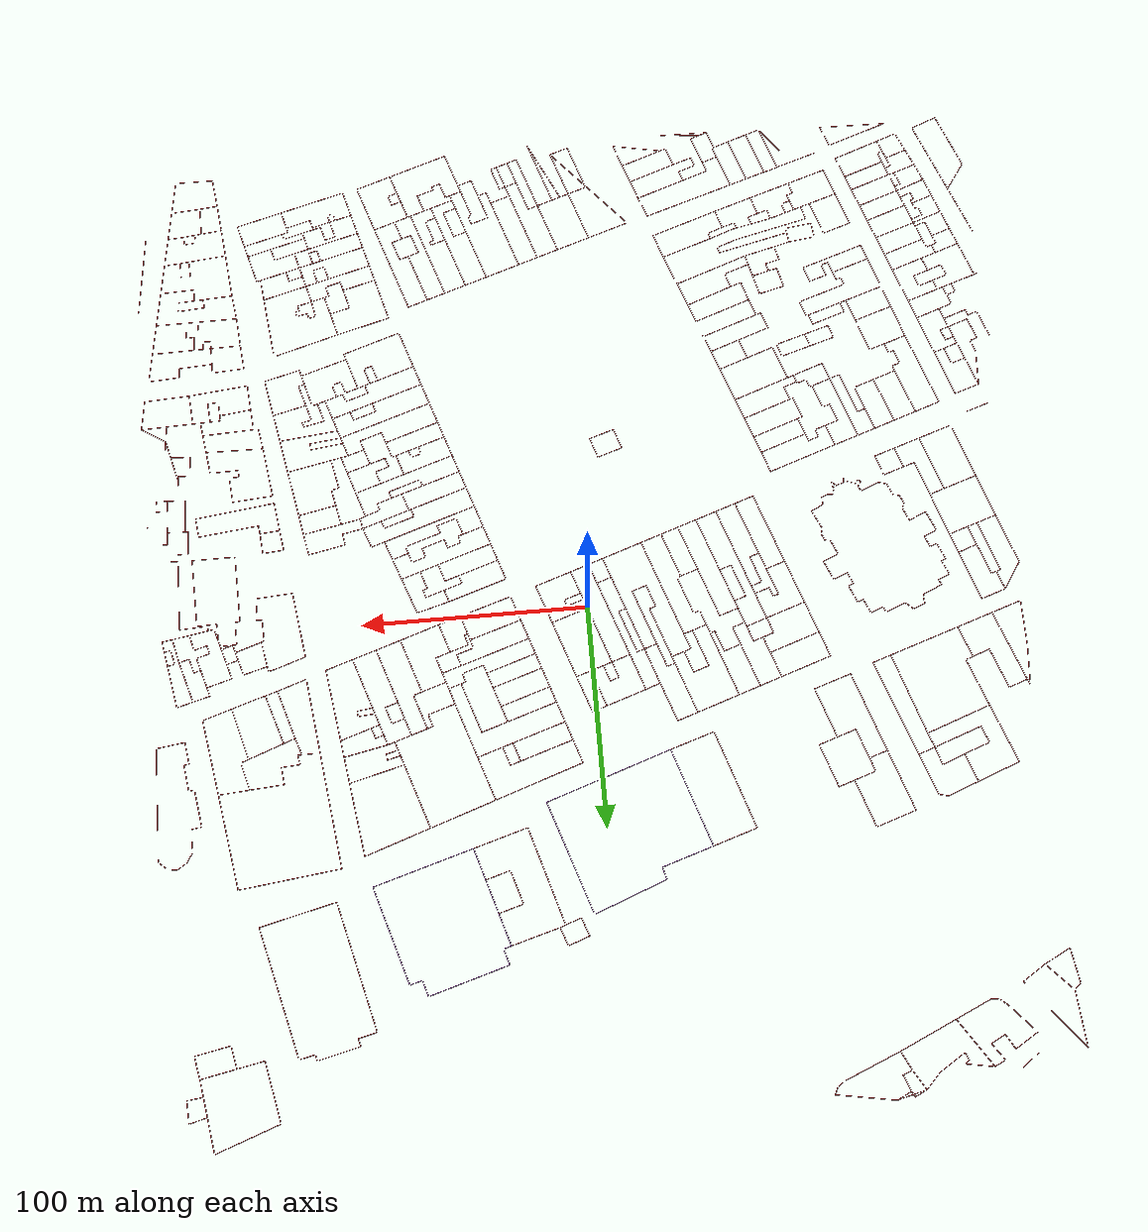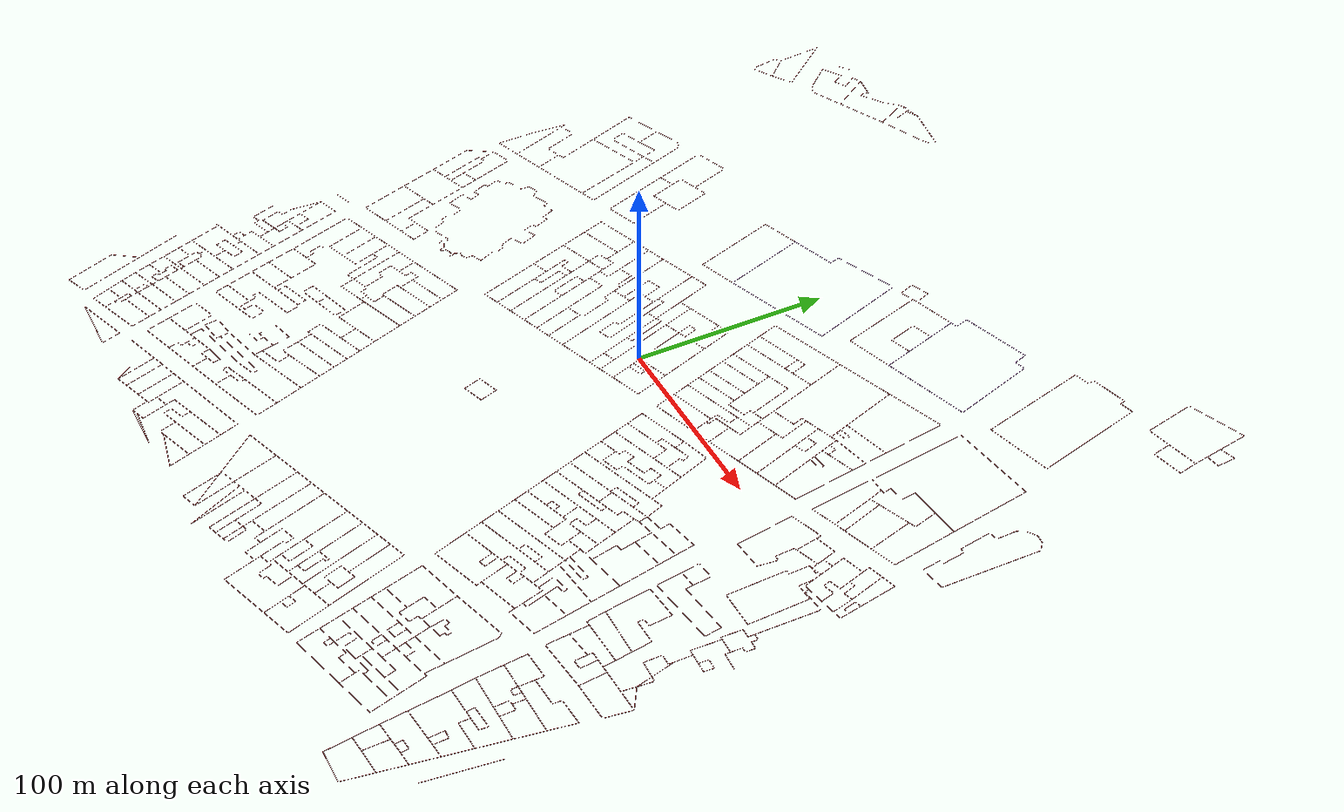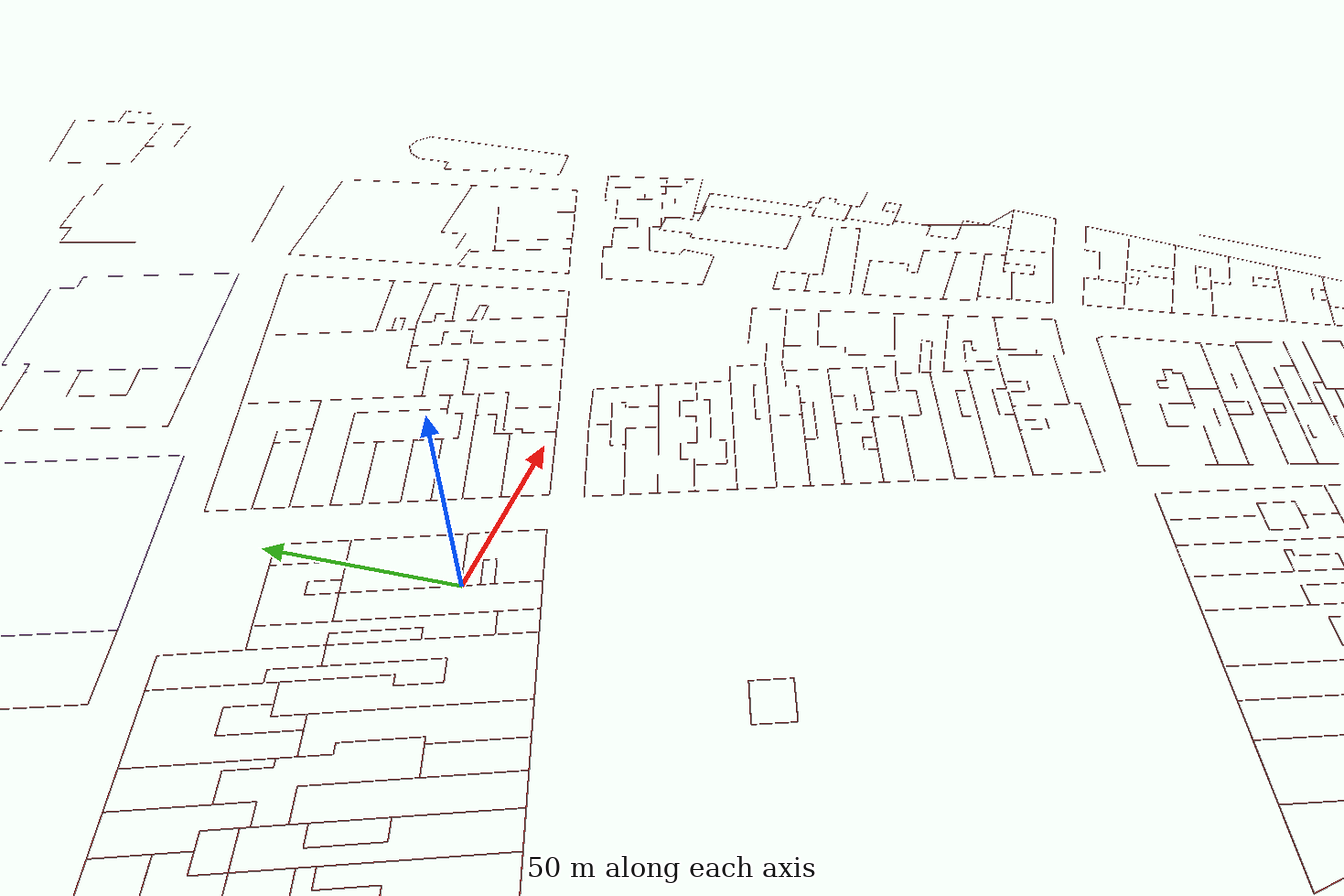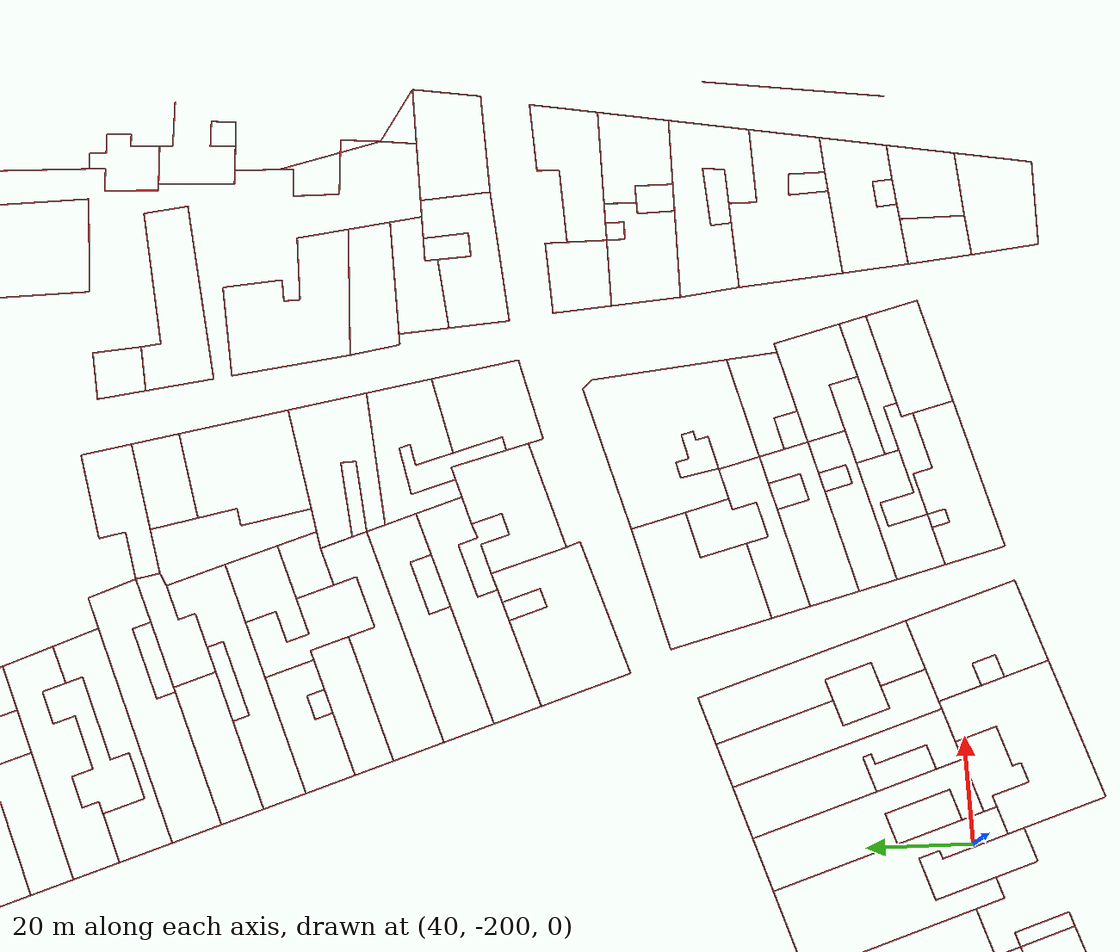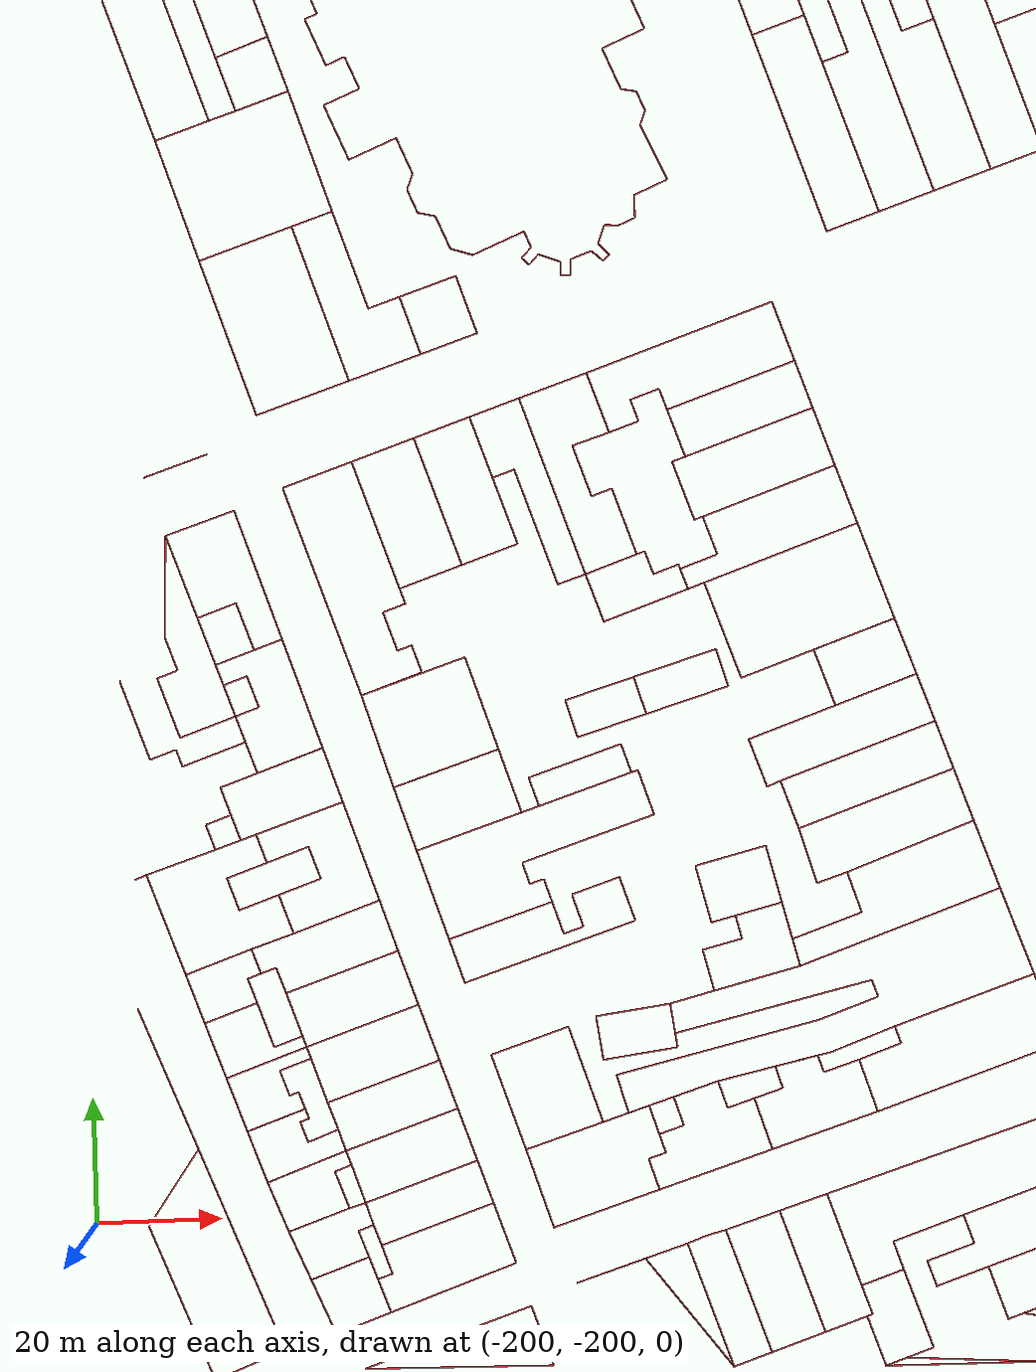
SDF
<sdf version="1.4">
 <world name="default">
  <spherical_coordinates>
   <surface_model>EARTH_WGS84</surface_model>
   <latitude_deg>49.84198</latitude_deg>
   <longitude_deg>24.030255</longitude_deg>
   <elevation>0.0</elevation>
   <heading_deg>0</heading_deg>
  </spherical_coordinates>
  <include><uri>model://sun</uri></include>
  <model name="university_0">
   <static>true</static>
   <pose>63.9825797929 143.316643131 0.0 0 0 0</pose>
   <link name="university_0_0">
    <collision name="university_0_0"><geometry><box><size>3.57502417082 0.2 0</size></box></geometry></collision>
    <visual name="university_0_0">
     <geometry><box><size>3.57502417082 0.2 0</size></box></geometry>
     <material>
      <script><uri>file://media/materials/scripts/gazebo.material</uri><name>Gazebo/Purple</name></script>
     </material>
    </visual>
    <pose>-17.1229955932 4.8587290905 0 0 0 -2.85070087832</pose>
   </link>
   <link name="university_0_1">
    <collision name="university_0_1"><geometry><box><size>7.33497105953 0.2 0</size></box></geometry></collision>
    <visual name="university_0_1">
     <geometry><box><size>7.33497105953 0.2 0</size></box></geometry>
     <material>
      <script><uri>file://media/materials/scripts/gazebo.material</uri><name>Gazebo/Purple</name></script>
     </material>
    </visual>
    <pose>-16.4612721665 8.88515743404 0 0 0 -1.28023659458</pose>
   </link>
   <link name="university_0_2">
    <collision name="university_0_2"><geometry><box><size>18.348885648 0.2 0</size></box></geometry></collision>
    <visual name="university_0_2">
     <geometry><box><size>18.348885648 0.2 0</size></box></geometry>
     <material>
      <script><uri>file://media/materials/scripts/gazebo.material</uri><name>Gazebo/Purple</name></script>
     </material>
    </visual>
    <pose>-8.72192838335 15.0267780433 0 0 0 -2.85109095513</pose>
   </link>
   <link name="university_0_3">
    <collision name="university_0_3"><geometry><box><size>18.38289557 0.2 0</size></box></geometry></collision>
    <visual name="university_0_3">
     <geometry><box><size>18.38289557 0.2 0</size></box></geometry>
     <material>
      <script><uri>file://media/materials/scripts/gazebo.material</uri><name>Gazebo/Purple</name></script>
     </material>
    </visual>
    <pose>8.87482625297 20.2860709886 0 0 0 -2.85123892173</pose>
   </link>
   <link name="university_0_4">
    <collision name="university_0_4"><geometry><box><size>7.44066809802 0.2 0</size></box></geometry></collision>
    <visual name="university_0_4">
     <geometry><box><size>7.44066809802 0.2 0</size></box></geometry>
     <material>
      <script><uri>file://media/materials/scripts/gazebo.material</uri><name>Gazebo/Purple</name></script>
     </material>
    </visual>
    <pose>18.7489079836 19.3535679981 0 0 0 1.86178543968</pose>
   </link>
   <link name="university_0_5">
    <collision name="university_0_5"><geometry><box><size>5.66314660854 0.2 0</size></box></geometry></collision>
    <visual name="university_0_5">
     <geometry><box><size>5.66314660854 0.2 0</size></box></geometry>
     <material>
      <script><uri>file://media/materials/scripts/gazebo.material</uri><name>Gazebo/Purple</name></script>
     </material>
    </visual>
    <pose>22.5294517501 16.5998568511 0 0 0 -2.85139824386</pose>
   </link>
   <link name="university_0_6">
    <collision name="university_0_6"><geometry><box><size>45.3338065073 0.2 0</size></box></geometry></collision>
    <visual name="university_0_6">
     <geometry><box><size>45.3338065073 0.2 0</size></box></geometry>
     <material>
      <script><uri>file://media/materials/scripts/gazebo.material</uri><name>Gazebo/Purple</name></script>
     </material>
    </visual>
    <pose>31.7358542151 -4.30688598695 0 0 0 1.86132908123</pose>
   </link>
   <link name="university_0_7">
    <collision name="university_0_7"><geometry><box><size>45.9805948722 0.2 0</size></box></geometry></collision>
    <visual name="university_0_7">
     <geometry><box><size>45.9805948722 0.2 0</size></box></geometry>
     <material>
      <script><uri>file://media/materials/scripts/gazebo.material</uri><name>Gazebo/Purple</name></script>
     </material>
    </visual>
    <pose>16.2012258348 -32.6062196526 0 0 0 0.290374139482</pose>
   </link>
   <link name="university_0_8">
    <collision name="university_0_8"><geometry><box><size>14.7825319775 0.2 0</size></box></geometry></collision>
    <visual name="university_0_8">
     <geometry><box><size>14.7825319775 0.2 0</size></box></geometry>
     <material>
      <script><uri>file://media/materials/scripts/gazebo.material</uri><name>Gazebo/Purple</name></script>
     </material>
    </visual>
    <pose>-7.94474156143 -32.1073176701 0 0 0 -1.28015131995</pose>
   </link>
   <link name="university_0_9">
    <collision name="university_0_9"><geometry><box><size>15.6871173259 0.2 0</size></box></geometry></collision>
    <visual name="university_0_9">
     <geometry><box><size>15.6871173259 0.2 0</size></box></geometry>
     <material>
      <script><uri>file://media/materials/scripts/gazebo.material</uri><name>Gazebo/Purple</name></script>
     </material>
    </visual>
    <pose>-12.3088200757 -17.5109243595 0 0 0 -1.28038669817</pose>
   </link>
   <link name="university_0_10">
    <collision name="university_0_10"><geometry><box><size>14.9670555747 0.2 0</size></box></geometry></collision>
    <visual name="university_0_10">
     <geometry><box><size>14.9670555747 0.2 0</size></box></geometry>
     <material>
      <script><uri>file://media/materials/scripts/gazebo.material</uri><name>Gazebo/Purple</name></script>
     </material>
    </visual>
    <pose>-16.6950966607 -2.82487147489 0 0 0 -1.28074284567</pose>
   </link>
  </model>
  <model name="office_building_150830023">
   <static>true</static>
   <pose>185.35539821 -221.782274317 0.0 0 0 0</pose>
  </model>
  <model name="office_building_179212020">
   <static>true</static>
   <pose>107.309177338 -180.747045495 0.0 0 0 0</pose>
   <link name="office_building_179212020_0">
    <collision name="office_building_179212020_0">
     <geometry><box><size>7.56169042597 0.2 0</size></box></geometry>
    </collision>
    <visual name="office_building_179212020_0">
     <geometry><box><size>7.56169042597 0.2 0</size></box></geometry>
     <material>
      <script><uri>file://media/materials/scripts/gazebo.material</uri><name>Gazebo/Red</name></script>
     </material>
    </visual>
    <pose>11.6667843835 2.69302688135 0 0 0 1.83109598639</pose>
   </link>
   <link name="office_building_179212020_1">
    <collision name="office_building_179212020_1">
     <geometry><box><size>6.70721505377 0.2 0</size></box></geometry>
    </collision>
    <visual name="office_building_179212020_1">
     <geometry><box><size>6.70721505377 0.2 0</size></box></geometry>
     <material>
      <script><uri>file://media/materials/scripts/gazebo.material</uri><name>Gazebo/Red</name></script>
     </material>
    </visual>
    <pose>9.39855811448 -1.82105649479 0 0 0 0.259523805588</pose>
   </link>
   <link name="office_building_179212020_2">
    <collision name="office_building_179212020_2">
     <geometry><box><size>23.8162199511 0.2 0</size></box></geometry>
    </collision>
    <visual name="office_building_179212020_2">
     <geometry><box><size>23.8162199511 0.2 0</size></box></geometry>
     <material>
      <script><uri>file://media/materials/scripts/gazebo.material</uri><name>Gazebo/Red</name></script>
     </material>
    </visual>
    <pose>-5.35131358008 -5.74040639141 0 0 0 0.259774294526</pose>
   </link>
   <link name="office_building_179212020_3">
    <collision name="office_building_179212020_3">
     <geometry><box><size>4.00794744453 0.2 0</size></box></geometry>
    </collision>
    <visual name="office_building_179212020_3">
     <geometry><box><size>4.00794744453 0.2 0</size></box></geometry>
     <material>
      <script><uri>file://media/materials/scripts/gazebo.material</uri><name>Gazebo/Red</name></script>
     </material>
    </visual>
    <pose>-17.3770063648 -6.86304975672 0 0 0 -1.30979377305</pose>
   </link>
   <link name="office_building_179212020_4">
    <collision name="office_building_179212020_4">
     <geometry><box><size>3.55378383514 0.2 0</size></box></geometry>
    </collision>
    <visual name="office_building_179212020_4">
     <geometry><box><size>3.55378383514 0.2 0</size></box></geometry>
     <material>
      <script><uri>file://media/materials/scripts/gazebo.material</uri><name>Gazebo/Red</name></script>
     </material>
    </visual>
    <pose>-18.3500883095 -3.2095516313 0 0 0 -1.31128919089</pose>
   </link>
   <link name="office_building_179212020_5">
    <collision name="office_building_179212020_5">
     <geometry><box><size>20.2831505235 0.2 0</size></box></geometry>
    </collision>
    <visual name="office_building_179212020_5">
     <geometry><box><size>20.2831505235 0.2 0</size></box></geometry>
     <material>
      <script><uri>file://media/materials/scripts/gazebo.material</uri><name>Gazebo/Red</name></script>
     </material>
    </visual>
    <pose>-9.00430047919 1.11117403845 0 0 0 -2.88198766221</pose>
   </link>
   <link name="office_building_179212020_6">
    <collision name="office_building_179212020_6">
     <geometry><box><size>5.51187295247 0.2 0</size></box></geometry>
    </collision>
    <visual name="office_building_179212020_6">
     <geometry><box><size>5.51187295247 0.2 0</size></box></geometry>
     <material>
      <script><uri>file://media/materials/scripts/gazebo.material</uri><name>Gazebo/Red</name></script>
     </material>
    </visual>
    <pose>1.50362215069 1.05057853143 0 0 0 1.82992501617</pose>
   </link>
   <link name="office_building_179212020_7">
    <collision name="office_building_179212020_7">
     <geometry><box><size>3.8094054034 0.2 0</size></box></geometry>
    </collision>
    <visual name="office_building_179212020_7">
     <geometry><box><size>3.8094054034 0.2 0</size></box></geometry>
     <material>
      <script><uri>file://media/materials/scripts/gazebo.material</uri><name>Gazebo/Red</name></script>
     </material>
    </visual>
    <pose>4.0500584002 -1.12208587744 0 0 0 -2.88072370782</pose>
   </link>
   <link name="office_building_179212020_8">
    <collision name="office_building_179212020_8">
     <geometry><box><size>5.51186942631 0.2 0</size></box></geometry>
    </collision>
    <visual name="office_building_179212020_8">
     <geometry><box><size>5.51186942631 0.2 0</size></box></geometry>
     <material>
      <script><uri>file://media/materials/scripts/gazebo.material</uri><name>Gazebo/Red</name></script>
     </material>
    </visual>
    <pose>5.18414147266 2.03309942175 0 0 0 -1.31166765053</pose>
   </link>
   <link name="office_building_179212020_9">
    <collision name="office_building_179212020_9">
     <geometry><box><size>6.43088256303 0.2 0</size></box></geometry>
    </collision>
    <visual name="office_building_179212020_9">
     <geometry><box><size>6.43088256303 0.2 0</size></box></geometry>
     <material>
      <script><uri>file://media/materials/scripts/gazebo.material</uri><name>Gazebo/Red</name></script>
     </material>
    </visual>
    <pose>7.58583644654 5.52176490232 0 0 0 -2.8821995311</pose>
   </link>
  </model>
  <model name="office_building_170023143">
   <static>true</static>
   <pose>182.899304467 -59.1883379062 0.0 0 0 0</pose>
   <link name="office_building_170023143_0">
    <collision name="office_building_170023143_0">
     <geometry><box><size>4.88624782974 0.2 0</size></box></geometry>
    </collision>
    <visual name="office_building_170023143_0">
     <geometry><box><size>4.88624782974 0.2 0</size></box></geometry>
     <material>
      <script><uri>file://media/materials/scripts/gazebo.material</uri><name>Gazebo/Red</name></script>
     </material>
    </visual>
    <pose>5.05941402953 -4.19694665799 0 0 0 -1.65508417354</pose>
   </link>
   <link name="office_building_170023143_1">
    <collision name="office_building_170023143_1">
     <geometry><box><size>5.18961605572 0.2 0</size></box></geometry>
    </collision>
    <visual name="office_building_170023143_1">
     <geometry><box><size>5.18961605572 0.2 0</size></box></geometry>
     <material>
      <script><uri>file://media/materials/scripts/gazebo.material</uri><name>Gazebo/Red</name></script>
     </material>
    </visual>
    <pose>2.67425252634 -1.61911163188 0 0 0 -0.0552863866708</pose>
   </link>
   <link name="office_building_170023143_2">
    <collision name="office_building_170023143_2">
     <geometry><box><size>4.95228702515 0.2 0</size></box></geometry>
    </collision>
    <visual name="office_building_170023143_2">
     <geometry><box><size>4.95228702515 0.2 0</size></box></geometry>
     <material>
      <script><uri>file://media/materials/scripts/gazebo.material</uri><name>Gazebo/Red</name></script>
     </material>
    </visual>
    <pose>-0.0221970109301 -3.94961760916 0 0 0 1.52813395041</pose>
   </link>
   <link name="office_building_170023143_3">
    <collision name="office_building_170023143_3">
     <geometry><box><size>5.07504997065 0.2 0</size></box></geometry>
    </collision>
    <visual name="office_building_170023143_3">
     <geometry><box><size>5.07504997065 0.2 0</size></box></geometry>
     <material>
      <script><uri>file://media/materials/scripts/gazebo.material</uri><name>Gazebo/Red</name></script>
     </material>
    </visual>
    <pose>-2.66304877333 -6.31597851467 0 0 0 -0.0423884571646</pose>
   </link>
   <link name="office_building_170023143_4">
    <collision name="office_building_170023143_4">
     <geometry><box><size>2.79365354063 0.2 0</size></box></geometry>
    </collision>
    <visual name="office_building_170023143_4">
     <geometry><box><size>2.79365354063 0.2 0</size></box></geometry>
     <material>
      <script><uri>file://media/materials/scripts/gazebo.material</uri><name>Gazebo/Red</name></script>
     </material>
    </visual>
    <pose>-6.59379148148 -6.14751494607 0 0 0 -0.0436370144828</pose>
   </link>
   <link name="office_building_170023143_5">
    <collision name="office_building_170023143_5">
     <geometry><box><size>14.9141957841 0.2 0</size></box></geometry>
    </collision>
    <visual name="office_building_170023143_5">
     <geometry><box><size>14.9141957841 0.2 0</size></box></geometry>
     <material>
      <script><uri>file://media/materials/scripts/gazebo.material</uri><name>Gazebo/Red</name></script>
     </material>
    </visual>
    <pose>-7.67246315149 1.36378352473 0 0 0 -1.61329554016</pose>
   </link>
   <link name="office_building_170023143_6">
    <collision name="office_building_170023143_6">
     <geometry><box><size>7.84530393587 0.2 0</size></box></geometry>
    </collision>
    <visual name="office_building_170023143_6">
     <geometry><box><size>7.84530393587 0.2 0</size></box></geometry>
     <material>
      <script><uri>file://media/materials/scripts/gazebo.material</uri><name>Gazebo/Red</name></script>
     </material>
    </visual>
    <pose>-3.43601513814 8.66001482435 0 0 0 3.1022894335</pose>
   </link>
   <link name="office_building_170023143_7">
    <collision name="office_building_170023143_7">
     <geometry><box><size>2.58298164823 0.2 0</size></box></geometry>
    </collision>
    <visual name="office_building_170023143_7">
     <geometry><box><size>2.58298164823 0.2 0</size></box></geometry>
     <material>
      <script><uri>file://media/materials/scripts/gazebo.material</uri><name>Gazebo/Red</name></script>
     </material>
    </visual>
    <pose>0.439141983187 7.21515652761 0 0 0 1.53635993706</pose>
   </link>
   <link name="office_building_170023143_8">
    <collision name="office_building_170023143_8">
     <geometry><box><size>9.21414520436 0.2 0</size></box></geometry>
    </collision>
    <visual name="office_building_170023143_8">
     <geometry><box><size>9.21414520436 0.2 0</size></box></geometry>
     <material>
      <script><uri>file://media/materials/scripts/gazebo.material</uri><name>Gazebo/Red</name></script>
     </material>
    </visual>
    <pose>4.99258960102 5.63406438887 0 0 0 3.07852449429</pose>
   </link>
  </model>
  <model name="Музей етнографії та художнього промислу">
   <static>true</static>
   <pose>-105.249044955 216.567339852 0.0 0 0 0</pose>
   <link name="Музей етнографії та художнього промислу_0">
    <collision name="Музей етнографії та художнього промислу_0">
     <geometry><box><size>26.4826236595 0.2 0</size></box></geometry>
    </collision>
    <visual name="Музей етнографії та художнього промислу_0">
     <geometry><box><size>26.4826236595 0.2 0</size></box></geometry>
     <material>
      <script><uri>file://media/materials/scripts/gazebo.material</uri><name>Gazebo/Red</name></script>
     </material>
    </visual>
    <pose>3.46536297473 -5.29319509273 0 0 0 -2.74636456304</pose>
   </link>
   <link name="Музей етнографії та художнього промислу_1">
    <collision name="Музей етнографії та художнього промислу_1">
     <geometry><box><size>4.04485360114 0.2 0</size></box></geometry>
    </collision>
    <visual name="Музей етнографії та художнього промислу_1">
     <geometry><box><size>4.04485360114 0.2 0</size></box></geometry>
     <material>
      <script><uri>file://media/materials/scripts/gazebo.material</uri><name>Gazebo/Red</name></script>
     </material>
    </visual>
    <pose>17.3538559548 0.948673371343 0 0 0 -2.54053327574</pose>
   </link>
   <link name="Музей етнографії та художнього промислу_2">
    <collision name="Музей етнографії та художнього промислу_2">
     <geometry><box><size>3.5396842466 0.2 0</size></box></geometry>
    </collision>
    <visual name="Музей етнографії та художнього промислу_2">
     <geometry><box><size>3.5396842466 0.2 0</size></box></geometry>
     <material>
      <script><uri>file://media/materials/scripts/gazebo.material</uri><name>Gazebo/Red</name></script>
     </material>
    </visual>
    <pose>19.8169346341 3.6735733372 0 0 0 -2.03672638689</pose>
   </link>
   <link name="Музей етнографії та художнього промислу_3">
    <collision name="Музей етнографії та художнього промислу_3">
     <geometry><box><size>26.0679784946 0.2 0</size></box></geometry>
    </collision>
    <visual name="Музей етнографії та художнього промислу_3">
     <geometry><box><size>26.0679784946 0.2 0</size></box></geometry>
     <material>
      <script><uri>file://media/materials/scripts/gazebo.material</uri><name>Gazebo/Red</name></script>
     </material>
    </visual>
    <pose>7.76912176286 7.47832369596 0 0 0 -0.171436037055</pose>
   </link>
   <link name="Музей етнографії та художнього промислу_4">
    <collision name="Музей етнографії та художнього промислу_4">
     <geometry><box><size>7.01476035445 0.2 0</size></box></geometry>
    </collision>
    <visual name="Музей етнографії та художнього промислу_4">
     <geometry><box><size>7.01476035445 0.2 0</size></box></geometry>
     <material>
      <script><uri>file://media/materials/scripts/gazebo.material</uri><name>Gazebo/Red</name></script>
     </material>
    </visual>
    <pose>-8.22068078019 8.15306618821 0 0 0 0.457369925226</pose>
   </link>
   <link name="Музей етнографії та художнього промислу_5">
    <collision name="Музей етнографії та художнього промислу_5">
     <geometry><box><size>7.67503110081 0.2 0</size></box></geometry>
    </collision>
    <visual name="Музей етнографії та художнього промислу_5">
     <geometry><box><size>7.67503110081 0.2 0</size></box></geometry>
     <material>
      <script><uri>file://media/materials/scripts/gazebo.material</uri><name>Gazebo/Red</name></script>
     </material>
    </visual>
    <pose>-9.97221163998 3.02939667767 0 0 0 1.94293412046</pose>
   </link>
   <link name="Музей етнографії та художнього промислу_6">
    <collision name="Музей етнографії та художнього промислу_6">
     <geometry><box><size>4.50242689687 0.2 0</size></box></geometry>
    </collision>
    <visual name="Музей етнографії та художнього промислу_6">
     <geometry><box><size>4.50242689687 0.2 0</size></box></geometry>
     <material>
      <script><uri>file://media/materials/scripts/gazebo.material</uri><name>Gazebo/Red</name></script>
     </material>
    </visual>
    <pose>-10.684036914 -1.3377705158 0 0 0 0.35965677679</pose>
   </link>
   <link name="Музей етнографії та художнього промислу_7">
    <collision name="Музей етнографії та художнього промислу_7">
     <geometry><box><size>9.19445876722 0.2 0</size></box></geometry>
    </collision>
    <visual name="Музей етнографії та художнього промислу_7">
     <geometry><box><size>9.19445876722 0.2 0</size></box></geometry>
     <material>
      <script><uri>file://media/materials/scripts/gazebo.material</uri><name>Gazebo/Red</name></script>
     </material>
    </visual>
    <pose>-10.7731861631 -6.26071982808 0 0 0 2.0252436175</pose>
   </link>
  </model>
  <model name="office_building_179177146">
   <static>true</static>
   <pose>107.73555699 -44.036744307 0.0 0 0 0</pose>
   <link name="office_building_179177146_0">
    <collision name="office_building_179177146_0">
     <geometry><box><size>8.77021498681 0.2 0</size></box></geometry>
    </collision>
    <visual name="office_building_179177146_0">
     <geometry><box><size>8.77021498681 0.2 0</size></box></geometry>
     <material>
      <script><uri>file://media/materials/scripts/gazebo.material</uri><name>Gazebo/Red</name></script>
     </material>
    </visual>
    <pose>-5.83074378357 -4.8860490727 0 0 0 0.20002445801</pose>
   </link>
   <link name="office_building_179177146_1">
    <collision name="office_building_179177146_1">
     <geometry><box><size>4.67637566324 0.2 0</size></box></geometry>
    </collision>
    <visual name="office_building_179177146_1">
     <geometry><box><size>4.67637566324 0.2 0</size></box></geometry>
     <material>
      <script><uri>file://media/materials/scripts/gazebo.material</uri><name>Gazebo/Red</name></script>
     </material>
    </visual>
    <pose>-10.595458706 -3.46627159934 0 0 0 -1.36969970133</pose>
   </link>
   <link name="office_building_179177146_2">
    <collision name="office_building_179177146_2">
     <geometry><box><size>9.39381510312 0.2 0</size></box></geometry>
    </collision>
    <visual name="office_building_179177146_2">
     <geometry><box><size>9.39381510312 0.2 0</size></box></geometry>
     <material>
      <script><uri>file://media/materials/scripts/gazebo.material</uri><name>Gazebo/Red</name></script>
     </material>
    </visual>
    <pose>-6.45903535802 -0.242960430012 0 0 0 -2.94178583114</pose>
   </link>
   <link name="office_building_179177146_3">
    <collision name="office_building_179177146_3">
     <geometry><box><size>5.16490632205 0.2 0</size></box></geometry>
    </collision>
    <visual name="office_building_179177146_3">
     <geometry><box><size>5.16490632205 0.2 0</size></box></geometry>
     <material>
      <script><uri>file://media/materials/scripts/gazebo.material</uri><name>Gazebo/Red</name></script>
     </material>
    </visual>
    <pose>-2.36708895537 3.22056916808 0 0 0 -1.37140410207</pose>
   </link>
   <link name="office_building_179177146_4">
    <collision name="office_building_179177146_4">
     <geometry><box><size>16.8376949698 0.2 0</size></box></geometry>
    </collision>
    <visual name="office_building_179177146_4">
     <geometry><box><size>16.8376949698 0.2 0</size></box></geometry>
     <material>
      <script><uri>file://media/materials/scripts/gazebo.material</uri><name>Gazebo/Red</name></script>
     </material>
    </visual>
    <pose>5.37204731678 7.42629138581 0 0 0 -2.94136624812</pose>
   </link>
   <link name="office_building_179177146_5">
    <collision name="office_building_179177146_5">
     <geometry><box><size>9.83669846744 0.2 0</size></box></geometry>
    </collision>
    <visual name="office_building_179177146_5">
     <geometry><box><size>9.83669846744 0.2 0</size></box></geometry>
     <material>
      <script><uri>file://media/materials/scripts/gazebo.material</uri><name>Gazebo/Red</name></script>
     </material>
    </visual>
    <pose>14.4956154592 4.26046001992 0 0 0 1.74922305372</pose>
   </link>
   <link name="office_building_179177146_6">
    <collision name="office_building_179177146_6">
     <geometry><box><size>17.2471142004 0.2 0</size></box></geometry>
    </collision>
    <visual name="office_building_179177146_6">
     <geometry><box><size>17.2471142004 0.2 0</size></box></geometry>
     <material>
      <script><uri>file://media/materials/scripts/gazebo.material</uri><name>Gazebo/Red</name></script>
     </material>
    </visual>
    <pose>6.9177318248 -2.2972818831 0 0 0 0.200501629629</pose>
   </link>
  </model>
  <model name="office_building_40987625">
   <static>true</static>
   <pose>-47.5276455496 29.9995622622 0.0 0 0 0</pose>
   <link name="office_building_40987625_0">
    <collision name="office_building_40987625_0">
     <geometry><box><size>19.8718178361 0.2 0</size></box></geometry>
    </collision>
    <visual name="office_building_40987625_0">
     <geometry><box><size>19.8718178361 0.2 0</size></box></geometry>
     <material>
      <script><uri>file://media/materials/scripts/gazebo.material</uri><name>Gazebo/Red</name></script>
     </material>
    </visual>
    <pose>-5.58994867541 18.777629946 0 0 0 -2.81387667566</pose>
   </link>
   <link name="office_building_40987625_1">
    <collision name="office_building_40987625_1">
     <geometry><box><size>24.3750151651 0.2 0</size></box></geometry>
    </collision>
    <visual name="office_building_40987625_1">
     <geometry><box><size>24.3750151651 0.2 0</size></box></geometry>
     <material>
      <script><uri>file://media/materials/scripts/gazebo.material</uri><name>Gazebo/Red</name></script>
     </material>
    </visual>
    <pose>7.74226525935 10.4376611425 0 0 0 1.89869968377</pose>
   </link>
   <link name="office_building_40987625_2">
    <collision name="office_building_40987625_2">
     <geometry><box><size>3.28659598791 0.2 0</size></box></geometry>
    </collision>
    <visual name="office_building_40987625_2">
     <geometry><box><size>3.28659598791 0.2 0</size></box></geometry>
     <material>
      <script><uri>file://media/materials/scripts/gazebo.material</uri><name>Gazebo/Red</name></script>
     </material>
    </visual>
    <pose>12.1955273686 -2.65659828674 0 0 0 1.89801160379</pose>
   </link>
   <link name="office_building_40987625_3">
    <collision name="office_building_40987625_3">
     <geometry><box><size>5.86038749009 0.2 0</size></box></geometry>
    </collision>
    <visual name="office_building_40987625_3">
     <geometry><box><size>5.86038749009 0.2 0</size></box></geometry>
     <material>
      <script><uri>file://media/materials/scripts/gazebo.material</uri><name>Gazebo/Red</name></script>
     </material>
    </visual>
    <pose>9.94937757814 -5.15567663744 0 0 0 0.32764286252</pose>
   </link>
   <link name="office_building_40987625_4">
    <collision name="office_building_40987625_4">
     <geometry><box><size>10.2797424304 0.2 0</size></box></geometry>
    </collision>
    <visual name="office_building_40987625_4">
     <geometry><box><size>10.2797424304 0.2 0</size></box></geometry>
     <material>
      <script><uri>file://media/materials/scripts/gazebo.material</uri><name>Gazebo/Red</name></script>
     </material>
    </visual>
    <pose>5.51828142877 -1.23312079129 0 0 0 -1.24259751973</pose>
   </link>
   <link name="office_building_40987625_5">
    <collision name="office_building_40987625_5">
     <geometry><box><size>7.32869468202 0.2 0</size></box></geometry>
    </collision>
    <visual name="office_building_40987625_5">
     <geometry><box><size>7.32869468202 0.2 0</size></box></geometry>
     <material>
      <script><uri>file://media/materials/scripts/gazebo.material</uri><name>Gazebo/Red</name></script>
     </material>
    </visual>
    <pose>0.392214224847 2.45279849264 0 0 0 0.327751526655</pose>
   </link>
   <link name="office_building_40987625_6">
    <collision name="office_building_40987625_6">
     <geometry><box><size>17.6653187614 0.2 0</size></box></geometry>
    </collision>
    <visual name="office_building_40987625_6">
     <geometry><box><size>17.6653187614 0.2 0</size></box></geometry>
     <material>
      <script><uri>file://media/materials/scripts/gazebo.material</uri><name>Gazebo/Red</name></script>
     </material>
    </visual>
    <pose>-0.230520119942 -7.08820946352 0 0 0 1.89892915388</pose>
   </link>
   <link name="office_building_40987625_7">
    <collision name="office_building_40987625_7">
     <geometry><box><size>6.68273243807 0.2 0</size></box></geometry>
    </collision>
    <visual name="office_building_40987625_7">
     <geometry><box><size>6.68273243807 0.2 0</size></box></geometry>
     <material>
      <script><uri>file://media/materials/scripts/gazebo.material</uri><name>Gazebo/Red</name></script>
     </material>
    </visual>
    <pose>-0.547463991771 -16.5252511182 0 0 0 0.327753482019</pose>
   </link>
   <link name="office_building_40987625_8">
    <collision name="office_building_40987625_8">
     <geometry><box><size>4.2490705321 0.2 0</size></box></geometry>
    </collision>
    <visual name="office_building_40987625_8">
     <geometry><box><size>4.2490705321 0.2 0</size></box></geometry>
     <material>
      <script><uri>file://media/materials/scripts/gazebo.material</uri><name>Gazebo/Red</name></script>
     </material>
    </visual>
    <pose>-4.39480575809 -15.5894242239 0 0 0 -1.24308282756</pose>
   </link>
   <link name="office_building_40987625_9">
    <collision name="office_building_40987625_9">
     <geometry><box><size>30.7981989087 0.2 0</size></box></geometry>
    </collision>
    <visual name="office_building_40987625_9">
     <geometry><box><size>30.7981989087 0.2 0</size></box></geometry>
     <material>
      <script><uri>file://media/materials/scripts/gazebo.material</uri><name>Gazebo/Red</name></script>
     </material>
    </visual>
    <pose>-10.0378588266 1.00074530107 0 0 0 -1.24290709319</pose>
   </link>
  </model>
  <model name="office_building_40987626">
   <static>true</static>
   <pose>4.07930946727 17.9549995831 0.0 0 0 0</pose>
   <link name="office_building_40987626_0">
    <collision name="office_building_40987626_0">
     <geometry><box><size>27.0524975586 0.2 0</size></box></geometry>
    </collision>
    <visual name="office_building_40987626_0">
     <geometry><box><size>27.0524975586 0.2 0</size></box></geometry>
     <material>
      <script><uri>file://media/materials/scripts/gazebo.material</uri><name>Gazebo/Red</name></script>
     </material>
    </visual>
    <pose>7.85751323067 0.603355349309 0 0 0 -1.24659905814</pose>
   </link>
   <link name="office_building_40987626_1">
    <collision name="office_building_40987626_1">
     <geometry><box><size>6.86274882106 0.2 0</size></box></geometry>
    </collision>
    <visual name="office_building_40987626_1">
     <geometry><box><size>6.86274882106 0.2 0</size></box></geometry>
     <material>
      <script><uri>file://media/materials/scripts/gazebo.material</uri><name>Gazebo/Red</name></script>
     </material>
    </visual>
    <pose>0.29629631932 12.3314290048 0 0 0 0.324348339967</pose>
   </link>
   <link name="office_building_40987626_2">
    <collision name="office_building_40987626_2">
     <geometry><box><size>5.92587712974 0.2 0</size></box></geometry>
    </collision>
    <visual name="office_building_40987626_2">
     <geometry><box><size>5.92587712974 0.2 0</size></box></geometry>
     <material>
      <script><uri>file://media/materials/scripts/gazebo.material</uri><name>Gazebo/Red</name></script>
     </material>
    </visual>
    <pose>-5.76383831655 10.2913309976 0 0 0 0.325162748979</pose>
   </link>
   <link name="office_building_40987626_3">
    <collision name="office_building_40987626_3">
     <geometry><box><size>4.12819134142 0.2 0</size></box></geometry>
    </collision>
    <visual name="office_building_40987626_3">
     <geometry><box><size>4.12819134142 0.2 0</size></box></geometry>
     <material>
      <script><uri>file://media/materials/scripts/gazebo.material</uri><name>Gazebo/Red</name></script>
     </material>
    </visual>
    <pose>-10.5285491485 8.68864986734 0 0 0 0.323491198897</pose>
   </link>
   <link name="office_building_40987626_4">
    <collision name="office_building_40987626_4">
     <geometry><box><size>27.0457727756 0.2 0</size></box></geometry>
    </collision>
    <visual name="office_building_40987626_4">
     <geometry><box><size>27.0457727756 0.2 0</size></box></geometry>
     <material>
      <script><uri>file://media/materials/scripts/gazebo.material</uri><name>Gazebo/Red</name></script>
     </material>
    </visual>
    <pose>-8.1768111025 -4.78555282756 0 0 0 1.89507815802</pose>
   </link>
   <link name="office_building_40987626_5">
    <collision name="office_building_40987626_5">
     <geometry><box><size>16.9145266085 0.2 0</size></box></geometry>
    </collision>
    <visual name="office_building_40987626_5">
     <geometry><box><size>16.9145266085 0.2 0</size></box></geometry>
     <material>
      <script><uri>file://media/materials/scripts/gazebo.material</uri><name>Gazebo/Red</name></script>
     </material>
    </visual>
    <pose>4.14911664084 -14.9109453528 0 0 0 -2.81756574673</pose>
   </link>
  </model>
  <model name="office_building_40987627">
   <static>true</static>
   <pose>0.380441204061 39.9751087007 0.0 0 0 0</pose>
   <link name="office_building_40987627_0">
    <collision name="office_building_40987627_0">
     <geometry><box><size>17.3946867505 0.2 0</size></box></geometry>
    </collision>
    <visual name="office_building_40987627_0">
     <geometry><box><size>17.3946867505 0.2 0</size></box></geometry>
     <material>
      <script><uri>file://media/materials/scripts/gazebo.material</uri><name>Gazebo/Red</name></script>
     </material>
    </visual>
    <pose>-2.03154920079 -2.5392145098 0 0 0 1.89544666042</pose>
   </link>
   <link name="office_building_40987627_1">
    <collision name="office_building_40987627_1">
     <geometry><box><size>6.86274882106 0.2 0</size></box></geometry>
    </collision>
    <visual name="office_building_40987627_1">
     <geometry><box><size>6.86274882106 0.2 0</size></box></geometry>
     <material>
      <script><uri>file://media/materials/scripts/gazebo.material</uri><name>Gazebo/Red</name></script>
     </material>
    </visual>
    <pose>3.99516458253 -9.68868011274 0 0 0 -2.81724431362</pose>
   </link>
   <link name="office_building_40987627_2">
    <collision name="office_building_40987627_2">
     <geometry><box><size>17.4943236326 0.2 0</size></box></geometry>
    </collision>
    <visual name="office_building_40987627_2">
     <geometry><box><size>17.4943236326 0.2 0</size></box></geometry>
     <material>
      <script><uri>file://media/materials/scripts/gazebo.material</uri><name>Gazebo/Red</name></script>
     </material>
    </visual>
    <pose>4.4344518102 -0.312685402992 0 0 0 -1.24336749835</pose>
   </link>
   <link name="office_building_40987627_3">
    <collision name="office_building_40987627_3">
     <geometry><box><size>6.81483814061 0.2 0</size></box></geometry>
    </collision>
    <visual name="office_building_40987627_3">
     <geometry><box><size>6.81483814061 0.2 0</size></box></geometry>
     <material>
      <script><uri>file://media/materials/scripts/gazebo.material</uri><name>Gazebo/Red</name></script>
     </material>
    </visual>
    <pose>-1.59226197312 6.83678019994 0 0 0 0.338957375312</pose>
   </link>
  </model>
  <model name="office_building_40987621">
   <static>true</static>
   <pose>-66.7904865269 -3.35216318831 0.0 0 0 0</pose>
   <link name="office_building_40987621_0">
    <collision name="office_building_40987621_0">
     <geometry><box><size>9.725640578 0.2 0</size></box></geometry>
    </collision>
    <visual name="office_building_40987621_0">
     <geometry><box><size>9.725640578 0.2 0</size></box></geometry>
     <material>
      <script><uri>file://media/materials/scripts/gazebo.material</uri><name>Gazebo/Red</name></script>
     </material>
    </visual>
    <pose>-6.70934359153 16.5361104141 0 0 0 0.328065372496</pose>
   </link>
   <link name="office_building_40987621_1">
    <collision name="office_building_40987621_1">
     <geometry><box><size>12.3241072874 0.2 0</size></box></geometry>
    </collision>
    <visual name="office_building_40987621_1">
     <geometry><box><size>12.3241072874 0.2 0</size></box></geometry>
     <material>
      <script><uri>file://media/materials/scripts/gazebo.material</uri><name>Gazebo/Red</name></script>
     </material>
    </visual>
    <pose>-9.32799423191 9.13560820251 0 0 0 1.89874760119</pose>
   </link>
   <link name="office_building_40987621_2">
    <collision name="office_building_40987621_2">
     <geometry><box><size>3.80877316599 0.2 0</size></box></geometry>
    </collision>
    <visual name="office_building_40987621_2">
     <geometry><box><size>3.80877316599 0.2 0</size></box></geometry>
     <material>
      <script><uri>file://media/materials/scripts/gazebo.material</uri><name>Gazebo/Red</name></script>
     </material>
    </visual>
    <pose>-6.73159834856 1.49845073696 0 0 0 1.89772822695</pose>
   </link>
   <link name="office_building_40987621_3">
    <collision name="office_building_40987621_3">
     <geometry><box><size>38.2145729424 0.2 0</size></box></geometry>
    </collision>
    <visual name="office_building_40987621_3">
     <geometry><box><size>38.2145729424 0.2 0</size></box></geometry>
     <material>
      <script><uri>file://media/materials/scripts/gazebo.material</uri><name>Gazebo/Red</name></script>
     </material>
    </visual>
    <pose>0.0346867295464 -18.3939536487 0 0 0 1.89875731644</pose>
   </link>
   <link name="office_building_40987621_4">
    <collision name="office_building_40987621_4">
     <geometry><box><size>9.72563729076 0.2 0</size></box></geometry>
    </collision>
    <visual name="office_building_40987621_4">
     <geometry><box><size>9.72563729076 0.2 0</size></box></geometry>
     <material>
      <script><uri>file://media/materials/scripts/gazebo.material</uri><name>Gazebo/Red</name></script>
     </material>
    </visual>
    <pose>10.7928578993 -34.9159439357 0 0 0 -2.81351870344</pose>
   </link>
   <link name="office_building_40987621_5">
    <collision name="office_building_40987621_5">
     <geometry><box><size>25.6788595364 0.2 0</size></box></geometry>
    </collision>
    <visual name="office_building_40987621_5">
     <geometry><box><size>25.6788595364 0.2 0</size></box></geometry>
     <material>
      <script><uri>file://media/materials/scripts/gazebo.material</uri><name>Gazebo/Red</name></script>
     </material>
    </visual>
    <pose>11.2598099396 -21.1941995596 0 0 0 -1.2427732367</pose>
   </link>
   <link name="office_building_40987621_6">
    <collision name="office_building_40987621_6">
     <geometry><box><size>5.4737365026 0.2 0</size></box></geometry>
    </collision>
    <visual name="office_building_40987621_6">
     <geometry><box><size>5.4737365026 0.2 0</size></box></geometry>
     <material>
      <script><uri>file://media/materials/scripts/gazebo.material</uri><name>Gazebo/Red</name></script>
     </material>
    </visual>
    <pose>4.53246355713 -9.92139599045 0 0 0 0.328138556485</pose>
   </link>
   <link name="office_building_40987621_7">
    <collision name="office_building_40987621_7">
     <geometry><box><size>15.7404388757 0.2 0</size></box></geometry>
    </collision>
    <visual name="office_building_40987621_7">
     <geometry><box><size>15.7404388757 0.2 0</size></box></geometry>
     <material>
      <script><uri>file://media/materials/scripts/gazebo.material</uri><name>Gazebo/Red</name></script>
     </material>
    </visual>
    <pose>-0.593629676035 -3.35274376197 0 0 0 -1.24281510477</pose>
   </link>
   <link name="office_building_40987621_8">
    <collision name="office_building_40987621_8">
     <geometry><box><size>5.47373703874 0.2 0</size></box></geometry>
    </collision>
    <visual name="office_building_40987621_8">
     <geometry><box><size>5.47373703874 0.2 0</size></box></geometry>
     <material>
      <script><uri>file://media/materials/scripts/gazebo.material</uri><name>Gazebo/Red</name></script>
     </material>
    </visual>
    <pose>-0.538041237885 4.97998592845 0 0 0 -2.81345658125</pose>
   </link>
   <link name="office_building_40987621_9">
    <collision name="office_building_40987621_9">
     <geometry><box><size>3.69618858074 0.2 0</size></box></geometry>
    </collision>
    <visual name="office_building_40987621_9">
     <geometry><box><size>3.69618858074 0.2 0</size></box></geometry>
     <material>
      <script><uri>file://media/materials/scripts/gazebo.material</uri><name>Gazebo/Red</name></script>
     </material>
    </visual>
    <pose>1.45790934873 7.61175193335 0 0 0 -1.24306646814</pose>
   </link>
   <link name="office_building_40987621_10">
    <collision name="office_building_40987621_10">
     <geometry><box><size>7.20117174216 0.2 0</size></box></geometry>
    </collision>
    <visual name="office_building_40987621_10">
     <geometry><box><size>7.20117174216 0.2 0</size></box></geometry>
     <material>
      <script><uri>file://media/materials/scripts/gazebo.material</uri><name>Gazebo/Red</name></script>
     </material>
    </visual>
    <pose>-0.293403385492 12.7713076677 0 0 0 -1.24382545799</pose>
   </link>
   <link name="office_building_40987621_11">
    <collision name="office_building_40987621_11">
     <geometry><box><size>2.03072751307 0.2 0</size></box></geometry>
    </collision>
    <visual name="office_building_40987621_11">
     <geometry><box><size>2.03072751307 0.2 0</size></box></geometry>
     <material>
      <script><uri>file://media/materials/scripts/gazebo.material</uri><name>Gazebo/Red</name></script>
     </material>
    </visual>
    <pose>-1.77784721703 17.1420516555 0 0 0 -1.24183611851</pose>
   </link>
  </model>
  <model name="office_building_40987622">
   <static>true</static>
   <pose>-72.5924252702 25.500206195 0.0 0 0 0</pose>
   <link name="office_building_40987622_0">
    <collision name="office_building_40987622_0">
     <geometry><box><size>10.3248769188 0.2 0</size></box></geometry>
    </collision>
    <visual name="office_building_40987622_0">
     <geometry><box><size>10.3248769188 0.2 0</size></box></geometry>
     <material>
      <script><uri>file://media/materials/scripts/gazebo.material</uri><name>Gazebo/Red</name></script>
     </material>
    </visual>
    <pose>-4.3932281761 15.1595893284 0 0 0 -2.81347740261</pose>
   </link>
   <link name="office_building_40987622_1">
    <collision name="office_building_40987622_1">
     <geometry><box><size>20.7368362857 0.2 0</size></box></geometry>
    </collision>
    <visual name="office_building_40987622_1">
     <geometry><box><size>20.7368362857 0.2 0</size></box></geometry>
     <material>
      <script><uri>file://media/materials/scripts/gazebo.material</uri><name>Gazebo/Red</name></script>
     </material>
    </visual>
    <pose>3.82958987209 7.00607468523 0 0 0 1.89834804244</pose>
   </link>
   <link name="office_building_40987622_2">
    <collision name="office_building_40987622_2">
     <geometry><box><size>8.42310639471 0.2 0</size></box></geometry>
    </collision>
    <visual name="office_building_40987622_2">
     <geometry><box><size>8.42310639471 0.2 0</size></box></geometry>
     <material>
      <script><uri>file://media/materials/scripts/gazebo.material</uri><name>Gazebo/Red</name></script>
     </material>
    </visual>
    <pose>8.52194254658 -6.79817769007 0 0 0 1.89874895408</pose>
   </link>
   <link name="office_building_40987622_3">
    <collision name="office_building_40987622_3">
     <geometry><box><size>5.8393391213 0.2 0</size></box></geometry>
    </collision>
    <visual name="office_building_40987622_3">
     <geometry><box><size>5.8393391213 0.2 0</size></box></geometry>
     <material>
      <script><uri>file://media/materials/scripts/gazebo.material</uri><name>Gazebo/Red</name></script>
     </material>
    </visual>
    <pose>7.11531043835 -11.728253762 0 0 0 0.328872139981</pose>
   </link>
   <link name="office_building_40987622_4">
    <collision name="office_building_40987622_4">
     <geometry><box><size>2.03072751307 0.2 0</size></box></geometry>
    </collision>
    <visual name="office_building_40987622_4">
     <geometry><box><size>2.03072751307 0.2 0</size></box></geometry>
     <material>
      <script><uri>file://media/materials/scripts/gazebo.material</uri><name>Gazebo/Red</name></script>
     </material>
    </visual>
    <pose>4.02409152636 -11.7103177277 0 0 0 -1.24183611851</pose>
   </link>
   <link name="office_building_40987622_5">
    <collision name="office_building_40987622_5">
     <geometry><box><size>7.41633127785 0.2 0</size></box></geometry>
    </collision>
    <visual name="office_building_40987622_5">
     <geometry><box><size>7.41633127785 0.2 0</size></box></geometry>
     <material>
      <script><uri>file://media/materials/scripts/gazebo.material</uri><name>Gazebo/Red</name></script>
     </material>
    </visual>
    <pose>2.50073541941 -7.23917536614 0 0 0 -1.24258356268</pose>
   </link>
   <link name="office_building_40987622_6">
    <collision name="office_building_40987622_6">
     <geometry><box><size>4.47501165499 0.2 0</size></box></geometry>
    </collision>
    <visual name="office_building_40987622_6">
     <geometry><box><size>4.47501165499 0.2 0</size></box></geometry>
     <material>
      <script><uri>file://media/materials/scripts/gazebo.material</uri><name>Gazebo/Red</name></script>
     </material>
    </visual>
    <pose>-0.812864293009 -4.44963245655 0 0 0 0.327937487412</pose>
   </link>
   <link name="office_building_40987622_7">
    <collision name="office_building_40987622_7">
     <geometry><box><size>7.6790223381 0.2 0</size></box></geometry>
    </collision>
    <visual name="office_building_40987622_7">
     <geometry><box><size>7.6790223381 0.2 0</size></box></geometry>
     <material>
      <script><uri>file://media/materials/scripts/gazebo.material</uri><name>Gazebo/Red</name></script>
     </material>
    </visual>
    <pose>-4.16537794509 -1.53459055722 0 0 0 -1.24352589672</pose>
   </link>
   <link name="office_building_40987622_8">
    <collision name="office_building_40987622_8">
     <geometry><box><size>12.037485981 0.2 0</size></box></geometry>
    </collision>
    <visual name="office_building_40987622_8">
     <geometry><box><size>12.037485981 0.2 0</size></box></geometry>
     <material>
      <script><uri>file://media/materials/scripts/gazebo.material</uri><name>Gazebo/Red</name></script>
     </material>
    </visual>
    <pose>-7.33994160383 7.79853854595 0 0 0 -1.24255476371</pose>
   </link>
  </model>
  <model name="office_building_40987623">
   <static>true</static>
   <pose>-55.4681492312 -14.4863195911 0.0 0 0 0</pose>
   <link name="office_building_40987623_0">
    <collision name="office_building_40987623_0">
     <geometry><box><size>8.7970008701 0.2 0</size></box></geometry>
    </collision>
    <visual name="office_building_40987623_0">
     <geometry><box><size>8.7970008701 0.2 0</size></box></geometry>
     <material>
      <script><uri>file://media/materials/scripts/gazebo.material</uri><name>Gazebo/Red</name></script>
     </material>
    </visual>
    <pose>8.23822012049 -20.7985887311 0 0 0 -2.81375554979</pose>
   </link>
   <link name="office_building_40987623_1">
    <collision name="office_building_40987623_1">
     <geometry><box><size>21.4193845422 0.2 0</size></box></geometry>
    </collision>
    <visual name="office_building_40987623_1">
     <geometry><box><size>21.4193845422 0.2 0</size></box></geometry>
     <material>
      <script><uri>file://media/materials/scripts/gazebo.material</uri><name>Gazebo/Red</name></script>
     </material>
    </visual>
    <pose>8.95537334613 -9.24251090195 0 0 0 -1.24309645352</pose>
   </link>
   <link name="office_building_40987623_2">
    <collision name="office_building_40987623_2">
     <geometry><box><size>23.6960277251 0.2 0</size></box></geometry>
    </collision>
    <visual name="office_building_40987623_2">
     <geometry><box><size>23.6960277251 0.2 0</size></box></geometry>
     <material>
      <script><uri>file://media/materials/scripts/gazebo.material</uri><name>Gazebo/Red</name></script>
     </material>
    </visual>
    <pose>1.68873518246 12.1127235518 0 0 0 -1.2425547506</pose>
   </link>
   <link name="office_building_40987623_3">
    <collision name="office_building_40987623_3">
     <geometry><box><size>8.79700333632 0.2 0</size></box></geometry>
    </collision>
    <visual name="office_building_40987623_3">
     <geometry><box><size>8.79700333632 0.2 0</size></box></geometry>
     <material>
      <script><uri>file://media/materials/scripts/gazebo.material</uri><name>Gazebo/Red</name></script>
     </material>
    </visual>
    <pose>-6.29506745898 21.9119094311 0 0 0 0.327829983273</pose>
   </link>
   <link name="office_building_40987623_4">
    <collision name="office_building_40987623_4">
     <geometry><box><size>3.69618858074 0.2 0</size></box></geometry>
    </collision>
    <visual name="office_building_40987623_4">
     <geometry><box><size>3.69618858074 0.2 0</size></box></geometry>
     <material>
      <script><uri>file://media/materials/scripts/gazebo.material</uri><name>Gazebo/Red</name></script>
     </material>
    </visual>
    <pose>-9.86442794691 18.7459083361 0 0 0 1.89852618545</pose>
   </link>
   <link name="office_building_40987623_5">
    <collision name="office_building_40987623_5">
     <geometry><box><size>15.7404252782 0.2 0</size></box></geometry>
    </collision>
    <visual name="office_building_40987623_5">
     <geometry><box><size>15.7404252782 0.2 0</size></box></geometry>
     <material>
      <script><uri>file://media/materials/scripts/gazebo.material</uri><name>Gazebo/Red</name></script>
     </material>
    </visual>
    <pose>-6.73428530037 9.54549010273 0 0 0 1.89877751462</pose>
   </link>
   <link name="office_building_40987623_6">
    <collision name="office_building_40987623_6">
     <geometry><box><size>25.6788595364 0.2 0</size></box></geometry>
    </collision>
    <visual name="office_building_40987623_6">
     <geometry><box><size>25.6788595364 0.2 0</size></box></geometry>
     <material>
      <script><uri>file://media/materials/scripts/gazebo.material</uri><name>Gazebo/Red</name></script>
     </material>
    </visual>
    <pose>-0.062527356041 -10.0600431569 0 0 0 1.89881941689</pose>
   </link>
  </model>
  <model name="office_building_41054229">
   <static>true</static>
   <pose>84.9970301575 -89.0085836096 0.0 0 0 0</pose>
   <link name="office_building_41054229_0">
    <collision name="office_building_41054229_0">
     <geometry><box><size>10.0188724437 0.2 0</size></box></geometry>
    </collision>
    <visual name="office_building_41054229_0">
     <geometry><box><size>10.0188724437 0.2 0</size></box></geometry>
     <material>
      <script><uri>file://media/materials/scripts/gazebo.material</uri><name>Gazebo/Red</name></script>
     </material>
    </visual>
    <pose>-23.4608659015 -8.79829544821 0 0 0 1.8844718714</pose>
   </link>
   <link name="office_building_41054229_1">
    <collision name="office_building_41054229_1">
     <geometry><box><size>43.0530705548 0.2 0</size></box></geometry>
    </collision>
    <visual name="office_building_41054229_1">
     <geometry><box><size>43.0530705548 0.2 0</size></box></geometry>
     <material>
      <script><uri>file://media/materials/scripts/gazebo.material</uri><name>Gazebo/Red</name></script>
     </material>
    </visual>
    <pose>-1.44430252668 -6.90482356789 0 0 0 -2.82712018569</pose>
   </link>
   <link name="office_building_41054229_2">
    <collision name="office_building_41054229_2">
     <geometry><box><size>2.91424166014 0.2 0</size></box></geometry>
    </collision>
    <visual name="office_building_41054229_2">
     <geometry><box><size>2.91424166014 0.2 0</size></box></geometry>
     <material>
      <script><uri>file://media/materials/scripts/gazebo.material</uri><name>Gazebo/Red</name></script>
     </material>
    </visual>
    <pose>18.5706428534 1.13761031057 0 0 0 -1.25255966006</pose>
   </link>
   <link name="office_building_41054229_3">
    <collision name="office_building_41054229_3">
     <geometry><box><size>6.41531024577 0.2 0</size></box></geometry>
    </collision>
    <visual name="office_building_41054229_3">
     <geometry><box><size>6.41531024577 0.2 0</size></box></geometry>
     <material>
      <script><uri>file://media/materials/scripts/gazebo.material</uri><name>Gazebo/Red</name></script>
     </material>
    </visual>
    <pose>17.1250388289 5.57272762493 0 0 0 -1.25714108843</pose>
   </link>
   <link name="office_building_41054229_4">
    <collision name="office_building_41054229_4">
     <geometry><box><size>7.58794733373 0.2 0</size></box></geometry>
    </collision>
    <visual name="office_building_41054229_4">
     <geometry><box><size>7.58794733373 0.2 0</size></box></geometry>
     <material>
      <script><uri>file://media/materials/scripts/gazebo.material</uri><name>Gazebo/Red</name></script>
     </material>
    </visual>
    <pose>12.5270990431 7.45140641626 0 0 0 0.314181267628</pose>
   </link>
   <link name="office_building_41054229_5">
    <collision name="office_building_41054229_5">
     <geometry><box><size>4.54875897101 0.2 0</size></box></geometry>
    </collision>
    <visual name="office_building_41054229_5">
     <geometry><box><size>4.54875897101 0.2 0</size></box></geometry>
     <material>
      <script><uri>file://media/materials/scripts/gazebo.material</uri><name>Gazebo/Red</name></script>
     </material>
    </visual>
    <pose>9.62496338624 4.11693628013 0 0 0 1.88648159093</pose>
   </link>
   <link name="office_building_41054229_6">
    <collision name="office_building_41054229_6">
     <geometry><box><size>10.3262559026 0.2 0</size></box></geometry>
    </collision>
    <visual name="office_building_41054229_6">
     <geometry><box><size>10.3262559026 0.2 0</size></box></geometry>
     <material>
      <script><uri>file://media/materials/scripts/gazebo.material</uri><name>Gazebo/Red</name></script>
     </material>
    </visual>
    <pose>5.42185567105 0.355774781035 0 0 0 0.314908540295</pose>
   </link>
   <link name="office_building_41054229_7">
    <collision name="office_building_41054229_7">
     <geometry><box><size>5.24147603413 0.2 0</size></box></geometry>
    </collision>
    <visual name="office_building_41054229_7">
     <geometry><box><size>5.24147603413 0.2 0</size></box></geometry>
     <material>
      <script><uri>file://media/materials/scripts/gazebo.material</uri><name>Gazebo/Red</name></script>
     </material>
    </visual>
    <pose>-0.299137613088 1.24844990652 0 0 0 -1.25587023296</pose>
   </link>
   <link name="office_building_41054229_8">
    <collision name="office_building_41054229_8">
     <geometry><box><size>25.1282964419 0.2 0</size></box></geometry>
    </collision>
    <visual name="office_building_41054229_8">
     <geometry><box><size>25.1282964419 0.2 0</size></box></geometry>
     <material>
      <script><uri>file://media/materials/scripts/gazebo.material</uri><name>Gazebo/Red</name></script>
     </material>
    </visual>
    <pose>-13.0587316661 -0.146496059658 0 0 0 0.314515699704</pose>
   </link>
  </model>
  <model name="office_building_40987628">
   <static>true</static>
   <pose>-1.66295739852 -2.87473365297 0.0 0 0 0</pose>
   <link name="office_building_40987628_0">
    <collision name="office_building_40987628_0">
     <geometry><box><size>8.52592400318 0.2 0</size></box></geometry>
    </collision>
    <visual name="office_building_40987628_0">
     <geometry><box><size>8.52592400318 0.2 0</size></box></geometry>
     <material>
      <script><uri>file://media/materials/scripts/gazebo.material</uri><name>Gazebo/Red</name></script>
     </material>
    </visual>
    <pose>3.80349163968 -15.5940091801 0 0 0 0.331539371012</pose>
   </link>
   <link name="office_building_40987628_1">
    <collision name="office_building_40987628_1">
     <geometry><box><size>9.5287926722 0.2 0</size></box></geometry>
    </collision>
    <visual name="office_building_40987628_1">
     <geometry><box><size>9.5287926722 0.2 0</size></box></geometry>
     <material>
      <script><uri>file://media/materials/scripts/gazebo.material</uri><name>Gazebo/Red</name></script>
     </material>
    </visual>
    <pose>-1.76182254724 -12.4710807661 0 0 0 -1.24287366503</pose>
   </link>
   <link name="office_building_40987628_2">
    <collision name="office_building_40987628_2">
     <geometry><box><size>36.0030534789 0.2 0</size></box></geometry>
    </collision>
    <visual name="office_building_40987628_2">
     <geometry><box><size>36.0030534789 0.2 0</size></box></geometry>
     <material>
      <script><uri>file://media/materials/scripts/gazebo.material</uri><name>Gazebo/Red</name></script>
     </material>
    </visual>
    <pose>-9.10624066852 9.07762530071 0 0 0 -1.24216733233</pose>
   </link>
   <link name="office_building_40987628_3">
    <collision name="office_building_40987628_3">
     <geometry><box><size>8.62196207264 0.2 0</size></box></geometry>
    </collision>
    <visual name="office_building_40987628_3">
     <geometry><box><size>8.62196207264 0.2 0</size></box></geometry>
     <material>
      <script><uri>file://media/materials/scripts/gazebo.material</uri><name>Gazebo/Red</name></script>
     </material>
    </visual>
    <pose>-10.8297360854 27.4890322644 0 0 0 -2.81740402136</pose>
   </link>
   <link name="office_building_40987628_4">
    <collision name="office_building_40987628_4">
     <geometry><box><size>27.0457727756 0.2 0</size></box></geometry>
    </collision>
    <visual name="office_building_40987628_4">
     <geometry><box><size>27.0457727756 0.2 0</size></box></geometry>
     <material>
      <script><uri>file://media/materials/scripts/gazebo.material</uri><name>Gazebo/Red</name></script>
     </material>
    </visual>
    <pose>-2.43454423671 16.0441804085 0 0 0 1.89507815802</pose>
   </link>
   <link name="office_building_40987628_5">
    <collision name="office_building_40987628_5">
     <geometry><box><size>4.42277778239 0.2 0</size></box></geometry>
    </collision>
    <visual name="office_building_40987628_5">
     <geometry><box><size>4.42277778239 0.2 0</size></box></geometry>
     <material>
      <script><uri>file://media/materials/scripts/gazebo.material</uri><name>Gazebo/Red</name></script>
     </material>
    </visual>
    <pose>2.57475648929 1.12861097729 0 0 0 1.8931314013</pose>
   </link>
   <link name="office_building_40987628_6">
    <collision name="office_building_40987628_6">
     <geometry><box><size>3.10865162749 0.2 0</size></box></geometry>
    </collision>
    <visual name="office_building_40987628_6">
     <geometry><box><size>3.10865162749 0.2 0</size></box></geometry>
     <material>
      <script><uri>file://media/materials/scripts/gazebo.material</uri><name>Gazebo/Red</name></script>
     </material>
    </visual>
    <pose>3.82014178385 -2.42458677535 0 0 0 1.92894615578</pose>
   </link>
   <link name="office_building_40987628_7">
    <collision name="office_building_40987628_7">
     <geometry><box><size>10.8933515946 0.2 0</size></box></geometry>
    </collision>
    <visual name="office_building_40987628_7">
     <geometry><box><size>10.8933515946 0.2 0</size></box></geometry>
     <material>
      <script><uri>file://media/materials/scripts/gazebo.material</uri><name>Gazebo/Red</name></script>
     </material>
    </visual>
    <pose>6.09965066162 -9.04335272184 0 0 0 1.89492091699</pose>
   </link>
  </model>
  <model name="office_building_179437791">
   <static>true</static>
   <pose>185.864565066 10.892280764 0.0 0 0 0</pose>
   <link name="office_building_179437791_0">
    <collision name="office_building_179437791_0">
     <geometry><box><size>4.86724777461 0.2 0</size></box></geometry>
    </collision>
    <visual name="office_building_179437791_0">
     <geometry><box><size>4.86724777461 0.2 0</size></box></geometry>
     <material>
      <script><uri>file://media/materials/scripts/gazebo.material</uri><name>Gazebo/Red</name></script>
     </material>
    </visual>
    <pose>1.45440945222 -8.44349080473 0 0 0 -1.40092393222</pose>
   </link>
   <link name="office_building_179437791_1">
    <collision name="office_building_179437791_1">
     <geometry><box><size>2.81594639539 0.2 0</size></box></geometry>
    </collision>
    <visual name="office_building_179437791_1">
     <geometry><box><size>2.81594639539 0.2 0</size></box></geometry>
     <material>
      <script><uri>file://media/materials/scripts/gazebo.material</uri><name>Gazebo/Red</name></script>
     </material>
    </visual>
    <pose>0.803921833473 -4.65736718085 0 0 0 -1.40017419619</pose>
   </link>
   <link name="office_building_179437791_2">
    <collision name="office_building_179437791_2">
     <geometry><box><size>3.84254284173 0.2 0</size></box></geometry>
    </collision>
    <visual name="office_building_179437791_2">
     <geometry><box><size>3.84254284173 0.2 0</size></box></geometry>
     <material>
      <script><uri>file://media/materials/scripts/gazebo.material</uri><name>Gazebo/Red</name></script>
     </material>
    </visual>
    <pose>0.236832667611 -1.37677620253 0 0 0 -1.39922423585</pose>
   </link>
   <link name="office_building_179437791_3">
    <collision name="office_building_179437791_3">
     <geometry><box><size>19.4053980841 0.2 0</size></box></geometry>
    </collision>
    <visual name="office_building_179437791_3">
     <geometry><box><size>19.4053980841 0.2 0</size></box></geometry>
     <material>
      <script><uri>file://media/materials/scripts/gazebo.material</uri><name>Gazebo/Red</name></script>
     </material>
    </visual>
    <pose>-1.73683662738 10.0784101586 0 0 0 -1.40036524649</pose>
   </link>
  </model>
  <model name="office_building_40887661">
   <static>true</static>
   <pose>74.8847934732 -204.738881934 0.0 0 0 0</pose>
   <link name="office_building_40887661_0">
    <collision name="office_building_40887661_0">
     <geometry><box><size>16.4165367148 0.2 0</size></box></geometry>
    </collision>
    <visual name="office_building_40887661_0">
     <geometry><box><size>16.4165367148 0.2 0</size></box></geometry>
     <material>
      <script><uri>file://media/materials/scripts/gazebo.material</uri><name>Gazebo/Red</name></script>
     </material>
    </visual>
    <pose>6.69207986386 -9.64021174003 0 0 0 -2.82714000794</pose>
   </link>
   <link name="office_building_40887661_1">
    <collision name="office_building_40887661_1">
     <geometry><box><size>22.344503408 0.2 0</size></box></geometry>
    </collision>
    <visual name="office_building_40887661_1">
     <geometry><box><size>22.344503408 0.2 0</size></box></geometry>
     <material>
      <script><uri>file://media/materials/scripts/gazebo.material</uri><name>Gazebo/Red</name></script>
     </material>
    </visual>
    <pose>11.0393026214 3.52201729249 0 0 0 -1.25605875203</pose>
   </link>
   <link name="office_building_40887661_2">
    <collision name="office_building_40887661_2">
     <geometry><box><size>9.89286966893 0.2 0</size></box></geometry>
    </collision>
    <visual name="office_building_40887661_2">
     <geometry><box><size>9.89286966893 0.2 0</size></box></geometry>
     <material>
      <script><uri>file://media/materials/scripts/gazebo.material</uri><name>Gazebo/Red</name></script>
     </material>
    </visual>
    <pose>2.87725208403 12.6143206586 0 0 0 0.314713835788</pose>
   </link>
   <link name="office_building_40887661_3">
    <collision name="office_building_40887661_3">
     <geometry><box><size>6.52588840504 0.2 0</size></box></geometry>
    </collision>
    <visual name="office_building_40887661_3">
     <geometry><box><size>6.52588840504 0.2 0</size></box></geometry>
     <material>
      <script><uri>file://media/materials/scripts/gazebo.material</uri><name>Gazebo/Red</name></script>
     </material>
    </visual>
    <pose>-4.92854043431 10.0719782314 0 0 0 0.315092668822</pose>
   </link>
   <link name="office_building_40887661_4">
    <collision name="office_building_40887661_4">
     <geometry><box><size>8.64024974058 0.2 0</size></box></geometry>
    </collision>
    <visual name="office_building_40887661_4">
     <geometry><box><size>8.64024974058 0.2 0</size></box></geometry>
     <material>
      <script><uri>file://media/materials/scripts/gazebo.material</uri><name>Gazebo/Red</name></script>
     </material>
    </visual>
    <pose>-6.69635045153 4.95193148758 0 0 0 1.88483385698</pose>
   </link>
   <link name="office_building_40887661_5">
    <collision name="office_building_40887661_5">
     <geometry><box><size>4.48021929231 0.2 0</size></box></geometry>
    </collision>
    <visual name="office_building_40887661_5">
     <geometry><box><size>4.48021929231 0.2 0</size></box></geometry>
     <material>
      <script><uri>file://media/materials/scripts/gazebo.material</uri><name>Gazebo/Red</name></script>
     </material>
    </visual>
    <pose>-3.23250207769 1.53873823373 0 0 0 -2.82582760035</pose>
   </link>
   <link name="office_building_40887661_6">
    <collision name="office_building_40887661_6">
     <geometry><box><size>4.72963120781 0.2 0</size></box></geometry>
    </collision>
    <visual name="office_building_40887661_6">
     <geometry><box><size>4.72963120781 0.2 0</size></box></geometry>
     <material>
      <script><uri>file://media/materials/scripts/gazebo.material</uri><name>Gazebo/Red</name></script>
     </material>
    </visual>
    <pose>-0.369173386857 -0.013639372271 0 0 0 1.88638047741</pose>
   </link>
   <link name="office_building_40887661_7">
    <collision name="office_building_40887661_7">
     <geometry><box><size>4.47799776124 0.2 0</size></box></geometry>
    </collision>
    <visual name="office_building_40887661_7">
     <geometry><box><size>4.47799776124 0.2 0</size></box></geometry>
     <material>
      <script><uri>file://media/materials/scripts/gazebo.material</uri><name>Gazebo/Red</name></script>
     </material>
    </visual>
    <pose>-1.76455735786 -2.95373742868 0 0 0 0.314243611588</pose>
   </link>
   <link name="office_building_40887661_8">
    <collision name="office_building_40887661_8">
     <geometry><box><size>8.97468179224 0.2 0</size></box></geometry>
    </collision>
    <visual name="office_building_40887661_8">
     <geometry><box><size>8.97468179224 0.2 0</size></box></geometry>
     <material>
      <script><uri>file://media/materials/scripts/gazebo.material</uri><name>Gazebo/Red</name></script>
     </material>
    </visual>
    <pose>-2.5038081095 -7.91240103384 0 0 0 1.8857619283</pose>
   </link>
  </model>
  <model name="office_building_179437793">
   <static>true</static>
   <pose>158.224829535 9.02316383722 0.0 0 0 0</pose>
   <link name="office_building_179437793_0">
    <collision name="office_building_179437793_0">
     <geometry><box><size>7.33286384048 0.2 0</size></box></geometry>
    </collision>
    <visual name="office_building_179437793_0">
     <geometry><box><size>7.33286384048 0.2 0</size></box></geometry>
     <material>
      <script><uri>file://media/materials/scripts/gazebo.material</uri><name>Gazebo/Red</name></script>
     </material>
    </visual>
    <pose>2.67423844313 0.234239871703 0 0 0 1.85356391134</pose>
   </link>
   <link name="office_building_179437793_1">
    <collision name="office_building_179437793_1">
     <geometry><box><size>5.26936490319 0.2 0</size></box></geometry>
    </collision>
    <visual name="office_building_179437793_1">
     <geometry><box><size>5.26936490319 0.2 0</size></box></geometry>
     <material>
      <script><uri>file://media/materials/scripts/gazebo.material</uri><name>Gazebo/Red</name></script>
     </material>
    </visual>
    <pose>1.20089883508 -4.12914462691 0 0 0 0.325512958923</pose>
   </link>
   <link name="office_building_179437793_2">
    <collision name="office_building_179437793_2">
     <geometry><box><size>3.68020882226 0.2 0</size></box></geometry>
    </collision>
    <visual name="office_building_179437793_2">
     <geometry><box><size>3.68020882226 0.2 0</size></box></geometry>
     <material>
      <script><uri>file://media/materials/scripts/gazebo.material</uri><name>Gazebo/Red</name></script>
     </material>
    </visual>
    <pose>-1.80692278409 -3.20411732647 0 0 0 -1.28911562692</pose>
   </link>
   <link name="office_building_179437793_3">
    <collision name="office_building_179437793_3">
     <geometry><box><size>3.77527745149 0.2 0</size></box></geometry>
    </collision>
    <visual name="office_building_179437793_3">
     <geometry><box><size>3.77527745149 0.2 0</size></box></geometry>
     <material>
      <script><uri>file://media/materials/scripts/gazebo.material</uri><name>Gazebo/Red</name></script>
     </material>
    </visual>
    <pose>-2.85215001626 0.374078135266 0 0 0 -1.28413497828</pose>
   </link>
   <link name="office_building_179437793_4">
    <collision name="office_building_179437793_4">
     <geometry><box><size>5.27624895254 0.2 0</size></box></geometry>
    </collision>
    <visual name="office_building_179437793_4">
     <geometry><box><size>5.27624895254 0.2 0</size></box></geometry>
     <material>
      <script><uri>file://media/materials/scripts/gazebo.material</uri><name>Gazebo/Red</name></script>
     </material>
    </visual>
    <pose>-0.867315659032 2.96987745477 0 0 0 -2.83938185972</pose>
   </link>
  </model>
  <model name="office_building_40876402">
   <static>true</static>
   <pose>-91.023680925 -72.0791867744 0.0 0 0 0</pose>
   <link name="office_building_40876402_0">
    <collision name="office_building_40876402_0">
     <geometry><box><size>21.827060518 0.2 0</size></box></geometry>
    </collision>
    <visual name="office_building_40876402_0">
     <geometry><box><size>21.827060518 0.2 0</size></box></geometry>
     <material>
      <script><uri>file://media/materials/scripts/gazebo.material</uri><name>Gazebo/Red</name></script>
     </material>
    </visual>
    <pose>-3.11349042276 2.33700752505 0 0 0 0.331641401651</pose>
   </link>
   <link name="office_building_40876402_1">
    <collision name="office_building_40876402_1">
     <geometry><box><size>8.05512464131 0.2 0</size></box></geometry>
    </collision>
    <visual name="office_building_40876402_1">
     <geometry><box><size>8.05512464131 0.2 0</size></box></geometry>
     <material>
      <script><uri>file://media/materials/scripts/gazebo.material</uri><name>Gazebo/Red</name></script>
     </material>
    </visual>
    <pose>-12.1201787724 -5.02420998749 0 0 0 1.90264751912</pose>
   </link>
   <link name="office_building_40876402_2">
    <collision name="office_building_40876402_2">
     <geometry><box><size>21.824725667 0.2 0</size></box></geometry>
    </collision>
    <visual name="office_building_40876402_2">
     <geometry><box><size>21.824725667 0.2 0</size></box></geometry>
     <material>
      <script><uri>file://media/materials/scripts/gazebo.material</uri><name>Gazebo/Red</name></script>
     </material>
    </visual>
    <pose>-0.489185913972 -5.28220905801 0 0 0 -2.81026065705</pose>
   </link>
   <link name="office_building_40876402_3">
    <collision name="office_building_40876402_3">
     <geometry><box><size>8.06187717156 0.2 0</size></box></geometry>
    </collision>
    <visual name="office_building_40876402_3">
     <geometry><box><size>8.06187717156 0.2 0</size></box></geometry>
     <material>
      <script><uri>file://media/materials/scripts/gazebo.material</uri><name>Gazebo/Red</name></script>
     </material>
    </visual>
    <pose>8.51750243571 2.07900845453 0 0 0 -1.23923505607</pose>
   </link>
  </model>
  <model name="school_0">
   <static>true</static>
   <pose>-15.3945710823 109.474915167 0.0 0 0 0</pose>
   <link name="school_0_0">
    <collision name="school_0_0"><geometry><box><size>5.65510078047 0.2 0</size></box></geometry></collision>
    <visual name="school_0_0">
     <geometry><box><size>5.65510078047 0.2 0</size></box></geometry>
     <material>
      <script><uri>file://media/materials/scripts/gazebo.material</uri><name>Gazebo/Purple</name></script>
     </material>
    </visual>
    <pose>-7.17105541771 12.4745576936 0 0 0 -1.31029983657</pose>
   </link>
   <link name="school_0_1">
    <collision name="school_0_1"><geometry><box><size>34.4545579537 0.2 0</size></box></geometry></collision>
    <visual name="school_0_1">
     <geometry><box><size>34.4545579537 0.2 0</size></box></geometry>
     <material>
      <script><uri>file://media/materials/scripts/gazebo.material</uri><name>Gazebo/Purple</name></script>
     </material>
    </visual>
    <pose>8.15737921657 21.4486311451 0 0 0 -2.77082869944</pose>
   </link>
   <link name="school_0_2">
    <collision name="school_0_2"><geometry><box><size>53.2239197093 0.2 0</size></box></geometry></collision>
    <visual name="school_0_2">
     <geometry><box><size>53.2239197093 0.2 0</size></box></geometry>
     <material>
      <script><uri>file://media/materials/scripts/gazebo.material</uri><name>Gazebo/Purple</name></script>
     </material>
    </visual>
    <pose>32.4141777506 2.37346469272 0 0 0 1.88402925077</pose>
   </link>
   <link name="school_0_3">
    <collision name="school_0_3"><geometry><box><size>58.6002353923 0.2 0</size></box></geometry></collision>
    <visual name="school_0_3">
     <geometry><box><size>58.6002353923 0.2 0</size></box></geometry>
     <material>
      <script><uri>file://media/materials/scripts/gazebo.material</uri><name>Gazebo/Purple</name></script>
     </material>
    </visual>
    <pose>12.8765670302 -32.3837657754 0 0 0 0.328039803661</pose>
   </link>
   <link name="school_0_4">
    <collision name="school_0_4"><geometry><box><size>46.47111742 0.2 0</size></box></geometry></collision>
    <visual name="school_0_4">
     <geometry><box><size>46.47111742 0.2 0</size></box></geometry>
     <material>
      <script><uri>file://media/materials/scripts/gazebo.material</uri><name>Gazebo/Purple</name></script>
     </material>
    </visual>
    <pose>-22.0217270204 -19.7192236731 0 0 0 -1.25752380138</pose>
   </link>
   <link name="school_0_5">
    <collision name="school_0_5"><geometry><box><size>23.9000071438 0.2 0</size></box></geometry></collision>
    <visual name="school_0_5">
     <geometry><box><size>23.9000071438 0.2 0</size></box></geometry>
     <material>
      <script><uri>file://media/materials/scripts/gazebo.material</uri><name>Gazebo/Purple</name></script>
     </material>
    </visual>
    <pose>-17.8125509343 6.06393334352 0 0 0 -2.82869004312</pose>
   </link>
  </model>
  <model name="office_building_170023107">
   <static>true</static>
   <pose>156.822336309 -108.532885928 0.0 0 0 0</pose>
   <link name="office_building_170023107_0">
    <collision name="office_building_170023107_0">
     <geometry><box><size>9.42405843445 0.2 0</size></box></geometry>
    </collision>
    <visual name="office_building_170023107_0">
     <geometry><box><size>9.42405843445 0.2 0</size></box></geometry>
     <material>
      <script><uri>file://media/materials/scripts/gazebo.material</uri><name>Gazebo/Red</name></script>
     </material>
    </visual>
    <pose>-12.734801376 -2.51327316432 0 0 0 1.65113684973</pose>
   </link>
   <link name="office_building_170023107_1">
    <collision name="office_building_170023107_1">
     <geometry><box><size>2.35958823373 0.2 0</size></box></geometry>
    </collision>
    <visual name="office_building_170023107_1">
     <geometry><box><size>2.35958823373 0.2 0</size></box></geometry>
     <material>
      <script><uri>file://media/materials/scripts/gazebo.material</uri><name>Gazebo/Red</name></script>
     </material>
    </visual>
    <pose>-12.2621003378 -8.3861034741 0 0 0 1.65101603505</pose>
   </link>
   <link name="office_building_170023107_2">
    <collision name="office_building_170023107_2">
     <geometry><box><size>26.6043045914 0.2 0</size></box></geometry>
    </collision>
    <visual name="office_building_170023107_2">
     <geometry><box><size>26.6043045914 0.2 0</size></box></geometry>
     <material>
      <script><uri>file://media/materials/scripts/gazebo.material</uri><name>Gazebo/Red</name></script>
     </material>
    </visual>
    <pose>1.0646076106 -8.199378103 0 0 0 -3.0389686349</pose>
   </link>
   <link name="office_building_170023107_3">
    <collision name="office_building_170023107_3">
     <geometry><box><size>13.7376453644 0.2 0</size></box></geometry>
    </collision>
    <visual name="office_building_170023107_3">
     <geometry><box><size>13.7376453644 0.2 0</size></box></geometry>
     <material>
      <script><uri>file://media/materials/scripts/gazebo.material</uri><name>Gazebo/Red</name></script>
     </material>
    </visual>
    <pose>13.7184224991 0.00777820618106 0 0 0 -1.48649696603</pose>
   </link>
   <link name="office_building_170023107_4">
    <collision name="office_building_170023107_4">
     <geometry><box><size>3.38252308719 0.2 0</size></box></geometry>
    </collision>
    <visual name="office_building_170023107_4">
     <geometry><box><size>3.38252308719 0.2 0</size></box></geometry>
     <material>
      <script><uri>file://media/materials/scripts/gazebo.material</uri><name>Gazebo/Red</name></script>
     </material>
    </visual>
    <pose>11.4499089734 6.79122605055 0 0 0 0.0360655456555</pose>
   </link>
   <link name="office_building_170023107_5">
    <collision name="office_building_170023107_5">
     <geometry><box><size>4.42836891119 0.2 0</size></box></geometry>
    </collision>
    <visual name="office_building_170023107_5">
     <geometry><box><size>4.42836891119 0.2 0</size></box></geometry>
     <material>
      <script><uri>file://media/materials/scripts/gazebo.material</uri><name>Gazebo/Red</name></script>
     </material>
    </visual>
    <pose>7.54696969761 6.65132316614 0 0 0 0.0356503975236</pose>
   </link>
   <link name="office_building_170023107_6">
    <collision name="office_building_170023107_6">
     <geometry><box><size>8.86475808262 0.2 0</size></box></geometry>
    </collision>
    <visual name="office_building_170023107_6">
     <geometry><box><size>8.86475808262 0.2 0</size></box></geometry>
     <material>
      <script><uri>file://media/materials/scripts/gazebo.material</uri><name>Gazebo/Red</name></script>
     </material>
    </visual>
    <pose>5.70122281982 2.1552467268 0 0 0 1.65369795027</pose>
   </link>
   <link name="office_building_170023107_7">
    <collision name="office_building_170023107_7">
     <geometry><box><size>4.80287588736 0.2 0</size></box></geometry>
    </collision>
    <visual name="office_building_170023107_7">
     <geometry><box><size>4.80287588736 0.2 0</size></box></geometry>
     <material>
      <script><uri>file://media/materials/scripts/gazebo.material</uri><name>Gazebo/Red</name></script>
     </material>
    </visual>
    <pose>3.67200607421 -2.41971524603 0 0 0 0.0657602514937</pose>
   </link>
   <link name="office_building_170023107_8">
    <collision name="office_building_170023107_8">
     <geometry><box><size>6.5161564729 0.2 0</size></box></geometry>
    </collision>
    <visual name="office_building_170023107_8">
     <geometry><box><size>6.5161564729 0.2 0</size></box></geometry>
     <material>
      <script><uri>file://media/materials/scripts/gazebo.material</uri><name>Gazebo/Red</name></script>
     </material>
    </visual>
    <pose>1.07554254675 0.674399940074 0 0 0 -1.50930537106</pose>
   </link>
   <link name="office_building_170023107_9">
    <collision name="office_building_170023107_9">
     <geometry><box><size>14.0964326589 0.2 0</size></box></geometry>
    </collision>
    <visual name="office_building_170023107_9">
     <geometry><box><size>14.0964326589 0.2 0</size></box></geometry>
     <material>
      <script><uri>file://media/materials/scripts/gazebo.material</uri><name>Gazebo/Red</name></script>
     </material>
    </visual>
    <pose>-6.11881735861 3.05493879791 0 0 0 0.123948652364</pose>
   </link>
  </model>
  <model name="office_building_151288009">
   <static>true</static>
   <pose>-175.645351775 -99.8271856861 0.0 0 0 0</pose>
   <link name="office_building_151288009_0">
    <collision name="office_building_151288009_0">
     <geometry><box><size>8.04894435949 0.2 0</size></box></geometry>
    </collision>
    <visual name="office_building_151288009_0">
     <geometry><box><size>8.04894435949 0.2 0</size></box></geometry>
     <material>
      <script><uri>file://media/materials/scripts/gazebo.material</uri><name>Gazebo/Red</name></script>
     </material>
    </visual>
    <pose>2.5603666281 -5.73240969316 0 0 0 -1.23575110487</pose>
   </link>
   <link name="office_building_151288009_1">
    <collision name="office_building_151288009_1">
     <geometry><box><size>6.60328089217 0.2 0</size></box></geometry>
    </collision>
    <visual name="office_building_151288009_1">
     <geometry><box><size>6.60328089217 0.2 0</size></box></geometry>
     <material>
      <script><uri>file://media/materials/scripts/gazebo.material</uri><name>Gazebo/Red</name></script>
     </material>
    </visual>
    <pose>-1.88192460355 -3.01462347511 0 0 0 0.334175697961</pose>
   </link>
   <link name="office_building_151288009_2">
    <collision name="office_building_151288009_2">
     <geometry><box><size>14.0906222308 0.2 0</size></box></geometry>
    </collision>
    <visual name="office_building_151288009_2">
     <geometry><box><size>14.0906222308 0.2 0</size></box></geometry>
     <material>
      <script><uri>file://media/materials/scripts/gazebo.material</uri><name>Gazebo/Red</name></script>
     </material>
    </visual>
    <pose>-7.31389646113 2.55728405529 0 0 0 -1.23629318406</pose>
   </link>
   <link name="office_building_151288009_3">
    <collision name="office_building_151288009_3">
     <geometry><box><size>5.66582569788 0.2 0</size></box></geometry>
    </collision>
    <visual name="office_building_151288009_3">
     <geometry><box><size>5.66582569788 0.2 0</size></box></geometry>
     <material>
      <script><uri>file://media/materials/scripts/gazebo.material</uri><name>Gazebo/Red</name></script>
     </material>
    </visual>
    <pose>-6.9359688977 10.0977842991 0 0 0 -2.82362012336</pose>
   </link>
   <link name="office_building_151288009_4">
    <collision name="office_building_151288009_4">
     <geometry><box><size>6.00575584361 0.2 0</size></box></geometry>
    </collision>
    <visual name="office_building_151288009_4">
     <geometry><box><size>6.00575584361 0.2 0</size></box></geometry>
     <material>
      <script><uri>file://media/materials/scripts/gazebo.material</uri><name>Gazebo/Red</name></script>
     </material>
    </visual>
    <pose>-1.39293194689 11.9229404143 0 0 0 -2.82339346026</pose>
   </link>
   <link name="office_building_151288009_5">
    <collision name="office_building_151288009_5">
     <geometry><box><size>21.9540737849 0.2 0</size></box></geometry>
    </collision>
    <visual name="office_building_151288009_5">
     <geometry><box><size>21.9540737849 0.2 0</size></box></geometry>
     <material>
      <script><uri>file://media/materials/scripts/gazebo.material</uri><name>Gazebo/Red</name></script>
     </material>
    </visual>
    <pose>4.93423261944 2.44994204848 0 0 0 1.89291048132</pose>
   </link>
   <link name="office_building_151288009_6">
    <collision name="office_building_151288009_6">
     <geometry><box><size>4.79038424276 0.2 0</size></box></geometry>
    </collision>
    <visual name="office_building_151288009_6">
     <geometry><box><size>4.79038424276 0.2 0</size></box></geometry>
     <material>
      <script><uri>file://media/materials/scripts/gazebo.material</uri><name>Gazebo/Red</name></script>
     </material>
    </visual>
    <pose>6.14646177992 -8.74781477646 0 0 0 0.334037655789</pose>
   </link>
  </model>
  <model name="Храм Святих Верховних Апостолів Петра і Павла.(Костел Єзуїтів)">
   <static>true</static>
   <pose>-50.6612188127 88.9522509245 0.0 0 0 0</pose>
   <link name="Храм Святих Верховних Апостолів Петра і Павла.(Костел Єзуїтів)_0">
    <collision name="Храм Святих Верховних Апостолів Петра і Павла.(Костел Єзуїтів)_0">
     <geometry><box><size>46.4780921933 0.2 0</size></box></geometry>
    </collision>
    <visual name="Храм Святих Верховних Апостолів Петра і Павла.(Костел Єзуїтів)_0">
     <geometry><box><size>46.4780921933 0.2 0</size></box></geometry>
     <material>
      <script><uri>file://media/materials/scripts/gazebo.material</uri><name>Gazebo/Red</name></script>
     </material>
    </visual>
    <pose>-6.28101032506 -5.52465267133 0 0 0 1.8840214147</pose>
   </link>
   <link name="Храм Святих Верховних Апостолів Петра і Павла.(Костел Єзуїтів)_1">
    <collision name="Храм Святих Верховних Апостолів Петра і Павла.(Костел Єзуїтів)_1">
     <geometry><box><size>10.4025252363 0.2 0</size></box></geometry>
    </collision>
    <visual name="Храм Святих Верховних Апостолів Петра і Павла.(Костел Єзуїтів)_1">
     <geometry><box><size>10.4025252363 0.2 0</size></box></geometry>
     <material>
      <script><uri>file://media/materials/scripts/gazebo.material</uri><name>Gazebo/Red</name></script>
     </material>
    </visual>
    <pose>5.82779285628 -26.0303378712 0 0 0 -2.82836691911</pose>
   </link>
   <link name="Храм Святих Верховних Апостолів Петра і Павла.(Костел Єзуїтів)_2">
    <collision name="Храм Святих Верховних Апостолів Петра і Павла.(Костел Єзуїтів)_2">
     <geometry><box><size>10.1243373466 0.2 0</size></box></geometry>
    </collision>
    <visual name="Храм Святих Верховних Апостолів Петра і Павла.(Костел Єзуїтів)_2">
     <geometry><box><size>10.1243373466 0.2 0</size></box></geometry>
     <material>
      <script><uri>file://media/materials/scripts/gazebo.material</uri><name>Gazebo/Red</name></script>
     </material>
    </visual>
    <pose>15.590745392 -22.8644625698 0 0 0 -2.82765787208</pose>
   </link>
   <link name="Храм Святих Верховних Апостолів Петра і Павла.(Костел Єзуїтів)_3">
    <collision name="Храм Святих Верховних Апостолів Петра і Павла.(Костел Єзуїтів)_3">
     <geometry><box><size>46.47111742 0.2 0</size></box></geometry>
    </collision>
    <visual name="Храм Святих Верховних Апостолів Петра і Павла.(Костел Єзуїтів)_3">
     <geometry><box><size>46.47111742 0.2 0</size></box></geometry>
     <material>
      <script><uri>file://media/materials/scripts/gazebo.material</uri><name>Gazebo/Red</name></script>
     </material>
    </visual>
    <pose>13.24492071 0.803440568972 0 0 0 -1.25752380138</pose>
   </link>
   <link name="Храм Святих Верховних Апостолів Петра і Павла.(Костел Єзуїтів)_4">
    <collision name="Храм Святих Верховних Апостолів Петра і Павла.(Костел Єзуїтів)_4">
     <geometry><box><size>18.2347351877 0.2 0</size></box></geometry>
    </collision>
    <visual name="Храм Святих Верховних Апостолів Петра і Павла.(Костел Єзуїтів)_4">
     <geometry><box><size>18.2347351877 0.2 0</size></box></geometry>
     <material>
      <script><uri>file://media/materials/scripts/gazebo.material</uri><name>Gazebo/Red</name></script>
     </material>
    </visual>
    <pose>-2.58892481089 20.0972690022 0 0 0 0.313402573941</pose>
   </link>
   <link name="Храм Святих Верховних Апостолів Петра і Павла.(Костел Єзуїтів)_5">
    <collision name="Храм Святих Верховних Апостолів Петра і Павла.(Костел Єзуїтів)_5">
     <geometry><box><size>2.28992264972 0.2 0</size></box></geometry>
    </collision>
    <visual name="Храм Святих Верховних Апостолів Петра і Павла.(Костел Єзуїтів)_5">
     <geometry><box><size>2.28992264972 0.2 0</size></box></geometry>
     <material>
      <script><uri>file://media/materials/scripts/gazebo.material</uri><name>Gazebo/Red</name></script>
     </material>
    </visual>
    <pose>-12.3519033102 16.9350510633 0 0 0 0.311906556712</pose>
   </link>
  </model>
  <model name="Львівський Державний Природознавчий Музей">
   <static>true</static>
   <pose>71.8168970216 61.0498026842 0.0 0 0 0</pose>
   <link name="Львівський Державний Природознавчий Музей_0">
    <collision name="Львівський Державний Природознавчий Музей_0">
     <geometry><box><size>30.5234497376 0.2 0</size></box></geometry>
    </collision>
    <visual name="Львівський Державний Природознавчий Музей_0">
     <geometry><box><size>30.5234497376 0.2 0</size></box></geometry>
     <material>
      <script><uri>file://media/materials/scripts/gazebo.material</uri><name>Gazebo/Red</name></script>
     </material>
    </visual>
    <pose>-10.408765486 27.6034697477 0 0 0 -2.80945308878</pose>
   </link>
   <link name="Львівський Державний Природознавчий Музей_1">
    <collision name="Львівський Державний Природознавчий Музей_1">
     <geometry><box><size>30.4968706768 0.2 0</size></box></geometry>
    </collision>
    <visual name="Львівський Державний Природознавчий Музей_1">
     <geometry><box><size>30.4968706768 0.2 0</size></box></geometry>
     <material>
      <script><uri>file://media/materials/scripts/gazebo.material</uri><name>Gazebo/Red</name></script>
     </material>
    </visual>
    <pose>8.7499890585 18.0839032421 0 0 0 1.88627327393</pose>
   </link>
   <link name="Львівський Державний Природознавчий Музей_2">
    <collision name="Львівський Державний Природознавчий Музей_2">
     <geometry><box><size>4.45661409781 0.2 0</size></box></geometry>
    </collision>
    <visual name="Львівський Державний Природознавчий Музей_2">
     <geometry><box><size>4.45661409781 0.2 0</size></box></geometry>
     <material>
      <script><uri>file://media/materials/scripts/gazebo.material</uri><name>Gazebo/Red</name></script>
     </material>
    </visual>
    <pose>14.170503706 1.46901487742 0 0 0 1.88533270954</pose>
   </link>
   <link name="Львівський Державний Природознавчий Музей_3">
    <collision name="Львівський Державний Природознавчий Музей_3">
     <geometry><box><size>2.72311523697 0.2 0</size></box></geometry>
    </collision>
    <visual name="Львівський Державний Природознавчий Музей_3">
     <geometry><box><size>2.72311523697 0.2 0</size></box></geometry>
     <material>
      <script><uri>file://media/materials/scripts/gazebo.material</uri><name>Gazebo/Red</name></script>
     </material>
    </visual>
    <pose>15.2824140988 -1.94430910049 0 0 0 1.88633208586</pose>
   </link>
   <link name="Львівський Державний Природознавчий Музей_4">
    <collision name="Львівський Державний Природознавчий Музей_4">
     <geometry><box><size>3.93794208535 0.2 0</size></box></geometry>
    </collision>
    <visual name="Львівський Державний Природознавчий Музей_4">
     <geometry><box><size>3.93794208535 0.2 0</size></box></geometry>
     <material>
      <script><uri>file://media/materials/scripts/gazebo.material</uri><name>Gazebo/Red</name></script>
     </material>
    </visual>
    <pose>16.3164932105 -5.11023729592 0 0 0 1.88661528583</pose>
   </link>
   <link name="Львівський Державний Природознавчий Музей_5">
    <collision name="Львівський Державний Природознавчий Музей_5">
     <geometry><box><size>7.84719827731 0.2 0</size></box></geometry>
    </collision>
    <visual name="Львівський Державний Природознавчий Музей_5">
     <geometry><box><size>7.84719827731 0.2 0</size></box></geometry>
     <material>
      <script><uri>file://media/materials/scripts/gazebo.material</uri><name>Gazebo/Red</name></script>
     </material>
    </visual>
    <pose>13.1974440933 -8.19724560659 0 0 0 0.314952377906</pose>
   </link>
   <link name="Львівський Державний Природознавчий Музей_6">
    <collision name="Львівський Державний Природознавчий Музей_6">
     <geometry><box><size>7.43717706153 0.2 0</size></box></geometry>
    </collision>
    <visual name="Львівський Державний Природознавчий Музей_6">
     <geometry><box><size>7.43717706153 0.2 0</size></box></geometry>
     <material>
      <script><uri>file://media/materials/scripts/gazebo.material</uri><name>Gazebo/Red</name></script>
     </material>
    </visual>
    <pose>5.93083287872 -10.5635491801 0 0 0 0.314662203769</pose>
   </link>
   <link name="Львівський Державний Природознавчий Музей_7">
    <collision name="Львівський Державний Природознавчий Музей_7">
     <geometry><box><size>2.63205232233 0.2 0</size></box></geometry>
    </collision>
    <visual name="Львівський Державний Природознавчий Музей_7">
     <geometry><box><size>2.63205232233 0.2 0</size></box></geometry>
     <material>
      <script><uri>file://media/materials/scripts/gazebo.material</uri><name>Gazebo/Red</name></script>
     </material>
    </visual>
    <pose>1.14387675769 -12.123161268 0 0 0 0.315799222451</pose>
   </link>
   <link name="Львівський Державний Природознавчий Музей_8">
    <collision name="Львівський Державний Природознавчий Музей_8">
     <geometry><box><size>5.72607179316 0.2 0</size></box></geometry>
    </collision>
    <visual name="Львівський Державний Природознавчий Музей_8">
     <geometry><box><size>5.72607179316 0.2 0</size></box></geometry>
     <material>
      <script><uri>file://media/materials/scripts/gazebo.material</uri><name>Gazebo/Red</name></script>
     </material>
    </visual>
    <pose>0.782466342986 -15.253229316 0 0 0 1.88672240331</pose>
   </link>
   <link name="Львівський Державний Природознавчий Музей_9">
    <collision name="Львівський Державний Природознавчий Музей_9">
     <geometry><box><size>12.6183883316 0.2 0</size></box></geometry>
    </collision>
    <visual name="Львівський Державний Природознавчий Музей_9">
     <geometry><box><size>12.6183883316 0.2 0</size></box></geometry>
     <material>
      <script><uri>file://media/materials/scripts/gazebo.material</uri><name>Gazebo/Red</name></script>
     </material>
    </visual>
    <pose>-4.32697866614 -19.9285808761 0 0 0 0.31488626788</pose>
   </link>
   <link name="Львівський Державний Природознавчий Музей_10">
    <collision name="Львівський Державний Природознавчий Музей_10">
     <geometry><box><size>26.1324299253 0.2 0</size></box></geometry>
    </collision>
    <visual name="Львівський Державний Природознавчий Музей_10">
     <geometry><box><size>26.1324299253 0.2 0</size></box></geometry>
     <material>
      <script><uri>file://media/materials/scripts/gazebo.material</uri><name>Gazebo/Red</name></script>
     </material>
    </visual>
    <pose>-14.3733360095 -9.45903583301 0 0 0 -1.25585689845</pose>
   </link>
   <link name="Львівський Державний Природознавчий Музей_11">
    <collision name="Львівський Державний Природознавчий Музей_11">
     <geometry><box><size>20.6828270217 0.2 0</size></box></geometry>
    </collision>
    <visual name="Львівський Державний Природознавчий Музей_11">
     <geometry><box><size>20.6828270217 0.2 0</size></box></geometry>
     <material>
      <script><uri>file://media/materials/scripts/gazebo.material</uri><name>Gazebo/Red</name></script>
     </material>
    </visual>
    <pose>-21.6285506995 12.7958266093 0 0 0 -1.25539982893</pose>
   </link>
  </model>
  <model name="office_building_171081030">
   <static>true</static>
   <pose>-115.646915763 224.879695123 0.0 0 0 0</pose>
   <link name="office_building_171081030_0">
    <collision name="office_building_171081030_0">
     <geometry><box><size>13.2224083617 0.2 0</size></box></geometry>
    </collision>
    <visual name="office_building_171081030_0">
     <geometry><box><size>13.2224083617 0.2 0</size></box></geometry>
     <material>
      <script><uri>file://media/materials/scripts/gazebo.material</uri><name>Gazebo/Red</name></script>
     </material>
    </visual>
    <pose>-1.08638389379 -0.227279071793 0 0 0 0.247062379985</pose>
   </link>
   <link name="office_building_171081030_1">
    <collision name="office_building_171081030_1">
     <geometry><box><size>5.92465380026 0.2 0</size></box></geometry>
    </collision>
    <visual name="office_building_171081030_1">
     <geometry><box><size>5.92465380026 0.2 0</size></box></geometry>
     <material>
      <script><uri>file://media/materials/scripts/gazebo.material</uri><name>Gazebo/Red</name></script>
     </material>
    </visual>
    <pose>-4.83922562608 -0.535478186516 0 0 0 -2.68404178846</pose>
   </link>
   <link name="office_building_171081030_2">
    <collision name="office_building_171081030_2">
     <geometry><box><size>2.76140353935 0.2 0</size></box></geometry>
    </collision>
    <visual name="office_building_171081030_2">
     <geometry><box><size>2.76140353935 0.2 0</size></box></geometry>
     <material>
      <script><uri>file://media/materials/scripts/gazebo.material</uri><name>Gazebo/Red</name></script>
     </material>
    </visual>
    <pose>-1.57565170449 -0.467488198273 0 0 0 2.02514668723</pose>
   </link>
   <link name="office_building_171081030_3">
    <collision name="office_building_171081030_3">
     <geometry><box><size>7.01476035445 0.2 0</size></box></geometry>
    </collision>
    <visual name="office_building_171081030_3">
     <geometry><box><size>7.01476035445 0.2 0</size></box></geometry>
     <material>
      <script><uri>file://media/materials/scripts/gazebo.material</uri><name>Gazebo/Red</name></script>
     </material>
    </visual>
    <pose>2.1771900278 -0.15928908355 0 0 0 -2.68422272836</pose>
   </link>
  </model>
  <model name="office_building_151288007">
   <static>true</static>
   <pose>-165.237406541 -145.081286378 0.0 0 0 0</pose>
   <link name="office_building_151288007_0">
    <collision name="office_building_151288007_0">
     <geometry><box><size>7.20486128916 0.2 0</size></box></geometry>
    </collision>
    <visual name="office_building_151288007_0">
     <geometry><box><size>7.20486128916 0.2 0</size></box></geometry>
     <material>
      <script><uri>file://media/materials/scripts/gazebo.material</uri><name>Gazebo/Red</name></script>
     </material>
    </visual>
    <pose>-0.574446788581 -2.33622021577 0 0 0 -2.80689646555</pose>
   </link>
   <link name="office_building_151288007_1">
    <collision name="office_building_151288007_1">
     <geometry><box><size>5.4715646078 0.2 0</size></box></geometry>
    </collision>
    <visual name="office_building_151288007_1">
     <geometry><box><size>5.4715646078 0.2 0</size></box></geometry>
     <material>
      <script><uri>file://media/materials/scripts/gazebo.material</uri><name>Gazebo/Red</name></script>
     </material>
    </visual>
    <pose>1.93289728486 1.4322917668 0 0 0 -1.23744180591</pose>
   </link>
   <link name="office_building_151288007_2">
    <collision name="office_building_151288007_2">
     <geometry><box><size>7.12192203717 0.2 0</size></box></geometry>
    </collision>
    <visual name="office_building_151288007_2">
     <geometry><box><size>7.12192203717 0.2 0</size></box></geometry>
     <material>
      <script><uri>file://media/materials/scripts/gazebo.material</uri><name>Gazebo/Red</name></script>
     </material>
    </visual>
    <pose>-2.32590655585 2.84848108253 0 0 0 0.334480872323</pose>
   </link>
   <link name="office_building_151288007_3">
    <collision name="office_building_151288007_3">
     <geometry><box><size>4.84000340605 0.2 0</size></box></geometry>
    </collision>
    <visual name="office_building_151288007_3">
     <geometry><box><size>4.84000340605 0.2 0</size></box></geometry>
     <material>
      <script><uri>file://media/materials/scripts/gazebo.material</uri><name>Gazebo/Red</name></script>
     </material>
    </visual>
    <pose>-6.47906618562 3.96707423237 0 0 0 -1.23845447192</pose>
   </link>
   <link name="office_building_151288007_4">
    <collision name="office_building_151288007_4">
     <geometry><box><size>14.8108715154 0.2 0</size></box></geometry>
    </collision>
    <visual name="office_building_151288007_4">
     <geometry><box><size>14.8108715154 0.2 0</size></box></geometry>
     <material>
      <script><uri>file://media/materials/scripts/gazebo.material</uri><name>Gazebo/Red</name></script>
     </material>
    </visual>
    <pose>-0.246710303871 8.60697369776 0 0 0 -2.81834520113</pose>
   </link>
   <link name="office_building_151288007_5">
    <collision name="office_building_151288007_5">
     <geometry><box><size>16.7666486498 0.2 0</size></box></geometry>
    </collision>
    <visual name="office_building_151288007_5">
     <geometry><box><size>16.7666486498 0.2 0</size></box></geometry>
     <material>
      <script><uri>file://media/materials/scripts/gazebo.material</uri><name>Gazebo/Red</name></script>
     </material>
    </visual>
    <pose>9.42739877091 3.00656187856 0 0 0 1.89269390203</pose>
   </link>
   <link name="office_building_151288007_6">
    <collision name="office_building_151288007_6">
     <geometry><box><size>14.7029059636 0.2 0</size></box></geometry>
    </collision>
    <visual name="office_building_151288007_6">
     <geometry><box><size>14.7029059636 0.2 0</size></box></geometry>
     <material>
      <script><uri>file://media/materials/scripts/gazebo.material</uri><name>Gazebo/Red</name></script>
     </material>
    </visual>
    <pose>5.13555319692 -7.35945722805 0 0 0 0.334475487313</pose>
   </link>
   <link name="office_building_151288007_7">
    <collision name="office_building_151288007_7">
     <geometry><box><size>6.61851205227 0.2 0</size></box></geometry>
    </collision>
    <visual name="office_building_151288007_7">
     <geometry><box><size>6.61851205227 0.2 0</size></box></geometry>
     <material>
      <script><uri>file://media/materials/scripts/gazebo.material</uri><name>Gazebo/Red</name></script>
     </material>
    </visual>
    <pose>-2.89274032153 -6.64615054126 0 0 0 -1.23699359022</pose>
   </link>
  </model>
  <model name="office_building_151288004">
   <static>true</static>
   <pose>-137.115506571 -220.336260075 0.0 0 0 0</pose>
   <link name="office_building_151288004_0">
    <collision name="office_building_151288004_0">
     <geometry><box><size>28.3806156298 0.2 0</size></box></geometry>
    </collision>
    <visual name="office_building_151288004_0">
     <geometry><box><size>28.3806156298 0.2 0</size></box></geometry>
     <material>
      <script><uri>file://media/materials/scripts/gazebo.material</uri><name>Gazebo/Red</name></script>
     </material>
    </visual>
    <pose>-7.53346167766 0.128765006515 0 0 0 0.325920148141</pose>
   </link>
   <link name="office_building_151288004_1">
    <collision name="office_building_151288004_1">
     <geometry><box><size>30.1382481975 0.2 0</size></box></geometry>
    </collision>
    <visual name="office_building_151288004_1">
     <geometry><box><size>30.1382481975 0.2 0</size></box></geometry>
     <material>
      <script><uri>file://media/materials/scripts/gazebo.material</uri><name>Gazebo/Red</name></script>
     </material>
    </visual>
    <pose>-5.90981886498 -4.67222669709 0 0 0 3.12450190904</pose>
   </link>
   <link name="office_building_151288004_2">
    <collision name="office_building_151288004_2">
     <geometry><box><size>10.1362196743 0.2 0</size></box></geometry>
    </collision>
    <visual name="office_building_151288004_2">
     <geometry><box><size>10.1362196743 0.2 0</size></box></geometry>
     <material>
      <script><uri>file://media/materials/scripts/gazebo.material</uri><name>Gazebo/Red</name></script>
     </material>
    </visual>
    <pose>7.53346167766 -0.128765006515 0 0 0 -1.24468201388</pose>
   </link>
  </model>
  <model name="office_building_151288005">
   <static>true</static>
   <pose>-169.369089798 -132.385952421 0.0 0 0 0</pose>
   <link name="office_building_151288005_0">
    <collision name="office_building_151288005_0">
     <geometry><box><size>9.2211130742 0.2 0</size></box></geometry>
    </collision>
    <visual name="office_building_151288005_0">
     <geometry><box><size>9.2211130742 0.2 0</size></box></geometry>
     <material>
      <script><uri>file://media/materials/scripts/gazebo.material</uri><name>Gazebo/Red</name></script>
     </material>
    </visual>
    <pose>9.45011374828 2.6383245971 0 0 0 1.89226639712</pose>
   </link>
   <link name="office_building_151288005_1">
    <collision name="office_building_151288005_1">
     <geometry><box><size>14.8108715154 0.2 0</size></box></geometry>
    </collision>
    <visual name="office_building_151288005_1">
     <geometry><box><size>14.8108715154 0.2 0</size></box></geometry>
     <material>
      <script><uri>file://media/materials/scripts/gazebo.material</uri><name>Gazebo/Red</name></script>
     </material>
    </visual>
    <pose>3.88497295321 -4.08836026004 0 0 0 0.323247452457</pose>
   </link>
   <link name="office_building_151288005_2">
    <collision name="office_building_151288005_2">
     <geometry><box><size>2.60492056554 0.2 0</size></box></geometry>
    </collision>
    <visual name="office_building_151288005_2">
     <geometry><box><size>2.60492056554 0.2 0</size></box></geometry>
     <material>
      <script><uri>file://media/materials/scripts/gazebo.material</uri><name>Gazebo/Red</name></script>
     </material>
    </visual>
    <pose>-4.37117986593 -6.85663814122 0 0 0 0.325058953114</pose>
   </link>
   <link name="office_building_151288005_3">
    <collision name="office_building_151288005_3">
     <geometry><box><size>4.32827678344 0.2 0</size></box></geometry>
    </collision>
    <visual name="office_building_151288005_3">
     <geometry><box><size>4.32827678344 0.2 0</size></box></geometry>
     <material>
      <script><uri>file://media/materials/scripts/gazebo.material</uri><name>Gazebo/Red</name></script>
     </material>
    </visual>
    <pose>-6.31713262478 -5.228832199 0 0 0 -1.23569951538</pose>
   </link>
   <link name="office_building_151288005_4">
    <collision name="office_building_151288005_4">
     <geometry><box><size>4.70347858925 0.2 0</size></box></geometry>
    </collision>
    <visual name="office_building_151288005_4">
     <geometry><box><size>4.70347858925 0.2 0</size></box></geometry>
     <material>
      <script><uri>file://media/materials/scripts/gazebo.material</uri><name>Gazebo/Red</name></script>
     </material>
    </visual>
    <pose>-7.79613260421 -0.962021674304 0 0 0 -1.23844221798</pose>
   </link>
   <link name="office_building_151288005_5">
    <collision name="office_building_151288005_5">
     <geometry><box><size>6.35681616243 0.2 0</size></box></geometry>
    </collision>
    <visual name="office_building_151288005_5">
     <geometry><box><size>6.35681616243 0.2 0</size></box></geometry>
     <material>
      <script><uri>file://media/materials/scripts/gazebo.material</uri><name>Gazebo/Red</name></script>
     </material>
    </visual>
    <pose>-5.56119496575 2.30450111069 0 0 0 -2.80708719677</pose>
   </link>
   <link name="office_building_151288005_6">
    <collision name="office_building_151288005_6">
     <geometry><box><size>11.1705595618 0.2 0</size></box></geometry>
    </collision>
    <visual name="office_building_151288005_6">
     <geometry><box><size>11.1705595618 0.2 0</size></box></geometry>
     <material>
      <script><uri>file://media/materials/scripts/gazebo.material</uri><name>Gazebo/Red</name></script>
     </material>
    </visual>
    <pose>2.71719872186 5.18033521843 0 0 0 -2.80733413494</pose>
   </link>
  </model>
  <model name="office_building_179219624">
   <static>true</static>
   <pose>96.9714992407 80.7418695067 0.0 0 0 0</pose>
   <link name="office_building_179219624_0">
    <collision name="office_building_179219624_0">
     <geometry><box><size>33.0527883988 0.2 0</size></box></geometry>
    </collision>
    <visual name="office_building_179219624_0">
     <geometry><box><size>33.0527883988 0.2 0</size></box></geometry>
     <material>
      <script><uri>file://media/materials/scripts/gazebo.material</uri><name>Gazebo/Red</name></script>
     </material>
    </visual>
    <pose>10.1655458303 6.52670587279 0 0 0 -1.43040252251</pose>
   </link>
   <link name="office_building_179219624_1">
    <collision name="office_building_179219624_1">
     <geometry><box><size>30.6659410577 0.2 0</size></box></geometry>
    </collision>
    <visual name="office_building_179219624_1">
     <geometry><box><size>30.6659410577 0.2 0</size></box></geometry>
     <material>
      <script><uri>file://media/materials/scripts/gazebo.material</uri><name>Gazebo/Red</name></script>
     </material>
    </visual>
    <pose>-6.64139345291 17.8891175016 0 0 0 0.332264594598</pose>
   </link>
   <link name="office_building_179219624_2">
    <collision name="office_building_179219624_2">
     <geometry><box><size>30.4968706768 0.2 0</size></box></geometry>
    </collision>
    <visual name="office_building_179219624_2">
     <geometry><box><size>30.4968706768 0.2 0</size></box></geometry>
     <material>
      <script><uri>file://media/materials/scripts/gazebo.material</uri><name>Gazebo/Red</name></script>
     </material>
    </visual>
    <pose>-16.4046131606 -1.60816358046 0 0 0 1.88627327393</pose>
   </link>
   <link name="office_building_179219624_3">
    <collision name="office_building_179219624_3">
     <geometry><box><size>24.9514661166 0.2 0</size></box></geometry>
    </collision>
    <visual name="office_building_179219624_3">
     <geometry><box><size>24.9514661166 0.2 0</size></box></geometry>
     <material>
      <script><uri>file://media/materials/scripts/gazebo.material</uri><name>Gazebo/Red</name></script>
     </material>
    </visual>
    <pose>0.402326122598 -12.9705752093 0 0 0 -2.88770708889</pose>
   </link>
  </model>
  <model name="office_building_149962256">
   <static>true</static>
   <pose>82.3819619045 30.614661553 0.0 0 0 0</pose>
   <link name="office_building_149962256_0">
    <collision name="office_building_149962256_0">
     <geometry><box><size>11.458417764 0.2 0</size></box></geometry>
    </collision>
    <visual name="office_building_149962256_0">
     <geometry><box><size>11.458417764 0.2 0</size></box></geometry>
     <material>
      <script><uri>file://media/materials/scripts/gazebo.material</uri><name>Gazebo/Red</name></script>
     </material>
    </visual>
    <pose>6.46279398988 -20.6615667982 0 0 0 -2.82729404127</pose>
   </link>
   <link name="office_building_149962256_1">
    <collision name="office_building_149962256_1">
     <geometry><box><size>25.8763590042 0.2 0</size></box></geometry>
    </collision>
    <visual name="office_building_149962256_1">
     <geometry><box><size>25.8763590042 0.2 0</size></box></geometry>
     <material>
      <script><uri>file://media/materials/scripts/gazebo.material</uri><name>Gazebo/Red</name></script>
     </material>
    </visual>
    <pose>7.90282654772 -6.58883029225 0 0 0 -1.25579136733</pose>
   </link>
   <link name="office_building_149962256_2">
    <collision name="office_building_149962256_2">
     <geometry><box><size>7.97140956504 0.2 0</size></box></geometry>
    </collision>
    <visual name="office_building_149962256_2">
     <geometry><box><size>7.97140956504 0.2 0</size></box></geometry>
     <material>
      <script><uri>file://media/materials/scripts/gazebo.material</uri><name>Gazebo/Red</name></script>
     </material>
    </visual>
    <pose>2.6600690167 9.50251369665 0 0 0 -1.25595506971</pose>
   </link>
   <link name="office_building_149962256_3">
    <collision name="office_building_149962256_3">
     <geometry><box><size>8.13181729526 0.2 0</size></box></geometry>
    </collision>
    <visual name="office_building_149962256_3">
     <geometry><box><size>8.13181729526 0.2 0</size></box></geometry>
     <material>
      <script><uri>file://media/materials/scripts/gazebo.material</uri><name>Gazebo/Red</name></script>
     </material>
    </visual>
    <pose>0.163805542198 17.1573904439 0 0 0 -1.25519029414</pose>
   </link>
   <link name="office_building_149962256_4">
    <collision name="office_building_149962256_4">
     <geometry><box><size>7.43717706153 0.2 0</size></box></geometry>
    </collision>
    <visual name="office_building_149962256_4">
     <geometry><box><size>7.43717706153 0.2 0</size></box></geometry>
     <material>
      <script><uri>file://media/materials/scripts/gazebo.material</uri><name>Gazebo/Red</name></script>
     </material>
    </visual>
    <pose>-4.63423200421 19.8715919511 0 0 0 0.314662203769</pose>
   </link>
   <link name="office_building_149962256_5">
    <collision name="office_building_149962256_5">
     <geometry><box><size>16.403524446 0.2 0</size></box></geometry>
    </collision>
    <visual name="office_building_149962256_5">
     <geometry><box><size>16.403524446 0.2 0</size></box></geometry>
     <material>
      <script><uri>file://media/materials/scripts/gazebo.material</uri><name>Gazebo/Red</name></script>
     </material>
    </visual>
    <pose>-5.62949766114 10.9224036976 0 0 0 1.88575821436</pose>
   </link>
   <link name="office_building_149962256_6">
    <collision name="office_building_149962256_6">
     <geometry><box><size>4.01066878036 0.2 0</size></box></geometry>
    </collision>
    <visual name="office_building_149962256_6">
     <geometry><box><size>4.01066878036 0.2 0</size></box></geometry>
     <material>
      <script><uri>file://media/materials/scripts/gazebo.material</uri><name>Gazebo/Red</name></script>
     </material>
    </visual>
    <pose>-4.99575065507 2.50383563233 0 0 0 0.314464965081</pose>
   </link>
   <link name="office_building_149962256_7">
    <collision name="office_building_149962256_7">
     <geometry><box><size>25.5726818825 0.2 0</size></box></geometry>
    </collision>
    <visual name="office_building_149962256_7">
     <geometry><box><size>25.5726818825 0.2 0</size></box></geometry>
     <material>
      <script><uri>file://media/materials/scripts/gazebo.material</uri><name>Gazebo/Red</name></script>
     </material>
    </visual>
    <pose>-2.94425408148 -10.2745893674 0 0 0 1.88555568527</pose>
   </link>
  </model>
  <model name="office_building_149962252">
   <static>true</static>
   <pose>130.770958603 39.5575221603 0.0 0 0 0</pose>
   <link name="office_building_149962252_0">
    <collision name="office_building_149962252_0">
     <geometry><box><size>13.5779992304 0.2 0</size></box></geometry>
    </collision>
    <visual name="office_building_149962252_0">
     <geometry><box><size>13.5779992304 0.2 0</size></box></geometry>
     <material>
      <script><uri>file://media/materials/scripts/gazebo.material</uri><name>Gazebo/Red</name></script>
     </material>
    </visual>
    <pose>1.15075914486 -14.9474717219 0 0 0 0.327996041108</pose>
   </link>
   <link name="office_building_149962252_1">
    <collision name="office_building_149962252_1">
     <geometry><box><size>34.0894106366 0.2 0</size></box></geometry>
    </collision>
    <visual name="office_building_149962252_1">
     <geometry><box><size>34.0894106366 0.2 0</size></box></geometry>
     <material>
      <script><uri>file://media/materials/scripts/gazebo.material</uri><name>Gazebo/Red</name></script>
     </material>
    </visual>
    <pose>-7.33885969213 -0.215071229752 0 0 0 -1.4494912599</pose>
   </link>
   <link name="office_building_149962252_2">
    <collision name="office_building_149962252_2">
     <geometry><box><size>7.91710800417 0.2 0</size></box></geometry>
    </collision>
    <visual name="office_building_149962252_2">
     <geometry><box><size>7.91710800417 0.2 0</size></box></geometry>
     <material>
      <script><uri>file://media/materials/scripts/gazebo.material</uri><name>Gazebo/Red</name></script>
     </material>
    </visual>
    <pose>-5.44286225574 16.7150967775 0 0 0 -3.13888592515</pose>
   </link>
   <link name="office_building_149962252_3">
    <collision name="office_building_149962252_3">
     <geometry><box><size>7.90336590045 0.2 0</size></box></geometry>
    </collision>
    <visual name="office_building_149962252_3">
     <geometry><box><size>7.90336590045 0.2 0</size></box></geometry>
     <material>
      <script><uri>file://media/materials/scripts/gazebo.material</uri><name>Gazebo/Red</name></script>
     </material>
    </visual>
    <pose>-0.238976224951 12.9754901541 0 0 0 1.8914040042</pose>
   </link>
   <link name="office_building_149962252_4">
    <collision name="office_building_149962252_4">
     <geometry><box><size>22.9466822975 0.2 0</size></box></geometry>
    </collision>
    <visual name="office_building_149962252_4">
     <geometry><box><size>22.9466822975 0.2 0</size></box></geometry>
     <material>
      <script><uri>file://media/materials/scripts/gazebo.material</uri><name>Gazebo/Red</name></script>
     </material>
    </visual>
    <pose>4.29210311088 -1.76762505559 0 0 0 1.8612425326</pose>
   </link>
  </model>
  <model name="Кам'яниця Августиновичівська 1784р.">
   <static>true</static>
   <pose>165.580907352 -188.891014563 0.0 0 0 0</pose>
   <link name="Кам'яниця Августиновичівська 1784р._0">
    <collision name="Кам'яниця Августиновичівська 1784р._0">
     <geometry><box><size>12.9749706783 0.2 0</size></box></geometry>
    </collision>
    <visual name="Кам'яниця Августиновичівська 1784р._0">
     <geometry><box><size>12.9749706783 0.2 0</size></box></geometry>
     <material>
      <script><uri>file://media/materials/scripts/gazebo.material</uri><name>Gazebo/Red</name></script>
     </material>
    </visual>
    <pose>-13.3461371934 -0.947004134221 0 0 0 1.67299172541</pose>
   </link>
   <link name="Кам'яниця Августиновичівська 1784р._1">
    <collision name="Кам'яниця Августиновичівська 1784р._1">
     <geometry><box><size>9.32630375258 0.2 0</size></box></geometry>
    </collision>
    <visual name="Кам'яниця Августиновичівська 1784р._1">
     <geometry><box><size>9.32630375258 0.2 0</size></box></geometry>
     <material>
      <script><uri>file://media/materials/scripts/gazebo.material</uri><name>Gazebo/Red</name></script>
     </material>
    </visual>
    <pose>-8.04748905888 -6.90569256144 0 0 0 -3.03525188829</pose>
   </link>
   <link name="Кам'яниця Августиновичівська 1784р._2">
    <collision name="Кам'яниця Августиновичівська 1784р._2">
     <geometry><box><size>3.08902826541 0.2 0</size></box></geometry>
    </collision>
    <visual name="Кам'яниця Августиновичівська 1784р._2">
     <geometry><box><size>3.08902826541 0.2 0</size></box></geometry>
     <material>
      <script><uri>file://media/materials/scripts/gazebo.material</uri><name>Gazebo/Red</name></script>
     </material>
    </visual>
    <pose>-1.87619503102 -6.23500518381 0 0 0 -3.02756343673</pose>
   </link>
   <link name="Кам'яниця Августиновичівська 1784р._3">
    <collision name="Кам'яниця Августиновичівська 1784р._3">
     <geometry><box><size>3.9510320772 0.2 0</size></box></geometry>
    </collision>
    <visual name="Кам'яниця Августиновичівська 1784р._3">
     <geometry><box><size>3.9510320772 0.2 0</size></box></geometry>
     <material>
      <script><uri>file://media/materials/scripts/gazebo.material</uri><name>Gazebo/Red</name></script>
     </material>
    </visual>
    <pose>-0.547492569427 -4.09449773883 0 0 0 -1.46644125595</pose>
   </link>
   <link name="Кам'яниця Августиновичівська 1784р._4">
    <collision name="Кам'яниця Августиновичівська 1784р._4">
     <geometry><box><size>5.25021126835 0.2 0</size></box></geometry>
    </collision>
    <visual name="Кам'яниця Августиновичівська 1784р._4">
     <geometry><box><size>5.25021126835 0.2 0</size></box></geometry>
     <material>
      <script><uri>file://media/materials/scripts/gazebo.material</uri><name>Gazebo/Red</name></script>
     </material>
    </visual>
    <pose>1.85979815005 -1.87866088611 0 0 0 -3.04580524454</pose>
   </link>
   <link name="Кам'яниця Августиновичівська 1784р._5">
    <collision name="Кам'яниця Августиновичівська 1784р._5">
     <geometry><box><size>3.88568727787 0.2 0</size></box></geometry>
    </collision>
    <visual name="Кам'яниця Августиновичівська 1784р._5">
     <geometry><box><size>3.88568727787 0.2 0</size></box></geometry>
     <material>
      <script><uri>file://media/materials/scripts/gazebo.material</uri><name>Gazebo/Red</name></script>
     </material>
    </visual>
    <pose>4.67309007065 -3.5600924103 0 0 0 1.67403477293</pose>
   </link>
   <link name="Кам'яниця Августиновичівська 1784р._6">
    <collision name="Кам'яниця Августиновичівська 1784р._6">
     <geometry><box><size>7.08531843812 0.2 0</size></box></geometry>
    </collision>
    <visual name="Кам'яниця Августиновичівська 1784р._6">
     <geometry><box><size>7.08531843812 0.2 0</size></box></geometry>
     <material>
      <script><uri>file://media/materials/scripts/gazebo.material</uri><name>Gazebo/Red</name></script>
     </material>
    </visual>
    <pose>8.40373842729 -5.19846527305 0 0 0 -3.05847279349</pose>
   </link>
   <link name="Кам'яниця Августиновичівська 1784р._7">
    <collision name="Кам'яниця Августиновичівська 1784р._7">
     <geometry><box><size>13.2772797112 0.2 0</size></box></geometry>
    </collision>
    <visual name="Кам'яниця Августиновичівська 1784р._7">
     <geometry><box><size>13.2772797112 0.2 0</size></box></geometry>
     <material>
      <script><uri>file://media/materials/scripts/gazebo.material</uri><name>Gazebo/Red</name></script>
     </material>
    </visual>
    <pose>13.0125293565 1.64613232857 0 0 0 -1.73395656939</pose>
   </link>
   <link name="Кам'яниця Августиновичівська 1784р._8">
    <collision name="Кам'яниця Августиновичівська 1784р._8">
     <geometry><box><size>7.21830054879 0.2 0</size></box></geometry>
    </collision>
    <visual name="Кам'яниця Августиновичівська 1784р._8">
     <geometry><box><size>7.21830054879 0.2 0</size></box></geometry>
     <material>
      <script><uri>file://media/materials/scripts/gazebo.material</uri><name>Gazebo/Red</name></script>
     </material>
    </visual>
    <pose>10.4937460041 7.90248363542 0 0 0 0.081583312309</pose>
   </link>
   <link name="Кам'яниця Августиновичівська 1784р._9">
    <collision name="Кам'яниця Августиновичівська 1784р._9">
     <geometry><box><size>3.97885465101 0.2 0</size></box></geometry>
    </collision>
    <visual name="Кам'яниця Августиновичівська 1784р._9">
     <geometry><box><size>3.97885465101 0.2 0</size></box></geometry>
     <material>
      <script><uri>file://media/materials/scripts/gazebo.material</uri><name>Gazebo/Red</name></script>
     </material>
    </visual>
    <pose>4.91733711182 7.4075170255 0 0 0 0.101129331413</pose>
   </link>
   <link name="Кам'яниця Августиновичівська 1784р._10">
    <collision name="Кам'яниця Августиновичівська 1784р._10">
     <geometry><box><size>17.0311099477 0.2 0</size></box></geometry>
    </collision>
    <visual name="Кам'яниця Августиновичівська 1784р._10">
     <geometry><box><size>17.0311099477 0.2 0</size></box></geometry>
     <material>
      <script><uri>file://media/materials/scripts/gazebo.material</uri><name>Gazebo/Red</name></script>
     </material>
    </visual>
    <pose>-5.53495035698 6.35665184177 0 0 0 0.0999860188654</pose>
   </link>
  </model>
  <model name="Готель &quot;Відень&quot;">
   <static>true</static>
   <pose>-118.607708306 88.5527897008 0.0 0 0 0</pose>
   <link name="Готель &quot;Відень&quot;_0">
    <collision name="Готель &quot;Відень&quot;_0">
     <geometry><box><size>6.4089916434 0.2 0</size></box></geometry>
    </collision>
    <visual name="Готель &quot;Відень&quot;_0">
     <geometry><box><size>6.4089916434 0.2 0</size></box></geometry>
     <material>
      <script><uri>file://media/materials/scripts/gazebo.material</uri><name>Gazebo/Red</name></script>
     </material>
    </visual>
    <pose>1.78694232517 -6.70193159934 0 0 0 -1.24954671388</pose>
   </link>
   <link name="Готель &quot;Відень&quot;_1">
    <collision name="Готель &quot;Відень&quot;_1">
     <geometry><box><size>10.0834322683 0.2 0</size></box></geometry>
    </collision>
    <visual name="Готель &quot;Відень&quot;_1">
     <geometry><box><size>10.0834322683 0.2 0</size></box></geometry>
     <material>
      <script><uri>file://media/materials/scripts/gazebo.material</uri><name>Gazebo/Red</name></script>
     </material>
    </visual>
    <pose>5.55652235776 -2.06229695246 0 0 0 -2.81884985626</pose>
   </link>
   <link name="Готель &quot;Відень&quot;_2">
    <collision name="Готель &quot;Відень&quot;_2">
     <geometry><box><size>22.6228620037 0.2 0</size></box></geometry>
    </collision>
    <visual name="Готель &quot;Відень&quot;_2">
     <geometry><box><size>22.6228620037 0.2 0</size></box></geometry>
     <material>
      <script><uri>file://media/materials/scripts/gazebo.material</uri><name>Gazebo/Red</name></script>
     </material>
    </visual>
    <pose>6.7520907377 10.2647901817 0 0 0 -1.24822088352</pose>
   </link>
   <link name="Готель &quot;Відень&quot;_3">
    <collision name="Готель &quot;Відень&quot;_3">
     <geometry><box><size>18.6646719636 0.2 0</size></box></geometry>
    </collision>
    <visual name="Готель &quot;Відень&quot;_3">
     <geometry><box><size>18.6646719636 0.2 0</size></box></geometry>
     <material>
      <script><uri>file://media/materials/scripts/gazebo.material</uri><name>Gazebo/Red</name></script>
     </material>
    </visual>
    <pose>-5.68492326253 18.0348970192 0 0 0 0.322514288168</pose>
   </link>
   <link name="Готель &quot;Відень&quot;_4">
    <collision name="Готель &quot;Відень&quot;_4">
     <geometry><box><size>29.0319249987 0.2 0</size></box></geometry>
    </collision>
    <visual name="Готель &quot;Відень&quot;_4">
     <geometry><box><size>29.0319249987 0.2 0</size></box></geometry>
     <material>
      <script><uri>file://media/materials/scripts/gazebo.material</uri><name>Gazebo/Red</name></script>
     </material>
    </visual>
    <pose>-9.93841799537 1.30838667363 0 0 0 1.89307918136</pose>
   </link>
   <link name="Готель &quot;Відень&quot;_5">
    <collision name="Готель &quot;Відень&quot;_5">
     <geometry><box><size>8.58123742359 0.2 0</size></box></geometry>
    </collision>
    <visual name="Готель &quot;Відень&quot;_5">
     <geometry><box><size>8.58123742359 0.2 0</size></box></geometry>
     <material>
      <script><uri>file://media/materials/scripts/gazebo.material</uri><name>Gazebo/Red</name></script>
     </material>
    </visual>
    <pose>-1.27098402773 -11.1013548107 0 0 0 -2.81933804999</pose>
   </link>
  </model>
  <model name="office_building_360617751">
   <static>true</static>
   <pose>-183.830610554 -7.80019410535 0.0 0 0 0</pose>
   <link name="office_building_360617751_0">
    <collision name="office_building_360617751_0">
     <geometry><box><size>23.9552793048 0.2 0</size></box></geometry>
    </collision>
    <visual name="office_building_360617751_0">
     <geometry><box><size>23.9552793048 0.2 0</size></box></geometry>
     <material>
      <script><uri>file://media/materials/scripts/gazebo.material</uri><name>Gazebo/Red</name></script>
     </material>
    </visual>
    <pose>3.97840466774 -5.41627746611 0 0 0 1.89731619582</pose>
   </link>
   <link name="office_building_360617751_1">
    <collision name="office_building_360617751_1">
     <geometry><box><size>9.16624445458 0.2 0</size></box></geometry>
    </collision>
    <visual name="office_building_360617751_1">
     <geometry><box><size>9.16624445458 0.2 0</size></box></geometry>
     <material>
      <script><uri>file://media/materials/scripts/gazebo.material</uri><name>Gazebo/Red</name></script>
     </material>
    </visual>
    <pose>3.47806248713 -18.2275973437 0 0 0 0.325712858174</pose>
   </link>
   <link name="office_building_360617751_2">
    <collision name="office_building_360617751_2">
     <geometry><box><size>23.9449565797 0.2 0</size></box></geometry>
    </collision>
    <visual name="office_building_360617751_2">
     <geometry><box><size>23.9449565797 0.2 0</size></box></geometry>
     <material>
      <script><uri>file://media/materials/scripts/gazebo.material</uri><name>Gazebo/Red</name></script>
     </material>
    </visual>
    <pose>-4.70035134337 -8.35290064174 0 0 0 -1.2446201849</pose>
   </link>
   <link name="office_building_360617751_3">
    <collision name="office_building_360617751_3">
     <geometry><box><size>14.325197318 0.2 0</size></box></geometry>
    </collision>
    <visual name="office_building_360617751_3">
     <geometry><box><size>14.325197318 0.2 0</size></box></geometry>
     <material>
      <script><uri>file://media/materials/scripts/gazebo.material</uri><name>Gazebo/Red</name></script>
     </material>
    </visual>
    <pose>-4.6559060952 9.00853506779 0 0 0 -2.14337491038</pose>
   </link>
   <link name="office_building_360617751_4">
    <collision name="office_building_360617751_4">
     <geometry><box><size>8.91792178961 0.2 0</size></box></geometry>
    </collision>
    <visual name="office_building_360617751_4">
     <geometry><box><size>8.91792178961 0.2 0</size></box></geometry>
     <material>
      <script><uri>file://media/materials/scripts/gazebo.material</uri><name>Gazebo/Red</name></script>
     </material>
    </visual>
    <pose>0.653650644255 10.8049203555 0 0 0 1.89699572028</pose>
   </link>
   <link name="office_building_360617751_5">
    <collision name="office_building_360617751_5">
     <geometry><box><size>2.05241999201 0.2 0</size></box></geometry>
    </collision>
    <visual name="office_building_360617751_5">
     <geometry><box><size>2.05241999201 0.2 0</size></box></geometry>
     <material>
      <script><uri>file://media/materials/scripts/gazebo.material</uri><name>Gazebo/Red</name></script>
     </material>
    </visual>
    <pose>1.1095475767 6.25480452351 0 0 0 0.323572203848</pose>
   </link>
  </model>
  <model name="office_building_40887652">
   <static>true</static>
   <pose>18.2735812681 -213.813916845 0.0 0 0 0</pose>
   <link name="office_building_40887652_0">
    <collision name="office_building_40887652_0">
     <geometry><box><size>10.9198599681 0.2 0</size></box></geometry>
    </collision>
    <visual name="office_building_40887652_0">
     <geometry><box><size>10.9198599681 0.2 0</size></box></geometry>
     <material>
      <script><uri>file://media/materials/scripts/gazebo.material</uri><name>Gazebo/Red</name></script>
     </material>
    </visual>
    <pose>-1.02297990892 -0.345438399445 0 0 0 1.8855639203</pose>
   </link>
   <link name="office_building_40887652_1">
    <collision name="office_building_40887652_1">
     <geometry><box><size>4.58426056328 0.2 0</size></box></geometry>
    </collision>
    <visual name="office_building_40887652_1">
     <geometry><box><size>4.58426056328 0.2 0</size></box></geometry>
     <material>
      <script><uri>file://media/materials/scripts/gazebo.material</uri><name>Gazebo/Red</name></script>
     </material>
    </visual>
    <pose>-1.51200170225 -6.24712284893 0 0 0 0.314940387817</pose>
   </link>
   <link name="office_building_40887652_2">
    <collision name="office_building_40887652_2">
     <geometry><box><size>10.115048873 0.2 0</size></box></geometry>
    </collision>
    <visual name="office_building_40887652_2">
     <geometry><box><size>10.115048873 0.2 0</size></box></geometry>
     <material>
      <script><uri>file://media/materials/scripts/gazebo.material</uri><name>Gazebo/Red</name></script>
     </material>
    </visual>
    <pose>1.10660268443 -5.35782376893 0 0 0 -2.81984642927</pose>
   </link>
   <link name="office_building_40887652_3">
    <collision name="office_building_40887652_3">
     <geometry><box><size>10.8515980482 0.2 0</size></box></geometry>
    </collision>
    <visual name="office_building_40887652_3">
     <geometry><box><size>10.8515980482 0.2 0</size></box></geometry>
     <material>
      <script><uri>file://media/materials/scripts/gazebo.material</uri><name>Gazebo/Red</name></script>
     </material>
    </visual>
    <pose>4.22535131873 1.40088659732 0 0 0 -1.25613643429</pose>
   </link>
   <link name="office_building_40887652_4">
    <collision name="office_building_40887652_4">
     <geometry><box><size>5.53171101203 0.2 0</size></box></geometry>
    </collision>
    <visual name="office_building_40887652_4">
     <geometry><box><size>5.53171101203 0.2 0</size></box></geometry>
     <material>
      <script><uri>file://media/materials/scripts/gazebo.material</uri><name>Gazebo/Red</name></script>
     </material>
    </visual>
    <pose>-0.0836227755084 5.70326216838 0 0 0 0.315044994445</pose>
   </link>
  </model>
  <model name="office_building_40887653">
   <static>true</static>
   <pose>24.6305219244 -207.872228338 0.0 0 0 0</pose>
   <link name="office_building_40887653_0">
    <collision name="office_building_40887653_0">
     <geometry><box><size>5.67831346458 0.2 0</size></box></geometry>
    </collision>
    <visual name="office_building_40887653_0">
     <geometry><box><size>5.67831346458 0.2 0</size></box></geometry>
     <material>
      <script><uri>file://media/materials/scripts/gazebo.material</uri><name>Gazebo/Red</name></script>
     </material>
    </visual>
    <pose>4.31732568738 5.54173537016 0 0 0 -1.25619489422</pose>
   </link>
   <link name="office_building_40887653_1">
    <collision name="office_building_40887653_1">
     <geometry><box><size>9.25141348868 0.2 0</size></box></geometry>
    </collision>
    <visual name="office_building_40887653_1">
     <geometry><box><size>9.25141348868 0.2 0</size></box></geometry>
     <material>
      <script><uri>file://media/materials/scripts/gazebo.material</uri><name>Gazebo/Red</name></script>
     </material>
    </visual>
    <pose>-0.958921552264 6.80720004594 0 0 0 0.315278654569</pose>
   </link>
   <link name="office_building_40887653_2">
    <collision name="office_building_40887653_2">
     <geometry><box><size>4.99924072089 0.2 0</size></box></geometry>
    </collision>
    <visual name="office_building_40887653_2">
     <geometry><box><size>4.99924072089 0.2 0</size></box></geometry>
     <material>
      <script><uri>file://media/materials/scripts/gazebo.material</uri><name>Gazebo/Red</name></script>
     </material>
    </visual>
    <pose>-4.58373192466 2.99572699356 0 0 0 1.88515337198</pose>
   </link>
   <link name="office_building_40887653_3">
    <collision name="office_building_40887653_3">
     <geometry><box><size>2.75945879618 0.2 0</size></box></geometry>
    </collision>
    <visual name="office_building_40887653_3">
     <geometry><box><size>2.75945879618 0.2 0</size></box></geometry>
     <material>
      <script><uri>file://media/materials/scripts/gazebo.material</uri><name>Gazebo/Red</name></script>
     </material>
    </visual>
    <pose>-2.49875287272 1.04531907452 0 0 0 -2.82715928321</pose>
   </link>
   <link name="office_building_40887653_4">
    <collision name="office_building_40887653_4">
     <geometry><box><size>10.8515932584 0.2 0</size></box></geometry>
    </collision>
    <visual name="office_building_40887653_4">
     <geometry><box><size>10.8515932584 0.2 0</size></box></geometry>
     <material>
      <script><uri>file://media/materials/scripts/gazebo.material</uri><name>Gazebo/Red</name></script>
     </material>
    </visual>
    <pose>0.492577279422 -3.68736066496 0 0 0 1.88545620417</pose>
   </link>
   <link name="office_building_40887653_5">
    <collision name="office_building_40887653_5">
     <geometry><box><size>2.75945863098 0.2 0</size></box></geometry>
    </collision>
    <visual name="office_building_40887653_5">
     <geometry><box><size>2.75945863098 0.2 0</size></box></geometry>
     <material>
      <script><uri>file://media/materials/scripts/gazebo.material</uri><name>Gazebo/Red</name></script>
     </material>
    </visual>
    <pose>0.859740814576 -9.2734816492 0 0 0 0.314435106147</pose>
   </link>
  </model>
  <model name="office_building_40987634">
   <static>true</static>
   <pose>-41.867087697 -3.64141411916 0.0 0 0 0</pose>
   <link name="office_building_40987634_0">
    <collision name="office_building_40987634_0">
     <geometry><box><size>1.83159713057 0.2 0</size></box></geometry>
    </collision>
    <visual name="office_building_40987634_0">
     <geometry><box><size>1.83159713057 0.2 0</size></box></geometry>
     <material>
      <script><uri>file://media/materials/scripts/gazebo.material</uri><name>Gazebo/Red</name></script>
     </material>
    </visual>
    <pose>0.535944018023 -7.00750976423 0 0 0 -2.81476012427</pose>
   </link>
   <link name="office_building_40987634_1">
    <collision name="office_building_40987634_1">
     <geometry><box><size>17.93835631 0.2 0</size></box></geometry>
    </collision>
    <visual name="office_building_40987634_1">
     <geometry><box><size>17.93835631 0.2 0</size></box></geometry>
     <material>
      <script><uri>file://media/materials/scripts/gazebo.material</uri><name>Gazebo/Red</name></script>
     </material>
    </visual>
    <pose>-1.48780717356 1.77695993787 0 0 0 -1.24260227628</pose>
   </link>
   <link name="office_building_40987634_2">
    <collision name="office_building_40987634_2">
     <geometry><box><size>2.86421633311 0.2 0</size></box></geometry>
    </collision>
    <visual name="office_building_40987634_2">
     <geometry><box><size>2.86421633311 0.2 0</size></box></geometry>
     <material>
      <script><uri>file://media/materials/scripts/gazebo.material</uri><name>Gazebo/Red</name></script>
     </material>
    </visual>
    <pose>-5.73545684278 9.80847473203 0 0 0 0.326221776677</pose>
   </link>
   <link name="office_building_40987634_3">
    <collision name="office_building_40987634_3">
     <geometry><box><size>7.06820484882 0.2 0</size></box></geometry>
    </collision>
    <visual name="office_building_40987634_3">
     <geometry><box><size>7.06820484882 0.2 0</size></box></geometry>
     <material>
      <script><uri>file://media/materials/scripts/gazebo.material</uri><name>Gazebo/Red</name></script>
     </material>
    </visual>
    <pose>-8.23177783895 12.6948076021 0 0 0 -1.24242860156</pose>
   </link>
   <link name="office_building_40987634_4">
    <collision name="office_building_40987634_4">
     <geometry><box><size>6.68273243807 0.2 0</size></box></geometry>
    </collision>
    <visual name="office_building_40987634_4">
     <geometry><box><size>6.68273243807 0.2 0</size></box></geometry>
     <material>
      <script><uri>file://media/materials/scripts/gazebo.material</uri><name>Gazebo/Red</name></script>
     </material>
    </visual>
    <pose>-6.20802184437 17.1157252632 0 0 0 -2.81383917157</pose>
   </link>
   <link name="office_building_40987634_5">
    <collision name="office_building_40987634_5">
     <geometry><box><size>4.07551891799 0.2 0</size></box></geometry>
    </collision>
    <visual name="office_building_40987634_5">
     <geometry><box><size>4.07551891799 0.2 0</size></box></geometry>
     <material>
      <script><uri>file://media/materials/scripts/gazebo.material</uri><name>Gazebo/Red</name></script>
     </material>
    </visual>
    <pose>-1.11528965228 18.8475081127 0 0 0 -2.8137607345</pose>
   </link>
   <link name="office_building_40987634_6">
    <collision name="office_building_40987634_6">
     <geometry><box><size>46.4326377411 0.2 0</size></box></geometry>
    </collision>
    <visual name="office_building_40987634_6">
     <geometry><box><size>46.4326377411 0.2 0</size></box></geometry>
     <material>
      <script><uri>file://media/materials/scripts/gazebo.material</uri><name>Gazebo/Red</name></script>
     </material>
    </visual>
    <pose>8.29182800591 -2.47540307092 0 0 0 1.89873899021</pose>
   </link>
   <link name="office_building_40987634_7">
    <collision name="office_building_40987634_7">
     <geometry><box><size>9.72332433227 0.2 0</size></box></geometry>
    </collision>
    <visual name="office_building_40987634_7">
     <geometry><box><size>9.72332433227 0.2 0</size></box></geometry>
     <material>
      <script><uri>file://media/materials/scripts/gazebo.material</uri><name>Gazebo/Red</name></script>
     </material>
    </visual>
    <pose>11.1662504927 -26.0177534786 0 0 0 0.327372743638</pose>
   </link>
   <link name="office_building_40987634_8">
    <collision name="office_building_40987634_8">
     <geometry><box><size>21.4193568224 0.2 0</size></box></geometry>
    </collision>
    <visual name="office_building_40987634_8">
     <geometry><box><size>21.4193568224 0.2 0</size></box></geometry>
     <material>
      <script><uri>file://media/materials/scripts/gazebo.material</uri><name>Gazebo/Red</name></script>
     </material>
    </visual>
    <pose>3.11570666321 -17.44128716 0 0 0 -1.24309650574</pose>
   </link>
  </model>
  <model name="office_building_40887656">
   <static>true</static>
   <pose>56.3916818746 -208.234222403 0.0 0 0 0</pose>
   <link name="office_building_40887656_0">
    <collision name="office_building_40887656_0">
     <geometry><box><size>27.4460155071 0.2 0</size></box></geometry>
    </collision>
    <visual name="office_building_40887656_0">
     <geometry><box><size>27.4460155071 0.2 0</size></box></geometry>
     <material>
      <script><uri>file://media/materials/scripts/gazebo.material</uri><name>Gazebo/Red</name></script>
     </material>
    </visual>
    <pose>4.33085901042 -12.9329250873 0 0 0 -2.8267723424</pose>
   </link>
   <link name="office_building_40887656_1">
    <collision name="office_building_40887656_1">
     <geometry><box><size>8.97468179224 0.2 0</size></box></geometry>
    </collision>
    <visual name="office_building_40887656_1">
     <geometry><box><size>8.97468179224 0.2 0</size></box></geometry>
     <material>
      <script><uri>file://media/materials/scripts/gazebo.material</uri><name>Gazebo/Red</name></script>
     </material>
    </visual>
    <pose>15.9893034891 -4.41706056519 0 0 0 -1.25583072529</pose>
   </link>
   <link name="office_building_40887656_2">
    <collision name="office_building_40887656_2">
     <geometry><box><size>4.72281831976 0.2 0</size></box></geometry>
    </collision>
    <visual name="office_building_40887656_2">
     <geometry><box><size>4.72281831976 0.2 0</size></box></geometry>
     <material>
      <script><uri>file://media/materials/scripts/gazebo.material</uri><name>Gazebo/Red</name></script>
     </material>
    </visual>
    <pose>13.8652255499 2.09398064598 0 0 0 -1.25474095725</pose>
   </link>
   <link name="office_building_40887656_3">
    <collision name="office_building_40887656_3">
     <geometry><box><size>8.64024974058 0.2 0</size></box></geometry>
    </collision>
    <visual name="office_building_40887656_3">
     <geometry><box><size>8.64024974058 0.2 0</size></box></geometry>
     <material>
      <script><uri>file://media/materials/scripts/gazebo.material</uri><name>Gazebo/Red</name></script>
     </material>
    </visual>
    <pose>11.7967611471 8.44727195623 0 0 0 -1.25675879661</pose>
   </link>
   <link name="office_building_40887656_4">
    <collision name="office_building_40887656_4">
     <geometry><box><size>1.49166653546 0.2 0</size></box></geometry>
    </collision>
    <visual name="office_building_40887656_4">
     <geometry><box><size>1.49166653546 0.2 0</size></box></geometry>
     <material>
      <script><uri>file://media/materials/scripts/gazebo.material</uri><name>Gazebo/Red</name></script>
     </material>
    </visual>
    <pose>9.75619029622 12.315868172 0 0 0 0.327969931971</pose>
   </link>
   <link name="office_building_40887656_5">
    <collision name="office_building_40887656_5">
     <geometry><box><size>6.63608780749 0.2 0</size></box></geometry>
    </collision>
    <visual name="office_building_40887656_5">
     <geometry><box><size>6.63608780749 0.2 0</size></box></geometry>
     <material>
      <script><uri>file://media/materials/scripts/gazebo.material</uri><name>Gazebo/Red</name></script>
     </material>
    </visual>
    <pose>5.89221270003 11.0572418592 0 0 0 0.311956124006</pose>
   </link>
   <link name="office_building_40887656_6">
    <collision name="office_building_40887656_6">
     <geometry><box><size>8.28880457608 0.2 0</size></box></geometry>
    </collision>
    <visual name="office_building_40887656_6">
     <geometry><box><size>8.28880457608 0.2 0</size></box></geometry>
     <material>
      <script><uri>file://media/materials/scripts/gazebo.material</uri><name>Gazebo/Red</name></script>
     </material>
    </visual>
    <pose>4.01876369699 6.09852722091 0 0 0 1.8859093789</pose>
   </link>
   <link name="office_building_40887656_7">
    <collision name="office_building_40887656_7">
     <geometry><box><size>7.90450818527 0.2 0</size></box></geometry>
    </collision>
    <visual name="office_building_40887656_7">
     <geometry><box><size>7.90450818527 0.2 0</size></box></geometry>
     <material>
      <script><uri>file://media/materials/scripts/gazebo.material</uri><name>Gazebo/Red</name></script>
     </material>
    </visual>
    <pose>1.5448718883 0.935413147337 0 0 0 0.314548478699</pose>
   </link>
   <link name="office_building_40887656_8">
    <collision name="office_building_40887656_8">
     <geometry><box><size>1.68915447774 0.2 0</size></box></geometry>
    </collision>
    <visual name="office_building_40887656_8">
     <geometry><box><size>1.68915447774 0.2 0</size></box></geometry>
     <material>
      <script><uri>file://media/materials/scripts/gazebo.material</uri><name>Gazebo/Red</name></script>
     </material>
    </visual>
    <pose>-1.95213013416 -1.0904900978 0 0 0 1.88539214267</pose>
   </link>
   <link name="office_building_40887656_9">
    <collision name="office_building_40887656_9">
     <geometry><box><size>3.84710551583 0.2 0</size></box></geometry>
    </collision>
    <visual name="office_building_40887656_9">
     <geometry><box><size>3.84710551583 0.2 0</size></box></geometry>
     <material>
      <script><uri>file://media/materials/scripts/gazebo.material</uri><name>Gazebo/Red</name></script>
     </material>
    </visual>
    <pose>-3.51992399657 -2.48887041922 0 0 0 0.314620189249</pose>
   </link>
   <link name="office_building_40887656_10">
    <collision name="office_building_40887656_10">
     <geometry><box><size>7.37426855858 0.2 0</size></box></geometry>
    </collision>
    <visual name="office_building_40887656_10">
     <geometry><box><size>7.37426855858 0.2 0</size></box></geometry>
     <material>
      <script><uri>file://media/materials/scripts/gazebo.material</uri><name>Gazebo/Red</name></script>
     </material>
    </visual>
    <pose>-6.48894075781 0.422387689749 0 0 0 -1.25649550068</pose>
   </link>
   <link name="office_building_40887656_11">
    <collision name="office_building_40887656_11">
     <geometry><box><size>2.17308564612 0.2 0</size></box></geometry>
    </collision>
    <visual name="office_building_40887656_11">
     <geometry><box><size>2.17308564612 0.2 0</size></box></geometry>
     <material>
      <script><uri>file://media/materials/scripts/gazebo.material</uri><name>Gazebo/Red</name></script>
     </material>
    </visual>
    <pose>-8.66292443075 3.59541445362 0 0 0 0.311958302708</pose>
   </link>
   <link name="office_building_40887656_12">
    <collision name="office_building_40887656_12">
     <geometry><box><size>5.39151005039 0.2 0</size></box></geometry>
    </collision>
    <visual name="office_building_40887656_12">
     <geometry><box><size>5.39151005039 0.2 0</size></box></geometry>
     <material>
      <script><uri>file://media/materials/scripts/gazebo.material</uri><name>Gazebo/Red</name></script>
     </material>
    </visual>
    <pose>-12.2600356302 2.42642399619 0 0 0 0.315123351246</pose>
   </link>
   <link name="office_building_40887656_13">
    <collision name="office_building_40887656_13">
     <geometry><box><size>3.2349931187 0.2 0</size></box></geometry>
    </collision>
    <visual name="office_building_40887656_13">
     <geometry><box><size>3.2349931187 0.2 0</size></box></geometry>
     <material>
      <script><uri>file://media/materials/scripts/gazebo.material</uri><name>Gazebo/Red</name></script>
     </material>
    </visual>
    <pose>-14.322609971 0.0527838823975 0 0 0 1.88534747654</pose>
   </link>
   <link name="office_building_40887656_14">
    <collision name="office_building_40887656_14">
     <geometry><box><size>16.5059576541 0.2 0</size></box></geometry>
    </collision>
    <visual name="office_building_40887656_14">
     <geometry><box><size>16.5059576541 0.2 0</size></box></geometry>
     <material>
      <script><uri>file://media/materials/scripts/gazebo.material</uri><name>Gazebo/Red</name></script>
     </material>
    </visual>
    <pose>-11.2699320313 -9.33377253978 0 0 0 1.88520155448</pose>
   </link>
  </model>
  <model name="office_building_40987632">
   <static>true</static>
   <pose>-31.2665054742 33.1496551332 0.0 0 0 0</pose>
   <link name="office_building_40987632_0">
    <collision name="office_building_40987632_0">
     <geometry><box><size>17.0531734865 0.2 0</size></box></geometry>
    </collision>
    <visual name="office_building_40987632_0">
     <geometry><box><size>17.0531734865 0.2 0</size></box></geometry>
     <material>
      <script><uri>file://media/materials/scripts/gazebo.material</uri><name>Gazebo/Red</name></script>
     </material>
    </visual>
    <pose>5.41933076261 -3.83830371345 0 0 0 -1.24765976004</pose>
   </link>
   <link name="office_building_40987632_1">
    <collision name="office_building_40987632_1">
     <geometry><box><size>18.68371201 0.2 0</size></box></geometry>
    </collision>
    <visual name="office_building_40987632_1">
     <geometry><box><size>18.68371201 0.2 0</size></box></geometry>
     <material>
      <script><uri>file://media/materials/scripts/gazebo.material</uri><name>Gazebo/Red</name></script>
     </material>
    </visual>
    <pose>-0.334886669189 13.0780692429 0 0 0 -1.23858885985</pose>
   </link>
   <link name="office_building_40987632_2">
    <collision name="office_building_40987632_2">
     <geometry><box><size>9.57261610992 0.2 0</size></box></geometry>
    </collision>
    <visual name="office_building_40987632_2">
     <geometry><box><size>9.57261610992 0.2 0</size></box></geometry>
     <material>
      <script><uri>file://media/materials/scripts/gazebo.material</uri><name>Gazebo/Red</name></script>
     </material>
    </visual>
    <pose>-7.91276032958 20.3674390413 0 0 0 0.327957427877</pose>
   </link>
   <link name="office_building_40987632_3">
    <collision name="office_building_40987632_3">
     <geometry><box><size>24.3750151651 0.2 0</size></box></geometry>
    </collision>
    <visual name="office_building_40987632_3">
     <geometry><box><size>24.3750151651 0.2 0</size></box></geometry>
     <material>
      <script><uri>file://media/materials/scripts/gazebo.material</uri><name>Gazebo/Red</name></script>
     </material>
    </visual>
    <pose>-8.51887481608 7.28756827146 0 0 0 1.89869968377</pose>
   </link>
   <link name="office_building_40987632_4">
    <collision name="office_building_40987632_4">
     <geometry><box><size>3.68886552015 0.2 0</size></box></geometry>
    </collision>
    <visual name="office_building_40987632_4">
     <geometry><box><size>3.68886552015 0.2 0</size></box></geometry>
     <material>
      <script><uri>file://media/materials/scripts/gazebo.material</uri><name>Gazebo/Red</name></script>
     </material>
    </visual>
    <pose>-2.84801708023 -3.65540284008 0 0 0 -2.81302136155</pose>
   </link>
   <link name="office_building_40987632_5">
    <collision name="office_building_40987632_5">
     <geometry><box><size>11.3683402476 0.2 0</size></box></geometry>
    </collision>
    <visual name="office_building_40987632_5">
     <geometry><box><size>11.3683402476 0.2 0</size></box></geometry>
     <material>
      <script><uri>file://media/materials/scripts/gazebo.material</uri><name>Gazebo/Red</name></script>
     </material>
    </visual>
    <pose>0.726878342428 -8.44204830202 0 0 0 1.89841998374</pose>
   </link>
   <link name="office_building_40987632_6">
    <collision name="office_building_40987632_6">
     <geometry><box><size>5.88606106492 0.2 0</size></box></geometry>
    </collision>
    <visual name="office_building_40987632_6">
     <geometry><box><size>5.88606106492 0.2 0</size></box></geometry>
     <material>
      <script><uri>file://media/materials/scripts/gazebo.material</uri><name>Gazebo/Red</name></script>
     </material>
    </visual>
    <pose>5.3414466472 -12.8737324877 0 0 0 -2.81285852816</pose>
   </link>
  </model>
  <model name="office_building_40987631">
   <static>true</static>
   <pose>-25.7423365549 2.47401243402 0.0 0 0 0</pose>
   <link name="office_building_40987631_0">
    <collision name="office_building_40987631_0">
     <geometry><box><size>18.6884806994 0.2 0</size></box></geometry>
    </collision>
    <visual name="office_building_40987631_0">
     <geometry><box><size>18.6884806994 0.2 0</size></box></geometry>
     <material>
      <script><uri>file://media/materials/scripts/gazebo.material</uri><name>Gazebo/Red</name></script>
     </material>
    </visual>
    <pose>8.49050305006 -27.5580367386 0 0 0 0.328180291248</pose>
   </link>
   <link name="office_building_40987631_1">
    <collision name="office_building_40987631_1">
     <geometry><box><size>46.4326377411 0.2 0</size></box></geometry>
    </collision>
    <visual name="office_building_40987631_1">
     <geometry><box><size>46.4326377411 0.2 0</size></box></geometry>
     <material>
      <script><uri>file://media/materials/scripts/gazebo.material</uri><name>Gazebo/Red</name></script>
     </material>
    </visual>
    <pose>-7.83292313625 -8.5908296241 0 0 0 -1.24285366338</pose>
   </link>
   <link name="office_building_40987631_2">
    <collision name="office_building_40987631_2">
     <geometry><box><size>7.38555974542 0.2 0</size></box></geometry>
    </collision>
    <visual name="office_building_40987631_2">
     <geometry><box><size>7.38555974542 0.2 0</size></box></geometry>
     <material>
      <script><uri>file://media/materials/scripts/gazebo.material</uri><name>Gazebo/Red</name></script>
     </material>
    </visual>
    <pose>-16.5005800883 16.8840858283 0 0 0 -1.24275542314</pose>
   </link>
   <link name="office_building_40987631_3">
    <collision name="office_building_40987631_3">
     <geometry><box><size>3.25317513692 0.2 0</size></box></geometry>
    </collision>
    <visual name="office_building_40987631_3">
     <geometry><box><size>3.25317513692 0.2 0</size></box></geometry>
     <material>
      <script><uri>file://media/materials/scripts/gazebo.material</uri><name>Gazebo/Red</name></script>
     </material>
    </visual>
    <pose>-16.1503012046 20.9034253496 0 0 0 -2.81393672646</pose>
   </link>
   <link name="office_building_40987631_4">
    <collision name="office_building_40987631_4">
     <geometry><box><size>5.86038749009 0.2 0</size></box></geometry>
    </collision>
    <visual name="office_building_40987631_4">
     <geometry><box><size>5.86038749009 0.2 0</size></box></geometry>
     <material>
      <script><uri>file://media/materials/scripts/gazebo.material</uri><name>Gazebo/Red</name></script>
     </material>
    </visual>
    <pose>-11.8359314166 22.3698731907 0 0 0 -2.81394979107</pose>
   </link>
   <link name="office_building_40987631_5">
    <collision name="office_building_40987631_5">
     <geometry><box><size>24.0576150514 0.2 0</size></box></geometry>
    </collision>
    <visual name="office_building_40987631_5">
     <geometry><box><size>24.0576150514 0.2 0</size></box></geometry>
     <material>
      <script><uri>file://media/materials/scripts/gazebo.material</uri><name>Gazebo/Red</name></script>
     </material>
    </visual>
    <pose>-5.18650094667 11.9253208164 0 0 0 1.89879885386</pose>
   </link>
   <link name="office_building_40987631_6">
    <collision name="office_building_40987631_6">
     <geometry><box><size>3.00670208804 0.2 0</size></box></geometry>
    </collision>
    <visual name="office_building_40987631_6">
     <geometry><box><size>3.00670208804 0.2 0</size></box></geometry>
     <material>
      <script><uri>file://media/materials/scripts/gazebo.material</uri><name>Gazebo/Red</name></script>
     </material>
    </visual>
    <pose>-2.73468354293 0.053756243738 0 0 0 0.327813933567</pose>
   </link>
   <link name="office_building_40987631_7">
    <collision name="office_building_40987631_7">
     <geometry><box><size>10.4912945079 0.2 0</size></box></geometry>
    </collision>
    <visual name="office_building_40987631_7">
     <geometry><box><size>10.4912945079 0.2 0</size></box></geometry>
     <material>
      <script><uri>file://media/materials/scripts/gazebo.material</uri><name>Gazebo/Red</name></script>
     </material>
    </visual>
    <pose>-2.46781324735 -5.39618317727 0 0 0 1.89885246195</pose>
   </link>
   <link name="office_building_40987631_8">
    <collision name="office_building_40987631_8">
     <geometry><box><size>6.69556606112 0.2 0</size></box></geometry>
    </collision>
    <visual name="office_building_40987631_8">
     <geometry><box><size>6.69556606112 0.2 0</size></box></geometry>
     <material>
      <script><uri>file://media/materials/scripts/gazebo.material</uri><name>Gazebo/Red</name></script>
     </material>
    </visual>
    <pose>2.39140637967 -9.2828476595 0 0 0 -2.81335742703</pose>
   </link>
   <link name="office_building_40987631_9">
    <collision name="office_building_40987631_9">
     <geometry><box><size>26.4671381784 0.2 0</size></box></geometry>
    </collision>
    <visual name="office_building_40987631_9">
     <geometry><box><size>26.4671381784 0.2 0</size></box></geometry>
     <material>
      <script><uri>file://media/materials/scripts/gazebo.material</uri><name>Gazebo/Red</name></script>
     </material>
    </visual>
    <pose>1.29615082726 4.32407702465 0 0 0 -1.24270761392</pose>
   </link>
   <link name="office_building_40987631_10">
    <collision name="office_building_40987631_10">
     <geometry><box><size>5.88606106492 0.2 0</size></box></geometry>
    </collision>
    <visual name="office_building_40987631_10">
     <geometry><box><size>5.88606106492 0.2 0</size></box></geometry>
     <material>
      <script><uri>file://media/materials/scripts/gazebo.material</uri><name>Gazebo/Red</name></script>
     </material>
    </visual>
    <pose>-0.182722272143 17.8019102115 0 0 0 -2.81285852816</pose>
   </link>
   <link name="office_building_40987631_11">
    <collision name="office_building_40987631_11">
     <geometry><box><size>20.2931479686 0.2 0</size></box></geometry>
    </collision>
    <visual name="office_building_40987631_11">
     <geometry><box><size>20.2931479686 0.2 0</size></box></geometry>
     <material>
      <script><uri>file://media/materials/scripts/gazebo.material</uri><name>Gazebo/Red</name></script>
     </material>
    </visual>
    <pose>5.87182430414 9.14654033555 0 0 0 1.89883674698</pose>
   </link>
   <link name="office_building_40987631_12">
    <collision name="office_building_40987631_12">
     <geometry><box><size>15.9211378125 0.2 0</size></box></geometry>
    </collision>
    <visual name="office_building_40987631_12">
     <geometry><box><size>15.9211378125 0.2 0</size></box></geometry>
     <material>
      <script><uri>file://media/materials/scripts/gazebo.material</uri><name>Gazebo/Red</name></script>
     </material>
    </visual>
    <pose>11.7039851846 -7.99564501961 0 0 0 1.89860408226</pose>
   </link>
   <link name="office_building_40987631_13">
    <collision name="office_building_40987631_13">
     <geometry><box><size>9.52201446052 0.2 0</size></box></geometry>
    </collision>
    <visual name="office_building_40987631_13">
     <geometry><box><size>9.52201446052 0.2 0</size></box></geometry>
     <material>
      <script><uri>file://media/materials/scripts/gazebo.material</uri><name>Gazebo/Red</name></script>
     </material>
    </visual>
    <pose>15.8015406979 -20.0392546683 0 0 0 1.89896158308</pose>
   </link>
  </model>
  <model name="office_building_40887655">
   <static>true</static>
   <pose>38.0172494069 -211.138144244 0.0 0 0 0</pose>
   <link name="office_building_40887655_0">
    <collision name="office_building_40887655_0">
     <geometry><box><size>16.5059576541 0.2 0</size></box></geometry>
    </collision>
    <visual name="office_building_40887655_0">
     <geometry><box><size>16.5059576541 0.2 0</size></box></geometry>
     <material>
      <script><uri>file://media/materials/scripts/gazebo.material</uri><name>Gazebo/Red</name></script>
     </material>
    </visual>
    <pose>7.1045004363 -6.42985069835 0 0 0 -1.25639109911</pose>
   </link>
   <link name="office_building_40887655_1">
    <collision name="office_building_40887655_1">
     <geometry><box><size>6.58319791552 0.2 0</size></box></geometry>
    </collision>
    <visual name="office_building_40887655_1">
     <geometry><box><size>6.58319791552 0.2 0</size></box></geometry>
     <material>
      <script><uri>file://media/materials/scripts/gazebo.material</uri><name>Gazebo/Red</name></script>
     </material>
    </visual>
    <pose>1.42216196541 0.400182739044 0 0 0 0.314551662805</pose>
   </link>
   <link name="office_building_40887655_2">
    <collision name="office_building_40887655_2">
     <geometry><box><size>8.40144587676 0.2 0</size></box></geometry>
    </collision>
    <visual name="office_building_40887655_2">
     <geometry><box><size>8.40144587676 0.2 0</size></box></geometry>
     <material>
      <script><uri>file://media/materials/scripts/gazebo.material</uri><name>Gazebo/Red</name></script>
     </material>
    </visual>
    <pose>-3.00907030544 3.37593021626 0 0 0 -1.25587598269</pose>
   </link>
   <link name="office_building_40887655_3">
    <collision name="office_building_40887655_3">
     <geometry><box><size>4.08077136934 0.2 0</size></box></geometry>
    </collision>
    <visual name="office_building_40887655_3">
     <geometry><box><size>4.08077136934 0.2 0</size></box></geometry>
     <material>
      <script><uri>file://media/materials/scripts/gazebo.material</uri><name>Gazebo/Red</name></script>
     </material>
    </visual>
    <pose>-6.25053278609 6.73895349741 0 0 0 0.314467796554</pose>
   </link>
  </model>
  <model name="office_building_179372358">
   <static>true</static>
   <pose>41.3171271877 127.538454769 0.0 0 0 0</pose>
   <link name="office_building_179372358_0">
    <collision name="office_building_179372358_0">
     <geometry><box><size>22.0100885892 0.2 0</size></box></geometry>
    </collision>
    <visual name="office_building_179372358_0">
     <geometry><box><size>22.0100885892 0.2 0</size></box></geometry>
     <material>
      <script><uri>file://media/materials/scripts/gazebo.material</uri><name>Gazebo/Red</name></script>
     </material>
    </visual>
    <pose>-6.74467849478 17.0769027927 0 0 0 0.28057095207</pose>
   </link>
   <link name="office_building_179372358_1">
    <collision name="office_building_179372358_1">
     <geometry><box><size>2.68829279425 0.2 0</size></box></geometry>
    </collision>
    <visual name="office_building_179372358_1">
     <geometry><box><size>2.68829279425 0.2 0</size></box></geometry>
     <material>
      <script><uri>file://media/materials/scripts/gazebo.material</uri><name>Gazebo/Red</name></script>
     </material>
    </visual>
    <pose>-18.5814725566 13.5670681083 0 0 0 0.351255995272</pose>
   </link>
   <link name="office_building_179372358_2">
    <collision name="office_building_179372358_2">
     <geometry><box><size>45.4919741176 0.2 0</size></box></geometry>
    </collision>
    <visual name="office_building_179372358_2">
     <geometry><box><size>45.4919741176 0.2 0</size></box></geometry>
     <material>
      <script><uri>file://media/materials/scripts/gazebo.material</uri><name>Gazebo/Red</name></script>
     </material>
    </visual>
    <pose>-13.4725603828 -8.73095421388 0 0 0 1.85468708238</pose>
   </link>
   <link name="office_building_179372358_3">
    <collision name="office_building_179372358_3">
     <geometry><box><size>24.9870445774 0.2 0</size></box></geometry>
    </collision>
    <visual name="office_building_179372358_3">
     <geometry><box><size>24.9870445774 0.2 0</size></box></geometry>
     <material>
      <script><uri>file://media/materials/scripts/gazebo.material</uri><name>Gazebo/Red</name></script>
     </material>
    </visual>
    <pose>4.86862712816 -26.9884430533 0 0 0 -2.85113382821</pose>
   </link>
   <link name="office_building_179372358_4">
    <collision name="office_building_179372358_4">
     <geometry><box><size>14.7825319775 0.2 0</size></box></geometry>
    </collision>
    <visual name="office_building_179372358_4">
     <geometry><box><size>14.7825319775 0.2 0</size></box></geometry>
     <material>
      <script><uri>file://media/materials/scripts/gazebo.material</uri><name>Gazebo/Red</name></script>
     </material>
    </visual>
    <pose>14.7207110438 -16.3291293079 0 0 0 -1.28015131995</pose>
   </link>
   <link name="office_building_179372358_5">
    <collision name="office_building_179372358_5">
     <geometry><box><size>11.3049926342 0.2 0</size></box></geometry>
    </collision>
    <visual name="office_building_179372358_5">
     <geometry><box><size>11.3049926342 0.2 0</size></box></geometry>
     <material>
      <script><uri>file://media/materials/scripts/gazebo.material</uri><name>Gazebo/Red</name></script>
     </material>
    </visual>
    <pose>7.1873660817 -10.8683583636 0 0 0 0.290767339604</pose>
   </link>
   <link name="office_building_179372358_6">
    <collision name="office_building_179372358_6">
     <geometry><box><size>15.6940170397 0.2 0</size></box></geometry>
    </collision>
    <visual name="office_building_179372358_6">
     <geometry><box><size>15.6940170397 0.2 0</size></box></geometry>
     <material>
      <script><uri>file://media/materials/scripts/gazebo.material</uri><name>Gazebo/Red</name></script>
     </material>
    </visual>
    <pose>-0.473828110744 -4.97013615824 0 0 0 -1.28051749477</pose>
   </link>
   <link name="office_building_179372358_7">
    <collision name="office_building_179372358_7">
     <geometry><box><size>11.3029395476 0.2 0</size></box></geometry>
    </collision>
    <visual name="office_building_179372358_7">
     <geometry><box><size>11.3029395476 0.2 0</size></box></geometry>
     <material>
      <script><uri>file://media/materials/scripts/gazebo.material</uri><name>Gazebo/Red</name></script>
     </material>
    </visual>
    <pose>2.69543833714 4.16548620803 0 0 0 -2.85143567249</pose>
   </link>
   <link name="office_building_179372358_8">
    <collision name="office_building_179372358_8">
     <geometry><box><size>14.9670555747 0.2 0</size></box></geometry>
    </collision>
    <visual name="office_building_179372358_8">
     <geometry><box><size>14.9670555747 0.2 0</size></box></geometry>
     <material>
      <script><uri>file://media/materials/scripts/gazebo.material</uri><name>Gazebo/Red</name></script>
     </material>
    </visual>
    <pose>5.97035594451 12.9533168873 0 0 0 -1.28074284567</pose>
   </link>
  </model>
  <model name="office_building_40887659">
   <static>true</static>
   <pose>63.7743592789 -177.578969898 0.0 0 0 0</pose>
   <link name="office_building_40887659_0">
    <collision name="office_building_40887659_0">
     <geometry><box><size>8.59492739632 0.2 0</size></box></geometry>
    </collision>
    <visual name="office_building_40887659_0">
     <geometry><box><size>8.59492739632 0.2 0</size></box></geometry>
     <material>
      <script><uri>file://media/materials/scripts/gazebo.material</uri><name>Gazebo/Red</name></script>
     </material>
    </visual>
    <pose>-7.31290755151 22.8210098048 0 0 0 -2.82686490983</pose>
   </link>
   <link name="office_building_40887659_1">
    <collision name="office_building_40887659_1">
     <geometry><box><size>23.620849488 0.2 0</size></box></geometry>
    </collision>
    <visual name="office_building_40887659_1">
     <geometry><box><size>23.620849488 0.2 0</size></box></geometry>
     <material>
      <script><uri>file://media/materials/scripts/gazebo.material</uri><name>Gazebo/Red</name></script>
     </material>
    </visual>
    <pose>0.432124744662 12.9218806319 0 0 0 1.88576007529</pose>
   </link>
   <link name="office_building_40887659_2">
    <collision name="office_building_40887659_2">
     <geometry><box><size>5.07495122048 0.2 0</size></box></geometry>
    </collision>
    <visual name="office_building_40887659_2">
     <geometry><box><size>5.07495122048 0.2 0</size></box></geometry>
     <material>
      <script><uri>file://media/materials/scripts/gazebo.material</uri><name>Gazebo/Red</name></script>
     </material>
    </visual>
    <pose>1.6778776788 0.907151533958 0 0 0 0.31464175491</pose>
   </link>
   <link name="office_building_40887659_3">
    <collision name="office_building_40887659_3">
     <geometry><box><size>9.37739253213 0.2 0</size></box></geometry>
    </collision>
    <visual name="office_building_40887659_3">
     <geometry><box><size>9.37739253213 0.2 0</size></box></geometry>
     <material>
      <script><uri>file://media/materials/scripts/gazebo.material</uri><name>Gazebo/Red</name></script>
     </material>
    </visual>
    <pose>0.721777925809 -4.33477064744 0 0 0 1.886731647</pose>
   </link>
   <link name="office_building_40887659_4">
    <collision name="office_building_40887659_4">
     <geometry><box><size>4.50136460338 0.2 0</size></box></geometry>
    </collision>
    <visual name="office_building_40887659_4">
     <geometry><box><size>4.50136460338 0.2 0</size></box></geometry>
     <material>
      <script><uri>file://media/materials/scripts/gazebo.material</uri><name>Gazebo/Red</name></script>
     </material>
    </visual>
    <pose>4.3190605872 -8.095759407 0 0 0 -2.82736473008</pose>
   </link>
   <link name="office_building_40887659_5">
    <collision name="office_building_40887659_5">
     <geometry><box><size>9.12482352324 0.2 0</size></box></geometry>
    </collision>
    <visual name="office_building_40887659_5">
     <geometry><box><size>9.12482352324 0.2 0</size></box></geometry>
     <material>
      <script><uri>file://media/materials/scripts/gazebo.material</uri><name>Gazebo/Red</name></script>
     </material>
    </visual>
    <pose>7.87186724921 -11.7384229097 0 0 0 1.88552386696</pose>
   </link>
   <link name="office_building_40887659_6">
    <collision name="office_building_40887659_6">
     <geometry><box><size>6.52588840504 0.2 0</size></box></geometry>
    </collision>
    <visual name="office_building_40887659_6">
     <geometry><box><size>6.52588840504 0.2 0</size></box></geometry>
     <material>
      <script><uri>file://media/materials/scripts/gazebo.material</uri><name>Gazebo/Red</name></script>
     </material>
    </visual>
    <pose>6.18189375998 -17.0879338052 0 0 0 0.315092668822</pose>
   </link>
   <link name="office_building_40887659_7">
    <collision name="office_building_40887659_7">
     <geometry><box><size>1.49166653546 0.2 0</size></box></geometry>
    </collision>
    <visual name="office_building_40887659_7">
     <geometry><box><size>1.49166653546 0.2 0</size></box></geometry>
     <material>
      <script><uri>file://media/materials/scripts/gazebo.material</uri><name>Gazebo/Red</name></script>
     </material>
    </visual>
    <pose>2.37351289189 -18.3393843332 0 0 0 0.327969931971</pose>
   </link>
   <link name="office_building_40887659_8">
    <collision name="office_building_40887659_8">
     <geometry><box><size>42.147010483 0.2 0</size></box></geometry>
    </collision>
    <visual name="office_building_40887659_8">
     <geometry><box><size>42.147010483 0.2 0</size></box></geometry>
     <material>
      <script><uri>file://media/materials/scripts/gazebo.material</uri><name>Gazebo/Red</name></script>
     </material>
    </visual>
    <pose>-4.86592447447 1.45553187347 0 0 0 -1.25557475905</pose>
   </link>
  </model>
  <model name="office_building_171081056">
   <static>true</static>
   <pose>-186.688889876 177.799529593 0.0 0 0 0</pose>
   <link name="office_building_171081056_0">
    <collision name="office_building_171081056_0">
     <geometry><box><size>12.973330298 0.2 0</size></box></geometry>
    </collision>
    <visual name="office_building_171081056_0">
     <geometry><box><size>12.973330298 0.2 0</size></box></geometry>
     <material>
      <script><uri>file://media/materials/scripts/gazebo.material</uri><name>Gazebo/Red</name></script>
     </material>
    </visual>
    <pose>1.57432002612 -6.05684059403 0 0 0 0.481588466651</pose>
   </link>
   <link name="office_building_171081056_1">
    <collision name="office_building_171081056_1">
     <geometry><box><size>15.5383135171 0.2 0</size></box></geometry>
    </collision>
    <visual name="office_building_171081056_1">
     <geometry><box><size>15.5383135171 0.2 0</size></box></geometry>
     <material>
      <script><uri>file://media/materials/scripts/gazebo.material</uri><name>Gazebo/Red</name></script>
     </material>
    </visual>
    <pose>-5.41412543507 -1.39175092778 0 0 0 -1.41056116387</pose>
   </link>
   <link name="office_building_171081056_2">
    <collision name="office_building_171081056_2">
     <geometry><box><size>3.85404136938 0.2 0</size></box></geometry>
    </collision>
    <visual name="office_building_171081056_2">
     <geometry><box><size>3.85404136938 0.2 0</size></box></geometry>
     <material>
      <script><uri>file://media/materials/scripts/gazebo.material</uri><name>Gazebo/Red</name></script>
     </material>
    </visual>
    <pose>-5.23591688523 7.58298960836 0 0 0 -2.39755048658</pose>
   </link>
   <link name="office_building_171081056_3">
    <collision name="office_building_171081056_3">
     <geometry><box><size>16.3310224955 0.2 0</size></box></geometry>
    </collision>
    <visual name="office_building_171081056_3">
     <geometry><box><size>16.3310224955 0.2 0</size></box></geometry>
     <material>
      <script><uri>file://media/materials/scripts/gazebo.material</uri><name>Gazebo/Red</name></script>
     </material>
    </visual>
    <pose>1.75252857596 2.91789994211 0 0 0 2.32158933723</pose>
   </link>
  </model>
  <model name="office_building_41054234">
   <static>true</static>
   <pose>86.6909688216 -121.68493517 0.0 0 0 0</pose>
   <link name="office_building_41054234_0">
    <collision name="office_building_41054234_0">
     <geometry><box><size>17.9288480863 0.2 0</size></box></geometry>
    </collision>
    <visual name="office_building_41054234_0">
     <geometry><box><size>17.9288480863 0.2 0</size></box></geometry>
     <material>
      <script><uri>file://media/materials/scripts/gazebo.material</uri><name>Gazebo/Red</name></script>
     </material>
    </visual>
    <pose>-14.8129993176 -7.91367839114 0 0 0 1.88481482569</pose>
   </link>
   <link name="office_building_41054234_1">
    <collision name="office_building_41054234_1">
     <geometry><box><size>27.0081783138 0.2 0</size></box></geometry>
    </collision>
    <visual name="office_building_41054234_1">
     <geometry><box><size>27.0081783138 0.2 0</size></box></geometry>
     <material>
      <script><uri>file://media/materials/scripts/gazebo.material</uri><name>Gazebo/Red</name></script>
     </material>
    </visual>
    <pose>0.79886993394 -12.2660045213 0 0 0 -2.82737541212</pose>
   </link>
   <link name="office_building_41054234_2">
    <collision name="office_building_41054234_2">
     <geometry><box><size>2.80099406447 0.2 0</size></box></geometry>
    </collision>
    <visual name="office_building_41054234_2">
     <geometry><box><size>2.80099406447 0.2 0</size></box></geometry>
     <material>
      <script><uri>file://media/materials/scripts/gazebo.material</uri><name>Gazebo/Red</name></script>
     </material>
    </visual>
    <pose>13.1524909321 -6.78002141801 0 0 0 -1.21389966787</pose>
   </link>
   <link name="office_building_41054234_3">
    <collision name="office_building_41054234_3">
     <geometry><box><size>15.1864790286 0.2 0</size></box></geometry>
    </collision>
    <visual name="office_building_41054234_3">
     <geometry><box><size>15.1864790286 0.2 0</size></box></geometry>
     <material>
      <script><uri>file://media/materials/scripts/gazebo.material</uri><name>Gazebo/Red</name></script>
     </material>
    </visual>
    <pose>10.4280220221 1.78903170199 0 0 0 -1.272005877</pose>
   </link>
   <link name="office_building_41054234_4">
    <collision name="office_building_41054234_4">
     <geometry><box><size>3.37229602502 0.2 0</size></box></geometry>
    </collision>
    <visual name="office_building_41054234_4">
     <geometry><box><size>3.37229602502 0.2 0</size></box></geometry>
     <material>
      <script><uri>file://media/materials/scripts/gazebo.material</uri><name>Gazebo/Red</name></script>
     </material>
    </visual>
    <pose>6.59720642496 8.50082397409 0 0 0 0.329141826347</pose>
   </link>
   <link name="office_building_41054234_5">
    <collision name="office_building_41054234_5">
     <geometry><box><size>2.59589051166 0.2 0</size></box></geometry>
    </collision>
    <visual name="office_building_41054234_5">
     <geometry><box><size>2.59589051166 0.2 0</size></box></geometry>
     <material>
      <script><uri>file://media/materials/scripts/gazebo.material</uri><name>Gazebo/Red</name></script>
     </material>
    </visual>
    <pose>3.76731554159 7.55421665864 0 0 0 0.314568227344</pose>
   </link>
   <link name="office_building_41054234_6">
    <collision name="office_building_41054234_6">
     <geometry><box><size>7.63014604018 0.2 0</size></box></geometry>
    </collision>
    <visual name="office_building_41054234_6">
     <geometry><box><size>7.63014604018 0.2 0</size></box></geometry>
     <material>
      <script><uri>file://media/materials/scripts/gazebo.material</uri><name>Gazebo/Red</name></script>
     </material>
    </visual>
    <pose>3.71180635701 3.52421734572 0 0 0 1.88490696938</pose>
   </link>
   <link name="office_building_41054234_7">
    <collision name="office_building_41054234_7">
     <geometry><box><size>3.75363734484 0.2 0</size></box></geometry>
    </collision>
    <visual name="office_building_41054234_7">
     <geometry><box><size>3.75363734484 0.2 0</size></box></geometry>
     <material>
      <script><uri>file://media/materials/scripts/gazebo.material</uri><name>Gazebo/Red</name></script>
     </material>
    </visual>
    <pose>3.1058869818 -0.685066876573 0 0 0 0.314667992638</pose>
   </link>
   <link name="office_building_41054234_8">
    <collision name="office_building_41054234_8">
     <geometry><box><size>7.63015062236 0.2 0</size></box></geometry>
    </collision>
    <visual name="office_building_41054234_8">
     <geometry><box><size>7.63015062236 0.2 0</size></box></geometry>
     <material>
      <script><uri>file://media/materials/scripts/gazebo.material</uri><name>Gazebo/Red</name></script>
     </material>
    </visual>
    <pose>0.142474871148 2.36246580384 0 0 0 -1.25668566347</pose>
   </link>
   <link name="office_building_41054234_9">
    <collision name="office_building_41054234_9">
     <geometry><box><size>17.3979280632 0.2 0</size></box></geometry>
    </collision>
    <visual name="office_building_41054234_9">
     <geometry><box><size>17.3979280632 0.2 0</size></box></geometry>
     <material>
      <script><uri>file://media/materials/scripts/gazebo.material</uri><name>Gazebo/Red</name></script>
     </material>
    </visual>
    <pose>-9.30911521173 3.30163035174 0 0 0 0.31429431409</pose>
   </link>
  </model>
  <model name="office_building_41260692">
   <static>true</static>
   <pose>-181.558496389 -78.9427361307 0.0 0 0 0</pose>
   <link name="office_building_41260692_0">
    <collision name="office_building_41260692_0">
     <geometry><box><size>10.9261135369 0.2 0</size></box></geometry>
    </collision>
    <visual name="office_building_41260692_0">
     <geometry><box><size>10.9261135369 0.2 0</size></box></geometry>
     <material>
      <script><uri>file://media/materials/scripts/gazebo.material</uri><name>Gazebo/Red</name></script>
     </material>
    </visual>
    <pose>-1.72907265936 -0.571329726119 0 0 0 0.31913124007</pose>
   </link>
   <link name="office_building_41260692_1">
    <collision name="office_building_41260692_1">
     <geometry><box><size>10.9261135369 0.2 0</size></box></geometry>
    </collision>
    <visual name="office_building_41260692_1">
     <geometry><box><size>10.9261135369 0.2 0</size></box></geometry>
     <material>
      <script><uri>file://media/materials/scripts/gazebo.material</uri><name>Gazebo/Red</name></script>
     </material>
    </visual>
    <pose>-1.72907265936 -0.571329726119 0 0 0 -2.82246141352</pose>
   </link>
  </model>
  <model name="office_building_41260693">
   <static>true</static>
   <pose>-188.474787026 -81.2280550352 0.0 0 0 0</pose>
   <link name="office_building_41260693_0">
    <collision name="office_building_41260693_0">
     <geometry><box><size>0.0 0.2 0</size></box></geometry>
    </collision>
    <visual name="office_building_41260693_0">
     <geometry><box><size>0.0 0.2 0</size></box></geometry>
     <material>
      <script><uri>file://media/materials/scripts/gazebo.material</uri><name>Gazebo/Red</name></script>
     </material>
    </visual>
   </link>
  </model>
  <model name="office_building_40876421">
   <static>true</static>
   <pose>-84.575457188 -182.820346845 0.0 0 0 0</pose>
   <link name="office_building_40876421_0">
    <collision name="office_building_40876421_0">
     <geometry><box><size>17.8684940507 0.2 0</size></box></geometry>
    </collision>
    <visual name="office_building_40876421_0">
     <geometry><box><size>17.8684940507 0.2 0</size></box></geometry>
     <material>
      <script><uri>file://media/materials/scripts/gazebo.material</uri><name>Gazebo/Red</name></script>
     </material>
    </visual>
    <pose>1.27711054953 -6.45589615739 0 0 0 0.308715920104</pose>
   </link>
   <link name="office_building_40876421_1">
    <collision name="office_building_40876421_1">
     <geometry><box><size>8.63030888322 0.2 0</size></box></geometry>
    </collision>
    <visual name="office_building_40876421_1">
     <geometry><box><size>8.63030888322 0.2 0</size></box></geometry>
     <material>
      <script><uri>file://media/materials/scripts/gazebo.material</uri><name>Gazebo/Red</name></script>
     </material>
    </visual>
    <pose>-8.54144963107 -5.05787954078 0 0 0 -1.26315365701</pose>
   </link>
   <link name="office_building_40876421_2">
    <collision name="office_building_40876421_2">
     <geometry><box><size>4.84309135205 0.2 0</size></box></geometry>
    </collision>
    <visual name="office_building_40876421_2">
     <geometry><box><size>4.84309135205 0.2 0</size></box></geometry>
     <material>
      <script><uri>file://media/materials/scripts/gazebo.material</uri><name>Gazebo/Red</name></script>
     </material>
    </visual>
    <pose>-7.54086404147 -0.210209170802 0 0 0 -2.83315384653</pose>
   </link>
   <link name="office_building_40876421_3">
    <collision name="office_building_40876421_3">
     <geometry><box><size>3.68248890585 0.2 0</size></box></geometry>
    </collision>
    <visual name="office_building_40876421_3">
     <geometry><box><size>3.68248890585 0.2 0</size></box></geometry>
     <material>
      <script><uri>file://media/materials/scripts/gazebo.material</uri><name>Gazebo/Red</name></script>
     </material>
    </visual>
    <pose>-5.77294885339 2.28537965109 0 0 0 -1.27350719234</pose>
   </link>
   <link name="office_building_40876421_4">
    <collision name="office_building_40876421_4">
     <geometry><box><size>7.00079784159 0.2 0</size></box></geometry>
    </collision>
    <visual name="office_building_40876421_4">
     <geometry><box><size>7.00079784159 0.2 0</size></box></geometry>
     <material>
      <script><uri>file://media/materials/scripts/gazebo.material</uri><name>Gazebo/Red</name></script>
     </material>
    </visual>
    <pose>-2.89308418932 4.79534461905 0 0 0 -2.92580679192</pose>
   </link>
   <link name="office_building_40876421_5">
    <collision name="office_building_40876421_5">
     <geometry><box><size>2.85288879425 0.2 0</size></box></geometry>
    </collision>
    <visual name="office_building_40876421_5">
     <geometry><box><size>2.85288879425 0.2 0</size></box></geometry>
     <material>
      <script><uri>file://media/materials/scripts/gazebo.material</uri><name>Gazebo/Red</name></script>
     </material>
    </visual>
    <pose>0.970959728501 4.18951953358 0 0 0 1.8879270244</pose>
   </link>
   <link name="office_building_40876421_6">
    <collision name="office_building_40876421_6">
     <geometry><box><size>5.97527341377 0.2 0</size></box></geometry>
    </collision>
    <visual name="office_building_40876421_6">
     <geometry><box><size>5.97527341377 0.2 0</size></box></geometry>
     <material>
      <script><uri>file://media/materials/scripts/gazebo.material</uri><name>Gazebo/Red</name></script>
     </material>
    </visual>
    <pose>4.2623443722 3.74143802423 0 0 0 -2.83305877703</pose>
   </link>
   <link name="office_building_40876421_7">
    <collision name="office_building_40876421_7">
     <geometry><box><size>8.80768722178 0.2 0</size></box></geometry>
    </collision>
    <visual name="office_building_40876421_7">
     <geometry><box><size>8.80768722178 0.2 0</size></box></geometry>
     <material>
      <script><uri>file://media/materials/scripts/gazebo.material</uri><name>Gazebo/Red</name></script>
     </material>
    </visual>
    <pose>8.44894544691 0.453657671195 0 0 0 1.87998827345</pose>
   </link>
  </model>
  <model name="office_building_40876420">
   <static>true</static>
   <pose>-137.965828146 -133.498621235 0.0 0 0 0</pose>
   <link name="office_building_40876420_0">
    <collision name="office_building_40876420_0">
     <geometry><box><size>7.00594628112 0.2 0</size></box></geometry>
    </collision>
    <visual name="office_building_40876420_0">
     <geometry><box><size>7.00594628112 0.2 0</size></box></geometry>
     <material>
      <script><uri>file://media/materials/scripts/gazebo.material</uri><name>Gazebo/Red</name></script>
     </material>
    </visual>
    <pose>6.9075855739 0.0334677603624 0 0 0 -1.25611023139</pose>
   </link>
   <link name="office_building_40876420_1">
    <collision name="office_building_40876420_1">
     <geometry><box><size>3.74696310688 0.2 0</size></box></geometry>
    </collision>
    <visual name="office_building_40876420_1">
     <geometry><box><size>3.74696310688 0.2 0</size></box></geometry>
     <material>
      <script><uri>file://media/materials/scripts/gazebo.material</uri><name>Gazebo/Red</name></script>
     </material>
    </visual>
    <pose>5.24509618174 5.14643056794 0 0 0 -1.25701950497</pose>
   </link>
   <link name="office_building_40876420_2">
    <collision name="office_building_40876420_2">
     <geometry><box><size>10.3602378147 0.2 0</size></box></geometry>
    </collision>
    <visual name="office_building_40876420_2">
     <geometry><box><size>10.3602378147 0.2 0</size></box></geometry>
     <material>
      <script><uri>file://media/materials/scripts/gazebo.material</uri><name>Gazebo/Red</name></script>
     </material>
    </visual>
    <pose>-0.259057019686 5.32557554189 0 0 0 0.31458928305</pose>
   </link>
   <link name="office_building_40876420_3">
    <collision name="office_building_40876420_3">
     <geometry><box><size>7.49451412705 0.2 0</size></box></geometry>
    </collision>
    <visual name="office_building_40876420_3">
     <geometry><box><size>7.49451412705 0.2 0</size></box></geometry>
     <material>
      <script><uri>file://media/materials/scripts/gazebo.material</uri><name>Gazebo/Red</name></script>
     </material>
    </visual>
    <pose>-8.74872324941 2.56448761267 0 0 0 0.314231847221</pose>
   </link>
   <link name="office_building_40876420_4">
    <collision name="office_building_40876420_4">
     <geometry><box><size>10.7632001389 0.2 0</size></box></geometry>
    </collision>
    <visual name="office_building_40876420_4">
     <geometry><box><size>10.7632001389 0.2 0</size></box></geometry>
     <material>
      <script><uri>file://media/materials/scripts/gazebo.material</uri><name>Gazebo/Red</name></script>
     </material>
    </visual>
    <pose>-10.6444379555 -3.71029983875 0 0 0 1.88594215221</pose>
   </link>
   <link name="office_building_40876420_5">
    <collision name="office_building_40876420_5">
     <geometry><box><size>17.8463969099 0.2 0</size></box></geometry>
    </collision>
    <visual name="office_building_40876420_5">
     <geometry><box><size>17.8463969099 0.2 0</size></box></geometry>
     <material>
      <script><uri>file://media/materials/scripts/gazebo.material</uri><name>Gazebo/Red</name></script>
     </material>
    </visual>
    <pose>-0.492282333625 -6.0621747171 0 0 0 -2.82657686731</pose>
   </link>
  </model>
  <model name="office_building_41054232">
   <static>true</static>
   <pose>88.1696186856 -100.215804657 0.0 0 0 0</pose>
   <link name="office_building_41054232_0">
    <collision name="office_building_41054232_0">
     <geometry><box><size>9.99840644743 0.2 0</size></box></geometry>
    </collision>
    <visual name="office_building_41054232_0">
     <geometry><box><size>9.99840644743 0.2 0</size></box></geometry>
     <material>
      <script><uri>file://media/materials/scripts/gazebo.material</uri><name>Gazebo/Red</name></script>
     </material>
    </visual>
    <pose>-23.5420538588 -7.11032305628 0 0 0 1.88513766465</pose>
   </link>
   <link name="office_building_41054232_1">
    <collision name="office_building_41054232_1">
     <geometry><box><size>23.8303484013 0.2 0</size></box></geometry>
    </collision>
    <visual name="office_building_41054232_1">
     <geometry><box><size>23.8303484013 0.2 0</size></box></geometry>
     <material>
      <script><uri>file://media/materials/scripts/gazebo.material</uri><name>Gazebo/Red</name></script>
     </material>
    </visual>
    <pose>-10.6656607563 -8.1785293812 0 0 0 -2.82707634268</pose>
   </link>
   <link name="office_building_41054232_2">
    <collision name="office_building_41054232_2">
     <geometry><box><size>4.26212024664 0.2 0</size></box></geometry>
    </collision>
    <visual name="office_building_41054232_2">
     <geometry><box><size>4.26212024664 0.2 0</size></box></geometry>
     <material>
      <script><uri>file://media/materials/scripts/gazebo.material</uri><name>Gazebo/Red</name></script>
     </material>
    </visual>
    <pose>0.00337944178406 -2.46674831746 0 0 0 -1.25509988163</pose>
   </link>
   <link name="office_building_41054232_3">
    <collision name="office_building_41054232_3">
     <geometry><box><size>10.7084756357 0.2 0</size></box></geometry>
    </collision>
    <visual name="office_building_41054232_3">
     <geometry><box><size>10.7084756357 0.2 0</size></box></geometry>
     <material>
      <script><uri>file://media/materials/scripts/gazebo.material</uri><name>Gazebo/Red</name></script>
     </material>
    </visual>
    <pose>4.43442813379 1.21196199831 0 0 0 -2.82774445714</pose>
   </link>
   <link name="office_building_41054232_4">
    <collision name="office_building_41054232_4">
     <geometry><box><size>4.25185250345 0.2 0</size></box></geometry>
    </collision>
    <visual name="office_building_41054232_4">
     <geometry><box><size>4.25185250345 0.2 0</size></box></geometry>
     <material>
      <script><uri>file://media/materials/scripts/gazebo.material</uri><name>Gazebo/Red</name></script>
     </material>
    </visual>
    <pose>10.1832127806 0.84277316726 0 0 0 1.88453032688</pose>
   </link>
   <link name="office_building_41054232_5">
    <collision name="office_building_41054232_5">
     <geometry><box><size>8.5226040701 0.2 0</size></box></geometry>
    </collision>
    <visual name="office_building_41054232_5">
     <geometry><box><size>8.5226040701 0.2 0</size></box></geometry>
     <material>
      <script><uri>file://media/materials/scripts/gazebo.material</uri><name>Gazebo/Red</name></script>
     </material>
    </visual>
    <pose>14.892330807 0.13653519011 0 0 0 -2.82765483919</pose>
   </link>
   <link name="office_building_41054232_6">
    <collision name="office_building_41054232_6">
     <geometry><box><size>6.26860690232 0.2 0</size></box></geometry>
    </collision>
    <visual name="office_building_41054232_6">
     <geometry><box><size>6.26860690232 0.2 0</size></box></geometry>
     <material>
      <script><uri>file://media/materials/scripts/gazebo.material</uri><name>Gazebo/Red</name></script>
     </material>
    </visual>
    <pose>17.9723526912 4.43190072718 0 0 0 -1.25514196017</pose>
   </link>
   <link name="office_building_41054232_7">
    <collision name="office_building_41054232_7">
     <geometry><box><size>3.72974516722 0.2 0</size></box></geometry>
    </collision>
    <visual name="office_building_41054232_7">
     <geometry><box><size>3.72974516722 0.2 0</size></box></geometry>
     <material>
      <script><uri>file://media/materials/scripts/gazebo.material</uri><name>Gazebo/Red</name></script>
     </material>
    </visual>
    <pose>16.4266600713 9.18611179832 0 0 0 -1.25866244347</pose>
   </link>
   <link name="office_building_41054232_8">
    <collision name="office_building_41054232_8">
     <geometry><box><size>43.0530705548 0.2 0</size></box></geometry>
    </collision>
    <visual name="office_building_41054232_8">
     <geometry><box><size>43.0530705548 0.2 0</size></box></geometry>
     <material>
      <script><uri>file://media/materials/scripts/gazebo.material</uri><name>Gazebo/Red</name></script>
     </material>
    </visual>
    <pose>-4.61689105482 4.30239747931 0 0 0 0.3144724679</pose>
   </link>
  </model>
  <model name="office_building_40876422">
   <static>true</static>
   <pose>-102.763036369 -188.72573084 0.0 0 0 0</pose>
   <link name="office_building_40876422_0">
    <collision name="office_building_40876422_0">
     <geometry><box><size>19.151475805 0.2 0</size></box></geometry>
    </collision>
    <visual name="office_building_40876422_0">
     <geometry><box><size>19.151475805 0.2 0</size></box></geometry>
     <material>
      <script><uri>file://media/materials/scripts/gazebo.material</uri><name>Gazebo/Red</name></script>
     </material>
    </visual>
    <pose>1.82937535464 -6.17325413706 0 0 0 0.308579039987</pose>
   </link>
   <link name="office_building_40876422_1">
    <collision name="office_building_40876422_1">
     <geometry><box><size>5.22120795876 0.2 0</size></box></geometry>
    </collision>
    <visual name="office_building_40876422_1">
     <geometry><box><size>5.22120795876 0.2 0</size></box></geometry>
     <material>
      <script><uri>file://media/materials/scripts/gazebo.material</uri><name>Gazebo/Red</name></script>
     </material>
    </visual>
    <pose>-8.08363733695 -6.59311669927 0 0 0 -1.26353545482</pose>
   </link>
   <link name="office_building_40876422_2">
    <collision name="office_building_40876422_2">
     <geometry><box><size>2.93140701415 0.2 0</size></box></geometry>
    </collision>
    <visual name="office_building_40876422_2">
     <geometry><box><size>2.93140701415 0.2 0</size></box></geometry>
     <material>
      <script><uri>file://media/materials/scripts/gazebo.material</uri><name>Gazebo/Red</name></script>
     </material>
    </visual>
    <pose>-7.47773143118 -3.65653610203 0 0 0 -2.83079217233</pose>
   </link>
   <link name="office_building_40876422_3">
    <collision name="office_building_40876422_3">
     <geometry><box><size>3.13269394366 0.2 0</size></box></geometry>
    </collision>
    <visual name="office_building_40876422_3">
     <geometry><box><size>3.13269394366 0.2 0</size></box></geometry>
     <material>
      <script><uri>file://media/materials/scripts/gazebo.material</uri><name>Gazebo/Red</name></script>
     </material>
    </visual>
    <pose>-6.56044216355 -1.71672502632 0 0 0 -1.26055273267</pose>
   </link>
   <link name="office_building_40876422_4">
    <collision name="office_building_40876422_4">
     <geometry><box><size>4.16764523802 0.2 0</size></box></geometry>
    </collision>
    <visual name="office_building_40876422_4">
     <geometry><box><size>4.16764523802 0.2 0</size></box></geometry>
     <material>
      <script><uri>file://media/materials/scripts/gazebo.material</uri><name>Gazebo/Red</name></script>
     </material>
    </visual>
    <pose>-5.05382597713 0.409553545716 0 0 0 -2.83208537393</pose>
   </link>
   <link name="office_building_40876422_5">
    <collision name="office_building_40876422_5">
     <geometry><box><size>4.82531437983 0.2 0</size></box></geometry>
    </collision>
    <visual name="office_building_40876422_5">
     <geometry><box><size>4.82531437983 0.2 0</size></box></geometry>
     <material>
      <script><uri>file://media/materials/scripts/gazebo.material</uri><name>Gazebo/Red</name></script>
     </material>
    </visual>
    <pose>-3.80298453737 3.34256942736 0 0 0 -1.26168238447</pose>
   </link>
   <link name="office_building_40876422_6">
    <collision name="office_building_40876422_6">
     <geometry><box><size>7.52587944521 0.2 0</size></box></geometry>
    </collision>
    <visual name="office_building_40876422_6">
     <geometry><box><size>7.52587944521 0.2 0</size></box></geometry>
     <material>
      <script><uri>file://media/materials/scripts/gazebo.material</uri><name>Gazebo/Red</name></script>
     </material>
    </visual>
    <pose>-0.950952512391 6.78119749901 0 0 0 -2.83371129035</pose>
   </link>
   <link name="office_building_40876422_7">
    <collision name="office_building_40876422_7">
     <geometry><box><size>4.55232861299 0.2 0</size></box></geometry>
    </collision>
    <visual name="office_building_40876422_7">
     <geometry><box><size>4.55232861299 0.2 0</size></box></geometry>
     <material>
      <script><uri>file://media/materials/scripts/gazebo.material</uri><name>Gazebo/Red</name></script>
     </material>
    </visual>
    <pose>3.32452765766 5.75229468973 0 0 0 1.87854531336</pose>
   </link>
   <link name="office_building_40876422_8">
    <collision name="office_building_40876422_8">
     <geometry><box><size>4.53932830689 0.2 0</size></box></geometry>
    </collision>
    <visual name="office_building_40876422_8">
     <geometry><box><size>4.53932830689 0.2 0</size></box></geometry>
     <material>
      <script><uri>file://media/materials/scripts/gazebo.material</uri><name>Gazebo/Red</name></script>
     </material>
    </visual>
    <pose>6.1767277353 4.27156603947 0 0 0 -2.83338910022</pose>
   </link>
   <link name="office_building_40876422_9">
    <collision name="office_building_40876422_9">
     <geometry><box><size>8.63030888322 0.2 0</size></box></geometry>
    </collision>
    <visual name="office_building_40876422_9">
     <geometry><box><size>8.63030888322 0.2 0</size></box></geometry>
     <material>
      <script><uri>file://media/materials/scripts/gazebo.material</uri><name>Gazebo/Red</name></script>
     </material>
    </visual>
    <pose>9.64612954946 0.847504453611 0 0 0 1.87843899658</pose>
   </link>
  </model>
  <model name="office_building_40876424">
   <static>true</static>
   <pose>-126.414254715 -155.357452679 0.0 0 0 0</pose>
   <link name="office_building_40876424_0">
    <collision name="office_building_40876424_0">
     <geometry><box><size>7.38814677798 0.2 0</size></box></geometry>
    </collision>
    <visual name="office_building_40876424_0">
     <geometry><box><size>7.38814677798 0.2 0</size></box></geometry>
     <material>
      <script><uri>file://media/materials/scripts/gazebo.material</uri><name>Gazebo/Red</name></script>
     </material>
    </visual>
    <pose>-14.7175186789 -4.81680814042 0 0 0 1.88447779362</pose>
   </link>
   <link name="office_building_40876424_1">
    <collision name="office_building_40876424_1">
     <geometry><box><size>8.71178934522 0.2 0</size></box></geometry>
    </collision>
    <visual name="office_building_40876424_1">
     <geometry><box><size>8.71178934522 0.2 0</size></box></geometry>
     <material>
      <script><uri>file://media/materials/scripts/gazebo.material</uri><name>Gazebo/Red</name></script>
     </material>
    </visual>
    <pose>-9.43569568452 -6.9823303661 0 0 0 -2.82689024448</pose>
   </link>
   <link name="office_building_40876424_2">
    <collision name="office_building_40876424_2">
     <geometry><box><size>18.1034232367 0.2 0</size></box></geometry>
    </collision>
    <visual name="office_building_40876424_2">
     <geometry><box><size>18.1034232367 0.2 0</size></box></geometry>
     <material>
      <script><uri>file://media/materials/scripts/gazebo.material</uri><name>Gazebo/Red</name></script>
     </material>
    </visual>
    <pose>3.31267943735 -2.82988105555 0 0 0 -2.82661768217</pose>
   </link>
   <link name="office_building_40876424_3">
    <collision name="office_building_40876424_3">
     <geometry><box><size>2.18587812111 0.2 0</size></box></geometry>
    </collision>
    <visual name="office_building_40876424_3">
     <geometry><box><size>2.18587812111 0.2 0</size></box></geometry>
     <material>
      <script><uri>file://media/materials/scripts/gazebo.material</uri><name>Gazebo/Red</name></script>
     </material>
    </visual>
    <pose>12.9587470973 0.311344043835 0 0 0 -2.82807365371</pose>
   </link>
   <link name="office_building_40876424_4">
    <collision name="office_building_40876424_4">
     <geometry><box><size>7.41545192467 0.2 0</size></box></geometry>
    </collision>
    <visual name="office_building_40876424_4">
     <geometry><box><size>7.41545192467 0.2 0</size></box></geometry>
     <material>
      <script><uri>file://media/materials/scripts/gazebo.material</uri><name>Gazebo/Red</name></script>
     </material>
    </visual>
    <pose>12.8474433325 4.1729729952 0 0 0 -1.25515743821</pose>
   </link>
   <link name="office_building_40876424_5">
    <collision name="office_building_40876424_5">
     <geometry><box><size>8.10425802823 0.2 0</size></box></geometry>
    </collision>
    <visual name="office_building_40876424_5">
     <geometry><box><size>8.10425802823 0.2 0</size></box></geometry>
     <material>
      <script><uri>file://media/materials/scripts/gazebo.material</uri><name>Gazebo/Red</name></script>
     </material>
    </visual>
    <pose>7.84360727836 6.44248235617 0 0 0 0.314904517952</pose>
   </link>
   <link name="office_building_40876424_6">
    <collision name="office_building_40876424_6">
     <geometry><box><size>5.46687679727 0.2 0</size></box></geometry>
    </collision>
    <visual name="office_building_40876424_6">
     <geometry><box><size>5.46687679727 0.2 0</size></box></geometry>
     <material>
      <script><uri>file://media/materials/scripts/gazebo.material</uri><name>Gazebo/Red</name></script>
     </material>
    </visual>
    <pose>4.83589314485 2.58793435532 0 0 0 1.88513885039</pose>
   </link>
   <link name="office_building_40876424_7">
    <collision name="office_building_40876424_7">
     <geometry><box><size>3.35642129007 0.2 0</size></box></geometry>
    </collision>
    <visual name="office_building_40876424_7">
     <geometry><box><size>3.35642129007 0.2 0</size></box></geometry>
     <material>
      <script><uri>file://media/materials/scripts/gazebo.material</uri><name>Gazebo/Red</name></script>
     </material>
    </visual>
    <pose>4.08541633526 -0.531516264064 0 0 0 0.315008621316</pose>
   </link>
   <link name="office_building_40876424_8">
    <collision name="office_building_40876424_8">
     <geometry><box><size>5.44298404659 0.2 0</size></box></geometry>
    </collision>
    <visual name="office_building_40876424_8">
     <geometry><box><size>5.44298404659 0.2 0</size></box></geometry>
     <material>
      <script><uri>file://media/materials/scripts/gazebo.material</uri><name>Gazebo/Red</name></script>
     </material>
    </visual>
    <pose>1.65018844818 1.53727712101 0 0 0 -1.25717463528</pose>
   </link>
   <link name="office_building_40876424_9">
    <collision name="office_building_40876424_9">
     <geometry><box><size>17.5298373674 0.2 0</size></box></geometry>
    </collision>
    <visual name="office_building_40876424_9">
     <geometry><box><size>17.5298373674 0.2 0</size></box></geometry>
     <material>
      <script><uri>file://media/materials/scripts/gazebo.material</uri><name>Gazebo/Red</name></script>
     </material>
    </visual>
    <pose>-7.5233893425 1.41151550572 0 0 0 0.314878792603</pose>
   </link>
  </model>
  <model name="Каплиця Боїмів">
   <static>true</static>
   <pose>-141.070462958 -58.127709788 0.0 0 0 0</pose>
   <link name="Каплиця Боїмів_0">
    <collision name="Каплиця Боїмів_0">
     <geometry><box><size>9.60932129855 0.2 0</size></box></geometry>
    </collision>
    <visual name="Каплиця Боїмів_0">
     <geometry><box><size>9.60932129855 0.2 0</size></box></geometry>
     <material>
      <script><uri>file://media/materials/scripts/gazebo.material</uri><name>Gazebo/Red</name></script>
     </material>
    </visual>
    <pose>2.14387395177 -3.40410951672 0 0 0 -2.82041738904</pose>
   </link>
   <link name="Каплиця Боїмів_1">
    <collision name="Каплиця Боїмів_1">
     <geometry><box><size>9.76364777967 0.2 0</size></box></geometry>
    </collision>
    <visual name="Каплиця Боїмів_1">
     <geometry><box><size>9.76364777967 0.2 0</size></box></geometry>
     <material>
      <script><uri>file://media/materials/scripts/gazebo.material</uri><name>Gazebo/Red</name></script>
     </material>
    </visual>
    <pose>5.16275112811 2.74516188059 0 0 0 -1.24983827515</pose>
   </link>
   <link name="Каплиця Боїмів_2">
    <collision name="Каплиця Боїмів_2">
     <geometry><box><size>9.60706053831 0.2 0</size></box></geometry>
    </collision>
    <visual name="Каплиця Боїмів_2">
     <geometry><box><size>9.60706053831 0.2 0</size></box></geometry>
     <material>
      <script><uri>file://media/materials/scripts/gazebo.material</uri><name>Gazebo/Red</name></script>
     </material>
    </visual>
    <pose>-0.936323611202 5.86453658654 0 0 0 0.320465435321</pose>
   </link>
   <link name="Каплиця Боїмів_3">
    <collision name="Каплиця Боїмів_3">
     <geometry><box><size>9.77046790468 0.2 0</size></box></geometry>
    </collision>
    <visual name="Каплиця Боїмів_3">
     <geometry><box><size>9.77046790468 0.2 0</size></box></geometry>
     <material>
      <script><uri>file://media/materials/scripts/gazebo.material</uri><name>Gazebo/Red</name></script>
     </material>
    </visual>
    <pose>-3.95520078753 -0.284734810775 0 0 0 1.89152289523</pose>
   </link>
  </model>
  <model name="office_building_149962289">
   <static>true</static>
   <pose>99.4085254274 52.8508786382 0.0 0 0 0</pose>
   <link name="office_building_149962289_0">
    <collision name="office_building_149962289_0">
     <geometry><box><size>4.78078760873 0.2 0</size></box></geometry>
    </collision>
    <visual name="office_building_149962289_0">
     <geometry><box><size>4.78078760873 0.2 0</size></box></geometry>
     <material>
      <script><uri>file://media/materials/scripts/gazebo.material</uri><name>Gazebo/Red</name></script>
     </material>
    </visual>
    <pose>-6.81069043079 -0.0450052520857 0 0 0 1.88528622709</pose>
   </link>
   <link name="office_building_149962289_1">
    <collision name="office_building_149962289_1">
     <geometry><box><size>3.81539510716 0.2 0</size></box></geometry>
    </collision>
    <visual name="office_building_149962289_1">
     <geometry><box><size>3.81539510716 0.2 0</size></box></geometry>
     <material>
      <script><uri>file://media/materials/scripts/gazebo.material</uri><name>Gazebo/Red</name></script>
     </material>
    </visual>
    <pose>-4.25878353233 -1.72300047344 0 0 0 -2.82431822249</pose>
   </link>
   <link name="office_building_149962289_2">
    <collision name="office_building_149962289_2">
     <geometry><box><size>4.98218455971 0.2 0</size></box></geometry>
    </collision>
    <visual name="office_building_149962289_2">
     <geometry><box><size>4.98218455971 0.2 0</size></box></geometry>
     <material>
      <script><uri>file://media/materials/scripts/gazebo.material</uri><name>Gazebo/Red</name></script>
     </material>
    </visual>
    <pose>-1.66795780743 -3.49421389356 0 0 0 1.88856780806</pose>
   </link>
   <link name="office_building_149962289_3">
    <collision name="office_building_149962289_3">
     <geometry><box><size>14.4015159432 0.2 0</size></box></geometry>
    </collision>
    <visual name="office_building_149962289_3">
     <geometry><box><size>14.4015159432 0.2 0</size></box></geometry>
     <material>
      <script><uri>file://media/materials/scripts/gazebo.material</uri><name>Gazebo/Red</name></script>
     </material>
    </visual>
    <pose>5.94889360039 -3.60543438828 0 0 0 -2.82305015189</pose>
   </link>
   <link name="office_building_149962289_4">
    <collision name="office_building_149962289_4">
     <geometry><box><size>7.62592174938 0.2 0</size></box></geometry>
    </collision>
    <visual name="office_building_149962289_4">
     <geometry><box><size>7.62592174938 0.2 0</size></box></geometry>
     <material>
      <script><uri>file://media/materials/scripts/gazebo.material</uri><name>Gazebo/Red</name></script>
     </material>
    </visual>
    <pose>12.2537054205 2.42514414718 0 0 0 -1.4303660861</pose>
   </link>
   <link name="office_building_149962289_5">
    <collision name="office_building_149962289_5">
     <geometry><box><size>19.675308316 0.2 0</size></box></geometry>
    </collision>
    <visual name="office_building_149962289_5">
     <geometry><box><size>19.675308316 0.2 0</size></box></geometry>
     <material>
      <script><uri>file://media/materials/scripts/gazebo.material</uri><name>Gazebo/Red</name></script>
     </material>
    </visual>
    <pose>2.08494711421 4.21435986325 0 0 0 0.20329618714</pose>
   </link>
  </model>
  <model name="office_building_149962248">
   <static>true</static>
   <pose>-111.061082423 64.7917958151 0.0 0 0 0</pose>
   <link name="office_building_149962248_0">
    <collision name="office_building_149962248_0">
     <geometry><box><size>14.0398617392 0.2 0</size></box></geometry>
    </collision>
    <visual name="office_building_149962248_0">
     <geometry><box><size>14.0398617392 0.2 0</size></box></geometry>
     <material>
      <script><uri>file://media/materials/scripts/gazebo.material</uri><name>Gazebo/Red</name></script>
     </material>
    </visual>
    <pose>-2.5240468471 7.36011751947 0 0 0 1.89313437058</pose>
   </link>
   <link name="office_building_149962248_1">
    <collision name="office_building_149962248_1">
     <geometry><box><size>8.79379576658 0.2 0</size></box></geometry>
    </collision>
    <visual name="office_building_149962248_1">
     <geometry><box><size>8.79379576658 0.2 0</size></box></geometry>
     <material>
      <script><uri>file://media/materials/scripts/gazebo.material</uri><name>Gazebo/Red</name></script>
     </material>
    </visual>
    <pose>3.86958942673 2.09645490976 0 0 0 -2.81881056763</pose>
   </link>
   <link name="office_building_149962248_2">
    <collision name="office_building_149962248_2">
     <geometry><box><size>23.7285902156 0.2 0</size></box></geometry>
    </collision>
    <visual name="office_building_149962248_2">
     <geometry><box><size>23.7285902156 0.2 0</size></box></geometry>
     <material>
      <script><uri>file://media/materials/scripts/gazebo.material</uri><name>Gazebo/Red</name></script>
     </material>
    </visual>
    <pose>11.8032454362 -7.76027021313 0 0 0 1.89361405299</pose>
   </link>
   <link name="office_building_149962248_3">
    <collision name="office_building_149962248_3">
     <geometry><box><size>17.3855759103 0.2 0</size></box></geometry>
    </collision>
    <visual name="office_building_149962248_3">
     <geometry><box><size>17.3855759103 0.2 0</size></box></geometry>
     <material>
      <script><uri>file://media/materials/scripts/gazebo.material</uri><name>Gazebo/Red</name></script>
     </material>
    </visual>
    <pose>7.32194849324 -21.7653456716 0 0 0 0.322323707985</pose>
   </link>
   <link name="office_building_149962248_4">
    <collision name="office_building_149962248_4">
     <geometry><box><size>37.765011202 0.2 0</size></box></geometry>
    </collision>
    <visual name="office_building_149962248_4">
     <geometry><box><size>37.765011202 0.2 0</size></box></geometry>
     <material>
      <script><uri>file://media/materials/scripts/gazebo.material</uri><name>Gazebo/Red</name></script>
     </material>
    </visual>
    <pose>-6.90527058002 -6.60909899323 0 0 0 -1.24843607802</pose>
   </link>
   <link name="office_building_149962248_5">
    <collision name="office_building_149962248_5">
     <geometry><box><size>8.58123742359 0.2 0</size></box></geometry>
    </collision>
    <visual name="office_building_149962248_5">
     <geometry><box><size>8.58123742359 0.2 0</size></box></geometry>
     <material>
      <script><uri>file://media/materials/scripts/gazebo.material</uri><name>Gazebo/Red</name></script>
     </material>
    </visual>
    <pose>-8.81760991089 12.659639075 0 0 0 -2.81933804999</pose>
   </link>
  </model>
  <model name="office_building_40955734">
   <static>true</static>
   <pose>-91.8295220306 -210.847800556 0.0 0 0 0</pose>
   <link name="office_building_40955734_0">
    <collision name="office_building_40955734_0">
     <geometry><box><size>9.13165029172 0.2 0</size></box></geometry>
    </collision>
    <visual name="office_building_40955734_0">
     <geometry><box><size>9.13165029172 0.2 0</size></box></geometry>
     <material>
      <script><uri>file://media/materials/scripts/gazebo.material</uri><name>Gazebo/Red</name></script>
     </material>
    </visual>
    <pose>-3.54408458078 7.6126583963 0 0 0 0.306360269431</pose>
   </link>
   <link name="office_building_40955734_1">
    <collision name="office_building_40955734_1">
     <geometry><box><size>20.9142008394 0.2 0</size></box></geometry>
    </collision>
    <visual name="office_building_40955734_1">
     <geometry><box><size>20.9142008394 0.2 0</size></box></geometry>
     <material>
      <script><uri>file://media/materials/scripts/gazebo.material</uri><name>Gazebo/Red</name></script>
     </material>
    </visual>
    <pose>-4.5388319632 -3.66745857925 0 0 0 1.89775848377</pose>
   </link>
   <link name="office_building_40955734_2">
    <collision name="office_building_40955734_2">
     <geometry><box><size>9.12179734141 0.2 0</size></box></geometry>
    </collision>
    <visual name="office_building_40955734_2">
     <geometry><box><size>9.12179734141 0.2 0</size></box></geometry>
     <material>
      <script><uri>file://media/materials/scripts/gazebo.material</uri><name>Gazebo/Red</name></script>
     </material>
    </visual>
    <pose>3.13951220809 -12.1074920782 0 0 0 -2.8150329475</pose>
   </link>
   <link name="office_building_40955734_3">
    <collision name="office_building_40955734_3">
     <geometry><box><size>20.7297575016 0.2 0</size></box></geometry>
    </collision>
    <visual name="office_building_40955734_3">
     <geometry><box><size>20.7297575016 0.2 0</size></box></geometry>
     <material>
      <script><uri>file://media/materials/scripts/gazebo.material</uri><name>Gazebo/Red</name></script>
     </material>
    </visual>
    <pose>4.1342595905 -0.827375102606 0 0 0 -1.24421602904</pose>
   </link>
  </model>
  <model name="office_building_149962244">
   <static>true</static>
   <pose>104.000736316 33.5521739935 0.0 0 0 0</pose>
   <link name="office_building_149962244_0">
    <collision name="office_building_149962244_0">
     <geometry><box><size>5.00707208367 0.2 0</size></box></geometry>
    </collision>
    <visual name="office_building_149962244_0">
     <geometry><box><size>5.00707208367 0.2 0</size></box></geometry>
     <material>
      <script><uri>file://media/materials/scripts/gazebo.material</uri><name>Gazebo/Red</name></script>
     </material>
    </visual>
    <pose>3.23567464088 -17.6079131958 0 0 0 -2.8255895195</pose>
   </link>
   <link name="office_building_149962244_1">
    <collision name="office_building_149962244_1">
     <geometry><box><size>7.53577207217 0.2 0</size></box></geometry>
    </collision>
    <visual name="office_building_149962244_1">
     <geometry><box><size>7.53577207217 0.2 0</size></box></geometry>
     <material>
      <script><uri>file://media/materials/scripts/gazebo.material</uri><name>Gazebo/Red</name></script>
     </material>
    </visual>
    <pose>9.19016923671 -15.6395504468 0 0 0 -2.82016983326</pose>
   </link>
   <link name="office_building_149962244_2">
    <collision name="office_building_149962244_2">
     <geometry><box><size>32.7183546363 0.2 0</size></box></geometry>
    </collision>
    <visual name="office_building_149962244_2">
     <geometry><box><size>32.7183546363 0.2 0</size></box></geometry>
     <material>
      <script><uri>file://media/materials/scripts/gazebo.material</uri><name>Gazebo/Red</name></script>
     </material>
    </visual>
    <pose>10.4801407271 1.74960569355 0 0 0 -1.43066429298</pose>
   </link>
   <link name="office_building_149962244_3">
    <collision name="office_building_149962244_3">
     <geometry><box><size>14.4015159432 0.2 0</size></box></geometry>
    </collision>
    <visual name="office_building_149962244_3">
     <geometry><box><size>14.4015159432 0.2 0</size></box></geometry>
     <material>
      <script><uri>file://media/materials/scripts/gazebo.material</uri><name>Gazebo/Red</name></script>
     </material>
    </visual>
    <pose>1.3566827119 15.6932702564 0 0 0 0.3185425017</pose>
   </link>
   <link name="office_building_149962244_4">
    <collision name="office_building_149962244_4">
     <geometry><box><size>3.83431141477 0.2 0</size></box></geometry>
    </collision>
    <visual name="office_building_149962244_4">
     <geometry><box><size>3.83431141477 0.2 0</size></box></geometry>
     <material>
      <script><uri>file://media/materials/scripts/gazebo.material</uri><name>Gazebo/Red</name></script>
     </material>
    </visual>
    <pose>-7.30542783878 12.8465413526 0 0 0 0.313688872602</pose>
   </link>
   <link name="office_building_149962244_5">
    <collision name="office_building_149962244_5">
     <geometry><box><size>5.48375720912 0.2 0</size></box></geometry>
    </collision>
    <visual name="office_building_149962244_5">
     <geometry><box><size>5.48375720912 0.2 0</size></box></geometry>
     <material>
      <script><uri>file://media/materials/scripts/gazebo.material</uri><name>Gazebo/Red</name></script>
     </material>
    </visual>
    <pose>-8.2784094998 9.64836925237 0 0 0 1.88623406502</pose>
   </link>
   <link name="office_building_149962244_6">
    <collision name="office_building_149962244_6">
     <geometry><box><size>7.45059959355 0.2 0</size></box></geometry>
    </collision>
    <visual name="office_building_149962244_6">
     <geometry><box><size>7.45059959355 0.2 0</size></box></geometry>
     <material>
      <script><uri>file://media/materials/scripts/gazebo.material</uri><name>Gazebo/Red</name></script>
     </material>
    </visual>
    <pose>-3.71943575056 7.39669963262 0 0 0 -3.04617330106</pose>
   </link>
   <link name="office_building_149962244_7">
    <collision name="office_building_149962244_7">
     <geometry><box><size>2.45787076093 0.2 0</size></box></geometry>
    </collision>
    <visual name="office_building_149962244_7">
     <geometry><box><size>2.45787076093 0.2 0</size></box></geometry>
     <material>
      <script><uri>file://media/materials/scripts/gazebo.material</uri><name>Gazebo/Red</name></script>
     </material>
    </visual>
    <pose>0.144581563968 6.53258926845 0 0 0 1.69780307871</pose>
   </link>
   <link name="office_building_149962244_8">
    <collision name="office_building_149962244_8">
     <geometry><box><size>6.91282917375 0.2 0</size></box></geometry>
    </collision>
    <visual name="office_building_149962244_8">
     <geometry><box><size>6.91282917375 0.2 0</size></box></geometry>
     <material>
      <script><uri>file://media/materials/scripts/gazebo.material</uri><name>Gazebo/Red</name></script>
     </material>
    </visual>
    <pose>-3.11900223009 4.80803517732 0 0 0 0.146781285684</pose>
   </link>
   <link name="office_building_149962244_9">
    <collision name="office_building_149962244_9">
     <geometry><box><size>23.8629928279 0.2 0</size></box></geometry>
    </collision>
    <visual name="office_building_149962244_9">
     <geometry><box><size>23.8629928279 0.2 0</size></box></geometry>
     <material>
      <script><uri>file://media/materials/scripts/gazebo.material</uri><name>Gazebo/Red</name></script>
     </material>
    </visual>
    <pose>-2.84107446426 -7.04170967024 0 0 0 1.88584932702</pose>
   </link>
  </model>
  <model name="office_building_149962242">
   <static>true</static>
   <pose>45.9360182473 1.39562528695 0.0 0 0 0</pose>
   <link name="office_building_149962242_0">
    <collision name="office_building_149962242_0">
     <geometry><box><size>8.71200369927 0.2 0</size></box></geometry>
    </collision>
    <visual name="office_building_149962242_0">
     <geometry><box><size>8.71200369927 0.2 0</size></box></geometry>
     <material>
      <script><uri>file://media/materials/scripts/gazebo.material</uri><name>Gazebo/Red</name></script>
     </material>
    </visual>
    <pose>9.09991342362 2.08224474057 0 0 0 1.87810274076</pose>
   </link>
   <link name="office_building_149962242_1">
    <collision name="office_building_149962242_1">
     <geometry><box><size>6.29804694187 0.2 0</size></box></geometry>
    </collision>
    <visual name="office_building_149962242_1">
     <geometry><box><size>6.29804694187 0.2 0</size></box></geometry>
     <material>
      <script><uri>file://media/materials/scripts/gazebo.material</uri><name>Gazebo/Red</name></script>
     </material>
    </visual>
    <pose>7.41530788573 -3.0198270086 0 0 0 0.306501983687</pose>
   </link>
   <link name="office_building_149962242_2">
    <collision name="office_building_149962242_2">
     <geometry><box><size>13.949170229 0.2 0</size></box></geometry>
    </collision>
    <visual name="office_building_149962242_2">
     <geometry><box><size>13.949170229 0.2 0</size></box></geometry>
     <material>
      <script><uri>file://media/materials/scripts/gazebo.material</uri><name>Gazebo/Red</name></script>
     </material>
    </visual>
    <pose>-2.2364096283 -6.07462647669 0 0 0 0.306539373137</pose>
   </link>
   <link name="office_building_149962242_3">
    <collision name="office_building_149962242_3">
     <geometry><box><size>3.69813072955 0.2 0</size></box></geometry>
    </collision>
    <visual name="office_building_149962242_3">
     <geometry><box><size>3.69813072955 0.2 0</size></box></geometry>
     <material>
      <script><uri>file://media/materials/scripts/gazebo.material</uri><name>Gazebo/Red</name></script>
     </material>
    </visual>
    <pose>-10.6483032331 -8.73861711726 0 0 0 0.307308535556</pose>
   </link>
   <link name="office_building_149962242_4">
    <collision name="office_building_149962242_4">
     <geometry><box><size>11.7560091825 0.2 0</size></box></geometry>
    </collision>
    <visual name="office_building_149962242_4">
     <geometry><box><size>11.7560091825 0.2 0</size></box></geometry>
     <material>
      <script><uri>file://media/materials/scripts/gazebo.material</uri><name>Gazebo/Red</name></script>
     </material>
    </visual>
    <pose>-14.1843035319 -3.69389528461 0 0 0 -1.26429120074</pose>
   </link>
   <link name="office_building_149962242_5">
    <collision name="office_building_149962242_5">
     <geometry><box><size>23.9347478434 0.2 0</size></box></geometry>
    </collision>
    <visual name="office_building_149962242_5">
     <geometry><box><size>23.9347478434 0.2 0</size></box></geometry>
     <material>
      <script><uri>file://media/materials/scripts/gazebo.material</uri><name>Gazebo/Red</name></script>
     </material>
    </visual>
    <pose>-4.54926088162 5.52426831271 0 0 0 -2.83480598066</pose>
   </link>
   <link name="office_building_149962242_6">
    <collision name="office_building_149962242_6">
     <geometry><box><size>3.04732014166 0.2 0</size></box></geometry>
    </collision>
    <visual name="office_building_149962242_6">
     <geometry><box><size>3.04732014166 0.2 0</size></box></geometry>
     <material>
      <script><uri>file://media/materials/scripts/gazebo.material</uri><name>Gazebo/Red</name></script>
     </material>
    </visual>
    <pose>7.32079973658 7.68627702073 0 0 0 1.87848904789</pose>
   </link>
  </model>
  <model name="office_building_40876423">
   <static>true</static>
   <pose>-115.322387676 -191.967244037 0.0 0 0 0</pose>
   <link name="office_building_40876423_0">
    <collision name="office_building_40876423_0">
     <geometry><box><size>17.9386042542 0.2 0</size></box></geometry>
    </collision>
    <visual name="office_building_40876423_0">
     <geometry><box><size>17.9386042542 0.2 0</size></box></geometry>
     <material>
      <script><uri>file://media/materials/scripts/gazebo.material</uri><name>Gazebo/Red</name></script>
     </material>
    </visual>
    <pose>-3.2799401067 -8.565276444 0 0 0 0.308732601417</pose>
   </link>
   <link name="office_building_40876423_1">
    <collision name="office_building_40876423_1">
     <geometry><box><size>13.2236233096 0.2 0</size></box></geometry>
    </collision>
    <visual name="office_building_40876423_1">
     <geometry><box><size>13.2236233096 0.2 0</size></box></geometry>
     <material>
      <script><uri>file://media/materials/scripts/gazebo.material</uri><name>Gazebo/Red</name></script>
     </material>
    </visual>
    <pose>-13.8324677945 -4.99086522328 0 0 0 -1.26233502402</pose>
   </link>
   <link name="office_building_40876423_2">
    <collision name="office_building_40876423_2">
     <geometry><box><size>13.0889901657 0.2 0</size></box></geometry>
    </collision>
    <visual name="office_building_40876423_2">
     <geometry><box><size>13.0889901657 0.2 0</size></box></geometry>
     <material>
      <script><uri>file://media/materials/scripts/gazebo.material</uri><name>Gazebo/Red</name></script>
     </material>
    </visual>
    <pose>-9.60180110125 3.28832468516 0 0 0 -2.83432086732</pose>
   </link>
   <link name="office_building_40876423_3">
    <collision name="office_building_40876423_3">
     <geometry><box><size>4.32903220494 0.2 0</size></box></geometry>
    </collision>
    <visual name="office_building_40876423_3">
     <geometry><box><size>4.32903220494 0.2 0</size></box></geometry>
     <material>
      <script><uri>file://media/materials/scripts/gazebo.material</uri><name>Gazebo/Red</name></script>
     </material>
    </visual>
    <pose>-1.30119200083 5.92399469646 0 0 0 -2.83357032727</pose>
   </link>
   <link name="office_building_40876423_4">
    <collision name="office_building_40876423_4">
     <geometry><box><size>3.45387898625 0.2 0</size></box></geometry>
    </collision>
    <visual name="office_building_40876423_4">
     <geometry><box><size>3.45387898625 0.2 0</size></box></geometry>
     <material>
      <script><uri>file://media/materials/scripts/gazebo.material</uri><name>Gazebo/Red</name></script>
     </material>
    </visual>
    <pose>2.4071180934 7.10376708854 0 0 0 -2.83358141208</pose>
   </link>
   <link name="office_building_40876423_5">
    <collision name="office_building_40876423_5">
     <geometry><box><size>4.83898213135 0.2 0</size></box></geometry>
    </collision>
    <visual name="office_building_40876423_5">
     <geometry><box><size>4.83898213135 0.2 0</size></box></geometry>
     <material>
      <script><uri>file://media/materials/scripts/gazebo.material</uri><name>Gazebo/Red</name></script>
     </material>
    </visual>
    <pose>4.78675156363 5.32183481686 0 0 0 1.8790087312</pose>
   </link>
   <link name="office_building_40876423_6">
    <collision name="office_building_40876423_6">
     <geometry><box><size>3.13269394366 0.2 0</size></box></geometry>
    </collision>
    <visual name="office_building_40876423_6">
     <geometry><box><size>3.13269394366 0.2 0</size></box></geometry>
     <material>
      <script><uri>file://media/materials/scripts/gazebo.material</uri><name>Gazebo/Red</name></script>
     </material>
    </visual>
    <pose>5.99890914398 1.52478817162 0 0 0 1.88103992092</pose>
   </link>
   <link name="office_building_40876423_7">
    <collision name="office_building_40876423_7">
     <geometry><box><size>2.93140701415 0.2 0</size></box></geometry>
    </collision>
    <visual name="office_building_40876423_7">
     <geometry><box><size>2.93140701415 0.2 0</size></box></geometry>
     <material>
      <script><uri>file://media/materials/scripts/gazebo.material</uri><name>Gazebo/Red</name></script>
     </material>
    </visual>
    <pose>5.08161987635 -0.415022904083 0 0 0 0.31080048126</pose>
   </link>
   <link name="office_building_40876423_8">
    <collision name="office_building_40876423_8">
     <geometry><box><size>5.22120795876 0.2 0</size></box></geometry>
    </collision>
    <visual name="office_building_40876423_8">
     <geometry><box><size>5.22120795876 0.2 0</size></box></geometry>
     <material>
      <script><uri>file://media/materials/scripts/gazebo.material</uri><name>Gazebo/Red</name></script>
     </material>
    </visual>
    <pose>4.47571397058 -3.35160350133 0 0 0 1.87805719877</pose>
   </link>
  </model>
  <model name="Reikartz Медіваль Львів">
   <static>true</static>
   <pose>179.718038904 -108.132928242 0.0 0 0 0</pose>
   <link name="Reikartz Медіваль Львів_0">
    <collision name="Reikartz Медіваль Львів_0">
     <geometry><box><size>20.1006475309 0.2 0</size></box></geometry>
    </collision>
    <visual name="Reikartz Медіваль Львів_0">
     <geometry><box><size>20.1006475309 0.2 0</size></box></geometry>
     <material>
      <script><uri>file://media/materials/scripts/gazebo.material</uri><name>Gazebo/Red</name></script>
     </material>
    </visual>
    <pose>1.43640210926 -6.6878378018 0 0 0 -3.08696300802</pose>
   </link>
   <link name="Reikartz Медіваль Львів_1">
    <collision name="Reikartz Медіваль Львів_1">
     <geometry><box><size>13.5654237121 0.2 0</size></box></geometry>
    </collision>
    <visual name="Reikartz Медіваль Львів_1">
     <geometry><box><size>13.5654237121 0.2 0</size></box></geometry>
     <material>
      <script><uri>file://media/materials/scripts/gazebo.material</uri><name>Gazebo/Red</name></script>
     </material>
    </visual>
    <pose>12.4501135813 0.572711778151 0 0 0 -1.71554758711</pose>
   </link>
   <link name="Reikartz Медіваль Львів_2">
    <collision name="Reikartz Медіваль Львів_2">
     <geometry><box><size>11.382581748 0.2 0</size></box></geometry>
    </collision>
    <visual name="Reikartz Медіваль Львів_2">
     <geometry><box><size>11.382581748 0.2 0</size></box></geometry>
     <material>
      <script><uri>file://media/materials/scripts/gazebo.material</uri><name>Gazebo/Red</name></script>
     </material>
    </visual>
    <pose>7.74087798724 7.08001728192 0 0 0 0.0359348208769</pose>
   </link>
   <link name="Reikartz Медіваль Львів_3">
    <collision name="Reikartz Медіваль Львів_3">
     <geometry><box><size>11.8164773635 0.2 0</size></box></geometry>
    </collision>
    <visual name="Reikartz Медіваль Львів_3">
     <geometry><box><size>11.8164773635 0.2 0</size></box></geometry>
     <material>
      <script><uri>file://media/materials/scripts/gazebo.material</uri><name>Gazebo/Red</name></script>
     </material>
    </visual>
    <pose>-3.85118527962 6.6638985944 0 0 0 0.0358300477449</pose>
   </link>
   <link name="Reikartz Медіваль Львів_4">
    <collision name="Reikartz Медіваль Львів_4">
     <geometry><box><size>13.7376453644 0.2 0</size></box></geometry>
    </collision>
    <visual name="Reikartz Медіваль Львів_4">
     <geometry><box><size>13.7376453644 0.2 0</size></box></geometry>
     <material>
      <script><uri>file://media/materials/scripts/gazebo.material</uri><name>Gazebo/Red</name></script>
     </material>
    </visual>
    <pose>-9.1772800965 -0.392179480125 0 0 0 1.65509568756</pose>
   </link>
  </model>
  <model name="office_building_179375408">
   <static>true</static>
   <pose>173.856546414 187.673134642 0.0 0 0 0</pose>
   <link name="office_building_179375408_0">
    <collision name="office_building_179375408_0">
     <geometry><box><size>10.1126584432 0.2 0</size></box></geometry>
    </collision>
    <visual name="office_building_179375408_0">
     <geometry><box><size>10.1126584432 0.2 0</size></box></geometry>
     <material>
      <script><uri>file://media/materials/scripts/gazebo.material</uri><name>Gazebo/Red</name></script>
     </material>
    </visual>
    <pose>6.4270752457 0.252904521435 0 0 0 1.7677549996</pose>
   </link>
   <link name="office_building_179375408_1">
    <collision name="office_building_179375408_1">
     <geometry><box><size>15.8753138929 0.2 0</size></box></geometry>
    </collision>
    <visual name="office_building_179375408_1">
     <geometry><box><size>15.8753138929 0.2 0</size></box></geometry>
     <material>
      <script><uri>file://media/materials/scripts/gazebo.material</uri><name>Gazebo/Red</name></script>
     </material>
    </visual>
    <pose>-0.367160623494 -6.26144747271 0 0 0 0.197277094306</pose>
   </link>
   <link name="office_building_179375408_2">
    <collision name="office_building_179375408_2">
     <geometry><box><size>10.1148688175 0.2 0</size></box></geometry>
    </collision>
    <visual name="office_building_179375408_2">
     <geometry><box><size>10.1148688175 0.2 0</size></box></geometry>
     <material>
      <script><uri>file://media/materials/scripts/gazebo.material</uri><name>Gazebo/Red</name></script>
     </material>
    </visual>
    <pose>-9.14588211666 -2.85864252254 0 0 0 -1.37275957079</pose>
   </link>
   <link name="office_building_179375408_3">
    <collision name="office_building_179375408_3">
     <geometry><box><size>15.8862180119 0.2 0</size></box></geometry>
    </collision>
    <visual name="office_building_179375408_3">
     <geometry><box><size>15.8862180119 0.2 0</size></box></geometry>
     <material>
      <script><uri>file://media/materials/scripts/gazebo.material</uri><name>Gazebo/Red</name></script>
     </material>
    </visual>
    <pose>-2.35164624747 3.65570947161 0 0 0 -2.94445454569</pose>
   </link>
  </model>
  <model name="office_building_40955750">
   <static>true</static>
   <pose>101.289925905 -162.806552536 0.0 0 0 0</pose>
   <link name="office_building_40955750_0">
    <collision name="office_building_40955750_0">
     <geometry><box><size>7.68811796108 0.2 0</size></box></geometry>
    </collision>
    <visual name="office_building_40955750_0">
     <geometry><box><size>7.68811796108 0.2 0</size></box></geometry>
     <material>
      <script><uri>file://media/materials/scripts/gazebo.material</uri><name>Gazebo/Red</name></script>
     </material>
    </visual>
    <pose>-16.2898648428 -6.2384510696 0 0 0 1.83120520591</pose>
   </link>
   <link name="office_building_40955750_1">
    <collision name="office_building_40955750_1">
     <geometry><box><size>30.5234365094 0.2 0</size></box></geometry>
    </collision>
    <visual name="office_building_40955750_1">
     <geometry><box><size>30.5234365094 0.2 0</size></box></geometry>
     <material>
      <script><uri>file://media/materials/scripts/gazebo.material</uri><name>Gazebo/Red</name></script>
     </material>
    </visual>
    <pose>-0.550229259475 -6.03359967779 0 0 0 -2.88187631832</pose>
   </link>
   <link name="office_building_40955750_2">
    <collision name="office_building_40955750_2">
     <geometry><box><size>8.20053713427 0.2 0</size></box></geometry>
    </collision>
    <visual name="office_building_40955750_2">
     <geometry><box><size>8.20053713427 0.2 0</size></box></geometry>
     <material>
      <script><uri>file://media/materials/scripts/gazebo.material</uri><name>Gazebo/Red</name></script>
     </material>
    </visual>
    <pose>13.1431842463 1.84753433176 0 0 0 -1.31019788265</pose>
   </link>
   <link name="office_building_40955750_3">
    <collision name="office_building_40955750_3">
     <geometry><box><size>0.127461058488 0.2 0</size></box></geometry>
    </collision>
    <visual name="office_building_40955750_3">
     <geometry><box><size>0.127461058488 0.2 0</size></box></geometry>
     <material>
      <script><uri>file://media/materials/scripts/gazebo.material</uri><name>Gazebo/Red</name></script>
     </material>
    </visual>
    <pose>12.1478705051 5.82729000444 0 0 0 -2.85642198758</pose>
   </link>
   <link name="office_building_40955750_4">
    <collision name="office_building_40955750_4">
     <geometry><box><size>6.22455361613 0.2 0</size></box></geometry>
    </collision>
    <visual name="office_building_40955750_4">
     <geometry><box><size>6.22455361613 0.2 0</size></box></geometry>
     <material>
      <script><uri>file://media/materials/scripts/gazebo.material</uri><name>Gazebo/Red</name></script>
     </material>
    </visual>
    <pose>9.20122789052 5.04558740449 0 0 0 0.259842243909</pose>
   </link>
   <link name="office_building_40955750_5">
    <collision name="office_building_40955750_5">
     <geometry><box><size>2.22141226127 0.2 0</size></box></geometry>
    </collision>
    <visual name="office_building_40955750_5">
     <geometry><box><size>2.22141226127 0.2 0</size></box></geometry>
     <material>
      <script><uri>file://media/materials/scripts/gazebo.material</uri><name>Gazebo/Red</name></script>
     </material>
    </visual>
    <pose>5.12040602367 3.95909253041 0 0 0 0.261232369955</pose>
   </link>
   <link name="office_building_40955750_6">
    <collision name="office_building_40955750_6">
     <geometry><box><size>4.83838413565 0.2 0</size></box></geometry>
    </collision>
    <visual name="office_building_40955750_6">
     <geometry><box><size>4.83838413565 0.2 0</size></box></geometry>
     <material>
      <script><uri>file://media/materials/scripts/gazebo.material</uri><name>Gazebo/Red</name></script>
     </material>
    </visual>
    <pose>4.67014526316 1.33456821168 0 0 0 1.83115332218</pose>
   </link>
   <link name="office_building_40955750_7">
    <collision name="office_building_40955750_7">
     <geometry><box><size>7.06429946878 0.2 0</size></box></geometry>
    </collision>
    <visual name="office_building_40955750_7">
     <geometry><box><size>7.06429946878 0.2 0</size></box></geometry>
     <material>
      <script><uri>file://media/materials/scripts/gazebo.material</uri><name>Gazebo/Red</name></script>
     </material>
    </visual>
    <pose>1.87925061627 -1.91030334738 0 0 0 0.259755023192</pose>
   </link>
   <link name="office_building_40955750_8">
    <collision name="office_building_40955750_8">
     <geometry><box><size>4.32308567063 0.2 0</size></box></geometry>
    </collision>
    <visual name="office_building_40955750_8">
     <geometry><box><size>4.32308567063 0.2 0</size></box></geometry>
     <material>
      <script><uri>file://media/materials/scripts/gazebo.material</uri><name>Gazebo/Red</name></script>
     </material>
    </visual>
    <pose>-2.08488431061 -0.727241191467 0 0 0 -1.31329067507</pose>
   </link>
   <link name="office_building_40955750_9">
    <collision name="office_building_40955750_9">
     <geometry><box><size>15.1513414047 0.2 0</size></box></geometry>
    </collision>
    <visual name="office_building_40955750_9">
     <geometry><box><size>15.1513414047 0.2 0</size></box></geometry>
     <material>
      <script><uri>file://media/materials/scripts/gazebo.material</uri><name>Gazebo/Red</name></script>
     </material>
    </visual>
    <pose>-9.95748963899 -0.580481822813 0 0 0 0.259447653536</pose>
   </link>
  </model>
  <model name="office_building_179375402">
   <static>true</static>
   <pose>168.769884074 201.325812536 0.0 0 0 0</pose>
   <link name="office_building_179375402_0">
    <collision name="office_building_179375402_0">
     <geometry><box><size>7.49577723433 0.2 0</size></box></geometry>
    </collision>
    <visual name="office_building_179375402_0">
     <geometry><box><size>7.49577723433 0.2 0</size></box></geometry>
     <material>
      <script><uri>file://media/materials/scripts/gazebo.material</uri><name>Gazebo/Red</name></script>
     </material>
    </visual>
    <pose>9.97399677144 -4.73393041991 0 0 0 -1.42343980705</pose>
   </link>
   <link name="office_building_179375402_1">
    <collision name="office_building_179375402_1">
     <geometry><box><size>8.64969037031 0.2 0</size></box></geometry>
    </collision>
    <visual name="office_building_179375402_1">
     <geometry><box><size>8.64969037031 0.2 0</size></box></geometry>
     <material>
      <script><uri>file://media/materials/scripts/gazebo.material</uri><name>Gazebo/Red</name></script>
     </material>
    </visual>
    <pose>8.78450940992 3.25068823733 0 0 0 -1.422453807</pose>
   </link>
   <link name="office_building_179375402_2">
    <collision name="office_building_179375402_2">
     <geometry><box><size>15.7041999682 0.2 0</size></box></geometry>
    </collision>
    <visual name="office_building_179375402_2">
     <geometry><box><size>15.7041999682 0.2 0</size></box></geometry>
     <material>
      <script><uri>file://media/materials/scripts/gazebo.material</uri><name>Gazebo/Red</name></script>
     </material>
    </visual>
    <pose>6.96138817586 15.2903690752 0 0 0 -1.41944248857</pose>
   </link>
   <link name="office_building_179375402_3">
    <collision name="office_building_179375402_3">
     <geometry><box><size>29.9250442515 0.2 0</size></box></geometry>
    </collision>
    <visual name="office_building_179375402_3">
     <geometry><box><size>29.9250442515 0.2 0</size></box></geometry>
     <material>
      <script><uri>file://media/materials/scripts/gazebo.material</uri><name>Gazebo/Red</name></script>
     </material>
    </visual>
    <pose>-8.28333215486 17.9369651732 0 0 0 0.348941643676</pose>
   </link>
   <link name="office_building_179375402_4">
    <collision name="office_building_179375402_4">
     <geometry><box><size>27.2904343157 0.2 0</size></box></geometry>
    </collision>
    <visual name="office_building_179375402_4">
     <geometry><box><size>27.2904343157 0.2 0</size></box></geometry>
     <material>
      <script><uri>file://media/materials/scripts/gazebo.material</uri><name>Gazebo/Red</name></script>
     </material>
    </visual>
    <pose>-19.6704010401 -0.559470232855 0 0 0 1.76801932241</pose>
   </link>
   <link name="office_building_179375402_5">
    <collision name="office_building_179375402_5">
     <geometry><box><size>12.1787193784 0.2 0</size></box></geometry>
    </collision>
    <visual name="office_building_179375402_5">
     <geometry><box><size>12.1787193784 0.2 0</size></box></geometry>
     <material>
      <script><uri>file://media/materials/scripts/gazebo.material</uri><name>Gazebo/Red</name></script>
     </material>
    </visual>
    <pose>-11.0254533373 -12.7464515187 0 0 0 -2.94428168739</pose>
   </link>
   <link name="office_building_179375402_6">
    <collision name="office_building_179375402_6">
     <geometry><box><size>15.8862180119 0.2 0</size></box></geometry>
    </collision>
    <visual name="office_building_179375402_6">
     <geometry><box><size>15.8862180119 0.2 0</size></box></geometry>
     <material>
      <script><uri>file://media/materials/scripts/gazebo.material</uri><name>Gazebo/Red</name></script>
     </material>
    </visual>
    <pose>2.73501609285 -9.99696842247 0 0 0 -2.94445454569</pose>
   </link>
  </model>
  <model name="office_building_40793098">
   <static>true</static>
   <pose>-171.559755638 -33.8783821672 0.0 0 0 0</pose>
   <link name="office_building_40793098_0">
    <collision name="office_building_40793098_0">
     <geometry><box><size>20.4208779776 0.2 0</size></box></geometry>
    </collision>
    <visual name="office_building_40793098_0">
     <geometry><box><size>20.4208779776 0.2 0</size></box></geometry>
     <material>
      <script><uri>file://media/materials/scripts/gazebo.material</uri><name>Gazebo/Red</name></script>
     </material>
    </visual>
    <pose>-9.96582464237 -3.32210569394 0 0 0 -1.25520290659</pose>
   </link>
   <link name="office_building_40793098_1">
    <collision name="office_building_40793098_1">
     <geometry><box><size>9.16624445458 0.2 0</size></box></geometry>
    </collision>
    <visual name="office_building_40793098_1">
     <geometry><box><size>9.16624445458 0.2 0</size></box></geometry>
     <material>
      <script><uri>file://media/materials/scripts/gazebo.material</uri><name>Gazebo/Red</name></script>
     </material>
    </visual>
    <pose>-8.79279242871 7.85059071818 0 0 0 -2.81587979542</pose>
   </link>
   <link name="office_building_40793098_2">
    <collision name="office_building_40793098_2">
     <geometry><box><size>4.55429188388 0.2 0</size></box></geometry>
    </collision>
    <visual name="office_building_40793098_2">
     <geometry><box><size>4.55429188388 0.2 0</size></box></geometry>
     <material>
      <script><uri>file://media/materials/scripts/gazebo.material</uri><name>Gazebo/Red</name></script>
     </material>
    </visual>
    <pose>-2.28233966138 10.0127306663 0 0 0 -2.83115455023</pose>
   </link>
   <link name="office_building_40793098_3">
    <collision name="office_building_40793098_3">
     <geometry><box><size>8.97932749868 0.2 0</size></box></geometry>
    </collision>
    <visual name="office_building_40793098_3">
     <geometry><box><size>8.97932749868 0.2 0</size></box></geometry>
     <material>
      <script><uri>file://media/materials/scripts/gazebo.material</uri><name>Gazebo/Red</name></script>
     </material>
    </visual>
    <pose>4.13915845215 12.1461786151 0 0 0 -2.81559455543</pose>
   </link>
   <link name="office_building_40793098_4">
    <collision name="office_building_40793098_4">
     <geometry><box><size>20.4685289966 0.2 0</size></box></geometry>
    </collision>
    <visual name="office_building_40793098_4">
     <geometry><box><size>20.4685289966 0.2 0</size></box></geometry>
     <material>
      <script><uri>file://media/materials/scripts/gazebo.material</uri><name>Gazebo/Red</name></script>
     </material>
    </visual>
    <pose>11.5614683425 3.85277962542 0 0 0 1.88562841401</pose>
   </link>
   <link name="office_building_40793098_5">
    <collision name="office_building_40793098_5">
     <geometry><box><size>6.91322640585 0.2 0</size></box></geometry>
    </collision>
    <visual name="office_building_40793098_5">
     <geometry><box><size>6.91322640585 0.2 0</size></box></geometry>
     <material>
      <script><uri>file://media/materials/scripts/gazebo.material</uri><name>Gazebo/Red</name></script>
     </material>
    </visual>
    <pose>11.450336047 -6.9684941339 0 0 0 0.320824501789</pose>
   </link>
   <link name="office_building_40793098_6">
    <collision name="office_building_40793098_6">
     <geometry><box><size>15.7703301179 0.2 0</size></box></geometry>
    </collision>
    <visual name="office_building_40793098_6">
     <geometry><box><size>15.7703301179 0.2 0</size></box></geometry>
     <material>
      <script><uri>file://media/materials/scripts/gazebo.material</uri><name>Gazebo/Red</name></script>
     </material>
    </visual>
    <pose>0.686695961239 -10.5434045978 0 0 0 0.320596107258</pose>
   </link>
  </model>
  <model name="office_building_40793099">
   <static>true</static>
   <pose>-151.422496215 -54.5396956994 0.0 0 0 0</pose>
   <link name="office_building_40793099_0">
    <collision name="office_building_40793099_0">
     <geometry><box><size>9.77046790468 0.2 0</size></box></geometry>
    </collision>
    <visual name="office_building_40793099_0">
     <geometry><box><size>9.77046790468 0.2 0</size></box></geometry>
     <material>
      <script><uri>file://media/materials/scripts/gazebo.material</uri><name>Gazebo/Red</name></script>
     </material>
    </visual>
    <pose>6.39683246984 -3.87274889935 0 0 0 1.89152289523</pose>
   </link>
   <link name="office_building_40793099_1">
    <collision name="office_building_40793099_1">
     <geometry><box><size>3.22069766874 0.2 0</size></box></geometry>
    </collision>
    <visual name="office_building_40793099_1">
     <geometry><box><size>3.22069766874 0.2 0</size></box></geometry>
     <material>
      <script><uri>file://media/materials/scripts/gazebo.material</uri><name>Gazebo/Red</name></script>
     </material>
    </visual>
    <pose>6.40800831185 -9.01445102275 0 0 0 0.319359547458</pose>
   </link>
   <link name="office_building_40793099_2">
    <collision name="office_building_40793099_2">
     <geometry><box><size>9.01010632075 0.2 0</size></box></geometry>
    </collision>
    <visual name="office_building_40793099_2">
     <geometry><box><size>9.01010632075 0.2 0</size></box></geometry>
     <material>
      <script><uri>file://media/materials/scripts/gazebo.material</uri><name>Gazebo/Red</name></script>
     </material>
    </visual>
    <pose>0.603656411701 -10.9399713191 0 0 0 0.320654465496</pose>
   </link>
   <link name="office_building_40793099_3">
    <collision name="office_building_40793099_3">
     <geometry><box><size>26.3049306222 0.2 0</size></box></geometry>
    </collision>
    <visual name="office_building_40793099_3">
     <geometry><box><size>26.3049306222 0.2 0</size></box></geometry>
     <material>
      <script><uri>file://media/materials/scripts/gazebo.material</uri><name>Gazebo/Red</name></script>
     </material>
    </visual>
    <pose>-7.81946832691 0.12143535758 0 0 0 -1.24996549513</pose>
   </link>
   <link name="office_building_40793099_4">
    <collision name="office_building_40793099_4">
     <geometry><box><size>6.91322640585 0.2 0</size></box></geometry>
    </collision>
    <visual name="office_building_40793099_4">
     <geometry><box><size>6.91322640585 0.2 0</size></box></geometry>
     <material>
      <script><uri>file://media/materials/scripts/gazebo.material</uri><name>Gazebo/Red</name></script>
     </material>
    </visual>
    <pose>-8.68692337567 13.6928193983 0 0 0 -2.8207681518</pose>
   </link>
   <link name="office_building_40793099_5">
    <collision name="office_building_40793099_5">
     <geometry><box><size>13.0568708305 0.2 0</size></box></geometry>
    </collision>
    <visual name="office_building_40793099_5">
     <geometry><box><size>13.0568708305 0.2 0</size></box></geometry>
     <material>
      <script><uri>file://media/materials/scripts/gazebo.material</uri><name>Gazebo/Red</name></script>
     </material>
    </visual>
    <pose>-3.34952221907 8.58700860084 0 0 0 1.89136627175</pose>
   </link>
   <link name="office_building_40793099_6">
    <collision name="office_building_40793099_6">
     <geometry><box><size>3.48436113122 0.2 0</size></box></geometry>
    </collision>
    <visual name="office_building_40793099_6">
     <geometry><box><size>3.48436113122 0.2 0</size></box></geometry>
     <material>
      <script><uri>file://media/materials/scripts/gazebo.material</uri><name>Gazebo/Red</name></script>
     </material>
    </visual>
    <pose>-0.741931687599 0.738215605352 0 0 0 1.89224773951</pose>
   </link>
   <link name="office_building_40793099_7">
    <collision name="office_building_40793099_7">
     <geometry><box><size>5.31983671599 0.2 0</size></box></geometry>
    </collision>
    <visual name="office_building_40793099_7">
     <geometry><box><size>5.31983671599 0.2 0</size></box></geometry>
     <material>
      <script><uri>file://media/materials/scripts/gazebo.material</uri><name>Gazebo/Red</name></script>
     </material>
    </visual>
    <pose>2.3326160524 -0.0756781504288 0 0 0 -2.82067080449</pose>
   </link>
  </model>
  <model name="office_building_40887647">
   <static>true</static>
   <pose>-16.2892007392 -196.918995188 0.0 0 0 0</pose>
   <link name="office_building_40887647_0">
    <collision name="office_building_40887647_0">
     <geometry><box><size>15.5987409686 0.2 0</size></box></geometry>
    </collision>
    <visual name="office_building_40887647_0">
     <geometry><box><size>15.5987409686 0.2 0</size></box></geometry>
     <material>
      <script><uri>file://media/materials/scripts/gazebo.material</uri><name>Gazebo/Red</name></script>
     </material>
    </visual>
    <pose>-6.63615889792 16.3145789729 0 0 0 0.314582858619</pose>
   </link>
   <link name="office_building_40887647_1">
    <collision name="office_building_40887647_1">
     <geometry><box><size>3.74307350692 0.2 0</size></box></geometry>
    </collision>
    <visual name="office_building_40887647_1">
     <geometry><box><size>3.74307350692 0.2 0</size></box></geometry>
     <material>
      <script><uri>file://media/materials/scripts/gazebo.material</uri><name>Gazebo/Red</name></script>
     </material>
    </visual>
    <pose>-15.8318784246 13.3203889449 0 0 0 0.315605439577</pose>
   </link>
   <link name="office_building_40887647_2">
    <collision name="office_building_40887647_2">
     <geometry><box><size>49.9686642971 0.2 0</size></box></geometry>
    </collision>
    <visual name="office_building_40887647_2">
     <geometry><box><size>49.9686642971 0.2 0</size></box></geometry>
     <material>
      <script><uri>file://media/materials/scripts/gazebo.material</uri><name>Gazebo/Red</name></script>
     </material>
    </visual>
    <pose>-1.28128808134 -6.16972794343 0 0 0 2.28312395984</pose>
   </link>
   <link name="office_building_40887647_3">
    <collision name="office_building_40887647_3">
     <geometry><box><size>8.69897682937 0.2 0</size></box></geometry>
    </collision>
    <visual name="office_building_40887647_3">
     <geometry><box><size>8.69897682937 0.2 0</size></box></geometry>
     <material>
      <script><uri>file://media/materials/scripts/gazebo.material</uri><name>Gazebo/Red</name></script>
     </material>
    </visual>
    <pose>10.9120058416 -26.4236586225 0 0 0 0.314318363509</pose>
   </link>
   <link name="office_building_40887647_4">
    <collision name="office_building_40887647_4">
     <geometry><box><size>21.8705477614 0.2 0</size></box></geometry>
    </collision>
    <visual name="office_building_40887647_4">
     <geometry><box><size>21.8705477614 0.2 0</size></box></geometry>
     <material>
      <script><uri>file://media/materials/scripts/gazebo.material</uri><name>Gazebo/Red</name></script>
     </material>
    </visual>
    <pose>3.38931044963 -17.3706334251 0 0 0 -1.25595290143</pose>
   </link>
   <link name="office_building_40887647_5">
    <collision name="office_building_40887647_5">
     <geometry><box><size>8.70119729995 0.2 0</size></box></geometry>
    </collision>
    <visual name="office_building_40887647_5">
     <geometry><box><size>8.70119729995 0.2 0</size></box></geometry>
     <material>
      <script><uri>file://media/materials/scripts/gazebo.material</uri><name>Gazebo/Red</name></script>
     </material>
    </visual>
    <pose>4.13941094249 -5.62458916724 0 0 0 -2.82649402061</pose>
   </link>
   <link name="office_building_40887647_6">
    <collision name="office_building_40887647_6">
     <geometry><box><size>24.1944481003 0.2 0</size></box></geometry>
    </collision>
    <visual name="office_building_40887647_6">
     <geometry><box><size>24.1944481003 0.2 0</size></box></geometry>
     <material>
      <script><uri>file://media/materials/scripts/gazebo.material</uri><name>Gazebo/Red</name></script>
     </material>
    </visual>
    <pose>4.52813652963 7.22578239557 0 0 0 -1.25581757327</pose>
   </link>
  </model>
  <model name="office_building_150830014">
   <static>true</static>
   <pose>189.067893606 -184.035636904 0.0 0 0 0</pose>
   <link name="office_building_150830014_0">
    <collision name="office_building_150830014_0">
     <geometry><box><size>20.4990348443 0.2 0</size></box></geometry>
    </collision>
    <visual name="office_building_150830014_0">
     <geometry><box><size>20.4990348443 0.2 0</size></box></geometry>
     <material>
      <script><uri>file://media/materials/scripts/gazebo.material</uri><name>Gazebo/Red</name></script>
     </material>
    </visual>
    <pose>0.0 0.0 0 0 0 -1.69694269425</pose>
   </link>
  </model>
  <model name="office_building_171080981">
   <static>true</static>
   <pose>-134.621526834 54.6642540422 0.0 0 0 0</pose>
   <link name="office_building_171080981_0">
    <collision name="office_building_171080981_0">
     <geometry><box><size>8.5262388385 0.2 0</size></box></geometry>
    </collision>
    <visual name="office_building_171080981_0">
     <geometry><box><size>8.5262388385 0.2 0</size></box></geometry>
     <material>
      <script><uri>file://media/materials/scripts/gazebo.material</uri><name>Gazebo/Red</name></script>
     </material>
    </visual>
    <pose>8.15408889991 -20.0062995471 0 0 0 -2.81806223495</pose>
   </link>
   <link name="office_building_171080981_1">
    <collision name="office_building_171080981_1">
     <geometry><box><size>45.5539143594 0.2 0</size></box></geometry>
    </collision>
    <visual name="office_building_171080981_1">
     <geometry><box><size>45.5539143594 0.2 0</size></box></geometry>
     <material>
      <script><uri>file://media/materials/scripts/gazebo.material</uri><name>Gazebo/Red</name></script>
     </material>
    </visual>
    <pose>4.74620349752 2.87318160936 0 0 0 -1.23758703692</pose>
   </link>
   <link name="office_building_171080981_2">
    <collision name="office_building_171080981_2">
     <geometry><box><size>7.79088835648 0.2 0</size></box></geometry>
    </collision>
    <visual name="office_building_171080981_2">
     <geometry><box><size>7.79088835648 0.2 0</size></box></geometry>
     <material>
      <script><uri>file://media/materials/scripts/gazebo.material</uri><name>Gazebo/Red</name></script>
     </material>
    </visual>
    <pose>-6.36751819017 23.0743301207 0 0 0 0.346526203197</pose>
   </link>
   <link name="office_building_171080981_3">
    <collision name="office_building_171080981_3">
     <geometry><box><size>6.93468312681 0.2 0</size></box></geometry>
    </collision>
    <visual name="office_building_171080981_3">
     <geometry><box><size>6.93468312681 0.2 0</size></box></geometry>
     <material>
      <script><uri>file://media/materials/scripts/gazebo.material</uri><name>Gazebo/Red</name></script>
     </material>
    </visual>
    <pose>-8.85834807637 18.488430923 0 0 0 1.91592464068</pose>
   </link>
   <link name="office_building_171080981_4">
    <collision name="office_building_171080981_4">
     <geometry><box><size>38.4421634635 0.2 0</size></box></geometry>
    </collision>
    <visual name="office_building_171080981_4">
     <geometry><box><size>38.4421634635 0.2 0</size></box></geometry>
     <material>
      <script><uri>file://media/materials/scripts/gazebo.material</uri><name>Gazebo/Red</name></script>
     </material>
    </visual>
    <pose>-1.78657070974 -3.06803057359 0 0 0 1.8827176257</pose>
   </link>
  </model>
  <model name="office_building_150830018">
   <static>true</static>
   <pose>169.772963342 -200.058735666 0.0 0 0 0</pose>
   <link name="office_building_150830018_0">
    <collision name="office_building_150830018_0">
     <geometry><box><size>13.3710727089 0.2 0</size></box></geometry>
    </collision>
    <visual name="office_building_150830018_0">
     <geometry><box><size>13.3710727089 0.2 0</size></box></geometry>
     <material>
      <script><uri>file://media/materials/scripts/gazebo.material</uri><name>Gazebo/Red</name></script>
     </material>
    </visual>
    <pose>6.65820612945 -0.333704047239 0 0 0 -1.73364191451</pose>
   </link>
   <link name="office_building_150830018_1">
    <collision name="office_building_150830018_1">
     <geometry><box><size>7.08531843812 0.2 0</size></box></geometry>
    </collision>
    <visual name="office_building_150830018_1">
     <geometry><box><size>7.08531843812 0.2 0</size></box></geometry>
     <material>
      <script><uri>file://media/materials/scripts/gazebo.material</uri><name>Gazebo/Red</name></script>
     </material>
    </visual>
    <pose>4.21168243789 5.96925583055 0 0 0 0.0831198601046</pose>
   </link>
   <link name="office_building_150830018_2">
    <collision name="office_building_150830018_2">
     <geometry><box><size>5.24571925424 0.2 0</size></box></geometry>
    </collision>
    <visual name="office_building_150830018_2">
     <geometry><box><size>5.24571925424 0.2 0</size></box></geometry>
     <material>
      <script><uri>file://media/materials/scripts/gazebo.material</uri><name>Gazebo/Red</name></script>
     </material>
    </visual>
    <pose>-1.92625663822 5.39179184058 0 0 0 0.108237434302</pose>
   </link>
   <link name="office_building_150830018_3">
    <collision name="office_building_150830018_3">
     <geometry><box><size>3.08902826541 0.2 0</size></box></geometry>
    </collision>
    <visual name="office_building_150830018_3">
     <geometry><box><size>3.08902826541 0.2 0</size></box></geometry>
     <material>
      <script><uri>file://media/materials/scripts/gazebo.material</uri><name>Gazebo/Red</name></script>
     </material>
    </visual>
    <pose>-6.06825102042 4.9327159198 0 0 0 0.114029216864</pose>
   </link>
   <link name="office_building_150830018_4">
    <collision name="office_building_150830018_4">
     <geometry><box><size>12.7004420282 0.2 0</size></box></geometry>
    </collision>
    <visual name="office_building_150830018_4">
     <geometry><box><size>12.7004420282 0.2 0</size></box></geometry>
     <material>
      <script><uri>file://media/materials/scripts/gazebo.material</uri><name>Gazebo/Red</name></script>
     </material>
    </visual>
    <pose>-7.51910024949 -1.59269263917 0 0 0 1.58396701791</pose>
   </link>
   <link name="office_building_150830018_5">
    <collision name="office_building_150830018_5">
     <geometry><box><size>13.0490354615 0.2 0</size></box></geometry>
    </collision>
    <visual name="office_building_150830018_5">
     <geometry><box><size>13.0490354615 0.2 0</size></box></geometry>
     <material>
      <script><uri>file://media/materials/scripts/gazebo.material</uri><name>Gazebo/Red</name></script>
     </material>
    </visual>
    <pose>-0.930582175733 -7.43657659617 0 0 0 -3.06399392991</pose>
   </link>
  </model>
  <model name="office_building_41054236">
   <static>true</static>
   <pose>123.958561097 -115.115990166 0.0 0 0 0</pose>
   <link name="office_building_41054236_0">
    <collision name="office_building_41054236_0">
     <geometry><box><size>2.74901123972 0.2 0</size></box></geometry>
    </collision>
    <visual name="office_building_41054236_0">
     <geometry><box><size>2.74901123972 0.2 0</size></box></geometry>
     <material>
      <script><uri>file://media/materials/scripts/gazebo.material</uri><name>Gazebo/Red</name></script>
     </material>
    </visual>
    <pose>-3.78894903246 -1.03625667757 0 0 0 0.242368269124</pose>
   </link>
   <link name="office_building_41054236_1">
    <collision name="office_building_41054236_1">
     <geometry><box><size>4.43439910578 0.2 0</size></box></geometry>
    </collision>
    <visual name="office_building_41054236_1">
     <geometry><box><size>4.43439910578 0.2 0</size></box></geometry>
     <material>
      <script><uri>file://media/materials/scripts/gazebo.material</uri><name>Gazebo/Red</name></script>
     </material>
    </visual>
    <pose>-4.54502017443 -3.50660574595 0 0 0 1.8346542198</pose>
   </link>
   <link name="office_building_41054236_2">
    <collision name="office_building_41054236_2">
     <geometry><box><size>2.98880728889 0.2 0</size></box></geometry>
    </collision>
    <visual name="office_building_41054236_2">
     <geometry><box><size>2.98880728889 0.2 0</size></box></geometry>
     <material>
      <script><uri>file://media/materials/scripts/gazebo.material</uri><name>Gazebo/Red</name></script>
     </material>
    </visual>
    <pose>-3.57198456919 -7.0883873955 0 0 0 1.83813828907</pose>
   </link>
   <link name="office_building_41054236_3">
    <collision name="office_building_41054236_3">
     <geometry><box><size>16.4375256933 0.2 0</size></box></geometry>
    </collision>
    <visual name="office_building_41054236_3">
     <geometry><box><size>16.4375256933 0.2 0</size></box></geometry>
     <material>
      <script><uri>file://media/materials/scripts/gazebo.material</uri><name>Gazebo/Red</name></script>
     </material>
    </visual>
    <pose>4.77874055815 -6.46792949165 0 0 0 -2.88802205448</pose>
   </link>
   <link name="office_building_41054236_4">
    <collision name="office_building_41054236_4">
     <geometry><box><size>17.191959342 0.2 0</size></box></geometry>
    </collision>
    <visual name="office_building_41054236_4">
     <geometry><box><size>17.191959342 0.2 0</size></box></geometry>
     <material>
      <script><uri>file://media/materials/scripts/gazebo.material</uri><name>Gazebo/Red</name></script>
     </material>
    </visual>
    <pose>11.2000262008 4.05172181932 0 0 0 -1.39130118634</pose>
   </link>
   <link name="office_building_41054236_5">
    <collision name="office_building_41054236_5">
     <geometry><box><size>15.3315578024 0.2 0</size></box></geometry>
    </collision>
    <visual name="office_building_41054236_5">
     <geometry><box><size>15.3315578024 0.2 0</size></box></geometry>
     <material>
      <script><uri>file://media/materials/scripts/gazebo.material</uri><name>Gazebo/Red</name></script>
     </material>
    </visual>
    <pose>2.22089665632 10.6809073399 0 0 0 0.240875046433</pose>
   </link>
   <link name="office_building_41054236_6">
    <collision name="office_building_41054236_6">
     <geometry><box><size>9.95156814082 0.2 0</size></box></geometry>
    </collision>
    <visual name="office_building_41054236_6">
     <geometry><box><size>9.95156814082 0.2 0</size></box></geometry>
     <material>
      <script><uri>file://media/materials/scripts/gazebo.material</uri><name>Gazebo/Red</name></script>
     </material>
    </visual>
    <pose>-3.83909259915 4.07292225375 0 0 0 1.85276039517</pose>
   </link>
  </model>
  <model name="office_building_179437779">
   <static>true</static>
   <pose>177.904965315 -11.2830933456 0.0 0 0 0</pose>
   <link name="office_building_179437779_0">
    <collision name="office_building_179437779_0">
     <geometry><box><size>4.56828808795 0.2 0</size></box></geometry>
    </collision>
    <visual name="office_building_179437779_0">
     <geometry><box><size>4.56828808795 0.2 0</size></box></geometry>
     <material>
      <script><uri>file://media/materials/scripts/gazebo.material</uri><name>Gazebo/Red</name></script>
     </material>
    </visual>
    <pose>7.57373209835 10.9496561027 0 0 0 0.168754227754</pose>
   </link>
   <link name="office_building_179437779_1">
    <collision name="office_building_179437779_1">
     <geometry><box><size>7.7035139218 0.2 0</size></box></geometry>
    </collision>
    <visual name="office_building_179437779_1">
     <geometry><box><size>7.7035139218 0.2 0</size></box></geometry>
     <material>
      <script><uri>file://media/materials/scripts/gazebo.material</uri><name>Gazebo/Red</name></script>
     </material>
    </visual>
    <pose>1.52472827645 9.9206602683 0 0 0 0.168344512148</pose>
   </link>
   <link name="office_building_179437779_2">
    <collision name="office_building_179437779_2">
     <geometry><box><size>8.50587167097 0.2 0</size></box></geometry>
    </collision>
    <visual name="office_building_179437779_2">
     <geometry><box><size>8.50587167097 0.2 0</size></box></geometry>
     <material>
      <script><uri>file://media/materials/scripts/gazebo.material</uri><name>Gazebo/Red</name></script>
     </material>
    </visual>
    <pose>-6.46462667611 8.55822349396 0 0 0 0.169415844951</pose>
   </link>
   <link name="office_building_179437779_3">
    <collision name="office_building_179437779_3">
     <geometry><box><size>2.18043261384 0.2 0</size></box></geometry>
    </collision>
    <visual name="office_building_179437779_3">
     <geometry><box><size>2.18043261384 0.2 0</size></box></geometry>
     <material>
      <script><uri>file://media/materials/scripts/gazebo.material</uri><name>Gazebo/Red</name></script>
     </material>
    </visual>
    <pose>-10.4398440439 6.77271430337 0 0 0 1.77101950702</pose>
   </link>
   <link name="office_building_179437779_4">
    <collision name="office_building_179437779_4">
     <geometry><box><size>12.2381163205 0.2 0</size></box></geometry>
    </collision>
    <visual name="office_building_179437779_4">
     <geometry><box><size>12.2381163205 0.2 0</size></box></geometry>
     <material>
      <script><uri>file://media/materials/scripts/gazebo.material</uri><name>Gazebo/Red</name></script>
     </material>
    </visual>
    <pose>-4.11285214325 6.03413652463 0 0 0 -3.08765978042</pose>
   </link>
   <link name="office_building_179437779_5">
    <collision name="office_building_179437779_5">
     <geometry><box><size>31.8509408225 0.2 0</size></box></geometry>
    </collision>
    <visual name="office_building_179437779_5">
     <geometry><box><size>31.8509408225 0.2 0</size></box></geometry>
     <material>
      <script><uri>file://media/materials/scripts/gazebo.material</uri><name>Gazebo/Red</name></script>
     </material>
    </visual>
    <pose>1.69158443749 -9.55854067146 0 0 0 1.55159795526</pose>
   </link>
   <link name="office_building_179437779_6">
    <collision name="office_building_179437779_6">
     <geometry><box><size>3.23806776579 0.2 0</size></box></geometry>
    </collision>
    <visual name="office_building_179437779_6">
     <geometry><box><size>3.23806776579 0.2 0</size></box></geometry>
     <material>
      <script><uri>file://media/materials/scripts/gazebo.material</uri><name>Gazebo/Red</name></script>
     </material>
    </visual>
    <pose>3.00374672102 -25.5420161213 0 0 0 3.1039441322</pose>
   </link>
  </model>
  <model name="office_building_40887649">
   <static>true</static>
   <pose>2.36619309744 -209.476296553 0.0 0 0 0</pose>
   <link name="office_building_40887649_0">
    <collision name="office_building_40887649_0">
     <geometry><box><size>25.6105134722 0.2 0</size></box></geometry>
    </collision>
    <visual name="office_building_40887649_0">
     <geometry><box><size>25.6105134722 0.2 0</size></box></geometry>
     <material>
      <script><uri>file://media/materials/scripts/gazebo.material</uri><name>Gazebo/Red</name></script>
     </material>
    </visual>
    <pose>8.2514233752 0.881320818868 0 0 0 -1.25601872697</pose>
   </link>
   <link name="office_building_40887649_1">
    <collision name="office_building_40887649_1">
     <geometry><box><size>7.35429535929 0.2 0</size></box></geometry>
    </collision>
    <visual name="office_building_40887649_1">
     <geometry><box><size>7.35429535929 0.2 0</size></box></geometry>
     <material>
      <script><uri>file://media/materials/scripts/gazebo.material</uri><name>Gazebo/Red</name></script>
     </material>
    </visual>
    <pose>0.789813109439 11.9206731626 0 0 0 0.314279447765</pose>
   </link>
   <link name="office_building_40887649_2">
    <collision name="office_building_40887649_2">
     <geometry><box><size>30.1354683818 0.2 0</size></box></geometry>
    </collision>
    <visual name="office_building_40887649_2">
     <geometry><box><size>30.1354683818 0.2 0</size></box></geometry>
     <material>
      <script><uri>file://media/materials/scripts/gazebo.material</uri><name>Gazebo/Red</name></script>
     </material>
    </visual>
    <pose>1.95796933218 -3.54338471867 0 0 0 1.88558432332</pose>
   </link>
   <link name="office_building_40887649_3">
    <collision name="office_building_40887649_3">
     <geometry><box><size>30.3833522616 0.2 0</size></box></geometry>
    </collision>
    <visual name="office_building_40887649_3">
     <geometry><box><size>30.3833522616 0.2 0</size></box></geometry>
     <material>
      <script><uri>file://media/materials/scripts/gazebo.material</uri><name>Gazebo/Red</name></script>
     </material>
    </visual>
    <pose>0.095476908904 -4.15298369251 0 0 0 -1.12664863632</pose>
   </link>
   <link name="office_building_40887649_4">
    <collision name="office_building_40887649_4">
     <geometry><box><size>4.15087350008 0.2 0</size></box></geometry>
    </collision>
    <visual name="office_building_40887649_4">
     <geometry><box><size>4.15087350008 0.2 0</size></box></geometry>
     <material>
      <script><uri>file://media/materials/scripts/gazebo.material</uri><name>Gazebo/Red</name></script>
     </material>
    </visual>
    <pose>-8.4058964142 8.92288055546 0 0 0 0.314426782769</pose>
   </link>
   <link name="office_building_40887649_5">
    <collision name="office_building_40887649_5">
     <geometry><box><size>21.8773359866 0.2 0</size></box></geometry>
    </collision>
    <visual name="office_building_40887649_5">
     <geometry><box><size>21.8773359866 0.2 0</size></box></geometry>
     <material>
      <script><uri>file://media/materials/scripts/gazebo.material</uri><name>Gazebo/Red</name></script>
     </material>
    </visual>
    <pose>-6.9932875021 -2.12031300035 0 0 0 1.88553821392</pose>
   </link>
  </model>
  <model name="office_building_359548655">
   <static>true</static>
   <pose>180.877785249 -43.0651522141 0.0 0 0 0</pose>
   <link name="office_building_359548655_0">
    <collision name="office_building_359548655_0">
     <geometry><box><size>5.66921073881 0.2 0</size></box></geometry>
    </collision>
    <visual name="office_building_359548655_0">
     <geometry><box><size>5.66921073881 0.2 0</size></box></geometry>
     <material>
      <script><uri>file://media/materials/scripts/gazebo.material</uri><name>Gazebo/Red</name></script>
     </material>
    </visual>
    <pose>2.61629640673 -4.78487947025 0 0 0 -1.61002514995</pose>
   </link>
   <link name="office_building_359548655_1">
    <collision name="office_building_359548655_1">
     <geometry><box><size>2.52612039873 0.2 0</size></box></geometry>
    </collision>
    <visual name="office_building_359548655_1">
     <geometry><box><size>2.52612039873 0.2 0</size></box></geometry>
     <material>
      <script><uri>file://media/materials/scripts/gazebo.material</uri><name>Gazebo/Red</name></script>
     </material>
    </visual>
    <pose>3.98952895947 -2.00263916355 0 0 0 3.10184991779</pose>
   </link>
   <link name="office_building_359548655_2">
    <collision name="office_building_359548655_2">
     <geometry><box><size>4.82240927132 0.2 0</size></box></geometry>
    </collision>
    <visual name="office_building_359548655_2">
     <geometry><box><size>4.82240927132 0.2 0</size></box></geometry>
     <material>
      <script><uri>file://media/materials/scripts/gazebo.material</uri><name>Gazebo/Red</name></script>
     </material>
    </visual>
    <pose>5.34608834338 0.356528818121 0 0 0 -1.60999696142</pose>
   </link>
   <link name="office_building_359548655_3">
    <collision name="office_building_359548655_3">
     <geometry><box><size>3.92834976623 0.2 0</size></box></geometry>
    </collision>
    <visual name="office_building_359548655_3">
     <geometry><box><size>3.92834976623 0.2 0</size></box></geometry>
     <material>
      <script><uri>file://media/materials/scripts/gazebo.material</uri><name>Gazebo/Red</name></script>
     </material>
    </visual>
    <pose>3.4779938437 2.84474397599 0 0 0 -0.0401614574169</pose>
   </link>
   <link name="office_building_359548655_4">
    <collision name="office_building_359548655_4">
     <geometry><box><size>1.68643330316 0.2 0</size></box></geometry>
    </collision>
    <visual name="office_building_359548655_4">
     <geometry><box><size>1.68643330316 0.2 0</size></box></geometry>
     <material>
      <script><uri>file://media/materials/scripts/gazebo.material</uri><name>Gazebo/Red</name></script>
     </material>
    </visual>
    <pose>1.54875511688 3.76616368769 0 0 0 -1.61036032391</pose>
   </link>
   <link name="office_building_359548655_5">
    <collision name="office_building_359548655_5">
     <geometry><box><size>1.57179854948 0.2 0</size></box></geometry>
    </collision>
    <visual name="office_building_359548655_5">
     <geometry><box><size>1.57179854948 0.2 0</size></box></geometry>
     <material>
      <script><uri>file://media/materials/scripts/gazebo.material</uri><name>Gazebo/Red</name></script>
     </material>
    </visual>
    <pose>1.61546041095 5.39391169583 0 0 0 -1.61324832638</pose>
   </link>
   <link name="office_building_359548655_6">
    <collision name="office_building_359548655_6">
     <geometry><box><size>3.23806776579 0.2 0</size></box></geometry>
    </collision>
    <visual name="office_building_359548655_6">
     <geometry><box><size>3.23806776579 0.2 0</size></box></geometry>
     <material>
      <script><uri>file://media/materials/scripts/gazebo.material</uri><name>Gazebo/Red</name></script>
     </material>
    </visual>
    <pose>0.0309267864878 6.24004274724 0 0 0 -0.0376485213946</pose>
   </link>
   <link name="office_building_359548655_7">
    <collision name="office_building_359548655_7">
     <geometry><box><size>1.60045689969 0.2 0</size></box></geometry>
    </collision>
    <visual name="office_building_359548655_7">
     <geometry><box><size>1.60045689969 0.2 0</size></box></geometry>
     <material>
      <script><uri>file://media/materials/scripts/gazebo.material</uri><name>Gazebo/Red</name></script>
     </material>
    </visual>
    <pose>-1.62031270468 5.50144949389 0 0 0 1.52910503826</pose>
   </link>
   <link name="office_building_359548655_8">
    <collision name="office_building_359548655_8">
     <geometry><box><size>1.62911521879 0.2 0</size></box></geometry>
    </collision>
    <visual name="office_building_359548655_8">
     <geometry><box><size>1.62911521879 0.2 0</size></box></geometry>
     <material>
      <script><uri>file://media/materials/scripts/gazebo.material</uri><name>Gazebo/Red</name></script>
     </material>
    </visual>
    <pose>-1.68701814239 3.88804190426 0 0 0 1.52983928123</pose>
   </link>
   <link name="office_building_359548655_9">
    <collision name="office_building_359548655_9">
     <geometry><box><size>4.51807190082 0.2 0</size></box></geometry>
    </collision>
    <visual name="office_building_359548655_9">
     <geometry><box><size>4.51807190082 0.2 0</size></box></geometry>
     <material>
      <script><uri>file://media/materials/scripts/gazebo.material</uri><name>Gazebo/Red</name></script>
     </material>
    </visual>
    <pose>-3.97762836509 3.16378441361 0 0 0 -0.0396808801329</pose>
   </link>
   <link name="office_building_359548655_10">
    <collision name="office_building_359548655_10">
     <geometry><box><size>10.5203009199 0.2 0</size></box></geometry>
    </collision>
    <visual name="office_building_359548655_10">
     <geometry><box><size>10.5203009199 0.2 0</size></box></geometry>
     <material>
      <script><uri>file://media/materials/scripts/gazebo.material</uri><name>Gazebo/Red</name></script>
     </material>
    </visual>
    <pose>-6.44055259025 -2.00272681939 0 0 0 1.53168737199</pose>
   </link>
   <link name="office_building_359548655_11">
    <collision name="office_building_359548655_11">
     <geometry><box><size>1.31305989801 0.2 0</size></box></geometry>
    </collision>
    <visual name="office_building_359548655_11">
     <geometry><box><size>1.31305989801 0.2 0</size></box></geometry>
     <material>
      <script><uri>file://media/materials/scripts/gazebo.material</uri><name>Gazebo/Red</name></script>
     </material>
    </visual>
    <pose>-5.99016883664 -7.28394638431 0 0 0 3.10336525548</pose>
   </link>
   <link name="office_building_359548655_12">
    <collision name="office_building_359548655_12">
     <geometry><box><size>7.84530393587 0.2 0</size></box></geometry>
    </collision>
    <visual name="office_building_359548655_12">
     <geometry><box><size>7.84530393587 0.2 0</size></box></geometry>
     <material>
      <script><uri>file://media/materials/scripts/gazebo.material</uri><name>Gazebo/Red</name></script>
     </material>
    </visual>
    <pose>-1.41449592084 -7.46317086766 0 0 0 3.1022894335</pose>
   </link>
  </model>
  <model name="office_building_179269115">
   <static>true</static>
   <pose>-172.011216488 -116.646197916 0.0 0 0 0</pose>
   <link name="office_building_179269115_0">
    <collision name="office_building_179269115_0">
     <geometry><box><size>4.79038424276 0.2 0</size></box></geometry>
    </collision>
    <visual name="office_building_179269115_0">
     <geometry><box><size>4.79038424276 0.2 0</size></box></geometry>
     <material>
      <script><uri>file://media/materials/scripts/gazebo.material</uri><name>Gazebo/Red</name></script>
     </material>
    </visual>
    <pose>2.51232649316 8.07119745355 0 0 0 -2.8075549978</pose>
   </link>
   <link name="office_building_179269115_1">
    <collision name="office_building_179269115_1">
     <geometry><box><size>18.5344256274 0.2 0</size></box></geometry>
    </collision>
    <visual name="office_building_179269115_1">
     <geometry><box><size>18.5344256274 0.2 0</size></box></geometry>
     <material>
      <script><uri>file://media/materials/scripts/gazebo.material</uri><name>Gazebo/Red</name></script>
     </material>
    </visual>
    <pose>7.70530435928 0.0647111968002 0 0 0 1.89250445063</pose>
   </link>
   <link name="office_building_179269115_2">
    <collision name="office_building_179269115_2">
     <geometry><box><size>11.1705595618 0.2 0</size></box></geometry>
    </collision>
    <visual name="office_building_179269115_2">
     <geometry><box><size>11.1705595618 0.2 0</size></box></geometry>
     <material>
      <script><uri>file://media/materials/scripts/gazebo.material</uri><name>Gazebo/Red</name></script>
     </material>
    </visual>
    <pose>5.35932541182 -10.5594192859 0 0 0 0.334258518646</pose>
   </link>
   <link name="office_building_179269115_3">
    <collision name="office_building_179269115_3">
     <geometry><box><size>5.31471983057 0.2 0</size></box></geometry>
    </collision>
    <visual name="office_building_179269115_3">
     <geometry><box><size>5.31471983057 0.2 0</size></box></geometry>
     <material>
      <script><uri>file://media/materials/scripts/gazebo.material</uri><name>Gazebo/Red</name></script>
     </material>
    </visual>
    <pose>-0.789769748598 -9.88188721237 0 0 0 -1.23608271575</pose>
   </link>
   <link name="office_building_179269115_4">
    <collision name="office_building_179269115_4">
     <geometry><box><size>4.42364004468 0.2 0</size></box></geometry>
    </collision>
    <visual name="office_building_179269115_4">
     <geometry><box><size>4.42364004468 0.2 0</size></box></geometry>
     <material>
      <script><uri>file://media/materials/scripts/gazebo.material</uri><name>Gazebo/Red</name></script>
     </material>
    </visual>
    <pose>-2.38552342572 -5.2816193525 0 0 0 -1.2378846459</pose>
   </link>
   <link name="office_building_179269115_5">
    <collision name="office_building_179269115_5">
     <geometry><box><size>4.02527770121 0.2 0</size></box></geometry>
    </collision>
    <visual name="office_building_179269115_5">
     <geometry><box><size>4.02527770121 0.2 0</size></box></geometry>
     <material>
      <script><uri>file://media/materials/scripts/gazebo.material</uri><name>Gazebo/Red</name></script>
     </material>
    </visual>
    <pose>-1.20691923771 -2.5314500525 0 0 0 -2.80759416465</pose>
   </link>
   <link name="office_building_179269115_6">
    <collision name="office_building_179269115_6">
     <geometry><box><size>5.33192144281 0.2 0</size></box></geometry>
    </collision>
    <visual name="office_building_179269115_6">
     <geometry><box><size>5.33192144281 0.2 0</size></box></geometry>
     <material>
      <script><uri>file://media/materials/scripts/gazebo.material</uri><name>Gazebo/Red</name></script>
     </material>
    </visual>
    <pose>-0.18399484919 0.645400268356 0 0 0 -1.23499846801</pose>
   </link>
   <link name="office_building_179269115_7">
    <collision name="office_building_179269115_7">
     <geometry><box><size>4.01477439634 0.2 0</size></box></geometry>
    </collision>
    <visual name="office_building_179269115_7">
     <geometry><box><size>4.01477439634 0.2 0</size></box></geometry>
     <material>
      <script><uri>file://media/materials/scripts/gazebo.material</uri><name>Gazebo/Red</name></script>
     </material>
    </visual>
    <pose>-2.95834857218 2.50267298535 0 0 0 0.334905549206</pose>
   </link>
   <link name="office_building_179269115_8">
    <collision name="office_building_179269115_8">
     <geometry><box><size>3.47159093014 0.2 0</size></box></geometry>
    </collision>
    <visual name="office_building_179269115_8">
     <geometry><box><size>3.47159093014 0.2 0</size></box></geometry>
     <material>
      <script><uri>file://media/materials/scripts/gazebo.material</uri><name>Gazebo/Red</name></script>
     </material>
    </visual>
    <pose>-5.42689642759 3.48148623777 0 0 0 -1.23456851201</pose>
   </link>
   <link name="office_building_179269115_9">
    <collision name="office_building_179269115_9">
     <geometry><box><size>6.61378599279 0.2 0</size></box></geometry>
    </collision>
    <visual name="office_building_179269115_9">
     <geometry><box><size>6.61378599279 0.2 0</size></box></geometry>
     <material>
      <script><uri>file://media/materials/scripts/gazebo.material</uri><name>Gazebo/Red</name></script>
     </material>
    </visual>
    <pose>-2.87502959831 6.20299840397 0 0 0 -2.80796710074</pose>
   </link>
  </model>
  <model name="office_building_179269114">
   <static>true</static>
   <pose>-158.58759804 -211.600286094 0.0 0 0 0</pose>
   <link name="office_building_179269114_0">
    <collision name="office_building_179269114_0">
     <geometry><box><size>3.80377451925 0.2 0</size></box></geometry>
    </collision>
    <visual name="office_building_179269114_0">
     <geometry><box><size>3.80377451925 0.2 0</size></box></geometry>
     <material>
      <script><uri>file://media/materials/scripts/gazebo.material</uri><name>Gazebo/Red</name></script>
     </material>
    </visual>
    <pose>2.38501756788 2.86616251197 0 0 0 1.91679554039</pose>
   </link>
   <link name="office_building_179269114_1">
    <collision name="office_building_179269114_1">
     <geometry><box><size>5.71281149033 0.2 0</size></box></geometry>
    </collision>
    <visual name="office_building_179269114_1">
     <geometry><box><size>5.71281149033 0.2 0</size></box></geometry>
     <material>
      <script><uri>file://media/materials/scripts/gazebo.material</uri><name>Gazebo/Red</name></script>
     </material>
    </visual>
    <pose>4.00307972414 -1.60856797545 0 0 0 1.91841472612</pose>
   </link>
   <link name="office_building_179269114_2">
    <collision name="office_building_179269114_2">
     <geometry><box><size>9.4047843546 0.2 0</size></box></geometry>
    </collision>
    <visual name="office_building_179269114_2">
     <geometry><box><size>9.4047843546 0.2 0</size></box></geometry>
     <material>
      <script><uri>file://media/materials/scripts/gazebo.material</uri><name>Gazebo/Red</name></script>
     </material>
    </visual>
    <pose>0.545087686913 -5.86836891203 0 0 0 0.341367101498</pose>
   </link>
   <link name="office_building_179269114_3">
    <collision name="office_building_179269114_3">
     <geometry><box><size>9.54408434097 0.2 0</size></box></geometry>
    </collision>
    <visual name="office_building_179269114_3">
     <geometry><box><size>9.54408434097 0.2 0</size></box></geometry>
     <material>
      <script><uri>file://media/materials/scripts/gazebo.material</uri><name>Gazebo/Red</name></script>
     </material>
    </visual>
    <pose>-5.74309724983 -3.04677035066 0 0 0 -1.17106704474</pose>
   </link>
   <link name="office_building_179269114_4">
    <collision name="office_building_179269114_4">
     <geometry><box><size>9.90815662971 0.2 0</size></box></geometry>
    </collision>
    <visual name="office_building_179269114_4">
     <geometry><box><size>9.90815662971 0.2 0</size></box></geometry>
     <material>
      <script><uri>file://media/materials/scripts/gazebo.material</uri><name>Gazebo/Red</name></script>
     </material>
    </visual>
    <pose>-2.9301052548 3.00220640006 0 0 0 -2.8013762319</pose>
   </link>
  </model>
  <model name="office_building_179269113">
   <static>true</static>
   <pose>-146.258646722 -206.858492764 0.0 0 0 0</pose>
   <link name="office_building_179269113_0">
    <collision name="office_building_179269113_0">
     <geometry><box><size>10.2420200023 0.2 0</size></box></geometry>
    </collision>
    <visual name="office_building_179269113_0">
     <geometry><box><size>10.2420200023 0.2 0</size></box></geometry>
     <material>
      <script><uri>file://media/materials/scripts/gazebo.material</uri><name>Gazebo/Red</name></script>
     </material>
    </visual>
    <pose>11.2440742816 3.00155296333 0 0 0 1.89685270975</pose>
   </link>
   <link name="office_building_179269113_1">
    <collision name="office_building_179269113_1">
     <geometry><box><size>21.4752521521 0.2 0</size></box></geometry>
    </collision>
    <visual name="office_building_179269113_1">
     <geometry><box><size>21.4752521521 0.2 0</size></box></geometry>
     <material>
      <script><uri>file://media/materials/scripts/gazebo.material</uri><name>Gazebo/Red</name></script>
     </material>
    </visual>
    <pose>2.76578696284 -5.44278088781 0 0 0 0.341212890991</pose>
   </link>
   <link name="office_building_179269113_2">
    <collision name="office_building_179269113_2">
     <geometry><box><size>5.71281149033 0.2 0</size></box></geometry>
    </collision>
    <visual name="office_building_179269113_2">
     <geometry><box><size>5.71281149033 0.2 0</size></box></geometry>
     <material>
      <script><uri>file://media/materials/scripts/gazebo.material</uri><name>Gazebo/Red</name></script>
     </material>
    </visual>
    <pose>-8.32587159376 -6.35036130552 0 0 0 -1.22317792747</pose>
   </link>
   <link name="office_building_179269113_3">
    <collision name="office_building_179269113_3">
     <geometry><box><size>2.48809712996 0.2 0</size></box></geometry>
    </collision>
    <visual name="office_building_179269113_3">
     <geometry><box><size>2.48809712996 0.2 0</size></box></geometry>
     <material>
      <script><uri>file://media/materials/scripts/gazebo.material</uri><name>Gazebo/Red</name></script>
     </material>
    </visual>
    <pose>-8.12028304189 -3.26676211245 0 0 0 -2.81590645425</pose>
   </link>
   <link name="office_building_179269113_4">
    <collision name="office_building_179269113_4">
     <geometry><box><size>4.83956922077 0.2 0</size></box></geometry>
    </collision>
    <visual name="office_building_179269113_4">
     <geometry><box><size>4.83956922077 0.2 0</size></box></geometry>
     <material>
      <script><uri>file://media/materials/scripts/gazebo.material</uri><name>Gazebo/Red</name></script>
     </material>
    </visual>
    <pose>-7.72008526671 -0.577567519549 0 0 0 -1.2432683721</pose>
   </link>
   <link name="office_building_179269113_5">
    <collision name="office_building_179269113_5">
     <geometry><box><size>19.1149884492 0.2 0</size></box></geometry>
    </collision>
    <visual name="office_building_179269113_5">
     <geometry><box><size>19.1149884492 0.2 0</size></box></geometry>
     <material>
      <script><uri>file://media/materials/scripts/gazebo.material</uri><name>Gazebo/Red</name></script>
     </material>
    </visual>
    <pose>0.552613500159 4.78316713852 0 0 0 -2.81462751221</pose>
   </link>
  </model>
  <model name="office_building_179269112">
   <static>true</static>
   <pose>-160.410153428 -202.563512606 0.0 0 0 0</pose>
   <link name="office_building_179269112_0">
    <collision name="office_building_179269112_0">
     <geometry><box><size>2.69141899852 0.2 0</size></box></geometry>
    </collision>
    <visual name="office_building_179269112_0">
     <geometry><box><size>2.69141899852 0.2 0</size></box></geometry>
     <material>
      <script><uri>file://media/materials/scripts/gazebo.material</uri><name>Gazebo/Red</name></script>
     </material>
    </visual>
    <pose>2.02776983042 3.91911020143 0 0 0 -2.8524490779</pose>
   </link>
   <link name="office_building_179269112_1">
    <collision name="office_building_179269112_1">
     <geometry><box><size>3.76744716678 0.2 0</size></box></geometry>
    </collision>
    <visual name="office_building_179269112_1">
     <geometry><box><size>3.76744716678 0.2 0</size></box></geometry>
     <material>
      <script><uri>file://media/materials/scripts/gazebo.material</uri><name>Gazebo/Red</name></script>
     </material>
    </visual>
    <pose>3.89589713339 2.51004929694 0 0 0 1.88282280425</pose>
   </link>
   <link name="office_building_179269112_2">
    <collision name="office_building_179269112_2">
     <geometry><box><size>2.59086109966 0.2 0</size></box></geometry>
    </collision>
    <visual name="office_building_179269112_2">
     <geometry><box><size>2.59086109966 0.2 0</size></box></geometry>
     <material>
      <script><uri>file://media/materials/scripts/gazebo.material</uri><name>Gazebo/Red</name></script>
     </material>
    </visual>
    <pose>3.25104932531 0.290555016918 0 0 0 0.335679847231</pose>
   </link>
   <link name="office_building_179269112_3">
    <collision name="office_building_179269112_3">
     <geometry><box><size>4.5141329338 0.2 0</size></box></geometry>
    </collision>
    <visual name="office_building_179269112_3">
     <geometry><box><size>4.5141329338 0.2 0</size></box></geometry>
     <material>
      <script><uri>file://media/materials/scripts/gazebo.material</uri><name>Gazebo/Red</name></script>
     </material>
    </visual>
    <pose>2.79524705038 -2.25880470491 0 0 0 1.91767707317</pose>
   </link>
   <link name="office_building_179269112_4">
    <collision name="office_building_179269112_4">
     <geometry><box><size>9.90815662971 0.2 0</size></box></geometry>
    </collision>
    <visual name="office_building_179269112_4">
     <geometry><box><size>9.90815662971 0.2 0</size></box></geometry>
     <material>
      <script><uri>file://media/materials/scripts/gazebo.material</uri><name>Gazebo/Red</name></script>
     </material>
    </visual>
    <pose>-1.10754986639 -6.03456708746 0 0 0 0.340216421693</pose>
   </link>
   <link name="office_building_179269112_5">
    <collision name="office_building_179269112_5">
     <geometry><box><size>8.47237428882 0.2 0</size></box></geometry>
    </collision>
    <visual name="office_building_179269112_5">
     <geometry><box><size>8.47237428882 0.2 0</size></box></geometry>
     <material>
      <script><uri>file://media/materials/scripts/gazebo.material</uri><name>Gazebo/Red</name></script>
     </material>
    </visual>
    <pose>-7.42906704178 -3.78665068325 0 0 0 -1.17034894597</pose>
   </link>
   <link name="office_building_179269112_6">
    <collision name="office_building_179269112_6">
     <geometry><box><size>10.3973058498 0.2 0</size></box></geometry>
    </collision>
    <visual name="office_building_179269112_6">
     <geometry><box><size>10.3973058498 0.2 0</size></box></geometry>
     <material>
      <script><uri>file://media/materials/scripts/gazebo.material</uri><name>Gazebo/Red</name></script>
     </material>
    </visual>
    <pose>-4.17126928934 1.82490186911 0 0 0 -2.80631819883</pose>
   </link>
  </model>
  <model name="office_building_179269111">
   <static>true</static>
   <pose>-147.066465072 -198.085836433 0.0 0 0 0</pose>
   <link name="office_building_179269111_0">
    <collision name="office_building_179269111_0">
     <geometry><box><size>7.25916188026 0.2 0</size></box></geometry>
    </collision>
    <visual name="office_building_179269111_0">
     <geometry><box><size>7.25916188026 0.2 0</size></box></geometry>
     <material>
      <script><uri>file://media/materials/scripts/gazebo.material</uri><name>Gazebo/Red</name></script>
     </material>
    </visual>
    <pose>9.24947144025 2.51860573062 0 0 0 1.89671372867</pose>
   </link>
   <link name="office_building_179269111_1">
    <collision name="office_building_179269111_1">
     <geometry><box><size>19.1149884492 0.2 0</size></box></geometry>
    </collision>
    <visual name="office_building_179269111_1">
     <geometry><box><size>19.1149884492 0.2 0</size></box></geometry>
     <material>
      <script><uri>file://media/materials/scripts/gazebo.material</uri><name>Gazebo/Red</name></script>
     </material>
    </visual>
    <pose>1.36043185021 -3.98948919216 0 0 0 0.326965141382</pose>
   </link>
   <link name="office_building_179269111_2">
    <collision name="office_building_179269111_2">
     <geometry><box><size>3.50297739183 0.2 0</size></box></geometry>
    </collision>
    <visual name="office_building_179269111_2">
     <geometry><box><size>3.50297739183 0.2 0</size></box></geometry>
     <material>
      <script><uri>file://media/materials/scripts/gazebo.material</uri><name>Gazebo/Red</name></script>
     </material>
    </visual>
    <pose>-8.28011534986 -5.40973283405 0 0 0 -1.22758677592</pose>
   </link>
   <link name="office_building_179269111_3">
    <collision name="office_building_179269111_3">
     <geometry><box><size>3.76744716678 0.2 0</size></box></geometry>
    </collision>
    <visual name="office_building_179269111_3">
     <geometry><box><size>3.76744716678 0.2 0</size></box></geometry>
     <material>
      <script><uri>file://media/materials/scripts/gazebo.material</uri><name>Gazebo/Red</name></script>
     </material>
    </visual>
    <pose>-9.44779122287 -1.96762687629 0 0 0 -1.25876984934</pose>
   </link>
   <link name="office_building_179269111_4">
    <collision name="office_building_179269111_4">
     <geometry><box><size>19.1232197406 0.2 0</size></box></geometry>
    </collision>
    <visual name="office_building_179269111_4">
     <geometry><box><size>19.1232197406 0.2 0</size></box></geometry>
     <material>
      <script><uri>file://media/materials/scripts/gazebo.material</uri><name>Gazebo/Red</name></script>
     </material>
    </visual>
    <pose>-0.969356090388 2.89112710342 0 0 0 -2.81517052319</pose>
   </link>
  </model>
  <model name="office_building_179269110">
   <static>true</static>
   <pose>-163.22904703 -194.406942976 0.0 0 0 0</pose>
   <link name="office_building_179269110_0">
    <collision name="office_building_179269110_0">
     <geometry><box><size>2.41085128097 0.2 0</size></box></geometry>
    </collision>
    <visual name="office_building_179269110_0">
     <geometry><box><size>2.41085128097 0.2 0</size></box></geometry>
     <material>
      <script><uri>file://media/materials/scripts/gazebo.material</uri><name>Gazebo/Red</name></script>
     </material>
    </visual>
    <pose>3.70107787991 3.4320435103 0 0 0 1.91913979335</pose>
   </link>
   <link name="office_building_179269110_1">
    <collision name="office_building_179269110_1">
     <geometry><box><size>2.89046830438 0.2 0</size></box></geometry>
    </collision>
    <visual name="office_building_179269110_1">
     <geometry><box><size>2.89046830438 0.2 0</size></box></geometry>
     <material>
      <script><uri>file://media/materials/scripts/gazebo.material</uri><name>Gazebo/Red</name></script>
     </material>
    </visual>
    <pose>2.75597910825 1.80057277898 0 0 0 0.352119245449</pose>
   </link>
   <link name="office_building_179269110_2">
    <collision name="office_building_179269110_2">
     <geometry><box><size>6.3039480291 0.2 0</size></box></geometry>
    </collision>
    <visual name="office_building_179269110_2">
     <geometry><box><size>6.3039480291 0.2 0</size></box></geometry>
     <material>
      <script><uri>file://media/materials/scripts/gazebo.material</uri><name>Gazebo/Red</name></script>
     </material>
    </visual>
    <pose>2.4781176598 -1.65951719161 0 0 0 1.92008508344</pose>
   </link>
   <link name="office_building_179269110_3">
    <collision name="office_building_179269110_3">
     <geometry><box><size>10.3973058498 0.2 0</size></box></geometry>
    </collision>
    <visual name="office_building_179269110_3">
     <geometry><box><size>10.3973058498 0.2 0</size></box></geometry>
     <material>
      <script><uri>file://media/materials/scripts/gazebo.material</uri><name>Gazebo/Red</name></script>
     </material>
    </visual>
    <pose>-1.35237568706 -6.33166776098 0 0 0 0.335274454755</pose>
   </link>
   <link name="office_building_179269110_4">
    <collision name="office_building_179269110_4">
     <geometry><box><size>8.56463775001 0.2 0</size></box></geometry>
    </collision>
    <visual name="office_building_179269110_4">
     <geometry><box><size>8.56463775001 0.2 0</size></box></geometry>
     <material>
      <script><uri>file://media/materials/scripts/gazebo.material</uri><name>Gazebo/Red</name></script>
     </material>
    </visual>
    <pose>-7.82400374102 -4.05506162784 0 0 0 -1.1973166424</pose>
   </link>
   <link name="office_building_179269110_5">
    <collision name="office_building_179269110_5">
     <geometry><box><size>13.4961953465 0.2 0</size></box></geometry>
    </collision>
    <visual name="office_building_179269110_5">
     <geometry><box><size>13.4961953465 0.2 0</size></box></geometry>
     <material>
      <script><uri>file://media/materials/scripts/gazebo.material</uri><name>Gazebo/Red</name></script>
     </material>
    </visual>
    <pose>-3.0484116225 2.24855967286 0 0 0 -2.79118198114</pose>
   </link>
  </model>
  <model name="Чорна Кам'яниця">
   <static>true</static>
   <pose>55.3903327237 -185.331554605 0.0 0 0 0</pose>
   <link name="Чорна Кам'яниця_0">
    <collision name="Чорна Кам'яниця_0">
     <geometry><box><size>5.31657274827 0.2 0</size></box></geometry>
    </collision>
    <visual name="Чорна Кам'яниця_0">
     <geometry><box><size>5.31657274827 0.2 0</size></box></geometry>
     <material>
      <script><uri>file://media/materials/scripts/gazebo.material</uri><name>Gazebo/Red</name></script>
     </material>
    </visual>
    <pose>-0.400839680237 -11.440538685 0 0 0 -1.25605187597</pose>
   </link>
   <link name="Чорна Кам'яниця_1">
    <collision name="Чорна Кам'яниця_1">
     <geometry><box><size>4.84351250318 0.2 0</size></box></geometry>
    </collision>
    <visual name="Чорна Кам'яниця_1">
     <geometry><box><size>4.84351250318 0.2 0</size></box></geometry>
     <material>
      <script><uri>file://media/materials/scripts/gazebo.material</uri><name>Gazebo/Red</name></script>
     </material>
    </visual>
    <pose>1.07793322012 -8.15981588477 0 0 0 -2.82540968141</pose>
   </link>
   <link name="Чорна Кам'яниця_2">
    <collision name="Чорна Кам'яниця_2">
     <geometry><box><size>10.3225994272 0.2 0</size></box></geometry>
    </collision>
    <visual name="Чорна Кам'яниця_2">
     <geometry><box><size>10.3225994272 0.2 0</size></box></geometry>
     <material>
      <script><uri>file://media/materials/scripts/gazebo.material</uri><name>Gazebo/Red</name></script>
     </material>
    </visual>
    <pose>1.78382240394 -2.49839386423 0 0 0 -1.256455873</pose>
   </link>
   <link name="Чорна Кам'яниця_3">
    <collision name="Чорна Кам'яниця_3">
     <geometry><box><size>2.01173196649 0.2 0</size></box></geometry>
    </collision>
    <visual name="Чорна Кам'яниця_3">
     <geometry><box><size>2.01173196649 0.2 0</size></box></geometry>
     <material>
      <script><uri>file://media/materials/scripts/gazebo.material</uri><name>Gazebo/Red</name></script>
     </material>
    </visual>
    <pose>1.14426948128 2.72196977525 0 0 0 -2.826246401</pose>
   </link>
   <link name="Чорна Кам'яниця_4">
    <collision name="Чорна Кам'яниця_4">
     <geometry><box><size>1.69597414811 0.2 0</size></box></geometry>
    </collision>
    <visual name="Чорна Кам'яниця_4">
     <geometry><box><size>1.69597414811 0.2 0</size></box></geometry>
     <material>
      <script><uri>file://media/materials/scripts/gazebo.material</uri><name>Gazebo/Red</name></script>
     </material>
    </visual>
    <pose>1.83919994126 3.84064779471 0 0 0 -1.25751371045</pose>
   </link>
   <link name="Чорна Кам'яниця_5">
    <collision name="Чорна Кам'яниця_5">
     <geometry><box><size>6.88918081693 0.2 0</size></box></geometry>
    </collision>
    <visual name="Чорна Кам'яниця_5">
     <geometry><box><size>6.88918081693 0.2 0</size></box></geometry>
     <material>
      <script><uri>file://media/materials/scripts/gazebo.material</uri><name>Gazebo/Red</name></script>
     </material>
    </visual>
    <pose>-1.69678983634 3.57879112849 0 0 0 0.315421042342</pose>
   </link>
   <link name="Чорна Кам'яниця_6">
    <collision name="Чорна Кам'яниця_6">
     <geometry><box><size>24.8153011653 0.2 0</size></box></geometry>
    </collision>
    <visual name="Чорна Кам'яниця_6">
     <geometry><box><size>24.8153011653 0.2 0</size></box></geometry>
     <material>
      <script><uri>file://media/materials/scripts/gazebo.material</uri><name>Gazebo/Red</name></script>
     </material>
    </visual>
    <pose>-8.81916403729 14.3061887742 0 0 0 -1.2554890154</pose>
   </link>
   <link name="Чорна Кам'яниця_7">
    <collision name="Чорна Кам'яниця_7">
     <geometry><box><size>10.1499056776 0.2 0</size></box></geometry>
    </collision>
    <visual name="Чорна Кам'яниця_7">
     <geometry><box><size>10.1499056776 0.2 0</size></box></geometry>
     <material>
      <script><uri>file://media/materials/scripts/gazebo.material</uri><name>Gazebo/Red</name></script>
     </material>
    </visual>
    <pose>-7.84107001509 27.6727190467 0 0 0 -2.82695345568</pose>
   </link>
   <link name="Чорна Кам'яниця_8">
    <collision name="Чорна Кам'яниця_8">
     <geometry><box><size>42.147010483 0.2 0</size></box></geometry>
    </collision>
    <visual name="Чорна Кам'яниця_8">
     <geometry><box><size>42.147010483 0.2 0</size></box></geometry>
     <material>
      <script><uri>file://media/materials/scripts/gazebo.material</uri><name>Gazebo/Red</name></script>
     </material>
    </visual>
    <pose>3.51810208077 9.20811658043 0 0 0 1.88601789454</pose>
   </link>
   <link name="Чорна Кам'яниця_9">
    <collision name="Чорна Кам'яниця_9">
     <geometry><box><size>6.63608780749 0.2 0</size></box></geometry>
    </collision>
    <visual name="Чорна Кам'яниця_9">
     <geometry><box><size>6.63608780749 0.2 0</size></box></geometry>
     <material>
      <script><uri>file://media/materials/scripts/gazebo.material</uri><name>Gazebo/Red</name></script>
     </material>
    </visual>
    <pose>6.89356185094 -11.8454259391 0 0 0 0.311956124006</pose>
   </link>
   <link name="Чорна Кам'яниця_10">
    <collision name="Чорна Кам'яниця_10">
     <geometry><box><size>3.49277963472 0.2 0</size></box></geometry>
    </collision>
    <visual name="Чорна Кам'яниця_10">
     <geometry><box><size>3.49277963472 0.2 0</size></box></geometry>
     <material>
      <script><uri>file://media/materials/scripts/gazebo.material</uri><name>Gazebo/Red</name></script>
     </material>
    </visual>
    <pose>2.07887929155 -13.4160206001 0 0 0 0.32172675874</pose>
   </link>
  </model>
  <model name="office_building_164898124">
   <static>true</static>
   <pose>158.534101821 56.5964986851 0.0 0 0 0</pose>
   <link name="office_building_164898124_0">
    <collision name="office_building_164898124_0">
     <geometry><box><size>12.8427545357 0.2 0</size></box></geometry>
    </collision>
    <visual name="office_building_164898124_0">
     <geometry><box><size>12.8427545357 0.2 0</size></box></geometry>
     <material>
      <script><uri>file://media/materials/scripts/gazebo.material</uri><name>Gazebo/Red</name></script>
     </material>
    </visual>
    <pose>-4.32859386005 7.33057590482 0 0 0 1.82816739971</pose>
   </link>
   <link name="office_building_164898124_1">
    <collision name="office_building_164898124_1">
     <geometry><box><size>3.61865556689 0.2 0</size></box></geometry>
    </collision>
    <visual name="office_building_164898124_1">
     <geometry><box><size>3.61865556689 0.2 0</size></box></geometry>
     <material>
      <script><uri>file://media/materials/scripts/gazebo.material</uri><name>Gazebo/Red</name></script>
     </material>
    </visual>
    <pose>-4.38983161714 0.489696468513 0 0 0 0.356238992974</pose>
   </link>
   <link name="office_building_164898124_2">
    <collision name="office_building_164898124_2">
     <geometry><box><size>24.1109850892 0.2 0</size></box></geometry>
    </collision>
    <visual name="office_building_164898124_2">
     <geometry><box><size>24.1109850892 0.2 0</size></box></geometry>
     <material>
      <script><uri>file://media/materials/scripts/gazebo.material</uri><name>Gazebo/Red</name></script>
     </material>
    </visual>
    <pose>-2.99443910322 -11.7937717266 0 0 0 1.83010020095</pose>
   </link>
   <link name="office_building_164898124_3">
    <collision name="office_building_164898124_3">
     <geometry><box><size>13.5485890484 0.2 0</size></box></geometry>
    </collision>
    <visual name="office_building_164898124_3">
     <geometry><box><size>13.5485890484 0.2 0</size></box></geometry>
     <material>
      <script><uri>file://media/materials/scripts/gazebo.material</uri><name>Gazebo/Red</name></script>
     </material>
    </visual>
    <pose>6.54044244473 -21.3560117274 0 0 0 -2.82792232236</pose>
   </link>
   <link name="office_building_164898124_4">
    <collision name="office_building_164898124_4">
     <geometry><box><size>34.3383157161 0.2 0</size></box></geometry>
    </collision>
    <visual name="office_building_164898124_4">
     <geometry><box><size>34.3383157161 0.2 0</size></box></geometry>
     <material>
      <script><uri>file://media/materials/scripts/gazebo.material</uri><name>Gazebo/Red</name></script>
     </material>
    </visual>
    <pose>10.304575681 -2.30702865595 0 0 0 -1.41408356879</pose>
   </link>
   <link name="office_building_164898124_5">
    <collision name="office_building_164898124_5">
     <geometry><box><size>13.6334015212 0.2 0</size></box></geometry>
    </collision>
    <visual name="office_building_164898124_5">
     <geometry><box><size>13.6334015212 0.2 0</size></box></geometry>
     <material>
      <script><uri>file://media/materials/scripts/gazebo.material</uri><name>Gazebo/Red</name></script>
     </material>
    </visual>
    <pose>0.830931890164 14.0960907811 0 0 0 0.0816023747372</pose>
   </link>
  </model>
  <model name="office_building_41054222">
   <static>true</static>
   <pose>74.3718308723 -47.7212289211 0.0 0 0 0</pose>
   <link name="office_building_41054222_0">
    <collision name="office_building_41054222_0">
     <geometry><box><size>9.6504330399 0.2 0</size></box></geometry>
    </collision>
    <visual name="office_building_41054222_0">
     <geometry><box><size>9.6504330399 0.2 0</size></box></geometry>
     <material>
      <script><uri>file://media/materials/scripts/gazebo.material</uri><name>Gazebo/Red</name></script>
     </material>
    </visual>
    <pose>-26.3909249645 -8.41595181059 0 0 0 1.88715846814</pose>
   </link>
   <link name="office_building_41054222_1">
    <collision name="office_building_41054222_1">
     <geometry><box><size>26.5736797531 0.2 0</size></box></geometry>
    </collision>
    <visual name="office_building_41054222_1">
     <geometry><box><size>26.5736797531 0.2 0</size></box></geometry>
     <material>
      <script><uri>file://media/materials/scripts/gazebo.material</uri><name>Gazebo/Red</name></script>
     </material>
    </visual>
    <pose>-12.2636051993 -8.86399369102 0 0 0 -2.82491135847</pose>
   </link>
   <link name="office_building_41054222_2">
    <collision name="office_building_41054222_2">
     <geometry><box><size>3.68202584032 0.2 0</size></box></geometry>
    </collision>
    <visual name="office_building_41054222_2">
     <geometry><box><size>3.68202584032 0.2 0</size></box></geometry>
     <material>
      <script><uri>file://media/materials/scripts/gazebo.material</uri><name>Gazebo/Red</name></script>
     </material>
    </visual>
    <pose>-0.210135203529 -2.97659856528 0 0 0 -1.25448536915</pose>
   </link>
   <link name="office_building_41054222_3">
    <collision name="office_building_41054222_3">
     <geometry><box><size>14.2501358328 0.2 0</size></box></geometry>
    </collision>
    <visual name="office_building_41054222_3">
     <geometry><box><size>14.2501358328 0.2 0</size></box></geometry>
     <material>
      <script><uri>file://media/materials/scripts/gazebo.material</uri><name>Gazebo/Red</name></script>
     </material>
    </visual>
    <pose>5.98894619362 0.98892599595 0 0 0 -2.82535511674</pose>
   </link>
   <link name="office_building_41054222_4">
    <collision name="office_building_41054222_4">
     <geometry><box><size>3.66493360393 0.2 0</size></box></geometry>
    </collision>
    <visual name="office_building_41054222_4">
     <geometry><box><size>3.66493360393 0.2 0</size></box></geometry>
     <material>
      <script><uri>file://media/materials/scripts/gazebo.material</uri><name>Gazebo/Red</name></script>
     </material>
    </visual>
    <pose>13.3278070843 1.46226691264 0 0 0 1.88544091097</pose>
   </link>
   <link name="office_building_41054222_5">
    <collision name="office_building_41054222_5">
     <geometry><box><size>8.85705962423 0.2 0</size></box></geometry>
    </collision>
    <visual name="office_building_41054222_5">
     <geometry><box><size>8.85705962423 0.2 0</size></box></geometry>
     <material>
      <script><uri>file://media/materials/scripts/gazebo.material</uri><name>Gazebo/Red</name></script>
     </material>
    </visual>
    <pose>18.0980723398 1.11452220772 0 0 0 -2.82119003712</pose>
   </link>
   <link name="office_building_41054222_6">
    <collision name="office_building_41054222_6">
     <geometry><box><size>9.60171404636 0.2 0</size></box></geometry>
    </collision>
    <visual name="office_building_41054222_6">
     <geometry><box><size>9.60171404636 0.2 0</size></box></geometry>
     <material>
      <script><uri>file://media/materials/scripts/gazebo.material</uri><name>Gazebo/Red</name></script>
     </material>
    </visual>
    <pose>20.6666288796 7.02329485654 0 0 0 -1.2233681339</pose>
   </link>
   <link name="office_building_41054222_7">
    <collision name="office_building_41054222_7">
     <geometry><box><size>6.22169273641 0.2 0</size></box></geometry>
    </collision>
    <visual name="office_building_41054222_7">
     <geometry><box><size>6.22169273641 0.2 0</size></box></geometry>
     <material>
      <script><uri>file://media/materials/scripts/gazebo.material</uri><name>Gazebo/Red</name></script>
     </material>
    </visual>
    <pose>16.0686910266 10.5907394669 0 0 0 0.30918247811</pose>
   </link>
   <link name="office_building_41054222_8">
    <collision name="office_building_41054222_8">
     <geometry><box><size>43.1549534572 0.2 0</size></box></geometry>
    </collision>
    <visual name="office_building_41054222_8">
     <geometry><box><size>43.1549534572 0.2 0</size></box></geometry>
     <material>
      <script><uri>file://media/materials/scripts/gazebo.material</uri><name>Gazebo/Red</name></script>
     </material>
    </visual>
    <pose>-7.39337579587 2.90698860669 0 0 0 0.317541776235</pose>
   </link>
  </model>
  <model name="office_building_40987629">
   <static>true</static>
   <pose>-6.3380868829 -15.3314819278 0.0 0 0 0</pose>
   <link name="office_building_40987629_0">
    <collision name="office_building_40987629_0">
     <geometry><box><size>9.5287926722 0.2 0</size></box></geometry>
    </collision>
    <visual name="office_building_40987629_0">
     <geometry><box><size>9.5287926722 0.2 0</size></box></geometry>
     <material>
      <script><uri>file://media/materials/scripts/gazebo.material</uri><name>Gazebo/Red</name></script>
     </material>
    </visual>
    <pose>2.91330693714 -0.0143324912697 0 0 0 1.89871898856</pose>
   </link>
   <link name="office_building_40987629_1">
    <collision name="office_building_40987629_1">
     <geometry><box><size>6.88247178993 0.2 0</size></box></geometry>
    </collision>
    <visual name="office_building_40987629_1">
     <geometry><box><size>6.88247178993 0.2 0</size></box></geometry>
     <material>
      <script><uri>file://media/materials/scripts/gazebo.material</uri><name>Gazebo/Red</name></script>
     </material>
    </visual>
    <pose>1.18980276982 -5.63277416458 0 0 0 0.327793861058</pose>
   </link>
   <link name="office_building_40987629_2">
    <collision name="office_building_40987629_2">
     <geometry><box><size>9.52201446052 0.2 0</size></box></geometry>
    </collision>
    <visual name="office_building_40987629_2">
     <geometry><box><size>9.52201446052 0.2 0</size></box></geometry>
     <material>
      <script><uri>file://media/materials/scripts/gazebo.material</uri><name>Gazebo/Red</name></script>
     </material>
    </visual>
    <pose>-3.60270897411 -2.23376030644 0 0 0 -1.24263107051</pose>
   </link>
   <link name="office_building_40987629_3">
    <collision name="office_building_40987629_3">
     <geometry><box><size>6.88478424263 0.2 0</size></box></geometry>
    </collision>
    <visual name="office_building_40987629_3">
     <geometry><box><size>6.88478424263 0.2 0</size></box></geometry>
     <material>
      <script><uri>file://media/materials/scripts/gazebo.material</uri><name>Gazebo/Red</name></script>
     </material>
    </visual>
    <pose>-1.87920480679 3.38468136688 0 0 0 -2.8128141879</pose>
   </link>
  </model>
  <model name="office_building_149962272">
   <static>true</static>
   <pose>43.2611264572 49.0031946083 0.0 0 0 0</pose>
   <link name="office_building_149962272_0">
    <collision name="office_building_149962272_0">
     <geometry><box><size>4.8412892568 0.2 0</size></box></geometry>
    </collision>
    <visual name="office_building_149962272_0">
     <geometry><box><size>4.8412892568 0.2 0</size></box></geometry>
     <material>
      <script><uri>file://media/materials/scripts/gazebo.material</uri><name>Gazebo/Red</name></script>
     </material>
    </visual>
    <pose>-3.31957804756 10.6262915776 0 0 0 -2.8268636438</pose>
   </link>
   <link name="office_building_149962272_1">
    <collision name="office_building_149962272_1">
     <geometry><box><size>11.7304695205 0.2 0</size></box></geometry>
    </collision>
    <visual name="office_building_149962272_1">
     <geometry><box><size>11.7304695205 0.2 0</size></box></geometry>
     <material>
      <script><uri>file://media/materials/scripts/gazebo.material</uri><name>Gazebo/Red</name></script>
     </material>
    </visual>
    <pose>4.55861184828 13.1933753633 0 0 0 -2.82648405681</pose>
   </link>
   <link name="office_building_149962272_2">
    <collision name="office_building_149962272_2">
     <geometry><box><size>26.1324299253 0.2 0</size></box></geometry>
    </collision>
    <visual name="office_building_149962272_2">
     <geometry><box><size>26.1324299253 0.2 0</size></box></geometry>
     <material>
      <script><uri>file://media/materials/scripts/gazebo.material</uri><name>Gazebo/Red</name></script>
     </material>
    </visual>
    <pose>14.1824345549 2.58757224286 0 0 0 1.88573575514</pose>
   </link>
   <link name="office_building_149962272_3">
    <collision name="office_building_149962272_3">
     <geometry><box><size>7.47740241183 0.2 0</size></box></geometry>
    </collision>
    <visual name="office_building_149962272_3">
     <geometry><box><size>7.47740241183 0.2 0</size></box></geometry>
     <material>
      <script><uri>file://media/materials/scripts/gazebo.material</uri><name>Gazebo/Red</name></script>
     </material>
    </visual>
    <pose>19.3250570189 -13.4106607129 0 0 0 1.86810535141</pose>
   </link>
   <link name="office_building_149962272_4">
    <collision name="office_building_149962272_4">
     <geometry><box><size>5.77816539022 0.2 0</size></box></geometry>
    </collision>
    <visual name="office_building_149962272_4">
     <geometry><box><size>5.77816539022 0.2 0</size></box></geometry>
     <material>
      <script><uri>file://media/materials/scripts/gazebo.material</uri><name>Gazebo/Red</name></script>
     </material>
    </visual>
    <pose>17.6737835015 -17.8816797254 0 0 0 0.315457163667</pose>
   </link>
   <link name="office_building_149962272_5">
    <collision name="office_building_149962272_5">
     <geometry><box><size>23.9040912694 0.2 0</size></box></geometry>
    </collision>
    <visual name="office_building_149962272_5">
     <geometry><box><size>23.9040912694 0.2 0</size></box></geometry>
     <material>
      <script><uri>file://media/materials/scripts/gazebo.material</uri><name>Gazebo/Red</name></script>
     </material>
    </visual>
    <pose>11.230120247 -7.41217173654 0 0 0 -1.25630642564</pose>
   </link>
   <link name="office_building_149962272_6">
    <collision name="office_building_149962272_6">
     <geometry><box><size>12.1955783461 0.2 0</size></box></geometry>
    </collision>
    <visual name="office_building_149962272_6">
     <geometry><box><size>12.1955783461 0.2 0</size></box></geometry>
     <material>
      <script><uri>file://media/materials/scripts/gazebo.material</uri><name>Gazebo/Red</name></script>
     </material>
    </visual>
    <pose>1.73414352867 2.0677917118 0 0 0 0.314429164082</pose>
   </link>
   <link name="office_building_149962272_7">
    <collision name="office_building_149962272_7">
     <geometry><box><size>23.0275576766 0.2 0</size></box></geometry>
    </collision>
    <visual name="office_building_149962272_7">
     <geometry><box><size>23.0275576766 0.2 0</size></box></geometry>
     <material>
      <script><uri>file://media/materials/scripts/gazebo.material</uri><name>Gazebo/Red</name></script>
     </material>
    </visual>
    <pose>-15.0118606128 -3.385523629 0 0 0 0.31502478819</pose>
   </link>
   <link name="office_building_149962272_8">
    <collision name="office_building_149962272_8">
     <geometry><box><size>9.70502223347 0.2 0</size></box></geometry>
    </collision>
    <visual name="office_building_149962272_8">
     <geometry><box><size>9.70502223347 0.2 0</size></box></geometry>
     <material>
      <script><uri>file://media/materials/scripts/gazebo.material</uri><name>Gazebo/Red</name></script>
     </material>
    </visual>
    <pose>-27.460122867 -2.33845566832 0 0 0 -1.25629401973</pose>
   </link>
   <link name="office_building_149962272_9">
    <collision name="office_building_149962272_9">
     <geometry><box><size>24.5463755937 0.2 0</size></box></geometry>
    </collision>
    <visual name="office_building_149962272_9">
     <geometry><box><size>24.5463755937 0.2 0</size></box></geometry>
     <material>
      <script><uri>file://media/materials/scripts/gazebo.material</uri><name>Gazebo/Red</name></script>
     </material>
    </visual>
    <pose>-17.2912678309 6.07650085364 0 0 0 -2.82676205617</pose>
   </link>
  </model>
  <model name="office_building_149962277">
   <static>true</static>
   <pose>-106.49819864 79.5432081682 0.0 0 0 0</pose>
   <link name="office_building_149962277_0">
    <collision name="office_building_149962277_0">
     <geometry><box><size>7.44234054421 0.2 0</size></box></geometry>
    </collision>
    <visual name="office_building_149962277_0">
     <geometry><box><size>7.44234054421 0.2 0</size></box></geometry>
     <material>
      <script><uri>file://media/materials/scripts/gazebo.material</uri><name>Gazebo/Red</name></script>
     </material>
    </visual>
    <pose>1.75887871229 9.72235833237 0 0 0 -2.82005152522</pose>
   </link>
   <link name="office_building_149962277_1">
    <collision name="office_building_149962277_1">
     <geometry><box><size>10.2278010119 0.2 0</size></box></geometry>
    </collision>
    <visual name="office_building_149962277_1">
     <geometry><box><size>10.2278010119 0.2 0</size></box></geometry>
     <material>
      <script><uri>file://media/materials/scripts/gazebo.material</uri><name>Gazebo/Red</name></script>
     </material>
    </visual>
    <pose>6.90714610814 6.04710160607 0 0 0 1.89268119701</pose>
   </link>
   <link name="office_building_149962277_2">
    <collision name="office_building_149962277_2">
     <geometry><box><size>10.2141910216 0.2 0</size></box></geometry>
    </collision>
    <visual name="office_building_149962277_2">
     <geometry><box><size>10.2141910216 0.2 0</size></box></geometry>
     <material>
      <script><uri>file://media/materials/scripts/gazebo.material</uri><name>Gazebo/Red</name></script>
     </material>
    </visual>
    <pose>10.1427728532 -3.64823097934 0 0 0 1.89312740879</pose>
   </link>
   <link name="office_building_149962277_3">
    <collision name="office_building_149962277_3">
     <geometry><box><size>8.73424445858 0.2 0</size></box></geometry>
    </collision>
    <visual name="office_building_149962277_3">
     <geometry><box><size>8.73424445858 0.2 0</size></box></geometry>
     <material>
      <script><uri>file://media/materials/scripts/gazebo.material</uri><name>Gazebo/Red</name></script>
     </material>
    </visual>
    <pose>7.61856169857 -9.87627150962 0 0 0 0.32246446304</pose>
   </link>
   <link name="office_building_149962277_4">
    <collision name="office_building_149962277_4">
     <geometry><box><size>8.79379576658 0.2 0</size></box></geometry>
    </collision>
    <visual name="office_building_149962277_4">
     <geometry><box><size>8.79379576658 0.2 0</size></box></geometry>
     <material>
      <script><uri>file://media/materials/scripts/gazebo.material</uri><name>Gazebo/Red</name></script>
     </material>
    </visual>
    <pose>-0.693294356359 -12.6549574434 0 0 0 0.322782085964</pose>
   </link>
   <link name="office_building_149962277_5">
    <collision name="office_building_149962277_5">
     <geometry><box><size>14.0398617392 0.2 0</size></box></geometry>
    </collision>
    <visual name="office_building_149962277_5">
     <geometry><box><size>14.0398617392 0.2 0</size></box></geometry>
     <material>
      <script><uri>file://media/materials/scripts/gazebo.material</uri><name>Gazebo/Red</name></script>
     </material>
    </visual>
    <pose>-7.08693063019 -7.3912948337 0 0 0 -1.24845828301</pose>
   </link>
   <link name="office_building_149962277_6">
    <collision name="office_building_149962277_6">
     <geometry><box><size>6.4089916434 0.2 0</size></box></geometry>
    </collision>
    <visual name="office_building_149962277_6">
     <geometry><box><size>6.4089916434 0.2 0</size></box></geometry>
     <material>
      <script><uri>file://media/materials/scripts/gazebo.material</uri><name>Gazebo/Red</name></script>
     </material>
    </visual>
    <pose>-10.3225673411 2.3076499332 0 0 0 -1.24954671388</pose>
   </link>
   <link name="office_building_149962277_7">
    <collision name="office_building_149962277_7">
     <geometry><box><size>10.0834322683 0.2 0</size></box></geometry>
    </collision>
    <visual name="office_building_149962277_7">
     <geometry><box><size>10.0834322683 0.2 0</size></box></geometry>
     <material>
      <script><uri>file://media/materials/scripts/gazebo.material</uri><name>Gazebo/Red</name></script>
     </material>
    </visual>
    <pose>-6.55298730849 6.94728458007 0 0 0 -2.81884985626</pose>
   </link>
  </model>
  <model name="office_building_149962275">
   <static>true</static>
   <pose>92.3238126058 36.7035823469 0.0 0 0 0</pose>
   <link name="office_building_149962275_0">
    <collision name="office_building_149962275_0">
     <geometry><box><size>1.67180803235 0.2 0</size></box></geometry>
    </collision>
    <visual name="office_building_149962275_0">
     <geometry><box><size>1.67180803235 0.2 0</size></box></geometry>
     <material>
      <script><uri>file://media/materials/scripts/gazebo.material</uri><name>Gazebo/Red</name></script>
     </material>
    </visual>
    <pose>2.76454227429 -24.7211580201 0 0 0 -2.82763607569</pose>
   </link>
   <link name="office_building_149962275_1">
    <collision name="office_building_149962275_1">
     <geometry><box><size>9.43833171459 0.2 0</size></box></geometry>
    </collision>
    <visual name="office_building_149962275_1">
     <geometry><box><size>9.43833171459 0.2 0</size></box></geometry>
     <material>
      <script><uri>file://media/materials/scripts/gazebo.material</uri><name>Gazebo/Red</name></script>
     </material>
    </visual>
    <pose>8.04630559425 -23.0001781437 0 0 0 -2.8264239031</pose>
   </link>
   <link name="office_building_149962275_2">
    <collision name="office_building_149962275_2">
     <geometry><box><size>23.8629928279 0.2 0</size></box></geometry>
    </collision>
    <visual name="office_building_149962275_2">
     <geometry><box><size>23.8629928279 0.2 0</size></box></geometry>
     <material>
      <script><uri>file://media/materials/scripts/gazebo.material</uri><name>Gazebo/Red</name></script>
     </material>
    </visual>
    <pose>8.83584924583 -10.1931180236 0 0 0 -1.25574332657</pose>
   </link>
   <link name="office_building_149962275_3">
    <collision name="office_building_149962275_3">
     <geometry><box><size>2.88006927342 0.2 0</size></box></geometry>
    </collision>
    <visual name="office_building_149962275_3">
     <geometry><box><size>2.88006927342 0.2 0</size></box></geometry>
     <material>
      <script><uri>file://media/materials/scripts/gazebo.material</uri><name>Gazebo/Red</name></script>
     </material>
    </visual>
    <pose>4.69390416547 2.52073718812 0 0 0 -1.25680168146</pose>
   </link>
   <link name="office_building_149962275_4">
    <collision name="office_building_149962275_4">
     <geometry><box><size>5.48375720912 0.2 0</size></box></geometry>
    </collision>
    <visual name="office_building_149962275_4">
     <geometry><box><size>5.48375720912 0.2 0</size></box></geometry>
     <material>
      <script><uri>file://media/materials/scripts/gazebo.material</uri><name>Gazebo/Red</name></script>
     </material>
    </visual>
    <pose>3.3985142103 6.496960899 0 0 0 -1.25535858857</pose>
   </link>
   <link name="office_building_149962275_5">
    <collision name="office_building_149962275_5">
     <geometry><box><size>4.96846294306 0.2 0</size></box></geometry>
    </collision>
    <visual name="office_building_149962275_5">
     <geometry><box><size>4.96846294306 0.2 0</size></box></geometry>
     <material>
      <script><uri>file://media/materials/scripts/gazebo.material</uri><name>Gazebo/Red</name></script>
     </material>
    </visual>
    <pose>1.78067014641 11.4663464193 0 0 0 -1.25682579365</pose>
   </link>
   <link name="office_building_149962275_6">
    <collision name="office_building_149962275_6">
     <geometry><box><size>4.78078760873 0.2 0</size></box></geometry>
    </collision>
    <visual name="office_building_149962275_6">
     <geometry><box><size>4.78078760873 0.2 0</size></box></geometry>
     <material>
      <script><uri>file://media/materials/scripts/gazebo.material</uri><name>Gazebo/Red</name></script>
     </material>
    </visual>
    <pose>0.274022390819 16.1022910392 0 0 0 -1.2563064265</pose>
   </link>
   <link name="office_building_149962275_7">
    <collision name="office_building_149962275_7">
     <geometry><box><size>3.27351701155 0.2 0</size></box></geometry>
    </collision>
    <visual name="office_building_149962275_7">
     <geometry><box><size>3.27351701155 0.2 0</size></box></geometry>
     <material>
      <script><uri>file://media/materials/scripts/gazebo.material</uri><name>Gazebo/Red</name></script>
     </material>
    </visual>
    <pose>-2.02213564772 17.8699195005 0 0 0 0.313992625979</pose>
   </link>
   <link name="office_building_149962275_8">
    <collision name="office_building_149962275_8">
     <geometry><box><size>7.84719827731 0.2 0</size></box></geometry>
    </collision>
    <visual name="office_building_149962275_8">
     <geometry><box><size>7.84719827731 0.2 0</size></box></geometry>
     <material>
      <script><uri>file://media/materials/scripts/gazebo.material</uri><name>Gazebo/Red</name></script>
     </material>
    </visual>
    <pose>-7.30947149085 16.1489747307 0 0 0 0.314952377906</pose>
   </link>
   <link name="office_building_149962275_9">
    <collision name="office_building_149962275_9">
     <geometry><box><size>8.13181729526 0.2 0</size></box></geometry>
    </collision>
    <visual name="office_building_149962275_9">
     <geometry><box><size>8.13181729526 0.2 0</size></box></geometry>
     <material>
      <script><uri>file://media/materials/scripts/gazebo.material</uri><name>Gazebo/Red</name></script>
     </material>
    </visual>
    <pose>-9.77804515903 11.06846965 0 0 0 1.88640235945</pose>
   </link>
   <link name="office_building_149962275_10">
    <collision name="office_building_149962275_10">
     <geometry><box><size>5.90556652751 0.2 0</size></box></geometry>
    </collision>
    <visual name="office_building_149962275_10">
     <geometry><box><size>5.90556652751 0.2 0</size></box></geometry>
     <material>
      <script><uri>file://media/materials/scripts/gazebo.material</uri><name>Gazebo/Red</name></script>
     </material>
    </visual>
    <pose>-5.70833756853 8.1176389232 0 0 0 -2.8267937227</pose>
   </link>
   <link name="office_building_149962275_11">
    <collision name="office_building_149962275_11">
     <geometry><box><size>7.97140203752 0.2 0</size></box></geometry>
    </collision>
    <visual name="office_building_149962275_11">
     <geometry><box><size>7.97140203752 0.2 0</size></box></geometry>
     <material>
      <script><uri>file://media/materials/scripts/gazebo.material</uri><name>Gazebo/Red</name></script>
     </material>
    </visual>
    <pose>-1.66642393244 5.24210918528 0 0 0 1.88563755139</pose>
   </link>
   <link name="office_building_149962275_12">
    <collision name="office_building_149962275_12">
     <geometry><box><size>5.90556626822 0.2 0</size></box></geometry>
    </collision>
    <visual name="office_building_149962275_12">
     <geometry><box><size>5.90556626822 0.2 0</size></box></geometry>
     <material>
      <script><uri>file://media/materials/scripts/gazebo.material</uri><name>Gazebo/Red</name></script>
     </material>
    </visual>
    <pose>-3.23986804843 0.538063164813 0 0 0 0.314800205541</pose>
   </link>
   <link name="office_building_149962275_13">
    <collision name="office_building_149962275_13">
     <geometry><box><size>25.8763590042 0.2 0</size></box></geometry>
    </collision>
    <visual name="office_building_149962275_13">
     <geometry><box><size>25.8763590042 0.2 0</size></box></geometry>
     <material>
      <script><uri>file://media/materials/scripts/gazebo.material</uri><name>Gazebo/Red</name></script>
     </material>
    </visual>
    <pose>-2.03902415351 -12.6777510862 0 0 0 1.88580128626</pose>
   </link>
  </model>
  <model name="office_building_170023121">
   <static>true</static>
   <pose>155.009475175 -101.922974084 0.0 0 0 0</pose>
   <link name="office_building_170023121_0">
    <collision name="office_building_170023121_0">
     <geometry><box><size>14.0964326589 0.2 0</size></box></geometry>
    </collision>
    <visual name="office_building_170023121_0">
     <geometry><box><size>14.0964326589 0.2 0</size></box></geometry>
     <material>
      <script><uri>file://media/materials/scripts/gazebo.material</uri><name>Gazebo/Red</name></script>
     </material>
    </visual>
    <pose>-4.30595622489 -3.55497304626 0 0 0 -3.01764400123</pose>
   </link>
   <link name="office_building_170023121_1">
    <collision name="office_building_170023121_1">
     <geometry><box><size>2.47749672009 0.2 0</size></box></geometry>
    </collision>
    <visual name="office_building_170023121_1">
     <geometry><box><size>2.47749672009 0.2 0</size></box></geometry>
     <material>
      <script><uri>file://media/materials/scripts/gazebo.material</uri><name>Gazebo/Red</name></script>
     </material>
    </visual>
    <pose>2.62144682444 -1.44664220894 0 0 0 -1.51689266509</pose>
   </link>
   <link name="office_building_170023121_2">
    <collision name="office_building_170023121_2">
     <geometry><box><size>4.59557399643 0.2 0</size></box></geometry>
    </collision>
    <visual name="office_building_170023121_2">
     <geometry><box><size>4.59557399643 0.2 0</size></box></geometry>
     <material>
      <script><uri>file://media/materials/scripts/gazebo.material</uri><name>Gazebo/Red</name></script>
     </material>
    </visual>
    <pose>4.85087968487 -0.123600792055 0 0 0 -3.1041164065</pose>
   </link>
   <link name="office_building_170023121_3">
    <collision name="office_building_170023121_3">
     <geometry><box><size>4.42836891119 0.2 0</size></box></geometry>
    </collision>
    <visual name="office_building_170023121_3">
     <geometry><box><size>4.42836891119 0.2 0</size></box></geometry>
     <material>
      <script><uri>file://media/materials/scripts/gazebo.material</uri><name>Gazebo/Red</name></script>
     </material>
    </visual>
    <pose>9.35983083133 0.0414113219732 0 0 0 -3.10594225607</pose>
   </link>
   <link name="office_building_170023121_4">
    <collision name="office_building_170023121_4">
     <geometry><box><size>6.28839485005 0.2 0</size></box></geometry>
    </collision>
    <visual name="office_building_170023121_4">
     <geometry><box><size>6.28839485005 0.2 0</size></box></geometry>
     <material>
      <script><uri>file://media/materials/scripts/gazebo.material</uri><name>Gazebo/Red</name></script>
     </material>
    </visual>
    <pose>11.1500104578 3.23599937669 0 0 0 -1.43598267471</pose>
   </link>
   <link name="office_building_170023121_5">
    <collision name="office_building_170023121_5">
     <geometry><box><size>22.8408769656 0.2 0</size></box></geometry>
    </collision>
    <visual name="office_building_170023121_5">
     <geometry><box><size>22.8408769656 0.2 0</size></box></geometry>
     <material>
      <script><uri>file://media/materials/scripts/gazebo.material</uri><name>Gazebo/Red</name></script>
     </material>
    </visual>
    <pose>-0.681177640343 5.83158563134 0 0 0 0.0455553343903</pose>
   </link>
   <link name="office_building_170023121_6">
    <collision name="office_building_170023121_6">
     <geometry><box><size>9.76982403596 0.2 0</size></box></geometry>
    </collision>
    <visual name="office_building_170023121_6">
     <geometry><box><size>9.76982403596 0.2 0</size></box></geometry>
     <material>
      <script><uri>file://media/materials/scripts/gazebo.material</uri><name>Gazebo/Red</name></script>
     </material>
    </visual>
    <pose>-11.6949339178 0.442574461624 0 0 0 1.65171182347</pose>
   </link>
  </model>
  <model name="office_building_41054225">
   <static>true</static>
   <pose>86.8212584528 -52.6610827338 0.0 0 0 0</pose>
   <link name="office_building_41054225_0">
    <collision name="office_building_41054225_0">
     <geometry><box><size>13.3177186103 0.2 0</size></box></geometry>
    </collision>
    <visual name="office_building_41054225_0">
     <geometry><box><size>13.3177186103 0.2 0</size></box></geometry>
     <material>
      <script><uri>file://media/materials/scripts/gazebo.material</uri><name>Gazebo/Red</name></script>
     </material>
    </visual>
    <pose>-4.88148336357 2.58360259706 0 0 0 -2.82454032848</pose>
   </link>
   <link name="office_building_41054225_1">
    <collision name="office_building_41054225_1">
     <geometry><box><size>8.85705962423 0.2 0</size></box></geometry>
    </collision>
    <visual name="office_building_41054225_1">
     <geometry><box><size>8.85705962423 0.2 0</size></box></geometry>
     <material>
      <script><uri>file://media/materials/scripts/gazebo.material</uri><name>Gazebo/Red</name></script>
     </material>
    </visual>
    <pose>5.64864475932 6.05437602037 0 0 0 -2.82119003712</pose>
   </link>
   <link name="office_building_41054225_2">
    <collision name="office_building_41054225_2">
     <geometry><box><size>4.67637566324 0.2 0</size></box></geometry>
    </collision>
    <visual name="office_building_41054225_2">
     <geometry><box><size>4.67637566324 0.2 0</size></box></geometry>
     <material>
      <script><uri>file://media/materials/scripts/gazebo.material</uri><name>Gazebo/Red</name></script>
     </material>
    </visual>
    <pose>10.3188398311 5.15806682745 0 0 0 1.77189295226</pose>
   </link>
   <link name="office_building_41054225_3">
    <collision name="office_building_41054225_3">
     <geometry><box><size>2.74955951266 0.2 0</size></box></geometry>
    </collision>
    <visual name="office_building_41054225_3">
     <geometry><box><size>2.74955951266 0.2 0</size></box></geometry>
     <material>
      <script><uri>file://media/materials/scripts/gazebo.material</uri><name>Gazebo/Red</name></script>
     </material>
    </visual>
    <pose>9.55718061162 2.25029679215 0 0 0 0.465177812948</pose>
   </link>
   <link name="office_building_41054225_4">
    <collision name="office_building_41054225_4">
     <geometry><box><size>6.9743018313 0.2 0</size></box></geometry>
    </collision>
    <visual name="office_building_41054225_4">
     <geometry><box><size>6.9743018313 0.2 0</size></box></geometry>
     <material>
      <script><uri>file://media/materials/scripts/gazebo.material</uri><name>Gazebo/Red</name></script>
     </material>
    </visual>
    <pose>5.0148841732 0.547185141644 0 0 0 0.316820372918</pose>
   </link>
   <link name="office_building_41054225_5">
    <collision name="office_building_41054225_5">
     <geometry><box><size>3.36465427807 0.2 0</size></box></geometry>
    </collision>
    <visual name="office_building_41054225_5">
     <geometry><box><size>3.36465427807 0.2 0</size></box></geometry>
     <material>
      <script><uri>file://media/materials/scripts/gazebo.material</uri><name>Gazebo/Red</name></script>
     </material>
    </visual>
    <pose>2.22391834658 -2.13831264531 0 0 0 1.88668407839</pose>
   </link>
   <link name="office_building_41054225_6">
    <collision name="office_building_41054225_6">
     <geometry><box><size>6.93813696984 0.2 0</size></box></geometry>
    </collision>
    <visual name="office_building_41054225_6">
     <geometry><box><size>6.93813696984 0.2 0</size></box></geometry>
     <material>
      <script><uri>file://media/materials/scripts/gazebo.material</uri><name>Gazebo/Red</name></script>
     </material>
    </visual>
    <pose>-0.550367233709 -4.81664386238 0 0 0 0.31635534349</pose>
   </link>
   <link name="office_building_41054225_7">
    <collision name="office_building_41054225_7">
     <geometry><box><size>4.99650677816 0.2 0</size></box></geometry>
    </collision>
    <visual name="office_building_41054225_7">
     <geometry><box><size>4.99650677816 0.2 0</size></box></geometry>
     <material>
      <script><uri>file://media/materials/scripts/gazebo.material</uri><name>Gazebo/Red</name></script>
     </material>
    </visual>
    <pose>-6.22128836617 -6.67394910545 0 0 0 0.316710214802</pose>
   </link>
   <link name="office_building_41054225_8">
    <collision name="office_building_41054225_8">
     <geometry><box><size>8.37757997702 0.2 0</size></box></geometry>
    </collision>
    <visual name="office_building_41054225_8">
     <geometry><box><size>8.37757997702 0.2 0</size></box></geometry>
     <material>
      <script><uri>file://media/materials/scripts/gazebo.material</uri><name>Gazebo/Red</name></script>
     </material>
    </visual>
    <pose>-9.90187340702 -3.47221070378 0 0 0 -1.2535794795</pose>
   </link>
  </model>
  <model name="office_building_170023126">
   <static>true</static>
   <pose>178.27629321 -82.9660151296 0.0 0 0 0</pose>
   <link name="office_building_170023126_0">
    <collision name="office_building_170023126_0">
     <geometry><box><size>11.2671763174 0.2 0</size></box></geometry>
    </collision>
    <visual name="office_building_170023126_0">
     <geometry><box><size>11.2671763174 0.2 0</size></box></geometry>
     <material>
      <script><uri>file://media/materials/scripts/gazebo.material</uri><name>Gazebo/Red</name></script>
     </material>
    </visual>
    <pose>-0.708425642362 -3.11465862359 0 0 0 -0.050282682687</pose>
   </link>
   <link name="office_building_170023126_1">
    <collision name="office_building_170023126_1">
     <geometry><box><size>9.03509890922 0.2 0</size></box></geometry>
    </collision>
    <visual name="office_building_170023126_1">
     <geometry><box><size>9.03509890922 0.2 0</size></box></geometry>
     <material>
      <script><uri>file://media/materials/scripts/gazebo.material</uri><name>Gazebo/Red</name></script>
     </material>
    </visual>
    <pose>-6.32940202375 1.68604006589 0 0 0 -1.57201190682</pose>
   </link>
   <link name="office_building_170023126_2">
    <collision name="office_building_170023126_2">
     <geometry><box><size>5.58640973685 0.2 0</size></box></geometry>
    </collision>
    <visual name="office_building_170023126_2">
     <geometry><box><size>5.58640973685 0.2 0</size></box></geometry>
     <material>
      <script><uri>file://media/materials/scripts/gazebo.material</uri><name>Gazebo/Red</name></script>
     </material>
    </visual>
    <pose>-3.53291633413 6.09248017896 0 0 0 3.10180490825</pose>
   </link>
   <link name="office_building_170023126_3">
    <collision name="office_building_170023126_3">
     <geometry><box><size>2.71805943219 0.2 0</size></box></geometry>
    </collision>
    <visual name="office_building_170023126_3">
     <geometry><box><size>2.71805943219 0.2 0</size></box></geometry>
     <material>
      <script><uri>file://media/materials/scripts/gazebo.material</uri><name>Gazebo/Red</name></script>
     </material>
    </visual>
    <pose>-0.719702216879 7.34022223375 0 0 0 -1.58714685907</pose>
   </link>
   <link name="office_building_170023126_4">
    <collision name="office_building_170023126_4">
     <geometry><box><size>20.5630380712 0.2 0</size></box></geometry>
    </collision>
    <visual name="office_building_170023126_4">
     <geometry><box><size>20.5630380712 0.2 0</size></box></geometry>
     <material>
      <script><uri>file://media/materials/scripts/gazebo.material</uri><name>Gazebo/Red</name></script>
     </material>
    </visual>
    <pose>1.78232088621 -1.27891595731 0 0 0 1.81438855792</pose>
   </link>
   <link name="office_building_170023126_5">
    <collision name="office_building_170023126_5">
     <geometry><box><size>7.8864149029 0.2 0</size></box></geometry>
    </collision>
    <visual name="office_building_170023126_5">
     <geometry><box><size>7.8864149029 0.2 0</size></box></geometry>
     <material>
      <script><uri>file://media/materials/scripts/gazebo.material</uri><name>Gazebo/Red</name></script>
     </material>
    </visual>
    <pose>4.59008315035 -7.32735670159 0 0 0 -1.65406313877</pose>
   </link>
  </model>
  <model name="office_building_41054217">
   <static>true</static>
   <pose>52.4903838265 -15.1459039591 0.0 0 0 0</pose>
   <link name="office_building_41054217_0">
    <collision name="office_building_41054217_0">
     <geometry><box><size>5.73627897818 0.2 0</size></box></geometry>
    </collision>
    <visual name="office_building_41054217_0">
     <geometry><box><size>5.73627897818 0.2 0</size></box></geometry>
     <material>
      <script><uri>file://media/materials/scripts/gazebo.material</uri><name>Gazebo/Red</name></script>
     </material>
    </visual>
    <pose>9.20613231282 4.57247863164 0 0 0 1.88411296137</pose>
   </link>
   <link name="office_building_41054217_1">
    <collision name="office_building_41054217_1">
     <geometry><box><size>8.4547285764 0.2 0</size></box></geometry>
    </collision>
    <visual name="office_building_41054217_1">
     <geometry><box><size>8.4547285764 0.2 0</size></box></geometry>
     <material>
      <script><uri>file://media/materials/scripts/gazebo.material</uri><name>Gazebo/Red</name></script>
     </material>
    </visual>
    <pose>6.07044430425 0.535277287049 0 0 0 0.314747644258</pose>
   </link>
   <link name="office_building_41054217_2">
    <collision name="office_building_41054217_2">
     <geometry><box><size>3.81509566222 0.2 0</size></box></geometry>
    </collision>
    <visual name="office_building_41054217_2">
     <geometry><box><size>3.81509566222 0.2 0</size></box></geometry>
     <material>
      <script><uri>file://media/materials/scripts/gazebo.material</uri><name>Gazebo/Red</name></script>
     </material>
    </visual>
    <pose>2.64009035885 -2.58764204877 0 0 0 1.88488636016</pose>
   </link>
   <link name="office_building_41054217_3">
    <collision name="office_building_41054217_3">
     <geometry><box><size>18.672517277 0.2 0</size></box></geometry>
    </collision>
    <visual name="office_building_41054217_3">
     <geometry><box><size>18.672517277 0.2 0</size></box></geometry>
     <material>
      <script><uri>file://media/materials/scripts/gazebo.material</uri><name>Gazebo/Red</name></script>
     </material>
    </visual>
    <pose>-5.64947339236 -7.28818283668 0 0 0 0.314300225982</pose>
   </link>
   <link name="office_building_41054217_4">
    <collision name="office_building_41054217_4">
     <geometry><box><size>9.54802815836 0.2 0</size></box></geometry>
    </collision>
    <visual name="office_building_41054217_4">
     <geometry><box><size>9.54802815836 0.2 0</size></box></geometry>
     <material>
      <script><uri>file://media/materials/scripts/gazebo.material</uri><name>Gazebo/Red</name></script>
     </material>
    </visual>
    <pose>-16.0072863115 -5.63533020328 0 0 0 -1.25583116245</pose>
   </link>
   <link name="office_building_41054217_5">
    <collision name="office_building_41054217_5">
     <geometry><box><size>27.1400388518 0.2 0</size></box></geometry>
    </collision>
    <visual name="office_building_41054217_5">
     <geometry><box><size>27.1400388518 0.2 0</size></box></geometry>
     <material>
      <script><uri>file://media/materials/scripts/gazebo.material</uri><name>Gazebo/Red</name></script>
     </material>
    </visual>
    <pose>-4.58203455174 3.10241192923 0 0 0 -2.82702977014</pose>
   </link>
  </model>
  <model name="Кам'яниця Корнякта">
   <static>true</static>
   <pose>34.8719385258 -191.607622757 0.0 0 0 0</pose>
   <link name="Кам'яниця Корнякта_0">
    <collision name="Кам'яниця Корнякта_0">
     <geometry><box><size>16.0682759651 0.2 0</size></box></geometry>
    </collision>
    <visual name="Кам'яниця Корнякта_0">
     <geometry><box><size>16.0682759651 0.2 0</size></box></geometry>
     <material>
      <script><uri>file://media/materials/scripts/gazebo.material</uri><name>Gazebo/Red</name></script>
     </material>
    </visual>
    <pose>-9.66151806307 26.6768335551 0 0 0 -2.82666731359</pose>
   </link>
   <link name="Кам'яниця Корнякта_1">
    <collision name="Кам'яниця Корнякта_1">
     <geometry><box><size>24.7675431586 0.2 0</size></box></geometry>
    </collision>
    <visual name="Кам'яниця Корнякта_1">
     <geometry><box><size>24.7675431586 0.2 0</size></box></geometry>
     <material>
      <script><uri>file://media/materials/scripts/gazebo.material</uri><name>Gazebo/Red</name></script>
     </material>
    </visual>
    <pose>1.81410360372 17.3908970565 0 0 0 1.8857886949</pose>
   </link>
   <link name="Кам'яниця Корнякта_2">
    <collision name="Кам'яниця Корнякта_2">
     <geometry><box><size>12.9604305808 0.2 0</size></box></geometry>
    </collision>
    <visual name="Кам'яниця Корнякта_2">
     <geometry><box><size>12.9604305808 0.2 0</size></box></geometry>
     <material>
      <script><uri>file://media/materials/scripts/gazebo.material</uri><name>Gazebo/Red</name></script>
     </material>
    </visual>
    <pose>7.65243913558 -0.546877756462 0 0 0 1.88483103464</pose>
   </link>
   <link name="Кам'яниця Корнякта_3">
    <collision name="Кам'яниця Корнякта_3">
     <geometry><box><size>4.39865790197 0.2 0</size></box></geometry>
    </collision>
    <visual name="Кам'яниця Корнякта_3">
     <geometry><box><size>4.39865790197 0.2 0</size></box></geometry>
     <material>
      <script><uri>file://media/materials/scripts/gazebo.material</uri><name>Gazebo/Red</name></script>
     </material>
    </visual>
    <pose>10.338094841 -8.80046327878 0 0 0 1.88701046027</pose>
   </link>
   <link name="Кам'яниця Корнякта_4">
    <collision name="Кам'яниця Корнякта_4">
     <geometry><box><size>2.60027014532 0.2 0</size></box></geometry>
    </collision>
    <visual name="Кам'яниця Корнякта_4">
     <geometry><box><size>2.60027014532 0.2 0</size></box></geometry>
     <material>
      <script><uri>file://media/materials/scripts/gazebo.material</uri><name>Gazebo/Red</name></script>
     </material>
    </visual>
    <pose>11.422370179 -12.1277093139 0 0 0 1.88381127126</pose>
   </link>
   <link name="Кам'яниця Корнякта_5">
    <collision name="Кам'яниця Корнякта_5">
     <geometry><box><size>5.39151005039 0.2 0</size></box></geometry>
    </collision>
    <visual name="Кам'яниця Корнякта_5">
     <geometry><box><size>5.39151005039 0.2 0</size></box></geometry>
     <material>
      <script><uri>file://media/materials/scripts/gazebo.material</uri><name>Gazebo/Red</name></script>
     </material>
    </visual>
    <pose>9.2597077185 -14.2001756501 0 0 0 0.315123351246</pose>
   </link>
   <link name="Кам'яниця Корнякта_6">
    <collision name="Кам'яниця Корнякта_6">
     <geometry><box><size>13.0935626463 0.2 0</size></box></geometry>
    </collision>
    <visual name="Кам'яниця Корнякта_6">
     <geometry><box><size>13.0935626463 0.2 0</size></box></geometry>
     <material>
      <script><uri>file://media/materials/scripts/gazebo.material</uri><name>Gazebo/Red</name></script>
     </material>
    </visual>
    <pose>4.66715718231 -8.81142893069 0 0 0 -1.25559730958</pose>
   </link>
   <link name="Кам'яниця Корнякта_7">
    <collision name="Кам'яниця Корнякта_7">
     <geometry><box><size>1.60171032198 0.2 0</size></box></geometry>
    </collision>
    <visual name="Кам'яниця Корнякта_7">
     <geometry><box><size>1.60171032198 0.2 0</size></box></geometry>
     <material>
      <script><uri>file://media/materials/scripts/gazebo.material</uri><name>Gazebo/Red</name></script>
     </material>
    </visual>
    <pose>3.39929404354 -2.33975368813 0 0 0 -2.82750533273</pose>
   </link>
   <link name="Кам'яниця Корнякта_8">
    <collision name="Кам'яниця Корнякта_8">
     <geometry><box><size>4.12565002778 0.2 0</size></box></geometry>
    </collision>
    <visual name="Кам'яниця Корнякта_8">
     <geometry><box><size>4.12565002778 0.2 0</size></box></geometry>
     <material>
      <script><uri>file://media/materials/scripts/gazebo.material</uri><name>Gazebo/Red</name></script>
     </material>
    </visual>
    <pose>3.52152958687 -0.131116076755 0 0 0 -1.25562112798</pose>
   </link>
   <link name="Кам'яниця Корнякта_9">
    <collision name="Кам'яниця Корнякта_9">
     <geometry><box><size>8.17433524039 0.2 0</size></box></geometry>
    </collision>
    <visual name="Кам'яниця Корнякта_9">
     <geometry><box><size>8.17433524039 0.2 0</size></box></geometry>
     <material>
      <script><uri>file://media/materials/scripts/gazebo.material</uri><name>Gazebo/Red</name></script>
     </material>
    </visual>
    <pose>-1.00412889792 0.564297901895 0 0 0 0.314878729647</pose>
   </link>
   <link name="Кам'яниця Корнякта_10">
    <collision name="Кам'яниця Корнякта_10">
     <geometry><box><size>12.0493399318 0.2 0</size></box></geometry>
    </collision>
    <visual name="Кам'яниця Корнякта_10">
     <geometry><box><size>12.0493399318 0.2 0</size></box></geometry>
     <material>
      <script><uri>file://media/materials/scripts/gazebo.material</uri><name>Gazebo/Red</name></script>
     </material>
    </visual>
    <pose>-3.02762051663 -6.43097906545 0 0 0 1.8851302423</pose>
   </link>
   <link name="Кам'яниця Корнякта_11">
    <collision name="Кам'яниця Корнякта_11">
     <geometry><box><size>4.08077136934 0.2 0</size></box></geometry>
    </collision>
    <visual name="Кам'яниця Корнякта_11">
     <geometry><box><size>4.08077136934 0.2 0</size></box></geometry>
     <material>
      <script><uri>file://media/materials/scripts/gazebo.material</uri><name>Gazebo/Red</name></script>
     </material>
    </visual>
    <pose>-3.105221905 -12.7915679903 0 0 0 0.314467796554</pose>
   </link>
   <link name="Кам'яниця Корнякта_12">
    <collision name="Кам'яниця Корнякта_12">
     <geometry><box><size>5.67831346458 0.2 0</size></box></geometry>
    </collision>
    <visual name="Кам'яниця Корнякта_12">
     <geometry><box><size>5.67831346458 0.2 0</size></box></geometry>
     <material>
      <script><uri>file://media/materials/scripts/gazebo.material</uri><name>Gazebo/Red</name></script>
     </material>
    </visual>
    <pose>-5.92409091404 -10.7228702108 0 0 0 -1.25619489422</pose>
   </link>
   <link name="Кам'яниця Корнякта_13">
    <collision name="Кам'яниця Корнякта_13">
     <geometry><box><size>33.8788627715 0.2 0</size></box></geometry>
    </collision>
    <visual name="Кам'яниця Корнякта_13">
     <geometry><box><size>33.8788627715 0.2 0</size></box></geometry>
     <material>
      <script><uri>file://media/materials/scripts/gazebo.material</uri><name>Gazebo/Red</name></script>
     </material>
    </visual>
    <pose>-12.0515828138 8.08261784992 0 0 0 -1.25574445051</pose>
   </link>
  </model>
  <model name="office_building_179163233">
   <static>true</static>
   <pose>12.7603984663 -195.13596491 0.0 0 0 0</pose>
   <link name="office_building_179163233_0">
    <collision name="office_building_179163233_0">
     <geometry><box><size>4.99924072089 0.2 0</size></box></geometry>
    </collision>
    <visual name="office_building_179163233_0">
     <geometry><box><size>4.99924072089 0.2 0</size></box></geometry>
     <material>
      <script><uri>file://media/materials/scripts/gazebo.material</uri><name>Gazebo/Red</name></script>
     </material>
    </visual>
    <pose>7.28639153347 -9.74053643414 0 0 0 -1.25643928161</pose>
   </link>
   <link name="office_building_179163233_1">
    <collision name="office_building_179163233_1">
     <geometry><box><size>33.8822881244 0.2 0</size></box></geometry>
    </collision>
    <visual name="office_building_179163233_1">
     <geometry><box><size>33.8822881244 0.2 0</size></box></geometry>
     <material>
      <script><uri>file://media/materials/scripts/gazebo.material</uri><name>Gazebo/Red</name></script>
     </material>
    </visual>
    <pose>1.27009687208 8.74587791859 0 0 0 -1.25612200369</pose>
   </link>
   <link name="office_building_179163233_2">
    <collision name="office_building_179163233_2">
     <geometry><box><size>10.1265471091 0.2 0</size></box></geometry>
    </collision>
    <visual name="office_building_179163233_2">
     <geometry><box><size>10.1265471091 0.2 0</size></box></geometry>
     <material>
      <script><uri>file://media/materials/scripts/gazebo.material</uri><name>Gazebo/Red</name></script>
     </material>
    </visual>
    <pose>-8.78799269032 23.2881622933 0 0 0 0.314650428449</pose>
   </link>
   <link name="office_building_179163233_3">
    <collision name="office_building_179163233_3">
     <geometry><box><size>24.1943884262 0.2 0</size></box></geometry>
    </collision>
    <visual name="office_building_179163233_3">
     <geometry><box><size>24.1943884262 0.2 0</size></box></geometry>
     <material>
      <script><uri>file://media/materials/scripts/gazebo.material</uri><name>Gazebo/Red</name></script>
     </material>
    </visual>
    <pose>-9.85501825554 10.2191113326 0 0 0 1.88577499545</pose>
   </link>
   <link name="office_building_179163233_4">
    <collision name="office_building_179163233_4">
     <geometry><box><size>4.58426121054 0.2 0</size></box></geometry>
    </collision>
    <visual name="office_building_179163233_4">
     <geometry><box><size>4.58426121054 0.2 0</size></box></geometry>
     <material>
      <script><uri>file://media/materials/scripts/gazebo.material</uri><name>Gazebo/Red</name></script>
     </material>
    </visual>
    <pose>-3.92795886947 -0.572936092778 0 0 0 -2.82665636134</pose>
   </link>
   <link name="office_building_179163233_5">
    <collision name="office_building_179163233_5">
     <geometry><box><size>14.69063473 0.2 0</size></box></geometry>
    </collision>
    <visual name="office_building_179163233_5">
     <geometry><box><size>14.69063473 0.2 0</size></box></geometry>
     <material>
      <script><uri>file://media/materials/scripts/gazebo.material</uri><name>Gazebo/Red</name></script>
     </material>
    </visual>
    <pose>0.525634516176 -6.84732540154 0 0 0 1.88558132027</pose>
   </link>
   <link name="office_building_179163233_6">
    <collision name="office_building_179163233_6">
     <geometry><box><size>5.53171101203 0.2 0</size></box></geometry>
    </collision>
    <visual name="office_building_179163233_6">
     <geometry><box><size>5.53171101203 0.2 0</size></box></geometry>
     <material>
      <script><uri>file://media/materials/scripts/gazebo.material</uri><name>Gazebo/Red</name></script>
     </material>
    </visual>
    <pose>5.42956002632 -12.9746897664 0 0 0 -2.82654765914</pose>
   </link>
  </model>
  <model name="office_building_170023148">
   <static>true</static>
   <pose>184.998667111 -97.6379141483 0.0 0 0 0</pose>
   <link name="office_building_170023148_0">
    <collision name="office_building_170023148_0">
     <geometry><box><size>12.507184855 0.2 0</size></box></geometry>
    </collision>
    <visual name="office_building_170023148_0">
     <geometry><box><size>12.507184855 0.2 0</size></box></geometry>
     <material>
      <script><uri>file://media/materials/scripts/gazebo.material</uri><name>Gazebo/Red</name></script>
     </material>
    </visual>
    <pose>2.84380832757 0.102235752711 0 0 0 2.58330186739</pose>
   </link>
   <link name="office_building_170023148_1">
    <collision name="office_building_170023148_1">
     <geometry><box><size>11.382581748 0.2 0</size></box></geometry>
    </collision>
    <visual name="office_building_170023148_1">
     <geometry><box><size>11.382581748 0.2 0</size></box></geometry>
     <material>
      <script><uri>file://media/materials/scripts/gazebo.material</uri><name>Gazebo/Red</name></script>
     </material>
    </visual>
    <pose>2.46024978062 -3.4149968117 0 0 0 0.0359348208769</pose>
   </link>
   <link name="office_building_170023148_2">
    <collision name="office_building_170023148_2">
     <geometry><box><size>7.07616904012 0.2 0</size></box></geometry>
    </collision>
    <visual name="office_building_170023148_2">
     <geometry><box><size>7.07616904012 0.2 0</size></box></geometry>
     <material>
      <script><uri>file://media/materials/scripts/gazebo.material</uri><name>Gazebo/Red</name></script>
     </material>
    </visual>
    <pose>-2.84380832757 -0.102235752711 0 0 0 -1.67941833274</pose>
   </link>
  </model>
  <model name="office_building_171080919">
   <static>true</static>
   <pose>-131.409347111 211.18926751 0.0 0 0 0</pose>
   <link name="office_building_171080919_0">
    <collision name="office_building_171080919_0">
     <geometry><box><size>27.4529123825 0.2 0</size></box></geometry>
    </collision>
    <visual name="office_building_171080919_0">
     <geometry><box><size>27.4529123825 0.2 0</size></box></geometry>
     <material>
      <script><uri>file://media/materials/scripts/gazebo.material</uri><name>Gazebo/Red</name></script>
     </material>
    </visual>
    <pose>4.92329883578 -10.7245960601 0 0 0 0.429131506938</pose>
   </link>
   <link name="office_building_171080919_1">
    <collision name="office_building_171080919_1">
     <geometry><box><size>25.2092552376 0.2 0</size></box></geometry>
    </collision>
    <visual name="office_building_171080919_1">
     <geometry><box><size>25.2092552376 0.2 0</size></box></geometry>
     <material>
      <script><uri>file://media/materials/scripts/gazebo.material</uri><name>Gazebo/Red</name></script>
     </material>
    </visual>
    <pose>-14.4299875639 -5.86899135296 0 0 0 -0.994225442762</pose>
   </link>
   <link name="office_building_171080919_2">
    <collision name="office_building_171080919_2">
     <geometry><box><size>12.3534933139 0.2 0</size></box></geometry>
    </collision>
    <visual name="office_building_171080919_2">
     <geometry><box><size>12.3534933139 0.2 0</size></box></geometry>
     <material>
      <script><uri>file://media/materials/scripts/gazebo.material</uri><name>Gazebo/Red</name></script>
     </material>
    </visual>
    <pose>-15.2191109686 3.62202095151 0 0 0 2.9665119097</pose>
   </link>
   <link name="office_building_171080919_3">
    <collision name="office_building_171080919_3">
     <geometry><box><size>2.2499269823 0.2 0</size></box></geometry>
    </collision>
    <visual name="office_building_171080919_3">
     <geometry><box><size>2.2499269823 0.2 0</size></box></geometry>
     <material>
      <script><uri>file://media/materials/scripts/gazebo.material</uri><name>Gazebo/Red</name></script>
     </material>
    </visual>
    <pose>-10.0152592329 1.8433724425 0 0 0 0.674714096235</pose>
   </link>
   <link name="office_building_171080919_4">
    <collision name="office_building_171080919_4">
     <geometry><box><size>3.62356407644 0.2 0</size></box></geometry>
    </collision>
    <visual name="office_building_171080919_4">
     <geometry><box><size>3.62356407644 0.2 0</size></box></geometry>
     <material>
      <script><uri>file://media/materials/scripts/gazebo.material</uri><name>Gazebo/Red</name></script>
     </material>
    </visual>
    <pose>-10.1932644356 -0.530262957969 0 0 0 1.96775494756</pose>
   </link>
   <link name="office_building_171080919_5">
    <collision name="office_building_171080919_5">
     <geometry><box><size>13.6095839359 0.2 0</size></box></geometry>
    </collision>
    <visual name="office_building_171080919_5">
     <geometry><box><size>13.6095839359 0.2 0</size></box></geometry>
     <material>
      <script><uri>file://media/materials/scripts/gazebo.material</uri><name>Gazebo/Red</name></script>
     </material>
    </visual>
    <pose>-3.77723654206 1.49173667849 0 0 0 -2.56795499415</pose>
   </link>
   <link name="office_building_171080919_6">
    <collision name="office_building_171080919_6">
     <geometry><box><size>9.18762725929 0.2 0</size></box></geometry>
    </collision>
    <visual name="office_building_171080919_6">
     <geometry><box><size>9.18762725929 0.2 0</size></box></geometry>
     <material>
      <script><uri>file://media/materials/scripts/gazebo.material</uri><name>Gazebo/Red</name></script>
     </material>
    </visual>
    <pose>5.1019605752 8.5154855532 0 0 0 -2.33045253391</pose>
   </link>
   <link name="office_building_171080919_7">
    <collision name="office_building_171080919_7">
     <geometry><box><size>9.99886909652 0.2 0</size></box></geometry>
    </collision>
    <visual name="office_building_171080919_7">
     <geometry><box><size>9.99886909652 0.2 0</size></box></geometry>
     <material>
      <script><uri>file://media/materials/scripts/gazebo.material</uri><name>Gazebo/Red</name></script>
     </material>
    </visual>
    <pose>10.8173410118 7.54715772428 0 0 0 2.10645486858</pose>
   </link>
   <link name="office_building_171080919_8">
    <collision name="office_building_171080919_8">
     <geometry><box><size>9.19445876722 0.2 0</size></box></geometry>
    </collision>
    <visual name="office_building_171080919_8">
     <geometry><box><size>9.19445876722 0.2 0</size></box></geometry>
     <material>
      <script><uri>file://media/materials/scripts/gazebo.material</uri><name>Gazebo/Red</name></script>
     </material>
    </visual>
    <pose>15.3871159932 -0.882647486624 0 0 0 2.0252436175</pose>
   </link>
  </model>
  <model name="office_building_40876413">
   <static>true</static>
   <pose>-62.5490768587 -174.451482353 0.0 0 0 0</pose>
   <link name="office_building_40876413_0">
    <collision name="office_building_40876413_0">
     <geometry><box><size>11.8183706719 0.2 0</size></box></geometry>
    </collision>
    <visual name="office_building_40876413_0">
     <geometry><box><size>11.8183706719 0.2 0</size></box></geometry>
     <material>
      <script><uri>file://media/materials/scripts/gazebo.material</uri><name>Gazebo/Red</name></script>
     </material>
    </visual>
    <pose>15.3995927748 3.38727345838 0 0 0 1.89545301958</pose>
   </link>
   <link name="office_building_40876413_1">
    <collision name="office_building_40876413_1">
     <geometry><box><size>31.1367037417 0.2 0</size></box></geometry>
    </collision>
    <visual name="office_building_40876413_1">
     <geometry><box><size>31.1367037417 0.2 0</size></box></geometry>
     <material>
      <script><uri>file://media/materials/scripts/gazebo.material</uri><name>Gazebo/Red</name></script>
     </material>
    </visual>
    <pose>2.52356564035 -7.16171844029 0 0 0 0.32346780491</pose>
   </link>
   <link name="office_building_40876413_2">
    <collision name="office_building_40876413_2">
     <geometry><box><size>8.80768722178 0.2 0</size></box></geometry>
    </collision>
    <visual name="office_building_40876413_2">
     <geometry><box><size>8.80768722178 0.2 0</size></box></geometry>
     <material>
      <script><uri>file://media/materials/scripts/gazebo.material</uri><name>Gazebo/Red</name></script>
     </material>
    </visual>
    <pose>-13.5774348824 -7.9152068206 0 0 0 -1.26160438014</pose>
   </link>
   <link name="office_building_40876413_3">
    <collision name="office_building_40876413_3">
     <geometry><box><size>7.20383238612 0.2 0</size></box></geometry>
    </collision>
    <visual name="office_building_40876413_3">
     <geometry><box><size>7.20383238612 0.2 0</size></box></geometry>
     <material>
      <script><uri>file://media/materials/scripts/gazebo.material</uri><name>Gazebo/Red</name></script>
     </material>
    </visual>
    <pose>-11.5205104691 -2.52251965542 0 0 0 -2.80262838283</pose>
   </link>
   <link name="office_building_40876413_4">
    <collision name="office_building_40876413_4">
     <geometry><box><size>2.86669295176 0.2 0</size></box></geometry>
    </collision>
    <visual name="office_building_40876413_4">
     <geometry><box><size>2.86669295176 0.2 0</size></box></geometry>
     <material>
      <script><uri>file://media/materials/scripts/gazebo.material</uri><name>Gazebo/Red</name></script>
     </material>
    </visual>
    <pose>-8.5794881713 0.0340510245429 0 0 0 -1.24707472444</pose>
   </link>
   <link name="office_building_40876413_5">
    <collision name="office_building_40876413_5">
     <geometry><box><size>23.7947033573 0.2 0</size></box></geometry>
    </collision>
    <visual name="office_building_40876413_5">
     <geometry><box><size>23.7947033573 0.2 0</size></box></geometry>
     <material>
      <script><uri>file://media/materials/scripts/gazebo.material</uri><name>Gazebo/Red</name></script>
     </material>
    </visual>
    <pose>2.23961454984 5.19035575803 0 0 0 -2.81672746782</pose>
   </link>
  </model>
  <model name="office_building_171080940">
   <static>true</static>
   <pose>-178.630323957 81.325915316 0.0 0 0 0</pose>
   <link name="office_building_171080940_0">
    <collision name="office_building_171080940_0">
     <geometry><box><size>14.9458983706 0.2 0</size></box></geometry>
    </collision>
    <visual name="office_building_171080940_0">
     <geometry><box><size>14.9458983706 0.2 0</size></box></geometry>
     <material>
      <script><uri>file://media/materials/scripts/gazebo.material</uri><name>Gazebo/Red</name></script>
     </material>
    </visual>
    <pose>0.846900275161 -2.34259611071 0 0 0 1.91769872505</pose>
   </link>
   <link name="office_building_171080940_1">
    <collision name="office_building_171080940_1">
     <geometry><box><size>14.9458983706 0.2 0</size></box></geometry>
    </collision>
    <visual name="office_building_171080940_1">
     <geometry><box><size>14.9458983706 0.2 0</size></box></geometry>
     <material>
      <script><uri>file://media/materials/scripts/gazebo.material</uri><name>Gazebo/Red</name></script>
     </material>
    </visual>
    <pose>0.846900275161 -2.34259611071 0 0 0 -1.22389392853</pose>
   </link>
  </model>
  <model name="office_building_41054219">
   <static>true</static>
   <pose>69.5005538721 -12.7840194464 0.0 0 0 0</pose>
   <link name="office_building_41054219_0">
    <collision name="office_building_41054219_0">
     <geometry><box><size>14.8839473744 0.2 0</size></box></geometry>
    </collision>
    <visual name="office_building_41054219_0">
     <geometry><box><size>14.8839473744 0.2 0</size></box></geometry>
     <material>
      <script><uri>file://media/materials/scripts/gazebo.material</uri><name>Gazebo/Red</name></script>
     </material>
    </visual>
    <pose>-1.52709168294 6.9648746667 0 0 0 -2.86590471425</pose>
   </link>
   <link name="office_building_41054219_1">
    <collision name="office_building_41054219_1">
     <geometry><box><size>17.2427162151 0.2 0</size></box></geometry>
    </collision>
    <visual name="office_building_41054219_1">
     <geometry><box><size>17.2427162151 0.2 0</size></box></geometry>
     <material>
      <script><uri>file://media/materials/scripts/gazebo.material</uri><name>Gazebo/Red</name></script>
     </material>
    </visual>
    <pose>8.5583039289 0.880440700654 0 0 0 1.91687252285</pose>
   </link>
   <link name="office_building_41054219_2">
    <collision name="office_building_41054219_2">
     <geometry><box><size>8.85255586848 0.2 0</size></box></geometry>
    </collision>
    <visual name="office_building_41054219_2">
     <geometry><box><size>8.85255586848 0.2 0</size></box></geometry>
     <material>
      <script><uri>file://media/materials/scripts/gazebo.material</uri><name>Gazebo/Red</name></script>
     </material>
    </visual>
    <pose>7.27958575461 -8.6173384967 0 0 0 0.318861182738</pose>
   </link>
   <link name="office_building_41054219_3">
    <collision name="office_building_41054219_3">
     <geometry><box><size>8.47646494752 0.2 0</size></box></geometry>
    </collision>
    <visual name="office_building_41054219_3">
     <geometry><box><size>8.47646494752 0.2 0</size></box></geometry>
     <material>
      <script><uri>file://media/materials/scripts/gazebo.material</uri><name>Gazebo/Red</name></script>
     </material>
    </visual>
    <pose>1.76430885432 -5.9749030009 0 0 0 -1.25603455687</pose>
   </link>
   <link name="office_building_41054219_4">
    <collision name="office_building_41054219_4">
     <geometry><box><size>2.03509781791 0.2 0</size></box></geometry>
    </collision>
    <visual name="office_building_41054219_4">
     <geometry><box><size>2.03509781791 0.2 0</size></box></geometry>
     <material>
      <script><uri>file://media/materials/scripts/gazebo.material</uri><name>Gazebo/Red</name></script>
     </material>
    </visual>
    <pose>1.41958967307 -1.62937453756 0 0 0 -2.82631742925</pose>
   </link>
   <link name="office_building_41054219_5">
    <collision name="office_building_41054219_5">
     <geometry><box><size>3.63422766554 0.2 0</size></box></geometry>
    </collision>
    <visual name="office_building_41054219_5">
     <geometry><box><size>3.63422766554 0.2 0</size></box></geometry>
     <material>
      <script><uri>file://media/materials/scripts/gazebo.material</uri><name>Gazebo/Red</name></script>
     </material>
    </visual>
    <pose>1.82544633263 0.414316817312 0 0 0 -1.25662589281</pose>
   </link>
   <link name="office_building_41054219_6">
    <collision name="office_building_41054219_6">
     <geometry><box><size>8.60549992996 0.2 0</size></box></geometry>
    </collision>
    <visual name="office_building_41054219_6">
     <geometry><box><size>8.60549992996 0.2 0</size></box></geometry>
     <material>
      <script><uri>file://media/materials/scripts/gazebo.material</uri><name>Gazebo/Red</name></script>
     </material>
    </visual>
    <pose>-2.82806236174 0.812287003524 0 0 0 0.314300668819</pose>
   </link>
   <link name="office_building_41054219_7">
    <collision name="office_building_41054219_7">
     <geometry><box><size>5.73627897818 0.2 0</size></box></geometry>
    </collision>
    <visual name="office_building_41054219_7">
     <geometry><box><size>5.73627897818 0.2 0</size></box></geometry>
     <material>
      <script><uri>file://media/materials/scripts/gazebo.material</uri><name>Gazebo/Red</name></script>
     </material>
    </visual>
    <pose>-7.80403773286 2.2105941189 0 0 0 -1.25747969222</pose>
   </link>
  </model>
  <model name="office_building_41054218">
   <static>true</static>
   <pose>48.2475395153 -25.0939643084 0.0 0 0 0</pose>
   <link name="office_building_41054218_0">
    <collision name="office_building_41054218_0">
     <geometry><box><size>4.16318510096 0.2 0</size></box></geometry>
    </collision>
    <visual name="office_building_41054218_0">
     <geometry><box><size>4.16318510096 0.2 0</size></box></geometry>
     <material>
      <script><uri>file://media/materials/scripts/gazebo.material</uri><name>Gazebo/Red</name></script>
     </material>
    </visual>
    <pose>-9.64059130374 -2.2055978954 0 0 0 1.88581096247</pose>
   </link>
   <link name="office_building_41054218_1">
    <collision name="office_building_41054218_1">
     <geometry><box><size>4.13246732464 0.2 0</size></box></geometry>
    </collision>
    <visual name="office_building_41054218_1">
     <geometry><box><size>4.13246732464 0.2 0</size></box></geometry>
     <material>
      <script><uri>file://media/materials/scripts/gazebo.material</uri><name>Gazebo/Red</name></script>
     </material>
    </visual>
    <pose>-8.35626843141 -6.1495776543 0 0 0 1.885403912</pose>
   </link>
   <link name="office_building_41054218_2">
    <collision name="office_building_41054218_2">
     <geometry><box><size>25.1388794725 0.2 0</size></box></geometry>
    </collision>
    <visual name="office_building_41054218_2">
     <geometry><box><size>25.1388794725 0.2 0</size></box></geometry>
     <material>
      <script><uri>file://media/materials/scripts/gazebo.material</uri><name>Gazebo/Red</name></script>
     </material>
    </visual>
    <pose>4.23654723123 -4.22772089503 0 0 0 -2.82722384809</pose>
   </link>
   <link name="office_building_41054218_3">
    <collision name="office_building_41054218_3">
     <geometry><box><size>8.29561889889 0.2 0</size></box></geometry>
    </collision>
    <visual name="office_building_41054218_3">
     <geometry><box><size>8.29561889889 0.2 0</size></box></geometry>
     <material>
      <script><uri>file://media/materials/scripts/gazebo.material</uri><name>Gazebo/Red</name></script>
     </material>
    </visual>
    <pose>14.9056634769 3.60291847921 0 0 0 -1.25598459934</pose>
   </link>
   <link name="office_building_41054218_4">
    <collision name="office_building_41054218_4">
     <geometry><box><size>6.46636350779 0.2 0</size></box></geometry>
    </collision>
    <visual name="office_building_41054218_4">
     <geometry><box><size>6.46636350779 0.2 0</size></box></geometry>
     <material>
      <script><uri>file://media/materials/scripts/gazebo.material</uri><name>Gazebo/Red</name></script>
     </material>
    </visual>
    <pose>10.5468100369 6.54653712791 0 0 0 0.314561680193</pose>
   </link>
   <link name="office_building_41054218_5">
    <collision name="office_building_41054218_5">
     <geometry><box><size>18.672517277 0.2 0</size></box></geometry>
    </collision>
    <visual name="office_building_41054218_5">
     <geometry><box><size>18.672517277 0.2 0</size></box></geometry>
     <material>
      <script><uri>file://media/materials/scripts/gazebo.material</uri><name>Gazebo/Red</name></script>
     </material>
    </visual>
    <pose>-1.40662908118 2.65987751256 0 0 0 0.314300225982</pose>
   </link>
  </model>
  <model name="Кам'яниця Голубовичівська - Тильна 17ст.">
   <static>true</static>
   <pose>128.148479361 -187.648205181 0.0 0 0 0</pose>
   <link name="Кам'яниця Голубовичівська - Тильна 17ст._0">
    <collision name="Кам'яниця Голубовичівська - Тильна 17ст._0">
     <geometry><box><size>16.1992504289 0.2 0</size></box></geometry>
    </collision>
    <visual name="Кам'яниця Голубовичівська - Тильна 17ст._0">
     <geometry><box><size>16.1992504289 0.2 0</size></box></geometry>
     <material>
      <script><uri>file://media/materials/scripts/gazebo.material</uri><name>Gazebo/Red</name></script>
     </material>
    </visual>
    <pose>-5.36379100351 0.720476730173 0 0 0 0.25968578574</pose>
   </link>
   <link name="Кам'яниця Голубовичівська - Тильна 17ст._1">
    <collision name="Кам'яниця Голубовичівська - Тильна 17ст._1">
     <geometry><box><size>2.8329885562 0.2 0</size></box></geometry>
    </collision>
    <visual name="Кам'яниця Голубовичівська - Тильна 17ст._1">
     <geometry><box><size>2.8329885562 0.2 0</size></box></geometry>
     <material>
      <script><uri>file://media/materials/scripts/gazebo.material</uri><name>Gazebo/Red</name></script>
     </material>
    </visual>
    <pose>-12.8304095108 -2.72892666316 0 0 0 1.82880901822</pose>
   </link>
   <link name="Кам'яниця Голубовичівська - Тильна 17ст._2">
    <collision name="Кам'яниця Голубовичівська - Тильна 17ст._2">
     <geometry><box><size>8.95195920279 0.2 0</size></box></geometry>
    </collision>
    <visual name="Кам'яниця Голубовичівська - Тильна 17ст._2">
     <geometry><box><size>8.95195920279 0.2 0</size></box></geometry>
     <material>
      <script><uri>file://media/materials/scripts/gazebo.material</uri><name>Gazebo/Red</name></script>
     </material>
    </visual>
    <pose>-8.14353565664 -2.94747040698 0 0 0 -2.88150577203</pose>
   </link>
   <link name="Кам'яниця Голубовичівська - Тильна 17ст._3">
    <collision name="Кам'яниця Голубовичівська - Тильна 17ст._3">
     <geometry><box><size>2.63444039428 0.2 0</size></box></geometry>
    </collision>
    <visual name="Кам'яниця Голубовичівська - Тильна 17ст._3">
     <geometry><box><size>2.63444039428 0.2 0</size></box></geometry>
     <material>
      <script><uri>file://media/materials/scripts/gazebo.material</uri><name>Gazebo/Red</name></script>
     </material>
    </visual>
    <pose>-3.47890413548 -3.06920712541 0 0 0 1.83123469427</pose>
   </link>
   <link name="Кам'яниця Голубовичівська - Тильна 17ст._4">
    <collision name="Кам'яниця Голубовичівська - Тильна 17ст._4">
     <geometry><box><size>18.3039844074 0.2 0</size></box></geometry>
    </collision>
    <visual name="Кам'яниця Голубовичівська - Тильна 17ст._4">
     <geometry><box><size>18.3039844074 0.2 0</size></box></geometry>
     <material>
      <script><uri>file://media/materials/scripts/gazebo.material</uri><name>Gazebo/Red</name></script>
     </material>
    </visual>
    <pose>5.7057591111 -1.9932713994 0 0 0 -2.88205208615</pose>
   </link>
   <link name="Кам'яниця Голубовичівська - Тильна 17ст._5">
    <collision name="Кам'яниця Голубовичівська - Тильна 17ст._5">
     <geometry><box><size>5.470263864 0.2 0</size></box></geometry>
    </collision>
    <visual name="Кам'яниця Голубовичівська - Тильна 17ст._5">
     <geometry><box><size>5.470263864 0.2 0</size></box></geometry>
     <material>
      <script><uri>file://media/materials/scripts/gazebo.material</uri><name>Gazebo/Red</name></script>
     </material>
    </visual>
    <pose>13.8450541277 2.99786052054 0 0 0 -1.30965007246</pose>
   </link>
   <link name="Кам'яниця Голубовичівська - Тильна 17ст._6">
    <collision name="Кам'яниця Голубовичівська - Тильна 17ст._6">
     <geometry><box><size>11.0459465412 0.2 0</size></box></geometry>
    </collision>
    <visual name="Кам'яниця Голубовичівська - Тильна 17ст._6">
     <geometry><box><size>11.0459465412 0.2 0</size></box></geometry>
     <material>
      <script><uri>file://media/materials/scripts/gazebo.material</uri><name>Gazebo/Red</name></script>
     </material>
    </visual>
    <pose>7.80156754905 4.2202650762 0 0 0 0.260026753407</pose>
   </link>
  </model>
  <model name="office_building_171081071">
   <static>true</static>
   <pose>-162.803258226 77.5861553938 0.0 0 0 0</pose>
   <link name="office_building_171081071_0">
    <collision name="office_building_171081071_0">
     <geometry><box><size>20.0176163386 0.2 0</size></box></geometry>
    </collision>
    <visual name="office_building_171081071_0">
     <geometry><box><size>20.0176163386 0.2 0</size></box></geometry>
     <material>
      <script><uri>file://media/materials/scripts/gazebo.material</uri><name>Gazebo/Red</name></script>
     </material>
    </visual>
    <pose>-8.18043250171 12.0211359231 0 0 0 0.367519730263</pose>
   </link>
   <link name="office_building_171081071_1">
    <collision name="office_building_171081071_1">
     <geometry><box><size>14.9458983706 0.2 0</size></box></geometry>
    </collision>
    <visual name="office_building_171081071_1">
     <geometry><box><size>14.9458983706 0.2 0</size></box></geometry>
     <material>
      <script><uri>file://media/materials/scripts/gazebo.material</uri><name>Gazebo/Red</name></script>
     </material>
    </visual>
    <pose>-14.980165456 1.39716381146 0 0 0 1.91769872505</pose>
   </link>
   <link name="office_building_171081071_2">
    <collision name="office_building_171081071_2">
     <geometry><box><size>13.1223680228 0.2 0</size></box></geometry>
    </collision>
    <visual name="office_building_171081071_2">
     <geometry><box><size>13.1223680228 0.2 0</size></box></geometry>
     <material>
      <script><uri>file://media/materials/scripts/gazebo.material</uri><name>Gazebo/Red</name></script>
     </material>
    </visual>
    <pose>-10.2100818597 -11.8014419781 0 0 0 1.91748313291</pose>
   </link>
   <link name="office_building_171081071_3">
    <collision name="office_building_171081071_3">
     <geometry><box><size>30.2744458796 0.2 0</size></box></geometry>
    </collision>
    <visual name="office_building_171081071_3">
     <geometry><box><size>30.2744458796 0.2 0</size></box></geometry>
     <material>
      <script><uri>file://media/materials/scripts/gazebo.material</uri><name>Gazebo/Red</name></script>
     </material>
    </visual>
    <pose>6.25787315258 -12.834304701 0 0 0 -2.79528691461</pose>
   </link>
   <link name="office_building_171081071_4">
    <collision name="office_building_171081071_4">
     <geometry><box><size>6.93468312681 0.2 0</size></box></geometry>
    </collision>
    <visual name="office_building_171081071_4">
     <geometry><box><size>6.93468312681 0.2 0</size></box></geometry>
     <material>
      <script><uri>file://media/materials/scripts/gazebo.material</uri><name>Gazebo/Red</name></script>
     </material>
    </visual>
    <pose>19.323383316 -4.43347042862 0 0 0 -1.22566801291</pose>
   </link>
   <link name="office_building_171081071_5">
    <collision name="office_building_171081071_5">
     <geometry><box><size>22.5198007428 0.2 0</size></box></geometry>
    </collision>
    <visual name="office_building_171081071_5">
     <geometry><box><size>22.5198007428 0.2 0</size></box></geometry>
     <material>
      <script><uri>file://media/materials/scripts/gazebo.material</uri><name>Gazebo/Red</name></script>
     </material>
    </visual>
    <pose>7.55895286429 -4.99266785839 0 0 0 0.346323033468</pose>
   </link>
   <link name="office_building_171081071_6">
    <collision name="office_building_171081071_6">
     <geometry><box><size>8.02762610766 0.2 0</size></box></geometry>
    </collision>
    <visual name="office_building_171081071_6">
     <geometry><box><size>8.02762610766 0.2 0</size></box></geometry>
     <material>
      <script><uri>file://media/materials/scripts/gazebo.material</uri><name>Gazebo/Red</name></script>
     </material>
    </visual>
    <pose>-4.39450241148 -5.03911050812 0 0 0 -1.22457066725</pose>
   </link>
   <link name="office_building_171081071_7">
    <collision name="office_building_171081071_7">
     <geometry><box><size>12.2452270166 0.2 0</size></box></geometry>
    </collision>
    <visual name="office_building_171081071_7">
     <geometry><box><size>12.2452270166 0.2 0</size></box></geometry>
     <material>
      <script><uri>file://media/materials/scripts/gazebo.material</uri><name>Gazebo/Red</name></script>
     </material>
    </visual>
    <pose>0.00333816107471 0.812489045314 0 0 0 -2.79566958514</pose>
   </link>
   <link name="office_building_171081071_8">
    <collision name="office_building_171081071_8">
     <geometry><box><size>13.5356587453 0.2 0</size></box></geometry>
    </collision>
    <visual name="office_building_171081071_8">
     <geometry><box><size>13.5356587453 0.2 0</size></box></geometry>
     <material>
      <script><uri>file://media/materials/scripts/gazebo.material</uri><name>Gazebo/Red</name></script>
     </material>
    </visual>
    <pose>3.46163345687 9.25288699173 0 0 0 -1.22378984031</pose>
   </link>
  </model>
  <model name="office_building_360770717">
   <static>true</static>
   <pose>-170.039253863 -16.8034713728 0.0 0 0 0</pose>
   <link name="office_building_360770717_0">
    <collision name="office_building_360770717_0">
     <geometry><box><size>8.99031156827 0.2 0</size></box></geometry>
    </collision>
    <visual name="office_building_360770717_0">
     <geometry><box><size>8.99031156827 0.2 0</size></box></geometry>
     <material>
      <script><uri>file://media/materials/scripts/gazebo.material</uri><name>Gazebo/Red</name></script>
     </material>
    </visual>
    <pose>-0.339156544491 3.80214870687 0 0 0 -2.7897915937</pose>
   </link>
   <link name="office_building_360770717_1">
    <collision name="office_building_360770717_1">
     <geometry><box><size>9.33426753103 0.2 0</size></box></geometry>
    </collision>
    <visual name="office_building_360770717_1">
     <geometry><box><size>9.33426753103 0.2 0</size></box></geometry>
     <material>
      <script><uri>file://media/materials/scripts/gazebo.material</uri><name>Gazebo/Red</name></script>
     </material>
    </visual>
    <pose>5.37627199233 0.930116598481 0 0 0 1.89700123502</pose>
   </link>
   <link name="office_building_360770717_2">
    <collision name="office_building_360770717_2">
     <geometry><box><size>8.97932749868 0.2 0</size></box></geometry>
    </collision>
    <visual name="office_building_360770717_2">
     <geometry><box><size>8.97932749868 0.2 0</size></box></geometry>
     <material>
      <script><uri>file://media/materials/scripts/gazebo.material</uri><name>Gazebo/Red</name></script>
     </material>
    </visual>
    <pose>2.61865667694 -4.92873217931 0 0 0 0.325998098158</pose>
   </link>
   <link name="office_building_360770717_3">
    <collision name="office_building_360770717_3">
     <geometry><box><size>9.10232181419 0.2 0</size></box></geometry>
    </collision>
    <visual name="office_building_360770717_3">
     <geometry><box><size>9.10232181419 0.2 0</size></box></geometry>
     <material>
      <script><uri>file://media/materials/scripts/gazebo.material</uri><name>Gazebo/Red</name></script>
     </material>
    </visual>
    <pose>-3.09677185988 -2.05670007092 0 0 0 -1.24370819735</pose>
   </link>
  </model>
  <model name="office_building_179212018">
   <static>true</static>
   <pose>126.685411704 -167.799053878 0.0 0 0 0</pose>
   <link name="office_building_179212018_0">
    <collision name="office_building_179212018_0">
     <geometry><box><size>12.3342725777 0.2 0</size></box></geometry>
    </collision>
    <visual name="office_building_179212018_0">
     <geometry><box><size>12.3342725777 0.2 0</size></box></geometry>
     <material>
      <script><uri>file://media/materials/scripts/gazebo.material</uri><name>Gazebo/Red</name></script>
     </material>
    </visual>
    <pose>3.47097539382 -3.37424902833 0 0 0 0.259912375397</pose>
   </link>
   <link name="office_building_179212018_1">
    <collision name="office_building_179212018_1">
     <geometry><box><size>4.69104385956 0.2 0</size></box></geometry>
    </collision>
    <visual name="office_building_179212018_1">
     <geometry><box><size>4.69104385956 0.2 0</size></box></geometry>
     <material>
      <script><uri>file://media/materials/scripts/gazebo.material</uri><name>Gazebo/Red</name></script>
     </material>
    </visual>
    <pose>-3.06730791879 -2.68606106175 0 0 0 -1.32167878471</pose>
   </link>
   <link name="office_building_179212018_2">
    <collision name="office_building_179212018_2">
     <geometry><box><size>6.45076382098 0.2 0</size></box></geometry>
    </collision>
    <visual name="office_building_179212018_2">
     <geometry><box><size>6.45076382098 0.2 0</size></box></geometry>
     <material>
      <script><uri>file://media/materials/scripts/gazebo.material</uri><name>Gazebo/Red</name></script>
     </material>
    </visual>
    <pose>-6.77570635272 -1.19107227705 0 0 0 0.243655083266</pose>
   </link>
   <link name="office_building_179212018_3">
    <collision name="office_building_179212018_3">
     <geometry><box><size>5.01612429206 0.2 0</size></box></geometry>
    </collision>
    <visual name="office_building_179212018_3">
     <geometry><box><size>5.01612429206 0.2 0</size></box></geometry>
     <material>
      <script><uri>file://media/materials/scripts/gazebo.material</uri><name>Gazebo/Red</name></script>
     </material>
    </visual>
    <pose>-10.5508251021 0.454504364276 0 0 0 -1.3107005975</pose>
   </link>
   <link name="office_building_179212018_4">
    <collision name="office_building_179212018_4">
     <geometry><box><size>20.2398868491 0.2 0</size></box></geometry>
    </collision>
    <visual name="office_building_179212018_4">
     <geometry><box><size>20.2398868491 0.2 0</size></box></geometry>
     <material>
      <script><uri>file://media/materials/scripts/gazebo.material</uri><name>Gazebo/Red</name></script>
     </material>
    </visual>
    <pose>-1.41075554048 5.45998153735 0 0 0 -2.88362362345</pose>
   </link>
   <link name="office_building_179212018_5">
    <collision name="office_building_179212018_5">
     <geometry><box><size>9.88769674541 0.2 0</size></box></geometry>
    </collision>
    <visual name="office_building_179212018_5">
     <geometry><box><size>9.88769674541 0.2 0</size></box></geometry>
     <material>
      <script><uri>file://media/materials/scripts/gazebo.material</uri><name>Gazebo/Red</name></script>
     </material>
    </visual>
    <pose>8.90264652153 3.12621692944 0 0 0 1.67786621271</pose>
   </link>
  </model>
  <model name="Національний музей у Львові">
   <static>true</static>
   <pose>125.382925943 173.799401998 0.0 0 0 0</pose>
   <link name="Національний музей у Львові_0">
    <collision name="Національний музей у Львові_0">
     <geometry><box><size>59.2401192739 0.2 0</size></box></geometry>
    </collision>
    <visual name="Національний музей у Львові_0">
     <geometry><box><size>59.2401192739 0.2 0</size></box></geometry>
     <material>
      <script><uri>file://media/materials/scripts/gazebo.material</uri><name>Gazebo/Red</name></script>
     </material>
    </visual>
    <pose>19.1395605132 -14.4008836094 0 0 0 1.80798831367</pose>
   </link>
   <link name="Національний музей у Львові_1">
    <collision name="Національний музей у Львові_1">
     <geometry><box><size>34.5155893255 0.2 0</size></box></geometry>
    </collision>
    <visual name="Національний музей у Львові_1">
     <geometry><box><size>34.5155893255 0.2 0</size></box></geometry>
     <material>
      <script><uri>file://media/materials/scripts/gazebo.material</uri><name>Gazebo/Red</name></script>
     </material>
    </visual>
    <pose>9.32565901249 -47.2498834266 0 0 0 0.237377873743</pose>
   </link>
   <link name="Національний музей у Львові_2">
    <collision name="Національний музей у Львові_2">
     <geometry><box><size>58.5861708475 0.2 0</size></box></geometry>
    </collision>
    <visual name="Національний музей у Львові_2">
     <geometry><box><size>58.5861708475 0.2 0</size></box></geometry>
     <material>
      <script><uri>file://media/materials/scripts/gazebo.material</uri><name>Gazebo/Red</name></script>
     </material>
    </visual>
    <pose>-14.3359173735 -22.8363253331 0 0 0 -1.33344250129</pose>
   </link>
   <link name="Національний музей у Львові_3">
    <collision name="Національний музей у Львові_3">
     <geometry><box><size>8.34995320867 0.2 0</size></box></geometry>
    </collision>
    <visual name="Національний музей у Львові_3">
     <geometry><box><size>8.34995320867 0.2 0</size></box></geometry>
     <material>
      <script><uri>file://media/materials/scripts/gazebo.material</uri><name>Gazebo/Red</name></script>
     </material>
    </visual>
    <pose>-17.1649958646 6.61416376138 0 0 0 -2.90497592262</pose>
   </link>
   <link name="Національний музей у Львові_4">
    <collision name="Національний музей у Львові_4">
     <geometry><box><size>3.52066468368 0.2 0</size></box></geometry>
    </collision>
    <visual name="Національний музей у Львові_4">
     <geometry><box><size>3.52066468368 0.2 0</size></box></geometry>
     <material>
      <script><uri>file://media/materials/scripts/gazebo.material</uri><name>Gazebo/Red</name></script>
     </material>
    </visual>
    <pose>-13.5232709174 9.30308797015 0 0 0 -1.33168103027</pose>
   </link>
   <link name="Національний музей у Львові_5">
    <collision name="Національний музей у Львові_5">
     <geometry><box><size>9.58631605175 0.2 0</size></box></geometry>
    </collision>
    <visual name="Національний музей у Львові_5">
     <geometry><box><size>9.58631605175 0.2 0</size></box></geometry>
     <material>
      <script><uri>file://media/materials/scripts/gazebo.material</uri><name>Gazebo/Red</name></script>
     </material>
    </visual>
    <pose>-9.28108727618 12.1389868443 0 0 0 -2.9045330109</pose>
   </link>
   <link name="Національний музей у Львові_6">
    <collision name="Національний музей у Львові_6">
     <geometry><box><size>9.49479498471 0.2 0</size></box></geometry>
    </collision>
    <visual name="Національний музей у Львові_6">
     <geometry><box><size>9.49479498471 0.2 0</size></box></geometry>
     <material>
      <script><uri>file://media/materials/scripts/gazebo.material</uri><name>Gazebo/Red</name></script>
     </material>
    </visual>
    <pose>-0.00735242609758 14.3795317616 0 0 0 -2.90453557365</pose>
   </link>
   <link name="Національний музей у Львові_7">
    <collision name="Національний музей у Львові_7">
     <geometry><box><size>2.85415743196 0.2 0</size></box></geometry>
    </collision>
    <visual name="Національний музей у Львові_7">
     <geometry><box><size>2.85415743196 0.2 0</size></box></geometry>
     <material>
      <script><uri>file://media/materials/scripts/gazebo.material</uri><name>Gazebo/Red</name></script>
     </material>
    </visual>
    <pose>4.94081233921 14.1068705794 0 0 0 1.80669782306</pose>
   </link>
   <link name="Національний музей у Львові_8">
    <collision name="Національний музей у Львові_8">
     <geometry><box><size>7.10446223158 0.2 0</size></box></geometry>
    </collision>
    <visual name="Національний музей у Львові_8">
     <geometry><box><size>7.10446223158 0.2 0</size></box></geometry>
     <material>
      <script><uri>file://media/materials/scripts/gazebo.material</uri><name>Gazebo/Red</name></script>
     </material>
    </visual>
    <pose>8.72698020377 13.5545892106 0 0 0 -2.90422964205</pose>
   </link>
  </model>
  <model name="office_building_150830004">
   <static>true</static>
   <pose>158.767867831 -200.737292448 0.0 0 0 0</pose>
   <link name="office_building_150830004_0">
    <collision name="office_building_150830004_0">
     <geometry><box><size>9.32630375258 0.2 0</size></box></geometry>
    </collision>
    <visual name="office_building_150830004_0">
     <geometry><box><size>9.32630375258 0.2 0</size></box></geometry>
     <material>
      <script><uri>file://media/materials/scripts/gazebo.material</uri><name>Gazebo/Red</name></script>
     </material>
    </visual>
    <pose>-1.23444953712 4.94058532422 0 0 0 0.106340765301</pose>
   </link>
   <link name="office_building_150830004_1">
    <collision name="office_building_150830004_1">
     <geometry><box><size>12.5731963748 0.2 0</size></box></geometry>
    </collision>
    <visual name="office_building_150830004_1">
     <geometry><box><size>12.5731963748 0.2 0</size></box></geometry>
     <material>
      <script><uri>file://media/materials/scripts/gazebo.material</uri><name>Gazebo/Red</name></script>
     </material>
    </visual>
    <pose>-5.18717570176 -1.80363133676 0 0 0 1.67982851167</pose>
   </link>
   <link name="office_building_150830004_2">
    <collision name="office_building_150830004_2">
     <geometry><box><size>8.111195555 0.2 0</size></box></geometry>
    </collision>
    <visual name="office_building_150830004_2">
     <geometry><box><size>8.111195555 0.2 0</size></box></geometry>
     <material>
      <script><uri>file://media/materials/scripts/gazebo.material</uri><name>Gazebo/Red</name></script>
     </material>
    </visual>
    <pose>-0.466730902968 -7.65835251808 0 0 0 -3.0441541374</pose>
   </link>
   <link name="office_building_150830004_3">
    <collision name="office_building_150830004_3">
     <geometry><box><size>12.7004420282 0.2 0</size></box></geometry>
    </collision>
    <visual name="office_building_150830004_3">
     <geometry><box><size>12.7004420282 0.2 0</size></box></geometry>
     <material>
      <script><uri>file://media/materials/scripts/gazebo.material</uri><name>Gazebo/Red</name></script>
     </material>
    </visual>
    <pose>3.48599526167 -0.914135857105 0 0 0 -1.55762563568</pose>
   </link>
  </model>
  <model name="office_building_150830005">
   <static>true</static>
   <pose>192.347312552 -158.221071373 0.0 0 0 0</pose>
  </model>
  <model name="office_building_150830008">
   <static>true</static>
   <pose>165.593935208 -214.990029318 0.0 0 0 0</pose>
   <link name="office_building_150830008_0">
    <collision name="office_building_150830008_0">
     <geometry><box><size>15.296652424 0.2 0</size></box></geometry>
    </collision>
    <visual name="office_building_150830008_0">
     <geometry><box><size>15.296652424 0.2 0</size></box></geometry>
     <material>
      <script><uri>file://media/materials/scripts/gazebo.material</uri><name>Gazebo/Red</name></script>
     </material>
    </visual>
    <pose>8.51380741529 0.453286738414 0 0 0 -1.73357878938</pose>
   </link>
   <link name="office_building_150830008_1">
    <collision name="office_building_150830008_1">
     <geometry><box><size>13.0490354615 0.2 0</size></box></geometry>
    </collision>
    <visual name="office_building_150830008_1">
     <geometry><box><size>13.0490354615 0.2 0</size></box></geometry>
     <material>
      <script><uri>file://media/materials/scripts/gazebo.material</uri><name>Gazebo/Red</name></script>
     </material>
    </visual>
    <pose>3.24844595767 7.49471705506 0 0 0 0.0775987236833</pose>
   </link>
   <link name="office_building_150830008_2">
    <collision name="office_building_150830008_2">
     <geometry><box><size>8.111195555 0.2 0</size></box></geometry>
    </collision>
    <visual name="office_building_150830008_2">
     <geometry><box><size>8.111195555 0.2 0</size></box></geometry>
     <material>
      <script><uri>file://media/materials/scripts/gazebo.material</uri><name>Gazebo/Red</name></script>
     </material>
    </visual>
    <pose>-7.29279828072 6.59438435109 0 0 0 0.0974385161938</pose>
   </link>
   <link name="office_building_150830008_3">
    <collision name="office_building_150830008_3">
     <geometry><box><size>13.2994101589 0.2 0</size></box></geometry>
    </collision>
    <visual name="office_building_150830008_3">
     <geometry><box><size>13.2994101589 0.2 0</size></box></geometry>
     <material>
      <script><uri>file://media/materials/scripts/gazebo.material</uri><name>Gazebo/Red</name></script>
     </material>
    </visual>
    <pose>-10.5227311383 -0.400787189008 0 0 0 1.69236827239</pose>
   </link>
   <link name="office_building_150830008_4">
    <collision name="office_building_150830008_4">
     <geometry><box><size>16.9908405179 0.2 0</size></box></geometry>
    </collision>
    <visual name="office_building_150830008_4">
     <geometry><box><size>16.9908405179 0.2 0</size></box></geometry>
     <material>
      <script><uri>file://media/materials/scripts/gazebo.material</uri><name>Gazebo/Red</name></script>
     </material>
    </visual>
    <pose>-1.22100913457 -7.0476710895 0 0 0 3.13614748387</pose>
   </link>
  </model>
  <model name="office_building_179136927">
   <static>true</static>
   <pose>-126.6797281 -141.655653703 0.0 0 0 0</pose>
   <link name="office_building_179136927_0">
    <collision name="office_building_179136927_0">
     <geometry><box><size>17.8463969099 0.2 0</size></box></geometry>
    </collision>
    <visual name="office_building_179136927_0">
     <geometry><box><size>17.8463969099 0.2 0</size></box></geometry>
     <material>
      <script><uri>file://media/materials/scripts/gazebo.material</uri><name>Gazebo/Red</name></script>
     </material>
    </visual>
    <pose>-11.7783823795 2.09485775137 0 0 0 0.315015786278</pose>
   </link>
   <link name="office_building_179136927_1">
    <collision name="office_building_179136927_1">
     <geometry><box><size>15.0766519078 0.2 0</size></box></geometry>
    </collision>
    <visual name="office_building_179136927_1">
     <geometry><box><size>15.0766519078 0.2 0</size></box></geometry>
     <material>
      <script><uri>file://media/materials/scripts/gazebo.material</uri><name>Gazebo/Red</name></script>
     </material>
    </visual>
    <pose>-17.9271907492 -7.83730978281 0 0 0 1.88576775602</pose>
   </link>
   <link name="office_building_179136927_2">
    <collision name="office_building_179136927_2">
     <geometry><box><size>17.5298373674 0.2 0</size></box></geometry>
    </collision>
    <visual name="office_building_179136927_2">
     <geometry><box><size>17.5298373674 0.2 0</size></box></geometry>
     <material>
      <script><uri>file://media/materials/scripts/gazebo.material</uri><name>Gazebo/Red</name></script>
     </material>
    </visual>
    <pose>-7.25791595735 -12.2902834701 0 0 0 -2.82671386099</pose>
   </link>
   <link name="office_building_179136927_3">
    <collision name="office_building_179136927_3">
     <geometry><box><size>3.89373265381 0.2 0</size></box></geometry>
    </collision>
    <visual name="office_building_179136927_3">
     <geometry><box><size>3.89373265381 0.2 0</size></box></geometry>
     <material>
      <script><uri>file://media/materials/scripts/gazebo.material</uri><name>Gazebo/Red</name></script>
     </material>
    </visual>
    <pose>0.470002309208 -7.72564898116 0 0 0 -1.25423331946</pose>
   </link>
   <link name="office_building_179136927_4">
    <collision name="office_building_179136927_4">
     <geometry><box><size>2.35166517385 0.2 0</size></box></geometry>
    </collision>
    <visual name="office_building_179136927_4">
     <geometry><box><size>2.35166517385 0.2 0</size></box></geometry>
     <material>
      <script><uri>file://media/materials/scripts/gazebo.material</uri><name>Gazebo/Red</name></script>
     </material>
    </visual>
    <pose>-1.2535604008 -6.24127779989 0 0 0 0.31631063589</pose>
   </link>
   <link name="office_building_179136927_5">
    <collision name="office_building_179136927_5">
     <geometry><box><size>3.61389624267 0.2 0</size></box></geometry>
    </collision>
    <visual name="office_building_179136927_5">
     <geometry><box><size>3.61389624267 0.2 0</size></box></geometry>
     <material>
      <script><uri>file://media/materials/scripts/gazebo.material</uri><name>Gazebo/Red</name></script>
     </material>
    </visual>
    <pose>-2.9326405483 -4.88956945476 0 0 0 -1.25477236943</pose>
   </link>
   <link name="office_building_179136927_6">
    <collision name="office_building_179136927_6">
     <geometry><box><size>22.4646017816 0.2 0</size></box></geometry>
    </collision>
    <visual name="office_building_179136927_6">
     <geometry><box><size>22.4646017816 0.2 0</size></box></geometry>
     <material>
      <script><uri>file://media/materials/scripts/gazebo.material</uri><name>Gazebo/Red</name></script>
     </material>
    </visual>
    <pose>7.18595951304 0.306158869269 0 0 0 -2.82675081019</pose>
   </link>
   <link name="office_building_179136927_7">
    <collision name="office_building_179136927_7">
     <geometry><box><size>7.57240914416 0.2 0</size></box></geometry>
    </collision>
    <visual name="office_building_179136927_7">
     <geometry><box><size>7.57240914416 0.2 0</size></box></geometry>
     <material>
      <script><uri>file://media/materials/scripts/gazebo.material</uri><name>Gazebo/Red</name></script>
     </material>
    </visual>
    <pose>16.6929443842 7.38427649728 0 0 0 -1.25574970121</pose>
   </link>
   <link name="office_building_179136927_8">
    <collision name="office_building_179136927_8">
     <geometry><box><size>1.11101806078 0.2 0</size></box></geometry>
    </collision>
    <visual name="office_building_179136927_8">
     <geometry><box><size>1.11101806078 0.2 0</size></box></geometry>
     <material>
      <script><uri>file://media/materials/scripts/gazebo.material</uri><name>Gazebo/Red</name></script>
     </material>
    </visual>
    <pose>14.9915762852 10.8120124704 0 0 0 0.315024763248</pose>
   </link>
   <link name="office_building_179136927_9">
    <collision name="office_building_179136927_9">
     <geometry><box><size>15.7156003468 0.2 0</size></box></geometry>
    </collision>
    <visual name="office_building_179136927_9">
     <geometry><box><size>15.7156003468 0.2 0</size></box></geometry>
     <material>
      <script><uri>file://media/materials/scripts/gazebo.material</uri><name>Gazebo/Red</name></script>
     </material>
    </visual>
    <pose>6.99116584741 8.20870617998 0 0 0 0.314559865056</pose>
   </link>
   <link name="office_building_179136927_10">
    <collision name="office_building_179136927_10">
     <geometry><box><size>2.95919182221 0.2 0</size></box></geometry>
    </collision>
    <visual name="office_building_179136927_10">
     <geometry><box><size>2.95919182221 0.2 0</size></box></geometry>
     <material>
      <script><uri>file://media/materials/scripts/gazebo.material</uri><name>Gazebo/Red</name></script>
     </material>
    </visual>
    <pose>-1.88767706061 5.31853217895 0 0 0 0.315414767711</pose>
   </link>
  </model>
  <model name="office_building_150830003">
   <static>true</static>
   <pose>191.352359603 -166.044316287 0.0 0 0 0</pose>
   <link name="office_building_150830003_0">
    <collision name="office_building_150830003_0">
     <geometry><box><size>15.7725194389 0.2 0</size></box></geometry>
    </collision>
    <visual name="office_building_150830003_0">
     <geometry><box><size>15.7725194389 0.2 0</size></box></geometry>
     <material>
      <script><uri>file://media/materials/scripts/gazebo.material</uri><name>Gazebo/Red</name></script>
     </material>
    </visual>
    <pose>0.0 0.0 0 0 0 -1.69729628061</pose>
   </link>
  </model>
  <model name="office_building_179219626">
   <static>true</static>
   <pose>95.5356986043 61.3964687297 0.0 0 0 0</pose>
   <link name="office_building_179219626_0">
    <collision name="office_building_179219626_0">
     <geometry><box><size>24.9514661166 0.2 0</size></box></geometry>
    </collision>
    <visual name="office_building_179219626_0">
     <geometry><box><size>24.9514661166 0.2 0</size></box></geometry>
     <material>
      <script><uri>file://media/materials/scripts/gazebo.material</uri><name>Gazebo/Red</name></script>
     </material>
    </visual>
    <pose>1.838126759 6.3748255677 0 0 0 0.2538855647</pose>
   </link>
   <link name="office_building_179219626_1">
    <collision name="office_building_179219626_1">
     <geometry><box><size>4.45661409781 0.2 0</size></box></geometry>
    </collision>
    <visual name="office_building_179219626_1">
     <geometry><box><size>4.45661409781 0.2 0</size></box></geometry>
     <material>
      <script><uri>file://media/materials/scripts/gazebo.material</uri><name>Gazebo/Red</name></script>
     </material>
    </visual>
    <pose>-9.54829787673 1.12234883189 0 0 0 1.88533270954</pose>
   </link>
   <link name="office_building_179219626_2">
    <collision name="office_building_179219626_2">
     <geometry><box><size>5.96606499327 0.2 0</size></box></geometry>
    </collision>
    <visual name="office_building_179219626_2">
     <geometry><box><size>5.96606499327 0.2 0</size></box></geometry>
     <material>
      <script><uri>file://media/materials/scripts/gazebo.material</uri><name>Gazebo/Red</name></script>
     </material>
    </visual>
    <pose>-5.97339702158 -0.240148818907 0 0 0 -2.88519551319</pose>
   </link>
   <link name="office_building_179219626_3">
    <collision name="office_building_179219626_3">
     <geometry><box><size>2.7381345847 0.2 0</size></box></geometry>
    </collision>
    <visual name="office_building_179219626_3">
     <geometry><box><size>2.7381345847 0.2 0</size></box></geometry>
     <material>
      <script><uri>file://media/materials/scripts/gazebo.material</uri><name>Gazebo/Red</name></script>
     </material>
    </visual>
    <pose>-2.92110298538 -0.84253145447 0 0 0 1.69291767793</pose>
   </link>
   <link name="office_building_179219626_4">
    <collision name="office_building_179219626_4">
     <geometry><box><size>5.43855840675 0.2 0</size></box></geometry>
    </collision>
    <visual name="office_building_179219626_4">
     <geometry><box><size>5.43855840675 0.2 0</size></box></geometry>
     <material>
      <script><uri>file://media/materials/scripts/gazebo.material</uri><name>Gazebo/Red</name></script>
     </material>
    </visual>
    <pose>-5.38409344767 -2.89335778159 0 0 0 0.257292113197</pose>
   </link>
   <link name="office_building_179219626_5">
    <collision name="office_building_179219626_5">
     <geometry><box><size>3.93794208535 0.2 0</size></box></geometry>
    </collision>
    <visual name="office_building_179219626_5">
     <geometry><box><size>3.93794208535 0.2 0</size></box></geometry>
     <material>
      <script><uri>file://media/materials/scripts/gazebo.material</uri><name>Gazebo/Red</name></script>
     </material>
    </visual>
    <pose>-7.40230837218 -5.45690334146 0 0 0 1.88661528583</pose>
   </link>
   <link name="office_building_179219626_6">
    <collision name="office_building_179219626_6">
     <geometry><box><size>3.27351701155 0.2 0</size></box></geometry>
    </collision>
    <visual name="office_building_179219626_6">
     <geometry><box><size>3.27351701155 0.2 0</size></box></geometry>
     <material>
      <script><uri>file://media/materials/scripts/gazebo.material</uri><name>Gazebo/Red</name></script>
     </material>
    </visual>
    <pose>-5.23402164627 -6.82296688238 0 0 0 -2.82760002761</pose>
   </link>
   <link name="office_building_179219626_7">
    <collision name="office_building_179219626_7">
     <geometry><box><size>19.675308316 0.2 0</size></box></geometry>
    </collision>
    <visual name="office_building_179219626_7">
     <geometry><box><size>19.675308316 0.2 0</size></box></geometry>
     <material>
      <script><uri>file://media/materials/scripts/gazebo.material</uri><name>Gazebo/Red</name></script>
     </material>
    </visual>
    <pose>5.95777393727 -4.33123022828 0 0 0 -2.93829646645</pose>
   </link>
   <link name="office_building_179219626_8">
    <collision name="office_building_179219626_8">
     <geometry><box><size>11.9716453789 0.2 0</size></box></geometry>
    </collision>
    <visual name="office_building_179219626_8">
     <geometry><box><size>11.9716453789 0.2 0</size></box></geometry>
     <material>
      <script><uri>file://media/materials/scripts/gazebo.material</uri><name>Gazebo/Red</name></script>
     </material>
    </visual>
    <pose>14.7533853565 3.58164791518 0 0 0 -1.43009281006</pose>
   </link>
  </model>
  <model name="office_building_179269108">
   <static>true</static>
   <pose>-166.465565927 -186.813722646 0.0 0 0 0</pose>
   <link name="office_building_179269108_0">
    <collision name="office_building_179269108_0">
     <geometry><box><size>1.64877023192 0.2 0</size></box></geometry>
    </collision>
    <visual name="office_building_179269108_0">
     <geometry><box><size>1.64877023192 0.2 0</size></box></geometry>
     <material>
      <script><uri>file://media/materials/scripts/gazebo.material</uri><name>Gazebo/Red</name></script>
     </material>
    </visual>
    <pose>0.549194424391 3.12090783277 0 0 0 1.90762303549</pose>
   </link>
   <link name="office_building_179269108_1">
    <collision name="office_building_179269108_1">
     <geometry><box><size>1.50922294746 0.2 0</size></box></geometry>
    </collision>
    <visual name="office_building_179269108_1">
     <geometry><box><size>1.50922294746 0.2 0</size></box></geometry>
     <material>
      <script><uri>file://media/materials/scripts/gazebo.material</uri><name>Gazebo/Red</name></script>
     </material>
    </visual>
    <pose>0.11000967346 2.09183140052 0 0 0 0.339103110401</pose>
   </link>
   <link name="office_building_179269108_2">
    <collision name="office_building_179269108_2">
     <geometry><box><size>3.45128293593 0.2 0</size></box></geometry>
    </collision>
    <visual name="office_building_179269108_2">
     <geometry><box><size>3.45128293593 0.2 0</size></box></geometry>
     <material>
      <script><uri>file://media/materials/scripts/gazebo.material</uri><name>Gazebo/Red</name></script>
     </material>
    </visual>
    <pose>-0.0289188595489 0.212983059126 0 0 0 1.9090949167</pose>
   </link>
   <link name="office_building_179269108_3">
    <collision name="office_building_179269108_3">
     <geometry><box><size>1.50922291198 0.2 0</size></box></geometry>
    </collision>
    <visual name="office_building_179269108_3">
     <geometry><box><size>1.50922291198 0.2 0</size></box></geometry>
     <material>
      <script><uri>file://media/materials/scripts/gazebo.material</uri><name>Gazebo/Red</name></script>
     </material>
    </visual>
    <pose>1.25543026846 -1.16383485367 0 0 0 -2.80248900452</pose>
   </link>
   <link name="office_building_179269108_4">
    <collision name="office_building_179269108_4">
     <geometry><box><size>3.70648094865 0.2 0</size></box></geometry>
    </collision>
    <visual name="office_building_179269108_4">
     <geometry><box><size>3.70648094865 0.2 0</size></box></geometry>
     <material>
      <script><uri>file://media/materials/scripts/gazebo.material</uri><name>Gazebo/Red</name></script>
     </material>
    </visual>
    <pose>3.69612692638 -0.245841922979 0 0 0 -2.77343409545</pose>
   </link>
   <link name="office_building_179269108_5">
    <collision name="office_building_179269108_5">
     <geometry><box><size>3.62072660306 0.2 0</size></box></geometry>
    </collision>
    <visual name="office_building_179269108_5">
     <geometry><box><size>3.62072660306 0.2 0</size></box></geometry>
     <material>
      <script><uri>file://media/materials/scripts/gazebo.material</uri><name>Gazebo/Red</name></script>
     </material>
    </visual>
    <pose>5.97566006466 -1.30350705373 0 0 0 1.87975725774</pose>
   </link>
   <link name="office_building_179269108_6">
    <collision name="office_building_179269108_6">
     <geometry><box><size>13.4961953465 0.2 0</size></box></geometry>
    </collision>
    <visual name="office_building_179269108_6">
     <geometry><box><size>13.4961953465 0.2 0</size></box></geometry>
     <material>
      <script><uri>file://media/materials/scripts/gazebo.material</uri><name>Gazebo/Red</name></script>
     </material>
    </visual>
    <pose>0.188107274432 -5.34466065761 0 0 0 0.350410672454</pose>
   </link>
   <link name="office_building_179269108_7">
    <collision name="office_building_179269108_7">
     <geometry><box><size>8.78076432431 0.2 0</size></box></geometry>
    </collision>
    <visual name="office_building_179269108_7">
     <geometry><box><size>8.78076432431 0.2 0</size></box></geometry>
     <material>
      <script><uri>file://media/materials/scripts/gazebo.material</uri><name>Gazebo/Red</name></script>
     </material>
    </visual>
    <pose>-7.61784027542 -3.52345873255 0 0 0 -1.22988202192</pose>
   </link>
   <link name="office_building_179269108_8">
    <collision name="office_building_179269108_8">
     <geometry><box><size>9.92198371495 0.2 0</size></box></geometry>
    </collision>
    <visual name="office_building_179269108_8">
     <geometry><box><size>9.92198371495 0.2 0</size></box></geometry>
     <material>
      <script><uri>file://media/materials/scripts/gazebo.material</uri><name>Gazebo/Red</name></script>
     </material>
    </visual>
    <pose>-4.40450976565 2.25661168869 0 0 0 -2.80417202334</pose>
   </link>
  </model>
  <model name="office_building_171080990">
   <static>true</static>
   <pose>-180.176988139 187.108950169 0.0 0 0 0</pose>
   <link name="office_building_171080990_0">
    <collision name="office_building_171080990_0">
     <geometry><box><size>12.1628563469 0.2 0</size></box></geometry>
    </collision>
    <visual name="office_building_171080990_0">
     <geometry><box><size>12.1628563469 0.2 0</size></box></geometry>
     <material>
      <script><uri>file://media/materials/scripts/gazebo.material</uri><name>Gazebo/Red</name></script>
     </material>
    </visual>
    <pose>5.9041297129 -9.03805007917 0 0 0 0.578212195107</pose>
   </link>
   <link name="office_building_171080990_1">
    <collision name="office_building_171080990_1">
     <geometry><box><size>16.3310224955 0.2 0</size></box></geometry>
    </collision>
    <visual name="office_building_171080990_1">
     <geometry><box><size>16.3310224955 0.2 0</size></box></geometry>
     <material>
      <script><uri>file://media/materials/scripts/gazebo.material</uri><name>Gazebo/Red</name></script>
     </material>
    </visual>
    <pose>-4.75937316124 -6.3915206336 0 0 0 -0.820003316362</pose>
   </link>
   <link name="office_building_171080990_2">
    <collision name="office_building_171080990_2">
     <geometry><box><size>24.7263547116 0.2 0</size></box></geometry>
    </collision>
    <visual name="office_building_171080990_2">
     <geometry><box><size>24.7263547116 0.2 0</size></box></geometry>
     <material>
      <script><uri>file://media/materials/scripts/gazebo.material</uri><name>Gazebo/Red</name></script>
     </material>
    </visual>
    <pose>-11.4026134353 11.8952408562 0 0 0 -1.48393150707</pose>
   </link>
   <link name="office_building_171080990_3">
    <collision name="office_building_171080990_3">
     <geometry><box><size>38.0331265098 0.2 0</size></box></geometry>
    </collision>
    <visual name="office_building_171080990_3">
     <geometry><box><size>38.0331265098 0.2 0</size></box></geometry>
     <material>
      <script><uri>file://media/materials/scripts/gazebo.material</uri><name>Gazebo/Red</name></script>
     </material>
    </visual>
    <pose>-0.739110561153 9.24871141059 0 0 0 2.23591220508</pose>
   </link>
  </model>
  <model name="office_building_179368036">
   <static>true</static>
   <pose>137.526053525 41.0812545918 0.0 0 0 0</pose>
   <link name="office_building_179368036_0">
    <collision name="office_building_179368036_0">
     <geometry><box><size>23.2464393893 0.2 0</size></box></geometry>
    </collision>
    <visual name="office_building_179368036_0">
     <geometry><box><size>23.2464393893 0.2 0</size></box></geometry>
     <material>
      <script><uri>file://media/materials/scripts/gazebo.material</uri><name>Gazebo/Red</name></script>
     </material>
    </visual>
    <pose>2.79098154271 -1.50587722732 0 0 0 1.87188302149</pose>
   </link>
   <link name="office_building_179368036_1">
    <collision name="office_building_179368036_1">
     <geometry><box><size>5.66920174923 0.2 0</size></box></geometry>
    </collision>
    <visual name="office_building_179368036_1">
     <geometry><box><size>5.66920174923 0.2 0</size></box></geometry>
     <material>
      <script><uri>file://media/materials/scripts/gazebo.material</uri><name>Gazebo/Red</name></script>
     </material>
    </visual>
    <pose>3.5303417726 -13.4451876197 0 0 0 0.300473410256</pose>
   </link>
   <link name="office_building_179368036_2">
    <collision name="office_building_179368036_2">
     <geometry><box><size>22.9466822975 0.2 0</size></box></geometry>
    </collision>
    <visual name="office_building_179368036_2">
     <geometry><box><size>22.9466822975 0.2 0</size></box></geometry>
     <material>
      <script><uri>file://media/materials/scripts/gazebo.material</uri><name>Gazebo/Red</name></script>
     </material>
    </visual>
    <pose>-2.46299181062 -3.29135748708 0 0 0 -1.28035012099</pose>
   </link>
   <link name="office_building_179368036_3">
    <collision name="office_building_179368036_3">
     <geometry><box><size>5.43319678523 0.2 0</size></box></geometry>
    </collision>
    <visual name="office_building_179368036_3">
     <geometry><box><size>5.43319678523 0.2 0</size></box></geometry>
     <material>
      <script><uri>file://media/materials/scripts/gazebo.material</uri><name>Gazebo/Red</name></script>
     </material>
    </visual>
    <pose>-3.2023520405 8.64795290527 0 0 0 -2.78570797317</pose>
   </link>
  </model>
  <model name="office_building_41054233">
   <static>true</static>
   <pose>90.7623955394 -109.843597592 0.0 0 0 0</pose>
   <link name="office_building_41054233_0">
    <collision name="office_building_41054233_0">
     <geometry><box><size>9.45927334363 0.2 0</size></box></geometry>
    </collision>
    <visual name="office_building_41054233_0">
     <geometry><box><size>9.45927334363 0.2 0</size></box></geometry>
     <material>
      <script><uri>file://media/materials/scripts/gazebo.material</uri><name>Gazebo/Red</name></script>
     </material>
    </visual>
    <pose>-23.1212557843 -6.7328628897 0 0 0 1.88636369791</pose>
   </link>
   <link name="office_building_41054233_1">
    <collision name="office_building_41054233_1">
     <geometry><box><size>17.3979280632 0.2 0</size></box></geometry>
    </collision>
    <visual name="office_building_41054233_1">
     <geometry><box><size>17.3979280632 0.2 0</size></box></geometry>
     <material>
      <script><uri>file://media/materials/scripts/gazebo.material</uri><name>Gazebo/Red</name></script>
     </material>
    </visual>
    <pose>-13.3805419295 -8.53970722648 0 0 0 -2.8272983395</pose>
   </link>
   <link name="office_building_41054233_2">
    <collision name="office_building_41054233_2">
     <geometry><box><size>3.75363750054 0.2 0</size></box></geometry>
    </collision>
    <visual name="office_building_41054233_2">
     <geometry><box><size>3.75363750054 0.2 0</size></box></geometry>
     <material>
      <script><uri>file://media/materials/scripts/gazebo.material</uri><name>Gazebo/Red</name></script>
     </material>
    </visual>
    <pose>-3.32303247142 -5.26958755208 0 0 0 -2.82692588171</pose>
   </link>
   <link name="office_building_41054233_3">
    <collision name="office_building_41054233_3">
     <geometry><box><size>2.59589051166 0.2 0</size></box></geometry>
    </collision>
    <visual name="office_building_41054233_3">
     <geometry><box><size>2.59589051166 0.2 0</size></box></geometry>
     <material>
      <script><uri>file://media/materials/scripts/gazebo.material</uri><name>Gazebo/Red</name></script>
     </material>
    </visual>
    <pose>-0.304111176189 -4.28712091958 0 0 0 -2.82702442625</pose>
   </link>
   <link name="office_building_41054233_4">
    <collision name="office_building_41054233_4">
     <geometry><box><size>4.0061930982 0.2 0</size></box></geometry>
    </collision>
    <visual name="office_building_41054233_4">
     <geometry><box><size>4.0061930982 0.2 0</size></box></geometry>
     <material>
      <script><uri>file://media/materials/scripts/gazebo.material</uri><name>Gazebo/Red</name></script>
     </material>
    </visual>
    <pose>0.307412791845 -1.98169031987 0 0 0 -1.25467307199</pose>
   </link>
   <link name="office_building_41054233_5">
    <collision name="office_building_41054233_5">
     <geometry><box><size>10.7702164333 0.2 0</size></box></geometry>
    </collision>
    <visual name="office_building_41054233_5">
     <geometry><box><size>10.7702164333 0.2 0</size></box></geometry>
     <material>
      <script><uri>file://media/materials/scripts/gazebo.material</uri><name>Gazebo/Red</name></script>
     </material>
    </visual>
    <pose>4.80517439732 1.58946475031 0 0 0 -2.8268033467</pose>
   </link>
   <link name="office_building_41054233_6">
    <collision name="office_building_41054233_6">
     <geometry><box><size>3.95838739011 0.2 0</size></box></geometry>
    </collision>
    <visual name="office_building_41054233_6">
     <geometry><box><size>3.95838739011 0.2 0</size></box></geometry>
     <material>
      <script><uri>file://media/materials/scripts/gazebo.material</uri><name>Gazebo/Red</name></script>
     </material>
    </visual>
    <pose>10.5372772724 1.37445791522 0 0 0 1.88495856185</pose>
   </link>
   <link name="office_building_41054233_7">
    <collision name="office_building_41054233_7">
     <geometry><box><size>2.94190799635 0.2 0</size></box></geometry>
    </collision>
    <visual name="office_building_41054233_7">
     <geometry><box><size>2.94190799635 0.2 0</size></box></geometry>
     <material>
      <script><uri>file://media/materials/scripts/gazebo.material</uri><name>Gazebo/Red</name></script>
     </material>
    </visual>
    <pose>12.5165738879 0.0335579773318 0 0 0 -2.76465343068</pose>
   </link>
   <link name="office_building_41054233_8">
    <collision name="office_building_41054233_8">
     <geometry><box><size>5.59488396815 0.2 0</size></box></geometry>
    </collision>
    <visual name="office_building_41054233_8">
     <geometry><box><size>5.59488396815 0.2 0</size></box></geometry>
     <material>
      <script><uri>file://media/materials/scripts/gazebo.material</uri><name>Gazebo/Red</name></script>
     </material>
    </visual>
    <pose>16.5584818482 1.39609116785 0 0 0 -2.84368393475</pose>
   </link>
   <link name="office_building_41054233_9">
    <collision name="office_building_41054233_9">
     <geometry><box><size>9.31926168183 0.2 0</size></box></geometry>
    </collision>
    <visual name="office_building_41054233_9">
     <geometry><box><size>9.31926168183 0.2 0</size></box></geometry>
     <material>
      <script><uri>file://media/materials/scripts/gazebo.material</uri><name>Gazebo/Red</name></script>
     </material>
    </visual>
    <pose>17.7926439011 6.64872320428 0 0 0 -1.25660225382</pose>
   </link>
   <link name="office_building_41054233_10">
    <collision name="office_building_41054233_10">
     <geometry><box><size>8.5226040701 0.2 0</size></box></geometry>
    </collision>
    <visual name="office_building_41054233_10">
     <geometry><box><size>8.5226040701 0.2 0</size></box></geometry>
     <material>
      <script><uri>file://media/materials/scripts/gazebo.material</uri><name>Gazebo/Red</name></script>
     </material>
    </visual>
    <pose>12.2995539533 9.76432812495 0 0 0 0.313937814402</pose>
   </link>
   <link name="office_building_41054233_11">
    <collision name="office_building_41054233_11">
     <geometry><box><size>10.7001175553 0.2 0</size></box></geometry>
    </collision>
    <visual name="office_building_41054233_11">
     <geometry><box><size>10.7001175553 0.2 0</size></box></geometry>
     <material>
      <script><uri>file://media/materials/scripts/gazebo.material</uri><name>Gazebo/Red</name></script>
     </material>
    </visual>
    <pose>3.1593872349 6.79185578632 0 0 0 0.314807110466</pose>
   </link>
   <link name="office_building_41054233_12">
    <collision name="office_building_41054233_12">
     <geometry><box><size>23.8303484013 0.2 0</size></box></geometry>
    </collision>
    <visual name="office_building_41054233_12">
     <geometry><box><size>23.8303484013 0.2 0</size></box></geometry>
     <material>
      <script><uri>file://media/materials/scripts/gazebo.material</uri><name>Gazebo/Red</name></script>
     </material>
    </visual>
    <pose>-13.2584376101 1.44926355364 0 0 0 0.314516310913</pose>
   </link>
  </model>
  <model name="office_building_40987624">
   <static>true</static>
   <pose>-62.4819204153 30.0404429668 0.0 0 0 0</pose>
   <link name="office_building_40987624_0">
    <collision name="office_building_40987624_0">
     <geometry><box><size>10.112293122 0.2 0</size></box></geometry>
    </collision>
    <visual name="office_building_40987624_0">
     <geometry><box><size>10.112293122 0.2 0</size></box></geometry>
     <material>
      <script><uri>file://media/materials/scripts/gazebo.material</uri><name>Gazebo/Red</name></script>
     </material>
    </visual>
    <pose>-4.82974852226 13.9107809096 0 0 0 -2.8138130715</pose>
   </link>
   <link name="office_building_40987624_1">
    <collision name="office_building_40987624_1">
     <geometry><box><size>30.7981989087 0.2 0</size></box></geometry>
    </collision>
    <visual name="office_building_40987624_1">
     <geometry><box><size>30.7981989087 0.2 0</size></box></geometry>
     <material>
      <script><uri>file://media/materials/scripts/gazebo.material</uri><name>Gazebo/Red</name></script>
     </material>
    </visual>
    <pose>4.91641603905 0.959864596514 0 0 0 1.8986855604</pose>
   </link>
   <link name="office_building_40987624_2">
    <collision name="office_building_40987624_2">
     <geometry><box><size>2.19719744215 0.2 0</size></box></geometry>
    </collision>
    <visual name="office_building_40987624_2">
     <geometry><box><size>2.19719744215 0.2 0</size></box></geometry>
     <material>
      <script><uri>file://media/materials/scripts/gazebo.material</uri><name>Gazebo/Red</name></script>
     </material>
    </visual>
    <pose>8.83595207534 -13.9737975753 0 0 0 0.329007767913</pose>
   </link>
   <link name="office_building_40987624_3">
    <collision name="office_building_40987624_3">
     <geometry><box><size>10.0614028334 0.2 0</size></box></geometry>
    </collision>
    <visual name="office_building_40987624_3">
     <geometry><box><size>10.0614028334 0.2 0</size></box></geometry>
     <material>
      <script><uri>file://media/materials/scripts/gazebo.material</uri><name>Gazebo/Red</name></script>
     </material>
    </visual>
    <pose>6.17285065493 -9.56720095244 0 0 0 -1.24221131604</pose>
   </link>
   <link name="office_building_40987624_4">
    <collision name="office_building_40987624_4">
     <geometry><box><size>7.91509634137 0.2 0</size></box></geometry>
    </collision>
    <visual name="office_building_40987624_4">
     <geometry><box><size>7.91509634137 0.2 0</size></box></geometry>
     <material>
      <script><uri>file://media/materials/scripts/gazebo.material</uri><name>Gazebo/Red</name></script>
     </material>
    </visual>
    <pose>0.802148158091 -6.07848177687 0 0 0 0.32744326625</pose>
   </link>
   <link name="office_building_40987624_5">
    <collision name="office_building_40987624_5">
     <geometry><box><size>20.7368362857 0.2 0</size></box></geometry>
    </collision>
    <visual name="office_building_40987624_5">
     <geometry><box><size>20.7368362857 0.2 0</size></box></geometry>
     <material>
      <script><uri>file://media/materials/scripts/gazebo.material</uri><name>Gazebo/Red</name></script>
     </material>
    </visual>
    <pose>-6.28091498281 2.46583791345 0 0 0 -1.24324461114</pose>
   </link>
  </model>
  <model name="office_building_149962263">
   <static>true</static>
   <pose>47.9631603603 14.4687629501 0.0 0 0 0</pose>
   <link name="office_building_149962263_0">
    <collision name="office_building_149962263_0">
     <geometry><box><size>5.42917583817 0.2 0</size></box></geometry>
    </collision>
    <visual name="office_building_149962263_0">
     <geometry><box><size>5.42917583817 0.2 0</size></box></geometry>
     <material>
      <script><uri>file://media/materials/scripts/gazebo.material</uri><name>Gazebo/Red</name></script>
     </material>
    </visual>
    <pose>10.3975326844 4.97860842535 0 0 0 1.88521068696</pose>
   </link>
   <link name="office_building_149962263_1">
    <collision name="office_building_149962263_1">
     <geometry><box><size>7.91730162613 0.2 0</size></box></geometry>
    </collision>
    <visual name="office_building_149962263_1">
     <geometry><box><size>7.91730162613 0.2 0</size></box></geometry>
     <material>
      <script><uri>file://media/materials/scripts/gazebo.material</uri><name>Gazebo/Red</name></script>
     </material>
    </visual>
    <pose>7.47309320779 1.17088927535 0 0 0 0.314933969225</pose>
   </link>
   <link name="office_building_149962263_2">
    <collision name="office_building_149962263_2">
     <geometry><box><size>4.03872920522 0.2 0</size></box></geometry>
    </collision>
    <visual name="office_building_149962263_2">
     <geometry><box><size>4.03872920522 0.2 0</size></box></geometry>
     <material>
      <script><uri>file://media/materials/scripts/gazebo.material</uri><name>Gazebo/Red</name></script>
     </material>
    </visual>
    <pose>4.2706712525 -1.9950384256 0 0 0 1.85258326914</pose>
   </link>
   <link name="office_building_149962263_3">
    <collision name="office_building_149962263_3">
     <geometry><box><size>23.9347478434 0.2 0</size></box></geometry>
    </collision>
    <visual name="office_building_149962263_3">
     <geometry><box><size>23.9347478434 0.2 0</size></box></geometry>
     <material>
      <script><uri>file://media/materials/scripts/gazebo.material</uri><name>Gazebo/Red</name></script>
     </material>
    </visual>
    <pose>-6.57640299457 -7.54886935041 0 0 0 0.306786672926</pose>
   </link>
   <link name="office_building_149962263_4">
    <collision name="office_building_149962263_4">
     <geometry><box><size>9.27196189194 0.2 0</size></box></geometry>
    </collision>
    <visual name="office_building_149962263_4">
     <geometry><box><size>9.27196189194 0.2 0</size></box></geometry>
     <material>
      <script><uri>file://media/materials/scripts/gazebo.material</uri><name>Gazebo/Red</name></script>
     </material>
    </visual>
    <pose>-19.4472141003 -6.76363044156 0 0 0 -1.24991396212</pose>
   </link>
   <link name="office_building_149962263_5">
    <collision name="office_building_149962263_5">
     <geometry><box><size>32.0430764892 0.2 0</size></box></geometry>
    </collision>
    <visual name="office_building_149962263_5">
     <geometry><box><size>32.0430764892 0.2 0</size></box></geometry>
     <material>
      <script><uri>file://media/materials/scripts/gazebo.material</uri><name>Gazebo/Red</name></script>
     </material>
    </visual>
    <pose>-5.67570037667 2.59791963325 0 0 0 -2.82669343116</pose>
   </link>
  </model>
  <model name="office_building_179269100">
   <static>true</static>
   <pose>-175.526579588 -147.404028028 0.0 0 0 0</pose>
   <link name="office_building_179269100_0">
    <collision name="office_building_179269100_0">
     <geometry><box><size>6.84974547636 0.2 0</size></box></geometry>
    </collision>
    <visual name="office_building_179269100_0">
     <geometry><box><size>6.84974547636 0.2 0</size></box></geometry>
     <material>
      <script><uri>file://media/materials/scripts/gazebo.material</uri><name>Gazebo/Red</name></script>
     </material>
    </visual>
    <pose>1.36390869089 2.87985948515 0 0 0 0.333881792349</pose>
   </link>
   <link name="office_building_179269100_1">
    <collision name="office_building_179269100_1">
     <geometry><box><size>5.4752248529 0.2 0</size></box></geometry>
    </collision>
    <visual name="office_building_179269100_1">
     <geometry><box><size>5.4752248529 0.2 0</size></box></geometry>
     <material>
      <script><uri>file://media/materials/scripts/gazebo.material</uri><name>Gazebo/Red</name></script>
     </material>
    </visual>
    <pose>-0.971083318283 -0.827698505915 0 0 0 1.90607003524</pose>
   </link>
   <link name="office_building_179269100_2">
    <collision name="office_building_179269100_2">
     <geometry><box><size>6.75630159722 0.2 0</size></box></geometry>
    </collision>
    <visual name="office_building_179269100_2">
     <geometry><box><size>6.75630159722 0.2 0</size></box></geometry>
     <material>
      <script><uri>file://media/materials/scripts/gazebo.material</uri><name>Gazebo/Red</name></script>
     </material>
    </visual>
    <pose>3.12093040795 -2.30484724098 0 0 0 -2.80740674589</pose>
   </link>
   <link name="office_building_179269100_3">
    <collision name="office_building_179269100_3">
     <geometry><box><size>6.61851205227 0.2 0</size></box></geometry>
    </collision>
    <visual name="office_building_179269100_3">
     <geometry><box><size>6.61851205227 0.2 0</size></box></geometry>
     <material>
      <script><uri>file://media/materials/scripts/gazebo.material</uri><name>Gazebo/Red</name></script>
     </material>
    </visual>
    <pose>7.39643272488 -4.32340889114 0 0 0 1.90459906337</pose>
   </link>
   <link name="office_building_179269100_4">
    <collision name="office_building_179269100_4">
     <geometry><box><size>7.19743238556 0.2 0</size></box></geometry>
    </collision>
    <visual name="office_building_179269100_4">
     <geometry><box><size>7.19743238556 0.2 0</size></box></geometry>
     <material>
      <script><uri>file://media/materials/scripts/gazebo.material</uri><name>Gazebo/Red</name></script>
     </material>
    </visual>
    <pose>5.06146006771 -8.57239124078 0 0 0 0.317176606169</pose>
   </link>
   <link name="office_building_179269100_5">
    <collision name="office_building_179269100_5">
     <geometry><box><size>11.2676953518 0.2 0</size></box></geometry>
    </collision>
    <visual name="office_building_179269100_5">
     <geometry><box><size>11.2676953518 0.2 0</size></box></geometry>
     <material>
      <script><uri>file://media/materials/scripts/gazebo.material</uri><name>Gazebo/Red</name></script>
     </material>
    </visual>
    <pose>-3.67281361952 -11.5630263317 0 0 0 0.338011204649</pose>
   </link>
   <link name="office_building_179269100_6">
    <collision name="office_building_179269100_6">
     <geometry><box><size>17.1519960485 0.2 0</size></box></geometry>
    </collision>
    <visual name="office_building_179269100_6">
     <geometry><box><size>17.1519960485 0.2 0</size></box></geometry>
     <material>
      <script><uri>file://media/materials/scripts/gazebo.material</uri><name>Gazebo/Red</name></script>
     </material>
    </visual>
    <pose>-11.8569346137 -5.34942836649 0 0 0 -1.22967377508</pose>
   </link>
   <link name="office_building_179269100_7">
    <collision name="office_building_179269100_7">
     <geometry><box><size>11.7516641034 0.2 0</size></box></geometry>
    </collision>
    <visual name="office_building_179269100_7">
     <geometry><box><size>11.7516641034 0.2 0</size></box></geometry>
     <material>
      <script><uri>file://media/materials/scripts/gazebo.material</uri><name>Gazebo/Red</name></script>
     </material>
    </visual>
    <pose>-9.13849659554 4.5504617391 0 0 0 -2.82701971189</pose>
   </link>
   <link name="office_building_179269100_8">
    <collision name="office_building_179269100_8">
     <geometry><box><size>4.32794738263 0.2 0</size></box></geometry>
    </collision>
    <visual name="office_building_179269100_8">
     <geometry><box><size>4.32794738263 0.2 0</size></box></geometry>
     <material>
      <script><uri>file://media/materials/scripts/gazebo.material</uri><name>Gazebo/Red</name></script>
     </material>
    </visual>
    <pose>-1.49947141366 7.05699148063 0 0 0 -2.81780643594</pose>
   </link>
   <link name="office_building_179269100_9">
    <collision name="office_building_179269100_9">
     <geometry><box><size>2.60492056554 0.2 0</size></box></geometry>
    </collision>
    <visual name="office_building_179269100_9">
     <geometry><box><size>2.60492056554 0.2 0</size></box></geometry>
     <material>
      <script><uri>file://media/materials/scripts/gazebo.material</uri><name>Gazebo/Red</name></script>
     </material>
    </visual>
    <pose>1.7863099234 8.1614374667 0 0 0 -2.81653370048</pose>
   </link>
   <link name="office_building_179269100_10">
    <collision name="office_building_179269100_10">
     <geometry><box><size>4.84000340605 0.2 0</size></box></geometry>
    </collision>
    <visual name="office_building_179269100_10">
     <geometry><box><size>4.84000340605 0.2 0</size></box></geometry>
     <material>
      <script><uri>file://media/materials/scripts/gazebo.material</uri><name>Gazebo/Red</name></script>
     </material>
    </visual>
    <pose>3.81010686079 6.28981588249 0 0 0 1.90313818167</pose>
   </link>
  </model>
  <model name="office_building_170023135">
   <static>true</static>
   <pose>150.194015155 -76.8663159437 0.0 0 0 0</pose>
   <link name="office_building_170023135_0">
    <collision name="office_building_170023135_0">
     <geometry><box><size>23.1540768049 0.2 0</size></box></geometry>
    </collision>
    <visual name="office_building_170023135_0">
     <geometry><box><size>23.1540768049 0.2 0</size></box></geometry>
     <material>
      <script><uri>file://media/materials/scripts/gazebo.material</uri><name>Gazebo/Red</name></script>
     </material>
    </visual>
    <pose>-12.7065047181 1.29732874336 0 0 0 -1.43445270262</pose>
   </link>
   <link name="office_building_170023135_1">
    <collision name="office_building_170023135_1">
     <geometry><box><size>17.9603097408 0.2 0</size></box></geometry>
    </collision>
    <visual name="office_building_170023135_1">
     <geometry><box><size>17.9603097408 0.2 0</size></box></geometry>
     <material>
      <script><uri>file://media/materials/scripts/gazebo.material</uri><name>Gazebo/Red</name></script>
     </material>
    </visual>
    <pose>-5.32889106517 13.4876928921 0 0 0 -3.06124421423</pose>
   </link>
   <link name="office_building_170023135_2">
    <collision name="office_building_170023135_2">
     <geometry><box><size>11.5953151228 0.2 0</size></box></geometry>
    </collision>
    <visual name="office_building_170023135_2">
     <geometry><box><size>11.5953151228 0.2 0</size></box></geometry>
     <material>
      <script><uri>file://media/materials/scripts/gazebo.material</uri><name>Gazebo/Red</name></script>
     </material>
    </visual>
    <pose>4.1227427324 8.43244035051 0 0 0 1.65722334802</pose>
   </link>
   <link name="office_building_170023135_3">
    <collision name="office_building_170023135_3">
     <geometry><box><size>4.27725475872 0.2 0</size></box></geometry>
    </collision>
    <visual name="office_building_170023135_3">
     <geometry><box><size>4.27725475872 0.2 0</size></box></geometry>
     <material>
      <script><uri>file://media/materials/scripts/gazebo.material</uri><name>Gazebo/Red</name></script>
     </material>
    </visual>
    <pose>2.48825257563 2.53090513092 0 0 0 0.058724364024</pose>
   </link>
   <link name="office_building_170023135_4">
    <collision name="office_building_170023135_4">
     <geometry><box><size>3.13520944036 0.2 0</size></box></geometry>
    </collision>
    <visual name="office_building_170023135_4">
     <geometry><box><size>3.13520944036 0.2 0</size></box></geometry>
     <material>
      <script><uri>file://media/materials/scripts/gazebo.material</uri><name>Gazebo/Red</name></script>
     </material>
    </visual>
    <pose>0.403371595652 0.838582558934 0 0 0 1.60273574869</pose>
   </link>
   <link name="office_building_170023135_5">
    <collision name="office_building_170023135_5">
     <geometry><box><size>12.612448527 0.2 0</size></box></geometry>
    </collision>
    <visual name="office_building_170023135_5">
     <geometry><box><size>12.612448527 0.2 0</size></box></geometry>
     <material>
      <script><uri>file://media/materials/scripts/gazebo.material</uri><name>Gazebo/Red</name></script>
     </material>
    </visual>
    <pose>6.75818184902 -0.591887974632 0 0 0 -3.11997190343</pose>
   </link>
   <link name="office_building_170023135_6">
    <collision name="office_building_170023135_6">
     <geometry><box><size>10.1459545709 0.2 0</size></box></geometry>
    </collision>
    <visual name="office_building_170023135_6">
     <geometry><box><size>10.1459545709 0.2 0</size></box></geometry>
     <material>
      <script><uri>file://media/materials/scripts/gazebo.material</uri><name>Gazebo/Red</name></script>
     </material>
    </visual>
    <pose>13.7468580265 -5.48221660835 0 0 0 1.70602554283</pose>
   </link>
   <link name="office_building_170023135_7">
    <collision name="office_building_170023135_7">
     <geometry><box><size>25.5659351557 0.2 0</size></box></geometry>
    </collision>
    <visual name="office_building_170023135_7">
     <geometry><box><size>25.5659351557 0.2 0</size></box></geometry>
     <material>
      <script><uri>file://media/materials/scripts/gazebo.material</uri><name>Gazebo/Red</name></script>
     </material>
    </visual>
    <pose>1.64892427697 -10.3405750039 0 0 0 -0.0131667218162</pose>
   </link>
  </model>
  <model name="Аптека-музей &quot;Під чорним орлом&quot;">
   <static>true</static>
   <pose>95.7870580405 -152.165607512 0.0 0 0 0</pose>
   <link name="Аптека-музей &quot;Під чорним орлом&quot;_0">
    <collision name="Аптека-музей &quot;Під чорним орлом&quot;_0">
     <geometry><box><size>10.8557900985 0.2 0</size></box></geometry>
    </collision>
    <visual name="Аптека-музей &quot;Під чорним орлом&quot;_0">
     <geometry><box><size>10.8557900985 0.2 0</size></box></geometry>
     <material>
      <script><uri>file://media/materials/scripts/gazebo.material</uri><name>Gazebo/Red</name></script>
     </material>
    </visual>
    <pose>7.98756274644 7.26168956312 0 0 0 -1.31075219984</pose>
   </link>
   <link name="Аптека-музей &quot;Під чорним орлом&quot;_1">
    <collision name="Аптека-музей &quot;Під чорним орлом&quot;_1">
     <geometry><box><size>24.3455545234 0.2 0</size></box></geometry>
    </collision>
    <visual name="Аптека-музей &quot;Під чорним орлом&quot;_1">
     <geometry><box><size>24.3455545234 0.2 0</size></box></geometry>
     <material>
      <script><uri>file://media/materials/scripts/gazebo.material</uri><name>Gazebo/Red</name></script>
     </material>
    </visual>
    <pose>-5.1724151675 9.38030290306 0 0 0 0.259779340388</pose>
   </link>
   <link name="Аптека-музей &quot;Під чорним орлом&quot;_2">
    <collision name="Аптека-музей &quot;Під чорним орлом&quot;_2">
     <geometry><box><size>20.0923382905 0.2 0</size></box></geometry>
    </collision>
    <visual name="Аптека-музей &quot;Під чорним орлом&quot;_2">
     <geometry><box><size>20.0923382905 0.2 0</size></box></geometry>
     <material>
      <script><uri>file://media/materials/scripts/gazebo.material</uri><name>Gazebo/Red</name></script>
     </material>
    </visual>
    <pose>-14.3567519952 -3.45571297646 0 0 0 1.83052118239</pose>
   </link>
   <link name="Аптека-музей &quot;Під чорним орлом&quot;_3">
    <collision name="Аптека-музей &quot;Під чорним орлом&quot;_3">
     <geometry><box><size>15.1513414047 0.2 0</size></box></geometry>
    </collision>
    <visual name="Аптека-музей &quot;Під чорним орлом&quot;_3">
     <geometry><box><size>15.1513414047 0.2 0</size></box></geometry>
     <material>
      <script><uri>file://media/materials/scripts/gazebo.material</uri><name>Gazebo/Red</name></script>
     </material>
    </visual>
    <pose>-4.45462177472 -11.2214268472 0 0 0 -2.88214500005</pose>
   </link>
   <link name="Аптека-музей &quot;Під чорним орлом&quot;_4">
    <collision name="Аптека-музей &quot;Під чорним орлом&quot;_4">
     <geometry><box><size>9.23933907609 0.2 0</size></box></geometry>
    </collision>
    <visual name="Аптека-музей &quot;Під чорним орлом&quot;_4">
     <geometry><box><size>9.23933907609 0.2 0</size></box></geometry>
     <material>
      <script><uri>file://media/materials/scripts/gazebo.material</uri><name>Gazebo/Red</name></script>
     </material>
    </visual>
    <pose>1.6775890156 -4.81412046931 0 0 0 -1.31028359846</pose>
   </link>
   <link name="Аптека-музей &quot;Під чорним орлом&quot;_5">
    <collision name="Аптека-музей &quot;Під чорним орлом&quot;_5">
     <geometry><box><size>9.20495943764 0.2 0</size></box></geometry>
    </collision>
    <visual name="Аптека-музей &quot;Під чорним орлом&quot;_5">
     <geometry><box><size>9.20495943764 0.2 0</size></box></geometry>
     <material>
      <script><uri>file://media/materials/scripts/gazebo.material</uri><name>Gazebo/Red</name></script>
     </material>
    </visual>
    <pose>4.93543670906 0.832980061464 0 0 0 -2.88157024292</pose>
   </link>
  </model>
  <model name="office_building_179269103">
   <static>true</static>
   <pose>-158.149999125 -165.32246372 0.0 0 0 0</pose>
   <link name="office_building_179269103_0">
    <collision name="office_building_179269103_0">
     <geometry><box><size>9.19092388149 0.2 0</size></box></geometry>
    </collision>
    <visual name="office_building_179269103_0">
     <geometry><box><size>9.19092388149 0.2 0</size></box></geometry>
     <material>
      <script><uri>file://media/materials/scripts/gazebo.material</uri><name>Gazebo/Red</name></script>
     </material>
    </visual>
    <pose>9.1456967848 2.7743227444 0 0 0 1.89719577664</pose>
   </link>
   <link name="office_building_179269103_1">
    <collision name="office_building_179269103_1">
     <geometry><box><size>19.1126907342 0.2 0</size></box></geometry>
    </collision>
    <visual name="office_building_179269103_1">
     <geometry><box><size>19.1126907342 0.2 0</size></box></geometry>
     <material>
      <script><uri>file://media/materials/scripts/gazebo.material</uri><name>Gazebo/Red</name></script>
     </material>
    </visual>
    <pose>1.56799106915 -4.644463488 0 0 0 0.326604453991</pose>
   </link>
   <link name="office_building_179269103_2">
    <collision name="office_building_179269103_2">
     <geometry><box><size>1.83936546375 0.2 0</size></box></geometry>
    </collision>
    <visual name="office_building_179269103_2">
     <geometry><box><size>1.83936546375 0.2 0</size></box></geometry>
     <material>
      <script><uri>file://media/materials/scripts/gazebo.material</uri><name>Gazebo/Red</name></script>
     </material>
    </visual>
    <pose>-7.76675411338 -6.83554237296 0 0 0 -1.25734869278</pose>
   </link>
   <link name="office_building_179269103_3">
    <collision name="office_building_179269103_3">
     <geometry><box><size>7.35177905901 0.2 0</size></box></geometry>
    </collision>
    <visual name="office_building_179269103_3">
     <geometry><box><size>7.35177905901 0.2 0</size></box></geometry>
     <material>
      <script><uri>file://media/materials/scripts/gazebo.material</uri><name>Gazebo/Red</name></script>
     </material>
    </visual>
    <pose>-9.24022346596 -2.48269432635 0 0 0 -1.24115635767</pose>
   </link>
   <link name="office_building_179269103_4">
    <collision name="office_building_179269103_4">
     <geometry><box><size>19.112691812 0.2 0</size></box></geometry>
    </collision>
    <visual name="office_building_179269103_4">
     <geometry><box><size>19.112691812 0.2 0</size></box></geometry>
     <material>
      <script><uri>file://media/materials/scripts/gazebo.material</uri><name>Gazebo/Red</name></script>
     </material>
    </visual>
    <pose>-1.37894267142 4.06121962856 0 0 0 -2.8149896524</pose>
   </link>
  </model>
  <model name="office_building_179269104">
   <static>true</static>
   <pose>-172.78943896 -170.702478944 0.0 0 0 0</pose>
   <link name="office_building_179269104_0">
    <collision name="office_building_179269104_0">
     <geometry><box><size>7.58099481501 0.2 0</size></box></geometry>
    </collision>
    <visual name="office_building_179269104_0">
     <geometry><box><size>7.58099481501 0.2 0</size></box></geometry>
     <material>
      <script><uri>file://media/materials/scripts/gazebo.material</uri><name>Gazebo/Red</name></script>
     </material>
    </visual>
    <pose>0.756875128076 1.40198776926 0 0 0 1.90404746444</pose>
   </link>
   <link name="office_building_179269104_1">
    <collision name="office_building_179269104_1">
     <geometry><box><size>4.86282066509 0.2 0</size></box></geometry>
    </collision>
    <visual name="office_building_179269104_1">
     <geometry><box><size>4.86282066509 0.2 0</size></box></geometry>
     <material>
      <script><uri>file://media/materials/scripts/gazebo.material</uri><name>Gazebo/Red</name></script>
     </material>
    </visual>
    <pose>4.29296100152 -1.38031294356 0 0 0 -2.80646839815</pose>
   </link>
   <link name="office_building_179269104_2">
    <collision name="office_building_179269104_2">
     <geometry><box><size>1.83936546375 0.2 0</size></box></geometry>
    </collision>
    <visual name="office_building_179269104_2">
     <geometry><box><size>1.83936546375 0.2 0</size></box></geometry>
     <material>
      <script><uri>file://media/materials/scripts/gazebo.material</uri><name>Gazebo/Red</name></script>
     </material>
    </visual>
    <pose>6.87268572129 -1.45552714915 0 0 0 1.88424396081</pose>
   </link>
   <link name="office_building_179269104_3">
    <collision name="office_building_179269104_3">
     <geometry><box><size>13.7417554736 0.2 0</size></box></geometry>
    </collision>
    <visual name="office_building_179269104_3">
     <geometry><box><size>13.7417554736 0.2 0</size></box></geometry>
     <material>
      <script><uri>file://media/materials/scripts/gazebo.material</uri><name>Gazebo/Red</name></script>
     </material>
    </visual>
    <pose>0.673670825417 -4.60745631951 0 0 0 0.337794447277</pose>
   </link>
   <link name="office_building_179269104_4">
    <collision name="office_building_179269104_4">
     <geometry><box><size>9.43635804635 0.2 0</size></box></geometry>
    </collision>
    <visual name="office_building_179269104_4">
     <geometry><box><size>9.43635804635 0.2 0</size></box></geometry>
     <material>
      <script><uri>file://media/materials/scripts/gazebo.material</uri><name>Gazebo/Red</name></script>
     </material>
    </visual>
    <pose>-7.38803029712 -2.43843389709 0 0 0 -1.22952372962</pose>
   </link>
   <link name="office_building_179269104_5">
    <collision name="office_building_179269104_5">
     <geometry><box><size>8.99099480997 0.2 0</size></box></geometry>
    </collision>
    <visual name="office_building_179269104_5">
     <geometry><box><size>8.99099480997 0.2 0</size></box></geometry>
     <material>
      <script><uri>file://media/materials/scripts/gazebo.material</uri><name>Gazebo/Red</name></script>
     </material>
    </visual>
    <pose>-4.72510127469 3.49579598608 0 0 0 -2.80419631729</pose>
   </link>
  </model>
  <model name="office_building_179269105">
   <static>true</static>
   <pose>-155.456978559 -173.279959916 0.0 0 0 0</pose>
   <link name="office_building_179269105_0">
    <collision name="office_building_179269105_0">
     <geometry><box><size>9.50829288892 0.2 0</size></box></geometry>
    </collision>
    <visual name="office_building_179269105_0">
     <geometry><box><size>9.50829288892 0.2 0</size></box></geometry>
     <material>
      <script><uri>file://media/materials/scripts/gazebo.material</uri><name>Gazebo/Red</name></script>
     </material>
    </visual>
    <pose>9.449654684 1.87556147485 0 0 0 1.89701145267</pose>
   </link>
   <link name="office_building_179269105_1">
    <collision name="office_building_179269105_1">
     <geometry><box><size>19.1126896198 0.2 0</size></box></geometry>
    </collision>
    <visual name="office_building_179269105_1">
     <geometry><box><size>19.1126896198 0.2 0</size></box></geometry>
     <material>
      <script><uri>file://media/materials/scripts/gazebo.material</uri><name>Gazebo/Red</name></script>
     </material>
    </visual>
    <pose>1.92200379423 -5.6938255096 0 0 0 0.326605957154</pose>
   </link>
   <link name="office_building_179269105_2">
    <collision name="office_building_179269105_2">
     <geometry><box><size>7.53195180003 0.2 0</size></box></geometry>
    </collision>
    <visual name="office_building_179269105_2">
     <geometry><box><size>7.53195180003 0.2 0</size></box></geometry>
     <material>
      <script><uri>file://media/materials/scripts/gazebo.material</uri><name>Gazebo/Red</name></script>
     </material>
    </visual>
    <pose>-8.32462518692 -5.18859418261 0 0 0 -1.24776975834</pose>
   </link>
   <link name="office_building_179269105_3">
    <collision name="office_building_179269105_3">
     <geometry><box><size>1.976554028 0.2 0</size></box></geometry>
    </collision>
    <visual name="office_building_179269105_3">
     <geometry><box><size>1.976554028 0.2 0</size></box></geometry>
     <material>
      <script><uri>file://media/materials/scripts/gazebo.material</uri><name>Gazebo/Red</name></script>
     </material>
    </visual>
    <pose>-9.84814440078 -0.685158360622 0 0 0 -1.23242988278</pose>
   </link>
   <link name="office_building_179269105_4">
    <collision name="office_building_179269105_4">
     <geometry><box><size>19.1126907342 0.2 0</size></box></geometry>
    </collision>
    <visual name="office_building_179269105_4">
     <geometry><box><size>19.1126907342 0.2 0</size></box></geometry>
     <material>
      <script><uri>file://media/materials/scripts/gazebo.material</uri><name>Gazebo/Red</name></script>
     </material>
    </visual>
    <pose>-1.12502949708 3.31303270776 0 0 0 -2.8149881996</pose>
   </link>
  </model>
  <model name="office_building_179269106">
   <static>true</static>
   <pose>-169.154174991 -178.36196414 0.0 0 0 0</pose>
   <link name="office_building_179269106_0">
    <collision name="office_building_179269106_0">
     <geometry><box><size>1.976554028 0.2 0</size></box></geometry>
    </collision>
    <visual name="office_building_179269106_0">
     <geometry><box><size>1.976554028 0.2 0</size></box></geometry>
     <material>
      <script><uri>file://media/materials/scripts/gazebo.material</uri><name>Gazebo/Red</name></script>
     </material>
    </visual>
    <pose>3.8490520312 4.39684586315 0 0 0 1.90916277081</pose>
   </link>
   <link name="office_building_179269106_1">
    <collision name="office_building_179269106_1">
     <geometry><box><size>5.373335282 0.2 0</size></box></geometry>
    </collision>
    <visual name="office_building_179269106_1">
     <geometry><box><size>5.373335282 0.2 0</size></box></geometry>
     <material>
      <script><uri>file://media/materials/scripts/gazebo.material</uri><name>Gazebo/Red</name></script>
     </material>
    </visual>
    <pose>1.64189198046 2.57529912271 0 0 0 0.337370942869</pose>
   </link>
   <link name="office_building_179269106_2">
    <collision name="office_building_179269106_2">
     <geometry><box><size>4.28834279596 0.2 0</size></box></geometry>
    </collision>
    <visual name="office_building_179269106_2">
     <geometry><box><size>4.28834279596 0.2 0</size></box></geometry>
     <material>
      <script><uri>file://media/materials/scripts/gazebo.material</uri><name>Gazebo/Red</name></script>
     </material>
    </visual>
    <pose>-0.170489149425 -0.332666132063 0 0 0 1.91464804015</pose>
   </link>
   <link name="office_building_179269106_3">
    <collision name="office_building_179269106_3">
     <geometry><box><size>1.53258112387 0.2 0</size></box></geometry>
    </collision>
    <visual name="office_building_179269106_3">
     <geometry><box><size>1.53258112387 0.2 0</size></box></geometry>
     <material>
      <script><uri>file://media/materials/scripts/gazebo.material</uri><name>Gazebo/Red</name></script>
     </material>
    </visual>
    <pose>1.27510344951 -2.0967240661 0 0 0 -2.8029039411</pose>
   </link>
   <link name="office_building_179269106_4">
    <collision name="office_building_179269106_4">
     <geometry><box><size>2.87814877024 0.2 0</size></box></geometry>
    </collision>
    <visual name="office_building_179269106_4">
     <geometry><box><size>2.87814877024 0.2 0</size></box></geometry>
     <material>
      <script><uri>file://media/materials/scripts/gazebo.material</uri><name>Gazebo/Red</name></script>
     </material>
    </visual>
    <pose>2.48160563002 -3.19745642325 0 0 0 1.91362149619</pose>
   </link>
   <link name="office_building_179269106_5">
    <collision name="office_building_179269106_5">
     <geometry><box><size>9.92198371495 0.2 0</size></box></geometry>
    </collision>
    <visual name="office_building_179269106_5">
     <geometry><box><size>9.92198371495 0.2 0</size></box></geometry>
     <material>
      <script><uri>file://media/materials/scripts/gazebo.material</uri><name>Gazebo/Red</name></script>
     </material>
    </visual>
    <pose>-1.7159007021 -6.19514681736 0 0 0 0.337420630245</pose>
   </link>
   <link name="office_building_179269106_6">
    <collision name="office_building_179269106_6">
     <geometry><box><size>9.13559824201 0.2 0</size></box></geometry>
    </collision>
    <visual name="office_building_179269106_6">
     <geometry><box><size>9.13559824201 0.2 0</size></box></geometry>
     <material>
      <script><uri>file://media/materials/scripts/gazebo.material</uri><name>Gazebo/Red</name></script>
     </material>
    </visual>
    <pose>-7.92066692744 -3.53126619237 0 0 0 -1.23074659833</pose>
   </link>
   <link name="office_building_179269106_7">
    <collision name="office_building_179269106_7">
     <geometry><box><size>13.7417554736 0.2 0</size></box></geometry>
    </collision>
    <visual name="office_building_179269106_7">
     <geometry><box><size>13.7417554736 0.2 0</size></box></geometry>
     <material>
      <script><uri>file://media/materials/scripts/gazebo.material</uri><name>Gazebo/Red</name></script>
     </material>
    </visual>
    <pose>-2.96159314351 3.05202887621 0 0 0 -2.80379820631</pose>
   </link>
  </model>
  <model name="office_building_179269107">
   <static>true</static>
   <pose>-152.395113481 -182.298766648 0.0 0 0 0</pose>
   <link name="office_building_179269107_0">
    <collision name="office_building_179269107_0">
     <geometry><box><size>8.23200599121 0.2 0</size></box></geometry>
    </collision>
    <visual name="office_building_179269107_0">
     <geometry><box><size>8.23200599121 0.2 0</size></box></geometry>
     <material>
      <script><uri>file://media/materials/scripts/gazebo.material</uri><name>Gazebo/Red</name></script>
     </material>
    </visual>
    <pose>9.23465366407 2.4934818294 0 0 0 1.89812360556</pose>
   </link>
   <link name="office_building_179269107_1">
    <collision name="office_building_179269107_1">
     <geometry><box><size>19.114990349 0.2 0</size></box></geometry>
    </collision>
    <visual name="office_building_179269107_1">
     <geometry><box><size>19.114990349 0.2 0</size></box></geometry>
     <material>
      <script><uri>file://media/materials/scripts/gazebo.material</uri><name>Gazebo/Red</name></script>
     </material>
    </visual>
    <pose>1.50684324891 -4.47354393133 0 0 0 0.326962587979</pose>
   </link>
   <link name="office_building_179269107_2">
    <collision name="office_building_179269107_2">
     <geometry><box><size>3.62072660306 0.2 0</size></box></geometry>
    </collision>
    <visual name="office_building_179269107_2">
     <geometry><box><size>3.62072660306 0.2 0</size></box></geometry>
     <material>
      <script><uri>file://media/materials/scripts/gazebo.material</uri><name>Gazebo/Red</name></script>
     </material>
    </visual>
    <pose>-8.09479238103 -5.81846305168 0 0 0 -1.26183539585</pose>
   </link>
   <link name="office_building_179269107_3">
    <collision name="office_building_179269107_3">
     <geometry><box><size>4.61915143012 0.2 0</size></box></geometry>
    </collision>
    <visual name="office_building_179269107_3">
     <geometry><box><size>4.61915143012 0.2 0</size></box></geometry>
     <material>
      <script><uri>file://media/materials/scripts/gazebo.material</uri><name>Gazebo/Red</name></script>
     </material>
    </visual>
    <pose>-9.4181469331 -1.91740188002 0 0 0 -1.22957181548</pose>
   </link>
   <link name="office_building_179269107_4">
    <collision name="office_building_179269107_4">
     <geometry><box><size>19.1126896198 0.2 0</size></box></geometry>
    </collision>
    <visual name="office_building_179269107_4">
     <geometry><box><size>19.1126896198 0.2 0</size></box></geometry>
     <material>
      <script><uri>file://media/materials/scripts/gazebo.material</uri><name>Gazebo/Red</name></script>
     </material>
    </visual>
    <pose>-1.13986128304 3.32498122227 0 0 0 -2.81498669644</pose>
   </link>
  </model>
  <model name="office_building_360618897">
   <static>true</static>
   <pose>-177.08585632 -1.4157899953 0.0 0 0 0</pose>
   <link name="office_building_360618897_0">
    <collision name="office_building_360618897_0">
     <geometry><box><size>2.50092978228 0.2 0</size></box></geometry>
    </collision>
    <visual name="office_building_360618897_0">
     <geometry><box><size>2.50092978228 0.2 0</size></box></geometry>
     <material>
      <script><uri>file://media/materials/scripts/gazebo.material</uri><name>Gazebo/Red</name></script>
     </material>
    </visual>
    <pose>-3.47802523557 0.598275591717 0 0 0 0.326943021767</pose>
   </link>
   <link name="office_building_360618897_1">
    <collision name="office_building_360618897_1">
     <geometry><box><size>8.91792178961 0.2 0</size></box></geometry>
    </collision>
    <visual name="office_building_360618897_1">
     <geometry><box><size>8.91792178961 0.2 0</size></box></geometry>
     <material>
      <script><uri>file://media/materials/scripts/gazebo.material</uri><name>Gazebo/Red</name></script>
     </material>
    </visual>
    <pose>-6.09110358967 4.42051624543 0 0 0 -1.24459693331</pose>
   </link>
   <link name="office_building_360618897_2">
    <collision name="office_building_360618897_2">
     <geometry><box><size>11.4825583387 0.2 0</size></box></geometry>
    </collision>
    <visual name="office_building_360618897_2">
     <geometry><box><size>11.4825583387 0.2 0</size></box></geometry>
     <material>
      <script><uri>file://media/materials/scripts/gazebo.material</uri><name>Gazebo/Red</name></script>
     </material>
    </visual>
    <pose>-2.08252101314 10.4873262033 0 0 0 -2.81480149421</pose>
   </link>
   <link name="office_building_360618897_3">
    <collision name="office_building_360618897_3">
     <geometry><box><size>23.6139219598 0.2 0</size></box></geometry>
    </collision>
    <visual name="office_building_360618897_3">
     <geometry><box><size>23.6139219598 0.2 0</size></box></geometry>
     <material>
      <script><uri>file://media/materials/scripts/gazebo.material</uri><name>Gazebo/Red</name></script>
     </material>
    </visual>
    <pose>7.14110182142 1.1468792197 0 0 0 1.89723752237</pose>
   </link>
   <link name="office_building_360618897_4">
    <collision name="office_building_360618897_4">
     <geometry><box><size>8.99031156827 0.2 0</size></box></geometry>
    </collision>
    <visual name="office_building_360618897_4">
     <geometry><box><size>8.99031156827 0.2 0</size></box></geometry>
     <material>
      <script><uri>file://media/materials/scripts/gazebo.material</uri><name>Gazebo/Red</name></script>
     </material>
    </visual>
    <pose>6.70744591263 -11.5855326707 0 0 0 0.351801059885</pose>
   </link>
   <link name="office_building_360618897_5">
    <collision name="office_building_360618897_5">
     <geometry><box><size>14.9212060706 0.2 0</size></box></geometry>
    </collision>
    <visual name="office_building_360618897_5">
     <geometry><box><size>14.9212060706 0.2 0</size></box></geometry>
     <material>
      <script><uri>file://media/materials/scripts/gazebo.material</uri><name>Gazebo/Red</name></script>
     </material>
    </visual>
    <pose>0.0969014321838 -6.06732634073 0 0 0 -1.24459882776</pose>
   </link>
  </model>
  <model name="office_building_171080966">
   <static>true</static>
   <pose>-168.005692251 214.557563195 0.0 0 0 0</pose>
   <link name="office_building_171080966_0">
    <collision name="office_building_171080966_0">
     <geometry><box><size>9.41776300644 0.2 0</size></box></geometry>
    </collision>
    <visual name="office_building_171080966_0">
     <geometry><box><size>9.41776300644 0.2 0</size></box></geometry>
     <material>
      <script><uri>file://media/materials/scripts/gazebo.material</uri><name>Gazebo/Red</name></script>
     </material>
    </visual>
    <pose>0.0 0.0 0 0 0 -2.50095504935</pose>
   </link>
  </model>
  <model name="office_building_150830042">
   <static>true</static>
   <pose>166.941853911 -158.665299893 0.0 0 0 0</pose>
   <link name="office_building_150830042_0">
    <collision name="office_building_150830042_0">
     <geometry><box><size>4.04050041238 0.2 0</size></box></geometry>
    </collision>
    <visual name="office_building_150830042_0">
     <geometry><box><size>4.04050041238 0.2 0</size></box></geometry>
     <material>
      <script><uri>file://media/materials/scripts/gazebo.material</uri><name>Gazebo/Red</name></script>
     </material>
    </visual>
    <pose>-4.35024248392 -1.61105862331 0 0 0 1.6645315134</pose>
   </link>
   <link name="office_building_150830042_1">
    <collision name="office_building_150830042_1">
     <geometry><box><size>13.2544225971 0.2 0</size></box></geometry>
    </collision>
    <visual name="office_building_150830042_1">
     <geometry><box><size>13.2544225971 0.2 0</size></box></geometry>
     <material>
      <script><uri>file://media/materials/scripts/gazebo.material</uri><name>Gazebo/Red</name></script>
     </material>
    </visual>
    <pose>-10.7772376638 -4.00627428959 0 0 0 0.0579503372445</pose>
   </link>
   <link name="office_building_150830042_2">
    <collision name="office_building_150830042_2">
     <geometry><box><size>11.6165258692 0.2 0</size></box></geometry>
    </collision>
    <visual name="office_building_150830042_2">
     <geometry><box><size>11.6165258692 0.2 0</size></box></geometry>
     <material>
      <script><uri>file://media/materials/scripts/gazebo.material</uri><name>Gazebo/Red</name></script>
     </material>
    </visual>
    <pose>-18.1551779208 1.36797253468 0 0 0 -1.43925004081</pose>
   </link>
   <link name="office_building_150830042_3">
    <collision name="office_building_150830042_3">
     <geometry><box><size>17.6810533942 0.2 0</size></box></geometry>
    </collision>
    <visual name="office_building_150830042_3">
     <geometry><box><size>17.6810533942 0.2 0</size></box></geometry>
     <material>
      <script><uri>file://media/materials/scripts/gazebo.material</uri><name>Gazebo/Red</name></script>
     </material>
    </visual>
    <pose>-10.0770377153 7.22310743705 0 0 0 -3.1306141429</pose>
   </link>
   <link name="office_building_150830042_4">
    <collision name="office_building_150830042_4">
     <geometry><box><size>5.52676466624 0.2 0</size></box></geometry>
    </collision>
    <visual name="office_building_150830042_4">
     <geometry><box><size>5.52676466624 0.2 0</size></box></geometry>
     <material>
      <script><uri>file://media/materials/scripts/gazebo.material</uri><name>Gazebo/Red</name></script>
     </material>
    </visual>
    <pose>1.52614924126 7.35250728898 0 0 0 -3.12988717115</pose>
   </link>
   <link name="office_building_150830042_5">
    <collision name="office_building_150830042_5">
     <geometry><box><size>13.2882890394 0.2 0</size></box></geometry>
    </collision>
    <visual name="office_building_150830042_5">
     <geometry><box><size>13.2882890394 0.2 0</size></box></geometry>
     <material>
      <script><uri>file://media/materials/scripts/gazebo.material</uri><name>Gazebo/Red</name></script>
     </material>
    </visual>
    <pose>10.9332375107 7.44240577394 0 0 0 -3.13293040673</pose>
   </link>
   <link name="office_building_150830042_6">
    <collision name="office_building_150830042_6">
     <geometry><box><size>15.9585552372 0.2 0</size></box></geometry>
    </collision>
    <visual name="office_building_150830042_6">
     <geometry><box><size>15.9585552372 0.2 0</size></box></geometry>
     <material>
      <script><uri>file://media/materials/scripts/gazebo.material</uri><name>Gazebo/Red</name></script>
     </material>
    </visual>
    <pose>16.2819448005 -0.373500905797 0 0 0 1.40775600978</pose>
   </link>
   <link name="office_building_150830042_7">
    <collision name="office_building_150830042_7">
     <geometry><box><size>15.1242624379 0.2 0</size></box></geometry>
    </collision>
    <visual name="office_building_150830042_7">
     <geometry><box><size>15.1242624379 0.2 0</size></box></geometry>
     <material>
      <script><uri>file://media/materials/scripts/gazebo.material</uri><name>Gazebo/Red</name></script>
     </material>
    </visual>
    <pose>7.43107127983 -8.55912078285 0 0 0 0.0412911928365</pose>
   </link>
   <link name="office_building_150830042_8">
    <collision name="office_building_150830042_8">
     <geometry><box><size>5.48569829313 0.2 0</size></box></geometry>
    </collision>
    <visual name="office_building_150830042_8">
     <geometry><box><size>5.48569829313 0.2 0</size></box></geometry>
     <material>
      <script><uri>file://media/materials/scripts/gazebo.material</uri><name>Gazebo/Red</name></script>
     </material>
    </visual>
    <pose>-0.141377599728 -6.12848355955 0 0 0 -1.56468464378</pose>
   </link>
   <link name="office_building_150830042_9">
    <collision name="office_building_150830042_9">
     <geometry><box><size>7.08421626645 0.2 0</size></box></geometry>
    </collision>
    <visual name="office_building_150830042_9">
     <geometry><box><size>7.08421626645 0.2 0</size></box></geometry>
     <material>
      <script><uri>file://media/materials/scripts/gazebo.material</uri><name>Gazebo/Red</name></script>
     </material>
    </visual>
    <pose>3.37785148546 -3.17762858785 0 0 0 -3.08282062616</pose>
   </link>
   <link name="office_building_150830042_10">
    <collision name="office_building_150830042_10">
     <geometry><box><size>4.34141436295 0.2 0</size></box></geometry>
    </collision>
    <visual name="office_building_150830042_10">
     <geometry><box><size>4.34141436295 0.2 0</size></box></geometry>
     <material>
      <script><uri>file://media/materials/scripts/gazebo.material</uri><name>Gazebo/Red</name></script>
     </material>
    </visual>
    <pose>7.1083708767 -0.80759815105 0 0 0 -1.66053127581</pose>
   </link>
   <link name="office_building_150830042_11">
    <collision name="office_building_150830042_11">
     <geometry><box><size>11.8806004647 0.2 0</size></box></geometry>
    </collision>
    <visual name="office_building_150830042_11">
     <geometry><box><size>11.8806004647 0.2 0</size></box></geometry>
     <material>
      <script><uri>file://media/materials/scripts/gazebo.material</uri><name>Gazebo/Red</name></script>
     </material>
    </visual>
    <pose>1.38178201721 0.877349033254 0 0 0 0.0803899416699</pose>
   </link>
  </model>
  <model name="Архікафедральна базиліка Успіння Пресвятої Діви Марії">
   <static>true</static>
   <pose>-130.363172447 -21.2281343064 0.0 0 0 0</pose>
   <link name="Архікафедральна базиліка Успіння Пресвятої Діви Марії_0">
    <collision name="Архікафедральна базиліка Успіння Пресвятої Діви Марії_0">
     <geometry><box><size>3.69418455505 0.2 0</size></box></geometry>
    </collision>
    <visual name="Архікафедральна базиліка Успіння Пресвятої Діви Марії_0">
     <geometry><box><size>3.69418455505 0.2 0</size></box></geometry>
     <material>
      <script><uri>file://media/materials/scripts/gazebo.material</uri><name>Gazebo/Red</name></script>
     </material>
    </visual>
    <pose>7.96001511584 -27.1732091474 0 0 0 -0.350727945419</pose>
   </link>
   <link name="Архікафедральна базиліка Успіння Пресвятої Діви Марії_1">
    <collision name="Архікафедральна базиліка Успіння Пресвятої Діви Марії_1">
     <geometry><box><size>2.2015234274 0.2 0</size></box></geometry>
    </collision>
    <visual name="Архікафедральна базиліка Успіння Пресвятої Діви Марії_1">
     <geometry><box><size>2.2015234274 0.2 0</size></box></geometry>
     <material>
      <script><uri>file://media/materials/scripts/gazebo.material</uri><name>Gazebo/Red</name></script>
     </material>
    </visual>
    <pose>5.48036985988 -27.3489238352 0 0 0 0.82738536884</pose>
   </link>
   <link name="Архікафедральна базиліка Успіння Пресвятої Діви Марії_2">
    <collision name="Архікафедральна базиліка Успіння Пресвятої Діви Марії_2">
     <geometry><box><size>1.6201030382 0.2 0</size></box></geometry>
    </collision>
    <visual name="Архікафедральна базиліка Успіння Пресвятої Діви Марії_2">
     <geometry><box><size>1.6201030382 0.2 0</size></box></geometry>
     <material>
      <script><uri>file://media/materials/scripts/gazebo.material</uri><name>Gazebo/Red</name></script>
     </material>
    </visual>
    <pose>4.14603301419 -27.6035099715 0 0 0 -0.756078988684</pose>
   </link>
   <link name="Архікафедральна базиліка Успіння Пресвятої Діви Марії_3">
    <collision name="Архікафедральна базиліка Успіння Пресвятої Діви Марії_3">
     <geometry><box><size>2.29127633577 0.2 0</size></box></geometry>
    </collision>
    <visual name="Архікафедральна базиліка Успіння Пресвятої Діви Марії_3">
     <geometry><box><size>2.29127633577 0.2 0</size></box></geometry>
     <material>
      <script><uri>file://media/materials/scripts/gazebo.material</uri><name>Gazebo/Red</name></script>
     </material>
    </visual>
    <pose>4.34061171533 -26.2123139292 0 0 0 -2.32438776192</pose>
   </link>
   <link name="Архікафедральна базиліка Успіння Пресвятої Діви Марії_4">
    <collision name="Архікафедральна базиліка Успіння Пресвятої Діви Марії_4">
     <geometry><box><size>2.79785730914 0.2 0</size></box></geometry>
    </collision>
    <visual name="Архікафедральна базиліка Успіння Пресвятої Діви Марії_4">
     <geometry><box><size>2.79785730914 0.2 0</size></box></geometry>
     <material>
      <script><uri>file://media/materials/scripts/gazebo.material</uri><name>Gazebo/Red</name></script>
     </material>
    </visual>
    <pose>4.5852223015 -24.0860788498 0 0 0 -1.1750317473</pose>
   </link>
   <link name="Архікафедральна базиліка Успіння Пресвятої Діви Марії_5">
    <collision name="Архікафедральна базиліка Успіння Пресвятої Діви Марії_5">
     <geometry><box><size>8.96122960367 0.2 0</size></box></geometry>
    </collision>
    <visual name="Архікафедральна базиліка Успіння Пресвятої Діви Марії_5">
     <geometry><box><size>8.96122960367 0.2 0</size></box></geometry>
     <material>
      <script><uri>file://media/materials/scripts/gazebo.material</uri><name>Gazebo/Red</name></script>
     </material>
    </visual>
    <pose>-0.0849607261339 -24.5307285808 0 0 0 0.397725912205</pose>
   </link>
   <link name="Архікафедральна базиліка Успіння Пресвятої Діви Марії_6">
    <collision name="Архікафедральна базиліка Успіння Пресвятої Діви Марії_6">
     <geometry><box><size>3.762020616 0.2 0</size></box></geometry>
    </collision>
    <visual name="Архікафедральна базиліка Успіння Пресвятої Діви Марії_6">
     <geometry><box><size>3.762020616 0.2 0</size></box></geometry>
     <material>
      <script><uri>file://media/materials/scripts/gazebo.material</uri><name>Gazebo/Red</name></script>
     </material>
    </visual>
    <pose>-6.00608083599 -25.688913212 0 0 0 -0.311921511544</pose>
   </link>
   <link name="Архікафедральна базиліка Успіння Пресвятої Діви Марії_7">
    <collision name="Архікафедральна базиліка Успіння Пресвятої Діви Марії_7">
     <geometry><box><size>5.69889420518 0.2 0</size></box></geometry>
    </collision>
    <visual name="Архікафедральна базиліка Успіння Пресвятої Діви Марії_7">
     <geometry><box><size>5.69889420518 0.2 0</size></box></geometry>
     <material>
      <script><uri>file://media/materials/scripts/gazebo.material</uri><name>Gazebo/Red</name></script>
     </material>
    </visual>
    <pose>-8.89717533599 -22.4834460667 0 0 0 -1.17413776201</pose>
   </link>
   <link name="Архікафедральна базиліка Успіння Пресвятої Діви Марії_8">
    <collision name="Архікафедральна базиліка Успіння Пресвятої Діви Марії_8">
     <geometry><box><size>2.88792713891 0.2 0</size></box></geometry>
    </collision>
    <visual name="Архікафедральна базиліка Успіння Пресвятої Діви Марії_8">
     <geometry><box><size>2.88792713891 0.2 0</size></box></geometry>
     <material>
      <script><uri>file://media/materials/scripts/gazebo.material</uri><name>Gazebo/Red</name></script>
     </material>
    </visual>
    <pose>-11.404644775 -19.5289628079 0 0 0 -0.22792669271</pose>
   </link>
   <link name="Архікафедральна базиліка Успіння Пресвятої Діви Марії_9">
    <collision name="Архікафедральна базиліка Успіння Пресвятої Діви Марії_9">
     <geometry><box><size>4.03857205404 0.2 0</size></box></geometry>
    </collision>
    <visual name="Архікафедральна базиліка Успіння Пресвятої Діви Марії_9">
     <geometry><box><size>4.03857205404 0.2 0</size></box></geometry>
     <material>
      <script><uri>file://media/materials/scripts/gazebo.material</uri><name>Gazebo/Red</name></script>
     </material>
    </visual>
    <pose>-13.5952006542 -17.3417847691 0 0 0 -1.17209144664</pose>
   </link>
   <link name="Архікафедральна базиліка Успіння Пресвятої Діви Марії_10">
    <collision name="Архікафедральна базиліка Успіння Пресвятої Діви Марії_10">
     <geometry><box><size>2.68873479426 0.2 0</size></box></geometry>
    </collision>
    <visual name="Архікафедральна базиліка Успіння Пресвятої Діви Марії_10">
     <geometry><box><size>2.68873479426 0.2 0</size></box></geometry>
     <material>
      <script><uri>file://media/materials/scripts/gazebo.material</uri><name>Gazebo/Red</name></script>
     </material>
    </visual>
    <pose>-13.8787692987 -14.2331024427 0 0 0 -1.95217083298</pose>
   </link>
   <link name="Архікафедральна базиліка Успіння Пресвятої Діви Марії_11">
    <collision name="Архікафедральна базиліка Успіння Пресвятої Діви Марії_11">
     <geometry><box><size>6.32686817518 0.2 0</size></box></geometry>
    </collision>
    <visual name="Архікафедральна базиліка Успіння Пресвятої Діви Марії_11">
     <geometry><box><size>6.32686817518 0.2 0</size></box></geometry>
     <material>
      <script><uri>file://media/materials/scripts/gazebo.material</uri><name>Gazebo/Red</name></script>
     </material>
    </visual>
    <pose>-14.6071212697 -10.0702650784 0 0 0 -1.17188689854</pose>
   </link>
   <link name="Архікафедральна базиліка Успіння Пресвятої Діви Марії_12">
    <collision name="Архікафедральна базиліка Успіння Пресвятої Діви Марії_12">
     <geometry><box><size>8.30766092688 0.2 0</size></box></geometry>
    </collision>
    <visual name="Архікафедральна базиліка Успіння Пресвятої Діви Марії_12">
     <geometry><box><size>8.30766092688 0.2 0</size></box></geometry>
     <material>
      <script><uri>file://media/materials/scripts/gazebo.material</uri><name>Gazebo/Red</name></script>
     </material>
    </visual>
    <pose>-19.666498442 -8.76156375451 0 0 0 0.397068771847</pose>
   </link>
   <link name="Архікафедральна базиліка Успіння Пресвятої Діви Марії_13">
    <collision name="Архікафедральна базиліка Успіння Пресвятої Діви Марії_13">
     <geometry><box><size>9.59694474349 0.2 0</size></box></geometry>
    </collision>
    <visual name="Архікафедральна базиліка Успіння Пресвятої Діви Марії_13">
     <geometry><box><size>9.59694474349 0.2 0</size></box></geometry>
     <material>
      <script><uri>file://media/materials/scripts/gazebo.material</uri><name>Gazebo/Red</name></script>
     </material>
    </visual>
    <pose>-25.354132341 -5.94333280018 0 0 0 -1.17342752396</pose>
   </link>
   <link name="Архікафедральна базиліка Успіння Пресвятої Діви Марії_14">
    <collision name="Архікафедральна базиліка Успіння Пресвятої Діви Марії_14">
     <geometry><box><size>6.27987607356 0.2 0</size></box></geometry>
    </collision>
    <visual name="Архікафедральна базиліка Успіння Пресвятої Діви Марії_14">
     <geometry><box><size>6.27987607356 0.2 0</size></box></geometry>
     <material>
      <script><uri>file://media/materials/scripts/gazebo.material</uri><name>Gazebo/Red</name></script>
     </material>
    </visual>
    <pose>-24.3144869939 -0.306810799186 0 0 0 -2.74532909654</pose>
   </link>
   <link name="Архікафедральна базиліка Успіння Пресвятої Діви Марії_15">
    <collision name="Архікафедральна базиліка Успіння Пресвятої Діви Марії_15">
     <geometry><box><size>5.64170823153 0.2 0</size></box></geometry>
    </collision>
    <visual name="Архікафедральна базиліка Успіння Пресвятої Діви Марії_15">
     <geometry><box><size>5.64170823153 0.2 0</size></box></geometry>
     <material>
      <script><uri>file://media/materials/scripts/gazebo.material</uri><name>Gazebo/Red</name></script>
     </material>
    </visual>
    <pose>-22.5131426073 3.50465918461 0 0 0 -1.17203292267</pose>
   </link>
   <link name="Архікафедральна базиліка Успіння Пресвятої Діви Марії_16">
    <collision name="Архікафедральна базиліка Успіння Пресвятої Діви Марії_16">
     <geometry><box><size>3.25955318759 0.2 0</size></box></geometry>
    </collision>
    <visual name="Архікафедральна базиліка Успіння Пресвятої Діви Марії_16">
     <geometry><box><size>3.25955318759 0.2 0</size></box></geometry>
     <material>
      <script><uri>file://media/materials/scripts/gazebo.material</uri><name>Gazebo/Red</name></script>
     </material>
    </visual>
    <pose>-25.1095508538 5.46954357545 0 0 0 0.399990546893</pose>
   </link>
   <link name="Архікафедральна базиліка Успіння Пресвятої Діви Марії_17">
    <collision name="Архікафедральна базиліка Успіння Пресвятої Діви Марії_17">
     <geometry><box><size>8.12113426913 0.2 0</size></box></geometry>
    </collision>
    <visual name="Архікафедральна базиліка Успіння Пресвятої Діви Марії_17">
     <geometry><box><size>8.12113426913 0.2 0</size></box></geometry>
     <material>
      <script><uri>file://media/materials/scripts/gazebo.material</uri><name>Gazebo/Red</name></script>
     </material>
    </visual>
    <pose>-28.1840975233 8.57822885624 0 0 0 -1.17289225501</pose>
   </link>
   <link name="Архікафедральна базиліка Успіння Пресвятої Діви Марії_18">
    <collision name="Архікафедральна базиліка Успіння Пресвятої Діви Марії_18">
     <geometry><box><size>2.16749094563 0.2 0</size></box></geometry>
    </collision>
    <visual name="Архікафедральна базиліка Успіння Пресвятої Діви Марії_18">
     <geometry><box><size>2.16749094563 0.2 0</size></box></geometry>
     <material>
      <script><uri>file://media/materials/scripts/gazebo.material</uri><name>Gazebo/Red</name></script>
     </material>
    </visual>
    <pose>-28.7567608605 12.7374931034 0 0 0 -2.74769795016</pose>
   </link>
   <link name="Архікафедральна базиліка Успіння Пресвятої Діви Марії_19">
    <collision name="Архікафедральна базиліка Успіння Пресвятої Діви Марії_19">
     <geometry><box><size>6.89134031379 0.2 0</size></box></geometry>
    </collision>
    <visual name="Архікафедральна базиліка Успіння Пресвятої Діви Марії_19">
     <geometry><box><size>6.89134031379 0.2 0</size></box></geometry>
     <material>
      <script><uri>file://media/materials/scripts/gazebo.material</uri><name>Gazebo/Red</name></script>
     </material>
    </visual>
    <pose>-29.0903491915 16.3302396146 0 0 0 -1.17314737125</pose>
   </link>
   <link name="Архікафедральна базиліка Успіння Пресвятої Діви Марії_20">
    <collision name="Архікафедральна базиліка Успіння Пресвятої Діви Марії_20">
     <geometry><box><size>5.49963959366 0.2 0</size></box></geometry>
    </collision>
    <visual name="Архікафедральна базиліка Успіння Пресвятої Діви Марії_20">
     <geometry><box><size>5.49963959366 0.2 0</size></box></geometry>
     <material>
      <script><uri>file://media/materials/scripts/gazebo.material</uri><name>Gazebo/Red</name></script>
     </material>
    </visual>
    <pose>-27.8894470083 20.5719737217 0 0 0 -2.74392667724</pose>
   </link>
   <link name="Архікафедральна базиліка Успіння Пресвятої Діви Марії_21">
    <collision name="Архікафедральна базиліка Успіння Пресвятої Діви Марії_21">
     <geometry><box><size>2.73636317333 0.2 0</size></box></geometry>
    </collision>
    <visual name="Архікафедральна базиліка Успіння Пресвятої Діви Марії_21">
     <geometry><box><size>2.73636317333 0.2 0</size></box></geometry>
     <material>
      <script><uri>file://media/materials/scripts/gazebo.material</uri><name>Gazebo/Red</name></script>
     </material>
    </visual>
    <pose>-25.8823783197 22.8990113937 0 0 0 -1.17445924591</pose>
   </link>
   <link name="Архікафедральна базиліка Успіння Пресвятої Діви Марії_22">
    <collision name="Архікафедральна базиліка Успіння Пресвятої Діви Марії_22">
     <geometry><box><size>9.34572801626 0.2 0</size></box></geometry>
    </collision>
    <visual name="Архікафедральна базиліка Успіння Пресвятої Діви Марії_22">
     <geometry><box><size>9.34572801626 0.2 0</size></box></geometry>
     <material>
      <script><uri>file://media/materials/scripts/gazebo.material</uri><name>Gazebo/Red</name></script>
     </material>
    </visual>
    <pose>-22.1073085568 25.9825991522 0 0 0 -2.74118207271</pose>
   </link>
   <link name="Архікафедральна базиліка Успіння Пресвятої Діви Марії_23">
    <collision name="Архікафедральна базиліка Успіння Пресвятої Діви Марії_23">
     <geometry><box><size>0.656803007234 0.2 0</size></box></geometry>
    </collision>
    <visual name="Архікафедральна базиліка Успіння Пресвятої Діви Марії_23">
     <geometry><box><size>0.656803007234 0.2 0</size></box></geometry>
     <material>
      <script><uri>file://media/materials/scripts/gazebo.material</uri><name>Gazebo/Red</name></script>
     </material>
    </visual>
    <pose>-17.9263773144 28.1088384925 0 0 0 -1.1891458442</pose>
   </link>
   <link name="Архікафедральна базиліка Успіння Пресвятої Діви Марії_24">
    <collision name="Архікафедральна базиліка Успіння Пресвятої Діви Марії_24">
     <geometry><box><size>0.47582409454 0.2 0</size></box></geometry>
    </collision>
    <visual name="Архікафедральна базиліка Успіння Пресвятої Діви Марії_24">
     <geometry><box><size>0.47582409454 0.2 0</size></box></geometry>
     <material>
      <script><uri>file://media/materials/scripts/gazebo.material</uri><name>Gazebo/Red</name></script>
     </material>
    </visual>
    <pose>-17.8207416522 28.4817373681 0 0 0 -2.85118032628</pose>
   </link>
   <link name="Архікафедральна базиліка Успіння Пресвятої Діви Марії_25">
    <collision name="Архікафедральна базиліка Успіння Пресвятої Діви Марії_25">
     <geometry><box><size>3.54190908976 0.2 0</size></box></geometry>
    </collision>
    <visual name="Архікафедральна базиліка Успіння Пресвятої Діви Марії_25">
     <geometry><box><size>3.54190908976 0.2 0</size></box></geometry>
     <material>
      <script><uri>file://media/materials/scripts/gazebo.material</uri><name>Gazebo/Red</name></script>
     </material>
    </visual>
    <pose>-17.7484618764 30.3139622953 0 0 0 -1.48278103255</pose>
   </link>
   <link name="Архікафедральна базиліка Успіння Пресвятої Діви Марії_26">
    <collision name="Архікафедральна базиліка Успіння Пресвятої Діви Марії_26">
     <geometry><box><size>2.94300797017 0.2 0</size></box></geometry>
    </collision>
    <visual name="Архікафедральна базиліка Успіння Пресвятої Діви Марії_26">
     <geometry><box><size>2.94300797017 0.2 0</size></box></geometry>
     <material>
      <script><uri>file://media/materials/scripts/gazebo.material</uri><name>Gazebo/Red</name></script>
     </material>
    </visual>
    <pose>-16.5475524762 32.6481639645 0 0 0 -2.74375231905</pose>
   </link>
   <link name="Архікафедральна базиліка Успіння Пресвятої Діви Марії_27">
    <collision name="Архікафедральна базиліка Успіння Пресвятої Діви Марії_27">
     <geometry><box><size>2.77448836804 0.2 0</size></box></geometry>
    </collision>
    <visual name="Архікафедральна базиліка Успіння Пресвятої Діви Марії_27">
     <geometry><box><size>2.77448836804 0.2 0</size></box></geometry>
     <material>
      <script><uri>file://media/materials/scripts/gazebo.material</uri><name>Gazebo/Red</name></script>
     </material>
    </visual>
    <pose>-13.9122302504 33.7560979363 0 0 0 -2.74345973286</pose>
   </link>
   <link name="Архікафедральна базиліка Успіння Пресвятої Діви Марії_28">
    <collision name="Архікафедральна базиліка Успіння Пресвятої Діви Марії_28">
     <geometry><box><size>3.76572079012 0.2 0</size></box></geometry>
    </collision>
    <visual name="Архікафедральна базиліка Успіння Пресвятої Діви Марії_28">
     <geometry><box><size>3.76572079012 0.2 0</size></box></geometry>
     <material>
      <script><uri>file://media/materials/scripts/gazebo.material</uri><name>Gazebo/Red</name></script>
     </material>
    </visual>
    <pose>-11.3491889315 32.917070634 0 0 0 2.32142640526</pose>
   </link>
   <link name="Архікафедральна базиліка Успіння Пресвятої Діви Марії_29">
    <collision name="Архікафедральна базиліка Успіння Пресвятої Діви Марії_29">
     <geometry><box><size>0.434685704878 0.2 0</size></box></geometry>
    </collision>
    <visual name="Архікафедральна базиліка Успіння Пресвятої Діви Марії_29">
     <geometry><box><size>0.434685704878 0.2 0</size></box></geometry>
     <material>
      <script><uri>file://media/materials/scripts/gazebo.material</uri><name>Gazebo/Red</name></script>
     </material>
    </visual>
    <pose>-9.87029921322 31.6370213795 0 0 0 -2.67994446306</pose>
   </link>
   <link name="Архікафедральна базиліка Успіння Пресвятої Діви Марії_30">
    <collision name="Архікафедральна базиліка Успіння Пресвятої Діви Марії_30">
     <geometry><box><size>0.732891112246 0.2 0</size></box></geometry>
    </collision>
    <visual name="Архікафедральна базиліка Успіння Пресвятої Діви Марії_30">
     <geometry><box><size>0.732891112246 0.2 0</size></box></geometry>
     <material>
      <script><uri>file://media/materials/scripts/gazebo.material</uri><name>Gazebo/Red</name></script>
     </material>
    </visual>
    <pose>-9.50891613199 31.4075447278 0 0 0 2.04334949034</pose>
   </link>
   <link name="Архікафедральна базиліка Успіння Пресвятої Діви Марії_31">
    <collision name="Архікафедральна базиліка Успіння Пресвятої Діви Марії_31">
     <geometry><box><size>9.57903688826 0.2 0</size></box></geometry>
    </collision>
    <visual name="Архікафедральна базиліка Успіння Пресвятої Діви Марії_31">
     <geometry><box><size>9.57903688826 0.2 0</size></box></geometry>
     <material>
      <script><uri>file://media/materials/scripts/gazebo.material</uri><name>Gazebo/Red</name></script>
     </material>
    </visual>
    <pose>-4.91100258674 32.899127014 0 0 0 -2.75228121896</pose>
   </link>
   <link name="Архікафедральна базиліка Успіння Пресвятої Діви Марії_32">
    <collision name="Архікафедральна базиліка Успіння Пресвятої Діви Марії_32">
     <geometry><box><size>2.72973813605 0.2 0</size></box></geometry>
    </collision>
    <visual name="Архікафедральна базиліка Успіння Пресвятої Діви Марії_32">
     <geometry><box><size>2.72973813605 0.2 0</size></box></geometry>
     <material>
      <script><uri>file://media/materials/scripts/gazebo.material</uri><name>Gazebo/Red</name></script>
     </material>
    </visual>
    <pose>0.0482922251786 33.4584645418 0 0 0 1.96814731167</pose>
   </link>
   <link name="Архікафедральна базиліка Успіння Пресвятої Діви Марії_33">
    <collision name="Архікафедральна базиліка Успіння Пресвятої Діви Марії_33">
     <geometry><box><size>6.05453214758 0.2 0</size></box></geometry>
    </collision>
    <visual name="Архікафедральна базиліка Успіння Пресвятої Діви Марії_33">
     <geometry><box><size>6.05453214758 0.2 0</size></box></geometry>
     <material>
      <script><uri>file://media/materials/scripts/gazebo.material</uri><name>Gazebo/Red</name></script>
     </material>
    </visual>
    <pose>3.36746057108 33.3724029775 0 0 0 -2.74388802894</pose>
   </link>
   <link name="Архікафедральна базиліка Успіння Пресвятої Діви Марії_34">
    <collision name="Архікафедральна базиліка Успіння Пресвятої Діви Марії_34">
     <geometry><box><size>7.21635378175 0.2 0</size></box></geometry>
    </collision>
    <visual name="Архікафедральна базиліка Успіння Пресвятої Діви Марії_34">
     <geometry><box><size>7.21635378175 0.2 0</size></box></geometry>
     <material>
      <script><uri>file://media/materials/scripts/gazebo.material</uri><name>Gazebo/Red</name></script>
     </material>
    </visual>
    <pose>7.553946025 31.2174790929 0 0 0 1.96790939884</pose>
   </link>
   <link name="Архікафедральна базиліка Успіння Пресвятої Діви Марії_35">
    <collision name="Архікафедральна базиліка Успіння Пресвятої Діви Марії_35">
     <geometry><box><size>2.71212102556 0.2 0</size></box></geometry>
    </collision>
    <visual name="Архікафедральна базиліка Успіння Пресвятої Діви Марії_35">
     <geometry><box><size>2.71212102556 0.2 0</size></box></geometry>
     <material>
      <script><uri>file://media/materials/scripts/gazebo.material</uri><name>Gazebo/Red</name></script>
     </material>
    </visual>
    <pose>10.2003797962 28.4135740148 0 0 0 -2.74526181633</pose>
   </link>
   <link name="Архікафедральна базиліка Успіння Пресвятої Діви Марії_36">
    <collision name="Архікафедральна базиліка Успіння Пресвятої Діви Марії_36">
     <geometry><box><size>8.45274589888 0.2 0</size></box></geometry>
    </collision>
    <visual name="Архікафедральна базиліка Успіння Пресвятої Діви Марії_36">
     <geometry><box><size>8.45274589888 0.2 0</size></box></geometry>
     <material>
      <script><uri>file://media/materials/scripts/gazebo.material</uri><name>Gazebo/Red</name></script>
     </material>
    </visual>
    <pose>13.0858860794 25.0395718386 0 0 0 1.96790437882</pose>
   </link>
   <link name="Архікафедральна базиліка Успіння Пресвятої Діви Марії_37">
    <collision name="Архікафедральна базиліка Успіння Пресвятої Діви Марії_37">
     <geometry><box><size>2.49703761258 0.2 0</size></box></geometry>
    </collision>
    <visual name="Архікафедральна базиліка Успіння Пресвятої Діви Марії_37">
     <geometry><box><size>2.49703761258 0.2 0</size></box></geometry>
     <material>
      <script><uri>file://media/materials/scripts/gazebo.material</uri><name>Gazebo/Red</name></script>
     </material>
    </visual>
    <pose>13.5695812986 20.658032298 0 0 0 0.398133530357</pose>
   </link>
   <link name="Архікафедральна базиліка Успіння Пресвятої Діви Марії_38">
    <collision name="Архікафедральна базиліка Успіння Пресвятої Діви Марії_38">
     <geometry><box><size>5.65489579561 0.2 0</size></box></geometry>
    </collision>
    <visual name="Архікафедральна базиліка Успіння Пресвятої Діви Марії_38">
     <geometry><box><size>5.65489579561 0.2 0</size></box></geometry>
     <material>
      <script><uri>file://media/materials/scripts/gazebo.material</uri><name>Gazebo/Red</name></script>
     </material>
    </visual>
    <pose>13.5139856615 17.5672917512 0 0 0 1.96857474503</pose>
   </link>
   <link name="Архікафедральна базиліка Успіння Пресвятої Діви Марії_39">
    <collision name="Архікафедральна базиліка Успіння Пресвятої Діви Марії_39">
     <geometry><box><size>6.7518902338 0.2 0</size></box></geometry>
    </collision>
    <visual name="Архікафедральна базиліка Успіння Пресвятої Діви Марії_39">
     <geometry><box><size>6.7518902338 0.2 0</size></box></geometry>
     <material>
      <script><uri>file://media/materials/scripts/gazebo.material</uri><name>Gazebo/Red</name></script>
     </material>
    </visual>
    <pose>17.722714205 16.2657409307 0 0 0 -2.74465042864</pose>
   </link>
   <link name="Архікафедральна базиліка Успіння Пресвятої Діви Марії_40">
    <collision name="Архікафедральна базиліка Успіння Пресвятої Діви Марії_40">
     <geometry><box><size>9.39482915983 0.2 0</size></box></geometry>
    </collision>
    <visual name="Архікафедральна базиліка Успіння Пресвятої Діви Марії_40">
     <geometry><box><size>9.39482915983 0.2 0</size></box></geometry>
     <material>
      <script><uri>file://media/materials/scripts/gazebo.material</uri><name>Gazebo/Red</name></script>
     </material>
    </visual>
    <pose>22.6542144329 13.2395515115 0 0 0 1.96820543066</pose>
   </link>
   <link name="Архікафедральна базиліка Успіння Пресвятої Діви Марії_41">
    <collision name="Архікафедральна базиліка Успіння Пресвятої Діви Марії_41">
     <geometry><box><size>7.49111127713 0.2 0</size></box></geometry>
    </collision>
    <visual name="Архікафедральна базиліка Успіння Пресвятої Діви Марії_41">
     <geometry><box><size>7.49111127713 0.2 0</size></box></geometry>
     <material>
      <script><uri>file://media/materials/scripts/gazebo.material</uri><name>Gazebo/Red</name></script>
     </material>
    </visual>
    <pose>21.0196591672 7.45606808183 0 0 0 0.398135490734</pose>
   </link>
   <link name="Архікафедральна базиліка Успіння Пресвятої Діви Марії_42">
    <collision name="Архікафедральна базиліка Успіння Пресвятої Діви Марії_42">
     <geometry><box><size>7.15483553904 0.2 0</size></box></geometry>
    </collision>
    <visual name="Архікафедральна базиліка Успіння Пресвятої Діви Марії_42">
     <geometry><box><size>7.15483553904 0.2 0</size></box></geometry>
     <material>
      <script><uri>file://media/materials/scripts/gazebo.material</uri><name>Gazebo/Red</name></script>
     </material>
    </visual>
    <pose>18.951448617 2.70522011586 0 0 0 1.96815020374</pose>
   </link>
   <link name="Архікафедральна базиліка Успіння Пресвятої Діви Марії_43">
    <collision name="Архікафедральна базиліка Успіння Пресвятої Діви Марії_43">
     <geometry><box><size>2.47542380749 0.2 0</size></box></geometry>
    </collision>
    <visual name="Архікафедральна базиліка Успіння Пресвятої Діви Марії_43">
     <geometry><box><size>2.47542380749 0.2 0</size></box></geometry>
     <material>
      <script><uri>file://media/materials/scripts/gazebo.material</uri><name>Gazebo/Red</name></script>
     </material>
    </visual>
    <pose>21.5534221775 -0.815773221676 0 0 0 2.96100830623</pose>
   </link>
   <link name="Архікафедральна базиліка Успіння Пресвятої Діви Марії_44">
    <collision name="Архікафедральна базиліка Успіння Пресвятої Діви Марії_44">
     <geometry><box><size>3.44564153932 0.2 0</size></box></geometry>
    </collision>
    <visual name="Архікафедральна базиліка Успіння Пресвятої Діви Марії_44">
     <geometry><box><size>3.44564153932 0.2 0</size></box></geometry>
     <material>
      <script><uri>file://media/materials/scripts/gazebo.material</uri><name>Gazebo/Red</name></script>
     </material>
    </visual>
    <pose>23.4381841442 -2.62646304109 0 0 0 1.9684522972</pose>
   </link>
   <link name="Архікафедральна базиліка Успіння Пресвятої Діви Марії_45">
    <collision name="Архікафедральна базиліка Успіння Пресвятої Діви Марії_45">
     <geometry><box><size>2.42517237452 0.2 0</size></box></geometry>
    </collision>
    <visual name="Архікафедральна базиліка Успіння Пресвятої Діви Марії_45">
     <geometry><box><size>2.42517237452 0.2 0</size></box></geometry>
     <material>
      <script><uri>file://media/materials/scripts/gazebo.material</uri><name>Gazebo/Red</name></script>
     </material>
    </visual>
    <pose>23.6550268635 -5.34071603225 0 0 0 1.19029822352</pose>
   </link>
   <link name="Архікафедральна базиліка Успіння Пресвятої Діви Марії_46">
    <collision name="Архікафедральна базиліка Успіння Пресвятої Діви Марії_46">
     <geometry><box><size>9.71315851961 0.2 0</size></box></geometry>
    </collision>
    <visual name="Архікафедральна базиліка Успіння Пресвятої Діви Марії_46">
     <geometry><box><size>9.71315851961 0.2 0</size></box></geometry>
     <material>
      <script><uri>file://media/materials/scripts/gazebo.material</uri><name>Gazebo/Red</name></script>
     </material>
    </visual>
    <pose>25.2229072787 -10.8839495133 0 0 0 1.99935794233</pose>
   </link>
   <link name="Архікафедральна базиліка Успіння Пресвятої Діви Марії_47">
    <collision name="Архікафедральна базиліка Успіння Пресвятої Діви Марії_47">
     <geometry><box><size>5.89542307316 0.2 0</size></box></geometry>
    </collision>
    <visual name="Архікафедральна базиліка Успіння Пресвятої Діви Марії_47">
     <geometry><box><size>5.89542307316 0.2 0</size></box></geometry>
     <material>
      <script><uri>file://media/materials/scripts/gazebo.material</uri><name>Gazebo/Red</name></script>
     </material>
    </visual>
    <pose>24.53353329 -16.4666405013 0 0 0 0.406427252532</pose>
   </link>
   <link name="Архікафедральна базиліка Успіння Пресвятої Діви Марії_48">
    <collision name="Архікафедральна базиліка Успіння Пресвятої Діви Марії_48">
     <geometry><box><size>3.62146475101 0.2 0</size></box></geometry>
    </collision>
    <visual name="Архікафедральна базиліка Успіння Пресвятої Діви Марії_48">
     <geometry><box><size>3.62146475101 0.2 0</size></box></geometry>
     <material>
      <script><uri>file://media/materials/scripts/gazebo.material</uri><name>Gazebo/Red</name></script>
     </material>
    </visual>
    <pose>21.8370781881 -19.4426578939 0 0 0 1.57694481196</pose>
   </link>
   <link name="Архікафедральна базиліка Успіння Пресвятої Діви Марії_49">
    <collision name="Архікафедральна базиліка Успіння Пресвятої Діви Марії_49">
     <geometry><box><size>2.8936670186 0.2 0</size></box></geometry>
    </collision>
    <visual name="Архікафедральна базиліка Успіння Пресвятої Діви Марії_49">
     <geometry><box><size>2.8936670186 0.2 0</size></box></geometry>
     <material>
      <script><uri>file://media/materials/scripts/gazebo.material</uri><name>Gazebo/Red</name></script>
     </material>
    </visual>
    <pose>20.5138767375 -21.8127112684 0 0 0 0.396949122828</pose>
   </link>
   <link name="Архікафедральна базиліка Успіння Пресвятої Діви Марії_50">
    <collision name="Архікафедральна базиліка Успіння Пресвятої Діви Марії_50">
     <geometry><box><size>2.2433889606 0.2 0</size></box></geometry>
    </collision>
    <visual name="Архікафедральна базиліка Успіння Пресвятої Діви Марії_50">
     <geometry><box><size>2.2433889606 0.2 0</size></box></geometry>
     <material>
      <script><uri>file://media/materials/scripts/gazebo.material</uri><name>Gazebo/Red</name></script>
     </material>
    </visual>
    <pose>18.0620322998 -22.2752658601 0 0 0 -0.086406051337</pose>
   </link>
   <link name="Архікафедральна базиліка Успіння Пресвятої Діви Марії_51">
    <collision name="Архікафедральна базиліка Успіння Пресвятої Діви Марії_51">
     <geometry><box><size>3.2240216979 0.2 0</size></box></geometry>
    </collision>
    <visual name="Архікафедральна базиліка Успіння Пресвятої Діви Марії_51">
     <geometry><box><size>3.2240216979 0.2 0</size></box></geometry>
     <material>
      <script><uri>file://media/materials/scripts/gazebo.material</uri><name>Gazebo/Red</name></script>
     </material>
    </visual>
    <pose>16.3885605131 -23.6915697313 0 0 0 1.21867766317</pose>
   </link>
   <link name="Архікафедральна базиліка Успіння Пресвятої Діви Марії_52">
    <collision name="Архікафедральна базиліка Успіння Пресвятої Діви Марії_52">
     <geometry><box><size>2.45604070385 0.2 0</size></box></geometry>
    </collision>
    <visual name="Архікафедральна базиліка Успіння Пресвятої Діви Марії_52">
     <geometry><box><size>2.45604070385 0.2 0</size></box></geometry>
     <material>
      <script><uri>file://media/materials/scripts/gazebo.material</uri><name>Gazebo/Red</name></script>
     </material>
    </visual>
    <pose>16.6943669029 -26.0795395076 0 0 0 2.3486530937</pose>
   </link>
   <link name="Архікафедральна базиліка Успіння Пресвятої Діви Марії_53">
    <collision name="Архікафедральна базиліка Успіння Пресвятої Діви Марії_53">
     <geometry><box><size>1.40238934691 0.2 0</size></box></geometry>
    </collision>
    <visual name="Архікафедральна базиліка Успіння Пресвятої Діви Марії_53">
     <geometry><box><size>1.40238934691 0.2 0</size></box></geometry>
     <material>
      <script><uri>file://media/materials/scripts/gazebo.material</uri><name>Gazebo/Red</name></script>
     </material>
    </visual>
    <pose>17.0557625605 -27.445628871 0 0 0 0.776172265177</pose>
   </link>
   <link name="Архікафедральна базиліка Успіння Пресвятої Діви Марії_54">
    <collision name="Архікафедральна базиліка Успіння Пресвятої Діви Марії_54">
     <geometry><box><size>2.47189170374 0.2 0</size></box></geometry>
    </collision>
    <visual name="Архікафедральна базиліка Успіння Пресвятої Діви Марії_54">
     <geometry><box><size>2.47189170374 0.2 0</size></box></geometry>
     <material>
      <script><uri>file://media/materials/scripts/gazebo.material</uri><name>Gazebo/Red</name></script>
     </material>
    </visual>
    <pose>15.6380242462 -27.1086002718 0 0 0 -0.734392962953</pose>
   </link>
   <link name="Архікафедральна базиліка Успіння Пресвятої Діви Марії_55">
    <collision name="Архікафедральна базиліка Успіння Пресвятої Діви Марії_55">
     <geometry><box><size>3.59832562433 0.2 0</size></box></geometry>
    </collision>
    <visual name="Архікафедральна базиліка Успіння Пресвятої Діви Марії_55">
     <geometry><box><size>3.59832562433 0.2 0</size></box></geometry>
     <material>
      <script><uri>file://media/materials/scripts/gazebo.material</uri><name>Gazebo/Red</name></script>
     </material>
    </visual>
    <pose>13.0305012903 -26.8970767825 0 0 0 0.349881794384</pose>
   </link>
   <link name="Архікафедральна базиліка Успіння Пресвятої Діви Марії_56">
    <collision name="Архікафедральна базиліка Успіння Пресвятої Діви Марії_56">
     <geometry><box><size>2.49643312499 0.2 0</size></box></geometry>
    </collision>
    <visual name="Архікафедральна базиліка Успіння Пресвятої Діви Марії_56">
     <geometry><box><size>2.49643312499 0.2 0</size></box></geometry>
     <material>
      <script><uri>file://media/materials/scripts/gazebo.material</uri><name>Gazebo/Red</name></script>
     </material>
    </visual>
    <pose>11.3069970505 -28.7615770261 0 0 0 1.54407753094</pose>
   </link>
   <link name="Архікафедральна базиліка Успіння Пресвятої Діви Марії_57">
    <collision name="Архікафедральна базиліка Успіння Пресвятої Діви Марії_57">
     <geometry><box><size>1.64645031639 0.2 0</size></box></geometry>
    </collision>
    <visual name="Архікафедральна базиліка Успіння Пресвятої Діви Марії_57">
     <geometry><box><size>1.64645031639 0.2 0</size></box></geometry>
     <material>
      <script><uri>file://media/materials/scripts/gazebo.material</uri><name>Gazebo/Red</name></script>
     </material>
    </visual>
    <pose>10.4508074788 -29.9842570658 0 0 0 -0.0304836268748</pose>
   </link>
   <link name="Архікафедральна базиліка Успіння Пресвятої Діви Марії_58">
    <collision name="Архікафедральна базиліка Успіння Пресвятої Діви Марії_58">
     <geometry><box><size>2.15236376952 0.2 0</size></box></geometry>
    </collision>
    <visual name="Архікафедральна базиліка Успіння Пресвятої Діви Марії_58">
     <geometry><box><size>2.15236376952 0.2 0</size></box></geometry>
     <material>
      <script><uri>file://media/materials/scripts/gazebo.material</uri><name>Gazebo/Red</name></script>
     </material>
    </visual>
    <pose>9.66131323399 -28.8835009996 0 0 0 -1.60178903472</pose>
   </link>
  </model>
  <model name="office_building_41054228">
   <static>true</static>
   <pose>70.4926759765 -83.6138316502 0.0 0 0 0</pose>
   <link name="office_building_41054228_0">
    <collision name="office_building_41054228_0">
     <geometry><box><size>7.62336686773 0.2 0</size></box></geometry>
    </collision>
    <visual name="office_building_41054228_0">
     <geometry><box><size>7.62336686773 0.2 0</size></box></geometry>
     <material>
      <script><uri>file://media/materials/scripts/gazebo.material</uri><name>Gazebo/Red</name></script>
     </material>
    </visual>
    <pose>-11.6809344099 -5.80319263362 0 0 0 1.88519050531</pose>
   </link>
   <link name="office_building_41054228_1">
    <collision name="office_building_41054228_1">
     <geometry><box><size>25.1282964419 0.2 0</size></box></geometry>
    </collision>
    <visual name="office_building_41054228_1">
     <geometry><box><size>25.1282964419 0.2 0</size></box></geometry>
     <material>
      <script><uri>file://media/materials/scripts/gazebo.material</uri><name>Gazebo/Red</name></script>
     </material>
    </visual>
    <pose>1.44562251495 -5.54124801907 0 0 0 -2.82707695389</pose>
   </link>
   <link name="office_building_41054228_2">
    <collision name="office_building_41054228_2">
     <geometry><box><size>7.62333622168 0.2 0</size></box></geometry>
    </collision>
    <visual name="office_building_41054228_2">
     <geometry><box><size>7.62333622168 0.2 0</size></box></geometry>
     <material>
      <script><uri>file://media/materials/scripts/gazebo.material</uri><name>Gazebo/Red</name></script>
     </material>
    </visual>
    <pose>12.2147316507 1.97038132624 0 0 0 -1.2564022872</pose>
   </link>
   <link name="office_building_41054228_3">
    <collision name="office_building_41054228_3">
     <geometry><box><size>1.89489931784 0.2 0</size></box></geometry>
    </collision>
    <visual name="office_building_41054228_3">
     <geometry><box><size>1.89489931784 0.2 0</size></box></geometry>
     <material>
      <script><uri>file://media/materials/scripts/gazebo.material</uri><name>Gazebo/Red</name></script>
     </material>
    </visual>
    <pose>10.1353357543 5.30119934503 0 0 0 0.315534699753</pose>
   </link>
   <link name="office_building_41054228_4">
    <collision name="office_building_41054228_4">
     <geometry><box><size>5.99903317145 0.2 0</size></box></geometry>
    </collision>
    <visual name="office_building_41054228_4">
     <geometry><box><size>5.99903317145 0.2 0</size></box></geometry>
     <material>
      <script><uri>file://media/materials/scripts/gazebo.material</uri><name>Gazebo/Red</name></script>
     </material>
    </visual>
    <pose>6.38252500246 4.07851689735 0 0 0 0.314777583626</pose>
   </link>
   <link name="office_building_41054228_5">
    <collision name="office_building_41054228_5">
     <geometry><box><size>4.73502875947 0.2 0</size></box></geometry>
    </collision>
    <visual name="office_building_41054228_5">
     <geometry><box><size>4.73502875947 0.2 0</size></box></geometry>
     <material>
      <script><uri>file://media/materials/scripts/gazebo.material</uri><name>Gazebo/Red</name></script>
     </material>
    </visual>
    <pose>1.27870265625 2.41839173818 0 0 0 0.314096057068</pose>
   </link>
   <link name="office_building_41054228_6">
    <collision name="office_building_41054228_6">
     <geometry><box><size>12.4993379504 0.2 0</size></box></geometry>
    </collision>
    <visual name="office_building_41054228_6">
     <geometry><box><size>12.4993379504 0.2 0</size></box></geometry>
     <material>
      <script><uri>file://media/materials/scripts/gazebo.material</uri><name>Gazebo/Red</name></script>
     </material>
    </visual>
    <pose>-6.91632224319 -0.245705589972 0 0 0 0.314392046854</pose>
   </link>
  </model>
  <model name="office_building_150830035">
   <static>true</static>
   <pose>167.415098506 -173.216961116 0.0 0 0 0</pose>
   <link name="office_building_150830035_0">
    <collision name="office_building_150830035_0">
     <geometry><box><size>17.0311099477 0.2 0</size></box></geometry>
    </collision>
    <visual name="office_building_150830035_0">
     <geometry><box><size>17.0311099477 0.2 0</size></box></geometry>
     <material>
      <script><uri>file://media/materials/scripts/gazebo.material</uri><name>Gazebo/Red</name></script>
     </material>
    </visual>
    <pose>-7.36914151096 -9.31740160482 0 0 0 0.0999860188654</pose>
   </link>
   <link name="office_building_150830035_1">
    <collision name="office_building_150830035_1">
     <geometry><box><size>20.4295213351 0.2 0</size></box></geometry>
    </collision>
    <visual name="office_building_150830035_1">
     <geometry><box><size>20.4295213351 0.2 0</size></box></geometry>
     <material>
      <script><uri>file://media/materials/scripts/gazebo.material</uri><name>Gazebo/Red</name></script>
     </material>
    </visual>
    <pose>-16.854367424 -0.00293368379025 0 0 0 -1.4715414092</pose>
   </link>
   <link name="office_building_150830035_2">
    <collision name="office_building_150830035_2">
     <geometry><box><size>13.2544225971 0.2 0</size></box></geometry>
    </collision>
    <visual name="office_building_150830035_2">
     <geometry><box><size>13.2544225971 0.2 0</size></box></geometry>
     <material>
      <script><uri>file://media/materials/scripts/gazebo.material</uri><name>Gazebo/Red</name></script>
     </material>
    </visual>
    <pose>-11.2504822593 10.5453869334 0 0 0 -3.08364231635</pose>
   </link>
   <link name="office_building_150830035_3">
    <collision name="office_building_150830035_3">
     <geometry><box><size>4.01000542199 0.2 0</size></box></geometry>
    </collision>
    <visual name="office_building_150830035_3">
     <geometry><box><size>4.01000542199 0.2 0</size></box></geometry>
     <material>
      <script><uri>file://media/materials/scripts/gazebo.material</uri><name>Gazebo/Red</name></script>
     </material>
    </visual>
    <pose>-2.63289062528 11.047598364 0 0 0 -3.08251737102</pose>
   </link>
   <link name="office_building_150830035_4">
    <collision name="office_building_150830035_4">
     <geometry><box><size>5.48569829313 0.2 0</size></box></geometry>
    </collision>
    <visual name="office_building_150830035_4">
     <geometry><box><size>5.48569829313 0.2 0</size></box></geometry>
     <material>
      <script><uri>file://media/materials/scripts/gazebo.material</uri><name>Gazebo/Red</name></script>
     </material>
    </visual>
    <pose>-0.614622195196 8.42317766343 0 0 0 1.57690800981</pose>
   </link>
   <link name="office_building_150830035_5">
    <collision name="office_building_150830035_5">
     <geometry><box><size>15.1242624379 0.2 0</size></box></geometry>
    </collision>
    <visual name="office_building_150830035_5">
     <geometry><box><size>15.1242624379 0.2 0</size></box></geometry>
     <material>
      <script><uri>file://media/materials/scripts/gazebo.material</uri><name>Gazebo/Red</name></script>
     </material>
    </visual>
    <pose>6.95782668437 5.99254044012 0 0 0 -3.10030146075</pose>
   </link>
   <link name="office_building_150830035_6">
    <collision name="office_building_150830035_6">
     <geometry><box><size>13.9657038839 0.2 0</size></box></geometry>
    </collision>
    <visual name="office_building_150830035_6">
     <geometry><box><size>13.9657038839 0.2 0</size></box></geometry>
     <material>
      <script><uri>file://media/materials/scripts/gazebo.material</uri><name>Gazebo/Red</name></script>
     </material>
    </visual>
    <pose>13.3851065355 -0.586374381274 0 0 0 1.40848794003</pose>
   </link>
   <link name="office_building_150830035_7">
    <collision name="office_building_150830035_7">
     <geometry><box><size>7.21830054879 0.2 0</size></box></geometry>
    </collision>
    <visual name="office_building_150830035_7">
     <geometry><box><size>7.21830054879 0.2 0</size></box></geometry>
     <material>
      <script><uri>file://media/materials/scripts/gazebo.material</uri><name>Gazebo/Red</name></script>
     </material>
    </visual>
    <pose>8.6595548501 -7.77156981117 0 0 0 0.081583312309</pose>
   </link>
   <link name="office_building_150830035_8">
    <collision name="office_building_150830035_8">
     <geometry><box><size>7.18650275789 0.2 0</size></box></geometry>
    </collision>
    <visual name="office_building_150830035_8">
     <geometry><box><size>7.18650275789 0.2 0</size></box></geometry>
     <material>
      <script><uri>file://media/materials/scripts/gazebo.material</uri><name>Gazebo/Red</name></script>
     </material>
    </visual>
    <pose>4.990013422 -4.47316771559 0 0 0 -1.55064734692</pose>
   </link>
   <link name="office_building_150830035_9">
    <collision name="office_building_150830035_9">
     <geometry><box><size>4.30640298922 0.2 0</size></box></geometry>
    </collision>
    <visual name="office_building_150830035_9">
     <geometry><box><size>4.30640298922 0.2 0</size></box></geometry>
     <material>
      <script><uri>file://media/materials/scripts/gazebo.material</uri><name>Gazebo/Red</name></script>
     </material>
    </visual>
    <pose>2.76599347211 -0.798252189628 0 0 0 -0.0382749315037</pose>
   </link>
   <link name="office_building_150830035_10">
    <collision name="office_building_150830035_10">
     <geometry><box><size>7.76696564339 0.2 0</size></box></geometry>
    </collision>
    <visual name="office_building_150830035_10">
     <geometry><box><size>7.76696564339 0.2 0</size></box></geometry>
     <material>
      <script><uri>file://media/materials/scripts/gazebo.material</uri><name>Gazebo/Red</name></script>
     </material>
    </visual>
    <pose>0.85912600794 -4.59162089512 0 0 0 1.63386326241</pose>
   </link>
  </model>
  <model name="office_building_179302064">
   <static>true</static>
   <pose>-17.6610412187 14.7478164163 0.0 0 0 0</pose>
   <link name="office_building_179302064_0">
    <collision name="office_building_179302064_0">
     <geometry><box><size>3.41672036472 0.2 0</size></box></geometry>
    </collision>
    <visual name="office_building_179302064_0">
     <geometry><box><size>3.41672036472 0.2 0</size></box></geometry>
     <material>
      <script><uri>file://media/materials/scripts/gazebo.material</uri><name>Gazebo/Red</name></script>
     </material>
    </visual>
    <pose>-3.86069270829 7.02682185494 0 0 0 0.326901827405</pose>
   </link>
   <link name="office_building_179302064_1">
    <collision name="office_building_179302064_1">
     <geometry><box><size>17.0531734865 0.2 0</size></box></geometry>
    </collision>
    <visual name="office_building_179302064_1">
     <geometry><box><size>17.0531734865 0.2 0</size></box></geometry>
     <material>
      <script><uri>file://media/materials/scripts/gazebo.material</uri><name>Gazebo/Red</name></script>
     </material>
    </visual>
    <pose>-8.18613349291 14.5635350035 0 0 0 -1.24765976004</pose>
   </link>
   <link name="office_building_179302064_2">
    <collision name="office_building_179302064_2">
     <geometry><box><size>6.83902036272 0.2 0</size></box></geometry>
    </collision>
    <visual name="office_building_179302064_2">
     <geometry><box><size>6.83902036272 0.2 0</size></box></geometry>
     <material>
      <script><uri>file://media/materials/scripts/gazebo.material</uri><name>Gazebo/Red</name></script>
     </material>
    </visual>
    <pose>-7.68014410833 23.8176657472 0 0 0 -2.79274343177</pose>
   </link>
   <link name="office_building_179302064_3">
    <collision name="office_building_179302064_3">
     <geometry><box><size>17.4015347064 0.2 0</size></box></geometry>
    </collision>
    <visual name="office_building_179302064_3">
     <geometry><box><size>17.4015347064 0.2 0</size></box></geometry>
     <material>
      <script><uri>file://media/materials/scripts/gazebo.material</uri><name>Gazebo/Red</name></script>
     </material>
    </visual>
    <pose>-1.69233722497 16.7398871018 0 0 0 1.89531532243</pose>
   </link>
   <link name="office_building_179302064_4">
    <collision name="office_building_179302064_4">
     <geometry><box><size>36.0030534789 0.2 0</size></box></geometry>
    </collision>
    <visual name="office_building_179302064_4">
     <geometry><box><size>36.0030534789 0.2 0</size></box></geometry>
     <material>
      <script><uri>file://media/materials/scripts/gazebo.material</uri><name>Gazebo/Red</name></script>
     </material>
    </visual>
    <pose>6.89184315165 -8.54492476856 0 0 0 1.89942532126</pose>
   </link>
   <link name="office_building_179302064_5">
    <collision name="office_building_179302064_5">
     <geometry><box><size>6.88478424263 0.2 0</size></box></geometry>
    </collision>
    <visual name="office_building_179302064_5">
     <geometry><box><size>6.88478424263 0.2 0</size></box></geometry>
     <material>
      <script><uri>file://media/materials/scripts/gazebo.material</uri><name>Gazebo/Red</name></script>
     </material>
    </visual>
    <pose>9.443749529 -26.6946169772 0 0 0 0.328778465689</pose>
   </link>
   <link name="office_building_179302064_6">
    <collision name="office_building_179302064_6">
     <geometry><box><size>15.9211378125 0.2 0</size></box></geometry>
    </collision>
    <visual name="office_building_179302064_6">
     <geometry><box><size>15.9211378125 0.2 0</size></box></geometry>
     <material>
      <script><uri>file://media/materials/scripts/gazebo.material</uri><name>Gazebo/Red</name></script>
     </material>
    </visual>
    <pose>3.62268984844 -20.2694490019 0 0 0 -1.24298857133</pose>
   </link>
   <link name="office_building_179302064_7">
    <collision name="office_building_179302064_7">
     <geometry><box><size>3.41671993644 0.2 0</size></box></geometry>
    </collision>
    <visual name="office_building_179302064_7">
     <geometry><box><size>3.41671993644 0.2 0</size></box></geometry>
     <material>
      <script><uri>file://media/materials/scripts/gazebo.material</uri><name>Gazebo/Red</name></script>
     </material>
    </visual>
    <pose>2.67752549276 -12.1841993333 0 0 0 -2.81468762256</pose>
   </link>
   <link name="office_building_179302064_8">
    <collision name="office_building_179302064_8">
     <geometry><box><size>20.2931370223 0.2 0</size></box></geometry>
    </collision>
    <visual name="office_building_179302064_8">
     <geometry><box><size>20.2931370223 0.2 0</size></box></geometry>
     <material>
      <script><uri>file://media/materials/scripts/gazebo.material</uri><name>Gazebo/Red</name></script>
     </material>
    </visual>
    <pose>1.02630381652 -2.03011383165 0 0 0 -1.24275592711</pose>
   </link>
  </model>
  <model name="office_building_150830033">
   <static>true</static>
   <pose>173.83772968 -144.154740556 0.0 0 0 0</pose>
   <link name="office_building_150830033_0">
    <collision name="office_building_150830033_0">
     <geometry><box><size>3.527511233 0.2 0</size></box></geometry>
    </collision>
    <visual name="office_building_150830033_0">
     <geometry><box><size>3.527511233 0.2 0</size></box></geometry>
     <material>
      <script><uri>file://media/materials/scripts/gazebo.material</uri><name>Gazebo/Red</name></script>
     </material>
    </visual>
    <pose>-4.41365355372 0.249319691441 0 0 0 -3.10293314726</pose>
   </link>
   <link name="office_building_150830033_1">
    <collision name="office_building_150830033_1">
     <geometry><box><size>7.44332880782 0.2 0</size></box></geometry>
    </collision>
    <visual name="office_building_150830033_1">
     <geometry><box><size>7.44332880782 0.2 0</size></box></geometry>
     <material>
      <script><uri>file://media/materials/scripts/gazebo.material</uri><name>Gazebo/Red</name></script>
     </material>
    </visual>
    <pose>-2.62887464977 -3.4041087169 0 0 0 1.57679935987</pose>
   </link>
   <link name="office_building_150830033_2">
    <collision name="office_building_150830033_2">
     <geometry><box><size>13.2882890394 0.2 0</size></box></geometry>
    </collision>
    <visual name="office_building_150830033_2">
     <geometry><box><size>13.2882890394 0.2 0</size></box></geometry>
     <material>
      <script><uri>file://media/materials/scripts/gazebo.material</uri><name>Gazebo/Red</name></script>
     </material>
    </visual>
    <pose>4.03736174173 -7.06815356304 0 0 0 -3.13293040673</pose>
   </link>
   <link name="office_building_150830033_3">
    <collision name="office_building_150830033_3">
     <geometry><box><size>14.112614763 0.2 0</size></box></geometry>
    </collision>
    <visual name="office_building_150830033_3">
     <geometry><box><size>14.112614763 0.2 0</size></box></geometry>
     <material>
      <script><uri>file://media/materials/scripts/gazebo.material</uri><name>Gazebo/Red</name></script>
     </material>
    </visual>
    <pose>11.8263779616 -0.0478306493948 0 0 0 -1.73380053261</pose>
   </link>
   <link name="office_building_150830033_4">
    <collision name="office_building_150830033_4">
     <geometry><box><size>19.017988213 0.2 0</size></box></geometry>
    </collision>
    <visual name="office_building_150830033_4">
     <geometry><box><size>19.017988213 0.2 0</size></box></geometry>
     <material>
      <script><uri>file://media/materials/scripts/gazebo.material</uri><name>Gazebo/Red</name></script>
     </material>
    </visual>
    <pose>3.46433747065 6.72825849491 0 0 0 0.0196333345879</pose>
   </link>
   <link name="office_building_150830033_5">
    <collision name="office_building_150830033_5">
     <geometry><box><size>6.36182246627 0.2 0</size></box></geometry>
    </collision>
    <visual name="office_building_150830033_5">
     <geometry><box><size>6.36182246627 0.2 0</size></box></geometry>
     <material>
      <script><uri>file://media/materials/scripts/gazebo.material</uri><name>Gazebo/Red</name></script>
     </material>
    </visual>
    <pose>-6.10945765319 3.3613639896 0 0 0 1.54984681467</pose>
   </link>
  </model>
  <model name="office_building_150830040">
   <static>true</static>
   <pose>170.91193233 -132.011169809 0.0 0 0 0</pose>
   <link name="office_building_150830040_0">
    <collision name="office_building_150830040_0">
     <geometry><box><size>7.76628376188 0.2 0</size></box></geometry>
    </collision>
    <visual name="office_building_150830040_0">
     <geometry><box><size>7.76628376188 0.2 0</size></box></geometry>
     <material>
      <script><uri>file://media/materials/scripts/gazebo.material</uri><name>Gazebo/Red</name></script>
     </material>
    </visual>
    <pose>-10.6950535559 -1.87699655406 0 0 0 1.58084375521</pose>
   </link>
   <link name="office_building_150830040_1">
    <collision name="office_building_150830040_1">
     <geometry><box><size>3.52560847529 0.2 0</size></box></geometry>
    </collision>
    <visual name="office_building_150830040_1">
     <geometry><box><size>3.52560847529 0.2 0</size></box></geometry>
     <material>
      <script><uri>file://media/materials/scripts/gazebo.material</uri><name>Gazebo/Red</name></script>
     </material>
    </visual>
    <pose>-8.89359995408 -5.72404367023 0 0 0 -3.12122666839</pose>
   </link>
   <link name="office_building_150830040_2">
    <collision name="office_building_150830040_2">
     <geometry><box><size>4.0150590311 0.2 0</size></box></geometry>
    </collision>
    <visual name="office_building_150830040_2">
     <geometry><box><size>4.0150590311 0.2 0</size></box></geometry>
     <material>
      <script><uri>file://media/materials/scripts/gazebo.material</uri><name>Gazebo/Red</name></script>
     </material>
    </visual>
    <pose>-5.12409396255 -5.64506921425 0 0 0 -3.12013394104</pose>
   </link>
   <link name="office_building_150830040_3">
    <collision name="office_building_150830040_3">
     <geometry><box><size>19.017988213 0.2 0</size></box></geometry>
    </collision>
    <visual name="office_building_150830040_3">
     <geometry><box><size>19.017988213 0.2 0</size></box></geometry>
     <material>
      <script><uri>file://media/materials/scripts/gazebo.material</uri><name>Gazebo/Red</name></script>
     </material>
    </visual>
    <pose>6.39013482051 -5.41531225243 0 0 0 -3.121959319</pose>
   </link>
   <link name="office_building_150830040_4">
    <collision name="office_building_150830040_4">
     <geometry><box><size>13.5444711731 0.2 0</size></box></geometry>
    </collision>
    <visual name="office_building_150830040_4">
     <geometry><box><size>13.5444711731 0.2 0</size></box></geometry>
     <material>
      <script><uri>file://media/materials/scripts/gazebo.material</uri><name>Gazebo/Red</name></script>
     </material>
    </visual>
    <pose>16.9924039987 1.45447562397 0 0 0 -1.73321497783</pose>
   </link>
   <link name="office_building_150830040_5">
    <collision name="office_building_150830040_5">
     <geometry><box><size>13.8718361639 0.2 0</size></box></geometry>
    </collision>
    <visual name="office_building_150830040_5">
     <geometry><box><size>13.8718361639 0.2 0</size></box></geometry>
     <material>
      <script><uri>file://media/materials/scripts/gazebo.material</uri><name>Gazebo/Red</name></script>
     </material>
    </visual>
    <pose>11.1656377332 7.69642444902 0 0 0 0.0636477789721</pose>
   </link>
   <link name="office_building_150830040_6">
    <collision name="office_building_150830040_6">
     <geometry><box><size>4.38244279528 0.2 0</size></box></geometry>
    </collision>
    <visual name="office_building_150830040_6">
     <geometry><box><size>4.38244279528 0.2 0</size></box></geometry>
     <material>
      <script><uri>file://media/materials/scripts/gazebo.material</uri><name>Gazebo/Red</name></script>
     </material>
    </visual>
    <pose>4.19377776445 5.06461548166 0 0 0 1.54798241984</pose>
   </link>
   <link name="office_building_150830040_7">
    <collision name="office_building_150830040_7">
     <geometry><box><size>14.9031599394 0.2 0</size></box></geometry>
    </collision>
    <visual name="office_building_150830040_7">
     <geometry><box><size>14.9031599394 0.2 0</size></box></geometry>
     <material>
      <script><uri>file://media/materials/scripts/gazebo.material</uri><name>Gazebo/Red</name></script>
     </material>
    </visual>
    <pose>-3.2951383549 2.43995681095 0 0 0 0.0582766668621</pose>
   </link>
  </model>
  <model name="Вірменський кафедральний собор Успіння Пресвятої Богородиці">
   <static>true</static>
   <pose>161.923087853 -8.2195990307 0.0 0 0 0</pose>
   <link name="Вірменський кафедральний собор Успіння Пресвятої Богородиці_0">
    <collision name="Вірменський кафедральний собор Успіння Пресвятої Богородиці_0">
     <geometry><box><size>30.7297399078 0.2 0</size></box></geometry>
    </collision>
    <visual name="Вірменський кафедральний собор Успіння Пресвятої Богородиці_0">
     <geometry><box><size>30.7297399078 0.2 0</size></box></geometry>
     <material>
      <script><uri>file://media/materials/scripts/gazebo.material</uri><name>Gazebo/Red</name></script>
     </material>
    </visual>
    <pose>10.7182193562 -13.0702290942 0 0 0 1.59685628612</pose>
   </link>
   <link name="Вірменський кафедральний собор Успіння Пресвятої Богородиці_1">
    <collision name="Вірменський кафедральний собор Успіння Пресвятої Богородиці_1">
     <geometry><box><size>19.0144419777 0.2 0</size></box></geometry>
    </collision>
    <visual name="Вірменський кафедральний собор Успіння Пресвятої Богородиці_1">
     <geometry><box><size>19.0144419777 0.2 0</size></box></geometry>
     <material>
      <script><uri>file://media/materials/scripts/gazebo.material</uri><name>Gazebo/Red</name></script>
     </material>
    </visual>
    <pose>1.61141591495 -28.4622151469 0 0 0 0.00340090679958</pose>
   </link>
   <link name="Вірменський кафедральний собор Успіння Пресвятої Богородиці_2">
    <collision name="Вірменський кафедральний собор Успіння Пресвятої Богородиці_2">
     <geometry><box><size>30.2854162412 0.2 0</size></box></geometry>
    </collision>
    <visual name="Вірменський кафедральний собор Успіння Пресвятої Богородиці_2">
     <geometry><box><size>30.2854162412 0.2 0</size></box></geometry>
     <material>
      <script><uri>file://media/materials/scripts/gazebo.material</uri><name>Gazebo/Red</name></script>
     </material>
    </visual>
    <pose>-8.29611258628 -13.3571337123 0 0 0 -1.54435395272</pose>
   </link>
   <link name="Вірменський кафедральний собор Успіння Пресвятої Богородиці_3">
    <collision name="Вірменський кафедральний собор Успіння Пресвятої Богородиці_3">
     <geometry><box><size>2.19129107338 0.2 0</size></box></geometry>
    </collision>
    <visual name="Вірменський кафедральний собор Успіння Пресвятої Богородиці_3">
     <geometry><box><size>2.19129107338 0.2 0</size></box></geometry>
     <material>
      <script><uri>file://media/materials/scripts/gazebo.material</uri><name>Gazebo/Red</name></script>
     </material>
    </visual>
    <pose>-7.60120508695 1.80896506465 0 0 0 -3.11540945021</pose>
   </link>
   <link name="Вірменський кафедральний собор Успіння Пресвятої Богородиці_4">
    <collision name="Вірменський кафедральний собор Успіння Пресвятої Богородиці_4">
     <geometry><box><size>10.3869379399 0.2 0</size></box></geometry>
    </collision>
    <visual name="Вірменський кафедральний собор Успіння Пресвятої Богородиці_4">
     <geometry><box><size>10.3869379399 0.2 0</size></box></geometry>
     <material>
      <script><uri>file://media/materials/scripts/gazebo.material</uri><name>Gazebo/Red</name></script>
     </material>
    </visual>
    <pose>-6.64492990198 7.02925794786 0 0 0 -1.54402974611</pose>
   </link>
   <link name="Вірменський кафедральний собор Успіння Пресвятої Богородиці_5">
    <collision name="Вірменський кафедральний собор Успіння Пресвятої Богородиці_5">
     <geometry><box><size>1.79094187197 0.2 0</size></box></geometry>
    </collision>
    <visual name="Вірменський кафедральний собор Успіння Пресвятої Богородиці_5">
     <geometry><box><size>1.79094187197 0.2 0</size></box></geometry>
     <material>
      <script><uri>file://media/materials/scripts/gazebo.material</uri><name>Gazebo/Red</name></script>
     </material>
    </visual>
    <pose>-5.8888055312 12.2459634806 0 0 0 -3.11356252172</pose>
   </link>
   <link name="Вірменський кафедральний собор Успіння Пресвятої Богородиці_6">
    <collision name="Вірменський кафедральний собор Успіння Пресвятої Богородиці_6">
     <geometry><box><size>5.43993259239 0.2 0</size></box></geometry>
    </collision>
    <visual name="Вірменський кафедральний собор Успіння Пресвятої Богородиці_6">
     <geometry><box><size>5.43993259239 0.2 0</size></box></geometry>
     <material>
      <script><uri>file://media/materials/scripts/gazebo.material</uri><name>Gazebo/Red</name></script>
     </material>
    </visual>
    <pose>-2.2749703329 12.3535216023 0 0 0 -3.11127099949</pose>
   </link>
   <link name="Вірменський кафедральний собор Успіння Пресвятої Богородиці_7">
    <collision name="Вірменський кафедральний собор Успіння Пресвятої Богородиці_7">
     <geometry><box><size>2.79940714026 0.2 0</size></box></geometry>
    </collision>
    <visual name="Вірменський кафедральний собор Успіння Пресвятої Богородиці_7">
     <geometry><box><size>2.79940714026 0.2 0</size></box></geometry>
     <material>
      <script><uri>file://media/materials/scripts/gazebo.material</uri><name>Gazebo/Red</name></script>
     </material>
    </visual>
    <pose>0.832927212003 11.0914725877 0 0 0 1.85255528426</pose>
   </link>
   <link name="Вірменський кафедральний собор Успіння Пресвятої Богородиці_8">
    <collision name="Вірменський кафедральний собор Успіння Пресвятої Богородиці_8">
     <geometry><box><size>7.69772465365 0.2 0</size></box></geometry>
    </collision>
    <visual name="Вірменський кафедральний собор Успіння Пресвятої Богородиці_8">
     <geometry><box><size>7.69772465365 0.2 0</size></box></geometry>
     <material>
      <script><uri>file://media/materials/scripts/gazebo.material</uri><name>Gazebo/Red</name></script>
     </material>
    </visual>
    <pose>1.33886507014 5.89987133216 0 0 0 1.60113626563</pose>
   </link>
   <link name="Вірменський кафедральний собор Успіння Пресвятої Богородиці_9">
    <collision name="Вірменський кафедральний собор Успіння Пресвятої Богородиці_9">
     <geometry><box><size>8.86539430587 0.2 0</size></box></geometry>
    </collision>
    <visual name="Вірменський кафедральний собор Успіння Пресвятої Богородиці_9">
     <geometry><box><size>8.86539430587 0.2 0</size></box></geometry>
     <material>
      <script><uri>file://media/materials/scripts/gazebo.material</uri><name>Gazebo/Red</name></script>
     </material>
    </visual>
    <pose>5.8867390964 2.17110208977 0 0 0 -3.11489653383</pose>
   </link>
  </model>
  <model name="office_building_41054220">
   <static>true</static>
   <pose>61.4052083134 -32.191245883 0.0 0 0 0</pose>
   <link name="office_building_41054220_0">
    <collision name="office_building_41054220_0">
     <geometry><box><size>4.41568343021 0.2 0</size></box></geometry>
    </collision>
    <visual name="office_building_41054220_0">
     <geometry><box><size>4.41568343021 0.2 0</size></box></geometry>
     <material>
      <script><uri>file://media/materials/scripts/gazebo.material</uri><name>Gazebo/Red</name></script>
     </material>
    </visual>
    <pose>-20.1962521295 -3.11817870069 0 0 0 1.88307132563</pose>
   </link>
   <link name="office_building_41054220_1">
    <collision name="office_building_41054220_1">
     <geometry><box><size>4.53171770663 0.2 0</size></box></geometry>
    </collision>
    <visual name="office_building_41054220_1">
     <geometry><box><size>4.53171770663 0.2 0</size></box></geometry>
     <material>
      <script><uri>file://media/materials/scripts/gazebo.material</uri><name>Gazebo/Red</name></script>
     </material>
    </visual>
    <pose>-18.8174053799 -7.37408723043 0 0 0 1.8851203349</pose>
   </link>
   <link name="office_building_41054220_2">
    <collision name="office_building_41054220_2">
     <geometry><box><size>9.63362674668 0.2 0</size></box></geometry>
    </collision>
    <visual name="office_building_41054220_2">
     <geometry><box><size>9.63362674668 0.2 0</size></box></geometry>
     <material>
      <script><uri>file://media/materials/scripts/gazebo.material</uri><name>Gazebo/Red</name></script>
     </material>
    </visual>
    <pose>-13.5356416411 -8.04094114169 0 0 0 -2.82753961836</pose>
   </link>
   <link name="office_building_41054220_3">
    <collision name="office_building_41054220_3">
     <geometry><box><size>2.41953650342 0.2 0</size></box></geometry>
    </collision>
    <visual name="office_building_41054220_3">
     <geometry><box><size>2.41953650342 0.2 0</size></box></geometry>
     <material>
      <script><uri>file://media/materials/scripts/gazebo.material</uri><name>Gazebo/Red</name></script>
     </material>
    </visual>
    <pose>-7.80355697003 -6.1800573669 0 0 0 -2.82825523644</pose>
   </link>
   <link name="office_building_41054220_4">
    <collision name="office_building_41054220_4">
     <geometry><box><size>3.27252195145 0.2 0</size></box></geometry>
    </collision>
    <visual name="office_building_41054220_4">
     <geometry><box><size>3.27252195145 0.2 0</size></box></geometry>
     <material>
      <script><uri>file://media/materials/scripts/gazebo.material</uri><name>Gazebo/Red</name></script>
     </material>
    </visual>
    <pose>-7.1586396057 -4.25108985492 0 0 0 -1.25643462519</pose>
   </link>
   <link name="office_building_41054220_5">
    <collision name="office_building_41054220_5">
     <geometry><box><size>6.17539414527 0.2 0</size></box></geometry>
    </collision>
    <visual name="office_building_41054220_5">
     <geometry><box><size>6.17539414527 0.2 0</size></box></geometry>
     <material>
      <script><uri>file://media/materials/scripts/gazebo.material</uri><name>Gazebo/Red</name></script>
     </material>
    </visual>
    <pose>-4.72904704892 -1.73768701059 0 0 0 -2.82635108576</pose>
   </link>
   <link name="office_building_41054220_6">
    <collision name="office_building_41054220_6">
     <geometry><box><size>4.13927267349 0.2 0</size></box></geometry>
    </collision>
    <visual name="office_building_41054220_6">
     <geometry><box><size>4.13927267349 0.2 0</size></box></geometry>
     <material>
      <script><uri>file://media/materials/scripts/gazebo.material</uri><name>Gazebo/Red</name></script>
     </material>
    </visual>
    <pose>-1.15412340578 -2.74875452526 0 0 0 1.88486964341</pose>
   </link>
   <link name="office_building_41054220_7">
    <collision name="office_building_41054220_7">
     <geometry><box><size>10.6405972589 0.2 0</size></box></geometry>
    </collision>
    <visual name="office_building_41054220_7">
     <geometry><box><size>10.6405972589 0.2 0</size></box></geometry>
     <material>
      <script><uri>file://media/materials/scripts/gazebo.material</uri><name>Gazebo/Red</name></script>
     </material>
    </visual>
    <pose>4.54461858313 -3.07140749155 0 0 0 -2.82710126366</pose>
   </link>
   <link name="office_building_41054220_8">
    <collision name="office_building_41054220_8">
     <geometry><box><size>4.32694409809 0.2 0</size></box></geometry>
    </collision>
    <visual name="office_building_41054220_8">
     <geometry><box><size>4.32694409809 0.2 0</size></box></geometry>
     <material>
      <script><uri>file://media/materials/scripts/gazebo.material</uri><name>Gazebo/Red</name></script>
     </material>
    </visual>
    <pose>8.93679530922 0.63236380193 0 0 0 -1.25730184151</pose>
   </link>
   <link name="office_building_41054220_9">
    <collision name="office_building_41054220_9">
     <geometry><box><size>6.50030315913 0.2 0</size></box></geometry>
    </collision>
    <visual name="office_building_41054220_9">
     <geometry><box><size>6.50030315913 0.2 0</size></box></geometry>
     <material>
      <script><uri>file://media/materials/scripts/gazebo.material</uri><name>Gazebo/Red</name></script>
     </material>
    </visual>
    <pose>11.3608273065 3.69432600251 0 0 0 -2.82756862794</pose>
   </link>
   <link name="office_building_41054220_10">
    <collision name="office_building_41054220_10">
     <geometry><box><size>4.61702569645 0.2 0</size></box></geometry>
    </collision>
    <visual name="office_building_41054220_10">
     <geometry><box><size>4.61702569645 0.2 0</size></box></geometry>
     <material>
      <script><uri>file://media/materials/scripts/gazebo.material</uri><name>Gazebo/Red</name></script>
     </material>
    </visual>
    <pose>15.1692603398 2.5039884165 0 0 0 1.88670951885</pose>
   </link>
   <link name="office_building_41054220_11">
    <collision name="office_building_41054220_11">
     <geometry><box><size>7.48400643911 0.2 0</size></box></geometry>
    </collision>
    <visual name="office_building_41054220_11">
     <geometry><box><size>7.48400643911 0.2 0</size></box></geometry>
     <material>
      <script><uri>file://media/materials/scripts/gazebo.material</uri><name>Gazebo/Red</name></script>
     </material>
    </visual>
    <pose>19.4280312537 1.51802178649 0 0 0 -2.8127971964</pose>
   </link>
   <link name="office_building_41054220_12">
    <collision name="office_building_41054220_12">
     <geometry><box><size>10.041221969 0.2 0</size></box></geometry>
    </collision>
    <visual name="office_building_41054220_12">
     <geometry><box><size>10.041221969 0.2 0</size></box></geometry>
     <material>
      <script><uri>file://media/materials/scripts/gazebo.material</uri><name>Gazebo/Red</name></script>
     </material>
    </visual>
    <pose>21.2738383947 7.4518940009 0 0 0 -1.22626394471</pose>
   </link>
   <link name="office_building_41054220_13">
    <collision name="office_building_41054220_13">
     <geometry><box><size>8.85255586848 0.2 0</size></box></geometry>
    </collision>
    <visual name="office_building_41054220_13">
     <geometry><box><size>8.85255586848 0.2 0</size></box></geometry>
     <material>
      <script><uri>file://media/materials/scripts/gazebo.material</uri><name>Gazebo/Red</name></script>
     </material>
    </visual>
    <pose>15.3749313134 10.7898879399 0 0 0 0.318861182738</pose>
   </link>
   <link name="office_building_41054220_14">
    <collision name="office_building_41054220_14">
     <geometry><box><size>8.55876677486 0.2 0</size></box></geometry>
    </collision>
    <visual name="office_building_41054220_14">
     <geometry><box><size>8.55876677486 0.2 0</size></box></geometry>
     <material>
      <script><uri>file://media/materials/scripts/gazebo.material</uri><name>Gazebo/Red</name></script>
     </material>
    </visual>
    <pose>7.10204022932 8.07927531228 0 0 0 0.314315817966</pose>
   </link>
   <link name="office_building_41054220_15">
    <collision name="office_building_41054220_15">
     <geometry><box><size>25.1388794725 0.2 0</size></box></geometry>
    </collision>
    <visual name="office_building_41054220_15">
     <geometry><box><size>25.1388794725 0.2 0</size></box></geometry>
     <material>
      <script><uri>file://media/materials/scripts/gazebo.material</uri><name>Gazebo/Red</name></script>
     </material>
    </visual>
    <pose>-8.92112156688 2.86956067961 0 0 0 0.314368805502</pose>
   </link>
  </model>
  <model name="office_building_41054221">
   <static>true</static>
   <pose>63.0961960866 -39.8712603527 0.0 0 0 0</pose>
   <link name="office_building_41054221_0">
    <collision name="office_building_41054221_0">
     <geometry><box><size>10.3362608909 0.2 0</size></box></geometry>
    </collision>
    <visual name="office_building_41054221_0">
     <geometry><box><size>10.3362608909 0.2 0</size></box></geometry>
     <material>
      <script><uri>file://media/materials/scripts/gazebo.material</uri><name>Gazebo/Red</name></script>
     </material>
    </visual>
    <pose>-18.2121594155 -6.76453987799 0 0 0 1.88468088505</pose>
   </link>
   <link name="office_building_41054221_1">
    <collision name="office_building_41054221_1">
     <geometry><box><size>43.1549534572 0.2 0</size></box></geometry>
    </collision>
    <visual name="office_building_41054221_1">
     <geometry><box><size>43.1549534572 0.2 0</size></box></geometry>
     <material>
      <script><uri>file://media/materials/scripts/gazebo.material</uri><name>Gazebo/Red</name></script>
     </material>
    </visual>
    <pose>3.88225898981 -4.94297996176 0 0 0 -2.82405087736</pose>
   </link>
   <link name="office_building_41054221_2">
    <collision name="office_building_41054221_2">
     <geometry><box><size>9.15389376587 0.2 0</size></box></geometry>
    </collision>
    <visual name="office_building_41054221_2">
     <geometry><box><size>9.15389376587 0.2 0</size></box></geometry>
     <material>
      <script><uri>file://media/materials/scripts/gazebo.material</uri><name>Gazebo/Red</name></script>
     </material>
    </visual>
    <pose>22.8297912772 6.10027193167 0 0 0 -1.22503284678</pose>
   </link>
   <link name="office_building_41054221_3">
    <collision name="office_building_41054221_3">
     <geometry><box><size>7.48400643911 0.2 0</size></box></geometry>
    </collision>
    <visual name="office_building_41054221_3">
     <geometry><box><size>7.48400643911 0.2 0</size></box></geometry>
     <material>
      <script><uri>file://media/materials/scripts/gazebo.material</uri><name>Gazebo/Red</name></script>
     </material>
    </visual>
    <pose>17.7370434805 9.19803625612 0 0 0 0.32879545719</pose>
   </link>
   <link name="office_building_41054221_4">
    <collision name="office_building_41054221_4">
     <geometry><box><size>3.31686488904 0.2 0</size></box></geometry>
    </collision>
    <visual name="office_building_41054221_4">
     <geometry><box><size>3.31686488904 0.2 0</size></box></geometry>
     <material>
      <script><uri>file://media/materials/scripts/gazebo.material</uri><name>Gazebo/Red</name></script>
     </material>
    </visual>
    <pose>14.7069984426 6.41215107179 0 0 0 1.88433601908</pose>
   </link>
   <link name="office_building_41054221_5">
    <collision name="office_building_41054221_5">
     <geometry><box><size>16.6396301293 0.2 0</size></box></geometry>
    </collision>
    <visual name="office_building_41054221_5">
     <geometry><box><size>16.6396301293 0.2 0</size></box></geometry>
     <material>
      <script><uri>file://media/materials/scripts/gazebo.material</uri><name>Gazebo/Red</name></script>
     </material>
    </visual>
    <pose>7.30700390453 2.26018272366 0 0 0 0.314592010111</pose>
   </link>
   <link name="office_building_41054221_6">
    <collision name="office_building_41054221_6">
     <geometry><box><size>3.68541130445 0.2 0</size></box></geometry>
    </collision>
    <visual name="office_building_41054221_6">
     <geometry><box><size>3.68541130445 0.2 0</size></box></geometry>
     <material>
      <script><uri>file://media/materials/scripts/gazebo.material</uri><name>Gazebo/Red</name></script>
     </material>
    </visual>
    <pose>-0.0373893113311 -2.06747461492 0 0 0 1.88363231803</pose>
   </link>
   <link name="office_building_41054221_7">
    <collision name="office_building_41054221_7">
     <geometry><box><size>9.09841495317 0.2 0</size></box></geometry>
    </collision>
    <visual name="office_building_41054221_7">
     <geometry><box><size>9.09841495317 0.2 0</size></box></geometry>
     <material>
      <script><uri>file://media/materials/scripts/gazebo.material</uri><name>Gazebo/Red</name></script>
     </material>
    </visual>
    <pose>-3.79575233251 -5.22985374198 0 0 0 0.31492845267</pose>
   </link>
   <link name="office_building_41054221_8">
    <collision name="office_building_41054221_8">
     <geometry><box><size>8.16594763783 0.2 0</size></box></geometry>
    </collision>
    <visual name="office_building_41054221_8">
     <geometry><box><size>8.16594763783 0.2 0</size></box></geometry>
     <material>
      <script><uri>file://media/materials/scripts/gazebo.material</uri><name>Gazebo/Red</name></script>
     </material>
    </visual>
    <pose>-9.38331636491 -2.75594990656 0 0 0 -1.25653793642</pose>
   </link>
   <link name="office_building_41054221_9">
    <collision name="office_building_41054221_9">
     <geometry><box><size>9.63362674668 0.2 0</size></box></geometry>
    </collision>
    <visual name="office_building_41054221_9">
     <geometry><box><size>9.63362674668 0.2 0</size></box></geometry>
     <material>
      <script><uri>file://media/materials/scripts/gazebo.material</uri><name>Gazebo/Red</name></script>
     </material>
    </visual>
    <pose>-15.2266294143 -0.360926672058 0 0 0 0.314053035229</pose>
   </link>
  </model>
  <model name="office_building_41054226">
   <static>true</static>
   <pose>79.5373101367 -63.0239360246 0.0 0 0 0</pose>
   <link name="office_building_41054226_0">
    <collision name="office_building_41054226_0">
     <geometry><box><size>3.21790613869 0.2 0</size></box></geometry>
    </collision>
    <visual name="office_building_41054226_0">
     <geometry><box><size>3.21790613869 0.2 0</size></box></geometry>
     <material>
      <script><uri>file://media/materials/scripts/gazebo.material</uri><name>Gazebo/Red</name></script>
     </material>
    </visual>
    <pose>-10.3013993401 -1.68935450847 0 0 0 -1.25817763845</pose>
   </link>
   <link name="office_building_41054226_1">
    <collision name="office_building_41054226_1">
     <geometry><box><size>17.5637162872 0.2 0</size></box></geometry>
    </collision>
    <visual name="office_building_41054226_1">
     <geometry><box><size>17.5637162872 0.2 0</size></box></geometry>
     <material>
      <script><uri>file://media/materials/scripts/gazebo.material</uri><name>Gazebo/Red</name></script>
     </material>
    </visual>
    <pose>-19.1469408685 -2.8762421522 0 0 0 0.314651841198</pose>
   </link>
   <link name="office_building_41054226_2">
    <collision name="office_building_41054226_2">
     <geometry><box><size>8.34680628068 0.2 0</size></box></geometry>
    </collision>
    <visual name="office_building_41054226_2">
     <geometry><box><size>8.34680628068 0.2 0</size></box></geometry>
     <material>
      <script><uri>file://media/materials/scripts/gazebo.material</uri><name>Gazebo/Red</name></script>
     </material>
    </visual>
    <pose>-26.207731802 -9.56315627916 0 0 0 1.88502166429</pose>
   </link>
   <link name="office_building_41054226_3">
    <collision name="office_building_41054226_3">
     <geometry><box><size>23.243975126 0.2 0</size></box></geometry>
    </collision>
    <visual name="office_building_41054226_3">
     <geometry><box><size>23.243975126 0.2 0</size></box></geometry>
     <material>
      <script><uri>file://media/materials/scripts/gazebo.material</uri><name>Gazebo/Red</name></script>
     </material>
    </visual>
    <pose>-13.865090113 -9.93946757351 0 0 0 -2.82731088034</pose>
   </link>
   <link name="office_building_41054226_4">
    <collision name="office_building_41054226_4">
     <geometry><box><size>11.250340512 0.2 0</size></box></geometry>
    </collision>
    <visual name="office_building_41054226_4">
     <geometry><box><size>11.250340512 0.2 0</size></box></geometry>
     <material>
      <script><uri>file://media/materials/scripts/gazebo.material</uri><name>Gazebo/Red</name></script>
     </material>
    </visual>
    <pose>2.53609088472 -4.60414337753 0 0 0 -2.82662854107</pose>
   </link>
   <link name="office_building_41054226_5">
    <collision name="office_building_41054226_5">
     <geometry><box><size>8.55876327829 0.2 0</size></box></geometry>
    </collision>
    <visual name="office_building_41054226_5">
     <geometry><box><size>8.55876327829 0.2 0</size></box></geometry>
     <material>
      <script><uri>file://media/materials/scripts/gazebo.material</uri><name>Gazebo/Red</name></script>
     </material>
    </visual>
    <pose>11.9542633611 -1.53850061854 0 0 0 -2.82727056807</pose>
   </link>
   <link name="office_building_41054226_6">
    <collision name="office_building_41054226_6">
     <geometry><box><size>3.37977452094 0.2 0</size></box></geometry>
    </collision>
    <visual name="office_building_41054226_6">
     <geometry><box><size>3.37977452094 0.2 0</size></box></geometry>
     <material>
      <script><uri>file://media/materials/scripts/gazebo.material</uri><name>Gazebo/Red</name></script>
     </material>
    </visual>
    <pose>17.6307423699 0.308051393255 0 0 0 -2.8266344757</pose>
   </link>
   <link name="office_building_41054226_7">
    <collision name="office_building_41054226_7">
     <geometry><box><size>11.7386694915 0.2 0</size></box></geometry>
    </collision>
    <visual name="office_building_41054226_7">
     <geometry><box><size>11.7386694915 0.2 0</size></box></geometry>
     <material>
      <script><uri>file://media/materials/scripts/gazebo.material</uri><name>Gazebo/Red</name></script>
     </material>
    </visual>
    <pose>17.4249668621 6.41399405423 0 0 0 -1.25684989478</pose>
   </link>
   <link name="office_building_41054226_8">
    <collision name="office_building_41054226_8">
     <geometry><box><size>6.9743018313 0.2 0</size></box></geometry>
    </collision>
    <visual name="office_building_41054226_8">
     <geometry><box><size>6.9743018313 0.2 0</size></box></geometry>
     <material>
      <script><uri>file://media/materials/scripts/gazebo.material</uri><name>Gazebo/Red</name></script>
     </material>
    </visual>
    <pose>12.2988324893 10.9100384324 0 0 0 0.316820372918</pose>
   </link>
   <link name="office_building_41054226_9">
    <collision name="office_building_41054226_9">
     <geometry><box><size>3.36465427807 0.2 0</size></box></geometry>
    </collision>
    <visual name="office_building_41054226_9">
     <geometry><box><size>3.36465427807 0.2 0</size></box></geometry>
     <material>
      <script><uri>file://media/materials/scripts/gazebo.material</uri><name>Gazebo/Red</name></script>
     </material>
    </visual>
    <pose>9.50786666264 8.2245406455 0 0 0 1.88668407839</pose>
   </link>
   <link name="office_building_41054226_10">
    <collision name="office_building_41054226_10">
     <geometry><box><size>6.93813696984 0.2 0</size></box></geometry>
    </collision>
    <visual name="office_building_41054226_10">
     <geometry><box><size>6.93813696984 0.2 0</size></box></geometry>
     <material>
      <script><uri>file://media/materials/scripts/gazebo.material</uri><name>Gazebo/Red</name></script>
     </material>
    </visual>
    <pose>6.73358108236 5.54620942843 0 0 0 0.31635534349</pose>
   </link>
   <link name="office_building_41054226_11">
    <collision name="office_building_41054226_11">
     <geometry><box><size>3.21789842443 0.2 0</size></box></geometry>
    </collision>
    <visual name="office_building_41054226_11">
     <geometry><box><size>3.21789842443 0.2 0</size></box></geometry>
     <material>
      <script><uri>file://media/materials/scripts/gazebo.material</uri><name>Gazebo/Red</name></script>
     </material>
    </visual>
    <pose>3.93149758233 2.93599960323 0 0 0 1.88341492943</pose>
   </link>
   <link name="office_building_41054226_12">
    <collision name="office_building_41054226_12">
     <geometry><box><size>14.9656022772 0.2 0</size></box></geometry>
    </collision>
    <visual name="office_building_41054226_12">
     <geometry><box><size>14.9656022772 0.2 0</size></box></geometry>
     <material>
      <script><uri>file://media/materials/scripts/gazebo.material</uri><name>Gazebo/Red</name></script>
     </material>
    </visual>
    <pose>-2.69011568423 -0.907645088973 0 0 0 0.314210716494</pose>
   </link>
  </model>
  <model name="office_building_41054227">
   <static>true</static>
   <pose>67.5823778335 -78.3359302689 0.0 0 0 0</pose>
   <link name="office_building_41054227_0">
    <collision name="office_building_41054227_0">
     <geometry><box><size>9.71521896137 0.2 0</size></box></geometry>
    </collision>
    <visual name="office_building_41054227_0">
     <geometry><box><size>9.71521896137 0.2 0</size></box></geometry>
     <material>
      <script><uri>file://media/materials/scripts/gazebo.material</uri><name>Gazebo/Red</name></script>
     </material>
    </visual>
    <pose>-11.4561237699 -2.83823175658 0 0 0 1.88618468558</pose>
   </link>
   <link name="office_building_41054227_1">
    <collision name="office_building_41054227_1">
     <geometry><box><size>12.4993379504 0.2 0</size></box></geometry>
    </collision>
    <visual name="office_building_41054227_1">
     <geometry><box><size>12.4993379504 0.2 0</size></box></geometry>
     <material>
      <script><uri>file://media/materials/scripts/gazebo.material</uri><name>Gazebo/Red</name></script>
     </material>
    </visual>
    <pose>-4.00602410025 -5.52360697122 0 0 0 -2.82720060674</pose>
   </link>
   <link name="office_building_41054227_2">
    <collision name="office_building_41054227_2">
     <geometry><box><size>3.49435856327 0.2 0</size></box></geometry>
    </collision>
    <visual name="office_building_41054227_2">
     <geometry><box><size>3.49435856327 0.2 0</size></box></geometry>
     <material>
      <script><uri>file://media/materials/scripts/gazebo.material</uri><name>Gazebo/Red</name></script>
     </material>
    </visual>
    <pose>1.39243465517 -1.93092693513 0 0 0 -1.25364352211</pose>
   </link>
   <link name="office_building_41054227_3">
    <collision name="office_building_41054227_3">
     <geometry><box><size>4.74560562842 0.2 0</size></box></geometry>
    </collision>
    <visual name="office_building_41054227_3">
     <geometry><box><size>4.74560562842 0.2 0</size></box></geometry>
     <material>
      <script><uri>file://media/materials/scripts/gazebo.material</uri><name>Gazebo/Red</name></script>
     </material>
    </visual>
    <pose>3.10480114324 0.460574318133 0 0 0 -2.82822104244</pose>
   </link>
   <link name="office_building_41054227_4">
    <collision name="office_building_41054227_4">
     <geometry><box><size>3.49090430542 0.2 0</size></box></geometry>
    </collision>
    <visual name="office_building_41054227_4">
     <geometry><box><size>3.49090430542 0.2 0</size></box></geometry>
     <material>
      <script><uri>file://media/materials/scripts/gazebo.material</uri><name>Gazebo/Red</name></script>
     </material>
    </visual>
    <pose>5.90136728726 -0.468008389808 0 0 0 1.88492267169</pose>
   </link>
   <link name="office_building_41054227_5">
    <collision name="office_building_41054227_5">
     <geometry><box><size>5.99903317145 0.2 0</size></box></geometry>
    </collision>
    <visual name="office_building_41054227_5">
     <geometry><box><size>5.99903317145 0.2 0</size></box></geometry>
     <material>
      <script><uri>file://media/materials/scripts/gazebo.material</uri><name>Gazebo/Red</name></script>
     </material>
    </visual>
    <pose>9.2928231454 -1.1993844839 0 0 0 -2.82681506996</pose>
   </link>
   <link name="office_building_41054227_6">
    <collision name="office_building_41054227_6">
     <geometry><box><size>9.71173965634 0.2 0</size></box></geometry>
    </collision>
    <visual name="office_building_41054227_6">
     <geometry><box><size>9.71173965634 0.2 0</size></box></geometry>
     <material>
      <script><uri>file://media/materials/scripts/gazebo.material</uri><name>Gazebo/Red</name></script>
     </material>
    </visual>
    <pose>10.643764206 4.34727661539 0 0 0 -1.25649657748</pose>
   </link>
   <link name="office_building_41054227_7">
    <collision name="office_building_41054227_7">
     <geometry><box><size>23.243975126 0.2 0</size></box></geometry>
    </collision>
    <visual name="office_building_41054227_7">
     <geometry><box><size>23.243975126 0.2 0</size></box></geometry>
     <material>
      <script><uri>file://media/materials/scripts/gazebo.material</uri><name>Gazebo/Red</name></script>
     </material>
    </visual>
    <pose>-1.91015780981 5.37252667087 0 0 0 0.314281773252</pose>
   </link>
  </model>
  <model name="office_building_41054224">
   <static>true</static>
   <pose>64.0454350397 -59.7086181451 0.0 0 0 0</pose>
   <link name="office_building_41054224_0">
    <collision name="office_building_41054224_0">
     <geometry><box><size>8.29902155279 0.2 0</size></box></geometry>
    </collision>
    <visual name="office_building_41054224_0">
     <geometry><box><size>8.29902155279 0.2 0</size></box></geometry>
     <material>
      <script><uri>file://media/materials/scripts/gazebo.material</uri><name>Gazebo/Red</name></script>
     </material>
    </visual>
    <pose>-13.2845605911 -4.96186877165 0 0 0 1.8840738547</pose>
   </link>
   <link name="office_building_41054224_1">
    <collision name="office_building_41054224_1">
     <geometry><box><size>17.5637162872 0.2 0</size></box></geometry>
    </collision>
    <visual name="office_building_41054224_1">
     <geometry><box><size>17.5637162872 0.2 0</size></box></geometry>
     <material>
      <script><uri>file://media/materials/scripts/gazebo.material</uri><name>Gazebo/Red</name></script>
     </material>
    </visual>
    <pose>-3.65506577151 -6.19156003168 0 0 0 -2.82694081239</pose>
   </link>
   <link name="office_building_41054224_2">
    <collision name="office_building_41054224_2">
     <geometry><box><size>9.96911920263 0.2 0</size></box></geometry>
    </collision>
    <visual name="office_building_41054224_2">
     <geometry><box><size>9.96911920263 0.2 0</size></box></geometry>
     <material>
      <script><uri>file://media/materials/scripts/gazebo.material</uri><name>Gazebo/Red</name></script>
     </material>
    </visual>
    <pose>9.43808592698 -1.93908893608 0 0 0 -2.82863545458</pose>
   </link>
   <link name="office_building_41054224_3">
    <collision name="office_building_41054224_3">
     <geometry><box><size>8.37757997702 0.2 0</size></box></geometry>
    </collision>
    <visual name="office_building_41054224_3">
     <geometry><box><size>8.37757997702 0.2 0</size></box></geometry>
     <material>
      <script><uri>file://media/materials/scripts/gazebo.material</uri><name>Gazebo/Red</name></script>
     </material>
    </visual>
    <pose>12.8739500061 3.57532470755 0 0 0 -1.2535794795</pose>
   </link>
   <link name="office_building_41054224_4">
    <collision name="office_building_41054224_4">
     <geometry><box><size>0.926334298701 0.2 0</size></box></geometry>
    </collision>
    <visual name="office_building_41054224_4">
     <geometry><box><size>0.926334298701 0.2 0</size></box></geometry>
     <material>
      <script><uri>file://media/materials/scripts/gazebo.material</uri><name>Gazebo/Red</name></script>
     </material>
    </visual>
    <pose>11.128149532 7.40811791656 0 0 0 0.322980031456</pose>
   </link>
   <link name="office_building_41054224_5">
    <collision name="office_building_41054224_5">
     <geometry><box><size>26.5736797531 0.2 0</size></box></geometry>
    </collision>
    <visual name="office_building_41054224_5">
     <geometry><box><size>26.5736797531 0.2 0</size></box></geometry>
     <material>
      <script><uri>file://media/materials/scripts/gazebo.material</uri><name>Gazebo/Red</name></script>
     </material>
    </visual>
    <pose>-1.93720936673 3.12339553295 0 0 0 0.316681295116</pose>
   </link>
  </model>
  <model name="office_building_149962285">
   <static>true</static>
   <pose>68.4975038621 18.1458264976 0.0 0 0 0</pose>
   <link name="office_building_149962285_0">
    <collision name="office_building_149962285_0">
     <geometry><box><size>6.77300421531 0.2 0</size></box></geometry>
    </collision>
    <visual name="office_building_149962285_0">
     <geometry><box><size>6.77300421531 0.2 0</size></box></geometry>
     <material>
      <script><uri>file://media/materials/scripts/gazebo.material</uri><name>Gazebo/Red</name></script>
     </material>
    </visual>
    <pose>-3.31501256736 -1.68872546054 0 0 0 -2.8206074357</pose>
   </link>
   <link name="office_building_149962285_1">
    <collision name="office_building_149962285_1">
     <geometry><box><size>7.64725371517 0.2 0</size></box></geometry>
    </collision>
    <visual name="office_building_149962285_1">
     <geometry><box><size>7.64725371517 0.2 0</size></box></geometry>
     <material>
      <script><uri>file://media/materials/scripts/gazebo.material</uri><name>Gazebo/Red</name></script>
     </material>
    </visual>
    <pose>-1.28568757424 3.01534585556 0 0 0 -1.25590935557</pose>
   </link>
   <link name="office_building_149962285_2">
    <collision name="office_building_149962285_2">
     <geometry><box><size>4.39519826605 0.2 0</size></box></geometry>
    </collision>
    <visual name="office_building_149962285_2">
     <geometry><box><size>4.39519826605 0.2 0</size></box></geometry>
     <material>
      <script><uri>file://media/materials/scripts/gazebo.material</uri><name>Gazebo/Red</name></script>
     </material>
    </visual>
    <pose>-3.14817782943 8.74127651936 0 0 0 -1.25702788133</pose>
   </link>
   <link name="office_building_149962285_3">
    <collision name="office_building_149962285_3">
     <geometry><box><size>11.3671749048 0.2 0</size></box></geometry>
    </collision>
    <visual name="office_building_149962285_3">
     <geometry><box><size>11.3671749048 0.2 0</size></box></geometry>
     <material>
      <script><uri>file://media/materials/scripts/gazebo.material</uri><name>Gazebo/Red</name></script>
     </material>
    </visual>
    <pose>1.5776270736 12.5919940119 0 0 0 -2.82667735662</pose>
   </link>
   <link name="office_building_149962285_4">
    <collision name="office_building_149962285_4">
     <geometry><box><size>25.5726818825 0.2 0</size></box></geometry>
    </collision>
    <visual name="office_building_149962285_4">
     <geometry><box><size>25.5726818825 0.2 0</size></box></geometry>
     <material>
      <script><uri>file://media/materials/scripts/gazebo.material</uri><name>Gazebo/Red</name></script>
     </material>
    </visual>
    <pose>10.940203961 2.19424568799 0 0 0 1.88555568527</pose>
   </link>
   <link name="office_building_149962285_5">
    <collision name="office_building_149962285_5">
     <geometry><box><size>18.2605829138 0.2 0</size></box></geometry>
    </collision>
    <visual name="office_building_149962285_5">
     <geometry><box><size>18.2605829138 0.2 0</size></box></geometry>
     <material>
      <script><uri>file://media/materials/scripts/gazebo.material</uri><name>Gazebo/Red</name></script>
     </material>
    </visual>
    <pose>6.2366097188 -12.8501675346 0 0 0 0.321635332345</pose>
   </link>
   <link name="office_building_149962285_6">
    <collision name="office_building_149962285_6">
     <geometry><box><size>13.6123507996 0.2 0</size></box></geometry>
    </collision>
    <visual name="office_building_149962285_6">
     <geometry><box><size>13.6123507996 0.2 0</size></box></geometry>
     <material>
      <script><uri>file://media/materials/scripts/gazebo.material</uri><name>Gazebo/Red</name></script>
     </material>
    </visual>
    <pose>-4.47701356421 -9.24679674682 0 0 0 -1.26461194469</pose>
   </link>
  </model>
  <model name="office_building_149962210">
   <static>true</static>
   <pose>49.4133725014 24.2838680059 0.0 0 0 0</pose>
   <link name="office_building_149962210_0">
    <collision name="office_building_149962210_0">
     <geometry><box><size>3.99259390193 0.2 0</size></box></geometry>
    </collision>
    <visual name="office_building_149962210_0">
     <geometry><box><size>3.99259390193 0.2 0</size></box></geometry>
     <material>
      <script><uri>file://media/materials/scripts/gazebo.material</uri><name>Gazebo/Red</name></script>
     </material>
    </visual>
    <pose>-2.16659207613 0.201082606609 0 0 0 1.88800846125</pose>
   </link>
   <link name="office_building_149962210_1">
    <collision name="office_building_149962210_1">
     <geometry><box><size>10.0013571337 0.2 0</size></box></geometry>
    </collision>
    <visual name="office_building_149962210_1">
     <geometry><box><size>10.0013571337 0.2 0</size></box></geometry>
     <material>
      <script><uri>file://media/materials/scripts/gazebo.material</uri><name>Gazebo/Red</name></script>
     </material>
    </visual>
    <pose>3.20968096001 -0.143145096171 0 0 0 -2.82592400973</pose>
   </link>
   <link name="office_building_149962210_2">
    <collision name="office_building_149962210_2">
     <geometry><box><size>4.0642039717 0.2 0</size></box></geometry>
    </collision>
    <visual name="office_building_149962210_2">
     <geometry><box><size>4.0642039717 0.2 0</size></box></geometry>
     <material>
      <script><uri>file://media/materials/scripts/gazebo.material</uri><name>Gazebo/Red</name></script>
     </material>
    </visual>
    <pose>7.33502964139 3.34187674081 0 0 0 -1.2564883722</pose>
   </link>
   <link name="office_building_149962210_3">
    <collision name="office_building_149962210_3">
     <geometry><box><size>2.17308528603 0.2 0</size></box></geometry>
    </collision>
    <visual name="office_building_149962210_3">
     <geometry><box><size>2.17308528603 0.2 0</size></box></geometry>
     <material>
      <script><uri>file://media/materials/scripts/gazebo.material</uri><name>Gazebo/Red</name></script>
     </material>
    </visual>
    <pose>7.74090290853 5.60786647672 0 0 0 -2.82967848958</pose>
   </link>
   <link name="office_building_149962210_4">
    <collision name="office_building_149962210_4">
     <geometry><box><size>5.77816539022 0.2 0</size></box></geometry>
    </collision>
    <visual name="office_building_149962210_4">
     <geometry><box><size>5.77816539022 0.2 0</size></box></geometry>
     <material>
      <script><uri>file://media/materials/scripts/gazebo.material</uri><name>Gazebo/Red</name></script>
     </material>
    </visual>
    <pose>11.5215374573 6.83764687699 0 0 0 -2.82613548992</pose>
   </link>
   <link name="office_building_149962210_5">
    <collision name="office_building_149962210_5">
     <geometry><box><size>3.19744577095 0.2 0</size></box></geometry>
    </collision>
    <visual name="office_building_149962210_5">
     <geometry><box><size>3.19744577095 0.2 0</size></box></geometry>
     <material>
      <script><uri>file://media/materials/scripts/gazebo.material</uri><name>Gazebo/Red</name></script>
     </material>
    </visual>
    <pose>14.7628661342 6.21376460824 0 0 0 1.88546617117</pose>
   </link>
   <link name="office_building_149962210_6">
    <collision name="office_building_149962210_6">
     <geometry><box><size>4.39519826605 0.2 0</size></box></geometry>
    </collision>
    <visual name="office_building_149962210_6">
     <geometry><box><size>4.39519826605 0.2 0</size></box></geometry>
     <material>
      <script><uri>file://media/materials/scripts/gazebo.material</uri><name>Gazebo/Red</name></script>
     </material>
    </visual>
    <pose>15.9359535312 2.60323501102 0 0 0 1.88456477226</pose>
   </link>
   <link name="office_building_149962210_7">
    <collision name="office_building_149962210_7">
     <geometry><box><size>8.94542287815 0.2 0</size></box></geometry>
    </collision>
    <visual name="office_building_149962210_7">
     <geometry><box><size>8.94542287815 0.2 0</size></box></geometry>
     <material>
      <script><uri>file://media/materials/scripts/gazebo.material</uri><name>Gazebo/Red</name></script>
     </material>
    </visual>
    <pose>12.3610201572 -0.871027690635 0 0 0 0.314585416319</pose>
   </link>
   <link name="office_building_149962210_8">
    <collision name="office_building_149962210_8">
     <geometry><box><size>32.0430764892 0.2 0</size></box></geometry>
    </collision>
    <visual name="office_building_149962210_8">
     <geometry><box><size>32.0430764892 0.2 0</size></box></geometry>
     <material>
      <script><uri>file://media/materials/scripts/gazebo.material</uri><name>Gazebo/Red</name></script>
     </material>
    </visual>
    <pose>-7.12591251782 -7.21718542258 0 0 0 0.314899222425</pose>
   </link>
   <link name="office_building_149962210_9">
    <collision name="office_building_149962210_9">
     <geometry><box><size>3.77075912657 0.2 0</size></box></geometry>
    </collision>
    <visual name="office_building_149962210_9">
     <geometry><box><size>3.77075912657 0.2 0</size></box></geometry>
     <material>
      <script><uri>file://media/materials/scripts/gazebo.material</uri><name>Gazebo/Red</name></script>
     </material>
    </visual>
    <pose>-22.9434019521 -10.3866596534 0 0 0 -1.25599319104</pose>
   </link>
   <link name="office_building_149962210_10">
    <collision name="office_building_149962210_10">
     <geometry><box><size>3.74004329581 0.2 0</size></box></geometry>
    </collision>
    <visual name="office_building_149962210_10">
     <geometry><box><size>3.74004329581 0.2 0</size></box></geometry>
     <material>
      <script><uri>file://media/materials/scripts/gazebo.material</uri><name>Gazebo/Red</name></script>
     </material>
    </visual>
    <pose>-24.1053785227 -6.81554666401 0 0 0 -1.25644623653</pose>
   </link>
   <link name="office_building_149962210_11">
    <collision name="office_building_149962210_11">
     <geometry><box><size>23.0275546223 0.2 0</size></box></geometry>
    </collision>
    <visual name="office_building_149962210_11">
     <geometry><box><size>23.0275546223 0.2 0</size></box></geometry>
     <material>
      <script><uri>file://media/materials/scripts/gazebo.material</uri><name>Gazebo/Red</name></script>
     </material>
    </visual>
    <pose>-13.7364306946 -1.46968949595 0 0 0 -2.82656403065</pose>
   </link>
  </model>
  <model name="office_building_40987619">
   <static>true</static>
   <pose>-92.9277483951 27.6042761363 0.0 0 0 0</pose>
   <link name="office_building_40987619_0">
    <collision name="office_building_40987619_0">
     <geometry><box><size>12.0443191601 0.2 0</size></box></geometry>
    </collision>
    <visual name="office_building_40987619_0">
     <geometry><box><size>12.0443191601 0.2 0</size></box></geometry>
     <material>
      <script><uri>file://media/materials/scripts/gazebo.material</uri><name>Gazebo/Red</name></script>
     </material>
    </visual>
    <pose>-9.31036241656 -1.89597477291 0 0 0 -1.24274656218</pose>
   </link>
   <link name="office_building_40987619_1">
    <collision name="office_building_40987619_1">
     <geometry><box><size>23.5607017185 0.2 0</size></box></geometry>
    </collision>
    <visual name="office_building_40987619_1">
     <geometry><box><size>23.5607017185 0.2 0</size></box></geometry>
     <material>
      <script><uri>file://media/materials/scripts/gazebo.material</uri><name>Gazebo/Red</name></script>
     </material>
    </visual>
    <pose>-0.0978106420954 7.59845658812 0 0 0 -2.81373836456</pose>
   </link>
   <link name="office_building_40987619_2">
    <collision name="office_building_40987619_2">
     <geometry><box><size>12.037485981 0.2 0</size></box></geometry>
    </collision>
    <visual name="office_building_40987619_2">
     <geometry><box><size>12.037485981 0.2 0</size></box></geometry>
     <material>
      <script><uri>file://media/materials/scripts/gazebo.material</uri><name>Gazebo/Red</name></script>
     </material>
    </visual>
    <pose>12.995381521 5.69446860458 0 0 0 1.89903788988</pose>
   </link>
   <link name="office_building_40987619_3">
    <collision name="office_building_40987619_3">
     <geometry><box><size>23.5630101451 0.2 0</size></box></geometry>
    </collision>
    <visual name="office_building_40987619_3">
     <geometry><box><size>23.5630101451 0.2 0</size></box></geometry>
     <material>
      <script><uri>file://media/materials/scripts/gazebo.material</uri><name>Gazebo/Red</name></script>
     </material>
    </visual>
    <pose>3.78282974653 -3.79996275645 0 0 0 0.328144313599</pose>
   </link>
  </model>
  <model name="office_building_40987618">
   <static>true</static>
   <pose>-86.1839824339 15.6625959217 0.0 0 0 0</pose>
   <link name="office_building_40987618_0">
    <collision name="office_building_40987618_0">
     <geometry><box><size>15.0886241189 0.2 0</size></box></geometry>
    </collision>
    <visual name="office_building_40987618_0">
     <geometry><box><size>15.0886241189 0.2 0</size></box></geometry>
     <material>
      <script><uri>file://media/materials/scripts/gazebo.material</uri><name>Gazebo/Red</name></script>
     </material>
    </visual>
    <pose>-11.6842121149 -2.79769688747 0 0 0 -1.24290978045</pose>
   </link>
   <link name="office_building_40987618_1">
    <collision name="office_building_40987618_1">
     <geometry><box><size>23.5630101451 0.2 0</size></box></geometry>
    </collision>
    <visual name="office_building_40987618_1">
     <geometry><box><size>23.5630101451 0.2 0</size></box></geometry>
     <material>
      <script><uri>file://media/materials/scripts/gazebo.material</uri><name>Gazebo/Red</name></script>
     </material>
    </visual>
    <pose>-2.96093621466 8.14171745822 0 0 0 -2.81344833999</pose>
   </link>
   <link name="office_building_40987618_2">
    <collision name="office_building_40987618_2">
     <geometry><box><size>7.6790223381 0.2 0</size></box></geometry>
    </collision>
    <visual name="office_building_40987618_2">
     <geometry><box><size>7.6790223381 0.2 0</size></box></geometry>
     <material>
      <script><uri>file://media/materials/scripts/gazebo.material</uri><name>Gazebo/Red</name></script>
     </material>
    </visual>
    <pose>9.42617921855 8.30301971608 0 0 0 1.89806675687</pose>
   </link>
   <link name="office_building_40987618_3">
    <collision name="office_building_40987618_3">
     <geometry><box><size>5.25062943728 0.2 0</size></box></geometry>
    </collision>
    <visual name="office_building_40987618_3">
     <geometry><box><size>5.25062943728 0.2 0</size></box></geometry>
     <material>
      <script><uri>file://media/materials/scripts/gazebo.material</uri><name>Gazebo/Red</name></script>
     </material>
    </visual>
    <pose>8.17521701948 3.82112318783 0 0 0 0.328172199006</pose>
   </link>
   <link name="office_building_40987618_4">
    <collision name="office_building_40987618_4">
     <geometry><box><size>7.41634265874 0.2 0</size></box></geometry>
    </collision>
    <visual name="office_building_40987618_4">
     <geometry><box><size>7.41634265874 0.2 0</size></box></geometry>
     <material>
      <script><uri>file://media/materials/scripts/gazebo.material</uri><name>Gazebo/Red</name></script>
     </material>
    </visual>
    <pose>6.88534292619 -0.535279665464 0 0 0 1.89900915105</pose>
   </link>
   <link name="office_building_40987618_5">
    <collision name="office_building_40987618_5">
     <geometry><box><size>18.3100688857 0.2 0</size></box></geometry>
    </collision>
    <visual name="office_building_40987618_5">
     <geometry><box><size>18.3100688857 0.2 0</size></box></geometry>
     <material>
      <script><uri>file://media/materials/scripts/gazebo.material</uri><name>Gazebo/Red</name></script>
     </material>
    </visual>
    <pose>-0.586970774968 -6.99279748292 0 0 0 0.327768299404</pose>
   </link>
  </model>
  <model name="office_building_179136928">
   <static>true</static>
   <pose>-89.3540450766 -172.788514855 0.0 0 0 0</pose>
   <link name="office_building_179136928_0">
    <collision name="office_building_179136928_0">
     <geometry><box><size>10.0983444902 0.2 0</size></box></geometry>
    </collision>
    <visual name="office_building_179136928_0">
     <geometry><box><size>10.0983444902 0.2 0</size></box></geometry>
     <material>
      <script><uri>file://media/materials/scripts/gazebo.material</uri><name>Gazebo/Red</name></script>
     </material>
    </visual>
    <pose>10.5250869069 2.88500336037 0 0 0 -2.80428673692</pose>
   </link>
   <link name="office_building_179136928_1">
    <collision name="office_building_179136928_1">
     <geometry><box><size>2.87070640365 0.2 0</size></box></geometry>
    </collision>
    <visual name="office_building_179136928_1">
     <geometry><box><size>2.87070640365 0.2 0</size></box></geometry>
     <material>
      <script><uri>file://media/materials/scripts/gazebo.material</uri><name>Gazebo/Red</name></script>
     </material>
    </visual>
    <pose>14.8171161975 5.91131812725 0 0 0 -1.23526466928</pose>
   </link>
   <link name="office_building_179136928_2">
    <collision name="office_building_179136928_2">
     <geometry><box><size>32.5415582173 0.2 0</size></box></geometry>
    </collision>
    <visual name="office_building_179136928_2">
     <geometry><box><size>32.5415582173 0.2 0</size></box></geometry>
     <material>
      <script><uri>file://media/materials/scripts/gazebo.material</uri><name>Gazebo/Red</name></script>
     </material>
    </visual>
    <pose>-1.5006649939 3.56944997715 0 0 0 0.229230453248</pose>
   </link>
   <link name="office_building_179136928_3">
    <collision name="office_building_179136928_3">
     <geometry><box><size>4.7893785393 0.2 0</size></box></geometry>
    </collision>
    <visual name="office_building_179136928_3">
     <geometry><box><size>4.7893785393 0.2 0</size></box></geometry>
     <material>
      <script><uri>file://media/materials/scripts/gazebo.material</uri><name>Gazebo/Red</name></script>
     </material>
    </visual>
    <pose>-17.6628065147 2.24588800596 0 0 0 -1.43803844736</pose>
   </link>
   <link name="office_building_179136928_4">
    <collision name="office_building_179136928_4">
     <geometry><box><size>7.34765865328 0.2 0</size></box></geometry>
    </collision>
    <visual name="office_building_179136928_4">
     <geometry><box><size>7.34765865328 0.2 0</size></box></geometry>
     <material>
      <script><uri>file://media/materials/scripts/gazebo.material</uri><name>Gazebo/Red</name></script>
     </material>
    </visual>
    <pose>-14.4215781473 5.53392832748 0 0 0 -2.89004641242</pose>
   </link>
   <link name="office_building_179136928_5">
    <collision name="office_building_179136928_5">
     <geometry><box><size>14.2885862642 0.2 0</size></box></geometry>
    </collision>
    <visual name="office_building_179136928_5">
     <geometry><box><size>14.2885862642 0.2 0</size></box></geometry>
     <material>
      <script><uri>file://media/materials/scripts/gazebo.material</uri><name>Gazebo/Red</name></script>
     </material>
    </visual>
    <pose>-3.93041807632 8.1732038369 0 0 0 -2.89775262138</pose>
   </link>
   <link name="office_building_179136928_6">
    <collision name="office_building_179136928_6">
     <geometry><box><size>34.29691887 0.2 0</size></box></geometry>
    </collision>
    <visual name="office_building_179136928_6">
     <geometry><box><size>34.29691887 0.2 0</size></box></geometry>
     <material>
      <script><uri>file://media/materials/scripts/gazebo.material</uri><name>Gazebo/Red</name></script>
     </material>
    </visual>
    <pose>19.1867885756 15.5672297601 0 0 0 -2.80466003865</pose>
   </link>
   <link name="office_building_179136928_7">
    <collision name="office_building_179136928_7">
     <geometry><box><size>14.765543175 0.2 0</size></box></geometry>
    </collision>
    <visual name="office_building_179136928_7">
     <geometry><box><size>14.765543175 0.2 0</size></box></geometry>
     <material>
      <script><uri>file://media/materials/scripts/gazebo.material</uri><name>Gazebo/Red</name></script>
     </material>
    </visual>
    <pose>37.845336569 14.2806001063 0 0 0 1.91255447899</pose>
   </link>
   <link name="office_building_179136928_8">
    <collision name="office_building_179136928_8">
     <geometry><box><size>23.7947033573 0.2 0</size></box></geometry>
    </collision>
    <visual name="office_building_179136928_8">
     <geometry><box><size>23.7947033573 0.2 0</size></box></geometry>
     <material>
      <script><uri>file://media/materials/scripts/gazebo.material</uri><name>Gazebo/Red</name></script>
     </material>
    </visual>
    <pose>29.0445827677 3.52738825981 0 0 0 0.324865185773</pose>
   </link>
   <link name="office_building_179136928_9">
    <collision name="office_building_179136928_9">
     <geometry><box><size>10.8416669162 0.2 0</size></box></geometry>
    </collision>
    <visual name="office_building_179136928_9">
     <geometry><box><size>10.8416669162 0.2 0</size></box></geometry>
     <material>
      <script><uri>file://media/materials/scripts/gazebo.material</uri><name>Gazebo/Red</name></script>
     </material>
    </visual>
    <pose>12.6768695516 -2.12748562002 0 0 0 0.349739427712</pose>
   </link>
   <link name="office_building_179136928_10">
    <collision name="office_building_179136928_10">
     <geometry><box><size>2.33411209033 0.2 0</size></box></geometry>
    </collision>
    <visual name="office_building_179136928_10">
     <geometry><box><size>2.33411209033 0.2 0</size></box></geometry>
     <material>
      <script><uri>file://media/materials/scripts/gazebo.material</uri><name>Gazebo/Red</name></script>
     </material>
    </visual>
    <pose>6.44446261011 -4.23597479063 0 0 0 0.216785848933</pose>
   </link>
   <link name="office_building_179136928_11">
    <collision name="office_building_179136928_11">
     <geometry><box><size>7.00079784159 0.2 0</size></box></geometry>
    </collision>
    <visual name="office_building_179136928_11">
     <geometry><box><size>7.00079784159 0.2 0</size></box></geometry>
     <material>
      <script><uri>file://media/materials/scripts/gazebo.material</uri><name>Gazebo/Red</name></script>
     </material>
    </visual>
    <pose>1.88550369926 -5.23648737097 0 0 0 0.215785861668</pose>
   </link>
   <link name="office_building_179136928_12">
    <collision name="office_building_179136928_12">
     <geometry><box><size>9.46052984489 0.2 0</size></box></geometry>
    </collision>
    <visual name="office_building_179136928_12">
     <geometry><box><size>9.46052984489 0.2 0</size></box></geometry>
     <material>
      <script><uri>file://media/materials/scripts/gazebo.material</uri><name>Gazebo/Red</name></script>
     </material>
    </visual>
    <pose>-6.15383074408 -7.00083591482 0 0 0 0.216227145257</pose>
   </link>
   <link name="office_building_179136928_13">
    <collision name="office_building_179136928_13">
     <geometry><box><size>7.52587944521 0.2 0</size></box></geometry>
    </collision>
    <visual name="office_building_179136928_13">
     <geometry><box><size>7.52587944521 0.2 0</size></box></geometry>
     <material>
      <script><uri>file://media/materials/scripts/gazebo.material</uri><name>Gazebo/Red</name></script>
     </material>
    </visual>
    <pose>-14.3599438043 -9.1560184854 0 0 0 0.307881363235</pose>
   </link>
   <link name="office_building_179136928_14">
    <collision name="office_building_179136928_14">
     <geometry><box><size>4.1632997608 0.2 0</size></box></geometry>
    </collision>
    <visual name="office_building_179136928_14">
     <geometry><box><size>4.1632997608 0.2 0</size></box></geometry>
     <material>
      <script><uri>file://media/materials/scripts/gazebo.material</uri><name>Gazebo/Red</name></script>
     </material>
    </visual>
    <pose>-19.9307495961 -10.9238784839 0 0 0 0.306225245371</pose>
   </link>
   <link name="office_building_179136928_15">
    <collision name="office_building_179136928_15">
     <geometry><box><size>3.45387898625 0.2 0</size></box></geometry>
    </collision>
    <visual name="office_building_179136928_15">
     <geometry><box><size>3.45387898625 0.2 0</size></box></geometry>
     <material>
      <script><uri>file://media/materials/scripts/gazebo.material</uri><name>Gazebo/Red</name></script>
     </material>
    </visual>
    <pose>-23.5612245061 -12.0749620938 0 0 0 0.30801124151</pose>
   </link>
   <link name="office_building_179136928_16">
    <collision name="office_building_179136928_16">
     <geometry><box><size>6.37883990496 0.2 0</size></box></geometry>
    </collision>
    <visual name="office_building_179136928_16">
     <geometry><box><size>6.37883990496 0.2 0</size></box></geometry>
     <material>
      <script><uri>file://media/materials/scripts/gazebo.material</uri><name>Gazebo/Red</name></script>
     </material>
    </visual>
    <pose>-26.0743159327 -9.52931043288 0 0 0 -1.29535738095</pose>
   </link>
   <link name="office_building_179136928_17">
    <collision name="office_building_179136928_17">
     <geometry><box><size>33.5905406554 0.2 0</size></box></geometry>
    </collision>
    <visual name="office_building_179136928_17">
     <geometry><box><size>33.5905406554 0.2 0</size></box></geometry>
     <material>
      <script><uri>file://media/materials/scripts/gazebo.material</uri><name>Gazebo/Red</name></script>
     </material>
    </visual>
    <pose>-10.5906516696 -2.62305644346 0 0 0 -2.91109655759</pose>
   </link>
  </model>
  <model name="office_building_40987615">
   <static>true</static>
   <pose>-77.2952003174 -29.190901806 0.0 0 0 0</pose>
   <link name="office_building_40987615_0">
    <collision name="office_building_40987615_0">
     <geometry><box><size>25.5424111181 0.2 0</size></box></geometry>
    </collision>
    <visual name="office_building_40987615_0">
     <geometry><box><size>25.5424111181 0.2 0</size></box></geometry>
     <material>
      <script><uri>file://media/materials/scripts/gazebo.material</uri><name>Gazebo/Red</name></script>
     </material>
    </visual>
    <pose>3.67314104363 -1.58000250728 0 0 0 -1.24279352906</pose>
   </link>
   <link name="office_building_40987615_1">
    <collision name="office_building_40987615_1">
     <geometry><box><size>8.03749799439 0.2 0</size></box></geometry>
    </collision>
    <visual name="office_building_40987615_1">
     <geometry><box><size>8.03749799439 0.2 0</size></box></geometry>
     <material>
      <script><uri>file://media/materials/scripts/gazebo.material</uri><name>Gazebo/Red</name></script>
     </material>
    </visual>
    <pose>-1.73657186683 14.3145744947 0 0 0 -1.24258860775</pose>
   </link>
   <link name="office_building_40987615_2">
    <collision name="office_building_40987615_2">
     <geometry><box><size>8.90329812555 0.2 0</size></box></geometry>
    </collision>
    <visual name="office_building_40987615_2">
     <geometry><box><size>8.90329812555 0.2 0</size></box></geometry>
     <material>
      <script><uri>file://media/materials/scripts/gazebo.material</uri><name>Gazebo/Red</name></script>
     </material>
    </visual>
    <pose>-7.24628767267 16.6845892723 0 0 0 0.328028417626</pose>
   </link>
   <link name="office_building_40987615_3">
    <collision name="office_building_40987615_3">
     <geometry><box><size>33.5799561658 0.2 0</size></box></geometry>
    </collision>
    <visual name="office_building_40987615_3">
     <geometry><box><size>33.5799561658 0.2 0</size></box></geometry>
     <material>
      <script><uri>file://media/materials/scripts/gazebo.material</uri><name>Gazebo/Red</name></script>
     </material>
    </visual>
    <pose>-6.05085066478 -0.644229590736 0 0 0 1.8988482287</pose>
   </link>
   <link name="office_building_40987615_4">
    <collision name="office_building_40987615_4">
     <geometry><box><size>8.90329626573 0.2 0</size></box></geometry>
    </collision>
    <visual name="office_building_40987615_4">
     <geometry><box><size>8.90329626573 0.2 0</size></box></geometry>
     <material>
      <script><uri>file://media/materials/scripts/gazebo.material</uri><name>Gazebo/Red</name></script>
     </material>
    </visual>
    <pose>3.57314662904 -15.104586765 0 0 0 -2.81355893663</pose>
   </link>
  </model>
  <model name="office_building_170023140">
   <static>true</static>
   <pose>181.451089709 -67.7738281949 0.0 0 0 0</pose>
   <link name="office_building_170023140_0">
    <collision name="office_building_170023140_0">
     <geometry><box><size>8.87099967243 0.2 0</size></box></geometry>
    </collision>
    <visual name="office_building_170023140_0">
     <geometry><box><size>8.87099967243 0.2 0</size></box></geometry>
     <material>
      <script><uri>file://media/materials/scripts/gazebo.material</uri><name>Gazebo/Red</name></script>
     </material>
    </visual>
    <pose>-3.81117925 -2.05803765347 0 0 0 -1.58457189465</pose>
   </link>
   <link name="office_building_170023140_1">
    <collision name="office_building_170023140_1">
     <geometry><box><size>5.07504997065 0.2 0</size></box></geometry>
    </collision>
    <visual name="office_building_170023140_1">
     <geometry><box><size>5.07504997065 0.2 0</size></box></geometry>
     <material>
      <script><uri>file://media/materials/scripts/gazebo.material</uri><name>Gazebo/Red</name></script>
     </material>
    </visual>
    <pose>-1.2148340156 2.26951177406 0 0 0 3.09920419643</pose>
   </link>
   <link name="office_building_170023140_2">
    <collision name="office_building_170023140_2">
     <geometry><box><size>4.98587117622 0.2 0</size></box></geometry>
    </collision>
    <visual name="office_building_170023140_2">
     <geometry><box><size>4.98587117622 0.2 0</size></box></geometry>
     <material>
      <script><uri>file://media/materials/scripts/gazebo.material</uri><name>Gazebo/Red</name></script>
     </material>
    </visual>
    <pose>3.81117925 2.05803765347 0 0 0 3.09988491679</pose>
   </link>
  </model>
  <model name="office_building_40987617">
   <static>true</static>
   <pose>-83.6383457061 -2.33298326485 0.0 0 0 0</pose>
   <link name="office_building_40987617_0">
    <collision name="office_building_40987617_0">
     <geometry><box><size>20.7676536328 0.2 0</size></box></geometry>
    </collision>
    <visual name="office_building_40987617_0">
     <geometry><box><size>20.7676536328 0.2 0</size></box></geometry>
     <material>
      <script><uri>file://media/materials/scripts/gazebo.material</uri><name>Gazebo/Red</name></script>
     </material>
    </visual>
    <pose>-8.45884172743 -1.77602811815 0 0 0 -1.24317653991</pose>
   </link>
   <link name="office_building_40987617_1">
    <collision name="office_building_40987617_1">
     <geometry><box><size>18.3100688857 0.2 0</size></box></geometry>
    </collision>
    <visual name="office_building_40987617_1">
     <geometry><box><size>18.3100688857 0.2 0</size></box></geometry>
     <material>
      <script><uri>file://media/materials/scripts/gazebo.material</uri><name>Gazebo/Red</name></script>
     </material>
    </visual>
    <pose>-3.13260750279 11.0027817036 0 0 0 -2.81382435419</pose>
   </link>
   <link name="office_building_40987617_2">
    <collision name="office_building_40987617_2">
     <geometry><box><size>12.3241072874 0.2 0</size></box></geometry>
    </collision>
    <visual name="office_building_40987617_2">
     <geometry><box><size>12.3241072874 0.2 0</size></box></geometry>
     <material>
      <script><uri>file://media/materials/scripts/gazebo.material</uri><name>Gazebo/Red</name></script>
     </material>
    </visual>
    <pose>7.51986494729 8.11642827905 0 0 0 1.89874760119</pose>
   </link>
   <link name="office_building_40987617_3">
    <collision name="office_building_40987617_3">
     <geometry><box><size>6.91637356334 0.2 0</size></box></geometry>
    </collision>
    <visual name="office_building_40987617_3">
     <geometry><box><size>6.91637356334 0.2 0</size></box></geometry>
     <material>
      <script><uri>file://media/materials/scripts/gazebo.material</uri><name>Gazebo/Red</name></script>
     </material>
    </visual>
    <pose>6.22999776278 1.17127400963 0 0 0 0.32722306162</pose>
   </link>
   <link name="office_building_40987617_4">
    <collision name="office_building_40987617_4">
     <geometry><box><size>4.37525543689 0.2 0</size></box></geometry>
    </collision>
    <visual name="office_building_40987617_4">
     <geometry><box><size>4.37525543689 0.2 0</size></box></geometry>
     <material>
      <script><uri>file://media/materials/scripts/gazebo.material</uri><name>Gazebo/Red</name></script>
     </material>
    </visual>
    <pose>2.25477929787 2.13219424936 0 0 0 -1.24483174095</pose>
   </link>
   <link name="office_building_40987617_5">
    <collision name="office_building_40987617_5">
     <geometry><box><size>2.5114581505 0.2 0</size></box></geometry>
    </collision>
    <visual name="office_building_40987617_5">
     <geometry><box><size>2.5114581505 0.2 0</size></box></geometry>
     <material>
      <script><uri>file://media/materials/scripts/gazebo.material</uri><name>Gazebo/Red</name></script>
     </material>
    </visual>
    <pose>0.364465357646 3.80304810386 0 0 0 0.325515224723</pose>
   </link>
   <link name="office_building_40987617_6">
    <collision name="office_building_40987617_6">
     <geometry><box><size>12.8259106836 0.2 0</size></box></geometry>
    </collision>
    <visual name="office_building_40987617_6">
     <geometry><box><size>12.8259106836 0.2 0</size></box></geometry>
     <material>
      <script><uri>file://media/materials/scripts/gazebo.material</uri><name>Gazebo/Red</name></script>
     </material>
    </visual>
    <pose>1.24291081594 -2.66881986198 0 0 0 1.89917450782</pose>
   </link>
   <link name="office_building_40987617_7">
    <collision name="office_building_40987617_7">
     <geometry><box><size>8.90329812555 0.2 0</size></box></geometry>
    </collision>
    <visual name="office_building_40987617_7">
     <geometry><box><size>8.90329812555 0.2 0</size></box></geometry>
     <material>
      <script><uri>file://media/materials/scripts/gazebo.material</uri><name>Gazebo/Red</name></script>
     </material>
    </visual>
    <pose>-0.903142283968 -10.1733292688 0 0 0 0.328028417626</pose>
   </link>
  </model>
  <model name="office_building_40876418">
   <static>true</static>
   <pose>-151.861297913 -100.138505454 0.0 0 0 0</pose>
   <link name="office_building_40876418_0">
    <collision name="office_building_40876418_0">
     <geometry><box><size>11.76753023 0.2 0</size></box></geometry>
    </collision>
    <visual name="office_building_40876418_0">
     <geometry><box><size>11.76753023 0.2 0</size></box></geometry>
     <material>
      <script><uri>file://media/materials/scripts/gazebo.material</uri><name>Gazebo/Red</name></script>
     </material>
    </visual>
    <pose>-8.87034686856 18.4017158497 0 0 0 0.327607228531</pose>
   </link>
   <link name="office_building_40876418_1">
    <collision name="office_building_40876418_1">
     <geometry><box><size>35.4538790824 0.2 0</size></box></geometry>
    </collision>
    <visual name="office_building_40876418_1">
     <geometry><box><size>35.4538790824 0.2 0</size></box></geometry>
     <material>
      <script><uri>file://media/materials/scripts/gazebo.material</uri><name>Gazebo/Red</name></script>
     </material>
    </visual>
    <pose>-8.73657068319 -0.275526617305 0 0 0 1.89843133635</pose>
   </link>
   <link name="office_building_40876418_2">
    <collision name="office_building_40876418_2">
     <geometry><box><size>10.345946446 0.2 0</size></box></geometry>
    </collision>
    <visual name="office_building_40876418_2">
     <geometry><box><size>10.345946446 0.2 0</size></box></geometry>
     <material>
      <script><uri>file://media/materials/scripts/gazebo.material</uri><name>Gazebo/Red</name></script>
     </material>
    </visual>
    <pose>1.86614330699 -15.3956911804 0 0 0 -2.81413693822</pose>
   </link>
   <link name="office_building_40876418_3">
    <collision name="office_building_40876418_3">
     <geometry><box><size>4.62798203681 0.2 0</size></box></geometry>
    </collision>
    <visual name="office_building_40876418_3">
     <geometry><box><size>4.62798203681 0.2 0</size></box></geometry>
     <material>
      <script><uri>file://media/materials/scripts/gazebo.material</uri><name>Gazebo/Red</name></script>
     </material>
    </visual>
    <pose>6.01919255279 -11.5411167195 0 0 0 -1.2429795449</pose>
   </link>
   <link name="office_building_40876418_4">
    <collision name="office_building_40876418_4">
     <geometry><box><size>2.42031025887 0.2 0</size></box></geometry>
    </collision>
    <visual name="office_building_40876418_4">
     <geometry><box><size>2.42031025887 0.2 0</size></box></geometry>
     <material>
      <script><uri>file://media/materials/scripts/gazebo.material</uri><name>Gazebo/Red</name></script>
     </material>
    </visual>
    <pose>4.12884127804 -9.74120163724 0 0 0 0.328871606648</pose>
   </link>
   <link name="office_building_40876418_5">
    <collision name="office_building_40876418_5">
     <geometry><box><size>6.5665273817 0.2 0</size></box></geometry>
    </collision>
    <visual name="office_building_40876418_5">
     <geometry><box><size>6.5665273817 0.2 0</size></box></geometry>
     <material>
      <script><uri>file://media/materials/scripts/gazebo.material</uri><name>Gazebo/Red</name></script>
     </material>
    </visual>
    <pose>1.92712775322 -7.02338488726 0 0 0 -1.24321151941</pose>
   </link>
   <link name="office_building_40876418_6">
    <collision name="office_building_40876418_6">
     <geometry><box><size>3.841892707 0.2 0</size></box></geometry>
    </collision>
    <visual name="office_building_40876418_6">
     <geometry><box><size>3.841892707 0.2 0</size></box></geometry>
     <material>
      <script><uri>file://media/materials/scripts/gazebo.material</uri><name>Gazebo/Red</name></script>
     </material>
    </visual>
    <pose>2.68873910118 -3.29437963344 0 0 0 -2.81276504124</pose>
   </link>
   <link name="office_building_40876418_7">
    <collision name="office_building_40876418_7">
     <geometry><box><size>2.57686672636 0.2 0</size></box></geometry>
    </collision>
    <visual name="office_building_40876418_7">
     <geometry><box><size>2.57686672636 0.2 0</size></box></geometry>
     <material>
      <script><uri>file://media/materials/scripts/gazebo.material</uri><name>Gazebo/Red</name></script>
     </material>
    </visual>
    <pose>4.08976020493 -1.4549563845 0 0 0 -1.24120964665</pose>
   </link>
   <link name="office_building_40876418_8">
    <collision name="office_building_40876418_8">
     <geometry><box><size>21.6824477895 0.2 0</size></box></geometry>
    </collision>
    <visual name="office_building_40876418_8">
     <geometry><box><size>21.6824477895 0.2 0</size></box></geometry>
     <material>
      <script><uri>file://media/materials/scripts/gazebo.material</uri><name>Gazebo/Red</name></script>
     </material>
    </visual>
    <pose>0.186623182343 10.0295566013 0 0 0 -1.24341696901</pose>
   </link>
  </model>
  <model name="office_building_151287995">
   <static>true</static>
   <pose>-182.708140988 -139.131674361 0.0 0 0 0</pose>
   <link name="office_building_151287995_0">
    <collision name="office_building_151287995_0">
     <geometry><box><size>1.98285308588 0.2 0</size></box></geometry>
    </collision>
    <visual name="office_building_151287995_0">
     <geometry><box><size>1.98285308588 0.2 0</size></box></geometry>
     <material>
      <script><uri>file://media/materials/scripts/gazebo.material</uri><name>Gazebo/Red</name></script>
     </material>
    </visual>
    <pose>-8.46734007404 -5.90210557079 0 0 0 -2.76763543647</pose>
   </link>
   <link name="office_building_151287995_1">
    <collision name="office_building_151287995_1">
     <geometry><box><size>11.7516641034 0.2 0</size></box></geometry>
    </collision>
    <visual name="office_building_151287995_1">
     <geometry><box><size>11.7516641034 0.2 0</size></box></geometry>
     <material>
      <script><uri>file://media/materials/scripts/gazebo.material</uri><name>Gazebo/Red</name></script>
     </material>
    </visual>
    <pose>-1.95693519483 -3.72189192845 0 0 0 -2.82701971189</pose>
   </link>
   <link name="office_building_151287995_2">
    <collision name="office_building_151287995_2">
     <geometry><box><size>4.28399058931 0.2 0</size></box></geometry>
    </collision>
    <visual name="office_building_151287995_2">
     <geometry><box><size>4.28399058931 0.2 0</size></box></geometry>
     <material>
      <script><uri>file://media/materials/scripts/gazebo.material</uri><name>Gazebo/Red</name></script>
     </material>
    </visual>
    <pose>2.9244214882 0.118405304715 0 0 0 -1.23484800722</pose>
   </link>
   <link name="office_building_151287995_3">
    <collision name="office_building_151287995_3">
     <geometry><box><size>4.3313209118 0.2 0</size></box></geometry>
    </collision>
    <visual name="office_building_151287995_3">
     <geometry><box><size>4.3313209118 0.2 0</size></box></geometry>
     <material>
      <script><uri>file://media/materials/scripts/gazebo.material</uri><name>Gazebo/Red</name></script>
     </material>
    </visual>
    <pose>4.26425006642 2.85065723302 0 0 0 -2.80757238782</pose>
   </link>
   <link name="office_building_151287995_4">
    <collision name="office_building_151287995_4">
     <geometry><box><size>4.70347858925 0.2 0</size></box></geometry>
    </collision>
    <visual name="office_building_151287995_4">
     <geometry><box><size>4.70347858925 0.2 0</size></box></geometry>
     <material>
      <script><uri>file://media/materials/scripts/gazebo.material</uri><name>Gazebo/Red</name></script>
     </material>
    </visual>
    <pose>5.54291858584 5.78370026607 0 0 0 -1.23844221798</pose>
   </link>
  </model>
  <model name="office_building_199546291">
   <static>true</static>
   <pose>-13.811255001 -76.4289434979 0.0 0 0 0</pose>
   <link name="office_building_199546291_0">
    <collision name="office_building_199546291_0">
     <geometry><box><size>6.91027929896 0.2 0</size></box></geometry>
    </collision>
    <visual name="office_building_199546291_0">
     <geometry><box><size>6.91027929896 0.2 0</size></box></geometry>
     <material>
      <script><uri>file://media/materials/scripts/gazebo.material</uri><name>Gazebo/Red</name></script>
     </material>
    </visual>
    <pose>4.31015072739 3.01992875214 0 0 0 -1.25499969086</pose>
   </link>
   <link name="office_building_199546291_1">
    <collision name="office_building_199546291_1">
     <geometry><box><size>5.60181339703 0.2 0</size></box></geometry>
    </collision>
    <visual name="office_building_199546291_1">
     <geometry><box><size>5.60181339703 0.2 0</size></box></geometry>
     <material>
      <script><uri>file://media/materials/scripts/gazebo.material</uri><name>Gazebo/Red</name></script>
     </material>
    </visual>
    <pose>0.573967802707 5.43648848687 0 0 0 0.314982612173</pose>
   </link>
   <link name="office_building_199546291_2">
    <collision name="office_building_199546291_2">
     <geometry><box><size>5.95231050829 0.2 0</size></box></geometry>
    </collision>
    <visual name="office_building_199546291_2">
     <geometry><box><size>5.95231050829 0.2 0</size></box></geometry>
     <material>
      <script><uri>file://media/materials/scripts/gazebo.material</uri><name>Gazebo/Red</name></script>
     </material>
    </visual>
    <pose>-4.91903763953 3.64726079029 0 0 0 0.314803892652</pose>
   </link>
   <link name="office_building_199546291_3">
    <collision name="office_building_199546291_3">
     <geometry><box><size>6.84885523649 0.2 0</size></box></geometry>
    </collision>
    <visual name="office_building_199546291_3">
     <geometry><box><size>6.84885523649 0.2 0</size></box></geometry>
     <material>
      <script><uri>file://media/materials/scripts/gazebo.material</uri><name>Gazebo/Red</name></script>
     </material>
    </visual>
    <pose>-6.68697789183 -0.5298489512 0 0 0 1.88610779691</pose>
   </link>
   <link name="office_building_199546291_4">
    <collision name="office_building_199546291_4">
     <geometry><box><size>2.78115931432 0.2 0</size></box></geometry>
    </collision>
    <visual name="office_building_199546291_4">
     <geometry><box><size>2.78115931432 0.2 0</size></box></geometry>
     <material>
      <script><uri>file://media/materials/scripts/gazebo.material</uri><name>Gazebo/Red</name></script>
     </material>
    </visual>
    <pose>-5.19689920274 -5.1084878464 0 0 0 1.8837519042</pose>
   </link>
   <link name="office_building_199546291_5">
    <collision name="office_building_199546291_5">
     <geometry><box><size>11.5646965532 0.2 0</size></box></geometry>
    </collision>
    <visual name="office_building_199546291_5">
     <geometry><box><size>11.5646965532 0.2 0</size></box></geometry>
     <material>
      <script><uri>file://media/materials/scripts/gazebo.material</uri><name>Gazebo/Red</name></script>
     </material>
    </visual>
    <pose>0.729783471864 -4.64228782902 0 0 0 -2.82699834913</pose>
   </link>
   <link name="office_building_199546291_6">
    <collision name="office_building_199546291_6">
     <geometry><box><size>2.72315877175 0.2 0</size></box></geometry>
    </collision>
    <visual name="office_building_199546291_6">
     <geometry><box><size>2.72315877175 0.2 0</size></box></geometry>
     <material>
      <script><uri>file://media/materials/scripts/gazebo.material</uri><name>Gazebo/Red</name></script>
     </material>
    </visual>
    <pose>5.80578611488 -1.55870169603 0 0 0 -1.25524028576</pose>
   </link>
  </model>
  <model name="office_building_151287997">
   <static>true</static>
   <pose>-127.958402081 -225.266016785 0.0 0 0 0</pose>
  </model>
  <model name="office_building_40887657">
   <static>true</static>
   <pose>45.1179971023 -184.350198883 0.0 0 0 0</pose>
   <link name="office_building_40887657_0">
    <collision name="office_building_40887657_0">
     <geometry><box><size>10.3835717813 0.2 0</size></box></geometry>
    </collision>
    <visual name="office_building_40887657_0">
     <geometry><box><size>10.3835717813 0.2 0</size></box></geometry>
     <material>
      <script><uri>file://media/materials/scripts/gazebo.material</uri><name>Gazebo/Red</name></script>
     </material>
    </visual>
    <pose>-7.33155483746 23.5143740222 0 0 0 -2.827012856</pose>
   </link>
   <link name="office_building_40887657_1">
    <collision name="office_building_40887657_1">
     <geometry><box><size>24.8153011653 0.2 0</size></box></geometry>
    </collision>
    <visual name="office_building_40887657_1">
     <geometry><box><size>24.8153011653 0.2 0</size></box></geometry>
     <material>
      <script><uri>file://media/materials/scripts/gazebo.material</uri><name>Gazebo/Red</name></script>
     </material>
    </visual>
    <pose>1.4531715841 13.3248330523 0 0 0 1.88610363819</pose>
   </link>
   <link name="office_building_40887657_2">
    <collision name="office_building_40887657_2">
     <geometry><box><size>12.0221188927 0.2 0</size></box></geometry>
    </collision>
    <visual name="office_building_40887657_2">
     <geometry><box><size>12.0221188927 0.2 0</size></box></geometry>
     <material>
      <script><uri>file://media/materials/scripts/gazebo.material</uri><name>Gazebo/Red</name></script>
     </material>
    </visual>
    <pose>7.17472614124 -4.18266463343 0 0 0 1.8878108132</pose>
   </link>
   <link name="office_building_40887657_3">
    <collision name="office_building_40887657_3">
     <geometry><box><size>5.31657274827 0.2 0</size></box></geometry>
    </collision>
    <visual name="office_building_40887657_3">
     <geometry><box><size>5.31657274827 0.2 0</size></box></geometry>
     <material>
      <script><uri>file://media/materials/scripts/gazebo.material</uri><name>Gazebo/Red</name></script>
     </material>
    </visual>
    <pose>9.87149594115 -12.4218944069 0 0 0 1.88554077762</pose>
   </link>
   <link name="office_building_40887657_4">
    <collision name="office_building_40887657_4">
     <geometry><box><size>10.4214639257 0.2 0</size></box></geometry>
    </collision>
    <visual name="office_building_40887657_4">
     <geometry><box><size>10.4214639257 0.2 0</size></box></geometry>
     <material>
      <script><uri>file://media/materials/scripts/gazebo.material</uri><name>Gazebo/Red</name></script>
     </material>
    </visual>
    <pose>5.73519695419 -16.5488830832 0 0 0 0.311957437303</pose>
   </link>
   <link name="office_building_40887657_5">
    <collision name="office_building_40887657_5">
     <geometry><box><size>4.39865790197 0.2 0</size></box></geometry>
    </collision>
    <visual name="office_building_40887657_5">
     <geometry><box><size>4.39865790197 0.2 0</size></box></geometry>
     <material>
      <script><uri>file://media/materials/scripts/gazebo.material</uri><name>Gazebo/Red</name></script>
     </material>
    </visual>
    <pose>0.0920362645721 -16.0578871527 0 0 0 -1.25458219332</pose>
   </link>
   <link name="office_building_40887657_6">
    <collision name="office_building_40887657_6">
     <geometry><box><size>6.04576916153 0.2 0</size></box></geometry>
    </collision>
    <visual name="office_building_40887657_6">
     <geometry><box><size>6.04576916153 0.2 0</size></box></geometry>
     <material>
      <script><uri>file://media/materials/scripts/gazebo.material</uri><name>Gazebo/Red</name></script>
     </material>
    </visual>
    <pose>2.28246403387 -13.0316973774 0 0 0 -2.82681351932</pose>
   </link>
   <link name="office_building_40887657_7">
    <collision name="office_building_40887657_7">
     <geometry><box><size>12.9638567898 0.2 0</size></box></geometry>
    </collision>
    <visual name="office_building_40887657_7">
     <geometry><box><size>12.9638567898 0.2 0</size></box></geometry>
     <material>
      <script><uri>file://media/materials/scripts/gazebo.material</uri><name>Gazebo/Red</name></script>
     </material>
    </visual>
    <pose>3.14953194412 -5.93249849444 0 0 0 -1.25594586081</pose>
   </link>
   <link name="office_building_40887657_8">
    <collision name="office_building_40887657_8">
     <geometry><box><size>6.03519731578 0.2 0</size></box></geometry>
    </collision>
    <visual name="office_building_40887657_8">
     <geometry><box><size>6.03519731578 0.2 0</size></box></geometry>
     <material>
      <script><uri>file://media/materials/scripts/gazebo.material</uri><name>Gazebo/Red</name></script>
     </material>
    </visual>
    <pose>-1.72655153061 -0.705102747458 0 0 0 0.315347428406</pose>
   </link>
   <link name="office_building_40887657_9">
    <collision name="office_building_40887657_9">
     <geometry><box><size>24.7675431586 0.2 0</size></box></geometry>
    </collision>
    <visual name="office_building_40887657_9">
     <geometry><box><size>24.7675431586 0.2 0</size></box></geometry>
     <material>
      <script><uri>file://media/materials/scripts/gazebo.material</uri><name>Gazebo/Red</name></script>
     </material>
    </visual>
    <pose>-8.43195497272 10.1334731826 0 0 0 -1.25580395869</pose>
   </link>
  </model>
  <model name="office_building_164105875">
   <static>true</static>
   <pose>-190.018254847 -172.011765773 0.0 0 0 0</pose>
   <link name="office_building_164105875_0">
    <collision name="office_building_164105875_0">
     <geometry><box><size>13.1900556481 0.2 0</size></box></geometry>
    </collision>
    <visual name="office_building_164105875_0">
     <geometry><box><size>13.1900556481 0.2 0</size></box></geometry>
     <material>
      <script><uri>file://media/materials/scripts/gazebo.material</uri><name>Gazebo/Red</name></script>
     </material>
    </visual>
    <pose>0.0 0.0 0 0 0 1.94358591335</pose>
   </link>
  </model>
  <model name="office_building_164105874">
   <static>true</static>
   <pose>-186.233603683 -181.689160809 0.0 0 0 0</pose>
   <link name="office_building_164105874_0">
    <collision name="office_building_164105874_0">
     <geometry><box><size>11.3883031292 0.2 0</size></box></geometry>
    </collision>
    <visual name="office_building_164105874_0">
     <geometry><box><size>11.3883031292 0.2 0</size></box></geometry>
     <material>
      <script><uri>file://media/materials/scripts/gazebo.material</uri><name>Gazebo/Red</name></script>
     </material>
    </visual>
    <pose>0.691322115087 -1.76767347536 0 0 0 1.94359947247</pose>
   </link>
   <link name="office_building_164105874_1">
    <collision name="office_building_164105874_1">
     <geometry><box><size>11.3883031292 0.2 0</size></box></geometry>
    </collision>
    <visual name="office_building_164105874_1">
     <geometry><box><size>11.3883031292 0.2 0</size></box></geometry>
     <material>
      <script><uri>file://media/materials/scripts/gazebo.material</uri><name>Gazebo/Red</name></script>
     </material>
    </visual>
    <pose>0.691322115087 -1.76767347536 0 0 0 -1.19799318112</pose>
   </link>
  </model>
  <model name="office_building_150829999">
   <static>true</static>
   <pose>161.587313385 -142.028532435 0.0 0 0 0</pose>
   <link name="office_building_150829999_0">
    <collision name="office_building_150829999_0">
     <geometry><box><size>4.0150590311 0.2 0</size></box></geometry>
    </collision>
    <visual name="office_building_150829999_0">
     <geometry><box><size>4.0150590311 0.2 0</size></box></geometry>
     <material>
      <script><uri>file://media/materials/scripts/gazebo.material</uri><name>Gazebo/Red</name></script>
     </material>
    </visual>
    <pose>4.20052498268 4.37229341148 0 0 0 0.0214587125485</pose>
   </link>
   <link name="office_building_150829999_1">
    <collision name="office_building_150829999_1">
     <geometry><box><size>3.65748920478 0.2 0</size></box></geometry>
    </collision>
    <visual name="office_building_150829999_1">
     <geometry><box><size>3.65748920478 0.2 0</size></box></geometry>
     <material>
      <script><uri>file://media/materials/scripts/gazebo.material</uri><name>Gazebo/Red</name></script>
     </material>
    </visual>
    <pose>2.22130385107 2.50068513484 0 0 0 1.58602385933</pose>
   </link>
   <link name="office_building_150829999_2">
    <collision name="office_building_150829999_2">
     <geometry><box><size>3.53658755553 0.2 0</size></box></geometry>
    </collision>
    <visual name="office_building_150829999_2">
     <geometry><box><size>3.53658755553 0.2 0</size></box></geometry>
     <material>
      <script><uri>file://media/materials/scripts/gazebo.material</uri><name>Gazebo/Red</name></script>
     </material>
    </visual>
    <pose>0.481149861167 0.704374316313 0 0 0 -0.0182229611347</pose>
   </link>
   <link name="office_building_150829999_3">
    <collision name="office_building_150829999_3">
     <geometry><box><size>3.52110619622 0.2 0</size></box></geometry>
    </collision>
    <visual name="office_building_150829999_3">
     <geometry><box><size>3.52110619622 0.2 0</size></box></geometry>
     <material>
      <script><uri>file://media/materials/scripts/gazebo.material</uri><name>Gazebo/Red</name></script>
     </material>
    </visual>
    <pose>-1.30913499875 2.49700813697 0 0 0 -1.55813821759</pose>
   </link>
   <link name="office_building_150829999_4">
    <collision name="office_building_150829999_4">
     <geometry><box><size>13.4130238812 0.2 0</size></box></geometry>
    </collision>
    <visual name="office_building_150829999_4">
     <geometry><box><size>13.4130238812 0.2 0</size></box></geometry>
     <material>
      <script><uri>file://media/materials/scripts/gazebo.material</uri><name>Gazebo/Red</name></script>
     </material>
    </visual>
    <pose>-8.03647016493 4.11741889261 0 0 0 0.0208769433718</pose>
   </link>
   <link name="office_building_150829999_5">
    <collision name="office_building_150829999_5">
     <geometry><box><size>13.5395643021 0.2 0</size></box></geometry>
    </collision>
    <visual name="office_building_150829999_5">
     <geometry><box><size>13.5395643021 0.2 0</size></box></geometry>
     <material>
      <script><uri>file://media/materials/scripts/gazebo.material</uri><name>Gazebo/Red</name></script>
     </material>
    </visual>
    <pose>-14.1520058902 -2.7666481479 0 0 0 1.65798707385</pose>
   </link>
   <link name="office_building_150829999_6">
    <collision name="office_building_150829999_6">
     <geometry><box><size>17.6810533942 0.2 0</size></box></geometry>
    </collision>
    <visual name="office_building_150829999_6">
     <geometry><box><size>17.6810533942 0.2 0</size></box></geometry>
     <material>
      <script><uri>file://media/materials/scripts/gazebo.material</uri><name>Gazebo/Red</name></script>
     </material>
    </visual>
    <pose>-4.72249718921 -9.41366002155 0 0 0 -3.1306141429</pose>
   </link>
   <link name="office_building_150829999_7">
    <collision name="office_building_150829999_7">
     <geometry><box><size>7.28955382891 0.2 0</size></box></geometry>
    </collision>
    <visual name="office_building_150829999_7">
     <geometry><box><size>7.28955382891 0.2 0</size></box></geometry>
     <material>
      <script><uri>file://media/materials/scripts/gazebo.material</uri><name>Gazebo/Red</name></script>
     </material>
    </visual>
    <pose>3.99508224293 -5.673885544 0 0 0 -1.53720372691</pose>
   </link>
   <link name="office_building_150829999_8">
    <collision name="office_building_150829999_8">
     <geometry><box><size>2.20334044571 0.2 0</size></box></geometry>
    </collision>
    <visual name="office_building_150829999_8">
     <geometry><box><size>2.20334044571 0.2 0</size></box></geometry>
     <material>
      <script><uri>file://media/materials/scripts/gazebo.material</uri><name>Gazebo/Red</name></script>
     </material>
    </visual>
    <pose>4.97349635726 -1.98811115096 0 0 0 -3.10250223562</pose>
   </link>
   <link name="office_building_150829999_9">
    <collision name="office_building_150829999_9">
     <geometry><box><size>6.36182246627 0.2 0</size></box></geometry>
    </collision>
    <visual name="office_building_150829999_9">
     <geometry><box><size>6.36182246627 0.2 0</size></box></geometry>
     <material>
      <script><uri>file://media/materials/scripts/gazebo.material</uri><name>Gazebo/Red</name></script>
     </material>
    </visual>
    <pose>6.1409586419 1.23515586799 0 0 0 -1.59174583892</pose>
   </link>
  </model>
  <model name="office_building_179479727">
   <static>true</static>
   <pose>161.541161302 -222.022280815 0.0 0 0 0</pose>
   <link name="office_building_179479727_0">
    <collision name="office_building_179479727_0">
     <geometry><box><size>16.9908405179 0.2 0</size></box></geometry>
    </collision>
    <visual name="office_building_179479727_0">
     <geometry><box><size>16.9908405179 0.2 0</size></box></geometry>
     <material>
      <script><uri>file://media/materials/scripts/gazebo.material</uri><name>Gazebo/Red</name></script>
     </material>
    </visual>
    <pose>2.83176477174 -0.0154195921835 0 0 0 3.13614748387</pose>
   </link>
   <link name="office_building_179479727_1">
    <collision name="office_building_179479727_1">
     <geometry><box><size>16.9908405179 0.2 0</size></box></geometry>
    </collision>
    <visual name="office_building_179479727_1">
     <geometry><box><size>16.9908405179 0.2 0</size></box></geometry>
     <material>
      <script><uri>file://media/materials/scripts/gazebo.material</uri><name>Gazebo/Red</name></script>
     </material>
    </visual>
    <pose>2.83176477174 -0.0154195921835 0 0 0 -0.00544516971916</pose>
   </link>
  </model>
  <model name="office_building_179479724">
   <static>true</static>
   <pose>155.576282473 -131.367771078 0.0 0 0 0</pose>
   <link name="office_building_179479724_0">
    <collision name="office_building_179479724_0">
     <geometry><box><size>7.76628376188 0.2 0</size></box></geometry>
    </collision>
    <visual name="office_building_179479724_0">
     <geometry><box><size>7.76628376188 0.2 0</size></box></geometry>
     <material>
      <script><uri>file://media/materials/scripts/gazebo.material</uri><name>Gazebo/Red</name></script>
     </material>
    </visual>
    <pose>4.64059630091 -2.52039528471 0 0 0 1.58084375521</pose>
   </link>
   <link name="office_building_179479724_1">
    <collision name="office_building_179479724_1">
     <geometry><box><size>13.4130238812 0.2 0</size></box></geometry>
    </collision>
    <visual name="office_building_179479724_1">
     <geometry><box><size>13.4130238812 0.2 0</size></box></geometry>
     <material>
      <script><uri>file://media/materials/scripts/gazebo.material</uri><name>Gazebo/Red</name></script>
     </material>
    </visual>
    <pose>-2.02543925338 -6.54334246377 0 0 0 0.0208769433718</pose>
   </link>
   <link name="office_building_179479724_2">
    <collision name="office_building_179479724_2">
     <geometry><box><size>11.4505372633 0.2 0</size></box></geometry>
    </collision>
    <visual name="office_building_179479724_2">
     <geometry><box><size>11.4505372633 0.2 0</size></box></geometry>
     <material>
      <script><uri>file://media/materials/scripts/gazebo.material</uri><name>Gazebo/Red</name></script>
     </material>
    </visual>
    <pose>-9.21988785463 -0.979030448789 0 0 0 -1.48521150801</pose>
   </link>
   <link name="office_building_179479724_3">
    <collision name="office_building_179479724_3">
     <geometry><box><size>14.2953460531 0.2 0</size></box></geometry>
    </collision>
    <visual name="office_building_179479724_3">
     <geometry><box><size>14.2953460531 0.2 0</size></box></geometry>
     <material>
      <script><uri>file://media/materials/scripts/gazebo.material</uri><name>Gazebo/Red</name></script>
     </material>
    </visual>
    <pose>-2.57614211391 5.18079186906 0 0 0 -3.07782114467</pose>
   </link>
   <link name="office_building_179479724_4">
    <collision name="office_building_179479724_4">
     <geometry><box><size>4.27398277703 0.2 0</size></box></geometry>
    </collision>
    <visual name="office_building_179479724_4">
     <geometry><box><size>4.27398277703 0.2 0</size></box></geometry>
     <material>
      <script><uri>file://media/materials/scripts/gazebo.material</uri><name>Gazebo/Red</name></script>
     </material>
    </visual>
    <pose>4.57929155372 3.4994257335 0 0 0 1.58122698079</pose>
   </link>
  </model>
  <model name="office_building_164105879">
   <static>true</static>
   <pose>-192.420261781 -165.869717687 0.0 0 0 0</pose>
   <link name="office_building_164105879_0">
    <collision name="office_building_164105879_0">
     <geometry><box><size>0.0 0.2 0</size></box></geometry>
    </collision>
    <visual name="office_building_164105879_0">
     <geometry><box><size>0.0 0.2 0</size></box></geometry>
     <material>
      <script><uri>file://media/materials/scripts/gazebo.material</uri><name>Gazebo/Red</name></script>
     </material>
    </visual>
   </link>
  </model>
  <model name="office_building_164105878">
   <static>true</static>
   <pose>-185.057288585 -218.061364913 0.0 0 0 0</pose>
   <link name="office_building_164105878_0">
    <collision name="office_building_164105878_0">
     <geometry><box><size>16.4310366769 0.2 0</size></box></geometry>
    </collision>
    <visual name="office_building_164105878_0">
     <geometry><box><size>16.4310366769 0.2 0</size></box></geometry>
     <material>
      <script><uri>file://media/materials/scripts/gazebo.material</uri><name>Gazebo/Red</name></script>
     </material>
    </visual>
    <pose>0.0 0.0 0 0 0 1.9434866205</pose>
   </link>
  </model>
  <model name="office_building_40876410">
   <static>true</static>
   <pose>-69.4044567555 -140.042029338 0.0 0 0 0</pose>
   <link name="office_building_40876410_0">
    <collision name="office_building_40876410_0">
     <geometry><box><size>4.46785499595 0.2 0</size></box></geometry>
    </collision>
    <visual name="office_building_40876410_0">
     <geometry><box><size>4.46785499595 0.2 0</size></box></geometry>
     <material>
      <script><uri>file://media/materials/scripts/gazebo.material</uri><name>Gazebo/Red</name></script>
     </material>
    </visual>
    <pose>9.39979292846 5.72528836132 0 0 0 1.90292207776</pose>
   </link>
   <link name="office_building_40876410_1">
    <collision name="office_building_40876410_1">
     <geometry><box><size>4.45117613592 0.2 0</size></box></geometry>
    </collision>
    <visual name="office_building_40876410_1">
     <geometry><box><size>4.45117613592 0.2 0</size></box></geometry>
     <material>
      <script><uri>file://media/materials/scripts/gazebo.material</uri><name>Gazebo/Red</name></script>
     </material>
    </visual>
    <pose>10.8621131193 1.51235332364 0 0 0 1.90686029938</pose>
   </link>
   <link name="office_building_40876410_2">
    <collision name="office_building_40876410_2">
     <geometry><box><size>21.8560488445 0.2 0</size></box></geometry>
    </collision>
    <visual name="office_building_40876410_2">
     <geometry><box><size>21.8560488445 0.2 0</size></box></geometry>
     <material>
      <script><uri>file://media/materials/scripts/gazebo.material</uri><name>Gazebo/Red</name></script>
     </material>
    </visual>
    <pose>1.33842301534 -4.35738610089 0 0 0 0.352090831298</pose>
   </link>
   <link name="office_building_40876410_3">
    <collision name="office_building_40876410_3">
     <geometry><box><size>5.0961164683 0.2 0</size></box></geometry>
    </collision>
    <visual name="office_building_40876410_3">
     <geometry><box><size>5.0961164683 0.2 0</size></box></geometry>
     <material>
      <script><uri>file://media/materials/scripts/gazebo.material</uri><name>Gazebo/Red</name></script>
     </material>
    </visual>
    <pose>-11.34323539 -8.91133350928 0 0 0 0.313294178604</pose>
   </link>
   <link name="office_building_40876410_4">
    <collision name="office_building_40876410_4">
     <geometry><box><size>9.19932052883 0.2 0</size></box></geometry>
    </collision>
    <visual name="office_building_40876410_4">
     <geometry><box><size>9.19932052883 0.2 0</size></box></geometry>
     <material>
      <script><uri>file://media/materials/scripts/gazebo.material</uri><name>Gazebo/Red</name></script>
     </material>
    </visual>
    <pose>-15.0739226412 -5.28646965341 0 0 0 -1.28275226134</pose>
   </link>
   <link name="office_building_40876410_5">
    <collision name="office_building_40876410_5">
     <geometry><box><size>26.5240757014 0.2 0</size></box></geometry>
    </collision>
    <visual name="office_building_40876410_5">
     <geometry><box><size>26.5240757014 0.2 0</size></box></geometry>
     <material>
      <script><uri>file://media/materials/scripts/gazebo.material</uri><name>Gazebo/Red</name></script>
     </material>
    </visual>
    <pose>-3.85458442671 3.48041279267 0 0 0 -2.8068662721</pose>
   </link>
  </model>
  <model name="office_building_40876411">
   <static>true</static>
   <pose>-69.2167321501 -150.421326024 0.0 0 0 0</pose>
   <link name="office_building_40876411_0">
    <collision name="office_building_40876411_0">
     <geometry><box><size>6.01134858811 0.2 0</size></box></geometry>
    </collision>
    <visual name="office_building_40876411_0">
     <geometry><box><size>6.01134858811 0.2 0</size></box></geometry>
     <material>
      <script><uri>file://media/materials/scripts/gazebo.material</uri><name>Gazebo/Red</name></script>
     </material>
    </visual>
    <pose>12.4035994515 6.95445226072 0 0 0 1.90829768736</pose>
   </link>
   <link name="office_building_40876411_1">
    <collision name="office_building_40876411_1">
     <geometry><box><size>5.56058197447 0.2 0</size></box></geometry>
    </collision>
    <visual name="office_building_40876411_1">
     <geometry><box><size>5.56058197447 0.2 0</size></box></geometry>
     <material>
      <script><uri>file://media/materials/scripts/gazebo.material</uri><name>Gazebo/Red</name></script>
     </material>
    </visual>
    <pose>14.3163005839 1.49377866462 0 0 0 1.90707506961</pose>
   </link>
   <link name="office_building_40876411_2">
    <collision name="office_building_40876411_2">
     <geometry><box><size>34.29691887 0.2 0</size></box></geometry>
    </collision>
    <visual name="office_building_40876411_2">
     <geometry><box><size>34.29691887 0.2 0</size></box></geometry>
     <material>
      <script><uri>file://media/materials/scripts/gazebo.material</uri><name>Gazebo/Red</name></script>
     </material>
    </visual>
    <pose>-0.950524350796 -6.79995907086 0 0 0 0.336932614942</pose>
   </link>
   <link name="office_building_40876411_3">
    <collision name="office_building_40876411_3">
     <geometry><box><size>4.491432 0.2 0</size></box></geometry>
    </collision>
    <visual name="office_building_40876411_3">
     <geometry><box><size>4.491432 0.2 0</size></box></geometry>
     <material>
      <script><uri>file://media/materials/scripts/gazebo.material</uri><name>Gazebo/Red</name></script>
     </material>
    </visual>
    <pose>-17.6741407006 -10.2891482785 0 0 0 -1.32825216502</pose>
   </link>
   <link name="office_building_40876411_4">
    <collision name="office_building_40876411_4">
     <geometry><box><size>11.8666942936 0.2 0</size></box></geometry>
    </collision>
    <visual name="office_building_40876411_4">
     <geometry><box><size>11.8666942936 0.2 0</size></box></geometry>
     <material>
      <script><uri>file://media/materials/scripts/gazebo.material</uri><name>Gazebo/Red</name></script>
     </material>
    </visual>
    <pose>-12.6037735107 -6.17640377505 0 0 0 -2.80979264965</pose>
   </link>
   <link name="office_building_40876411_5">
    <collision name="office_building_40876411_5">
     <geometry><box><size>6.83184014877 0.2 0</size></box></geometry>
    </collision>
    <visual name="office_building_40876411_5">
     <geometry><box><size>6.83184014877 0.2 0</size></box></geometry>
     <material>
      <script><uri>file://media/materials/scripts/gazebo.material</uri><name>Gazebo/Red</name></script>
     </material>
    </visual>
    <pose>-8.05048905449 -0.995191782842 0 0 0 -1.25637050217</pose>
   </link>
   <link name="office_building_40876411_6">
    <collision name="office_building_40876411_6">
     <geometry><box><size>21.8560488445 0.2 0</size></box></geometry>
    </collision>
    <visual name="office_building_40876411_6">
     <geometry><box><size>21.8560488445 0.2 0</size></box></geometry>
     <material>
      <script><uri>file://media/materials/scripts/gazebo.material</uri><name>Gazebo/Red</name></script>
     </material>
    </visual>
    <pose>1.15069840997 6.02191058519 0 0 0 -2.78950182229</pose>
   </link>
  </model>
  <model name="office_building_171081015">
   <static>true</static>
   <pose>-187.902639085 29.8823437977 0.0 0 0 0</pose>
   <link name="office_building_171081015_0">
    <collision name="office_building_171081015_0">
     <geometry><box><size>13.9184471222 0.2 0</size></box></geometry>
    </collision>
    <visual name="office_building_171081015_0">
     <geometry><box><size>13.9184471222 0.2 0</size></box></geometry>
     <material>
      <script><uri>file://media/materials/scripts/gazebo.material</uri><name>Gazebo/Red</name></script>
     </material>
    </visual>
    <pose>4.02517124201 -14.4499615046 0 0 0 -2.8186292721</pose>
   </link>
   <link name="office_building_171081015_1">
    <collision name="office_building_171081015_1">
     <geometry><box><size>33.7390534382 0.2 0</size></box></geometry>
    </collision>
    <visual name="office_building_171081015_1">
     <geometry><box><size>33.7390534382 0.2 0</size></box></geometry>
     <material>
      <script><uri>file://media/materials/scripts/gazebo.material</uri><name>Gazebo/Red</name></script>
     </material>
    </visual>
    <pose>4.90371642352 3.62860401071 0 0 0 -1.2248095891</pose>
   </link>
   <link name="office_building_171081015_2">
    <collision name="office_building_171081015_2">
     <geometry><box><size>2.81365863318 0.2 0</size></box></geometry>
    </collision>
    <visual name="office_building_171081015_2">
     <geometry><box><size>2.81365863318 0.2 0</size></box></geometry>
     <material>
      <script><uri>file://media/materials/scripts/gazebo.material</uri><name>Gazebo/Red</name></script>
     </material>
    </visual>
    <pose>-1.29528933733 20.8215532346 0 0 0 -1.22402776931</pose>
   </link>
   <link name="office_building_171081015_3">
    <collision name="office_building_171081015_3">
     <geometry><box><size>18.2630498254 0.2 0</size></box></geometry>
    </collision>
    <visual name="office_building_171081015_3">
     <geometry><box><size>18.2630498254 0.2 0</size></box></geometry>
     <material>
      <script><uri>file://media/materials/scripts/gazebo.material</uri><name>Gazebo/Red</name></script>
     </material>
    </visual>
    <pose>-2.32946242899 13.030062798 0 0 0 1.50986547451</pose>
   </link>
   <link name="office_building_171081015_4">
    <collision name="office_building_171081015_4">
     <geometry><box><size>20.5765044381 0.2 0</size></box></geometry>
    </collision>
    <visual name="office_building_171081015_4">
     <geometry><box><size>20.5765044381 0.2 0</size></box></geometry>
     <material>
      <script><uri>file://media/materials/scripts/gazebo.material</uri><name>Gazebo/Red</name></script>
     </material>
    </visual>
    <pose>-2.72988190468 -6.37159172997 0 0 0 1.58592366257</pose>
   </link>
  </model>
  <model name="office_building_41054239">
   <static>true</static>
   <pose>116.386566618 -67.053980599 0.0 0 0 0</pose>
   <link name="office_building_41054239_0">
    <collision name="office_building_41054239_0">
     <geometry><box><size>21.3960540198 0.2 0</size></box></geometry>
    </collision>
    <visual name="office_building_41054239_0">
     <geometry><box><size>21.3960540198 0.2 0</size></box></geometry>
     <material>
      <script><uri>file://media/materials/scripts/gazebo.material</uri><name>Gazebo/Red</name></script>
     </material>
    </visual>
    <pose>10.2926483353 2.76087510556 0 0 0 -1.39157006613</pose>
   </link>
   <link name="office_building_41054239_1">
    <collision name="office_building_41054239_1">
     <geometry><box><size>17.0656255404 0.2 0</size></box></geometry>
    </collision>
    <visual name="office_building_41054239_1">
     <geometry><box><size>17.0656255404 0.2 0</size></box></geometry>
     <material>
      <script><uri>file://media/materials/scripts/gazebo.material</uri><name>Gazebo/Red</name></script>
     </material>
    </visual>
    <pose>0.0236884978829 11.5879786415 0 0 0 0.200520602325</pose>
   </link>
   <link name="office_building_41054239_2">
    <collision name="office_building_41054239_2">
     <geometry><box><size>7.6397284729 0.2 0</size></box></geometry>
    </collision>
    <visual name="office_building_41054239_2">
     <geometry><box><size>7.6397284729 0.2 0</size></box></geometry>
     <material>
      <script><uri>file://media/materials/scripts/gazebo.material</uri><name>Gazebo/Red</name></script>
     </material>
    </visual>
    <pose>-7.57642479288 6.14527211227 0 0 0 1.77155439725</pose>
   </link>
   <link name="office_building_41054239_3">
    <collision name="office_building_41054239_3">
     <geometry><box><size>3.43738548196 0.2 0</size></box></geometry>
    </collision>
    <visual name="office_building_41054239_3">
     <geometry><box><size>3.43738548196 0.2 0</size></box></geometry>
     <material>
      <script><uri>file://media/materials/scripts/gazebo.material</uri><name>Gazebo/Red</name></script>
     </material>
    </visual>
    <pose>-8.49929615561 2.06149415485 0 0 0 0.19951411469</pose>
   </link>
   <link name="office_building_41054239_4">
    <collision name="office_building_41054239_4">
     <geometry><box><size>13.7628351916 0.2 0</size></box></geometry>
    </collision>
    <visual name="office_building_41054239_4">
     <geometry><box><size>13.7628351916 0.2 0</size></box></geometry>
     <material>
      <script><uri>file://media/materials/scripts/gazebo.material</uri><name>Gazebo/Red</name></script>
     </material>
    </visual>
    <pose>-8.81610715445 -5.02325218924 0 0 0 1.77089439549</pose>
   </link>
   <link name="office_building_41054239_5">
    <collision name="office_building_41054239_5">
     <geometry><box><size>20.0514314537 0.2 0</size></box></geometry>
    </collision>
    <visual name="office_building_41054239_5">
     <geometry><box><size>20.0514314537 0.2 0</size></box></geometry>
     <material>
      <script><uri>file://media/materials/scripts/gazebo.material</uri><name>Gazebo/Red</name></script>
     </material>
    </visual>
    <pose>2.37572404565 -9.76657776775 0 0 0 -2.94067809726</pose>
   </link>
  </model>
  <model name="office_building_171081013">
   <static>true</static>
   <pose>-175.049289615 33.0386181432 0.0 0 0 0</pose>
   <link name="office_building_171081013_0">
    <collision name="office_building_171081013_0">
     <geometry><box><size>16.8037404058 0.2 0</size></box></geometry>
    </collision>
    <visual name="office_building_171081013_0">
     <geometry><box><size>16.8037404058 0.2 0</size></box></geometry>
     <material>
      <script><uri>file://media/materials/scripts/gazebo.material</uri><name>Gazebo/Red</name></script>
     </material>
    </visual>
    <pose>5.73837358015 -12.7298879344 0 0 0 -2.81849461861</pose>
   </link>
   <link name="office_building_171081013_1">
    <collision name="office_building_171081013_1">
     <geometry><box><size>14.8903028211 0.2 0</size></box></geometry>
    </collision>
    <visual name="office_building_171081013_1">
     <geometry><box><size>14.8903028211 0.2 0</size></box></geometry>
     <material>
      <script><uri>file://media/materials/scripts/gazebo.material</uri><name>Gazebo/Red</name></script>
     </material>
    </visual>
    <pose>11.1869741371 -3.05601193817 0 0 0 -1.22571061219</pose>
   </link>
   <link name="office_building_171081013_2">
    <collision name="office_building_171081013_2">
     <geometry><box><size>8.00350238821 0.2 0</size></box></geometry>
    </collision>
    <visual name="office_building_171081013_2">
     <geometry><box><size>8.00350238821 0.2 0</size></box></geometry>
     <material>
      <script><uri>file://media/materials/scripts/gazebo.material</uri><name>Gazebo/Red</name></script>
     </material>
    </visual>
    <pose>4.90449084943 2.5913107559 0 0 0 0.346469269814</pose>
   </link>
   <link name="office_building_171081013_3">
    <collision name="office_building_171081013_3">
     <geometry><box><size>19.2409749977 0.2 0</size></box></geometry>
    </collision>
    <visual name="office_building_171081013_3">
     <geometry><box><size>19.2409749977 0.2 0</size></box></geometry>
     <material>
      <script><uri>file://media/materials/scripts/gazebo.material</uri><name>Gazebo/Red</name></script>
     </material>
    </visual>
    <pose>-2.12296459525 10.2824475459 0 0 0 -1.22470469459</pose>
   </link>
   <link name="office_building_171081013_4">
    <collision name="office_building_171081013_4">
     <geometry><box><size>8.80723650385 0.2 0</size></box></geometry>
    </collision>
    <visual name="office_building_171081013_4">
     <geometry><box><size>8.80723650385 0.2 0</size></box></geometry>
     <material>
      <script><uri>file://media/materials/scripts/gazebo.material</uri><name>Gazebo/Red</name></script>
     </material>
    </visual>
    <pose>-9.52848793399 17.8373424514 0 0 0 0.346415254298</pose>
   </link>
   <link name="office_building_171081013_5">
    <collision name="office_building_171081013_5">
     <geometry><box><size>33.7390534382 0.2 0</size></box></geometry>
    </collision>
    <visual name="office_building_171081013_5">
     <geometry><box><size>33.7390534382 0.2 0</size></box></geometry>
     <material>
      <script><uri>file://media/materials/scripts/gazebo.material</uri><name>Gazebo/Red</name></script>
     </material>
    </visual>
    <pose>-7.94963304621 0.472329665269 0 0 0 1.91678306449</pose>
   </link>
  </model>
  <model name="office_building_40876416">
   <static>true</static>
   <pose>-136.189046007 -82.8563009258 0.0 0 0 0</pose>
   <link name="office_building_40876416_0">
    <collision name="office_building_40876416_0">
     <geometry><box><size>9.52359959595 0.2 0</size></box></geometry>
    </collision>
    <visual name="office_building_40876416_0">
     <geometry><box><size>9.52359959595 0.2 0</size></box></geometry>
     <material>
      <script><uri>file://media/materials/scripts/gazebo.material</uri><name>Gazebo/Red</name></script>
     </material>
    </visual>
    <pose>-4.38861824557 7.97182822349 0 0 0 0.327352934553</pose>
   </link>
   <link name="office_building_40876416_1">
    <collision name="office_building_40876416_1">
     <geometry><box><size>21.6859893391 0.2 0</size></box></geometry>
    </collision>
    <visual name="office_building_40876416_1">
     <geometry><box><size>21.6859893391 0.2 0</size></box></geometry>
     <material>
      <script><uri>file://media/materials/scripts/gazebo.material</uri><name>Gazebo/Red</name></script>
     </material>
    </visual>
    <pose>-5.40586498385 -3.82468063449 0 0 0 1.89866113756</pose>
   </link>
   <link name="office_building_40876416_2">
    <collision name="office_building_40876416_2">
     <geometry><box><size>9.52359831652 0.2 0</size></box></geometry>
    </collision>
    <visual name="office_building_40876416_2">
     <geometry><box><size>9.52359831652 0.2 0</size></box></geometry>
     <material>
      <script><uri>file://media/materials/scripts/gazebo.material</uri><name>Gazebo/Red</name></script>
     </material>
    </visual>
    <pose>2.59474832842 -12.5589783326 0 0 0 -2.81423629554</pose>
   </link>
   <link name="office_building_40876416_3">
    <collision name="office_building_40876416_3">
     <geometry><box><size>11.3002670322 0.2 0</size></box></geometry>
    </collision>
    <visual name="office_building_40876416_3">
     <geometry><box><size>11.3002670322 0.2 0</size></box></geometry>
     <material>
      <script><uri>file://media/materials/scripts/gazebo.material</uri><name>Gazebo/Red</name></script>
     </material>
    </visual>
    <pose>5.28555028041 -5.67824555364 0 0 0 -1.24318274229</pose>
   </link>
   <link name="office_building_40876416_4">
    <collision name="office_building_40876416_4">
     <geometry><box><size>10.3856904465 0.2 0</size></box></geometry>
    </collision>
    <visual name="office_building_40876416_4">
     <geometry><box><size>10.3856904465 0.2 0</size></box></geometry>
     <material>
      <script><uri>file://media/materials/scripts/gazebo.material</uri><name>Gazebo/Red</name></script>
     </material>
    </visual>
    <pose>1.79386991715 4.58715010911 0 0 0 -1.24265828808</pose>
   </link>
  </model>
  <model name="office_building_40876417">
   <static>true</static>
   <pose>-146.325153729 -85.9990862986 0.0 0 0 0</pose>
   <link name="office_building_40876417_0">
    <collision name="office_building_40876417_0">
     <geometry><box><size>10.6414548065 0.2 0</size></box></geometry>
    </collision>
    <visual name="office_building_40876417_0">
     <geometry><box><size>10.6414548065 0.2 0</size></box></geometry>
     <material>
      <script><uri>file://media/materials/scripts/gazebo.material</uri><name>Gazebo/Red</name></script>
     </material>
    </visual>
    <pose>-3.79854874217 7.86954054239 0 0 0 0.327980380856</pose>
   </link>
   <link name="office_building_40876417_1">
    <collision name="office_building_40876417_1">
     <geometry><box><size>21.6824477895 0.2 0</size></box></geometry>
    </collision>
    <visual name="office_building_40876417_1">
     <geometry><box><size>21.6824477895 0.2 0</size></box></geometry>
     <material>
      <script><uri>file://media/materials/scripts/gazebo.material</uri><name>Gazebo/Red</name></script>
     </material>
    </visual>
    <pose>-5.34952100129 -4.10986255409 0 0 0 1.89817568458</pose>
   </link>
   <link name="office_building_40876417_2">
    <collision name="office_building_40876417_2">
     <geometry><box><size>10.6519807953 0.2 0</size></box></geometry>
    </collision>
    <visual name="office_building_40876417_2">
     <geometry><box><size>10.6519807953 0.2 0</size></box></geometry>
     <material>
      <script><uri>file://media/materials/scripts/gazebo.material</uri><name>Gazebo/Red</name></script>
     </material>
    </visual>
    <pose>3.17927047866 -12.6612983582 0 0 0 -2.81394510482</pose>
   </link>
   <link name="office_building_40876417_3">
    <collision name="office_building_40876417_3">
     <geometry><box><size>21.6859893391 0.2 0</size></box></geometry>
    </collision>
    <visual name="office_building_40876417_3">
     <geometry><box><size>21.6859893391 0.2 0</size></box></geometry>
     <material>
      <script><uri>file://media/materials/scripts/gazebo.material</uri><name>Gazebo/Red</name></script>
     </material>
    </visual>
    <pose>4.73024273777 -0.68189526172 0 0 0 -1.24293151603</pose>
   </link>
  </model>
  <model name="office_building_41054235">
   <static>true</static>
   <pose>106.566161945 -114.38466537 0.0 0 0 0</pose>
   <link name="office_building_41054235_0">
    <collision name="office_building_41054235_0">
     <geometry><box><size>5.9793420076 0.2 0</size></box></geometry>
    </collision>
    <visual name="office_building_41054235_0">
     <geometry><box><size>5.9793420076 0.2 0</size></box></geometry>
     <material>
      <script><uri>file://media/materials/scripts/gazebo.material</uri><name>Gazebo/Red</name></script>
     </material>
    </visual>
    <pose>-8.82465962374 2.62405281637 0 0 0 -2.84335151717</pose>
   </link>
   <link name="office_building_41054235_1">
    <collision name="office_building_41054235_1">
     <geometry><box><size>5.76069767115 0.2 0</size></box></geometry>
    </collision>
    <visual name="office_building_41054235_1">
     <geometry><box><size>5.76069767115 0.2 0</size></box></geometry>
     <material>
      <script><uri>file://media/materials/scripts/gazebo.material</uri><name>Gazebo/Red</name></script>
     </material>
    </visual>
    <pose>-5.12182862288 0.748965964544 0 0 0 1.86859420801</pose>
   </link>
   <link name="office_building_41054235_2">
    <collision name="office_building_41054235_2">
     <geometry><box><size>4.35227112653 0.2 0</size></box></geometry>
    </collision>
    <visual name="office_building_41054235_2">
     <geometry><box><size>4.35227112653 0.2 0</size></box></geometry>
     <material>
      <script><uri>file://media/materials/scripts/gazebo.material</uri><name>Gazebo/Red</name></script>
     </material>
    </visual>
    <pose>-2.19735766448 -1.36277294838 0 0 0 -2.84219907234</pose>
   </link>
   <link name="office_building_41054235_3">
    <collision name="office_building_41054235_3">
     <geometry><box><size>6.10866519943 0.2 0</size></box></geometry>
    </collision>
    <visual name="office_building_41054235_3">
     <geometry><box><size>6.10866519943 0.2 0</size></box></geometry>
     <material>
      <script><uri>file://media/materials/scripts/gazebo.material</uri><name>Gazebo/Red</name></script>
     </material>
    </visual>
    <pose>-1.01876616701 2.19755365912 0 0 0 -1.27143959503</pose>
   </link>
   <link name="office_building_41054235_4">
    <collision name="office_building_41054235_4">
     <geometry><box><size>5.59488396815 0.2 0</size></box></geometry>
    </collision>
    <visual name="office_building_41054235_4">
     <geometry><box><size>5.59488396815 0.2 0</size></box></geometry>
     <material>
      <script><uri>file://media/materials/scripts/gazebo.material</uri><name>Gazebo/Red</name></script>
     </material>
    </visual>
    <pose>0.754715442582 5.93715894665 0 0 0 -2.84368393475</pose>
   </link>
   <link name="office_building_41054235_5">
    <collision name="office_building_41054235_5">
     <geometry><box><size>3.66618608163 0.2 0</size></box></geometry>
    </collision>
    <visual name="office_building_41054235_5">
     <geometry><box><size>3.66618608163 0.2 0</size></box></geometry>
     <material>
      <script><uri>file://media/materials/scripts/gazebo.material</uri><name>Gazebo/Red</name></script>
     </material>
    </visual>
    <pose>5.18024617425 7.29969823264 0 0 0 -2.84175632514</pose>
   </link>
   <link name="office_building_41054235_6">
    <collision name="office_building_41054235_6">
     <geometry><box><size>2.5468034596 0.2 0</size></box></geometry>
    </collision>
    <visual name="office_building_41054235_6">
     <geometry><box><size>2.5468034596 0.2 0</size></box></geometry>
     <material>
      <script><uri>file://media/materials/scripts/gazebo.material</uri><name>Gazebo/Red</name></script>
     </material>
    </visual>
    <pose>8.14913256644 8.21403246718 0 0 0 -2.84439541573</pose>
   </link>
   <link name="office_building_41054235_7">
    <collision name="office_building_41054235_7">
     <geometry><box><size>11.0716055691 0.2 0</size></box></geometry>
    </collision>
    <visual name="office_building_41054235_7">
     <geometry><box><size>11.0716055691 0.2 0</size></box></geometry>
     <material>
      <script><uri>file://media/materials/scripts/gazebo.material</uri><name>Gazebo/Red</name></script>
     </material>
    </visual>
    <pose>10.8179138877 3.2447356257 0 0 0 1.83604456497</pose>
   </link>
   <link name="office_building_41054235_8">
    <collision name="office_building_41054235_8">
     <geometry><box><size>4.43439910578 0.2 0</size></box></geometry>
    </collision>
    <visual name="office_building_41054235_8">
     <geometry><box><size>4.43439910578 0.2 0</size></box></geometry>
     <material>
      <script><uri>file://media/materials/scripts/gazebo.material</uri><name>Gazebo/Red</name></script>
     </material>
    </visual>
    <pose>12.8473789772 -4.23793054141 0 0 0 1.8346542198</pose>
   </link>
   <link name="office_building_41054235_9">
    <collision name="office_building_41054235_9">
     <geometry><box><size>16.7378563471 0.2 0</size></box></geometry>
    </collision>
    <visual name="office_building_41054235_9">
     <geometry><box><size>16.7378563471 0.2 0</size></box></geometry>
     <material>
      <script><uri>file://media/materials/scripts/gazebo.material</uri><name>Gazebo/Red</name></script>
     </material>
    </visual>
    <pose>5.43078131723 -8.85250016024 0 0 0 0.30011478953</pose>
   </link>
   <link name="office_building_41054235_10">
    <collision name="office_building_41054235_10">
     <geometry><box><size>4.86629792195 0.2 0</size></box></geometry>
    </collision>
    <visual name="office_building_41054235_10">
     <geometry><box><size>4.86629792195 0.2 0</size></box></geometry>
     <material>
      <script><uri>file://media/materials/scripts/gazebo.material</uri><name>Gazebo/Red</name></script>
     </material>
    </visual>
    <pose>-4.88803421004 -12.0473255161 0 0 0 0.300720907979</pose>
   </link>
   <link name="office_building_41054235_11">
    <collision name="office_building_41054235_11">
     <geometry><box><size>15.1864790286 0.2 0</size></box></geometry>
    </collision>
    <visual name="office_building_41054235_11">
     <geometry><box><size>15.1864790286 0.2 0</size></box></geometry>
     <material>
      <script><uri>file://media/materials/scripts/gazebo.material</uri><name>Gazebo/Red</name></script>
     </material>
    </visual>
    <pose>-9.44717110138 -5.51123809742 0 0 0 -1.272005877</pose>
   </link>
  </model>
  <model name="office_building_40876419">
   <static>true</static>
   <pose>-145.777003078 -122.419584924 0.0 0 0 0</pose>
   <link name="office_building_40876419_0">
    <collision name="office_building_40876419_0">
     <geometry><box><size>15.5929267039 0.2 0</size></box></geometry>
    </collision>
    <visual name="office_building_40876419_0">
     <geometry><box><size>15.5929267039 0.2 0</size></box></geometry>
     <material>
      <script><uri>file://media/materials/scripts/gazebo.material</uri><name>Gazebo/Red</name></script>
     </material>
    </visual>
    <pose>-6.80878490056 -2.22559716828 0 0 0 1.87126021837</pose>
   </link>
   <link name="office_building_40876419_1">
    <collision name="office_building_40876419_1">
     <geometry><box><size>7.49451412705 0.2 0</size></box></geometry>
    </collision>
    <visual name="office_building_40876419_1">
     <geometry><box><size>7.49451412705 0.2 0</size></box></geometry>
     <material>
      <script><uri>file://media/materials/scripts/gazebo.material</uri><name>Gazebo/Red</name></script>
     </material>
    </visual>
    <pose>-0.937548317319 -8.5145486982 0 0 0 -2.82736080637</pose>
   </link>
   <link name="office_building_40876419_2">
    <collision name="office_building_40876419_2">
     <geometry><box><size>10.3602378147 0.2 0</size></box></geometry>
    </collision>
    <visual name="office_building_40876419_2">
     <geometry><box><size>10.3602378147 0.2 0</size></box></geometry>
     <material>
      <script><uri>file://media/materials/scripts/gazebo.material</uri><name>Gazebo/Red</name></script>
     </material>
    </visual>
    <pose>7.5521179124 -5.75346076897 0 0 0 -2.82700337054</pose>
   </link>
   <link name="office_building_40876419_3">
    <collision name="office_building_40876419_3">
     <geometry><box><size>15.6567566858 0.2 0</size></box></geometry>
    </collision>
    <visual name="office_building_40876419_3">
     <geometry><box><size>15.6567566858 0.2 0</size></box></geometry>
     <material>
      <script><uri>file://media/materials/scripts/gazebo.material</uri><name>Gazebo/Red</name></script>
     </material>
    </visual>
    <pose>10.0538006093 3.29296955359 0 0 0 -1.25595031766</pose>
   </link>
   <link name="office_building_40876419_4">
    <collision name="office_building_40876419_4">
     <geometry><box><size>17.6305946087 0.2 0</size></box></geometry>
    </collision>
    <visual name="office_building_40876419_4">
     <geometry><box><size>17.6305946087 0.2 0</size></box></geometry>
     <material>
      <script><uri>file://media/materials/scripts/gazebo.material</uri><name>Gazebo/Red</name></script>
     </material>
    </visual>
    <pose>-0.743333011846 7.97905793725 0 0 0 0.318145962128</pose>
   </link>
  </model>
  <model name="office_building_41054237">
   <static>true</static>
   <pose>117.727278355 -99.9926728766 0.0 0 0 0</pose>
   <link name="office_building_41054237_0">
    <collision name="office_building_41054237_0">
     <geometry><box><size>9.31926168183 0.2 0</size></box></geometry>
    </collision>
    <visual name="office_building_41054237_0">
     <geometry><box><size>9.31926168183 0.2 0</size></box></geometry>
     <material>
      <script><uri>file://media/materials/scripts/gazebo.material</uri><name>Gazebo/Red</name></script>
     </material>
    </visual>
    <pose>-9.1722389142 -3.20220151072 0 0 0 -1.25660225382</pose>
   </link>
   <link name="office_building_41054237_1">
    <collision name="office_building_41054237_1">
     <geometry><box><size>6.26860690232 0.2 0</size></box></geometry>
    </collision>
    <visual name="office_building_41054237_1">
     <geometry><box><size>6.26860690232 0.2 0</size></box></geometry>
     <material>
      <script><uri>file://media/materials/scripts/gazebo.material</uri><name>Gazebo/Red</name></script>
     </material>
    </visual>
    <pose>-11.5853069779 4.20876894702 0 0 0 -1.25514196017</pose>
   </link>
   <link name="office_building_41054237_2">
    <collision name="office_building_41054237_2">
     <geometry><box><size>26.3154968608 0.2 0</size></box></geometry>
    </collision>
    <visual name="office_building_41054237_2">
     <geometry><box><size>26.3154968608 0.2 0</size></box></geometry>
     <material>
      <script><uri>file://media/materials/scripts/gazebo.material</uri><name>Gazebo/Red</name></script>
     </material>
    </visual>
    <pose>0.523743489659 8.59749786064 0 0 0 -3.03428028777</pose>
   </link>
   <link name="office_building_41054237_3">
    <collision name="office_building_41054237_3">
     <geometry><box><size>6.79216403289 0.2 0</size></box></geometry>
    </collision>
    <visual name="office_building_41054237_3">
     <geometry><box><size>6.79216403289 0.2 0</size></box></geometry>
     <material>
      <script><uri>file://media/materials/scripts/gazebo.material</uri><name>Gazebo/Red</name></script>
     </material>
    </visual>
    <pose>14.2118730144 6.66521419784 0 0 0 1.75021909616</pose>
   </link>
   <link name="office_building_41054237_4">
    <collision name="office_building_41054237_4">
     <geometry><box><size>6.03456277368 0.2 0</size></box></geometry>
    </collision>
    <visual name="office_building_41054237_4">
     <geometry><box><size>6.03456277368 0.2 0</size></box></geometry>
     <material>
      <script><uri>file://media/materials/scripts/gazebo.material</uri><name>Gazebo/Red</name></script>
     </material>
    </visual>
    <pose>15.3572937949 0.354965353702 0 0 0 1.75051599966</pose>
   </link>
   <link name="office_building_41054237_5">
    <collision name="office_building_41054237_5">
     <geometry><box><size>15.3315578024 0.2 0</size></box></geometry>
    </collision>
    <visual name="office_building_41054237_5">
     <geometry><box><size>15.3315578024 0.2 0</size></box></geometry>
     <material>
      <script><uri>file://media/materials/scripts/gazebo.material</uri><name>Gazebo/Red</name></script>
     </material>
    </visual>
    <pose>8.4521793983 -4.4424099494 0 0 0 0.240875046433</pose>
   </link>
   <link name="office_building_41054237_6">
    <collision name="office_building_41054237_6">
     <geometry><box><size>7.57567945368 0.2 0</size></box></geometry>
    </collision>
    <visual name="office_building_41054237_6">
     <geometry><box><size>7.57567945368 0.2 0</size></box></geometry>
     <material>
      <script><uri>file://media/materials/scripts/gazebo.material</uri><name>Gazebo/Red</name></script>
     </material>
    </visual>
    <pose>-0.043146945561 -2.63194970124 0 0 0 -1.2896779427</pose>
   </link>
   <link name="office_building_41054237_7">
    <collision name="office_building_41054237_7">
     <geometry><box><size>4.24791827813 0.2 0</size></box></geometry>
    </collision>
    <visual name="office_building_41054237_7">
     <geometry><box><size>4.24791827813 0.2 0</size></box></geometry>
     <material>
      <script><uri>file://media/materials/scripts/gazebo.material</uri><name>Gazebo/Red</name></script>
     </material>
    </visual>
    <pose>0.979768495744 1.46616914154 0 0 0 -2.92378384548</pose>
   </link>
   <link name="office_building_41054237_8">
    <collision name="office_building_41054237_8">
     <geometry><box><size>2.20781224608 0.2 0</size></box></geometry>
    </collision>
    <visual name="office_building_41054237_8">
     <geometry><box><size>2.20781224608 0.2 0</size></box></geometry>
     <material>
      <script><uri>file://media/materials/scripts/gazebo.material</uri><name>Gazebo/Red</name></script>
     </material>
    </visual>
    <pose>2.71438198117 2.97564967083 0 0 0 -1.25850553985</pose>
   </link>
   <link name="office_building_41054237_9">
    <collision name="office_building_41054237_9">
     <geometry><box><size>9.39535968455 0.2 0</size></box></geometry>
    </collision>
    <visual name="office_building_41054237_9">
     <geometry><box><size>9.39535968455 0.2 0</size></box></geometry>
     <material>
      <script><uri>file://media/materials/scripts/gazebo.material</uri><name>Gazebo/Red</name></script>
     </material>
    </visual>
    <pose>-2.21155392262 3.01141375575 0 0 0 0.217726734292</pose>
   </link>
   <link name="office_building_41054237_10">
    <collision name="office_building_41054237_10">
     <geometry><box><size>8.92517929579 0.2 0</size></box></geometry>
    </collision>
    <visual name="office_building_41054237_10">
     <geometry><box><size>8.92517929579 0.2 0</size></box></geometry>
     <material>
      <script><uri>file://media/materials/scripts/gazebo.material</uri><name>Gazebo/Red</name></script>
     </material>
    </visual>
    <pose>-5.51394363335 -2.27709984163 0 0 0 1.86273673661</pose>
   </link>
   <link name="office_building_41054237_11">
    <collision name="office_building_41054237_11">
     <geometry><box><size>3.66618608163 0.2 0</size></box></geometry>
    </collision>
    <visual name="office_building_41054237_11">
     <geometry><box><size>3.66618608163 0.2 0</size></box></geometry>
     <material>
      <script><uri>file://media/materials/scripts/gazebo.material</uri><name>Gazebo/Red</name></script>
     </material>
    </visual>
    <pose>-5.98087023536 -7.09229426117 0 0 0 0.29983632845</pose>
   </link>
  </model>
  <model name="office_building_40955743">
   <static>true</static>
   <pose>-52.2181588757 -205.218296441 0.0 0 0 0</pose>
   <link name="office_building_40955743_0">
    <collision name="office_building_40955743_0">
     <geometry><box><size>4.30696294531 0.2 0</size></box></geometry>
    </collision>
    <visual name="office_building_40955743_0">
     <geometry><box><size>4.30696294531 0.2 0</size></box></geometry>
     <material>
      <script><uri>file://media/materials/scripts/gazebo.material</uri><name>Gazebo/Red</name></script>
     </material>
    </visual>
    <pose>12.7920954063 6.92249727114 0 0 0 1.89670703597</pose>
   </link>
   <link name="office_building_40955743_1">
    <collision name="office_building_40955743_1">
     <geometry><box><size>4.83947558539 0.2 0</size></box></geometry>
    </collision>
    <visual name="office_building_40955743_1">
     <geometry><box><size>4.83947558539 0.2 0</size></box></geometry>
     <material>
      <script><uri>file://media/materials/scripts/gazebo.material</uri><name>Gazebo/Red</name></script>
     </material>
    </visual>
    <pose>14.2600300452 2.59127473933 0 0 0 1.89832996101</pose>
   </link>
   <link name="office_building_40955743_2">
    <collision name="office_building_40955743_2">
     <geometry><box><size>21.9558042395 0.2 0</size></box></geometry>
    </collision>
    <visual name="office_building_40955743_2">
     <geometry><box><size>21.9558042395 0.2 0</size></box></geometry>
     <material>
      <script><uri>file://media/materials/scripts/gazebo.material</uri><name>Gazebo/Red</name></script>
     </material>
    </visual>
    <pose>4.64189190942 -3.2247765953 0 0 0 0.32688553766</pose>
   </link>
   <link name="office_building_40955743_3">
    <collision name="office_building_40955743_3">
     <geometry><box><size>8.82629371174 0.2 0</size></box></geometry>
    </collision>
    <visual name="office_building_40955743_3">
     <geometry><box><size>8.82629371174 0.2 0</size></box></geometry>
     <material>
      <script><uri>file://media/materials/scripts/gazebo.material</uri><name>Gazebo/Red</name></script>
     </material>
    </visual>
    <pose>-9.93557023602 -8.16258354405 0 0 0 0.325884939562</pose>
   </link>
   <link name="office_building_40955743_4">
    <collision name="office_building_40955743_4">
     <geometry><box><size>4.30018977364 0.2 0</size></box></geometry>
    </collision>
    <visual name="office_building_40955743_4">
     <geometry><box><size>4.30018977364 0.2 0</size></box></geometry>
     <material>
      <script><uri>file://media/materials/scripts/gazebo.material</uri><name>Gazebo/Red</name></script>
     </material>
    </visual>
    <pose>-14.8059325465 -7.53889616677 0 0 0 -1.24435062527</pose>
   </link>
   <link name="office_building_40955743_5">
    <collision name="office_building_40955743_5">
     <geometry><box><size>8.01678263973 0.2 0</size></box></geometry>
    </collision>
    <visual name="office_building_40955743_5">
     <geometry><box><size>8.01678263973 0.2 0</size></box></geometry>
     <material>
      <script><uri>file://media/materials/scripts/gazebo.material</uri><name>Gazebo/Red</name></script>
     </material>
    </visual>
    <pose>-11.6981649534 -4.21859087112 0 0 0 -2.81557988091</pose>
   </link>
   <link name="office_building_40955743_6">
    <collision name="office_building_40955743_6">
     <geometry><box><size>4.84628453544 0.2 0</size></box></geometry>
    </collision>
    <visual name="office_building_40955743_6">
     <geometry><box><size>4.84628453544 0.2 0</size></box></geometry>
     <material>
      <script><uri>file://media/materials/scripts/gazebo.material</uri><name>Gazebo/Red</name></script>
     </material>
    </visual>
    <pose>-8.6793605738 -0.640133749042 0 0 0 -1.24373936727</pose>
   </link>
   <link name="office_building_40955743_7">
    <collision name="office_building_40955743_7">
     <geometry><box><size>22.765315506 0.2 0</size></box></geometry>
    </collision>
    <visual name="office_building_40955743_7">
     <geometry><box><size>22.765315506 0.2 0</size></box></geometry>
     <material>
      <script><uri>file://media/materials/scripts/gazebo.material</uri><name>Gazebo/Red</name></script>
     </material>
    </visual>
    <pose>1.32239933964 5.30859043588 0 0 0 -2.8147893972</pose>
   </link>
  </model>
  <model name="office_building_41054231">
   <static>true</static>
   <pose>93.0294808202 -70.8605442415 0.0 0 0 0</pose>
   <link name="office_building_41054231_0">
    <collision name="office_building_41054231_0">
     <geometry><box><size>3.33304156222 0.2 0</size></box></geometry>
    </collision>
    <visual name="office_building_41054231_0">
     <geometry><box><size>3.33304156222 0.2 0</size></box></geometry>
     <material>
      <script><uri>file://media/materials/scripts/gazebo.material</uri><name>Gazebo/Red</name></script>
     </material>
    </visual>
    <pose>7.36335046964 -1.85140275518 0 0 0 -2.82659032368</pose>
   </link>
   <link name="office_building_41054231_1">
    <collision name="office_building_41054231_1">
     <geometry><box><size>10.5033747864 0.2 0</size></box></geometry>
    </collision>
    <visual name="office_building_41054231_1">
     <geometry><box><size>10.5033747864 0.2 0</size></box></geometry>
     <material>
      <script><uri>file://media/materials/scripts/gazebo.material</uri><name>Gazebo/Red</name></script>
     </material>
    </visual>
    <pose>7.34660172998 3.66653192232 0 0 0 -1.26095690594</pose>
   </link>
   <link name="office_building_41054231_2">
    <collision name="office_building_41054231_2">
     <geometry><box><size>3.37977452094 0.2 0</size></box></geometry>
    </collision>
    <visual name="office_building_41054231_2">
     <geometry><box><size>3.37977452094 0.2 0</size></box></geometry>
     <material>
      <script><uri>file://media/materials/scripts/gazebo.material</uri><name>Gazebo/Red</name></script>
     </material>
    </visual>
    <pose>4.13857168643 8.14465961024 0 0 0 0.314958177887</pose>
   </link>
   <link name="office_building_41054231_3">
    <collision name="office_building_41054231_3">
     <geometry><box><size>8.55876327829 0.2 0</size></box></geometry>
    </collision>
    <visual name="office_building_41054231_3">
     <geometry><box><size>8.55876327829 0.2 0</size></box></geometry>
     <material>
      <script><uri>file://media/materials/scripts/gazebo.material</uri><name>Gazebo/Red</name></script>
     </material>
    </visual>
    <pose>-1.53790732239 6.29810759845 0 0 0 0.314322085517</pose>
   </link>
   <link name="office_building_41054231_4">
    <collision name="office_building_41054231_4">
     <geometry><box><size>6.07068687486 0.2 0</size></box></geometry>
    </collision>
    <visual name="office_building_41054231_4">
     <geometry><box><size>6.07068687486 0.2 0</size></box></geometry>
     <material>
      <script><uri>file://media/materials/scripts/gazebo.material</uri><name>Gazebo/Red</name></script>
     </material>
    </visual>
    <pose>-4.66799169491 2.08880047462 0 0 0 1.88553114735</pose>
   </link>
   <link name="office_building_41054231_5">
    <collision name="office_building_41054231_5">
     <geometry><box><size>6.26663716629 0.2 0</size></box></geometry>
    </collision>
    <visual name="office_building_41054231_5">
     <geometry><box><size>6.26663716629 0.2 0</size></box></geometry>
     <material>
      <script><uri>file://media/materials/scripts/gazebo.material</uri><name>Gazebo/Red</name></script>
     </material>
    </visual>
    <pose>-6.70836859743 -1.76554360536 0 0 0 0.314109790918</pose>
   </link>
   <link name="office_building_41054231_6">
    <collision name="office_building_41054231_6">
     <geometry><box><size>4.43272008338 0.2 0</size></box></geometry>
    </collision>
    <visual name="office_building_41054231_6">
     <geometry><box><size>4.43272008338 0.2 0</size></box></geometry>
     <material>
      <script><uri>file://media/materials/scripts/gazebo.material</uri><name>Gazebo/Red</name></script>
     </material>
    </visual>
    <pose>-9.00450106638 -4.84185786218 0 0 0 1.88447437386</pose>
   </link>
   <link name="office_building_41054231_7">
    <collision name="office_building_41054231_7">
     <geometry><box><size>7.23745208973 0.2 0</size></box></geometry>
    </collision>
    <visual name="office_building_41054231_7">
     <geometry><box><size>7.23745208973 0.2 0</size></box></geometry>
     <material>
      <script><uri>file://media/materials/scripts/gazebo.material</uri><name>Gazebo/Red</name></script>
     </material>
    </visual>
    <pose>-4.8791555587 -5.83137388081 0 0 0 -2.82730288428</pose>
   </link>
   <link name="office_building_41054231_8">
    <collision name="office_building_41054231_8">
     <geometry><box><size>7.5879476477 0.2 0</size></box></geometry>
    </collision>
    <visual name="office_building_41054231_8">
     <geometry><box><size>7.5879476477 0.2 0</size></box></geometry>
     <material>
      <script><uri>file://media/materials/scripts/gazebo.material</uri><name>Gazebo/Red</name></script>
     </material>
    </visual>
    <pose>2.17057060522 -3.5401994675 0 0 0 -2.82741259015</pose>
   </link>
  </model>
  <model name="office_building_41054230">
   <static>true</static>
   <pose>97.9617104558 -78.0808659665 0.0 0 0 0</pose>
   <link name="office_building_41054230_0">
    <collision name="office_building_41054230_0">
     <geometry><box><size>7.52435688099 0.2 0</size></box></geometry>
    </collision>
    <visual name="office_building_41054230_0">
     <geometry><box><size>7.52435688099 0.2 0</size></box></geometry>
     <material>
      <script><uri>file://media/materials/scripts/gazebo.material</uri><name>Gazebo/Red</name></script>
     </material>
    </visual>
    <pose>-5.2078785055 -1.07057406584 0 0 0 -1.25678725317</pose>
   </link>
   <link name="office_building_41054230_1">
    <collision name="office_building_41054230_1">
     <geometry><box><size>7.5879476477 0.2 0</size></box></geometry>
    </collision>
    <visual name="office_building_41054230_1">
     <geometry><box><size>7.5879476477 0.2 0</size></box></geometry>
     <material>
      <script><uri>file://media/materials/scripts/gazebo.material</uri><name>Gazebo/Red</name></script>
     </material>
    </visual>
    <pose>-2.76165903037 3.68012225746 0 0 0 -2.82741259015</pose>
   </link>
   <link name="office_building_41054230_2">
    <collision name="office_building_41054230_2">
     <geometry><box><size>3.33304156222 0.2 0</size></box></geometry>
    </collision>
    <visual name="office_building_41054230_2">
     <geometry><box><size>3.33304156222 0.2 0</size></box></geometry>
     <material>
      <script><uri>file://media/materials/scripts/gazebo.material</uri><name>Gazebo/Red</name></script>
     </material>
    </visual>
    <pose>2.43112083405 5.36891896979 0 0 0 -2.82659032368</pose>
   </link>
   <link name="office_building_41054230_3">
    <collision name="office_building_41054230_3">
     <geometry><box><size>7.90652812844 0.2 0</size></box></geometry>
    </collision>
    <visual name="office_building_41054230_3">
     <geometry><box><size>7.90652812844 0.2 0</size></box></geometry>
     <material>
      <script><uri>file://media/materials/scripts/gazebo.material</uri><name>Gazebo/Red</name></script>
     </material>
    </visual>
    <pose>5.22215970418 2.12058544749 0 0 0 1.88093997661</pose>
   </link>
   <link name="office_building_41054230_4">
    <collision name="office_building_41054230_4">
     <geometry><box><size>3.32413297427 0.2 0</size></box></geometry>
    </collision>
    <visual name="office_building_41054230_4">
     <geometry><box><size>3.32413297427 0.2 0</size></box></geometry>
     <material>
      <script><uri>file://media/materials/scripts/gazebo.material</uri><name>Gazebo/Red</name></script>
     </material>
    </visual>
    <pose>4.7996770901 -1.97394842583 0 0 0 0.199803209715</pose>
   </link>
   <link name="office_building_41054230_5">
    <collision name="office_building_41054230_5">
     <geometry><box><size>7.58794733373 0.2 0</size></box></geometry>
    </collision>
    <visual name="office_building_41054230_5">
     <geometry><box><size>7.58794733373 0.2 0</size></box></geometry>
     <material>
      <script><uri>file://media/materials/scripts/gazebo.material</uri><name>Gazebo/Red</name></script>
     </material>
    </visual>
    <pose>-0.437581255164 -3.47631122684 0 0 0 0.314181267628</pose>
   </link>
  </model>
  <model name="office_building_40955746">
   <static>true</static>
   <pose>-30.7963375365 -223.77038203 0.0 0 0 0</pose>
   <link name="office_building_40955746_0">
    <collision name="office_building_40955746_0">
     <geometry><box><size>0.0 0.2 0</size></box></geometry>
    </collision>
    <visual name="office_building_40955746_0">
     <geometry><box><size>0.0 0.2 0</size></box></geometry>
     <material>
      <script><uri>file://media/materials/scripts/gazebo.material</uri><name>Gazebo/Red</name></script>
     </material>
    </visual>
   </link>
  </model>
  <model name="office_building_179219625">
   <static>true</static>
   <pose>57.2574525496 7.6113572799 0.0 0 0 0</pose>
   <link name="office_building_179219625_0">
    <collision name="office_building_179219625_0">
     <geometry><box><size>1.58673668627 0.2 0</size></box></geometry>
    </collision>
    <visual name="office_building_179219625_0">
     <geometry><box><size>1.58673668627 0.2 0</size></box></geometry>
     <material>
      <script><uri>file://media/materials/scripts/gazebo.material</uri><name>Gazebo/Red</name></script>
     </material>
    </visual>
    <pose>-2.78305222041 0.258666680269 0 0 0 -2.83397544281</pose>
   </link>
   <link name="office_building_179219625_1">
    <collision name="office_building_179219625_1">
     <geometry><box><size>4.90709039975 0.2 0</size></box></geometry>
    </collision>
    <visual name="office_building_179219625_1">
     <geometry><box><size>4.90709039975 0.2 0</size></box></geometry>
     <material>
      <script><uri>file://media/materials/scripts/gazebo.material</uri><name>Gazebo/Red</name></script>
     </material>
    </visual>
    <pose>-2.771927833 2.83659287146 0 0 0 -1.26228261968</pose>
   </link>
   <link name="office_building_179219625_2">
    <collision name="office_building_179219625_2">
     <geometry><box><size>8.63033578358 0.2 0</size></box></geometry>
    </collision>
    <visual name="office_building_179219625_2">
     <geometry><box><size>8.63033578358 0.2 0</size></box></geometry>
     <material>
      <script><uri>file://media/materials/scripts/gazebo.material</uri><name>Gazebo/Red</name></script>
     </material>
    </visual>
    <pose>0.597286397929 6.47579654366 0 0 0 -2.83521119146</pose>
   </link>
   <link name="office_building_179219625_3">
    <collision name="office_building_179219625_3">
     <geometry><box><size>13.6123507996 0.2 0</size></box></geometry>
    </collision>
    <visual name="office_building_179219625_3">
     <geometry><box><size>13.6123507996 0.2 0</size></box></geometry>
     <material>
      <script><uri>file://media/materials/scripts/gazebo.material</uri><name>Gazebo/Red</name></script>
     </material>
    </visual>
    <pose>6.76303774828 1.28767247084 0 0 0 1.8769807089</pose>
   </link>
   <link name="office_building_179219625_4">
    <collision name="office_building_179219625_4">
     <geometry><box><size>10.195870945 0.2 0</size></box></geometry>
    </collision>
    <visual name="office_building_179219625_4">
     <geometry><box><size>10.195870945 0.2 0</size></box></geometry>
     <material>
      <script><uri>file://media/materials/scripts/gazebo.material</uri><name>Gazebo/Red</name></script>
     </material>
    </visual>
    <pose>3.95535485912 -6.74368513402 0 0 0 0.307233717952</pose>
   </link>
   <link name="office_building_179219625_5">
    <collision name="office_building_179219625_5">
     <geometry><box><size>8.71200369927 0.2 0</size></box></geometry>
    </collision>
    <visual name="office_building_179219625_5">
     <geometry><box><size>8.71200369927 0.2 0</size></box></geometry>
     <material>
      <script><uri>file://media/materials/scripts/gazebo.material</uri><name>Gazebo/Red</name></script>
     </material>
    </visual>
    <pose>-2.22152087864 -4.13348725239 0 0 0 -1.26348991283</pose>
   </link>
  </model>
  <model name="office_building_179136930">
   <static>true</static>
   <pose>-73.2851553799 -113.318133124 0.0 0 0 0</pose>
   <link name="office_building_179136930_0">
    <collision name="office_building_179136930_0">
     <geometry><box><size>9.54941309411 0.2 0</size></box></geometry>
    </collision>
    <visual name="office_building_179136930_0">
     <geometry><box><size>9.54941309411 0.2 0</size></box></geometry>
     <material>
      <script><uri>file://media/materials/scripts/gazebo.material</uri><name>Gazebo/Red</name></script>
     </material>
    </visual>
    <pose>5.56306187501 0.933788574846 0 0 0 1.91403223498</pose>
   </link>
   <link name="office_building_179136930_1">
    <collision name="office_building_179136930_1">
     <geometry><box><size>13.9133616537 0.2 0</size></box></geometry>
    </collision>
    <visual name="office_building_179136930_1">
     <geometry><box><size>13.9133616537 0.2 0</size></box></geometry>
     <material>
      <script><uri>file://media/materials/scripts/gazebo.material</uri><name>Gazebo/Red</name></script>
     </material>
    </visual>
    <pose>0.60391309094 -5.86087424792 0 0 0 0.336723492014</pose>
   </link>
   <link name="office_building_179136930_2">
    <collision name="office_building_179136930_2">
     <geometry><box><size>9.55793672128 0.2 0</size></box></geometry>
    </collision>
    <visual name="office_building_179136930_2">
     <geometry><box><size>9.55793672128 0.2 0</size></box></geometry>
     <material>
      <script><uri>file://media/materials/scripts/gazebo.material</uri><name>Gazebo/Red</name></script>
     </material>
    </visual>
    <pose>-7.54116247127 -3.6487832469 0 0 0 -1.23404793247</pose>
   </link>
   <link name="office_building_179136930_3">
    <collision name="office_building_179136930_3">
     <geometry><box><size>13.8514131043 0.2 0</size></box></geometry>
    </collision>
    <visual name="office_building_179136930_3">
     <geometry><box><size>13.8514131043 0.2 0</size></box></geometry>
     <material>
      <script><uri>file://media/materials/scripts/gazebo.material</uri><name>Gazebo/Red</name></script>
     </material>
    </visual>
    <pose>-2.5820136872 3.14587957586 0 0 0 -2.80549914256</pose>
   </link>
  </model>
  <model name="office_building_179136931">
   <static>true</static>
   <pose>-129.192147716 -179.85429677 0.0 0 0 0</pose>
   <link name="office_building_179136931_0">
    <collision name="office_building_179136931_0">
     <geometry><box><size>16.1380965693 0.2 0</size></box></geometry>
    </collision>
    <visual name="office_building_179136931_0">
     <geometry><box><size>16.1380965693 0.2 0</size></box></geometry>
     <material>
      <script><uri>file://media/materials/scripts/gazebo.material</uri><name>Gazebo/Red</name></script>
     </material>
    </visual>
    <pose>-4.48883300158 -3.13822929171 0 0 0 1.88826107062</pose>
   </link>
   <link name="office_building_179136931_1">
    <collision name="office_building_179136931_1">
     <geometry><box><size>13.0889901657 0.2 0</size></box></geometry>
    </collision>
    <visual name="office_building_179136931_1">
     <geometry><box><size>13.0889901657 0.2 0</size></box></geometry>
     <material>
      <script><uri>file://media/materials/scripts/gazebo.material</uri><name>Gazebo/Red</name></script>
     </material>
    </visual>
    <pose>4.26795893911 -8.82462258255 0 0 0 -2.83432086732</pose>
   </link>
   <link name="office_building_179136931_2">
    <collision name="office_building_179136931_2">
     <geometry><box><size>16.2368445423 0.2 0</size></box></geometry>
    </collision>
    <visual name="office_building_179136931_2">
     <geometry><box><size>16.2368445423 0.2 0</size></box></geometry>
     <material>
      <script><uri>file://media/materials/scripts/gazebo.material</uri><name>Gazebo/Red</name></script>
     </material>
    </visual>
    <pose>7.99266251322 0.874425477308 0 0 0 -1.25605005431</pose>
   </link>
   <link name="office_building_179136931_3">
    <collision name="office_building_179136931_3">
     <geometry><box><size>13.1324954751 0.2 0</size></box></geometry>
    </collision>
    <visual name="office_building_179136931_3">
     <geometry><box><size>13.1324954751 0.2 0</size></box></geometry>
     <material>
      <script><uri>file://media/materials/scripts/gazebo.material</uri><name>Gazebo/Red</name></script>
     </material>
    </visual>
    <pose>-0.764129427469 6.56081876815 0 0 0 0.314820518722</pose>
   </link>
  </model>
  <model name="office_building_179136932">
   <static>true</static>
   <pose>-127.925935824 -82.7863353633 0.0 0 0 0</pose>
   <link name="office_building_179136932_0">
    <collision name="office_building_179136932_0">
     <geometry><box><size>8.4442518366 0.2 0</size></box></geometry>
    </collision>
    <visual name="office_building_179136932_0">
     <geometry><box><size>8.4442518366 0.2 0</size></box></geometry>
     <material>
      <script><uri>file://media/materials/scripts/gazebo.material</uri><name>Gazebo/Red</name></script>
     </material>
    </visual>
    <pose>-4.14535606555 10.7919401694 0 0 0 0.327704902754</pose>
   </link>
   <link name="office_building_179136932_1">
    <collision name="office_building_179136932_1">
     <geometry><box><size>10.3856904465 0.2 0</size></box></geometry>
    </collision>
    <visual name="office_building_179136932_1">
     <geometry><box><size>10.3856904465 0.2 0</size></box></geometry>
     <material>
      <script><uri>file://media/materials/scripts/gazebo.material</uri><name>Gazebo/Red</name></script>
     </material>
    </visual>
    <pose>-6.46924026593 4.51718454654 0 0 0 1.89893436551</pose>
   </link>
   <link name="office_building_179136932_2">
    <collision name="office_building_179136932_2">
     <geometry><box><size>3.69939878983 0.2 0</size></box></geometry>
    </collision>
    <visual name="office_building_179136932_2">
     <geometry><box><size>3.69939878983 0.2 0</size></box></geometry>
     <material>
      <script><uri>file://media/materials/scripts/gazebo.material</uri><name>Gazebo/Red</name></script>
     </material>
    </visual>
    <pose>-3.0443741017 0.196637672238 0 0 0 -2.81396497226</pose>
   </link>
   <link name="office_building_179136932_3">
    <collision name="office_building_179136932_3">
     <geometry><box><size>19.6312403188 0.2 0</size></box></geometry>
    </collision>
    <visual name="office_building_179136932_3">
     <geometry><box><size>19.6312403188 0.2 0</size></box></geometry>
     <material>
      <script><uri>file://media/materials/scripts/gazebo.material</uri><name>Gazebo/Red</name></script>
     </material>
    </visual>
    <pose>1.86503057778 -8.5018322312 0 0 0 1.89836468878</pose>
   </link>
   <link name="office_building_179136932_4">
    <collision name="office_building_179136932_4">
     <geometry><box><size>4.71389894651 0.2 0</size></box></geometry>
    </collision>
    <visual name="office_building_179136932_4">
     <geometry><box><size>4.71389894651 0.2 0</size></box></geometry>
     <material>
      <script><uri>file://media/materials/scripts/gazebo.material</uri><name>Gazebo/Red</name></script>
     </material>
    </visual>
    <pose>7.26368849298 -17.0640376983 0 0 0 -2.82602504898</pose>
   </link>
   <link name="office_building_179136932_5">
    <collision name="office_building_179136932_5">
     <geometry><box><size>30.0744423251 0.2 0</size></box></geometry>
    </collision>
    <visual name="office_building_179136932_5">
     <geometry><box><size>30.0744423251 0.2 0</size></box></geometry>
     <material>
      <script><uri>file://media/materials/scripts/gazebo.material</uri><name>Gazebo/Red</name></script>
     </material>
    </visual>
    <pose>4.67816801388 -2.09081217201 0 0 0 -1.24407177047</pose>
   </link>
  </model>
  <model name="office_building_179136933">
   <static>true</static>
   <pose>-121.783507455 -132.094530116 0.0 0 0 0</pose>
   <link name="office_building_179136933_0">
    <collision name="office_building_179136933_0">
     <geometry><box><size>4.83558318874 0.2 0</size></box></geometry>
    </collision>
    <visual name="office_building_179136933_0">
     <geometry><box><size>4.83558318874 0.2 0</size></box></geometry>
     <material>
      <script><uri>file://media/materials/scripts/gazebo.material</uri><name>Gazebo/Red</name></script>
     </material>
    </visual>
    <pose>-6.12791638435 -1.48528331557 0 0 0 -1.25512147285</pose>
   </link>
   <link name="office_building_179136933_1">
    <collision name="office_building_179136933_1">
     <geometry><box><size>15.7156007676 0.2 0</size></box></geometry>
    </collision>
    <visual name="office_building_179136933_1">
     <geometry><box><size>15.7156007676 0.2 0</size></box></geometry>
     <material>
      <script><uri>file://media/materials/scripts/gazebo.material</uri><name>Gazebo/Red</name></script>
     </material>
    </visual>
    <pose>0.593701558126 3.24421979304 0 0 0 -2.82703356146</pose>
   </link>
   <link name="office_building_179136933_2">
    <collision name="office_building_179136933_2">
     <geometry><box><size>4.83557104122 0.2 0</size></box></geometry>
    </collision>
    <visual name="office_building_179136933_2">
     <geometry><box><size>4.83557104122 0.2 0</size></box></geometry>
     <material>
      <script><uri>file://media/materials/scripts/gazebo.material</uri><name>Gazebo/Red</name></script>
     </material>
    </visual>
    <pose>8.81656314551 3.37708570111 0 0 0 1.88647109653</pose>
   </link>
   <link name="office_building_179136933_3">
    <collision name="office_building_179136933_3">
     <geometry><box><size>15.7156003468 0.2 0</size></box></geometry>
    </collision>
    <visual name="office_building_179136933_3">
     <geometry><box><size>15.7156003468 0.2 0</size></box></geometry>
     <material>
      <script><uri>file://media/materials/scripts/gazebo.material</uri><name>Gazebo/Red</name></script>
     </material>
    </visual>
    <pose>2.09494520303 -1.35241740751 0 0 0 0.314559865056</pose>
   </link>
  </model>
  <model name="office_building_179136934">
   <static>true</static>
   <pose>-115.018702399 -119.51770312 0.0 0 0 0</pose>
   <link name="office_building_179136934_0">
    <collision name="office_building_179136934_0">
     <geometry><box><size>11.5767720271 0.2 0</size></box></geometry>
    </collision>
    <visual name="office_building_179136934_0">
     <geometry><box><size>11.5767720271 0.2 0</size></box></geometry>
     <material>
      <script><uri>file://media/materials/scripts/gazebo.material</uri><name>Gazebo/Red</name></script>
     </material>
    </visual>
    <pose>-1.82920285591 2.05878009576 0 0 0 0.292199950605</pose>
   </link>
   <link name="office_building_179136934_1">
    <collision name="office_building_179136934_1">
     <geometry><box><size>6.24608881208 0.2 0</size></box></geometry>
    </collision>
    <visual name="office_building_179136934_1">
     <geometry><box><size>6.24608881208 0.2 0</size></box></geometry>
     <material>
      <script><uri>file://media/materials/scripts/gazebo.material</uri><name>Gazebo/Red</name></script>
     </material>
    </visual>
    <pose>-6.47148668955 -2.59894817675 0 0 0 1.8633720826</pose>
   </link>
   <link name="office_building_179136934_2">
    <collision name="office_building_179136934_2">
     <geometry><box><size>11.5767717052 0.2 0</size></box></geometry>
    </collision>
    <visual name="office_building_179136934_2">
     <geometry><box><size>11.5767717052 0.2 0</size></box></geometry>
     <material>
      <script><uri>file://media/materials/scripts/gazebo.material</uri><name>Gazebo/Red</name></script>
     </material>
    </visual>
    <pose>-0.0277110485521 -3.92187028319 0 0 0 -2.84939168292</pose>
   </link>
   <link name="office_building_179136934_3">
    <collision name="office_building_179136934_3">
     <geometry><box><size>6.24607700288 0.2 0</size></box></geometry>
    </collision>
    <visual name="office_building_179136934_3">
     <geometry><box><size>6.24607700288 0.2 0</size></box></geometry>
     <material>
      <script><uri>file://media/materials/scripts/gazebo.material</uri><name>Gazebo/Red</name></script>
     </material>
    </visual>
    <pose>4.61457278509 0.735857989325 0 0 0 -1.27822062182</pose>
   </link>
  </model>
  <model name="office_building_179136935">
   <static>true</static>
   <pose>-102.624997378 -115.787035572 0.0 0 0 0</pose>
   <link name="office_building_179136935_0">
    <collision name="office_building_179136935_0">
     <geometry><box><size>6.24606287223 0.2 0</size></box></geometry>
    </collision>
    <visual name="office_building_179136935_0">
     <geometry><box><size>6.24606287223 0.2 0</size></box></geometry>
     <material>
      <script><uri>file://media/materials/scripts/gazebo.material</uri><name>Gazebo/Red</name></script>
     </material>
    </visual>
    <pose>5.48633574197 0.999767813822 0 0 0 1.86337197017</pose>
   </link>
   <link name="office_building_179136935_1">
    <collision name="office_building_179136935_1">
     <geometry><box><size>13.8538544712 0.2 0</size></box></geometry>
    </collision>
    <visual name="office_building_179136935_1">
     <geometry><box><size>13.8538544712 0.2 0</size></box></geometry>
     <material>
      <script><uri>file://media/materials/scripts/gazebo.material</uri><name>Gazebo/Red</name></script>
     </material>
    </visual>
    <pose>-0.245654381756 -3.98783990317 0 0 0 0.292490015879</pose>
   </link>
   <link name="office_building_179136935_2">
    <collision name="office_building_179136935_2">
     <geometry><box><size>6.24607700288 0.2 0</size></box></geometry>
    </collision>
    <visual name="office_building_179136935_2">
     <geometry><box><size>6.24607700288 0.2 0</size></box></geometry>
     <material>
      <script><uri>file://media/materials/scripts/gazebo.material</uri><name>Gazebo/Red</name></script>
     </material>
    </visual>
    <pose>-7.77913223586 -2.9948095587 0 0 0 -1.27822062182</pose>
   </link>
   <link name="office_building_179136935_3">
    <collision name="office_building_179136935_3">
     <geometry><box><size>13.8538548572 0.2 0</size></box></geometry>
    </collision>
    <visual name="office_building_179136935_3">
     <geometry><box><size>13.8538548572 0.2 0</size></box></geometry>
     <material>
      <script><uri>file://media/materials/scripts/gazebo.material</uri><name>Gazebo/Red</name></script>
     </material>
    </visual>
    <pose>-2.04714211213 1.99279815829 0 0 0 -2.84910365769</pose>
   </link>
  </model>
  <model name="office_building_179136936">
   <static>true</static>
   <pose>-110.886393791 -171.821594076 0.0 0 0 0</pose>
   <link name="office_building_179136936_0">
    <collision name="office_building_179136936_0">
     <geometry><box><size>12.0139647582 0.2 0</size></box></geometry>
    </collision>
    <visual name="office_building_179136936_0">
     <geometry><box><size>12.0139647582 0.2 0</size></box></geometry>
     <material>
      <script><uri>file://media/materials/scripts/gazebo.material</uri><name>Gazebo/Red</name></script>
     </material>
    </visual>
    <pose>-2.40190205357 2.85999227179 0 0 0 0.132331068824</pose>
   </link>
   <link name="office_building_179136936_1">
    <collision name="office_building_179136936_1">
     <geometry><box><size>7.06103956311 0.2 0</size></box></geometry>
    </collision>
    <visual name="office_building_179136936_1">
     <geometry><box><size>7.06103956311 0.2 0</size></box></geometry>
     <material>
      <script><uri>file://media/materials/scripts/gazebo.material</uri><name>Gazebo/Red</name></script>
     </material>
    </visual>
    <pose>-7.88923399964 -1.43207983605 0 0 0 1.70349783451</pose>
   </link>
   <link name="office_building_179136936_2">
    <collision name="office_building_179136936_2">
     <geometry><box><size>12.013964722 0.2 0</size></box></geometry>
    </collision>
    <visual name="office_building_179136936_2">
     <geometry><box><size>12.013964722 0.2 0</size></box></geometry>
     <material>
      <script><uri>file://media/materials/scripts/gazebo.material</uri><name>Gazebo/Red</name></script>
     </material>
    </visual>
    <pose>-1.46764014658 -4.13895949893 0 0 0 -3.00926030561</pose>
   </link>
   <link name="office_building_179136936_3">
    <collision name="office_building_179136936_3">
     <geometry><box><size>2.27164567974 0.2 0</size></box></geometry>
    </collision>
    <visual name="office_building_179136936_3">
     <geometry><box><size>2.27164567974 0.2 0</size></box></geometry>
     <material>
      <script><uri>file://media/materials/scripts/gazebo.material</uri><name>Gazebo/Red</name></script>
     </material>
    </visual>
    <pose>4.33667263776 -2.22050485108 0 0 0 -1.43821368268</pose>
   </link>
   <link name="office_building_179136936_4">
    <collision name="office_building_179136936_4">
     <geometry><box><size>4.7893785393 0.2 0</size></box></geometry>
    </collision>
    <visual name="office_building_179136936_4">
     <geometry><box><size>4.7893785393 0.2 0</size></box></geometry>
     <material>
      <script><uri>file://media/materials/scripts/gazebo.material</uri><name>Gazebo/Red</name></script>
     </material>
    </visual>
    <pose>3.86954220015 1.27896722714 0 0 0 -1.43803844736</pose>
   </link>
  </model>
  <model name="office_building_179136937">
   <static>true</static>
   <pose>-94.7044548989 -150.820616155 0.0 0 0 0</pose>
   <link name="office_building_179136937_0">
    <collision name="office_building_179136937_0">
     <geometry><box><size>9.4202854432 0.2 0</size></box></geometry>
    </collision>
    <visual name="office_building_179136937_0">
     <geometry><box><size>9.4202854432 0.2 0</size></box></geometry>
     <material>
      <script><uri>file://media/materials/scripts/gazebo.material</uri><name>Gazebo/Red</name></script>
     </material>
    </visual>
    <pose>4.66084361867 2.77772136347 0 0 0 -1.32758185619</pose>
   </link>
   <link name="office_building_179136937_1">
    <collision name="office_building_179136937_1">
     <geometry><box><size>11.7100872743 0.2 0</size></box></geometry>
    </collision>
    <visual name="office_building_179136937_1">
     <geometry><box><size>11.7100872743 0.2 0</size></box></geometry>
     <material>
      <script><uri>file://media/materials/scripts/gazebo.material</uri><name>Gazebo/Red</name></script>
     </material>
    </visual>
    <pose>-2.15549319979 5.93638601951 0 0 0 0.243710705454</pose>
   </link>
   <link name="office_building_179136937_2">
    <collision name="office_building_179136937_2">
     <geometry><box><size>9.42030420172 0.2 0</size></box></geometry>
    </collision>
    <visual name="office_building_179136937_2">
     <geometry><box><size>9.42030420172 0.2 0</size></box></geometry>
     <material>
      <script><uri>file://media/materials/scripts/gazebo.material</uri><name>Gazebo/Red</name></script>
     </material>
    </visual>
    <pose>-6.70319933392 -0.0479941870881 0 0 0 1.81401082895</pose>
   </link>
   <link name="office_building_179136937_3">
    <collision name="office_building_179136937_3">
     <geometry><box><size>3.97459270687 0.2 0</size></box></geometry>
    </collision>
    <visual name="office_building_179136937_3">
     <geometry><box><size>3.97459270687 0.2 0</size></box></geometry>
     <material>
      <script><uri>file://media/materials/scripts/gazebo.material</uri><name>Gazebo/Red</name></script>
     </material>
    </visual>
    <pose>-3.63966455956 -4.14258948538 0 0 0 -2.89923688856</pose>
   </link>
   <link name="office_building_179136937_4">
    <collision name="office_building_179136937_4">
     <geometry><box><size>7.73549981562 0.2 0</size></box></geometry>
    </collision>
    <visual name="office_building_179136937_4">
     <geometry><box><size>7.73549981562 0.2 0</size></box></geometry>
     <material>
      <script><uri>file://media/materials/scripts/gazebo.material</uri><name>Gazebo/Red</name></script>
     </material>
    </visual>
    <pose>2.04235571524 -2.72972717638 0 0 0 -2.89718333862</pose>
   </link>
  </model>
  <model name="office_building_179136938">
   <static>true</static>
   <pose>-92.8773656496 -159.4619929 0.0 0 0 0</pose>
   <link name="office_building_179136938_0">
    <collision name="office_building_179136938_0">
     <geometry><box><size>4.491432 0.2 0</size></box></geometry>
    </collision>
    <visual name="office_building_179136938_0">
     <geometry><box><size>4.491432 0.2 0</size></box></geometry>
     <material>
      <script><uri>file://media/materials/scripts/gazebo.material</uri><name>Gazebo/Red</name></script>
     </material>
    </visual>
    <pose>5.98649279889 -1.24848140265 0 0 0 -1.32825216502</pose>
   </link>
   <link name="office_building_179136938_1">
    <collision name="office_building_179136938_1">
     <geometry><box><size>6.09816390622 0.2 0</size></box></geometry>
    </collision>
    <visual name="office_building_179136938_1">
     <geometry><box><size>6.09816390622 0.2 0</size></box></geometry>
     <material>
      <script><uri>file://media/materials/scripts/gazebo.material</uri><name>Gazebo/Red</name></script>
     </material>
    </visual>
    <pose>4.70760037295 3.88954143777 0 0 0 -1.32581060984</pose>
   </link>
   <link name="office_building_179136938_2">
    <collision name="office_building_179136938_2">
     <geometry><box><size>7.73549981562 0.2 0</size></box></geometry>
    </collision>
    <visual name="office_building_179136938_2">
     <geometry><box><size>7.73549981562 0.2 0</size></box></geometry>
     <material>
      <script><uri>file://media/materials/scripts/gazebo.material</uri><name>Gazebo/Red</name></script>
     </material>
    </visual>
    <pose>0.215266466024 5.91164956819 0 0 0 0.244409314969</pose>
   </link>
   <link name="office_building_179136938_3">
    <collision name="office_building_179136938_3">
     <geometry><box><size>3.8066724439 0.2 0</size></box></geometry>
    </collision>
    <visual name="office_building_179136938_3">
     <geometry><box><size>3.8066724439 0.2 0</size></box></geometry>
     <material>
      <script><uri>file://media/materials/scripts/gazebo.material</uri><name>Gazebo/Red</name></script>
     </material>
    </visual>
    <pose>-3.07602293537 3.12918301932 0 0 0 1.81571314525</pose>
   </link>
   <link name="office_building_179136938_4">
    <collision name="office_building_179136938_4">
     <geometry><box><size>6.55481963583 0.2 0</size></box></geometry>
    </collision>
    <visual name="office_building_179136938_4">
     <geometry><box><size>6.55481963583 0.2 0</size></box></geometry>
     <material>
      <script><uri>file://media/materials/scripts/gazebo.material</uri><name>Gazebo/Red</name></script>
     </material>
    </visual>
    <pose>-5.79466176168 0.490149952725 0 0 0 0.244226591073</pose>
   </link>
   <link name="office_building_179136938_5">
    <collision name="office_building_179136938_5">
     <geometry><box><size>6.77598049231 0.2 0</size></box></geometry>
    </collision>
    <visual name="office_building_179136938_5">
     <geometry><box><size>6.77598049231 0.2 0</size></box></geometry>
     <material>
      <script><uri>file://media/materials/scripts/gazebo.material</uri><name>Gazebo/Red</name></script>
     </material>
    </visual>
    <pose>-8.15743079961 -3.5902589867 0 0 0 1.81445907572</pose>
   </link>
   <link name="office_building_179136938_6">
    <collision name="office_building_179136938_6">
     <geometry><box><size>14.2885862642 0.2 0</size></box></geometry>
    </collision>
    <visual name="office_building_179136938_6">
     <geometry><box><size>14.2885862642 0.2 0</size></box></geometry>
     <material>
      <script><uri>file://media/materials/scripts/gazebo.material</uri><name>Gazebo/Red</name></script>
     </material>
    </visual>
    <pose>-0.40709750324 -5.15331811826 0 0 0 -2.89775262138</pose>
   </link>
  </model>
  <model name="office_building_179136939">
   <static>true</static>
   <pose>-108.858917485 -99.1712917288 0.0 0 0 0</pose>
   <link name="office_building_179136939_0">
    <collision name="office_building_179136939_0">
     <geometry><box><size>1.34333223217 0.2 0</size></box></geometry>
    </collision>
    <visual name="office_building_179136939_0">
     <geometry><box><size>1.34333223217 0.2 0</size></box></geometry>
     <material>
      <script><uri>file://media/materials/scripts/gazebo.material</uri><name>Gazebo/Red</name></script>
     </material>
    </visual>
    <pose>-0.622750163074 3.17199838344 0 0 0 -2.80423992272</pose>
   </link>
   <link name="office_building_179136939_1">
    <collision name="office_building_179136939_1">
     <geometry><box><size>3.92541992373 0.2 0</size></box></geometry>
    </collision>
    <visual name="office_building_179136939_1">
     <geometry><box><size>3.92541992373 0.2 0</size></box></geometry>
     <material>
      <script><uri>file://media/materials/scripts/gazebo.material</uri><name>Gazebo/Red</name></script>
     </material>
    </visual>
    <pose>0.656021187688 1.54060038371 0 0 0 1.90562677759</pose>
   </link>
   <link name="office_building_179136939_2">
    <collision name="office_building_179136939_2">
     <geometry><box><size>4.27409033251 0.2 0</size></box></geometry>
    </collision>
    <visual name="office_building_179136939_2">
     <geometry><box><size>4.27409033251 0.2 0</size></box></geometry>
     <material>
      <script><uri>file://media/materials/scripts/gazebo.material</uri><name>Gazebo/Red</name></script>
     </material>
    </visual>
    <pose>3.31916043156 0.389690220573 0 0 0 -2.80648950572</pose>
   </link>
   <link name="office_building_179136939_3">
    <collision name="office_building_179136939_3">
     <geometry><box><size>0.750901481549 0.2 0</size></box></geometry>
    </collision>
    <visual name="office_building_179136939_3">
     <geometry><box><size>0.750901481549 0.2 0</size></box></geometry>
     <material>
      <script><uri>file://media/materials/scripts/gazebo.material</uri><name>Gazebo/Red</name></script>
     </material>
    </visual>
    <pose>5.45965635565 0.737526973559 0 0 0 1.90265147253</pose>
   </link>
   <link name="office_building_179136939_4">
    <collision name="office_building_179136939_4">
     <geometry><box><size>3.458012009 0.2 0</size></box></geometry>
    </collision>
    <visual name="office_building_179136939_4">
     <geometry><box><size>3.458012009 0.2 0</size></box></geometry>
     <material>
      <script><uri>file://media/materials/scripts/gazebo.material</uri><name>Gazebo/Red</name></script>
     </material>
    </visual>
    <pose>6.15466162037 -1.24884773044 0 0 0 1.90839441825</pose>
   </link>
   <link name="office_building_179136939_5">
    <collision name="office_building_179136939_5">
     <geometry><box><size>14.414423229 0.2 0</size></box></geometry>
    </collision>
    <visual name="office_building_179136939_5">
     <geometry><box><size>14.414423229 0.2 0</size></box></geometry>
     <material>
      <script><uri>file://media/materials/scripts/gazebo.material</uri><name>Gazebo/Red</name></script>
     </material>
    </visual>
    <pose>-0.0777374377925 -5.25401699189 0 0 0 0.33562469498</pose>
   </link>
   <link name="office_building_179136939_6">
    <collision name="office_building_179136939_6">
     <geometry><box><size>8.13433588384 0.2 0</size></box></geometry>
    </collision>
    <visual name="office_building_179136939_6">
     <geometry><box><size>8.13433588384 0.2 0</size></box></geometry>
     <material>
      <script><uri>file://media/materials/scripts/gazebo.material</uri><name>Gazebo/Red</name></script>
     </material>
    </visual>
    <pose>-8.22279325124 -3.78768261385 0 0 0 -1.23506389121</pose>
   </link>
   <link name="office_building_179136939_7">
    <collision name="office_building_179136939_7">
     <geometry><box><size>8.79700392106 0.2 0</size></box></geometry>
    </collision>
    <visual name="office_building_179136939_7">
     <geometry><box><size>8.79700392106 0.2 0</size></box></geometry>
     <material>
      <script><uri>file://media/materials/scripts/gazebo.material</uri><name>Gazebo/Red</name></script>
     </material>
    </visual>
    <pose>-5.40966146792 1.50104789435 0 0 0 -2.8059802258</pose>
   </link>
  </model>
  <model name="office_building_170023151">
   <static>true</static>
   <pose>148.690640402 -91.7245074855 0.0 0 0 0</pose>
   <link name="office_building_170023151_0">
    <collision name="office_building_170023151_0">
     <geometry><box><size>9.81798077807 0.2 0</size></box></geometry>
    </collision>
    <visual name="office_building_170023151_0">
     <geometry><box><size>9.81798077807 0.2 0</size></box></geometry>
     <material>
      <script><uri>file://media/materials/scripts/gazebo.material</uri><name>Gazebo/Red</name></script>
     </material>
    </visual>
    <pose>-8.78995616233 -0.150735570544 0 0 0 1.74267538401</pose>
   </link>
   <link name="office_building_170023151_1">
    <collision name="office_building_170023151_1">
     <geometry><box><size>2.18173147685 0.2 0</size></box></geometry>
    </collision>
    <visual name="office_building_170023151_1">
     <geometry><box><size>2.18173147685 0.2 0</size></box></geometry>
     <material>
      <script><uri>file://media/materials/scripts/gazebo.material</uri><name>Gazebo/Red</name></script>
     </material>
    </visual>
    <pose>-6.8606424259 -4.93717776248 0 0 0 -3.09554428994</pose>
   </link>
   <link name="office_building_170023151_2">
    <collision name="office_building_170023151_2">
     <geometry><box><size>22.8408769656 0.2 0</size></box></geometry>
    </collision>
    <visual name="office_building_170023151_2">
     <geometry><box><size>22.8408769656 0.2 0</size></box></geometry>
     <material>
      <script><uri>file://media/materials/scripts/gazebo.material</uri><name>Gazebo/Red</name></script>
     </material>
    </visual>
    <pose>5.63765713254 -4.3668809673 0 0 0 -3.0960373192</pose>
   </link>
   <link name="office_building_170023151_3">
    <collision name="office_building_170023151_3">
     <geometry><box><size>8.2712133783 0.2 0</size></box></geometry>
    </collision>
    <visual name="office_building_170023151_3">
     <geometry><box><size>8.2712133783 0.2 0</size></box></geometry>
     <material>
      <script><uri>file://media/materials/scripts/gazebo.material</uri><name>Gazebo/Red</name></script>
     </material>
    </visual>
    <pose>16.490202946 0.251256309619 0 0 0 -1.43593498513</pose>
   </link>
   <link name="office_building_170023151_4">
    <collision name="office_building_170023151_4">
     <geometry><box><size>25.5659351557 0.2 0</size></box></geometry>
    </collision>
    <visual name="office_building_170023151_4">
     <geometry><box><size>25.5659351557 0.2 0</size></box></geometry>
     <material>
      <script><uri>file://media/materials/scripts/gazebo.material</uri><name>Gazebo/Red</name></script>
     </material>
    </visual>
    <pose>3.15229902979 4.51761653784 0 0 0 -0.0131667218162</pose>
   </link>
  </model>
  <model name="office_building_40955733">
   <static>true</static>
   <pose>-82.8111145303 -209.421482391 0.0 0 0 0</pose>
   <link name="office_building_40955733_0">
    <collision name="office_building_40955733_0">
     <geometry><box><size>4.51379126997 0.2 0</size></box></geometry>
    </collision>
    <visual name="office_building_40955733_0">
     <geometry><box><size>4.51379126997 0.2 0</size></box></geometry>
     <material>
      <script><uri>file://media/materials/scripts/gazebo.material</uri><name>Gazebo/Red</name></script>
     </material>
    </visual>
    <pose>-2.69961951313 9.31329234687 0 0 0 0.306672555565</pose>
   </link>
   <link name="office_building_40955733_1">
    <collision name="office_building_40955733_1">
     <geometry><box><size>3.52397676394 0.2 0</size></box></geometry>
    </collision>
    <visual name="office_building_40955733_1">
     <geometry><box><size>3.52397676394 0.2 0</size></box></geometry>
     <material>
      <script><uri>file://media/materials/scripts/gazebo.material</uri><name>Gazebo/Red</name></script>
     </material>
    </visual>
    <pose>-6.53023936976 8.09765578627 0 0 0 0.308091652668</pose>
   </link>
   <link name="office_building_40955733_2">
    <collision name="office_building_40955733_2">
     <geometry><box><size>20.7297575016 0.2 0</size></box></geometry>
    </collision>
    <visual name="office_building_40955733_2">
     <geometry><box><size>20.7297575016 0.2 0</size></box></geometry>
     <material>
      <script><uri>file://media/materials/scripts/gazebo.material</uri><name>Gazebo/Red</name></script>
     </material>
    </visual>
    <pose>-4.8841479098 -2.25369326835 0 0 0 1.89737662455</pose>
   </link>
   <link name="office_building_40955733_3">
    <collision name="office_building_40955733_3">
     <geometry><box><size>7.11381708007 0.2 0</size></box></geometry>
    </collision>
    <visual name="office_building_40955733_3">
     <geometry><box><size>7.11381708007 0.2 0</size></box></geometry>
     <material>
      <script><uri>file://media/materials/scripts/gazebo.material</uri><name>Gazebo/Red</name></script>
     </material>
    </visual>
    <pose>1.8101264764 -10.9304014201 0 0 0 -2.81523293333</pose>
   </link>
   <link name="office_building_40955733_4">
    <collision name="office_building_40955733_4">
     <geometry><box><size>0.941487435516 0.2 0</size></box></geometry>
    </collision>
    <visual name="office_building_40955733_4">
     <geometry><box><size>0.941487435516 0.2 0</size></box></geometry>
     <material>
      <script><uri>file://media/materials/scripts/gazebo.material</uri><name>Gazebo/Red</name></script>
     </material>
    </visual>
    <pose>5.6240594414 -9.63587161546 0 0 0 -2.80787568492</pose>
   </link>
   <link name="office_building_40955733_5">
    <collision name="office_building_40955733_5">
     <geometry><box><size>4.90819111937 0.2 0</size></box></geometry>
    </collision>
    <visual name="office_building_40955733_5">
     <geometry><box><size>4.90819111937 0.2 0</size></box></geometry>
     <material>
      <script><uri>file://media/materials/scripts/gazebo.material</uri><name>Gazebo/Red</name></script>
     </material>
    </visual>
    <pose>5.26813593502 -7.16187668531 0 0 0 -1.23844174451</pose>
   </link>
   <link name="office_building_40955733_6">
    <collision name="office_building_40955733_6">
     <geometry><box><size>15.6614978053 0.2 0</size></box></geometry>
    </collision>
    <visual name="office_building_40955733_6">
     <geometry><box><size>15.6614978053 0.2 0</size></box></geometry>
     <material>
      <script><uri>file://media/materials/scripts/gazebo.material</uri><name>Gazebo/Red</name></script>
     </material>
    </visual>
    <pose>1.95970798153 2.57627253694 0 0 0 -1.24481189158</pose>
   </link>
  </model>
  <model name="office_building_40955732">
   <static>true</static>
   <pose>-61.8762175988 -200.801129179 0.0 0 0 0</pose>
   <link name="office_building_40955732_0">
    <collision name="office_building_40955732_0">
     <geometry><box><size>41.8413169004 0.2 0</size></box></geometry>
    </collision>
    <visual name="office_building_40955732_0">
     <geometry><box><size>41.8413169004 0.2 0</size></box></geometry>
     <material>
      <script><uri>file://media/materials/scripts/gazebo.material</uri><name>Gazebo/Red</name></script>
     </material>
    </visual>
    <pose>-1.54033694796 7.69624128935 0 0 0 0.306987143441</pose>
   </link>
   <link name="office_building_40955732_1">
    <collision name="office_building_40955732_1">
     <geometry><box><size>15.6614978053 0.2 0</size></box></geometry>
    </collision>
    <visual name="office_building_40955732_1">
     <geometry><box><size>15.6614978053 0.2 0</size></box></geometry>
     <material>
      <script><uri>file://media/materials/scripts/gazebo.material</uri><name>Gazebo/Red</name></script>
     </material>
    </visual>
    <pose>-18.9751889499 -6.04408067524 0 0 0 1.89678076201</pose>
   </link>
   <link name="office_building_40955732_2">
    <collision name="office_building_40955732_2">
     <geometry><box><size>7.19547780962 0.2 0</size></box></geometry>
    </collision>
    <visual name="office_building_40955732_2">
     <geometry><box><size>7.19547780962 0.2 0</size></box></geometry>
     <material>
      <script><uri>file://media/materials/scripts/gazebo.material</uri><name>Gazebo/Red</name></script>
     </material>
    </visual>
    <pose>-13.0649395058 -12.2934165046 0 0 0 -2.8106547515</pose>
   </link>
   <link name="office_building_40955732_3">
    <collision name="office_building_40955732_3">
     <geometry><box><size>4.75712228397 0.2 0</size></box></geometry>
    </collision>
    <visual name="office_building_40955732_3">
     <geometry><box><size>4.75712228397 0.2 0</size></box></geometry>
     <material>
      <script><uri>file://media/materials/scripts/gazebo.material</uri><name>Gazebo/Red</name></script>
     </material>
    </visual>
    <pose>-10.4075151901 -8.86555596977 0 0 0 -1.2521786275</pose>
   </link>
   <link name="office_building_40955732_4">
    <collision name="office_building_40955732_4">
     <geometry><box><size>11.9860109379 0.2 0</size></box></geometry>
    </collision>
    <visual name="office_building_40955732_4">
     <geometry><box><size>11.9860109379 0.2 0</size></box></geometry>
     <material>
      <script><uri>file://media/materials/scripts/gazebo.material</uri><name>Gazebo/Red</name></script>
     </material>
    </visual>
    <pose>-5.47618175101 -4.68465712931 0 0 0 -2.81510741631</pose>
   </link>
   <link name="office_building_40955732_5">
    <collision name="office_building_40955732_5">
     <geometry><box><size>22.765315506 0.2 0</size></box></geometry>
    </collision>
    <visual name="office_building_40955732_5">
     <geometry><box><size>22.765315506 0.2 0</size></box></geometry>
     <material>
      <script><uri>file://media/materials/scripts/gazebo.material</uri><name>Gazebo/Red</name></script>
     </material>
    </visual>
    <pose>10.9804580628 0.891423173308 0 0 0 -2.8147893972</pose>
   </link>
   <link name="office_building_40955732_6">
    <collision name="office_building_40955732_6">
     <geometry><box><size>10.0504844761 0.2 0</size></box></geometry>
    </collision>
    <visual name="office_building_40955732_6">
     <geometry><box><size>10.0504844761 0.2 0</size></box></geometry>
     <material>
      <script><uri>file://media/materials/scripts/gazebo.material</uri><name>Gazebo/Red</name></script>
     </material>
    </visual>
    <pose>20.0814582048 9.28183234452 0 0 0 -1.23008728663</pose>
   </link>
  </model>
  <model name="Школа №62">
   <static>true</static>
   <pose>-15.3945710823 109.474915167 0.0 0 0 0</pose>
   <link name="Школа №62_0">
    <collision name="Школа №62_0"><geometry><box><size>5.65510078047 0.2 0</size></box></geometry></collision>
    <visual name="Школа №62_0">
     <geometry><box><size>5.65510078047 0.2 0</size></box></geometry>
     <material>
      <script><uri>file://media/materials/scripts/gazebo.material</uri><name>Gazebo/Red</name></script>
     </material>
    </visual>
    <pose>-7.17105541771 12.4745576936 0 0 0 -1.31029983657</pose>
   </link>
   <link name="Школа №62_1">
    <collision name="Школа №62_1"><geometry><box><size>34.4545579537 0.2 0</size></box></geometry></collision>
    <visual name="Школа №62_1">
     <geometry><box><size>34.4545579537 0.2 0</size></box></geometry>
     <material>
      <script><uri>file://media/materials/scripts/gazebo.material</uri><name>Gazebo/Red</name></script>
     </material>
    </visual>
    <pose>8.15737921657 21.4486311451 0 0 0 -2.77082869944</pose>
   </link>
   <link name="Школа №62_2">
    <collision name="Школа №62_2"><geometry><box><size>53.2239197093 0.2 0</size></box></geometry></collision>
    <visual name="Школа №62_2">
     <geometry><box><size>53.2239197093 0.2 0</size></box></geometry>
     <material>
      <script><uri>file://media/materials/scripts/gazebo.material</uri><name>Gazebo/Red</name></script>
     </material>
    </visual>
    <pose>32.4141777506 2.37346469272 0 0 0 1.88402925077</pose>
   </link>
   <link name="Школа №62_3">
    <collision name="Школа №62_3"><geometry><box><size>58.6002353923 0.2 0</size></box></geometry></collision>
    <visual name="Школа №62_3">
     <geometry><box><size>58.6002353923 0.2 0</size></box></geometry>
     <material>
      <script><uri>file://media/materials/scripts/gazebo.material</uri><name>Gazebo/Red</name></script>
     </material>
    </visual>
    <pose>12.8765670302 -32.3837657754 0 0 0 0.328039803661</pose>
   </link>
   <link name="Школа №62_4">
    <collision name="Школа №62_4"><geometry><box><size>46.47111742 0.2 0</size></box></geometry></collision>
    <visual name="Школа №62_4">
     <geometry><box><size>46.47111742 0.2 0</size></box></geometry>
     <material>
      <script><uri>file://media/materials/scripts/gazebo.material</uri><name>Gazebo/Red</name></script>
     </material>
    </visual>
    <pose>-22.0217270204 -19.7192236731 0 0 0 -1.25752380138</pose>
   </link>
   <link name="Школа №62_5">
    <collision name="Школа №62_5"><geometry><box><size>23.9000071438 0.2 0</size></box></geometry></collision>
    <visual name="Школа №62_5">
     <geometry><box><size>23.9000071438 0.2 0</size></box></geometry>
     <material>
      <script><uri>file://media/materials/scripts/gazebo.material</uri><name>Gazebo/Red</name></script>
     </material>
    </visual>
    <pose>-17.8125509343 6.06393334352 0 0 0 -2.82869004312</pose>
   </link>
  </model>
  <model name="office_building_40955744">
   <static>true</static>
   <pose>-44.3492833407 -211.129920112 0.0 0 0 0</pose>
   <link name="office_building_40955744_0">
    <collision name="office_building_40955744_0">
     <geometry><box><size>8.95522977032 0.2 0</size></box></geometry>
    </collision>
    <visual name="office_building_40955744_0">
     <geometry><box><size>8.95522977032 0.2 0</size></box></geometry>
     <material>
      <script><uri>file://media/materials/scripts/gazebo.material</uri><name>Gazebo/Red</name></script>
     </material>
    </visual>
    <pose>8.60418493226 1.97021524948 0 0 0 1.89693667402</pose>
   </link>
   <link name="office_building_40955744_1">
    <collision name="office_building_40955744_1">
     <geometry><box><size>21.9535017766 0.2 0</size></box></geometry>
    </collision>
    <visual name="office_building_40955744_1">
     <geometry><box><size>21.9535017766 0.2 0</size></box></geometry>
     <material>
      <script><uri>file://media/materials/scripts/gazebo.material</uri><name>Gazebo/Red</name></script>
     </material>
    </visual>
    <pose>-0.357819050477 -5.79274561949 0 0 0 0.326577600654</pose>
   </link>
   <link name="office_building_40955744_2">
    <collision name="office_building_40955744_2">
     <geometry><box><size>8.94846805535 0.2 0</size></box></geometry>
    </collision>
    <visual name="office_building_40955744_2">
     <geometry><box><size>8.94846805535 0.2 0</size></box></geometry>
     <material>
      <script><uri>file://media/materials/scripts/gazebo.material</uri><name>Gazebo/Red</name></script>
     </material>
    </visual>
    <pose>-12.1889876082 -5.07611379317 0 0 0 -1.24439912382</pose>
   </link>
   <link name="office_building_40955744_3">
    <collision name="office_building_40955744_3">
     <geometry><box><size>21.9558042395 0.2 0</size></box></geometry>
    </collision>
    <visual name="office_building_40955744_3">
     <geometry><box><size>21.9558042395 0.2 0</size></box></geometry>
     <material>
      <script><uri>file://media/materials/scripts/gazebo.material</uri><name>Gazebo/Red</name></script>
     </material>
    </visual>
    <pose>-3.22698362551 2.6868470758 0 0 0 -2.81470711593</pose>
   </link>
  </model>
  <model name="office_building_179251561">
   <static>true</static>
   <pose>-184.034624705 -209.559883069 0.0 0 0 0</pose>
   <link name="office_building_179251561_0">
    <collision name="office_building_179251561_0">
     <geometry><box><size>10.3489991186 0.2 0</size></box></geometry>
    </collision>
    <visual name="office_building_179251561_0">
     <geometry><box><size>10.3489991186 0.2 0</size></box></geometry>
     <material>
      <script><uri>file://media/materials/scripts/gazebo.material</uri><name>Gazebo/Red</name></script>
     </material>
    </visual>
    <pose>-5.89905605472 3.96901844808 0 0 0 -1.19794265716</pose>
   </link>
   <link name="office_building_179251561_1">
    <collision name="office_building_179251561_1">
     <geometry><box><size>14.6293104092 0.2 0</size></box></geometry>
    </collision>
    <visual name="office_building_179251561_1">
     <geometry><box><size>14.6293104092 0.2 0</size></box></geometry>
     <material>
      <script><uri>file://media/materials/scripts/gazebo.material</uri><name>Gazebo/Red</name></script>
     </material>
    </visual>
    <pose>-3.6088424327 14.7940074415 0 0 0 -2.17826729757</pose>
   </link>
   <link name="office_building_179251561_2">
    <collision name="office_building_179251561_2">
     <geometry><box><size>34.9299248119 0.2 0</size></box></geometry>
    </collision>
    <visual name="office_building_179251561_2">
     <geometry><box><size>34.9299248119 0.2 0</size></box></geometry>
     <material>
      <script><uri>file://media/materials/scripts/gazebo.material</uri><name>Gazebo/Red</name></script>
     </material>
    </visual>
    <pose>6.92171993447 4.53246339546 0 0 0 1.94324239385</pose>
   </link>
   <link name="office_building_179251561_3">
    <collision name="office_building_179251561_3">
     <geometry><box><size>12.1406965628 0.2 0</size></box></geometry>
    </collision>
    <visual name="office_building_179251561_3">
     <geometry><box><size>12.1406965628 0.2 0</size></box></geometry>
     <material>
      <script><uri>file://media/materials/scripts/gazebo.material</uri><name>Gazebo/Red</name></script>
     </material>
    </visual>
    <pose>7.62296019496 -13.944057813 0 0 0 0.372443868238</pose>
   </link>
   <link name="office_building_179251561_4">
    <collision name="office_building_179251561_4">
     <geometry><box><size>16.4310366769 0.2 0</size></box></geometry>
    </collision>
    <visual name="office_building_179251561_4">
     <geometry><box><size>16.4310366769 0.2 0</size></box></geometry>
     <material>
      <script><uri>file://media/materials/scripts/gazebo.material</uri><name>Gazebo/Red</name></script>
     </material>
    </visual>
    <pose>-1.02266387976 -8.50148184354 0 0 0 -1.19810603309</pose>
   </link>
  </model>
  <model name="Кам'яниця Бандінеллі">
   <static>true</static>
   <pose>70.0840402451 -173.398957552 0.0 0 0 0</pose>
   <link name="Кам'яниця Бандінеллі_0">
    <collision name="Кам'яниця Бандінеллі_0">
     <geometry><box><size>9.33207805799 0.2 0</size></box></geometry>
    </collision>
    <visual name="Кам'яниця Бандінеллі_0">
     <geometry><box><size>9.33207805799 0.2 0</size></box></geometry>
     <material>
      <script><uri>file://media/materials/scripts/gazebo.material</uri><name>Gazebo/Red</name></script>
     </material>
    </visual>
    <pose>-5.09957653637 21.4163618462 0 0 0 -2.82671975825</pose>
   </link>
   <link name="Кам'яниця Бандінеллі_1">
    <collision name="Кам'яниця Бандінеллі_1">
     <geometry><box><size>42.1263638874 0.2 0</size></box></geometry>
    </collision>
    <visual name="Кам'яниця Бандінеллі_1">
     <geometry><box><size>42.1263638874 0.2 0</size></box></geometry>
     <material>
      <script><uri>file://media/materials/scripts/gazebo.material</uri><name>Gazebo/Red</name></script>
     </material>
    </visual>
    <pose>5.85927808827 2.83347552041 0 0 0 1.88562142616</pose>
   </link>
   <link name="Кам'яниця Бандінеллі_2">
    <collision name="Кам'яниця Бандінеллі_2">
     <geometry><box><size>9.89286966893 0.2 0</size></box></geometry>
    </collision>
    <visual name="Кам'яниця Бандінеллі_2">
     <geometry><box><size>9.89286966893 0.2 0</size></box></geometry>
     <material>
      <script><uri>file://media/materials/scripts/gazebo.material</uri><name>Gazebo/Red</name></script>
     </material>
    </visual>
    <pose>7.6780053121 -18.725603724 0 0 0 0.314713835788</pose>
   </link>
   <link name="Кам'яниця Бандінеллі_3">
    <collision name="Кам'яниця Бандінеллі_3">
     <geometry><box><size>9.12482352324 0.2 0</size></box></geometry>
    </collision>
    <visual name="Кам'яниця Бандінеллі_3">
     <geometry><box><size>9.12482352324 0.2 0</size></box></geometry>
     <material>
      <script><uri>file://media/materials/scripts/gazebo.material</uri><name>Gazebo/Red</name></script>
     </material>
    </visual>
    <pose>1.56218628299 -15.9184352557 0 0 0 -1.25606878663</pose>
   </link>
   <link name="Кам'яниця Бандінеллі_4">
    <collision name="Кам'яниця Бандінеллі_4">
     <geometry><box><size>4.76061533787 0.2 0</size></box></geometry>
    </collision>
    <visual name="Кам'яниця Бандінеллі_4">
     <geometry><box><size>4.76061533787 0.2 0</size></box></geometry>
     <material>
      <script><uri>file://media/materials/scripts/gazebo.material</uri><name>Gazebo/Red</name></script>
     </material>
    </visual>
    <pose>2.41264937674 -10.8414515716 0 0 0 -2.82605548106</pose>
   </link>
   <link name="Кам'яниця Бандінеллі_5">
    <collision name="Кам'яниця Бандінеллі_5">
     <geometry><box><size>9.38074883746 0.2 0</size></box></geometry>
    </collision>
    <visual name="Кам'яниця Бандінеллі_5">
     <geometry><box><size>9.38074883746 0.2 0</size></box></geometry>
     <material>
      <script><uri>file://media/materials/scripts/gazebo.material</uri><name>Gazebo/Red</name></script>
     </material>
    </visual>
    <pose>3.22419847914 -5.6425635532 0 0 0 -1.2562252398</pose>
   </link>
   <link name="Кам'яниця Бандінеллі_6">
    <collision name="Кам'яниця Бандінеллі_6">
     <geometry><box><size>4.19982356637 0.2 0</size></box></geometry>
    </collision>
    <visual name="Кам'яниця Бандінеллі_6">
     <geometry><box><size>4.19982356637 0.2 0</size></box></geometry>
     <material>
      <script><uri>file://media/materials/scripts/gazebo.material</uri><name>Gazebo/Red</name></script>
     </material>
    </visual>
    <pose>-0.222971523632 -1.83496155322 0 0 0 0.316014208203</pose>
   </link>
   <link name="Кам'яниця Бандінеллі_7">
    <collision name="Кам'яниця Бандінеллі_7">
     <geometry><box><size>23.620849488 0.2 0</size></box></geometry>
    </collision>
    <visual name="Кам'яниця Бандінеллі_7">
     <geometry><box><size>23.620849488 0.2 0</size></box></geometry>
     <material>
      <script><uri>file://media/materials/scripts/gazebo.material</uri><name>Gazebo/Red</name></script>
     </material>
    </visual>
    <pose>-5.87755622156 8.74186828594 0 0 0 -1.2558325783</pose>
   </link>
  </model>
  <model name="Львівський історичний музей">
   <static>true</static>
   <pose>-71.6364582034 -24.3446206241 0.0 0 0 0</pose>
   <link name="Львівський історичний музей_0">
    <collision name="Львівський історичний музей_0">
     <geometry><box><size>9.40676701358 0.2 0</size></box></geometry>
    </collision>
    <visual name="Львівський історичний музей_0">
     <geometry><box><size>9.40676701358 0.2 0</size></box></geometry>
     <material>
      <script><uri>file://media/materials/scripts/gazebo.material</uri><name>Gazebo/Red</name></script>
     </material>
    </visual>
    <pose>6.5820255919 -17.0035057434 0 0 0 -2.81405886832</pose>
   </link>
   <link name="Львівський історичний музей_1">
    <collision name="Львівський історичний музей_1">
     <geometry><box><size>38.2145729424 0.2 0</size></box></geometry>
    </collision>
    <visual name="Львівський історичний музей_1">
     <geometry><box><size>38.2145729424 0.2 0</size></box></geometry>
     <material>
      <script><uri>file://media/materials/scripts/gazebo.material</uri><name>Gazebo/Red</name></script>
     </material>
    </visual>
    <pose>4.88065840607 2.5985037871 0 0 0 -1.24283533715</pose>
   </link>
   <link name="Львівський історичний музей_2">
    <collision name="Львівський історичний музей_2">
     <geometry><box><size>4.99132023981 0.2 0</size></box></geometry>
    </collision>
    <visual name="Львівський історичний музей_2">
     <geometry><box><size>4.99132023981 0.2 0</size></box></geometry>
     <material>
      <script><uri>file://media/materials/scripts/gazebo.material</uri><name>Gazebo/Red</name></script>
     </material>
    </visual>
    <pose>-3.63694547865 19.8842347859 0 0 0 0.327653175938</pose>
   </link>
   <link name="Львівський історичний музей_3">
    <collision name="Львівський історичний музей_3">
     <geometry><box><size>12.665420983 0.2 0</size></box></geometry>
    </collision>
    <visual name="Львівський історичний музей_3">
     <geometry><box><size>12.665420983 0.2 0</size></box></geometry>
     <material>
      <script><uri>file://media/materials/scripts/gazebo.material</uri><name>Gazebo/Red</name></script>
     </material>
    </visual>
    <pose>-3.95939754453 13.0860929449 0 0 0 1.89885552466</pose>
   </link>
   <link name="Львівський історичний музей_4">
    <collision name="Львівський історичний музей_4">
     <geometry><box><size>4.41775993226 0.2 0</size></box></geometry>
    </collision>
    <visual name="Львівський історичний музей_4">
     <geometry><box><size>4.41775993226 0.2 0</size></box></geometry>
     <material>
      <script><uri>file://media/materials/scripts/gazebo.material</uri><name>Gazebo/Red</name></script>
     </material>
    </visual>
    <pose>-4.00942032206 6.3775840004 0 0 0 0.328924987283</pose>
   </link>
   <link name="Львівський історичний музей_5">
    <collision name="Львівський історичний музей_5">
     <geometry><box><size>25.5424111181 0.2 0</size></box></geometry>
    </collision>
    <visual name="Львівський історичний музей_5">
     <geometry><box><size>25.5424111181 0.2 0</size></box></geometry>
     <material>
      <script><uri>file://media/materials/scripts/gazebo.material</uri><name>Gazebo/Red</name></script>
     </material>
    </visual>
    <pose>-1.98560107035 -6.42628368913 0 0 0 1.89879912453</pose>
   </link>
  </model>
  <model name="office_building_41054240">
   <static>true</static>
   <pose>113.665915411 -50.3303116382 0.0 0 0 0</pose>
   <link name="office_building_41054240_0">
    <collision name="office_building_41054240_0">
     <geometry><box><size>17.2471142004 0.2 0</size></box></geometry>
    </collision>
    <visual name="office_building_41054240_0">
     <geometry><box><size>17.2471142004 0.2 0</size></box></geometry>
     <material>
      <script><uri>file://media/materials/scripts/gazebo.material</uri><name>Gazebo/Red</name></script>
     </material>
    </visual>
    <pose>0.987373404087 3.9962854481 0 0 0 -2.94109102396</pose>
   </link>
   <link name="office_building_41054240_1">
    <collision name="office_building_41054240_1">
     <geometry><box><size>9.30068457918 0.2 0</size></box></geometry>
    </collision>
    <visual name="office_building_41054240_1">
     <geometry><box><size>9.30068457918 0.2 0</size></box></geometry>
     <material>
      <script><uri>file://media/materials/scripts/gazebo.material</uri><name>Gazebo/Red</name></script>
     </material>
    </visual>
    <pose>10.2721768402 1.13881623055 0 0 0 1.75111435793</pose>
   </link>
   <link name="office_building_41054240_2">
    <collision name="office_building_41054240_2">
     <geometry><box><size>17.0656255404 0.2 0</size></box></geometry>
    </collision>
    <visual name="office_building_41054240_2">
     <geometry><box><size>17.0656255404 0.2 0</size></box></geometry>
     <material>
      <script><uri>file://media/materials/scripts/gazebo.material</uri><name>Gazebo/Red</name></script>
     </material>
    </visual>
    <pose>2.74433970517 -5.13569031937 0 0 0 0.200520602325</pose>
   </link>
   <link name="office_building_41054240_3">
    <collision name="office_building_41054240_3">
     <geometry><box><size>9.29911605906 0.2 0</size></box></geometry>
    </collision>
    <visual name="office_building_41054240_3">
     <geometry><box><size>9.29911605906 0.2 0</size></box></geometry>
     <material>
      <script><uri>file://media/materials/scripts/gazebo.material</uri><name>Gazebo/Red</name></script>
     </material>
    </visual>
    <pose>-6.54046373092 -2.27822110182 0 0 0 -1.37096356453</pose>
   </link>
  </model>
  <model name="office_building_40876403">
   <static>true</static>
   <pose>-92.3261048791 -82.1291391783 0.0 0 0 0</pose>
   <link name="office_building_40876403_0">
    <collision name="office_building_40876403_0">
     <geometry><box><size>9.84712802406 0.2 0</size></box></geometry>
    </collision>
    <visual name="office_building_40876403_0">
     <geometry><box><size>9.84712802406 0.2 0</size></box></geometry>
     <material>
      <script><uri>file://media/materials/scripts/gazebo.material</uri><name>Gazebo/Red</name></script>
     </material>
    </visual>
    <pose>12.7389107692 3.66358245957 0 0 0 1.90324223756</pose>
   </link>
   <link name="office_building_40876403_1">
    <collision name="office_building_40876403_1">
     <geometry><box><size>22.661277407 0.2 0</size></box></geometry>
    </collision>
    <visual name="office_building_40876403_1">
     <geometry><box><size>22.661277407 0.2 0</size></box></geometry>
     <material>
      <script><uri>file://media/materials/scripts/gazebo.material</uri><name>Gazebo/Red</name></script>
     </material>
    </visual>
    <pose>3.64885380561 -4.72669413515 0 0 0 0.336040125294</pose>
   </link>
   <link name="office_building_40876403_2">
    <collision name="office_building_40876403_2">
     <geometry><box><size>1.42954115686 0.2 0</size></box></geometry>
    </collision>
    <visual name="office_building_40876403_2">
     <geometry><box><size>1.42954115686 0.2 0</size></box></geometry>
     <material>
      <script><uri>file://media/materials/scripts/gazebo.material</uri><name>Gazebo/Red</name></script>
     </material>
    </visual>
    <pose>-7.7318830615 -8.67095954627 0 0 0 0.295234420428</pose>
   </link>
   <link name="office_building_40876403_3">
    <collision name="office_building_40876403_3">
     <geometry><box><size>9.89824508127 0.2 0</size></box></geometry>
    </collision>
    <visual name="office_building_40876403_3">
     <geometry><box><size>9.89824508127 0.2 0</size></box></geometry>
     <material>
      <script><uri>file://media/materials/scripts/gazebo.material</uri><name>Gazebo/Red</name></script>
     </material>
    </visual>
    <pose>-10.0281299218 -4.19983233426 0 0 0 -1.2389433732</pose>
   </link>
   <link name="office_building_40876403_4">
    <collision name="office_building_40876403_4">
     <geometry><box><size>2.25910167653 0.2 0</size></box></geometry>
    </collision>
    <visual name="office_building_40876403_4">
     <geometry><box><size>2.25910167653 0.2 0</size></box></geometry>
     <material>
      <script><uri>file://media/materials/scripts/gazebo.material</uri><name>Gazebo/Red</name></script>
     </material>
    </visual>
    <pose>-10.5730657837 0.848593963177 0 0 0 -2.80849967752</pose>
   </link>
   <link name="office_building_40876403_5">
    <collision name="office_building_40876403_5">
     <geometry><box><size>21.824725667 0.2 0</size></box></geometry>
    </collision>
    <visual name="office_building_40876403_5">
     <geometry><box><size>21.824725667 0.2 0</size></box></geometry>
     <material>
      <script><uri>file://media/materials/scripts/gazebo.material</uri><name>Gazebo/Red</name></script>
     </material>
    </visual>
    <pose>0.813238040175 4.76774334589 0 0 0 -2.81026065705</pose>
   </link>
  </model>
  <model name="office_building_171081141">
   <static>true</static>
   <pose>-190.47689308 13.223676989 0.0 0 0 0</pose>
  </model>
  <model name="office_building_40876406">
   <static>true</static>
   <pose>-101.683606234 -69.1458848345 0.0 0 0 0</pose>
   <link name="office_building_40876406_0">
    <collision name="office_building_40876406_0">
     <geometry><box><size>10.0962284203 0.2 0</size></box></geometry>
    </collision>
    <visual name="office_building_40876406_0">
     <geometry><box><size>10.0962284203 0.2 0</size></box></geometry>
     <material>
      <script><uri>file://media/materials/scripts/gazebo.material</uri><name>Gazebo/Red</name></script>
     </material>
    </visual>
    <pose>16.2195385489 7.72941699938 0 0 0 -1.2387156468</pose>
   </link>
   <link name="office_building_40876406_1">
    <collision name="office_building_40876406_1">
     <geometry><box><size>31.764066972 0.2 0</size></box></geometry>
    </collision>
    <visual name="office_building_40876406_1">
     <geometry><box><size>31.764066972 0.2 0</size></box></geometry>
     <material>
      <script><uri>file://media/materials/scripts/gazebo.material</uri><name>Gazebo/Red</name></script>
     </material>
    </visual>
    <pose>-0.443016278052 7.33121615823 0 0 0 0.331601395934</pose>
   </link>
   <link name="office_building_40876406_2">
    <collision name="office_building_40876406_2">
     <geometry><box><size>10.1781024735 0.2 0</size></box></geometry>
    </collision>
    <visual name="office_building_40876406_2">
     <geometry><box><size>10.1781024735 0.2 0</size></box></geometry>
     <material>
      <script><uri>file://media/materials/scripts/gazebo.material</uri><name>Gazebo/Red</name></script>
     </material>
    </visual>
    <pose>-13.8029630029 -2.65108075763 0 0 0 1.90241629341</pose>
   </link>
   <link name="office_building_40876406_3">
    <collision name="office_building_40876406_3">
     <geometry><box><size>5.02165070332 0.2 0</size></box></geometry>
    </collision>
    <visual name="office_building_40876406_3">
     <geometry><box><size>5.02165070332 0.2 0</size></box></geometry>
     <material>
      <script><uri>file://media/materials/scripts/gazebo.material</uri><name>Gazebo/Red</name></script>
     </material>
    </visual>
    <pose>-9.77209417655 -6.64532368392 0 0 0 -2.80994113256</pose>
   </link>
   <link name="office_building_40876406_4">
    <collision name="office_building_40876406_4">
     <geometry><box><size>3.65550568387 0.2 0</size></box></geometry>
    </collision>
    <visual name="office_building_40876406_4">
     <geometry><box><size>3.65550568387 0.2 0</size></box></geometry>
     <material>
      <script><uri>file://media/materials/scripts/gazebo.material</uri><name>Gazebo/Red</name></script>
     </material>
    </visual>
    <pose>-7.99301042195 -4.09956335494 0 0 0 -1.23926577112</pose>
   </link>
   <link name="office_building_40876406_5">
    <collision name="office_building_40876406_5">
     <geometry><box><size>4.9176916403 0.2 0</size></box></geometry>
    </collision>
    <visual name="office_building_40876406_5">
     <geometry><box><size>4.9176916403 0.2 0</size></box></geometry>
     <material>
      <script><uri>file://media/materials/scripts/gazebo.material</uri><name>Gazebo/Red</name></script>
     </material>
    </visual>
    <pose>-6.26396342319 -1.56814862247 0 0 0 -2.80883151756</pose>
   </link>
   <link name="office_building_40876406_6">
    <collision name="office_building_40876406_6">
     <geometry><box><size>3.58045921619 0.2 0</size></box></geometry>
    </collision>
    <visual name="office_building_40876406_6">
     <geometry><box><size>3.58045921619 0.2 0</size></box></geometry>
     <material>
      <script><uri>file://media/materials/scripts/gazebo.material</uri><name>Gazebo/Red</name></script>
     </material>
    </visual>
    <pose>-3.35620411539 -2.45732344983 0 0 0 1.90297262977</pose>
   </link>
   <link name="office_building_40876406_7">
    <collision name="office_building_40876406_7">
     <geometry><box><size>21.827060518 0.2 0</size></box></geometry>
    </collision>
    <visual name="office_building_40876406_7">
     <geometry><box><size>21.827060518 0.2 0</size></box></geometry>
     <material>
      <script><uri>file://media/materials/scripts/gazebo.material</uri><name>Gazebo/Red</name></script>
     </material>
    </visual>
    <pose>7.54643488645 -0.596294414853 0 0 0 -2.80995125194</pose>
   </link>
  </model>
  <model name="office_building_40876405">
   <static>true</static>
   <pose>-82.4685598913 -103.830796807 0.0 0 0 0</pose>
   <link name="office_building_40876405_0">
    <collision name="office_building_40876405_0">
     <geometry><box><size>16.3232722997 0.2 0</size></box></geometry>
    </collision>
    <visual name="office_building_40876405_0">
     <geometry><box><size>16.3232722997 0.2 0</size></box></geometry>
     <material>
      <script><uri>file://media/materials/scripts/gazebo.material</uri><name>Gazebo/Red</name></script>
     </material>
    </visual>
    <pose>10.4485448898 3.64787828921 0 0 0 1.90680409838</pose>
   </link>
   <link name="office_building_40876405_1">
    <collision name="office_building_40876405_1">
     <geometry><box><size>13.8514131043 0.2 0</size></box></geometry>
    </collision>
    <visual name="office_building_40876405_1">
     <geometry><box><size>13.8514131043 0.2 0</size></box></geometry>
     <material>
      <script><uri>file://media/materials/scripts/gazebo.material</uri><name>Gazebo/Red</name></script>
     </material>
    </visual>
    <pose>6.60139082421 -6.34145674098 0 0 0 0.336093511032</pose>
   </link>
   <link name="office_building_40876405_2">
    <collision name="office_building_40876405_2">
     <geometry><box><size>12.4251447876 0.2 0</size></box></geometry>
    </collision>
    <visual name="office_building_40876405_2">
     <geometry><box><size>12.4251447876 0.2 0</size></box></geometry>
     <material>
      <script><uri>file://media/materials/scripts/gazebo.material</uri><name>Gazebo/Red</name></script>
     </material>
    </visual>
    <pose>-5.80231282891 -10.6730276681 0 0 0 0.335845310503</pose>
   </link>
   <link name="office_building_40876405_3">
    <collision name="office_building_40876405_3">
     <geometry><box><size>16.3301097036 0.2 0</size></box></geometry>
    </collision>
    <visual name="office_building_40876405_3">
     <geometry><box><size>16.3301097036 0.2 0</size></box></geometry>
     <material>
      <script><uri>file://media/materials/scripts/gazebo.material</uri><name>Gazebo/Red</name></script>
     </material>
    </visual>
    <pose>-14.3588748999 -5.01164681017 0 0 0 -1.23493316339</pose>
   </link>
   <link name="office_building_40876405_4">
    <collision name="office_building_40876405_4">
     <geometry><box><size>26.2741973285 0.2 0</size></box></geometry>
    </collision>
    <visual name="office_building_40876405_4">
     <geometry><box><size>26.2741973285 0.2 0</size></box></geometry>
     <material>
      <script><uri>file://media/materials/scripts/gazebo.material</uri><name>Gazebo/Red</name></script>
     </material>
    </visual>
    <pose>-4.64623206089 7.02514937889 0 0 0 -2.80587673576</pose>
   </link>
  </model>
  <model name="office_building_40876404">
   <static>true</static>
   <pose>-91.5278963324 -93.4962847816 0.0 0 0 0</pose>
   <link name="office_building_40876404_0">
    <collision name="office_building_40876404_0">
     <geometry><box><size>9.91278158021 0.2 0</size></box></geometry>
    </collision>
    <visual name="office_building_40876404_0">
     <geometry><box><size>9.91278158021 0.2 0</size></box></geometry>
     <material>
      <script><uri>file://media/materials/scripts/gazebo.material</uri><name>Gazebo/Red</name></script>
     </material>
    </visual>
    <pose>15.1821786782 5.69766790029 0 0 0 1.90689320367</pose>
   </link>
   <link name="office_building_40876404_1">
    <collision name="office_building_40876404_1">
     <geometry><box><size>26.2741973285 0.2 0</size></box></geometry>
    </collision>
    <visual name="office_building_40876404_1">
     <geometry><box><size>26.2741973285 0.2 0</size></box></geometry>
     <material>
      <script><uri>file://media/materials/scripts/gazebo.material</uri><name>Gazebo/Red</name></script>
     </material>
    </visual>
    <pose>4.41310438023 -3.30936264702 0 0 0 0.335715917827</pose>
   </link>
   <link name="office_building_40876404_2">
    <collision name="office_building_40876404_2">
     <geometry><box><size>2.76960762614 0.2 0</size></box></geometry>
    </collision>
    <visual name="office_building_40876404_2">
     <geometry><box><size>2.76960762614 0.2 0</size></box></geometry>
     <material>
      <script><uri>file://media/materials/scripts/gazebo.material</uri><name>Gazebo/Red</name></script>
     </material>
    </visual>
    <pose>-9.29714347111 -8.09629010721 0 0 0 0.337824777672</pose>
   </link>
   <link name="office_building_40876404_3">
    <collision name="office_building_40876404_3">
     <geometry><box><size>3.458012009 0.2 0</size></box></geometry>
    </collision>
    <visual name="office_building_40876404_3">
     <geometry><box><size>3.458012009 0.2 0</size></box></geometry>
     <material>
      <script><uri>file://media/materials/scripts/gazebo.material</uri><name>Gazebo/Red</name></script>
     </material>
    </visual>
    <pose>-11.1763595318 -6.92385467763 0 0 0 -1.23319823534</pose>
   </link>
   <link name="office_building_40876404_4">
    <collision name="office_building_40876404_4">
     <geometry><box><size>6.38252442196 0.2 0</size></box></geometry>
    </collision>
    <visual name="office_building_40876404_4">
     <geometry><box><size>6.38252442196 0.2 0</size></box></geometry>
     <material>
      <script><uri>file://media/materials/scripts/gazebo.material</uri><name>Gazebo/Red</name></script>
     </material>
    </visual>
    <pose>-8.73568046598 -4.24182926117 0 0 0 -2.80611878008</pose>
   </link>
   <link name="office_building_40876404_5">
    <collision name="office_building_40876404_5">
     <geometry><box><size>6.45481416308 0.2 0</size></box></geometry>
    </collision>
    <visual name="office_building_40876404_5">
     <geometry><box><size>6.45481416308 0.2 0</size></box></geometry>
     <material>
      <script><uri>file://media/materials/scripts/gazebo.material</uri><name>Gazebo/Red</name></script>
     </material>
    </visual>
    <pose>-6.784281688 -0.143526950692 0 0 0 -1.23550343531</pose>
   </link>
   <link name="office_building_40876404_6">
    <collision name="office_building_40876404_6">
     <geometry><box><size>22.661277407 0.2 0</size></box></geometry>
    </collision>
    <visual name="office_building_40876404_6">
     <geometry><box><size>22.661277407 0.2 0</size></box></geometry>
     <material>
      <script><uri>file://media/materials/scripts/gazebo.material</uri><name>Gazebo/Red</name></script>
     </material>
    </visual>
    <pose>2.85064525891 6.64045146809 0 0 0 -2.8055525283</pose>
   </link>
  </model>
  <model name="office_building_40955753">
   <static>true</static>
   <pose>105.507461649 -199.230155856 0.0 0 0 0</pose>
   <link name="office_building_40955753_0">
    <collision name="office_building_40955753_0">
     <geometry><box><size>12.0625516797 0.2 0</size></box></geometry>
    </collision>
    <visual name="office_building_40955753_0">
     <geometry><box><size>12.0625516797 0.2 0</size></box></geometry>
     <material>
      <script><uri>file://media/materials/scripts/gazebo.material</uri><name>Gazebo/Red</name></script>
     </material>
    </visual>
    <pose>-11.0212304672 -5.51084722709 0 0 0 1.82999137635</pose>
   </link>
   <link name="office_building_40955753_1">
    <collision name="office_building_40955753_1">
     <geometry><box><size>29.9474326352 0.2 0</size></box></geometry>
    </collision>
    <visual name="office_building_40955753_1">
     <geometry><box><size>29.9474326352 0.2 0</size></box></geometry>
     <material>
      <script><uri>file://media/materials/scripts/gazebo.material</uri><name>Gazebo/Red</name></script>
     </material>
    </visual>
    <pose>4.99647293732 -7.49655802056 0 0 0 -2.88196244528</pose>
   </link>
   <link name="office_building_40955753_2">
    <collision name="office_building_40955753_2">
     <geometry><box><size>8.20459727345 0.2 0</size></box></geometry>
    </collision>
    <visual name="office_building_40955753_2">
     <geometry><box><size>8.20459727345 0.2 0</size></box></geometry>
     <material>
      <script><uri>file://media/materials/scripts/gazebo.material</uri><name>Gazebo/Red</name></script>
     </material>
    </visual>
    <pose>18.4174060402 0.312939978714 0 0 0 -1.31172507689</pose>
   </link>
   <link name="office_building_40955753_3">
    <collision name="office_building_40955753_3">
     <geometry><box><size>11.3563629501 0.2 0</size></box></geometry>
    </collision>
    <visual name="office_building_40955753_3">
     <geometry><box><size>11.3563629501 0.2 0</size></box></geometry>
     <material>
      <script><uri>file://media/materials/scripts/gazebo.material</uri><name>Gazebo/Red</name></script>
     </material>
    </visual>
    <pose>11.8790509411 2.8188836584 0 0 0 0.259946122237</pose>
   </link>
   <link name="office_building_40955753_4">
    <collision name="office_building_40955753_4">
     <geometry><box><size>3.86769477329 0.2 0</size></box></geometry>
    </collision>
    <visual name="office_building_40955753_4">
     <geometry><box><size>3.86769477329 0.2 0</size></box></geometry>
     <material>
      <script><uri>file://media/materials/scripts/gazebo.material</uri><name>Gazebo/Red</name></script>
     </material>
    </visual>
    <pose>5.89118935223 3.22740150524 0 0 0 -1.30903508575</pose>
   </link>
   <link name="office_building_40955753_5">
    <collision name="office_building_40955753_5">
     <geometry><box><size>8.31854380996 0.2 0</size></box></geometry>
    </collision>
    <visual name="office_building_40955753_5">
     <geometry><box><size>8.31854380996 0.2 0</size></box></geometry>
     <material>
      <script><uri>file://media/materials/scripts/gazebo.material</uri><name>Gazebo/Red</name></script>
     </material>
    </visual>
    <pose>1.37108627616 4.02677934661 0 0 0 0.259832436833</pose>
   </link>
   <link name="office_building_40955753_6">
    <collision name="office_building_40955753_6">
     <geometry><box><size>3.5301336207 0.2 0</size></box></geometry>
    </collision>
    <visual name="office_building_40955753_6">
     <geometry><box><size>3.5301336207 0.2 0</size></box></geometry>
     <material>
      <script><uri>file://media/materials/scripts/gazebo.material</uri><name>Gazebo/Red</name></script>
     </material>
    </visual>
    <pose>-2.19816921793 1.25155125467 0 0 0 1.82882582685</pose>
   </link>
   <link name="office_building_40955753_7">
    <collision name="office_building_40955753_7">
     <geometry><box><size>2.69332821987 0.2 0</size></box></geometry>
    </collision>
    <visual name="office_building_40955753_7">
     <geometry><box><size>2.69332821987 0.2 0</size></box></geometry>
     <material>
      <script><uri>file://media/materials/scripts/gazebo.material</uri><name>Gazebo/Red</name></script>
     </material>
    </visual>
    <pose>-3.04873461306 -0.802914694592 0 0 0 0.26125354157</pose>
   </link>
   <link name="office_building_40955753_8">
    <collision name="office_building_40955753_8">
     <geometry><box><size>3.5399169718 0.2 0</size></box></geometry>
    </collision>
    <visual name="office_building_40955753_8">
     <geometry><box><size>3.5399169718 0.2 0</size></box></geometry>
     <material>
      <script><uri>file://media/materials/scripts/gazebo.material</uri><name>Gazebo/Red</name></script>
     </material>
    </visual>
    <pose>-4.80566471669 0.559472735343 0 0 0 -1.31024643807</pose>
   </link>
   <link name="office_building_40955753_9">
    <collision name="office_building_40955753_9">
     <geometry><box><size>7.56139681228 0.2 0</size></box></geometry>
    </collision>
    <visual name="office_building_40955753_9">
     <geometry><box><size>7.56139681228 0.2 0</size></box></geometry>
     <material>
      <script><uri>file://media/materials/scripts/gazebo.material</uri><name>Gazebo/Red</name></script>
     </material>
    </visual>
    <pose>-8.91434455088 1.29432795703 0 0 0 0.260936286766</pose>
   </link>
  </model>
  <model name="office_building_40876409">
   <static>true</static>
   <pose>-72.3618330151 -131.072167251 0.0 0 0 0</pose>
   <link name="office_building_40876409_0">
    <collision name="office_building_40876409_0">
     <geometry><box><size>8.14780444501 0.2 0</size></box></geometry>
    </collision>
    <visual name="office_building_40876409_0">
     <geometry><box><size>8.14780444501 0.2 0</size></box></geometry>
     <material>
      <script><uri>file://media/materials/scripts/gazebo.material</uri><name>Gazebo/Red</name></script>
     </material>
    </visual>
    <pose>10.2887989316 2.71449301715 0 0 0 1.90595676829</pose>
   </link>
   <link name="office_building_40876409_1">
    <collision name="office_building_40876409_1">
     <geometry><box><size>26.5240757014 0.2 0</size></box></geometry>
    </collision>
    <visual name="office_building_40876409_1">
     <geometry><box><size>26.5240757014 0.2 0</size></box></geometry>
     <material>
      <script><uri>file://media/materials/scripts/gazebo.material</uri><name>Gazebo/Red</name></script>
     </material>
    </visual>
    <pose>-0.897208167079 -5.48944929491 0 0 0 0.334726381491</pose>
   </link>
   <link name="office_building_40876409_2">
    <collision name="office_building_40876409_2">
     <geometry><box><size>8.15461074626 0.2 0</size></box></geometry>
    </collision>
    <visual name="office_building_40876409_2">
     <geometry><box><size>8.15461074626 0.2 0</size></box></geometry>
     <material>
      <script><uri>file://media/materials/scripts/gazebo.material</uri><name>Gazebo/Red</name></script>
     </material>
    </visual>
    <pose>-14.763203036 -5.99534968511 0 0 0 -1.23592494002</pose>
   </link>
   <link name="office_building_40876409_3">
    <collision name="office_building_40876409_3">
     <geometry><box><size>26.5217224006 0.2 0</size></box></geometry>
    </collision>
    <visual name="office_building_40876409_3">
     <geometry><box><size>26.5217224006 0.2 0</size></box></geometry>
     <material>
      <script><uri>file://media/materials/scripts/gazebo.material</uri><name>Gazebo/Red</name></script>
     </material>
    </visual>
    <pose>-3.5771959373 2.20859262695 0 0 0 -2.807122929</pose>
   </link>
  </model>
  <model name="office_building_40876408">
   <static>true</static>
   <pose>-78.1812894524 -124.777160032 0.0 0 0 0</pose>
   <link name="office_building_40876408_0">
    <collision name="office_building_40876408_0">
     <geometry><box><size>8.09428399196 0.2 0</size></box></geometry>
    </collision>
    <visual name="office_building_40876408_0">
     <geometry><box><size>8.09428399196 0.2 0</size></box></geometry>
     <material>
      <script><uri>file://media/materials/scripts/gazebo.material</uri><name>Gazebo/Red</name></script>
     </material>
    </visual>
    <pose>13.417160638 4.08166041501 0 0 0 1.91117229377</pose>
   </link>
   <link name="office_building_40876408_1">
    <collision name="office_building_40876408_1">
     <geometry><box><size>26.5217224006 0.2 0</size></box></geometry>
    </collision>
    <visual name="office_building_40876408_1">
     <geometry><box><size>26.5217224006 0.2 0</size></box></geometry>
     <material>
      <script><uri>file://media/materials/scripts/gazebo.material</uri><name>Gazebo/Red</name></script>
     </material>
    </visual>
    <pose>2.24226049993 -4.08641459188 0 0 0 0.334469724587</pose>
   </link>
   <link name="office_building_40876408_2">
    <collision name="office_building_40876408_2">
     <geometry><box><size>2.31216108246 0.2 0</size></box></geometry>
    </collision>
    <visual name="office_building_40876408_2">
     <geometry><box><size>2.31216108246 0.2 0</size></box></geometry>
     <material>
      <script><uri>file://media/materials/scripts/gazebo.material</uri><name>Gazebo/Red</name></script>
     </material>
    </visual>
    <pose>-11.3567639921 -8.86982538325 0 0 0 0.381375313061</pose>
   </link>
   <link name="office_building_40876408_3">
    <collision name="office_building_40876408_3">
     <geometry><box><size>8.13797201802 0.2 0</size></box></geometry>
    </collision>
    <visual name="office_building_40876408_3">
     <geometry><box><size>8.13797201802 0.2 0</size></box></geometry>
     <material>
      <script><uri>file://media/materials/scripts/gazebo.material</uri><name>Gazebo/Red</name></script>
     </material>
    </visual>
    <pose>-13.7753359784 -5.46004542402 0 0 0 -1.23376726916</pose>
   </link>
   <link name="office_building_40876408_4">
    <collision name="office_building_40876408_4">
     <geometry><box><size>14.8910724618 0.2 0</size></box></geometry>
    </collision>
    <visual name="office_building_40876408_4">
     <geometry><box><size>14.8910724618 0.2 0</size></box></geometry>
     <material>
      <script><uri>file://media/materials/scripts/gazebo.material</uri><name>Gazebo/Red</name></script>
     </material>
    </visual>
    <pose>-8.09342496094 0.839857611771 0 0 0 -2.80488981029</pose>
   </link>
   <link name="office_building_40876408_5">
    <collision name="office_building_40876408_5">
     <geometry><box><size>13.9133616537 0.2 0</size></box></geometry>
    </collision>
    <visual name="office_building_40876408_5">
     <geometry><box><size>13.9133616537 0.2 0</size></box></geometry>
     <material>
      <script><uri>file://media/materials/scripts/gazebo.material</uri><name>Gazebo/Red</name></script>
     </material>
    </visual>
    <pose>5.50004716343 5.59815265943 0 0 0 -2.80486916158</pose>
   </link>
  </model>
  <model name="office_building_40955757">
   <static>true</static>
   <pose>118.070104828 -149.83823113 0.0 0 0 0</pose>
   <link name="office_building_40955757_0">
    <collision name="office_building_40955757_0">
     <geometry><box><size>2.59282797873 0.2 0</size></box></geometry>
    </collision>
    <visual name="office_building_40955757_0">
     <geometry><box><size>2.59282797873 0.2 0</size></box></geometry>
     <material>
      <script><uri>file://media/materials/scripts/gazebo.material</uri><name>Gazebo/Red</name></script>
     </material>
    </visual>
    <pose>-2.70327250614 -0.271364435453 0 0 0 -1.32823851767</pose>
   </link>
   <link name="office_building_40955757_1">
    <collision name="office_building_40955757_1">
     <geometry><box><size>3.16170762853 0.2 0</size></box></geometry>
    </collision>
    <visual name="office_building_40955757_1">
     <geometry><box><size>3.16170762853 0.2 0</size></box></geometry>
     <material>
      <script><uri>file://media/materials/scripts/gazebo.material</uri><name>Gazebo/Red</name></script>
     </material>
    </visual>
    <pose>-4.54913287848 0.607005116688 0 0 0 0.242815057228</pose>
   </link>
   <link name="office_building_40955757_2">
    <collision name="office_building_40955757_2">
     <geometry><box><size>7.5040146387 0.2 0</size></box></geometry>
    </collision>
    <visual name="office_building_40955757_2">
     <geometry><box><size>7.5040146387 0.2 0</size></box></geometry>
     <material>
      <script><uri>file://media/materials/scripts/gazebo.material</uri><name>Gazebo/Red</name></script>
     </material>
    </visual>
    <pose>-5.32738202389 -3.44809589264 0 0 0 1.77374006212</pose>
   </link>
   <link name="office_building_40955757_3">
    <collision name="office_building_40955757_3">
     <geometry><box><size>6.22455361613 0.2 0</size></box></geometry>
    </collision>
    <visual name="office_building_40955757_3">
     <geometry><box><size>6.22455361613 0.2 0</size></box></geometry>
     <material>
      <script><uri>file://media/materials/scripts/gazebo.material</uri><name>Gazebo/Red</name></script>
     </material>
    </visual>
    <pose>-7.57895103308 -7.92273400131 0 0 0 0.259842243909</pose>
   </link>
   <link name="office_building_40955757_4">
    <collision name="office_building_40955757_4">
     <geometry><box><size>8.72353078617 0.2 0</size></box></geometry>
    </collision>
    <visual name="office_building_40955757_4">
     <geometry><box><size>8.72353078617 0.2 0</size></box></geometry>
     <material>
      <script><uri>file://media/materials/scripts/gazebo.material</uri><name>Gazebo/Red</name></script>
     </material>
    </visual>
    <pose>-11.7432983276 -4.5167269841 0 0 0 -1.30243068119</pose>
   </link>
   <link name="office_building_40955757_5">
    <collision name="office_building_40955757_5">
     <geometry><box><size>10.8557900985 0.2 0</size></box></geometry>
    </collision>
    <visual name="office_building_40955757_5">
     <geometry><box><size>10.8557900985 0.2 0</size></box></geometry>
     <material>
      <script><uri>file://media/materials/scripts/gazebo.material</uri><name>Gazebo/Red</name></script>
     </material>
    </visual>
    <pose>-14.2954840414 4.93431318168 0 0 0 -1.31075219984</pose>
   </link>
   <link name="office_building_40955757_6">
    <collision name="office_building_40955757_6">
     <geometry><box><size>29.1102447991 0.2 0</size></box></geometry>
    </collision>
    <visual name="office_building_40955757_6">
     <geometry><box><size>29.1102447991 0.2 0</size></box></geometry>
     <material>
      <script><uri>file://media/materials/scripts/gazebo.material</uri><name>Gazebo/Red</name></script>
     </material>
    </visual>
    <pose>-1.69178103295 14.1634377657 0 0 0 -2.86435583813</pose>
   </link>
   <link name="office_building_40955757_7">
    <collision name="office_building_40955757_7">
     <geometry><box><size>1.18908217762 0.2 0</size></box></geometry>
    </collision>
    <visual name="office_building_40955757_7">
     <geometry><box><size>1.18908217762 0.2 0</size></box></geometry>
     <material>
      <script><uri>file://media/materials/scripts/gazebo.material</uri><name>Gazebo/Red</name></script>
     </material>
    </visual>
    <pose>12.7023126127 17.702582954 0 0 0 2.29690166399</pose>
   </link>
   <link name="office_building_40955757_8">
    <collision name="office_building_40955757_8">
     <geometry><box><size>1.44665157977 0.2 0</size></box></geometry>
    </collision>
    <visual name="office_building_40955757_8">
     <geometry><box><size>1.44665157977 0.2 0</size></box></geometry>
     <material>
      <script><uri>file://media/materials/scripts/gazebo.material</uri><name>Gazebo/Red</name></script>
     </material>
    </visual>
    <pose>13.5807767785 16.7202102033 0 0 0 2.3032986365</pose>
   </link>
   <link name="office_building_40955757_9">
    <collision name="office_building_40955757_9">
     <geometry><box><size>26.2648791575 0.2 0</size></box></geometry>
    </collision>
    <visual name="office_building_40955757_9">
     <geometry><box><size>26.2648791575 0.2 0</size></box></geometry>
     <material>
      <script><uri>file://media/materials/scripts/gazebo.material</uri><name>Gazebo/Red</name></script>
     </material>
    </visual>
    <pose>15.5270574733 3.13167331277 0 0 0 1.6823985863</pose>
   </link>
   <link name="office_building_40955757_10">
    <collision name="office_building_40955757_10">
     <geometry><box><size>20.2398868491 0.2 0</size></box></geometry>
    </collision>
    <visual name="office_building_40955757_10">
     <geometry><box><size>20.2398868491 0.2 0</size></box></geometry>
     <material>
      <script><uri>file://media/materials/scripts/gazebo.material</uri><name>Gazebo/Red</name></script>
     </material>
    </visual>
    <pose>7.20455133478 -12.5008412104 0 0 0 0.257969030141</pose>
   </link>
   <link name="office_building_40955757_11">
    <collision name="office_building_40955757_11">
     <geometry><box><size>8.20053713427 0.2 0</size></box></geometry>
    </collision>
    <visual name="office_building_40955757_11">
     <geometry><box><size>8.20053713427 0.2 0</size></box></geometry>
     <material>
      <script><uri>file://media/materials/scripts/gazebo.material</uri><name>Gazebo/Red</name></script>
     </material>
    </visual>
    <pose>-3.63699467731 -11.120787074 0 0 0 -1.31019788265</pose>
   </link>
   <link name="office_building_40955757_12">
    <collision name="office_building_40955757_12">
     <geometry><box><size>6.74659187709 0.2 0</size></box></geometry>
    </collision>
    <visual name="office_building_40955757_12">
     <geometry><box><size>6.74659187709 0.2 0</size></box></geometry>
     <material>
      <script><uri>file://media/materials/scripts/gazebo.material</uri><name>Gazebo/Red</name></script>
     </material>
    </visual>
    <pose>-1.42435842611 -6.32705450032 0 0 0 -2.89240675827</pose>
   </link>
   <link name="office_building_40955757_13">
    <collision name="office_building_40955757_13">
     <geometry><box><size>2.47611771056 0.2 0</size></box></geometry>
    </collision>
    <visual name="office_building_40955757_13">
     <geometry><box><size>2.47611771056 0.2 0</size></box></geometry>
     <material>
      <script><uri>file://media/materials/scripts/gazebo.material</uri><name>Gazebo/Red</name></script>
     </material>
    </visual>
    <pose>1.54448751263 -4.29405217572 0 0 0 -1.32582818617</pose>
   </link>
   <link name="office_building_40955757_14">
    <collision name="office_building_40955757_14">
     <geometry><box><size>1.77468844087 0.2 0</size></box></geometry>
    </collision>
    <visual name="office_building_40955757_14">
     <geometry><box><size>1.77468844087 0.2 0</size></box></geometry>
     <material>
      <script><uri>file://media/materials/scripts/gazebo.material</uri><name>Gazebo/Red</name></script>
     </material>
    </visual>
    <pose>2.1059814447 -2.8813930982 0 0 0 -2.90085196129</pose>
   </link>
   <link name="office_building_40955757_15">
    <collision name="office_building_40955757_15">
     <geometry><box><size>2.39420139586 0.2 0</size></box></geometry>
    </collision>
    <visual name="office_building_40955757_15">
     <geometry><box><size>2.39420139586 0.2 0</size></box></geometry>
     <material>
      <script><uri>file://media/materials/scripts/gazebo.material</uri><name>Gazebo/Red</name></script>
     </material>
    </visual>
    <pose>2.67859660233 -1.50817307507 0 0 0 -1.3268508479</pose>
   </link>
   <link name="office_building_40955757_16">
    <collision name="office_building_40955757_16">
     <geometry><box><size>4.92559886081 0.2 0</size></box></geometry>
    </collision>
    <visual name="office_building_40955757_16">
     <geometry><box><size>4.92559886081 0.2 0</size></box></geometry>
     <material>
      <script><uri>file://media/materials/scripts/gazebo.material</uri><name>Gazebo/Red</name></script>
     </material>
    </visual>
    <pose>-0.00121724126718 -0.938171847854 0 0 0 0.242610346981</pose>
   </link>
  </model>
  <model name="office_building_40955756">
   <static>true</static>
   <pose>129.752590902 -177.616644775 0.0 0 0 0</pose>
   <link name="office_building_40955756_0">
    <collision name="office_building_40955756_0">
     <geometry><box><size>11.0459465412 0.2 0</size></box></geometry>
    </collision>
    <visual name="office_building_40955756_0">
     <geometry><box><size>11.0459465412 0.2 0</size></box></geometry>
     <material>
      <script><uri>file://media/materials/scripts/gazebo.material</uri><name>Gazebo/Red</name></script>
     </material>
    </visual>
    <pose>6.1974560077 -5.81129532977 0 0 0 -2.88156590018</pose>
   </link>
   <link name="office_building_40955756_1">
    <collision name="office_building_40955756_1">
     <geometry><box><size>13.3331972743 0.2 0</size></box></geometry>
    </collision>
    <visual name="office_building_40955756_1">
     <geometry><box><size>13.3331972743 0.2 0</size></box></geometry>
     <material>
      <script><uri>file://media/materials/scripts/gazebo.material</uri><name>Gazebo/Red</name></script>
     </material>
    </visual>
    <pose>9.82215175092 2.05156047996 0 0 0 -1.31098888113</pose>
   </link>
   <link name="office_building_40955756_2">
    <collision name="office_building_40955756_2">
     <geometry><box><size>1.80691104354 0.2 0</size></box></geometry>
    </collision>
    <visual name="office_building_40955756_2">
     <geometry><box><size>1.80691104354 0.2 0</size></box></geometry>
     <material>
      <script><uri>file://media/materials/scripts/gazebo.material</uri><name>Gazebo/Red</name></script>
     </material>
    </visual>
    <pose>7.23666663175 8.26134745738 0 0 0 0.260934933717</pose>
   </link>
   <link name="office_building_40955756_3">
    <collision name="office_building_40955756_3">
     <geometry><box><size>12.3342725777 0.2 0</size></box></geometry>
    </collision>
    <visual name="office_building_40955756_3">
     <geometry><box><size>12.3342725777 0.2 0</size></box></geometry>
     <material>
      <script><uri>file://media/materials/scripts/gazebo.material</uri><name>Gazebo/Red</name></script>
     </material>
    </visual>
    <pose>0.403796194938 6.44334186886 0 0 0 0.259912375397</pose>
   </link>
   <link name="office_building_40955756_4">
    <collision name="office_building_40955756_4">
     <geometry><box><size>6.40754797334 0.2 0</size></box></geometry>
    </collision>
    <visual name="office_building_40955756_4">
     <geometry><box><size>6.40754797334 0.2 0</size></box></geometry>
     <material>
      <script><uri>file://media/materials/scripts/gazebo.material</uri><name>Gazebo/Red</name></script>
     </material>
    </visual>
    <pose>-8.65295360462 4.03725948043 0 0 0 0.259200961899</pose>
   </link>
   <link name="office_building_40955756_5">
    <collision name="office_building_40955756_5">
     <geometry><box><size>7.56169042597 0.2 0</size></box></geometry>
    </collision>
    <visual name="office_building_40955756_5">
     <geometry><box><size>7.56169042597 0.2 0</size></box></geometry>
     <material>
      <script><uri>file://media/materials/scripts/gazebo.material</uri><name>Gazebo/Red</name></script>
     </material>
    </visual>
    <pose>-10.7766291814 -0.4373738386 0 0 0 1.83109598639</pose>
   </link>
   <link name="office_building_40955756_6">
    <collision name="office_building_40955756_6">
     <geometry><box><size>9.50278268606 0.2 0</size></box></geometry>
    </collision>
    <visual name="office_building_40955756_6">
     <geometry><box><size>9.50278268606 0.2 0</size></box></geometry>
     <material>
      <script><uri>file://media/materials/scripts/gazebo.material</uri><name>Gazebo/Red</name></script>
     </material>
    </visual>
    <pose>-5.21124302344 -2.87166803907 0 0 0 -2.88209461624</pose>
   </link>
   <link name="office_building_40955756_7">
    <collision name="office_building_40955756_7">
     <geometry><box><size>5.77154575714 0.2 0</size></box></geometry>
    </collision>
    <visual name="office_building_40955756_7">
     <geometry><box><size>5.77154575714 0.2 0</size></box></geometry>
     <material>
      <script><uri>file://media/materials/scripts/gazebo.material</uri><name>Gazebo/Red</name></script>
     </material>
    </visual>
    <pose>0.120607246941 -4.44188494124 0 0 0 1.82995900993</pose>
   </link>
  </model>
  <model name="office_building_40955755">
   <static>true</static>
   <pose>103.140747332 -191.407553252 0.0 0 0 0</pose>
   <link name="office_building_40955755_0">
    <collision name="office_building_40955755_0">
     <geometry><box><size>9.69065135712 0.2 0</size></box></geometry>
    </collision>
    <visual name="office_building_40955755_0">
     <geometry><box><size>9.69065135712 0.2 0</size></box></geometry>
     <material>
      <script><uri>file://media/materials/scripts/gazebo.material</uri><name>Gazebo/Red</name></script>
     </material>
    </visual>
    <pose>-11.4459000235 -2.82114187444 0 0 0 1.83077782369</pose>
   </link>
   <link name="office_building_40955755_1">
    <collision name="office_building_40955755_1">
     <geometry><box><size>7.56139681228 0.2 0</size></box></geometry>
    </collision>
    <visual name="office_building_40955755_1">
     <geometry><box><size>7.56139681228 0.2 0</size></box></geometry>
     <material>
      <script><uri>file://media/materials/scripts/gazebo.material</uri><name>Gazebo/Red</name></script>
     </material>
    </visual>
    <pose>-6.54763023411 -6.52827464758 0 0 0 -2.88065636682</pose>
   </link>
   <link name="office_building_40955755_2">
    <collision name="office_building_40955755_2">
     <geometry><box><size>2.70223639857 0.2 0</size></box></geometry>
    </collision>
    <visual name="office_building_40955755_2">
     <geometry><box><size>2.70223639857 0.2 0</size></box></geometry>
     <material>
      <script><uri>file://media/materials/scripts/gazebo.material</uri><name>Gazebo/Red</name></script>
     </material>
    </visual>
    <pose>-1.58838500479 -5.20866392 0 0 0 -2.88396604973</pose>
   </link>
   <link name="office_building_40955755_3">
    <collision name="office_building_40955755_3">
     <geometry><box><size>7.88663464235 0.2 0</size></box></geometry>
    </collision>
    <visual name="office_building_40955755_3">
     <geometry><box><size>7.88663464235 0.2 0</size></box></geometry>
     <material>
      <script><uri>file://media/materials/scripts/gazebo.material</uri><name>Gazebo/Red</name></script>
     </material>
    </visual>
    <pose>-1.29386748709 -1.05317287462 0 0 0 -1.31125287515</pose>
   </link>
   <link name="office_building_40955755_4">
    <collision name="office_building_40955755_4">
     <geometry><box><size>4.78547451133 0.2 0</size></box></geometry>
    </collision>
    <visual name="office_building_40955755_4">
     <geometry><box><size>4.78547451133 0.2 0</size></box></geometry>
     <material>
      <script><uri>file://media/materials/scripts/gazebo.material</uri><name>Gazebo/Red</name></script>
     </material>
    </visual>
    <pose>0.0069552593223 3.37125617376 0 0 0 -2.88243238168</pose>
   </link>
   <link name="office_building_40955755_5">
    <collision name="office_building_40955755_5">
     <geometry><box><size>6.79648419497 0.2 0</size></box></geometry>
    </collision>
    <visual name="office_building_40955755_5">
     <geometry><box><size>6.79648419497 0.2 0</size></box></geometry>
     <material>
      <script><uri>file://media/materials/scripts/gazebo.material</uri><name>Gazebo/Red</name></script>
     </material>
    </visual>
    <pose>3.19278496925 0.700247075286 0 0 0 1.8306059338</pose>
   </link>
   <link name="office_building_40955755_6">
    <collision name="office_building_40955755_6">
     <geometry><box><size>8.7652849778 0.2 0</size></box></geometry>
    </collision>
    <visual name="office_building_40955755_6">
     <geometry><box><size>8.7652849778 0.2 0</size></box></geometry>
     <material>
      <script><uri>file://media/materials/scripts/gazebo.material</uri><name>Gazebo/Red</name></script>
     </material>
    </visual>
    <pose>8.3022680922 -1.46156587563 0 0 0 -2.88261055007</pose>
   </link>
   <link name="office_building_40955755_7">
    <collision name="office_building_40955755_7">
     <geometry><box><size>2.8329885562 0.2 0</size></box></geometry>
    </collision>
    <visual name="office_building_40955755_7">
     <geometry><box><size>2.8329885562 0.2 0</size></box></geometry>
     <material>
      <script><uri>file://media/materials/scripts/gazebo.material</uri><name>Gazebo/Red</name></script>
     </material>
    </visual>
    <pose>12.177322518 1.03042140719 0 0 0 -1.31278363537</pose>
   </link>
   <link name="office_building_40955755_8">
    <collision name="office_building_40955755_8">
     <geometry><box><size>5.77442070655 0.2 0</size></box></geometry>
    </collision>
    <visual name="office_building_40955755_8">
     <geometry><box><size>5.77442070655 0.2 0</size></box></geometry>
     <material>
      <script><uri>file://media/materials/scripts/gazebo.material</uri><name>Gazebo/Red</name></script>
     </material>
    </visual>
    <pose>11.0707878681 5.18943782155 0 0 0 -1.30977223413</pose>
   </link>
   <link name="office_building_40955755_9">
    <collision name="office_building_40955755_9">
     <geometry><box><size>23.8162199511 0.2 0</size></box></geometry>
    </collision>
    <visual name="office_building_40955755_9">
     <geometry><box><size>23.8162199511 0.2 0</size></box></geometry>
     <material>
      <script><uri>file://media/materials/scripts/gazebo.material</uri><name>Gazebo/Red</name></script>
     </material>
    </visual>
    <pose>-1.1828835748 4.92010136497 0 0 0 0.259774294526</pose>
   </link>
  </model>
  <model name="office_building_40955754">
   <static>true</static>
   <pose>129.742629615 -195.738306795 0.0 0 0 0</pose>
   <link name="office_building_40955754_0">
    <collision name="office_building_40955754_0">
     <geometry><box><size>21.1247279061 0.2 0</size></box></geometry>
    </collision>
    <visual name="office_building_40955754_0">
     <geometry><box><size>21.1247279061 0.2 0</size></box></geometry>
     <material>
      <script><uri>file://media/materials/scripts/gazebo.material</uri><name>Gazebo/Red</name></script>
     </material>
    </visual>
    <pose>5.44077006101 -4.42979551637 0 0 0 -2.88167756479</pose>
   </link>
   <link name="office_building_40955754_1">
    <collision name="office_building_40955754_1">
     <geometry><box><size>10.5112253522 0.2 0</size></box></geometry>
    </collision>
    <visual name="office_building_40955754_1">
     <geometry><box><size>10.5112253522 0.2 0</size></box></geometry>
     <material>
      <script><uri>file://media/materials/scripts/gazebo.material</uri><name>Gazebo/Red</name></script>
     </material>
    </visual>
    <pose>14.3027228411 3.36514093982 0 0 0 -1.31187422312</pose>
   </link>
   <link name="office_building_40955754_2">
    <collision name="office_building_40955754_2">
     <geometry><box><size>18.3039844074 0.2 0</size></box></geometry>
    </collision>
    <visual name="office_building_40955754_2">
     <geometry><box><size>18.3039844074 0.2 0</size></box></geometry>
     <material>
      <script><uri>file://media/materials/scripts/gazebo.material</uri><name>Gazebo/Red</name></script>
     </material>
    </visual>
    <pose>4.11160885749 6.09683021479 0 0 0 0.25954056744</pose>
   </link>
   <link name="office_building_40955754_3">
    <collision name="office_building_40955754_3">
     <geometry><box><size>2.82965051954 0.2 0</size></box></geometry>
    </collision>
    <visual name="office_building_40955754_3">
     <geometry><box><size>2.82965051954 0.2 0</size></box></geometry>
     <material>
      <script><uri>file://media/materials/scripts/gazebo.material</uri><name>Gazebo/Red</name></script>
     </material>
    </visual>
    <pose>-6.10154934671 3.38592171299 0 0 0 0.258865713489</pose>
   </link>
   <link name="office_building_40955754_4">
    <collision name="office_building_40955754_4">
     <geometry><box><size>2.31645668639 0.2 0</size></box></geometry>
    </collision>
    <visual name="office_building_40955754_4">
     <geometry><box><size>2.31645668639 0.2 0</size></box></geometry>
     <material>
      <script><uri>file://media/materials/scripts/gazebo.material</uri><name>Gazebo/Red</name></script>
     </material>
    </visual>
    <pose>-7.16896734956 1.90511887233 0 0 0 1.83303826799</pose>
   </link>
   <link name="office_building_40955754_5">
    <collision name="office_building_40955754_5">
     <geometry><box><size>8.20459727345 0.2 0</size></box></geometry>
    </collision>
    <visual name="office_building_40955754_5">
     <geometry><box><size>8.20459727345 0.2 0</size></box></geometry>
     <material>
      <script><uri>file://media/materials/scripts/gazebo.material</uri><name>Gazebo/Red</name></script>
     </material>
    </visual>
    <pose>-5.8177619254 -3.17890908206 0 0 0 1.8298675767</pose>
   </link>
  </model>
  <model name="office_building_149962236">
   <static>true</static>
   <pose>33.9190219569 35.6508000664 0.0 0 0 0</pose>
   <link name="office_building_149962236_0">
    <collision name="office_building_149962236_0">
     <geometry><box><size>9.2341035503 0.2 0</size></box></geometry>
    </collision>
    <visual name="office_building_149962236_0">
     <geometry><box><size>9.2341035503 0.2 0</size></box></geometry>
     <material>
      <script><uri>file://media/materials/scripts/gazebo.material</uri><name>Gazebo/Red</name></script>
     </material>
    </visual>
    <pose>9.04683116032 1.97480866588 0 0 0 1.88669515112</pose>
   </link>
   <link name="office_building_149962236_1">
    <collision name="office_building_149962236_1">
     <geometry><box><size>23.0381280561 0.2 0</size></box></geometry>
    </collision>
    <visual name="office_building_149962236_1">
     <geometry><box><size>23.0381280561 0.2 0</size></box></geometry>
     <material>
      <script><uri>file://media/materials/scripts/gazebo.material</uri><name>Gazebo/Red</name></script>
     </material>
    </visual>
    <pose>-0.471504965622 -5.98123864408 0 0 0 0.314877919955</pose>
   </link>
   <link name="office_building_149962236_2">
    <collision name="office_building_149962236_2">
     <geometry><box><size>9.23750789802 0.2 0</size></box></geometry>
    </collision>
    <visual name="office_building_149962236_2">
     <geometry><box><size>9.23750789802 0.2 0</size></box></geometry>
     <material>
      <script><uri>file://media/materials/scripts/gazebo.material</uri><name>Gazebo/Red</name></script>
     </material>
    </visual>
    <pose>-12.8530548217 -5.15650731026 0 0 0 -1.25628271888</pose>
   </link>
   <link name="office_building_149962236_3">
    <collision name="office_building_149962236_3">
     <geometry><box><size>23.0253358381 0.2 0</size></box></geometry>
    </collision>
    <visual name="office_building_149962236_3">
     <geometry><box><size>23.0253358381 0.2 0</size></box></geometry>
     <material>
      <script><uri>file://media/materials/scripts/gazebo.material</uri><name>Gazebo/Red</name></script>
     </material>
    </visual>
    <pose>-3.33471869577 2.79953999969 0 0 0 -2.82686276825</pose>
   </link>
  </model>
  <model name="office_building_149962234">
   <static>true</static>
   <pose>146.041735619 41.5054581566 0.0 0 0 0</pose>
   <link name="office_building_149962234_0">
    <collision name="office_building_149962234_0">
     <geometry><box><size>16.6159814925 0.2 0</size></box></geometry>
    </collision>
    <visual name="office_building_149962234_0">
     <geometry><box><size>16.6159814925 0.2 0</size></box></geometry>
     <material>
      <script><uri>file://media/materials/scripts/gazebo.material</uri><name>Gazebo/Red</name></script>
     </material>
    </visual>
    <pose>-1.38242815254 12.0599982376 0 0 0 -2.78634169887</pose>
   </link>
   <link name="office_building_149962234_1">
    <collision name="office_building_149962234_1">
     <geometry><box><size>24.1109850892 0.2 0</size></box></geometry>
    </collision>
    <visual name="office_building_149962234_1">
     <geometry><box><size>24.1109850892 0.2 0</size></box></geometry>
     <material>
      <script><uri>file://media/materials/scripts/gazebo.material</uri><name>Gazebo/Red</name></script>
     </material>
    </visual>
    <pose>9.4979270996 3.2972688018 0 0 0 1.83010020095</pose>
   </link>
   <link name="office_building_149962234_2">
    <collision name="office_building_149962234_2">
     <geometry><box><size>11.5240785093 0.2 0</size></box></geometry>
    </collision>
    <visual name="office_building_149962234_2">
     <geometry><box><size>11.5240785093 0.2 0</size></box></geometry>
     <material>
      <script><uri>file://media/materials/scripts/gazebo.material</uri><name>Gazebo/Red</name></script>
     </material>
    </visual>
    <pose>7.10712870384 -10.1299174455 0 0 0 0.313093101726</pose>
   </link>
   <link name="office_building_149962234_3">
    <collision name="office_building_149962234_3">
     <geometry><box><size>4.06206798027 0.2 0</size></box></geometry>
    </collision>
    <visual name="office_building_149962234_3">
     <geometry><box><size>4.06206798027 0.2 0</size></box></geometry>
     <material>
      <script><uri>file://media/materials/scripts/gazebo.material</uri><name>Gazebo/Red</name></script>
     </material>
    </visual>
    <pose>-0.326265541393 -12.4675346657 0 0 0 0.2808223921</pose>
   </link>
   <link name="office_building_149962234_4">
    <collision name="office_building_149962234_4">
     <geometry><box><size>23.2464393893 0.2 0</size></box></geometry>
    </collision>
    <visual name="office_building_149962234_4">
     <geometry><box><size>23.2464393893 0.2 0</size></box></geometry>
     <material>
      <script><uri>file://media/materials/scripts/gazebo.material</uri><name>Gazebo/Red</name></script>
     </material>
    </visual>
    <pose>-5.7247005513 -1.93008079218 0 0 0 -1.2697096321</pose>
   </link>
  </model>
  <model name="office_building_179269109">
   <static>true</static>
   <pose>-149.80030005 -189.957452532 0.0 0 0 0</pose>
   <link name="office_building_179269109_0">
    <collision name="office_building_179269109_0">
     <geometry><box><size>8.89748191667 0.2 0</size></box></geometry>
    </collision>
    <visual name="office_building_179269109_0">
     <geometry><box><size>8.89748191667 0.2 0</size></box></geometry>
     <material>
      <script><uri>file://media/materials/scripts/gazebo.material</uri><name>Gazebo/Red</name></script>
     </material>
    </visual>
    <pose>9.3921922817 2.04171794948 0 0 0 1.89780846465</pose>
   </link>
   <link name="office_building_179269109_1">
    <collision name="office_building_179269109_1">
     <geometry><box><size>19.1232197406 0.2 0</size></box></geometry>
    </collision>
    <visual name="office_building_179269109_1">
     <geometry><box><size>19.1232197406 0.2 0</size></box></geometry>
     <material>
      <script><uri>file://media/materials/scripts/gazebo.material</uri><name>Gazebo/Red</name></script>
     </material>
    </visual>
    <pose>1.76447888788 -5.23725679768 0 0 0 0.326422130404</pose>
   </link>
   <link name="office_building_179269109_2">
    <collision name="office_building_179269109_2">
     <geometry><box><size>6.47711808219 0.2 0</size></box></geometry>
    </collision>
    <visual name="office_building_179269109_2">
     <geometry><box><size>6.47711808219 0.2 0</size></box></geometry>
     <material>
      <script><uri>file://media/materials/scripts/gazebo.material</uri><name>Gazebo/Red</name></script>
     </material>
    </visual>
    <pose>-8.30422209911 -5.22685990232 0 0 0 -1.25299348391</pose>
   </link>
   <link name="office_building_179269109_3">
    <collision name="office_building_179269109_3">
     <geometry><box><size>2.41085128097 0.2 0</size></box></geometry>
    </collision>
    <visual name="office_building_179269109_3">
     <geometry><box><size>2.41085128097 0.2 0</size></box></geometry>
     <material>
      <script><uri>file://media/materials/scripts/gazebo.material</uri><name>Gazebo/Red</name></script>
     </material>
    </visual>
    <pose>-9.72766910034 -1.01744693394 0 0 0 -1.22245286024</pose>
   </link>
   <link name="office_building_179269109_4">
    <collision name="office_building_179269109_4">
     <geometry><box><size>19.114990349 0.2 0</size></box></geometry>
    </collision>
    <visual name="office_building_179269109_4">
     <geometry><box><size>19.114990349 0.2 0</size></box></geometry>
     <material>
      <script><uri>file://media/materials/scripts/gazebo.material</uri><name>Gazebo/Red</name></script>
     </material>
    </visual>
    <pose>-1.08797018258 3.18514195284 0 0 0 -2.81463006561</pose>
   </link>
  </model>
  <model name="office_building_166631761">
   <static>true</static>
   <pose>148.16430482 -50.7616658866 0.0 0 0 0</pose>
   <link name="office_building_166631761_0">
    <collision name="office_building_166631761_0">
     <geometry><box><size>8.87705577751 0.2 0</size></box></geometry>
    </collision>
    <visual name="office_building_166631761_0">
     <geometry><box><size>8.87705577751 0.2 0</size></box></geometry>
     <material>
      <script><uri>file://media/materials/scripts/gazebo.material</uri><name>Gazebo/Red</name></script>
     </material>
    </visual>
    <pose>-10.1322767094 3.71076824378 0 0 0 0.091415701316</pose>
   </link>
   <link name="office_building_166631761_1">
    <collision name="office_building_166631761_1">
     <geometry><box><size>13.2541686439 0.2 0</size></box></geometry>
    </collision>
    <visual name="office_building_166631761_1">
     <geometry><box><size>13.2541686439 0.2 0</size></box></geometry>
     <material>
      <script><uri>file://media/materials/scripts/gazebo.material</uri><name>Gazebo/Red</name></script>
     </material>
    </visual>
    <pose>-13.6459668754 -3.25923776445 0 0 0 1.70798391541</pose>
   </link>
   <link name="office_building_166631761_2">
    <collision name="office_building_166631761_2">
     <geometry><box><size>35.5582513275 0.2 0</size></box></geometry>
    </collision>
    <visual name="office_building_166631761_2">
     <geometry><box><size>35.5582513275 0.2 0</size></box></geometry>
     <material>
      <script><uri>file://media/materials/scripts/gazebo.material</uri><name>Gazebo/Red</name></script>
     </material>
    </visual>
    <pose>4.89582864137 -7.56867058457 0 0 0 -3.01439403191</pose>
   </link>
   <link name="office_building_166631761_3">
    <collision name="office_building_166631761_3">
     <geometry><box><size>8.68920764708 0.2 0</size></box></geometry>
    </collision>
    <visual name="office_building_166631761_3">
     <geometry><box><size>8.68920764708 0.2 0</size></box></geometry>
     <material>
      <script><uri>file://media/materials/scripts/gazebo.material</uri><name>Gazebo/Red</name></script>
     </material>
    </visual>
    <pose>21.9808631501 -1.00369199459 0 0 0 -1.44375601215</pose>
   </link>
   <link name="office_building_166631761_4">
    <collision name="office_building_166631761_4">
     <geometry><box><size>26.8451367144 0.2 0</size></box></geometry>
    </collision>
    <visual name="office_building_166631761_4">
     <geometry><box><size>26.8451367144 0.2 0</size></box></geometry>
     <material>
      <script><uri>file://media/materials/scripts/gazebo.material</uri><name>Gazebo/Red</name></script>
     </material>
    </visual>
    <pose>8.09258902862 1.79992509709 0 0 0 0.112433934743</pose>
   </link>
   <link name="office_building_166631761_5">
    <collision name="office_building_166631761_5">
     <geometry><box><size>3.85043541089 0.2 0</size></box></geometry>
    </collision>
    <visual name="office_building_166631761_5">
     <geometry><box><size>3.85043541089 0.2 0</size></box></geometry>
     <material>
      <script><uri>file://media/materials/scripts/gazebo.material</uri><name>Gazebo/Red</name></script>
     </material>
    </visual>
    <pose>-5.47875531409 2.20495251535 0 0 0 -1.4491980819</pose>
   </link>
  </model>
  <model name="office_building_40793094">
   <static>true</static>
   <pose>-164.401362811 -58.9038722868 0.0 0 0 0</pose>
   <link name="office_building_40793094_0">
    <collision name="office_building_40793094_0">
     <geometry><box><size>26.3049306222 0.2 0</size></box></geometry>
    </collision>
    <visual name="office_building_40793094_0">
     <geometry><box><size>26.3049306222 0.2 0</size></box></geometry>
     <material>
      <script><uri>file://media/materials/scripts/gazebo.material</uri><name>Gazebo/Red</name></script>
     </material>
    </visual>
    <pose>5.15939826876 4.48561194495 0 0 0 -1.24996549513</pose>
   </link>
   <link name="office_building_40793094_1">
    <collision name="office_building_40793094_1">
     <geometry><box><size>15.7703301179 0.2 0</size></box></geometry>
    </collision>
    <visual name="office_building_40793094_1">
     <geometry><box><size>15.7703301179 0.2 0</size></box></geometry>
     <material>
      <script><uri>file://media/materials/scripts/gazebo.material</uri><name>Gazebo/Red</name></script>
     </material>
    </visual>
    <pose>-6.47169686574 14.4820855219 0 0 0 0.320596107258</pose>
   </link>
   <link name="office_building_40793094_2">
    <collision name="office_building_40793094_2">
     <geometry><box><size>26.30829852 0.2 0</size></box></geometry>
    </collision>
    <visual name="office_building_40793094_2">
     <geometry><box><size>26.30829852 0.2 0</size></box></geometry>
     <material>
      <script><uri>file://media/materials/scripts/gazebo.material</uri><name>Gazebo/Red</name></script>
     </material>
    </visual>
    <pose>-9.81294595456 -0.487745828174 0 0 0 1.89114019712</pose>
   </link>
   <link name="office_building_40793094_3">
    <collision name="office_building_40793094_3">
     <geometry><box><size>15.7831408109 0.2 0</size></box></geometry>
    </collision>
    <visual name="office_building_40793094_3">
     <geometry><box><size>15.7831408109 0.2 0</size></box></geometry>
     <material>
      <script><uri>file://media/materials/scripts/gazebo.material</uri><name>Gazebo/Red</name></script>
     </material>
    </visual>
    <pose>1.81814917994 -10.4842194051 0 0 0 -2.82078316766</pose>
   </link>
  </model>
  <model name="office_building_166631763">
   <static>true</static>
   <pose>138.091553943 -41.6794910071 0.0 0 0 0</pose>
   <link name="office_building_166631763_0">
    <collision name="office_building_166631763_0">
     <geometry><box><size>9.33697012528 0.2 0</size></box></geometry>
    </collision>
    <visual name="office_building_166631763_0">
     <geometry><box><size>9.33697012528 0.2 0</size></box></geometry>
     <material>
      <script><uri>file://media/materials/scripts/gazebo.material</uri><name>Gazebo/Red</name></script>
     </material>
    </visual>
    <pose>-1.12151086163 3.94697968607 0 0 0 0.0938401513425</pose>
   </link>
   <link name="office_building_166631763_1">
    <collision name="office_building_166631763_1">
     <geometry><box><size>4.75664892795 0.2 0</size></box></geometry>
    </collision>
    <visual name="office_building_166631763_1">
     <geometry><box><size>4.75664892795 0.2 0</size></box></geometry>
     <material>
      <script><uri>file://media/materials/scripts/gazebo.material</uri><name>Gazebo/Red</name></script>
     </material>
    </visual>
    <pose>-5.44141293345 1.15393870735 0 0 0 1.70916767118</pose>
   </link>
   <link name="office_building_166631763_2">
    <collision name="office_building_166631763_2">
     <geometry><box><size>4.61863989719 0.2 0</size></box></geometry>
    </collision>
    <visual name="office_building_166631763_2">
     <geometry><box><size>4.61863989719 0.2 0</size></box></geometry>
     <material>
      <script><uri>file://media/materials/scripts/gazebo.material</uri><name>Gazebo/Red</name></script>
     </material>
    </visual>
    <pose>-4.79644538116 -3.48912324648 0 0 0 1.70846807674</pose>
   </link>
   <link name="office_building_166631763_3">
    <collision name="office_building_166631763_3">
     <geometry><box><size>8.87705577751 0.2 0</size></box></geometry>
    </collision>
    <visual name="office_building_166631763_3">
     <geometry><box><size>8.87705577751 0.2 0</size></box></geometry>
     <material>
      <script><uri>file://media/materials/scripts/gazebo.material</uri><name>Gazebo/Red</name></script>
     </material>
    </visual>
    <pose>-0.0595258321883 -5.37140663568 0 0 0 -3.05017695227</pose>
   </link>
   <link name="office_building_166631763_4">
    <collision name="office_building_166631763_4">
     <geometry><box><size>4.6505373975 0.2 0</size></box></geometry>
    </collision>
    <visual name="office_building_166631763_4">
     <geometry><box><size>4.6505373975 0.2 0</size></box></geometry>
     <material>
      <script><uri>file://media/materials/scripts/gazebo.material</uri><name>Gazebo/Red</name></script>
     </material>
    </visual>
    <pose>4.15473924197 -2.65007061147 0 0 0 -1.48220481442</pose>
   </link>
   <link name="office_building_166631763_5">
    <collision name="office_building_166631763_5">
     <geometry><box><size>4.73723432071 0.2 0</size></box></geometry>
    </collision>
    <visual name="office_building_166631763_5">
     <geometry><box><size>4.73723432071 0.2 0</size></box></geometry>
     <material>
      <script><uri>file://media/materials/scripts/gazebo.material</uri><name>Gazebo/Red</name></script>
     </material>
    </visual>
    <pose>3.73772176481 2.02525375645 0 0 0 -1.48147459772</pose>
   </link>
  </model>
  <model name="office_building_166631762">
   <static>true</static>
   <pose>138.635828041 3.0280166362 0.0 0 0 0</pose>
   <link name="office_building_166631762_0">
    <collision name="office_building_166631762_0">
     <geometry><box><size>14.1634288555 0.2 0</size></box></geometry>
    </collision>
    <visual name="office_building_166631762_0">
     <geometry><box><size>14.1634288555 0.2 0</size></box></geometry>
     <material>
      <script><uri>file://media/materials/scripts/gazebo.material</uri><name>Gazebo/Red</name></script>
     </material>
    </visual>
    <pose>-6.57515350758 11.4246497257 0 0 0 -2.81642822038</pose>
   </link>
   <link name="office_building_166631762_1">
    <collision name="office_building_166631762_1">
     <geometry><box><size>3.08785010444 0.2 0</size></box></geometry>
    </collision>
    <visual name="office_building_166631762_1">
     <geometry><box><size>3.08785010444 0.2 0</size></box></geometry>
     <material>
      <script><uri>file://media/materials/scripts/gazebo.material</uri><name>Gazebo/Red</name></script>
     </material>
    </visual>
    <pose>1.6421587231 14.0240273223 0 0 0 -2.92153272181</pose>
   </link>
   <link name="office_building_166631762_2">
    <collision name="office_building_166631762_2">
     <geometry><box><size>2.26773567371 0.2 0</size></box></geometry>
    </collision>
    <visual name="office_building_166631762_2">
     <geometry><box><size>2.26773567371 0.2 0</size></box></geometry>
     <material>
      <script><uri>file://media/materials/scripts/gazebo.material</uri><name>Gazebo/Red</name></script>
     </material>
    </visual>
    <pose>3.3545582865 13.2459958752 0 0 0 1.75322738681</pose>
   </link>
   <link name="office_building_166631762_3">
    <collision name="office_building_166631762_3">
     <geometry><box><size>11.5613294284 0.2 0</size></box></geometry>
    </collision>
    <visual name="office_building_166631762_3">
     <geometry><box><size>11.5613294284 0.2 0</size></box></geometry>
     <material>
      <script><uri>file://media/materials/scripts/gazebo.material</uri><name>Gazebo/Red</name></script>
     </material>
    </visual>
    <pose>4.5999280691 6.44454030881 0 0 0 1.75163204722</pose>
   </link>
   <link name="office_building_166631762_4">
    <collision name="office_building_166631762_4">
     <geometry><box><size>1.43837315111 0.2 0</size></box></geometry>
    </collision>
    <visual name="office_building_166631762_4">
     <geometry><box><size>1.43837315111 0.2 0</size></box></geometry>
     <material>
      <script><uri>file://media/materials/scripts/gazebo.material</uri><name>Gazebo/Red</name></script>
     </material>
    </visual>
    <pose>5.02245853541 0.388843658538 0 0 0 0.539243603635</pose>
   </link>
   <link name="office_building_166631762_5">
    <collision name="office_building_166631762_5">
     <geometry><box><size>9.46203298557 0.2 0</size></box></geometry>
    </collision>
    <visual name="office_building_166631762_5">
     <geometry><box><size>9.46203298557 0.2 0</size></box></geometry>
     <material>
      <script><uri>file://media/materials/scripts/gazebo.material</uri><name>Gazebo/Red</name></script>
     </material>
    </visual>
    <pose>4.63327753266 -4.70597105656 0 0 0 1.61899725082</pose>
   </link>
   <link name="office_building_166631762_6">
    <collision name="office_building_166631762_6">
     <geometry><box><size>2.68841840085 0.2 0</size></box></geometry>
    </collision>
    <visual name="office_building_166631762_6">
     <geometry><box><size>2.68841840085 0.2 0</size></box></geometry>
     <material>
      <script><uri>file://media/materials/scripts/gazebo.material</uri><name>Gazebo/Red</name></script>
     </material>
    </visual>
    <pose>6.20112760388 -9.53905229858 0 0 0 3.06149005488</pose>
   </link>
   <link name="office_building_166631762_7">
    <collision name="office_building_166631762_7">
     <geometry><box><size>9.97092129038 0.2 0</size></box></geometry>
    </collision>
    <visual name="office_building_166631762_7">
     <geometry><box><size>9.97092129038 0.2 0</size></box></geometry>
     <material>
      <script><uri>file://media/materials/scripts/gazebo.material</uri><name>Gazebo/Red</name></script>
     </material>
    </visual>
    <pose>6.99062238071 -14.6015965039 0 0 0 1.46016893581</pose>
   </link>
   <link name="office_building_166631762_8">
    <collision name="office_building_166631762_8">
     <geometry><box><size>15.6386772338 0.2 0</size></box></geometry>
    </collision>
    <visual name="office_building_166631762_8">
     <geometry><box><size>15.6386772338 0.2 0</size></box></geometry>
     <material>
      <script><uri>file://media/materials/scripts/gazebo.material</uri><name>Gazebo/Red</name></script>
     </material>
    </visual>
    <pose>-1.36010421151 -20.1015832662 0 0 0 0.0697558143071</pose>
   </link>
   <link name="office_building_166631762_9">
    <collision name="office_building_166631762_9">
     <geometry><box><size>30.0929841072 0.2 0</size></box></geometry>
    </collision>
    <visual name="office_building_166631762_9">
     <geometry><box><size>30.0929841072 0.2 0</size></box></geometry>
     <material>
      <script><uri>file://media/materials/scripts/gazebo.material</uri><name>Gazebo/Red</name></script>
     </material>
    </visual>
    <pose>-11.2230999989 -5.74214637593 0 0 0 -1.43327661697</pose>
   </link>
  </model>
  <model name="office_building_149962239">
   <static>true</static>
   <pose>26.6626674979 60.873777059 0.0 0 0 0</pose>
   <link name="office_building_149962239_0">
    <collision name="office_building_149962239_0">
     <geometry><box><size>8.82459526679 0.2 0</size></box></geometry>
    </collision>
    <visual name="office_building_149962239_0">
     <geometry><box><size>8.82459526679 0.2 0</size></box></geometry>
     <material>
      <script><uri>file://media/materials/scripts/gazebo.material</uri><name>Gazebo/Red</name></script>
     </material>
    </visual>
    <pose>9.60948924029 2.20136336534 0 0 0 1.88595029132</pose>
   </link>
   <link name="office_building_149962239_1">
    <collision name="office_building_149962239_1">
     <geometry><box><size>24.5463755937 0.2 0</size></box></geometry>
    </collision>
    <visual name="office_building_149962239_1">
     <geometry><box><size>24.5463755937 0.2 0</size></box></geometry>
     <material>
      <script><uri>file://media/materials/scripts/gazebo.material</uri><name>Gazebo/Red</name></script>
     </material>
    </visual>
    <pose>-0.69280887161 -5.794081597 0 0 0 0.314830597421</pose>
   </link>
   <link name="office_building_149962239_2">
    <collision name="office_building_149962239_2">
     <geometry><box><size>8.82462989867 0.2 0</size></box></geometry>
    </collision>
    <visual name="office_building_149962239_2">
     <geometry><box><size>8.82462989867 0.2 0</size></box></geometry>
     <material>
      <script><uri>file://media/materials/scripts/gazebo.material</uri><name>Gazebo/Red</name></script>
     </material>
    </visual>
    <pose>-13.7304096714 -5.39953809447 0 0 0 -1.2556422277</pose>
   </link>
   <link name="office_building_149962239_3">
    <collision name="office_building_149962239_3">
     <geometry><box><size>24.5463767924 0.2 0</size></box></geometry>
    </collision>
    <visual name="office_building_149962239_3">
     <geometry><box><size>24.5463767924 0.2 0</size></box></geometry>
     <material>
      <script><uri>file://media/materials/scripts/gazebo.material</uri><name>Gazebo/Red</name></script>
     </material>
    </visual>
    <pose>-3.42811155951 2.59590686788 0 0 0 -2.82676346703</pose>
   </link>
  </model>
  <model name="office_building_40887648">
   <static>true</static>
   <pose>-5.37530812513 -189.430736663 0.0 0 0 0</pose>
   <link name="office_building_40887648_0">
    <collision name="office_building_40887648_0">
     <geometry><box><size>15.4245982473 0.2 0</size></box></geometry>
    </collision>
    <visual name="office_building_40887648_0">
     <geometry><box><size>15.4245982473 0.2 0</size></box></geometry>
     <material>
      <script><uri>file://media/materials/scripts/gazebo.material</uri><name>Gazebo/Red</name></script>
     </material>
    </visual>
    <pose>-2.80020365363 13.6277659016 0 0 0 -2.82676062208</pose>
   </link>
   <link name="office_building_40887648_1">
    <collision name="office_building_40887648_1">
     <geometry><box><size>24.1943884262 0.2 0</size></box></geometry>
    </collision>
    <visual name="office_building_40887648_1">
     <geometry><box><size>24.1943884262 0.2 0</size></box></geometry>
     <material>
      <script><uri>file://media/materials/scripts/gazebo.material</uri><name>Gazebo/Red</name></script>
     </material>
    </visual>
    <pose>8.28068833586 4.51388308557 0 0 0 1.88577499545</pose>
   </link>
   <link name="office_building_40887648_2">
    <collision name="office_building_40887648_2">
     <geometry><box><size>7.35429535929 0.2 0</size></box></geometry>
    </collision>
    <visual name="office_building_40887648_2">
     <geometry><box><size>7.35429535929 0.2 0</size></box></geometry>
     <material>
      <script><uri>file://media/materials/scripts/gazebo.material</uri><name>Gazebo/Red</name></script>
     </material>
    </visual>
    <pose>8.53131433201 -8.12488672714 0 0 0 0.314279447765</pose>
   </link>
   <link name="office_building_40887648_3">
    <collision name="office_building_40887648_3">
     <geometry><box><size>3.91943308945 0.2 0</size></box></geometry>
    </collision>
    <visual name="office_building_40887648_3">
     <geometry><box><size>3.91943308945 0.2 0</size></box></geometry>
     <material>
      <script><uri>file://media/materials/scripts/gazebo.material</uri><name>Gazebo/Red</name></script>
     </material>
    </visual>
    <pose>3.17178323529 -9.87120711555 0 0 0 0.316313285534</pose>
   </link>
   <link name="office_building_40887648_4">
    <collision name="office_building_40887648_4">
     <geometry><box><size>4.15087350008 0.2 0</size></box></geometry>
    </collision>
    <visual name="office_building_40887648_4">
     <geometry><box><size>4.15087350008 0.2 0</size></box></geometry>
     <material>
      <script><uri>file://media/materials/scripts/gazebo.material</uri><name>Gazebo/Red</name></script>
     </material>
    </visual>
    <pose>-0.664395191623 -11.1226793342 0 0 0 0.314426782769</pose>
   </link>
   <link name="office_building_40887648_5">
    <collision name="office_building_40887648_5">
     <geometry><box><size>24.1944481003 0.2 0</size></box></geometry>
    </collision>
    <visual name="office_building_40887648_5">
     <geometry><box><size>24.1944481003 0.2 0</size></box></geometry>
     <material>
      <script><uri>file://media/materials/scripts/gazebo.material</uri><name>Gazebo/Red</name></script>
     </material>
    </visual>
    <pose>-6.38575608439 -0.262476129778 0 0 0 -1.25581757327</pose>
   </link>
  </model>
  <model name="office_building_40955735">
   <static>true</static>
   <pose>-101.088665746 -212.347393866 0.0 0 0 0</pose>
   <link name="office_building_40955735_0">
    <collision name="office_building_40955735_0">
     <geometry><box><size>21.0471797371 0.2 0</size></box></geometry>
    </collision>
    <visual name="office_building_40955735_0">
     <geometry><box><size>21.0471797371 0.2 0</size></box></geometry>
     <material>
      <script><uri>file://media/materials/scripts/gazebo.material</uri><name>Gazebo/Red</name></script>
     </material>
    </visual>
    <pose>-1.44536573449 -4.19035412572 0 0 0 1.89729006231</pose>
   </link>
   <link name="office_building_40955735_1">
    <collision name="office_building_40955735_1">
     <geometry><box><size>6.49352208494 0.2 0</size></box></geometry>
    </collision>
    <visual name="office_building_40955735_1">
     <geometry><box><size>6.49352208494 0.2 0</size></box></geometry>
     <material>
      <script><uri>file://media/materials/scripts/gazebo.material</uri><name>Gazebo/Red</name></script>
     </material>
    </visual>
    <pose>5.0042977345 -13.1144922505 0 0 0 -2.81438185154</pose>
   </link>
   <link name="office_building_40955735_2">
    <collision name="office_building_40955735_2">
     <geometry><box><size>20.9142008394 0.2 0</size></box></geometry>
    </collision>
    <visual name="office_building_40955735_2">
     <geometry><box><size>20.9142008394 0.2 0</size></box></geometry>
     <material>
      <script><uri>file://media/materials/scripts/gazebo.material</uri><name>Gazebo/Red</name></script>
     </material>
    </visual>
    <pose>4.72031175265 -2.1678652693 0 0 0 -1.24383416982</pose>
   </link>
   <link name="office_building_40955735_3">
    <collision name="office_building_40955735_3">
     <geometry><box><size>3.19205783355 0.2 0</size></box></geometry>
    </collision>
    <visual name="office_building_40955735_3">
     <geometry><box><size>3.19205783355 0.2 0</size></box></geometry>
     <material>
      <script><uri>file://media/materials/scripts/gazebo.material</uri><name>Gazebo/Red</name></script>
     </material>
    </visual>
    <pose>-0.183764492914 7.33718927838 0 0 0 0.252063117387</pose>
   </link>
   <link name="office_building_40955735_4">
    <collision name="office_building_40955735_4">
     <geometry><box><size>3.30230450178 0.2 0</size></box></geometry>
    </collision>
    <visual name="office_building_40955735_4">
     <geometry><box><size>3.30230450178 0.2 0</size></box></geometry>
     <material>
      <script><uri>file://media/materials/scripts/gazebo.material</uri><name>Gazebo/Red</name></script>
     </material>
    </visual>
    <pose>-3.27494601816 6.35821939502 0 0 0 0.359519899448</pose>
   </link>
  </model>
  <model name="office_building_171080877">
   <static>true</static>
   <pose>-155.401267751 200.591912825 0.0 0 0 0</pose>
   <link name="office_building_171080877_0">
    <collision name="office_building_171080877_0">
     <geometry><box><size>17.6650025987 0.2 0</size></box></geometry>
    </collision>
    <visual name="office_building_171080877_0">
     <geometry><box><size>17.6650025987 0.2 0</size></box></geometry>
     <material>
      <script><uri>file://media/materials/scripts/gazebo.material</uri><name>Gazebo/Red</name></script>
     </material>
    </visual>
    <pose>8.40497140855 -9.52065362795 0 0 0 0.430009937322</pose>
   </link>
   <link name="office_building_171080877_1">
    <collision name="office_building_171080877_1">
     <geometry><box><size>3.55254173068 0.2 0</size></box></geometry>
    </collision>
    <visual name="office_building_171080877_1">
     <geometry><box><size>3.55254173068 0.2 0</size></box></geometry>
     <material>
      <script><uri>file://media/materials/scripts/gazebo.material</uri><name>Gazebo/Red</name></script>
     </material>
    </visual>
    <pose>-1.38030387048 -12.9409371437 0 0 0 -0.147930983514</pose>
   </link>
   <link name="office_building_171080877_2">
    <collision name="office_building_171080877_2">
     <geometry><box><size>4.24093323328 0.2 0</size></box></geometry>
    </collision>
    <visual name="office_building_171080877_2">
     <geometry><box><size>4.24093323328 0.2 0</size></box></geometry>
     <material>
      <script><uri>file://media/materials/scripts/gazebo.material</uri><name>Gazebo/Red</name></script>
     </material>
    </visual>
    <pose>-4.72165265502 -11.2699420159 0 0 0 -0.726910925013</pose>
   </link>
   <link name="office_building_171080877_3">
    <collision name="office_building_171080877_3">
     <geometry><box><size>16.3959488227 0.2 0</size></box></geometry>
    </collision>
    <visual name="office_building_171080877_3">
     <geometry><box><size>16.3959488227 0.2 0</size></box></geometry>
     <material>
      <script><uri>file://media/materials/scripts/gazebo.material</uri><name>Gazebo/Red</name></script>
     </material>
    </visual>
    <pose>-11.6988585336 -3.68618856682 0 0 0 -0.852885972076</pose>
   </link>
   <link name="office_building_171080877_4">
    <collision name="office_building_171080877_4">
     <geometry><box><size>11.8818187382 0.2 0</size></box></geometry>
    </collision>
    <visual name="office_building_171080877_4">
     <geometry><box><size>11.8818187382 0.2 0</size></box></geometry>
     <material>
      <script><uri>file://media/materials/scripts/gazebo.material</uri><name>Gazebo/Red</name></script>
     </material>
    </visual>
    <pose>-12.0487759271 5.62915288562 0 0 0 -2.58456083091</pose>
   </link>
   <link name="office_building_171080877_5">
    <collision name="office_building_171080877_5">
     <geometry><box><size>7.47887053842 0.2 0</size></box></geometry>
    </collision>
    <visual name="office_building_171080877_5">
     <geometry><box><size>7.47887053842 0.2 0</size></box></geometry>
     <material>
      <script><uri>file://media/materials/scripts/gazebo.material</uri><name>Gazebo/Red</name></script>
     </material>
    </visual>
    <pose>-5.16025442111 5.51773986671 0 0 0 2.08699785165</pose>
   </link>
   <link name="office_building_171080877_6">
    <collision name="office_building_171080877_6">
     <geometry><box><size>7.15528725512 0.2 0</size></box></geometry>
    </collision>
    <visual name="office_building_171080877_6">
     <geometry><box><size>7.15528725512 0.2 0</size></box></geometry>
     <material>
      <script><uri>file://media/materials/scripts/gazebo.material</uri><name>Gazebo/Red</name></script>
     </material>
    </visual>
    <pose>-0.150984091439 3.93630828305 0 0 0 -2.65569860891</pose>
   </link>
   <link name="office_building_171080877_7">
    <collision name="office_building_171080877_7">
     <geometry><box><size>8.97810466727 0.2 0</size></box></geometry>
    </collision>
    <visual name="office_building_171080877_7">
     <geometry><box><size>8.97810466727 0.2 0</size></box></geometry>
     <material>
      <script><uri>file://media/materials/scripts/gazebo.material</uri><name>Gazebo/Red</name></script>
     </material>
    </visual>
    <pose>0.460795757671 9.30030348306 0 0 0 -0.966181770756</pose>
   </link>
   <link name="office_building_171080877_8">
    <collision name="office_building_171080877_8">
     <geometry><box><size>5.30664938674 0.2 0</size></box></geometry>
    </collision>
    <visual name="office_building_171080877_8">
     <geometry><box><size>5.30664938674 0.2 0</size></box></geometry>
     <material>
      <script><uri>file://media/materials/scripts/gazebo.material</uri><name>Gazebo/Red</name></script>
     </material>
    </visual>
    <pose>0.29975327308 14.1444154466 0 0 0 -2.69294482456</pose>
   </link>
   <link name="office_building_171080877_9">
    <collision name="office_building_171080877_9">
     <geometry><box><size>25.2092552376 0.2 0</size></box></geometry>
    </collision>
    <visual name="office_building_171080877_9">
     <geometry><box><size>25.2092552376 0.2 0</size></box></geometry>
     <material>
      <script><uri>file://media/materials/scripts/gazebo.material</uri><name>Gazebo/Red</name></script>
     </material>
    </visual>
    <pose>9.56193307554 4.72836333215 0 0 0 2.14736721083</pose>
   </link>
  </model>
  <model name="Готель &quot;Леополіс&quot;">
   <static>true</static>
   <pose>35.4605213406 69.7162806298 0.0 0 0 0</pose>
   <link name="Готель &quot;Леополіс&quot;_0">
    <collision name="Готель &quot;Леополіс&quot;_0">
     <geometry><box><size>41.1192514087 0.2 0</size></box></geometry>
    </collision>
    <visual name="Готель &quot;Леополіс&quot;_0">
     <geometry><box><size>41.1192514087 0.2 0</size></box></geometry>
     <material>
      <script><uri>file://media/materials/scripts/gazebo.material</uri><name>Gazebo/Red</name></script>
     </material>
    </visual>
    <pose>-7.91698273328 7.25972774663 0 0 0 0.331991651421</pose>
   </link>
   <link name="Готель &quot;Леополіс&quot;_1">
    <collision name="Готель &quot;Леополіс&quot;_1">
     <geometry><box><size>11.1553491485 0.2 0</size></box></geometry>
    </collision>
    <visual name="Готель &quot;Леополіс&quot;_1">
     <geometry><box><size>11.1553491485 0.2 0</size></box></geometry>
     <material>
      <script><uri>file://media/materials/scripts/gazebo.material</uri><name>Gazebo/Red</name></script>
     </material>
    </visual>
    <pose>-25.6249348431 -4.74411992718 0 0 0 1.88597764889</pose>
   </link>
   <link name="Готель &quot;Леополіс&quot;_2">
    <collision name="Готель &quot;Леополіс&quot;_2">
     <geometry><box><size>24.5463767924 0.2 0</size></box></geometry>
    </collision>
    <visual name="Готель &quot;Леополіс&quot;_2">
     <geometry><box><size>24.5463767924 0.2 0</size></box></geometry>
     <material>
      <script><uri>file://media/materials/scripts/gazebo.material</uri><name>Gazebo/Red</name></script>
     </material>
    </visual>
    <pose>-12.2259654022 -6.24659670293 0 0 0 -2.82676346703</pose>
   </link>
   <link name="Готель &quot;Леополіс&quot;_3">
    <collision name="Готель &quot;Леополіс&quot;_3">
     <geometry><box><size>4.84128949308 0.2 0</size></box></geometry>
    </collision>
    <visual name="Готель &quot;Леополіс&quot;_3">
     <geometry><box><size>4.84128949308 0.2 0</size></box></geometry>
     <material>
      <script><uri>file://media/materials/scripts/gazebo.material</uri><name>Gazebo/Red</name></script>
     </material>
    </visual>
    <pose>1.74573148253 -1.69682546896 0 0 0 -2.82686505467</pose>
   </link>
   <link name="Готель &quot;Леополіс&quot;_4">
    <collision name="Готель &quot;Леополіс&quot;_4">
     <geometry><box><size>8.82458843627 0.2 0</size></box></geometry>
    </collision>
    <visual name="Готель &quot;Леополіс&quot;_4">
     <geometry><box><size>8.82458843627 0.2 0</size></box></geometry>
     <material>
      <script><uri>file://media/materials/scripts/gazebo.material</uri><name>Gazebo/Red</name></script>
     </material>
    </visual>
    <pose>5.415123154 -5.14247970739 0 0 0 1.88595026488</pose>
   </link>
   <link name="Готель &quot;Леополіс&quot;_5">
    <collision name="Готель &quot;Леополіс&quot;_5">
     <geometry><box><size>11.7304695205 0.2 0</size></box></geometry>
    </collision>
    <visual name="Готель &quot;Леополіс&quot;_5">
     <geometry><box><size>11.7304695205 0.2 0</size></box></geometry>
     <material>
      <script><uri>file://media/materials/scripts/gazebo.material</uri><name>Gazebo/Red</name></script>
     </material>
    </visual>
    <pose>12.3592169649 -7.51971065818 0 0 0 -2.82648405681</pose>
   </link>
   <link name="Готель &quot;Леополіс&quot;_6">
    <collision name="Готель &quot;Леополіс&quot;_6">
     <geometry><box><size>20.6828270217 0.2 0</size></box></geometry>
    </collision>
    <visual name="Готель &quot;Леополіс&quot;_6">
     <geometry><box><size>20.6828270217 0.2 0</size></box></geometry>
     <material>
      <script><uri>file://media/materials/scripts/gazebo.material</uri><name>Gazebo/Red</name></script>
     </material>
    </visual>
    <pose>14.7278249815 4.12934866369 0 0 0 -1.25539982893</pose>
   </link>
  </model>
  <model name="office_building_171081095">
   <static>true</static>
   <pose>-190.863443542 168.738146434 0.0 0 0 0</pose>
  </model>
  <model name="office_building_365841693">
   <static>true</static>
   <pose>9.38732875569 -3.68745000879 0.0 0 0 0</pose>
   <link name="office_building_365841693_0">
    <collision name="office_building_365841693_0">
     <geometry><box><size>16.9145266085 0.2 0</size></box></geometry>
    </collision>
    <visual name="office_building_365841693_0">
     <geometry><box><size>16.9145266085 0.2 0</size></box></geometry>
     <material>
      <script><uri>file://media/materials/scripts/gazebo.material</uri><name>Gazebo/Red</name></script>
     </material>
    </visual>
    <pose>-1.15890264758 6.73150423905 0 0 0 0.324026906856</pose>
   </link>
   <link name="office_building_365841693_1">
    <collision name="office_building_365841693_1">
     <geometry><box><size>4.42277778239 0.2 0</size></box></geometry>
    </collision>
    <visual name="office_building_365841693_1">
     <geometry><box><size>4.42277778239 0.2 0</size></box></geometry>
     <material>
      <script><uri>file://media/materials/scripts/gazebo.material</uri><name>Gazebo/Red</name></script>
     </material>
    </visual>
    <pose>-8.47552966492 1.9413273331 0 0 0 1.8931314013</pose>
   </link>
   <link name="office_building_365841693_2">
    <collision name="office_building_365841693_2">
     <geometry><box><size>7.89308417684 0.2 0</size></box></geometry>
    </collision>
    <visual name="office_building_365841693_2">
     <geometry><box><size>7.89308417684 0.2 0</size></box></geometry>
     <material>
      <script><uri>file://media/materials/scripts/gazebo.material</uri><name>Gazebo/Red</name></script>
     </material>
    </visual>
    <pose>-4.0332922683 1.09874332974 0 0 0 -2.8179963471</pose>
   </link>
   <link name="office_building_365841693_3">
    <collision name="office_building_365841693_3">
     <geometry><box><size>3.10216731625 0.2 0</size></box></geometry>
    </collision>
    <visual name="office_building_365841693_3">
     <geometry><box><size>3.10216731625 0.2 0</size></box></geometry>
     <material>
      <script><uri>file://media/materials/scripts/gazebo.material</uri><name>Gazebo/Red</name></script>
     </material>
    </visual>
    <pose>0.203234599686 0.883618642022 0 0 0 1.89548580886</pose>
   </link>
   <link name="office_building_365841693_4">
    <collision name="office_building_365841693_4">
     <geometry><box><size>7.78908327548 0.2 0</size></box></geometry>
    </collision>
    <visual name="office_building_365841693_4">
     <geometry><box><size>7.78908327548 0.2 0</size></box></geometry>
     <material>
      <script><uri>file://media/materials/scripts/gazebo.material</uri><name>Gazebo/Red</name></script>
     </material>
    </visual>
    <pose>-2.99361750236 -1.82699510725 0 0 0 0.324190801196</pose>
   </link>
   <link name="office_building_365841693_5">
    <collision name="office_building_365841693_5">
     <geometry><box><size>10.8933515946 0.2 0</size></box></geometry>
    </collision>
    <visual name="office_building_365841693_5">
     <geometry><box><size>10.8933515946 0.2 0</size></box></geometry>
     <material>
      <script><uri>file://media/materials/scripts/gazebo.material</uri><name>Gazebo/Red</name></script>
     </material>
    </visual>
    <pose>-4.95063549258 -8.23063636602 0 0 0 1.89492091699</pose>
   </link>
   <link name="office_building_365841693_6">
    <collision name="office_building_365841693_6">
     <geometry><box><size>16.8210655033 0.2 0</size></box></geometry>
    </collision>
    <visual name="office_building_365841693_6">
     <geometry><box><size>16.8210655033 0.2 0</size></box></geometry>
     <material>
      <script><uri>file://media/materials/scripts/gazebo.material</uri><name>Gazebo/Red</name></script>
     </material>
    </visual>
    <pose>4.75668587409 -10.7153437381 0 0 0 -2.81749557337</pose>
   </link>
   <link name="office_building_365841693_7">
    <collision name="office_building_365841693_7">
     <geometry><box><size>18.4217856267 0.2 0</size></box></geometry>
    </collision>
    <visual name="office_building_365841693_7">
     <geometry><box><size>18.4217856267 0.2 0</size></box></geometry>
     <material>
      <script><uri>file://media/materials/scripts/gazebo.material</uri><name>Gazebo/Red</name></script>
     </material>
    </visual>
    <pose>9.79380401365 0.693599114298 0 0 0 -1.24643416195</pose>
   </link>
  </model>
  <model name="office_building_40955745">
   <static>true</static>
   <pose>-37.9992428095 -217.5408867 0.0 0 0 0</pose>
   <link name="office_building_40955745_0">
    <collision name="office_building_40955745_0">
     <geometry><box><size>10.9484066467 0.2 0</size></box></geometry>
    </collision>
    <visual name="office_building_40955745_0">
     <geometry><box><size>10.9484066467 0.2 0</size></box></geometry>
     <material>
      <script><uri>file://media/materials/scripts/gazebo.material</uri><name>Gazebo/Red</name></script>
     </material>
    </visual>
    <pose>5.44581462715 -1.04494766512 0 0 0 1.89755669471</pose>
   </link>
   <link name="office_building_40955745_1">
    <collision name="office_building_40955745_1">
     <geometry><box><size>22.1806447431 0.2 0</size></box></geometry>
    </collision>
    <visual name="office_building_40955745_1">
     <geometry><box><size>22.1806447431 0.2 0</size></box></geometry>
     <material>
      <script><uri>file://media/materials/scripts/gazebo.material</uri><name>Gazebo/Red</name></script>
     </material>
    </visual>
    <pose>-3.68872398129 -4.13959999961 0 0 0 -0.1895766579</pose>
   </link>
   <link name="office_building_40955745_2">
    <collision name="office_building_40955745_2">
     <geometry><box><size>19.2890299041 0.2 0</size></box></geometry>
    </collision>
    <visual name="office_building_40955745_2">
     <geometry><box><size>19.2890299041 0.2 0</size></box></geometry>
     <material>
      <script><uri>file://media/materials/scripts/gazebo.material</uri><name>Gazebo/Red</name></script>
     </material>
    </visual>
    <pose>-5.44581462715 1.04494766512 0 0 0 -2.81494289643</pose>
   </link>
  </model>
  <model name="office_building_365841694">
   <static>true</static>
   <pose>-9.43477258518 34.5948142609 0.0 0 0 0</pose>
   <link name="office_building_365841694_0">
    <collision name="office_building_365841694_0">
     <geometry><box><size>13.5257587253 0.2 0</size></box></geometry>
    </collision>
    <visual name="office_building_365841694_0">
     <geometry><box><size>13.5257587253 0.2 0</size></box></geometry>
     <material>
      <script><uri>file://media/materials/scripts/gazebo.material</uri><name>Gazebo/Red</name></script>
     </material>
    </visual>
    <pose>-1.40099639663 8.92927514719 0 0 0 0.324278010976</pose>
   </link>
   <link name="office_building_365841694_1">
    <collision name="office_building_365841694_1">
     <geometry><box><size>5.14798832677 0.2 0</size></box></geometry>
    </collision>
    <visual name="office_building_365841694_1">
     <geometry><box><size>5.14798832677 0.2 0</size></box></geometry>
     <material>
      <script><uri>file://media/materials/scripts/gazebo.material</uri><name>Gazebo/Red</name></script>
     </material>
    </visual>
    <pose>-10.2521361704 5.95698458818 0 0 0 0.323185440504</pose>
   </link>
   <link name="office_building_365841694_2">
    <collision name="office_building_365841694_2">
     <geometry><box><size>17.4015347064 0.2 0</size></box></geometry>
    </collision>
    <visual name="office_building_365841694_2">
     <geometry><box><size>17.4015347064 0.2 0</size></box></geometry>
     <material>
      <script><uri>file://media/materials/scripts/gazebo.material</uri><name>Gazebo/Red</name></script>
     </material>
    </visual>
    <pose>-9.91860585848 -3.10711074286 0 0 0 1.89531532243</pose>
   </link>
   <link name="office_building_365841694_3">
    <collision name="office_building_365841694_3">
     <geometry><box><size>8.62196207264 0.2 0</size></box></geometry>
    </collision>
    <visual name="office_building_365841694_3">
     <geometry><box><size>8.62196207264 0.2 0</size></box></geometry>
     <material>
      <script><uri>file://media/materials/scripts/gazebo.material</uri><name>Gazebo/Red</name></script>
     </material>
    </visual>
    <pose>-3.05792089871 -9.98051564949 0 0 0 -2.81740402136</pose>
   </link>
   <link name="office_building_365841694_4">
    <collision name="office_building_365841694_4">
     <geometry><box><size>7.63428744798 0.2 0</size></box></geometry>
    </collision>
    <visual name="office_building_365841694_4">
     <geometry><box><size>7.63428744798 0.2 0</size></box></geometry>
     <material>
      <script><uri>file://media/materials/scripts/gazebo.material</uri><name>Gazebo/Red</name></script>
     </material>
    </visual>
    <pose>-0.189065580958 -4.98954559091 0 0 0 -1.24615098942</pose>
   </link>
   <link name="office_building_365841694_5">
    <collision name="office_building_365841694_5">
     <geometry><box><size>4.13047665145 0.2 0</size></box></geometry>
    </collision>
    <visual name="office_building_365841694_5">
     <geometry><box><size>4.13047665145 0.2 0</size></box></geometry>
     <material>
      <script><uri>file://media/materials/scripts/gazebo.material</uri><name>Gazebo/Red</name></script>
     </material>
    </visual>
    <pose>0.550404762748 -0.712079523858 0 0 0 -2.81645660919</pose>
   </link>
   <link name="office_building_365841694_6">
    <collision name="office_building_365841694_6">
     <geometry><box><size>7.64107914764 0.2 0</size></box></geometry>
    </collision>
    <visual name="office_building_365841694_6">
     <geometry><box><size>7.64107914764 0.2 0</size></box></geometry>
     <material>
      <script><uri>file://media/materials/scripts/gazebo.material</uri><name>Gazebo/Red</name></script>
     </material>
    </visual>
    <pose>3.72500324762 -3.67369874341 0 0 0 1.89514228732</pose>
   </link>
   <link name="office_building_365841694_7">
    <collision name="office_building_365841694_7">
     <geometry><box><size>5.92587712974 0.2 0</size></box></geometry>
    </collision>
    <visual name="office_building_365841694_7">
     <geometry><box><size>5.92587712974 0.2 0</size></box></geometry>
     <material>
      <script><uri>file://media/materials/scripts/gazebo.material</uri><name>Gazebo/Red</name></script>
     </material>
    </visual>
    <pose>7.7502437359 -6.3484836802 0 0 0 -2.81642990461</pose>
   </link>
   <link name="office_building_365841694_8">
    <collision name="office_building_365841694_8">
     <geometry><box><size>17.3946867505 0.2 0</size></box></geometry>
    </collision>
    <visual name="office_building_365841694_8">
     <geometry><box><size>17.3946867505 0.2 0</size></box></geometry>
     <material>
      <script><uri>file://media/materials/scripts/gazebo.material</uri><name>Gazebo/Red</name></script>
     </material>
    </visual>
    <pose>7.78366458845 2.84107992998 0 0 0 -1.24614599317</pose>
   </link>
  </model>
  <model name="Вінтаж Бутік Готель">
   <static>true</static>
   <pose>-120.064138431 -211.06213379 0.0 0 0 0</pose>
   <link name="Вінтаж Бутік Готель_0">
    <collision name="Вінтаж Бутік Готель_0">
     <geometry><box><size>11.5829457818 0.2 0</size></box></geometry>
    </collision>
    <visual name="Вінтаж Бутік Готель_0">
     <geometry><box><size>11.5829457818 0.2 0</size></box></geometry>
     <material>
      <script><uri>file://media/materials/scripts/gazebo.material</uri><name>Gazebo/Red</name></script>
     </material>
    </visual>
    <pose>1.84025320011 0.583321112405 0 0 0 -2.83463274221</pose>
   </link>
   <link name="Вінтаж Бутік Готель_1">
    <collision name="Вінтаж Бутік Готель_1">
     <geometry><box><size>11.5829457818 0.2 0</size></box></geometry>
    </collision>
    <visual name="Вінтаж Бутік Готель_1">
     <geometry><box><size>11.5829457818 0.2 0</size></box></geometry>
     <material>
      <script><uri>file://media/materials/scripts/gazebo.material</uri><name>Gazebo/Red</name></script>
     </material>
    </visual>
    <pose>1.84025320011 0.583321112405 0 0 0 0.30695991138</pose>
   </link>
  </model>
  <model name="Преображення Господнього церква">
   <static>true</static>
   <pose>181.134931521 79.2772973481 0.0 0 0 0</pose>
   <link name="Преображення Господнього церква_0">
    <collision name="Преображення Господнього церква_0">
     <geometry><box><size>16.8733043577 0.2 0</size></box></geometry>
    </collision>
    <visual name="Преображення Господнього церква_0">
     <geometry><box><size>16.8733043577 0.2 0</size></box></geometry>
     <material>
      <script><uri>file://media/materials/scripts/gazebo.material</uri><name>Gazebo/Red</name></script>
     </material>
    </visual>
    <pose>-5.99681256679 -2.85193506035 0 0 0 1.71694074102</pose>
   </link>
   <link name="Преображення Господнього церква_1">
    <collision name="Преображення Господнього церква_1">
     <geometry><box><size>2.5405181901 0.2 0</size></box></geometry>
    </collision>
    <visual name="Преображення Господнього церква_1">
     <geometry><box><size>2.5405181901 0.2 0</size></box></geometry>
     <material>
      <script><uri>file://media/materials/scripts/gazebo.material</uri><name>Gazebo/Red</name></script>
     </material>
    </visual>
    <pose>-3.51172225277 -11.0122294181 0 0 0 -2.99430142136</pose>
   </link>
   <link name="Преображення Господнього церква_2">
    <collision name="Преображення Господнього церква_2">
     <geometry><box><size>11.9208623764 0.2 0</size></box></geometry>
    </collision>
    <visual name="Преображення Господнього церква_2">
     <geometry><box><size>11.9208623764 0.2 0</size></box></geometry>
     <material>
      <script><uri>file://media/materials/scripts/gazebo.material</uri><name>Gazebo/Red</name></script>
     </material>
    </visual>
    <pose>-1.47136172491 -16.7344711851 0 0 0 1.70268824458</pose>
   </link>
   <link name="Преображення Господнього церква_3">
    <collision name="Преображення Господнього церква_3">
     <geometry><box><size>2.24517220959 0.2 0</size></box></geometry>
    </collision>
    <visual name="Преображення Господнього церква_3">
     <geometry><box><size>2.24517220959 0.2 0</size></box></geometry>
     <material>
      <script><uri>file://media/materials/scripts/gazebo.material</uri><name>Gazebo/Red</name></script>
     </material>
    </visual>
    <pose>-1.79945712146 -22.7972935336 0 0 0 0.137759592075</pose>
   </link>
   <link name="Преображення Господнього церква_4">
    <collision name="Преображення Господнього церква_4">
     <geometry><box><size>9.96275490361 0.2 0</size></box></geometry>
    </collision>
    <visual name="Преображення Господнього церква_4">
     <geometry><box><size>9.96275490361 0.2 0</size></box></geometry>
     <material>
      <script><uri>file://media/materials/scripts/gazebo.material</uri><name>Gazebo/Red</name></script>
     </material>
    </visual>
    <pose>-2.22204662666 -27.8848991547 0 0 0 1.70962959404</pose>
   </link>
   <link name="Преображення Господнього церква_5">
    <collision name="Преображення Господнього церква_5">
     <geometry><box><size>12.6412170574 0.2 0</size></box></geometry>
    </collision>
    <visual name="Преображення Господнього церква_5">
     <geometry><box><size>12.6412170574 0.2 0</size></box></geometry>
     <material>
      <script><uri>file://media/materials/scripts/gazebo.material</uri><name>Gazebo/Red</name></script>
     </material>
    </visual>
    <pose>4.72759679472 -31.9471628025 0 0 0 -3.00332022105</pose>
   </link>
   <link name="Преображення Господнього церква_6">
    <collision name="Преображення Господнього церква_6">
     <geometry><box><size>50.4847850154 0.2 0</size></box></geometry>
    </collision>
    <visual name="Преображення Господнього церква_6">
     <geometry><box><size>50.4847850154 0.2 0</size></box></geometry>
     <material>
      <script><uri>file://media/materials/scripts/gazebo.material</uri><name>Gazebo/Red</name></script>
     </material>
    </visual>
    <pose>11.4997202699 -5.83877650089 0 0 0 -1.59107477368</pose>
   </link>
   <link name="Преображення Господнього церква_7">
    <collision name="Преображення Господнього церква_7">
     <geometry><box><size>5.06237782788 0.2 0</size></box></geometry>
    </collision>
    <visual name="Преображення Господнього церква_7">
     <geometry><box><size>5.06237782788 0.2 0</size></box></geometry>
     <material>
      <script><uri>file://media/materials/scripts/gazebo.material</uri><name>Gazebo/Red</name></script>
     </material>
    </visual>
    <pose>10.1101596471 21.0692306116 0 0 0 -0.720934340264</pose>
   </link>
   <link name="Преображення Господнього церква_8">
    <collision name="Преображення Господнього церква_8">
     <geometry><box><size>4.39966130159 0.2 0</size></box></geometry>
    </collision>
    <visual name="Преображення Господнього церква_8">
     <geometry><box><size>4.39966130159 0.2 0</size></box></geometry>
     <material>
      <script><uri>file://media/materials/scripts/gazebo.material</uri><name>Gazebo/Red</name></script>
     </material>
    </visual>
    <pose>6.03490319125 23.0770987811 0 0 0 -0.153828535211</pose>
   </link>
   <link name="Преображення Господнього церква_9">
    <collision name="Преображення Господнього церква_9">
     <geometry><box><size>4.83683270105 0.2 0</size></box></geometry>
    </collision>
    <visual name="Преображення Господнього церква_9">
     <geometry><box><size>4.83683270105 0.2 0</size></box></geometry>
     <material>
      <script><uri>file://media/materials/scripts/gazebo.material</uri><name>Gazebo/Red</name></script>
     </material>
    </visual>
    <pose>1.84839533942 22.0732807978 0 0 0 0.5876973393</pose>
   </link>
   <link name="Преображення Господнього церква_10">
    <collision name="Преображення Господнього церква_10">
     <geometry><box><size>5.01407646679 0.2 0</size></box></geometry>
    </collision>
    <visual name="Преображення Господнього церква_10">
     <geometry><box><size>5.01407646679 0.2 0</size></box></geometry>
     <material>
      <script><uri>file://media/materials/scripts/gazebo.material</uri><name>Gazebo/Red</name></script>
     </material>
    </visual>
    <pose>-1.50419556536 18.6134823201 0 0 0 1.00691544087</pose>
   </link>
   <link name="Преображення Господнього церква_11">
    <collision name="Преображення Господнього церква_11">
     <geometry><box><size>4.91345179113 0.2 0</size></box></geometry>
    </collision>
    <visual name="Преображення Господнього церква_11">
     <geometry><box><size>4.91345179113 0.2 0</size></box></geometry>
     <material>
      <script><uri>file://media/materials/scripts/gazebo.material</uri><name>Gazebo/Red</name></script>
     </material>
    </visual>
    <pose>-2.78301844014 14.0385999163 0 0 0 1.59567532607</pose>
   </link>
   <link name="Преображення Господнього церква_12">
    <collision name="Преображення Господнього церква_12">
     <geometry><box><size>5.42106012891 0.2 0</size></box></geometry>
    </collision>
    <visual name="Преображення Господнього церква_12">
     <geometry><box><size>5.42106012891 0.2 0</size></box></geometry>
     <material>
      <script><uri>file://media/materials/scripts/gazebo.material</uri><name>Gazebo/Red</name></script>
     </material>
    </visual>
    <pose>-2.72750805622 8.8721100238 0 0 0 1.56872876192</pose>
   </link>
   <link name="Преображення Господнього церква_13">
    <collision name="Преображення Господнього церква_13">
     <geometry><box><size>4.54150390234 0.2 0</size></box></geometry>
    </collision>
    <visual name="Преображення Господнього церква_13">
     <geometry><box><size>4.54150390234 0.2 0</size></box></geometry>
     <material>
      <script><uri>file://media/materials/scripts/gazebo.material</uri><name>Gazebo/Red</name></script>
     </material>
    </visual>
    <pose>-4.9792550457 5.82818365245 0 0 0 0.147357246536</pose>
   </link>
  </model>
  <model name="office_building_171081136">
   <static>true</static>
   <pose>-156.53527373 40.5722913439 0.0 0 0 0</pose>
   <link name="office_building_171081136_0">
    <collision name="office_building_171081136_0">
     <geometry><box><size>32.5175720645 0.2 0</size></box></geometry>
    </collision>
    <visual name="office_building_171081136_0">
     <geometry><box><size>32.5175720645 0.2 0</size></box></geometry>
     <material>
      <script><uri>file://media/materials/scripts/gazebo.material</uri><name>Gazebo/Red</name></script>
     </material>
    </visual>
    <pose>10.6086878708 -12.4327841789 0 0 0 -2.81843784479</pose>
   </link>
   <link name="office_building_171081136_1">
    <collision name="office_building_171081136_1">
     <geometry><box><size>38.4421634635 0.2 0</size></box></geometry>
    </collision>
    <visual name="office_building_171081136_1">
     <geometry><box><size>38.4421634635 0.2 0</size></box></geometry>
     <material>
      <script><uri>file://media/materials/scripts/gazebo.material</uri><name>Gazebo/Red</name></script>
     </material>
    </visual>
    <pose>20.1271761866 11.0239321247 0 0 0 -1.25887502789</pose>
   </link>
   <link name="office_building_171081136_2">
    <collision name="office_building_171081136_2">
     <geometry><box><size>30.2744458796 0.2 0</size></box></geometry>
    </collision>
    <visual name="office_building_171081136_2">
     <geometry><box><size>30.2744458796 0.2 0</size></box></geometry>
     <material>
      <script><uri>file://media/materials/scripts/gazebo.material</uri><name>Gazebo/Red</name></script>
     </material>
    </visual>
    <pose>-0.0101113434319 24.1795593489 0 0 0 0.346305738981</pose>
   </link>
   <link name="office_building_171081136_3">
    <collision name="office_building_171081136_3">
     <geometry><box><size>22.7034364509 0.2 0</size></box></geometry>
    </collision>
    <visual name="office_building_171081136_3">
     <geometry><box><size>22.7034364509 0.2 0</size></box></geometry>
     <material>
      <script><uri>file://media/materials/scripts/gazebo.material</uri><name>Gazebo/Red</name></script>
     </material>
    </visual>
    <pose>-10.3958765717 8.36371227606 0 0 0 1.91707845859</pose>
   </link>
   <link name="office_building_171081136_4">
    <collision name="office_building_171081136_4">
     <geometry><box><size>3.53801427568 0.2 0</size></box></geometry>
    </collision>
    <visual name="office_building_171081136_4">
     <geometry><box><size>3.53801427568 0.2 0</size></box></geometry>
     <material>
      <script><uri>file://media/materials/scripts/gazebo.material</uri><name>Gazebo/Red</name></script>
     </material>
    </visual>
    <pose>-8.19431866054 -2.94881590828 0 0 0 0.366931153082</pose>
   </link>
   <link name="office_building_171081136_5">
    <collision name="office_building_171081136_5">
     <geometry><box><size>14.8903028211 0.2 0</size></box></geometry>
    </collision>
    <visual name="office_building_171081136_5">
     <geometry><box><size>14.8903028211 0.2 0</size></box></geometry>
     <material>
      <script><uri>file://media/materials/scripts/gazebo.material</uri><name>Gazebo/Red</name></script>
     </material>
    </visual>
    <pose>-7.32704174807 -10.5896851389 0 0 0 1.9158820414</pose>
   </link>
  </model>
  <model name="office_building_179269101">
   <static>true</static>
   <pose>-163.608531302 -156.973911691 0.0 0 0 0</pose>
   <link name="office_building_179269101_0">
    <collision name="office_building_179269101_0">
     <geometry><box><size>8.59629970718 0.2 0</size></box></geometry>
    </collision>
    <visual name="office_building_179269101_0">
     <geometry><box><size>8.59629970718 0.2 0</size></box></geometry>
     <material>
      <script><uri>file://media/materials/scripts/gazebo.material</uri><name>Gazebo/Red</name></script>
     </material>
    </visual>
    <pose>11.7907486369 2.86253152621 0 0 0 1.88784717312</pose>
   </link>
   <link name="office_building_179269101_1">
    <collision name="office_building_179269101_1">
     <geometry><box><size>19.112691812 0.2 0</size></box></geometry>
    </collision>
    <visual name="office_building_179269101_1">
     <geometry><box><size>19.112691812 0.2 0</size></box></geometry>
     <material>
      <script><uri>file://media/materials/scripts/gazebo.material</uri><name>Gazebo/Red</name></script>
     </material>
    </visual>
    <pose>4.07958950536 -4.28733240001 0 0 0 0.326603001189</pose>
   </link>
   <link name="office_building_179269101_2">
    <collision name="office_building_179269101_2">
     <geometry><box><size>4.3776284473 0.2 0</size></box></geometry>
    </collision>
    <visual name="office_building_179269101_2">
     <geometry><box><size>4.3776284473 0.2 0</size></box></geometry>
     <material>
      <script><uri>file://media/materials/scripts/gazebo.material</uri><name>Gazebo/Red</name></script>
     </material>
    </visual>
    <pose>-5.71665369198 -5.29516923052 0 0 0 -1.2234561137</pose>
   </link>
   <link name="office_building_179269101_3">
    <collision name="office_building_179269101_3">
     <geometry><box><size>2.56514732658 0.2 0</size></box></geometry>
    </collision>
    <visual name="office_building_179269101_3">
     <geometry><box><size>2.56514732658 0.2 0</size></box></geometry>
     <material>
      <script><uri>file://media/materials/scripts/gazebo.material</uri><name>Gazebo/Red</name></script>
     </material>
    </visual>
    <pose>-7.67373398739 -3.65661728889 0 0 0 0.333249267588</pose>
   </link>
   <link name="office_building_179269101_4">
    <collision name="office_building_179269101_4">
     <geometry><box><size>4.18865183902 0.2 0</size></box></geometry>
    </collision>
    <visual name="office_building_179269101_4">
     <geometry><box><size>4.18865183902 0.2 0</size></box></geometry>
     <material>
      <script><uri>file://media/materials/scripts/gazebo.material</uri><name>Gazebo/Red</name></script>
     </material>
    </visual>
    <pose>-9.58077290237 -2.1005303808 0 0 0 -1.23251979487</pose>
   </link>
   <link name="office_building_179269101_5">
    <collision name="office_building_179269101_5">
     <geometry><box><size>7.19743238556 0.2 0</size></box></geometry>
    </collision>
    <visual name="office_building_179269101_5">
     <geometry><box><size>7.19743238556 0.2 0</size></box></geometry>
     <material>
      <script><uri>file://media/materials/scripts/gazebo.material</uri><name>Gazebo/Red</name></script>
     </material>
    </visual>
    <pose>-6.85658821817 0.997492422267 0 0 0 -2.82441604742</pose>
   </link>
   <link name="office_building_179269101_6">
    <collision name="office_building_179269101_6">
     <geometry><box><size>14.7029059636 0.2 0</size></box></geometry>
    </collision>
    <visual name="office_building_179269101_6">
     <geometry><box><size>14.7029059636 0.2 0</size></box></geometry>
     <material>
      <script><uri>file://media/materials/scripts/gazebo.material</uri><name>Gazebo/Red</name></script>
     </material>
    </visual>
    <pose>3.50667795745 4.53316808512 0 0 0 -2.80711716628</pose>
   </link>
  </model>
  <model name="office_building_179437782">
   <static>true</static>
   <pose>148.699137421 11.8341101067 0.0 0 0 0</pose>
   <link name="office_building_179437782_0">
    <collision name="office_building_179437782_0">
     <geometry><box><size>10.9883615022 0.2 0</size></box></geometry>
    </collision>
    <visual name="office_building_179437782_0">
     <geometry><box><size>10.9883615022 0.2 0</size></box></geometry>
     <material>
      <script><uri>file://media/materials/scripts/gazebo.material</uri><name>Gazebo/Red</name></script>
     </material>
    </visual>
    <pose>-1.2101607874 4.79842129598 0 0 0 -2.8700626041</pose>
   </link>
   <link name="office_building_179437782_1">
    <collision name="office_building_179437782_1">
     <geometry><box><size>7.19843461582 0.2 0</size></box></geometry>
    </collision>
    <visual name="office_building_179437782_1">
     <geometry><box><size>7.19843461582 0.2 0</size></box></geometry>
     <material>
      <script><uri>file://media/materials/scripts/gazebo.material</uri><name>Gazebo/Red</name></script>
     </material>
    </visual>
    <pose>5.11126594748 2.82286713211 0 0 0 1.86060481471</pose>
   </link>
   <link name="office_building_179437782_2">
    <collision name="office_building_179437782_2">
     <geometry><box><size>3.77527745149 0.2 0</size></box></geometry>
    </collision>
    <visual name="office_building_179437782_2">
     <geometry><box><size>3.77527745149 0.2 0</size></box></geometry>
     <material>
      <script><uri>file://media/materials/scripts/gazebo.material</uri><name>Gazebo/Red</name></script>
     </material>
    </visual>
    <pose>6.67354209804 -2.43686813425 0 0 0 1.85745767531</pose>
   </link>
   <link name="office_building_179437782_3">
    <collision name="office_building_179437782_3">
     <geometry><box><size>12.2361612522 0.2 0</size></box></geometry>
    </collision>
    <visual name="office_building_179437782_3">
     <geometry><box><size>12.2361612522 0.2 0</size></box></geometry>
     <material>
      <script><uri>file://media/materials/scripts/gazebo.material</uri><name>Gazebo/Red</name></script>
     </material>
    </visual>
    <pose>1.39177790724 -6.14771760822 0 0 0 0.315817884752</pose>
   </link>
   <link name="office_building_179437782_4">
    <collision name="office_building_179437782_4">
     <geometry><box><size>11.5613294284 0.2 0</size></box></geometry>
    </collision>
    <visual name="office_building_179437782_4">
     <geometry><box><size>11.5613294284 0.2 0</size></box></geometry>
     <material>
      <script><uri>file://media/materials/scripts/gazebo.material</uri><name>Gazebo/Red</name></script>
     </material>
    </visual>
    <pose>-5.46338131064 -2.36155316173 0 0 0 -1.38996060637</pose>
   </link>
  </model>
  <model name="office_building_179437787">
   <static>true</static>
   <pose>182.416416585 12.8269440245 0.0 0 0 0</pose>
   <link name="office_building_179437787_0">
    <collision name="office_building_179437787_0">
     <geometry><box><size>19.1822546283 0.2 0</size></box></geometry>
    </collision>
    <visual name="office_building_179437787_0">
     <geometry><box><size>19.1822546283 0.2 0</size></box></geometry>
     <material>
      <script><uri>file://media/materials/scripts/gazebo.material</uri><name>Gazebo/Red</name></script>
     </material>
    </visual>
    <pose>-4.42109496457 6.54470639327 0 0 0 1.85336221412</pose>
   </link>
   <link name="office_building_179437787_1">
    <collision name="office_building_179437787_1">
     <geometry><box><size>11.1745416815 0.2 0</size></box></geometry>
    </collision>
    <visual name="office_building_179437787_1">
     <geometry><box><size>11.1745416815 0.2 0</size></box></geometry>
     <material>
      <script><uri>file://media/materials/scripts/gazebo.material</uri><name>Gazebo/Red</name></script>
     </material>
    </visual>
    <pose>-0.468153291477 -8.10504030523 0 0 0 1.80170903173</pose>
   </link>
   <link name="office_building_179437787_2">
    <collision name="office_building_179437787_2">
     <geometry><box><size>4.56828808795 0.2 0</size></box></geometry>
    </collision>
    <visual name="office_building_179437787_2">
     <geometry><box><size>4.56828808795 0.2 0</size></box></geometry>
     <material>
      <script><uri>file://media/materials/scripts/gazebo.material</uri><name>Gazebo/Red</name></script>
     </material>
    </visual>
    <pose>3.06228082802 -13.1603812673 0 0 0 -2.97283842584</pose>
   </link>
   <link name="office_building_179437787_3">
    <collision name="office_building_179437787_3">
     <geometry><box><size>4.86724777461 0.2 0</size></box></geometry>
    </collision>
    <visual name="office_building_179437787_3">
     <geometry><box><size>4.86724777461 0.2 0</size></box></geometry>
     <material>
      <script><uri>file://media/materials/scripts/gazebo.material</uri><name>Gazebo/Red</name></script>
     </material>
    </visual>
    <pose>4.90255793288 -10.3781540652 0 0 0 -1.40092393222</pose>
   </link>
   <link name="office_building_179437787_4">
    <collision name="office_building_179437787_4">
     <geometry><box><size>2.85380220917 0.2 0</size></box></geometry>
    </collision>
    <visual name="office_building_179437787_4">
     <geometry><box><size>2.85380220917 0.2 0</size></box></geometry>
     <material>
      <script><uri>file://media/materials/scripts/gazebo.material</uri><name>Gazebo/Red</name></script>
     </material>
    </visual>
    <pose>3.10120094244 -8.30223878961 0 0 0 0.228113525261</pose>
   </link>
   <link name="office_building_179437787_5">
    <collision name="office_building_179437787_5">
     <geometry><box><size>6.59609199918 0.2 0</size></box></geometry>
    </collision>
    <visual name="office_building_179437787_5">
     <geometry><box><size>6.59609199918 0.2 0</size></box></geometry>
     <material>
      <script><uri>file://media/materials/scripts/gazebo.material</uri><name>Gazebo/Red</name></script>
     </material>
    </visual>
    <pose>0.949583263938 -5.41603260594 0 0 0 -1.33774326436</pose>
   </link>
   <link name="office_building_179437787_6">
    <collision name="office_building_179437787_6">
     <geometry><box><size>3.26574339079 0.2 0</size></box></geometry>
    </collision>
    <visual name="office_building_179437787_6">
     <geometry><box><size>3.26574339079 0.2 0</size></box></geometry>
     <material>
      <script><uri>file://media/materials/scripts/gazebo.material</uri><name>Gazebo/Red</name></script>
     </material>
    </visual>
    <pose>1.77243095292 -1.8127617525 0 0 0 -2.89765213866</pose>
   </link>
   <link name="office_building_179437787_7">
    <collision name="office_building_179437787_7">
     <geometry><box><size>19.4053980841 0.2 0</size></box></geometry>
    </collision>
    <visual name="office_building_179437787_7">
     <geometry><box><size>19.4053980841 0.2 0</size></box></geometry>
     <material>
      <script><uri>file://media/materials/scripts/gazebo.material</uri><name>Gazebo/Red</name></script>
     </material>
    </visual>
    <pose>1.71131185329 8.14374689811 0 0 0 -1.40036524649</pose>
   </link>
   <link name="office_building_179437787_8">
    <collision name="office_building_179437787_8">
     <geometry><box><size>7.42182115067 0.2 0</size></box></geometry>
    </collision>
    <visual name="office_building_179437787_8">
     <geometry><box><size>7.42182115067 0.2 0</size></box></geometry>
     <material>
      <script><uri>file://media/materials/scripts/gazebo.material</uri><name>Gazebo/Red</name></script>
     </material>
    </visual>
    <pose>-3.51481775881 16.7306754162 0 0 0 0.265914138923</pose>
   </link>
  </model>
  <model name="office_building_179269102">
   <static>true</static>
   <pose>-176.351130214 -161.758092264 0.0 0 0 0</pose>
   <link name="office_building_179269102_0">
    <collision name="office_building_179269102_0">
     <geometry><box><size>11.2676953518 0.2 0</size></box></geometry>
    </collision>
    <visual name="office_building_179269102_0">
     <geometry><box><size>11.2676953518 0.2 0</size></box></geometry>
     <material>
      <script><uri>file://media/materials/scripts/gazebo.material</uri><name>Gazebo/Red</name></script>
     </material>
    </visual>
    <pose>-2.84826299329 2.79103790405 0 0 0 0.338011204649</pose>
   </link>
   <link name="office_building_179269102_1">
    <collision name="office_building_179269102_1">
     <geometry><box><size>8.3293514387 0.2 0</size></box></geometry>
    </collision>
    <visual name="office_building_179269102_1">
     <geometry><box><size>8.3293514387 0.2 0</size></box></geometry>
     <material>
      <script><uri>file://media/materials/scripts/gazebo.material</uri><name>Gazebo/Red</name></script>
     </material>
    </visual>
    <pose>-6.78438771915 -3.00697598352 0 0 0 1.90826882675</pose>
   </link>
   <link name="office_building_179269102_2">
    <collision name="office_building_179269102_2">
     <geometry><box><size>8.99099480997 0.2 0</size></box></geometry>
    </collision>
    <visual name="office_building_179269102_2">
     <geometry><box><size>8.99099480997 0.2 0</size></box></geometry>
     <material>
      <script><uri>file://media/materials/scripts/gazebo.material</uri><name>Gazebo/Red</name></script>
     </material>
    </visual>
    <pose>-1.16341002046 -5.44859069358 0 0 0 -2.80419631729</pose>
   </link>
   <link name="office_building_179269102_3">
    <collision name="office_building_179269102_3">
     <geometry><box><size>4.14437526911 0.2 0</size></box></geometry>
    </collision>
    <visual name="office_building_179269102_3">
     <geometry><box><size>4.14437526911 0.2 0</size></box></geometry>
     <material>
      <script><uri>file://media/materials/scripts/gazebo.material</uri><name>Gazebo/Red</name></script>
     </material>
    </visual>
    <pose>2.38916207888 -2.00631746523 0 0 0 -1.23160486524</pose>
   </link>
   <link name="office_building_179269102_4">
    <collision name="office_building_179269102_4">
     <geometry><box><size>2.28719284361 0.2 0</size></box></geometry>
    </collision>
    <visual name="office_building_179269102_4">
     <geometry><box><size>2.28719284361 0.2 0</size></box></geometry>
     <material>
      <script><uri>file://media/materials/scripts/gazebo.material</uri><name>Gazebo/Red</name></script>
     </material>
    </visual>
    <pose>2.77827338322 0.327909532703 0 0 0 -2.80277065854</pose>
   </link>
   <link name="office_building_179269102_5">
    <collision name="office_building_179269102_5">
     <geometry><box><size>4.18865183902 0.2 0</size></box></geometry>
    </collision>
    <visual name="office_building_179269102_5">
     <geometry><box><size>4.18865183902 0.2 0</size></box></geometry>
     <material>
      <script><uri>file://media/materials/scripts/gazebo.material</uri><name>Gazebo/Red</name></script>
     </material>
    </visual>
    <pose>3.16182600974 2.68365019192 0 0 0 -1.23251979487</pose>
   </link>
  </model>
  <model name="office_building_179437785">
   <static>true</static>
   <pose>173.754622702 19.3851087266 0.0 0 0 0</pose>
   <link name="office_building_179437785_0">
    <collision name="office_building_179437785_0">
     <geometry><box><size>7.75556632993 0.2 0</size></box></geometry>
    </collision>
    <visual name="office_building_179437785_0">
     <geometry><box><size>7.75556632993 0.2 0</size></box></geometry>
     <material>
      <script><uri>file://media/materials/scripts/gazebo.material</uri><name>Gazebo/Red</name></script>
     </material>
    </visual>
    <pose>-2.17522037842 8.17909395802 0 0 0 0.265693217738</pose>
   </link>
   <link name="office_building_179437785_1">
    <collision name="office_building_179437785_1">
     <geometry><box><size>4.09993954001 0.2 0</size></box></geometry>
    </collision>
    <visual name="office_building_179437785_1">
     <geometry><box><size>4.09993954001 0.2 0</size></box></geometry>
     <material>
      <script><uri>file://media/materials/scripts/gazebo.material</uri><name>Gazebo/Red</name></script>
     </material>
    </visual>
    <pose>-5.34429000829 5.19250928388 0 0 0 1.85390621417</pose>
   </link>
   <link name="office_building_179437785_2">
    <collision name="office_building_179437785_2">
     <geometry><box><size>8.51080549568 0.2 0</size></box></geometry>
    </collision>
    <visual name="office_building_179437785_2">
     <geometry><box><size>8.51080549568 0.2 0</size></box></geometry>
     <material>
      <script><uri>file://media/materials/scripts/gazebo.material</uri><name>Gazebo/Red</name></script>
     </material>
    </visual>
    <pose>-3.58743324965 -0.863162959192 0 0 0 1.85280374029</pose>
   </link>
   <link name="office_building_179437785_3">
    <collision name="office_building_179437785_3">
     <geometry><box><size>3.11444468526 0.2 0</size></box></geometry>
    </collision>
    <visual name="office_building_179437785_3">
     <geometry><box><size>3.11444468526 0.2 0</size></box></geometry>
     <material>
      <script><uri>file://media/materials/scripts/gazebo.material</uri><name>Gazebo/Red</name></script>
     </material>
    </visual>
    <pose>-0.907648400689 -4.51664832209 0 0 0 -2.85926895181</pose>
   </link>
   <link name="office_building_179437785_4">
    <collision name="office_building_179437785_4">
     <geometry><box><size>6.70478799341 0.2 0</size></box></geometry>
    </collision>
    <visual name="office_building_179437785_4">
     <geometry><box><size>6.70478799341 0.2 0</size></box></geometry>
     <material>
      <script><uri>file://media/materials/scripts/gazebo.material</uri><name>Gazebo/Red</name></script>
     </material>
    </visual>
    <pose>1.52195470992 -7.30247268997 0 0 0 1.85314892952</pose>
   </link>
   <link name="office_building_179437785_5">
    <collision name="office_building_179437785_5">
     <geometry><box><size>4.64397161912 0.2 0</size></box></geometry>
    </collision>
    <visual name="office_building_179437785_5">
     <geometry><box><size>4.64397161912 0.2 0</size></box></geometry>
     <material>
      <script><uri>file://media/materials/scripts/gazebo.material</uri><name>Gazebo/Red</name></script>
     </material>
    </visual>
    <pose>4.68544428489 -9.8731763379 0 0 0 -2.85834207458</pose>
   </link>
   <link name="office_building_179437785_6">
    <collision name="office_building_179437785_6">
     <geometry><box><size>19.1822546283 0.2 0</size></box></geometry>
    </collision>
    <visual name="office_building_179437785_6">
     <geometry><box><size>19.1822546283 0.2 0</size></box></geometry>
     <material>
      <script><uri>file://media/materials/scripts/gazebo.material</uri><name>Gazebo/Red</name></script>
     </material>
    </visual>
    <pose>4.24069891815 -0.013458308857 0 0 0 -1.28823043947</pose>
   </link>
  </model>
  <model name="office_building_179437784">
   <static>true</static>
   <pose>166.964383974 7.88922124424 0.0 0 0 0</pose>
   <link name="office_building_179437784_0">
    <collision name="office_building_179437784_0">
     <geometry><box><size>8.51080549568 0.2 0</size></box></geometry>
    </collision>
    <visual name="office_building_179437784_0">
     <geometry><box><size>8.51080549568 0.2 0</size></box></geometry>
     <material>
      <script><uri>file://media/materials/scripts/gazebo.material</uri><name>Gazebo/Red</name></script>
     </material>
    </visual>
    <pose>3.20280547887 10.6327245232 0 0 0 1.85280374029</pose>
   </link>
   <link name="office_building_179437784_1">
    <collision name="office_building_179437784_1">
     <geometry><box><size>5.86152774246 0.2 0</size></box></geometry>
    </collision>
    <visual name="office_building_179437784_1">
     <geometry><box><size>5.86152774246 0.2 0</size></box></geometry>
     <material>
      <script><uri>file://media/materials/scripts/gazebo.material</uri><name>Gazebo/Red</name></script>
     </material>
    </visual>
    <pose>5.20429399163 3.73091099994 0 0 0 1.85340449629</pose>
   </link>
   <link name="office_building_179437784_2">
    <collision name="office_building_179437784_2">
     <geometry><box><size>6.10343036033 0.2 0</size></box></geometry>
    </collision>
    <visual name="office_building_179437784_2">
     <geometry><box><size>6.10343036033 0.2 0</size></box></geometry>
     <material>
      <script><uri>file://media/materials/scripts/gazebo.material</uri><name>Gazebo/Red</name></script>
     </material>
    </visual>
    <pose>3.09158303902 0.0630962472917 0 0 0 0.283394755275</pose>
   </link>
   <link name="office_building_179437784_3">
    <collision name="office_building_179437784_3">
     <geometry><box><size>3.87474743725 0.2 0</size></box></geometry>
    </collision>
    <visual name="office_building_179437784_3">
     <geometry><box><size>3.87474743725 0.2 0</size></box></geometry>
     <material>
      <script><uri>file://media/materials/scripts/gazebo.material</uri><name>Gazebo/Red</name></script>
     </material>
    </visual>
    <pose>0.700889040741 -2.65101469977 0 0 0 1.85288587675</pose>
   </link>
   <link name="office_building_179437784_4">
    <collision name="office_building_179437784_4">
     <geometry><box><size>6.01000301508 0.2 0</size></box></geometry>
    </collision>
    <visual name="office_building_179437784_4">
     <geometry><box><size>6.01000301508 0.2 0</size></box></geometry>
     <material>
      <script><uri>file://media/materials/scripts/gazebo.material</uri><name>Gazebo/Red</name></script>
     </material>
    </visual>
    <pose>4.12569162654 -3.67284472521 0 0 0 -2.85864068861</pose>
   </link>
   <link name="office_building_179437784_5">
    <collision name="office_building_179437784_5">
     <geometry><box><size>7.2548603409 0.2 0</size></box></geometry>
    </collision>
    <visual name="office_building_179437784_5">
     <geometry><box><size>7.2548603409 0.2 0</size></box></geometry>
     <material>
      <script><uri>file://media/materials/scripts/gazebo.material</uri><name>Gazebo/Red</name></script>
     </material>
    </visual>
    <pose>7.83960183358 -6.36544606229 0 0 0 1.80120084567</pose>
   </link>
   <link name="office_building_179437784_6">
    <collision name="office_building_179437784_6">
     <geometry><box><size>8.50587167097 0.2 0</size></box></geometry>
    </collision>
    <visual name="office_building_179437784_6">
     <geometry><box><size>8.50587167097 0.2 0</size></box></geometry>
     <material>
      <script><uri>file://media/materials/scripts/gazebo.material</uri><name>Gazebo/Red</name></script>
     </material>
    </visual>
    <pose>4.47595466479 -10.6140910959 0 0 0 0.169415844951</pose>
   </link>
   <link name="office_building_179437784_7">
    <collision name="office_building_179437784_7">
     <geometry><box><size>2.57030230152 0.2 0</size></box></geometry>
    </collision>
    <visual name="office_building_179437784_7">
     <geometry><box><size>2.57030230152 0.2 0</size></box></geometry>
     <material>
      <script><uri>file://media/materials/scripts/gazebo.material</uri><name>Gazebo/Red</name></script>
     </material>
    </visual>
    <pose>-0.983715726299 -11.5427010693 0 0 0 0.165353336159</pose>
   </link>
   <link name="office_building_179437784_8">
    <collision name="office_building_179437784_8">
     <geometry><box><size>5.61568479636 0.2 0</size></box></geometry>
    </collision>
    <visual name="office_building_179437784_8">
     <geometry><box><size>5.61568479636 0.2 0</size></box></geometry>
     <material>
      <script><uri>file://media/materials/scripts/gazebo.material</uri><name>Gazebo/Red</name></script>
     </material>
    </visual>
    <pose>-3.03526256512 -9.0580479966 0 0 0 -1.28784464005</pose>
   </link>
   <link name="office_building_179437784_9">
    <collision name="office_building_179437784_9">
     <geometry><box><size>2.79940714026 0.2 0</size></box></geometry>
    </collision>
    <visual name="office_building_179437784_9">
     <geometry><box><size>2.79940714026 0.2 0</size></box></geometry>
     <material>
      <script><uri>file://media/materials/scripts/gazebo.material</uri><name>Gazebo/Red</name></script>
     </material>
    </visual>
    <pose>-4.20836890906 -5.01734768722 0 0 0 -1.28903736933</pose>
   </link>
   <link name="office_building_179437784_10">
    <collision name="office_building_179437784_10">
     <geometry><box><size>1.5839240311 0.2 0</size></box></geometry>
    </collision>
    <visual name="office_building_179437784_10">
     <geometry><box><size>1.5839240311 0.2 0</size></box></geometry>
     <material>
      <script><uri>file://media/materials/scripts/gazebo.material</uri><name>Gazebo/Red</name></script>
     </material>
    </visual>
    <pose>-4.81993958398 -2.91274079393 0 0 0 -1.28616060516</pose>
   </link>
   <link name="office_building_179437784_11">
    <collision name="office_building_179437784_11">
     <geometry><box><size>7.33286384048 0.2 0</size></box></geometry>
    </collision>
    <visual name="office_building_179437784_11">
     <geometry><box><size>7.33286384048 0.2 0</size></box></geometry>
     <material>
      <script><uri>file://media/materials/scripts/gazebo.material</uri><name>Gazebo/Red</name></script>
     </material>
    </visual>
    <pose>-6.06531599573 1.36818246468 0 0 0 -1.28802874225</pose>
   </link>
   <link name="office_building_179437784_12">
    <collision name="office_building_179437784_12">
     <geometry><box><size>6.89935367682 0.2 0</size></box></geometry>
    </collision>
    <visual name="office_building_179437784_12">
     <geometry><box><size>6.89935367682 0.2 0</size></box></geometry>
     <material>
      <script><uri>file://media/materials/scripts/gazebo.material</uri><name>Gazebo/Red</name></script>
     </material>
    </visual>
    <pose>-8.05012945657 8.20188708608 0 0 0 -1.28823499699</pose>
   </link>
   <link name="office_building_179437784_13">
    <collision name="office_building_179437784_13">
     <geometry><box><size>11.4868081894 0.2 0</size></box></geometry>
    </collision>
    <visual name="office_building_179437784_13">
     <geometry><box><size>11.4868081894 0.2 0</size></box></geometry>
     <material>
      <script><uri>file://media/materials/scripts/gazebo.material</uri><name>Gazebo/Red</name></script>
     </material>
    </visual>
    <pose>-3.4966810313 13.1173992989 0 0 0 -2.85879935379</pose>
   </link>
  </model>
  <model name="office_building_40955748">
   <static>true</static>
   <pose>-73.669114538 -219.251724226 0.0 0 0 0</pose>
   <link name="office_building_40955748_0">
    <collision name="office_building_40955748_0">
     <geometry><box><size>7.19547780962 0.2 0</size></box></geometry>
    </collision>
    <visual name="office_building_40955748_0">
     <geometry><box><size>7.19547780962 0.2 0</size></box></geometry>
     <material>
      <script><uri>file://media/materials/scripts/gazebo.material</uri><name>Gazebo/Red</name></script>
     </material>
    </visual>
    <pose>-1.27204256662 6.15717854266 0 0 0 0.330937902088</pose>
   </link>
   <link name="office_building_40955748_1">
    <collision name="office_building_40955748_1">
     <geometry><box><size>4.90819111937 0.2 0</size></box></geometry>
    </collision>
    <visual name="office_building_40955748_1">
     <geometry><box><size>4.90819111937 0.2 0</size></box></geometry>
     <material>
      <script><uri>file://media/materials/scripts/gazebo.material</uri><name>Gazebo/Red</name></script>
     </material>
    </visual>
    <pose>-3.87386405728 2.66836514974 0 0 0 1.90315090908</pose>
   </link>
   <link name="office_building_40955748_2">
    <collision name="office_building_40955748_2">
     <geometry><box><size>0.941487435516 0.2 0</size></box></geometry>
    </collision>
    <visual name="office_building_40955748_2">
     <geometry><box><size>0.941487435516 0.2 0</size></box></geometry>
     <material>
      <script><uri>file://media/materials/scripts/gazebo.material</uri><name>Gazebo/Red</name></script>
     </material>
    </visual>
    <pose>-3.51794055089 0.194370219584 0 0 0 0.333716968673</pose>
   </link>
   <link name="office_building_40955748_3">
    <collision name="office_building_40955748_3">
     <geometry><box><size>8.44748926307 0.2 0</size></box></geometry>
    </collision>
    <visual name="office_building_40955748_3">
     <geometry><box><size>8.44748926307 0.2 0</size></box></geometry>
     <material>
      <script><uri>file://media/materials/scripts/gazebo.material</uri><name>Gazebo/Red</name></script>
     </material>
    </visual>
    <pose>-2.5892907939 -3.95403701739 0 0 0 1.90198484927</pose>
   </link>
   <link name="office_building_40955748_4">
    <collision name="office_building_40955748_4">
     <geometry><box><size>3.59773877967 0.2 0</size></box></geometry>
    </collision>
    <visual name="office_building_40955748_4">
     <geometry><box><size>3.59773877967 0.2 0</size></box></geometry>
     <material>
      <script><uri>file://media/materials/scripts/gazebo.material</uri><name>Gazebo/Red</name></script>
     </material>
    </visual>
    <pose>0.485390126924 -7.36373770011 0 0 0 -2.81065233682</pose>
   </link>
   <link name="office_building_40955748_5">
    <collision name="office_building_40955748_5">
     <geometry><box><size>4.53922291906 0.2 0</size></box></geometry>
    </collision>
    <visual name="office_building_40955748_5">
     <geometry><box><size>4.53922291906 0.2 0</size></box></geometry>
     <material>
      <script><uri>file://media/materials/scripts/gazebo.material</uri><name>Gazebo/Red</name></script>
     </material>
    </visual>
    <pose>4.33267899683 -6.04052062792 0 0 0 -2.81007665051</pose>
   </link>
   <link name="office_building_40955748_6">
    <collision name="office_building_40955748_6">
     <geometry><box><size>13.3556619078 0.2 0</size></box></geometry>
    </collision>
    <visual name="office_building_40955748_6">
     <geometry><box><size>13.3556619078 0.2 0</size></box></geometry>
     <material>
      <script><uri>file://media/materials/scripts/gazebo.material</uri><name>Gazebo/Red</name></script>
     </material>
    </visual>
    <pose>4.30459299059 1.01218893786 0 0 0 -1.23917932851</pose>
   </link>
  </model>
  <model name="office_building_179245108">
   <static>true</static>
   <pose>-61.5527182262 -227.014755022 0.0 0 0 0</pose>
   <link name="office_building_179245108_0">
    <collision name="office_building_179245108_0">
     <geometry><box><size>21.605071123 0.2 0</size></box></geometry>
    </collision>
    <visual name="office_building_179245108_0">
     <geometry><box><size>21.605071123 0.2 0</size></box></geometry>
     <material>
      <script><uri>file://media/materials/scripts/gazebo.material</uri><name>Gazebo/Red</name></script>
     </material>
    </visual>
    <pose>0.850628869955 0.29225553206 0 0 0 -0.0640610575945</pose>
   </link>
   <link name="office_building_179245108_1">
    <collision name="office_building_179245108_1">
     <geometry><box><size>3.59773877967 0.2 0</size></box></geometry>
    </collision>
    <visual name="office_building_179245108_1">
     <geometry><box><size>3.59773877967 0.2 0</size></box></geometry>
     <material>
      <script><uri>file://media/materials/scripts/gazebo.material</uri><name>Gazebo/Red</name></script>
     </material>
    </visual>
    <pose>-11.6310061849 0.39929309574 0 0 0 0.330940316766</pose>
   </link>
   <link name="office_building_179245108_2">
    <collision name="office_building_179245108_2">
     <geometry><box><size>24.9641880046 0.2 0</size></box></geometry>
    </collision>
    <visual name="office_building_179245108_2">
     <geometry><box><size>24.9641880046 0.2 0</size></box></geometry>
     <material>
      <script><uri>file://media/materials/scripts/gazebo.material</uri><name>Gazebo/Red</name></script>
     </material>
    </visual>
    <pose>-0.850628869955 -0.29225553206 0 0 0 3.13301725947</pose>
   </link>
  </model>
  <model name="office_building_151288011">
   <static>true</static>
   <pose>-182.278511269 -108.654137923 0.0 0 0 0</pose>
   <link name="office_building_151288011_0">
    <collision name="office_building_151288011_0">
     <geometry><box><size>16.1441820649 0.2 0</size></box></geometry>
    </collision>
    <visual name="office_building_151288011_0">
     <geometry><box><size>16.1441820649 0.2 0</size></box></geometry>
     <material>
      <script><uri>file://media/materials/scripts/gazebo.material</uri><name>Gazebo/Red</name></script>
     </material>
    </visual>
    <pose>-3.35494734316 9.97504665778 0 0 0 1.52603020902</pose>
   </link>
   <link name="office_building_151288011_1">
    <collision name="office_building_151288011_1">
     <geometry><box><size>5.7618365121 0.2 0</size></box></geometry>
    </collision>
    <visual name="office_building_151288011_1">
     <geometry><box><size>5.7618365121 0.2 0</size></box></geometry>
     <material>
      <script><uri>file://media/materials/scripts/gazebo.material</uri><name>Gazebo/Red</name></script>
     </material>
    </visual>
    <pose>-2.77097055142 -0.810402623044 0 0 0 1.90508161215</pose>
   </link>
   <link name="office_building_151288011_2">
    <collision name="office_building_151288011_2">
     <geometry><box><size>3.50899045757 0.2 0</size></box></geometry>
    </collision>
    <visual name="office_building_151288011_2">
     <geometry><box><size>3.50899045757 0.2 0</size></box></geometry>
     <material>
      <script><uri>file://media/materials/scripts/gazebo.material</uri><name>Gazebo/Red</name></script>
     </material>
    </visual>
    <pose>-3.48255056163 -4.10916293141 0 0 0 0.33529646974</pose>
   </link>
   <link name="office_building_151288011_3">
    <collision name="office_building_151288011_3">
     <geometry><box><size>10.1719329289 0.2 0</size></box></geometry>
    </collision>
    <visual name="office_building_151288011_3">
     <geometry><box><size>10.1719329289 0.2 0</size></box></geometry>
     <material>
      <script><uri>file://media/materials/scripts/gazebo.material</uri><name>Gazebo/Red</name></script>
     </material>
    </visual>
    <pose>-3.47131337351 -9.49113546234 0 0 0 1.90494713248</pose>
   </link>
   <link name="office_building_151288011_4">
    <collision name="office_building_151288011_4">
     <geometry><box><size>9.487327018 0.2 0</size></box></geometry>
    </collision>
    <visual name="office_building_151288011_4">
     <geometry><box><size>9.487327018 0.2 0</size></box></geometry>
     <material>
      <script><uri>file://media/materials/scripts/gazebo.material</uri><name>Gazebo/Red</name></script>
     </material>
    </visual>
    <pose>2.67783651818 -12.739546264 0 0 0 -2.8073344697</pose>
   </link>
   <link name="office_building_151288011_5">
    <collision name="office_building_151288011_5">
     <geometry><box><size>5.32827124716 0.2 0</size></box></geometry>
    </collision>
    <visual name="office_building_151288011_5">
     <geometry><box><size>5.32827124716 0.2 0</size></box></geometry>
     <material>
      <script><uri>file://media/materials/scripts/gazebo.material</uri><name>Gazebo/Red</name></script>
     </material>
    </visual>
    <pose>6.28602182034 -8.66623732822 0 0 0 -1.23696878692</pose>
   </link>
   <link name="office_building_151288011_6">
    <collision name="office_building_151288011_6">
     <geometry><box><size>3.47159093014 0.2 0</size></box></geometry>
    </collision>
    <visual name="office_building_151288011_6">
     <geometry><box><size>3.47159093014 0.2 0</size></box></geometry>
     <material>
      <script><uri>file://media/materials/scripts/gazebo.material</uri><name>Gazebo/Red</name></script>
     </material>
    </visual>
    <pose>4.84039835346 -4.51057375495 0 0 0 -1.23456851201</pose>
   </link>
   <link name="office_building_151288011_7">
    <collision name="office_building_151288011_7">
     <geometry><box><size>8.0453035385 0.2 0</size></box></geometry>
    </collision>
    <visual name="office_building_151288011_7">
     <geometry><box><size>8.0453035385 0.2 0</size></box></geometry>
     <material>
      <script><uri>file://media/materials/scripts/gazebo.material</uri><name>Gazebo/Red</name></script>
     </material>
    </visual>
    <pose>2.94997395109 0.92872462931 0 0 0 -1.23705633033</pose>
   </link>
   <link name="office_building_151288011_8">
    <collision name="office_building_151288011_8">
     <geometry><box><size>14.0906222308 0.2 0</size></box></geometry>
    </collision>
    <visual name="office_building_151288011_8">
     <geometry><box><size>14.0906222308 0.2 0</size></box></geometry>
     <material>
      <script><uri>file://media/materials/scripts/gazebo.material</uri><name>Gazebo/Red</name></script>
     </material>
    </visual>
    <pose>-0.680736966848 11.3842362926 0 0 0 -1.23629318406</pose>
   </link>
  </model>
  <model name="office_building_149962302">
   <static>true</static>
   <pose>179.039025429 208.990013283 0.0 0 0 0</pose>
   <link name="office_building_149962302_0">
    <collision name="office_building_149962302_0">
     <geometry><box><size>15.7041999682 0.2 0</size></box></geometry>
    </collision>
    <visual name="office_building_149962302_0">
     <geometry><box><size>15.7041999682 0.2 0</size></box></geometry>
     <material>
      <script><uri>file://media/materials/scripts/gazebo.material</uri><name>Gazebo/Red</name></script>
     </material>
    </visual>
    <pose>-3.30775317915 7.62616832832 0 0 0 1.72215016502</pose>
   </link>
   <link name="office_building_149962302_1">
    <collision name="office_building_149962302_1">
     <geometry><box><size>7.9530288485 0.2 0</size></box></geometry>
    </collision>
    <visual name="office_building_149962302_1">
     <geometry><box><size>7.9530288485 0.2 0</size></box></geometry>
     <material>
      <script><uri>file://media/materials/scripts/gazebo.material</uri><name>Gazebo/Red</name></script>
     </material>
    </visual>
    <pose>1.71242584989 0.910606536054 0 0 0 -2.87521504153</pose>
   </link>
   <link name="office_building_149962302_2">
    <collision name="office_building_149962302_2">
     <geometry><box><size>9.7777644017 0.2 0</size></box></geometry>
    </collision>
    <visual name="office_building_149962302_2">
     <geometry><box><size>9.7777644017 0.2 0</size></box></geometry>
     <material>
      <script><uri>file://media/materials/scripts/gazebo.material</uri><name>Gazebo/Red</name></script>
     </material>
    </visual>
    <pose>5.84873094399 -2.92228815196 0 0 0 1.63220666668</pose>
   </link>
   <link name="office_building_149962302_3">
    <collision name="office_building_149962302_3">
     <geometry><box><size>7.0504540998 0.2 0</size></box></geometry>
    </collision>
    <visual name="office_building_149962302_3">
     <geometry><box><size>7.0504540998 0.2 0</size></box></geometry>
     <material>
      <script><uri>file://media/materials/scripts/gazebo.material</uri><name>Gazebo/Red</name></script>
     </material>
    </visual>
    <pose>2.65167314901 -8.24640719759 0 0 0 0.126414119169</pose>
   </link>
   <link name="office_building_149962302_4">
    <collision name="office_building_149962302_4">
     <geometry><box><size>7.49577723433 0.2 0</size></box></geometry>
    </collision>
    <visual name="office_building_149962302_4">
     <geometry><box><size>7.49577723433 0.2 0</size></box></geometry>
     <material>
      <script><uri>file://media/materials/scripts/gazebo.material</uri><name>Gazebo/Red</name></script>
     </material>
    </visual>
    <pose>-0.295144583574 -12.3981311668 0 0 0 1.71815284654</pose>
   </link>
   <link name="office_building_149962302_5">
    <collision name="office_building_149962302_5">
     <geometry><box><size>31.849617718 0.2 0</size></box></geometry>
    </collision>
    <visual name="office_building_149962302_5">
     <geometry><box><size>31.849617718 0.2 0</size></box></geometry>
     <material>
      <script><uri>file://media/materials/scripts/gazebo.material</uri><name>Gazebo/Red</name></script>
     </material>
    </visual>
    <pose>-2.11826581764 -0.358450328924 0 0 0 -1.42120106197</pose>
   </link>
  </model>
  <model name="office_building_171081021">
   <static>true</static>
   <pose>-147.085173305 86.0885660238 0.0 0 0 0</pose>
   <link name="office_building_171081021_0">
    <collision name="office_building_171081021_0">
     <geometry><box><size>19.4594118305 0.2 0</size></box></geometry>
    </collision>
    <visual name="office_building_171081021_0">
     <geometry><box><size>19.4594118305 0.2 0</size></box></geometry>
     <material>
      <script><uri>file://media/materials/scripts/gazebo.material</uri><name>Gazebo/Red</name></script>
     </material>
    </visual>
    <pose>6.57443651731 2.16647205985 0 0 0 -1.23723723781</pose>
   </link>
   <link name="office_building_171081021_1">
    <collision name="office_building_171081021_1">
     <geometry><box><size>4.33334383678 0.2 0</size></box></geometry>
    </collision>
    <visual name="office_building_171081021_1">
     <geometry><box><size>4.33334383678 0.2 0</size></box></geometry>
     <material>
      <script><uri>file://media/materials/scripts/gazebo.material</uri><name>Gazebo/Red</name></script>
     </material>
    </visual>
    <pose>1.28727828243 11.8870228098 0 0 0 -0.24575008682</pose>
   </link>
   <link name="office_building_171081021_2">
    <collision name="office_building_171081021_2">
     <geometry><box><size>14.7300215071 0.2 0</size></box></geometry>
    </collision>
    <visual name="office_building_171081021_2">
     <geometry><box><size>14.7300215071 0.2 0</size></box></geometry>
     <material>
      <script><uri>file://media/materials/scripts/gazebo.material</uri><name>Gazebo/Red</name></script>
     </material>
    </visual>
    <pose>-7.686189934 9.76452418576 0 0 0 0.368007579752</pose>
   </link>
   <link name="office_building_171081021_3">
    <collision name="office_building_171081021_3">
     <geometry><box><size>13.5356587453 0.2 0</size></box></geometry>
    </collision>
    <visual name="office_building_171081021_3">
     <geometry><box><size>13.5356587453 0.2 0</size></box></geometry>
     <material>
      <script><uri>file://media/materials/scripts/gazebo.material</uri><name>Gazebo/Red</name></script>
     </material>
    </visual>
    <pose>-12.2564514645 0.750476361811 0 0 0 1.91780281328</pose>
   </link>
   <link name="office_building_171081021_4">
    <collision name="office_building_171081021_4">
     <geometry><box><size>10.7402366413 0.2 0</size></box></geometry>
    </collision>
    <visual name="office_building_171081021_4">
     <geometry><box><size>10.7402366413 0.2 0</size></box></geometry>
     <material>
      <script><uri>file://media/materials/scripts/gazebo.material</uri><name>Gazebo/Red</name></script>
     </material>
    </visual>
    <pose>-4.98437486415 -3.58101438471 0 0 0 -2.75334660953</pose>
   </link>
   <link name="office_building_171081021_5">
    <collision name="office_building_171081021_5">
     <geometry><box><size>8.48517558448 0.2 0</size></box></geometry>
    </collision>
    <visual name="office_building_171081021_5">
     <geometry><box><size>8.48517558448 0.2 0</size></box></geometry>
     <material>
      <script><uri>file://media/materials/scripts/gazebo.material</uri><name>Gazebo/Red</name></script>
     </material>
    </visual>
    <pose>1.20915293699 -5.61053697054 0 0 0 1.86323384629</pose>
   </link>
   <link name="office_building_171081021_6">
    <collision name="office_building_171081021_6">
     <geometry><box><size>7.79088835648 0.2 0</size></box></geometry>
    </collision>
    <visual name="office_building_171081021_6">
     <geometry><box><size>7.79088835648 0.2 0</size></box></geometry>
     <material>
      <script><uri>file://media/materials/scripts/gazebo.material</uri><name>Gazebo/Red</name></script>
     </material>
    </visual>
    <pose>6.09612828084 -8.34998186091 0 0 0 -2.79506645039</pose>
   </link>
  </model>
  <model name="office_building_151288012">
   <static>true</static>
   <pose>-182.786343002 -124.206048485 0.0 0 0 0</pose>
   <link name="office_building_151288012_0">
    <collision name="office_building_151288012_0">
     <geometry><box><size>5.31471983057 0.2 0</size></box></geometry>
    </collision>
    <visual name="office_building_151288012_0">
     <geometry><box><size>5.31471983057 0.2 0</size></box></geometry>
     <material>
      <script><uri>file://media/materials/scripts/gazebo.material</uri><name>Gazebo/Red</name></script>
     </material>
    </visual>
    <pose>9.98535676478 -2.32203664336 0 0 0 -1.23608271575</pose>
   </link>
   <link name="office_building_151288012_1">
    <collision name="office_building_151288012_1">
     <geometry><box><size>10.7944372012 0.2 0</size></box></geometry>
    </collision>
    <visual name="office_building_151288012_1">
     <geometry><box><size>10.7944372012 0.2 0</size></box></geometry>
     <material>
      <script><uri>file://media/materials/scripts/gazebo.material</uri><name>Gazebo/Red</name></script>
     </material>
    </visual>
    <pose>4.01417157857 -1.58354815338 0 0 0 0.334403779162</pose>
   </link>
   <link name="office_building_151288012_2">
    <collision name="office_building_151288012_2">
     <geometry><box><size>2.89108147815 0.2 0</size></box></geometry>
    </collision>
    <visual name="office_building_151288012_2">
     <geometry><box><size>2.89108147815 0.2 0</size></box></geometry>
     <material>
      <script><uri>file://media/materials/scripts/gazebo.material</uri><name>Gazebo/Red</name></script>
     </material>
    </visual>
    <pose>-1.55668486781 -1.98884855176 0 0 0 -1.23772854909</pose>
   </link>
   <link name="office_building_151288012_3">
    <collision name="office_building_151288012_3">
     <geometry><box><size>4.42711870034 0.2 0</size></box></geometry>
    </collision>
    <visual name="office_building_151288012_3">
     <geometry><box><size>4.42711870034 0.2 0</size></box></geometry>
     <material>
      <script><uri>file://media/materials/scripts/gazebo.material</uri><name>Gazebo/Red</name></script>
     </material>
    </visual>
    <pose>-4.11974299438 -1.35067350383 0 0 0 0.335083328872</pose>
   </link>
   <link name="office_building_151288012_4">
    <collision name="office_building_151288012_4">
     <geometry><box><size>13.5273281574 0.2 0</size></box></geometry>
    </collision>
    <visual name="office_building_151288012_4">
     <geometry><box><size>13.5273281574 0.2 0</size></box></geometry>
     <material>
      <script><uri>file://media/materials/scripts/gazebo.material</uri><name>Gazebo/Red</name></script>
     </material>
    </visual>
    <pose>-8.42867189697 4.31088519511 0 0 0 -1.23661074005</pose>
   </link>
  </model>
  <model name="office_building_179245106">
   <static>true</static>
   <pose>-105.920096895 -212.093609055 0.0 0 0 0</pose>
   <link name="office_building_179245106_0">
    <collision name="office_building_179245106_0">
     <geometry><box><size>7.12865185384 0.2 0</size></box></geometry>
    </collision>
    <visual name="office_building_179245106_0">
     <geometry><box><size>7.12865185384 0.2 0</size></box></geometry>
     <material>
      <script><uri>file://media/materials/scripts/gazebo.material</uri><name>Gazebo/Red</name></script>
     </material>
    </visual>
    <pose>-3.38606541418 4.44413893737 0 0 0 0.307659041897</pose>
   </link>
   <link name="office_building_179245106_1">
    <collision name="office_building_179245106_1">
     <geometry><box><size>22.3484441995 0.2 0</size></box></geometry>
    </collision>
    <visual name="office_building_179245106_1">
     <geometry><box><size>22.3484441995 0.2 0</size></box></geometry>
     <material>
      <script><uri>file://media/materials/scripts/gazebo.material</uri><name>Gazebo/Red</name></script>
     </material>
    </visual>
    <pose>-0.0108979070882 -5.52351816047 0 0 0 2.22188084938</pose>
   </link>
   <link name="office_building_179245106_2">
    <collision name="office_building_179245106_2">
     <geometry><box><size>21.0471797371 0.2 0</size></box></geometry>
    </collision>
    <visual name="office_building_179245106_2">
     <geometry><box><size>21.0471797371 0.2 0</size></box></geometry>
     <material>
      <script><uri>file://media/materials/scripts/gazebo.material</uri><name>Gazebo/Red</name></script>
     </material>
    </visual>
    <pose>3.38606541418 -4.44413893737 0 0 0 -1.24430259128</pose>
   </link>
  </model>
  <model name="Економічний факультет ЛНУ імені Івана Франка">
   <static>true</static>
   <pose>63.9825797929 143.316643131 0.0 0 0 0</pose>
   <link name="Економічний факультет ЛНУ імені Івана Франка_0">
    <collision name="Економічний факультет ЛНУ імені Івана Франка_0">
     <geometry><box><size>3.57502417082 0.2 0</size></box></geometry>
    </collision>
    <visual name="Економічний факультет ЛНУ імені Івана Франка_0">
     <geometry><box><size>3.57502417082 0.2 0</size></box></geometry>
     <material>
      <script><uri>file://media/materials/scripts/gazebo.material</uri><name>Gazebo/Red</name></script>
     </material>
    </visual>
    <pose>-17.1229955932 4.8587290905 0 0 0 -2.85070087832</pose>
   </link>
   <link name="Економічний факультет ЛНУ імені Івана Франка_1">
    <collision name="Економічний факультет ЛНУ імені Івана Франка_1">
     <geometry><box><size>7.33497105953 0.2 0</size></box></geometry>
    </collision>
    <visual name="Економічний факультет ЛНУ імені Івана Франка_1">
     <geometry><box><size>7.33497105953 0.2 0</size></box></geometry>
     <material>
      <script><uri>file://media/materials/scripts/gazebo.material</uri><name>Gazebo/Red</name></script>
     </material>
    </visual>
    <pose>-16.4612721665 8.88515743404 0 0 0 -1.28023659458</pose>
   </link>
   <link name="Економічний факультет ЛНУ імені Івана Франка_2">
    <collision name="Економічний факультет ЛНУ імені Івана Франка_2">
     <geometry><box><size>18.348885648 0.2 0</size></box></geometry>
    </collision>
    <visual name="Економічний факультет ЛНУ імені Івана Франка_2">
     <geometry><box><size>18.348885648 0.2 0</size></box></geometry>
     <material>
      <script><uri>file://media/materials/scripts/gazebo.material</uri><name>Gazebo/Red</name></script>
     </material>
    </visual>
    <pose>-8.72192838335 15.0267780433 0 0 0 -2.85109095513</pose>
   </link>
   <link name="Економічний факультет ЛНУ імені Івана Франка_3">
    <collision name="Економічний факультет ЛНУ імені Івана Франка_3">
     <geometry><box><size>18.38289557 0.2 0</size></box></geometry>
    </collision>
    <visual name="Економічний факультет ЛНУ імені Івана Франка_3">
     <geometry><box><size>18.38289557 0.2 0</size></box></geometry>
     <material>
      <script><uri>file://media/materials/scripts/gazebo.material</uri><name>Gazebo/Red</name></script>
     </material>
    </visual>
    <pose>8.87482625297 20.2860709886 0 0 0 -2.85123892173</pose>
   </link>
   <link name="Економічний факультет ЛНУ імені Івана Франка_4">
    <collision name="Економічний факультет ЛНУ імені Івана Франка_4">
     <geometry><box><size>7.44066809802 0.2 0</size></box></geometry>
    </collision>
    <visual name="Економічний факультет ЛНУ імені Івана Франка_4">
     <geometry><box><size>7.44066809802 0.2 0</size></box></geometry>
     <material>
      <script><uri>file://media/materials/scripts/gazebo.material</uri><name>Gazebo/Red</name></script>
     </material>
    </visual>
    <pose>18.7489079836 19.3535679981 0 0 0 1.86178543968</pose>
   </link>
   <link name="Економічний факультет ЛНУ імені Івана Франка_5">
    <collision name="Економічний факультет ЛНУ імені Івана Франка_5">
     <geometry><box><size>5.66314660854 0.2 0</size></box></geometry>
    </collision>
    <visual name="Економічний факультет ЛНУ імені Івана Франка_5">
     <geometry><box><size>5.66314660854 0.2 0</size></box></geometry>
     <material>
      <script><uri>file://media/materials/scripts/gazebo.material</uri><name>Gazebo/Red</name></script>
     </material>
    </visual>
    <pose>22.5294517501 16.5998568511 0 0 0 -2.85139824386</pose>
   </link>
   <link name="Економічний факультет ЛНУ імені Івана Франка_6">
    <collision name="Економічний факультет ЛНУ імені Івана Франка_6">
     <geometry><box><size>45.3338065073 0.2 0</size></box></geometry>
    </collision>
    <visual name="Економічний факультет ЛНУ імені Івана Франка_6">
     <geometry><box><size>45.3338065073 0.2 0</size></box></geometry>
     <material>
      <script><uri>file://media/materials/scripts/gazebo.material</uri><name>Gazebo/Red</name></script>
     </material>
    </visual>
    <pose>31.7358542151 -4.30688598695 0 0 0 1.86132908123</pose>
   </link>
   <link name="Економічний факультет ЛНУ імені Івана Франка_7">
    <collision name="Економічний факультет ЛНУ імені Івана Франка_7">
     <geometry><box><size>45.9805948722 0.2 0</size></box></geometry>
    </collision>
    <visual name="Економічний факультет ЛНУ імені Івана Франка_7">
     <geometry><box><size>45.9805948722 0.2 0</size></box></geometry>
     <material>
      <script><uri>file://media/materials/scripts/gazebo.material</uri><name>Gazebo/Red</name></script>
     </material>
    </visual>
    <pose>16.2012258348 -32.6062196526 0 0 0 0.290374139482</pose>
   </link>
   <link name="Економічний факультет ЛНУ імені Івана Франка_8">
    <collision name="Економічний факультет ЛНУ імені Івана Франка_8">
     <geometry><box><size>14.7825319775 0.2 0</size></box></geometry>
    </collision>
    <visual name="Економічний факультет ЛНУ імені Івана Франка_8">
     <geometry><box><size>14.7825319775 0.2 0</size></box></geometry>
     <material>
      <script><uri>file://media/materials/scripts/gazebo.material</uri><name>Gazebo/Red</name></script>
     </material>
    </visual>
    <pose>-7.94474156143 -32.1073176701 0 0 0 -1.28015131995</pose>
   </link>
   <link name="Економічний факультет ЛНУ імені Івана Франка_9">
    <collision name="Економічний факультет ЛНУ імені Івана Франка_9">
     <geometry><box><size>15.6871173259 0.2 0</size></box></geometry>
    </collision>
    <visual name="Економічний факультет ЛНУ імені Івана Франка_9">
     <geometry><box><size>15.6871173259 0.2 0</size></box></geometry>
     <material>
      <script><uri>file://media/materials/scripts/gazebo.material</uri><name>Gazebo/Red</name></script>
     </material>
    </visual>
    <pose>-12.3088200757 -17.5109243595 0 0 0 -1.28038669817</pose>
   </link>
   <link name="Економічний факультет ЛНУ імені Івана Франка_10">
    <collision name="Економічний факультет ЛНУ імені Івана Франка_10">
     <geometry><box><size>14.9670555747 0.2 0</size></box></geometry>
    </collision>
    <visual name="Економічний факультет ЛНУ імені Івана Франка_10">
     <geometry><box><size>14.9670555747 0.2 0</size></box></geometry>
     <material>
      <script><uri>file://media/materials/scripts/gazebo.material</uri><name>Gazebo/Red</name></script>
     </material>
    </visual>
    <pose>-16.6950966607 -2.82487147489 0 0 0 -1.28074284567</pose>
   </link>
  </model>
  <model name="office_building_40955751">
   <static>true</static>
   <pose>105.354403898 -172.531765613 0.0 0 0 0</pose>
   <link name="office_building_40955751_0">
    <collision name="office_building_40955751_0">
     <geometry><box><size>9.80725670797 0.2 0</size></box></geometry>
    </collision>
    <visual name="office_building_40955751_0">
     <geometry><box><size>9.80725670797 0.2 0</size></box></geometry>
     <material>
      <script><uri>file://media/materials/scripts/gazebo.material</uri><name>Gazebo/Red</name></script>
     </material>
    </visual>
    <pose>-18.1079320119 -4.9675648634 0 0 0 1.82995901493</pose>
   </link>
   <link name="office_building_40955751_1">
    <collision name="office_building_40955751_1">
     <geometry><box><size>20.2831505235 0.2 0</size></box></geometry>
    </collision>
    <visual name="office_building_40955751_1">
     <geometry><box><size>20.2831505235 0.2 0</size></box></geometry>
     <material>
      <script><uri>file://media/materials/scripts/gazebo.material</uri><name>Gazebo/Red</name></script>
     </material>
    </visual>
    <pose>-7.04952703974 -7.10410584375 0 0 0 -2.88198766221</pose>
   </link>
   <link name="office_building_40955751_2">
    <collision name="office_building_40955751_2">
     <geometry><box><size>3.80940546951 0.2 0</size></box></geometry>
    </collision>
    <visual name="office_building_40955751_2">
     <geometry><box><size>3.80940546951 0.2 0</size></box></geometry>
     <material>
      <script><uri>file://media/materials/scripts/gazebo.material</uri><name>Gazebo/Red</name></script>
     </material>
    </visual>
    <pose>4.59247866259 -4.00951605158 0 0 0 -2.8807246335</pose>
   </link>
   <link name="office_building_40955751_3">
    <collision name="office_building_40955751_3">
     <geometry><box><size>6.43088256303 0.2 0</size></box></geometry>
    </collision>
    <visual name="office_building_40955751_3">
     <geometry><box><size>6.43088256303 0.2 0</size></box></geometry>
     <material>
      <script><uri>file://media/materials/scripts/gazebo.material</uri><name>Gazebo/Red</name></script>
     </material>
    </visual>
    <pose>9.54060988598 -2.69351497988 0 0 0 -2.8821995311</pose>
   </link>
   <link name="office_building_40955751_4">
    <collision name="office_building_40955751_4">
     <geometry><box><size>4.79108660162 0.2 0</size></box></geometry>
    </collision>
    <visual name="office_building_40955751_4">
     <geometry><box><size>4.79108660162 0.2 0</size></box></geometry>
     <material>
      <script><uri>file://media/materials/scripts/gazebo.material</uri><name>Gazebo/Red</name></script>
     </material>
    </visual>
    <pose>12.0368349657 0.447369102884 0 0 0 -1.31261070714</pose>
   </link>
   <link name="office_building_40955751_5">
    <collision name="office_building_40955751_5">
     <geometry><box><size>5.01612429206 0.2 0</size></box></geometry>
    </collision>
    <visual name="office_building_40955751_5">
     <geometry><box><size>5.01612429206 0.2 0</size></box></geometry>
     <material>
      <script><uri>file://media/materials/scripts/gazebo.material</uri><name>Gazebo/Red</name></script>
     </material>
    </visual>
    <pose>10.7801827033 5.18721609922 0 0 0 -1.3107005975</pose>
   </link>
   <link name="office_building_40955751_6">
    <collision name="office_building_40955751_6">
     <geometry><box><size>5.52297484075 0.2 0</size></box></geometry>
    </collision>
    <visual name="office_building_40955751_6">
     <geometry><box><size>5.52297484075 0.2 0</size></box></geometry>
     <material>
      <script><uri>file://media/materials/scripts/gazebo.material</uri><name>Gazebo/Red</name></script>
     </material>
    </visual>
    <pose>7.46652031442 6.90093036392 0 0 0 0.260024511437</pose>
   </link>
   <link name="office_building_40955751_7">
    <collision name="office_building_40955751_7">
     <geometry><box><size>6.38961402502 0.2 0</size></box></geometry>
    </collision>
    <visual name="office_building_40955751_7">
     <geometry><box><size>6.38961402502 0.2 0</size></box></geometry>
     <material>
      <script><uri>file://media/materials/scripts/gazebo.material</uri><name>Gazebo/Red</name></script>
     </material>
    </visual>
    <pose>5.62080369903 3.10394137247 0 0 0 1.83132010008</pose>
   </link>
   <link name="office_building_40955751_8">
    <collision name="office_building_40955751_8">
     <geometry><box><size>5.32739276206 0.2 0</size></box></geometry>
    </collision>
    <visual name="office_building_40955751_8">
     <geometry><box><size>5.32739276206 0.2 0</size></box></geometry>
     <material>
      <script><uri>file://media/materials/scripts/gazebo.material</uri><name>Gazebo/Red</name></script>
     </material>
    </visual>
    <pose>3.86960296175 -0.667951035575 0 0 0 0.260042345456</pose>
   </link>
   <link name="office_building_40955751_9">
    <collision name="office_building_40955751_9">
     <geometry><box><size>6.38961973873 0.2 0</size></box></geometry>
    </collision>
    <visual name="office_building_40955751_9">
     <geometry><box><size>6.38961973873 0.2 0</size></box></geometry>
     <material>
      <script><uri>file://media/materials/scripts/gazebo.material</uri><name>Gazebo/Red</name></script>
     </material>
    </visual>
    <pose>0.472521937425 1.7341570405 0 0 0 -1.31027253714</pose>
   </link>
   <link name="office_building_40955751_10">
    <collision name="office_building_40955751_10">
     <geometry><box><size>19.6730696424 0.2 0</size></box></geometry>
    </collision>
    <visual name="office_building_40955751_10">
     <geometry><box><size>19.6730696424 0.2 0</size></box></geometry>
     <material>
      <script><uri>file://media/materials/scripts/gazebo.material</uri><name>Gazebo/Red</name></script>
     </material>
    </visual>
    <pose>-9.85750489264 2.29673248375 0 0 0 0.259541826673</pose>
   </link>
  </model>
  <model name="office_building_359597123">
   <static>true</static>
   <pose>17.6721747988 143.29457736 0.0 0 0 0</pose>
   <link name="office_building_359597123_0">
    <collision name="office_building_359597123_0">
     <geometry><box><size>10.0195014628 0.2 0</size></box></geometry>
    </collision>
    <visual name="office_building_359597123_0">
     <geometry><box><size>10.0195014628 0.2 0</size></box></geometry>
     <material>
      <script><uri>file://media/materials/scripts/gazebo.material</uri><name>Gazebo/Red</name></script>
     </material>
    </visual>
    <pose>-1.34672331711 4.65933674898 0 0 0 -2.7901806506</pose>
   </link>
   <link name="office_building_359597123_1">
    <collision name="office_building_359597123_1">
     <geometry><box><size>5.86562576833 0.2 0</size></box></geometry>
    </collision>
    <visual name="office_building_359597123_1">
     <geometry><box><size>5.86562576833 0.2 0</size></box></geometry>
     <material>
      <script><uri>file://media/materials/scripts/gazebo.material</uri><name>Gazebo/Red</name></script>
     </material>
    </visual>
    <pose>4.34642893972 3.6229858769 0 0 0 1.91496015627</pose>
   </link>
   <link name="office_building_359597123_2">
    <collision name="office_building_359597123_2">
     <geometry><box><size>2.77141293147 0.2 0</size></box></geometry>
    </collision>
    <visual name="office_building_359597123_2">
     <geometry><box><size>2.77141293147 0.2 0</size></box></geometry>
     <material>
      <script><uri>file://media/materials/scripts/gazebo.material</uri><name>Gazebo/Red</name></script>
     </material>
    </visual>
    <pose>5.8307713631 -0.432202423679 0 0 0 1.93591690956</pose>
   </link>
   <link name="office_building_359597123_3">
    <collision name="office_building_359597123_3">
     <geometry><box><size>2.68829279425 0.2 0</size></box></geometry>
    </collision>
    <visual name="office_building_359597123_3">
     <geometry><box><size>2.68829279425 0.2 0</size></box></geometry>
     <material>
      <script><uri>file://media/materials/scripts/gazebo.material</uri><name>Gazebo/Red</name></script>
     </material>
    </visual>
    <pose>5.06347983227 -2.18905448295 0 0 0 0.351255995272</pose>
   </link>
   <link name="office_building_359597123_4">
    <collision name="office_building_359597123_4">
     <geometry><box><size>7.33120805776 0.2 0</size></box></geometry>
    </collision>
    <visual name="office_building_359597123_4">
     <geometry><box><size>7.33120805776 0.2 0</size></box></geometry>
     <material>
      <script><uri>file://media/materials/scripts/gazebo.material</uri><name>Gazebo/Red</name></script>
     </material>
    </visual>
    <pose>0.359889574155 -3.91353637231 0 0 0 0.351471027643</pose>
   </link>
   <link name="office_building_359597123_5">
    <collision name="office_building_359597123_5">
     <geometry><box><size>1.70656087503 0.2 0</size></box></geometry>
    </collision>
    <visual name="office_building_359597123_5">
     <geometry><box><size>1.70656087503 0.2 0</size></box></geometry>
     <material>
      <script><uri>file://media/materials/scripts/gazebo.material</uri><name>Gazebo/Red</name></script>
     </material>
    </visual>
    <pose>-3.35959259484 -4.36879239718 0 0 0 -1.23897858991</pose>
   </link>
   <link name="office_building_359597123_6">
    <collision name="office_building_359597123_6">
     <geometry><box><size>6.93046457693 0.2 0</size></box></geometry>
    </collision>
    <visual name="office_building_359597123_6">
     <geometry><box><size>6.93046457693 0.2 0</size></box></geometry>
     <material>
      <script><uri>file://media/materials/scripts/gazebo.material</uri><name>Gazebo/Red</name></script>
     </material>
    </visual>
    <pose>-4.84393762015 -0.313597952993 0 0 0 -1.21521235924</pose>
   </link>
  </model>
  <model name="office_building_149962228">
   <static>true</static>
   <pose>31.3727149712 43.4642245524 0.0 0 0 0</pose>
   <link name="office_building_149962228_0">
    <collision name="office_building_149962228_0">
     <geometry><box><size>7.54150063136 0.2 0</size></box></geometry>
    </collision>
    <visual name="office_building_149962228_0">
     <geometry><box><size>7.54150063136 0.2 0</size></box></geometry>
     <material>
      <script><uri>file://media/materials/scripts/gazebo.material</uri><name>Gazebo/Red</name></script>
     </material>
    </visual>
    <pose>8.99123799104 2.13542446077 0 0 0 1.88559432628</pose>
   </link>
   <link name="office_building_149962228_1">
    <collision name="office_building_149962228_1">
     <geometry><box><size>23.0253358381 0.2 0</size></box></geometry>
    </collision>
    <visual name="office_building_149962228_1">
     <geometry><box><size>23.0253358381 0.2 0</size></box></geometry>
     <material>
      <script><uri>file://media/materials/scripts/gazebo.material</uri><name>Gazebo/Red</name></script>
     </material>
    </visual>
    <pose>-0.788411710077 -5.0138844863 0 0 0 0.314729885336</pose>
   </link>
   <link name="office_building_149962228_2">
    <collision name="office_building_149962228_2">
     <geometry><box><size>7.5347102177 0.2 0</size></box></geometry>
    </collision>
    <visual name="office_building_149962228_2">
     <geometry><box><size>7.5347102177 0.2 0</size></box></geometry>
     <material>
      <script><uri>file://media/materials/scripts/gazebo.material</uri><name>Gazebo/Red</name></script>
     </material>
    </visual>
    <pose>-12.9030988278 -4.99586252014 0 0 0 -1.25570351839</pose>
   </link>
   <link name="office_building_149962228_3">
    <collision name="office_building_149962228_3">
     <geometry><box><size>23.0275576766 0.2 0</size></box></geometry>
    </collision>
    <visual name="office_building_149962228_3">
     <geometry><box><size>23.0275576766 0.2 0</size></box></geometry>
     <material>
      <script><uri>file://media/materials/scripts/gazebo.material</uri><name>Gazebo/Red</name></script>
     </material>
    </visual>
    <pose>-3.12344912673 2.15344642692 0 0 0 -2.8265678654</pose>
   </link>
  </model>
  <model name="office_building_149962229">
   <static>true</static>
   <pose>36.5298309102 27.6408999948 0.0 0 0 0</pose>
   <link name="office_building_149962229_0">
    <collision name="office_building_149962229_0">
     <geometry><box><size>7.20705619169 0.2 0</size></box></geometry>
    </collision>
    <visual name="office_building_149962229_0">
     <geometry><box><size>7.20705619169 0.2 0</size></box></geometry>
     <material>
      <script><uri>file://media/materials/scripts/gazebo.material</uri><name>Gazebo/Red</name></script>
     </material>
    </visual>
    <pose>8.98233630462 2.16843491402 0 0 0 1.88448259489</pose>
   </link>
   <link name="office_building_149962229_1">
    <collision name="office_building_149962229_1">
     <geometry><box><size>23.0275546223 0.2 0</size></box></geometry>
    </collision>
    <visual name="office_building_149962229_1">
     <geometry><box><size>23.0275546223 0.2 0</size></box></geometry>
     <material>
      <script><uri>file://media/materials/scripts/gazebo.material</uri><name>Gazebo/Red</name></script>
     </material>
    </visual>
    <pose>-0.852889103354 -4.82672148485 0 0 0 0.31502862294</pose>
   </link>
   <link name="office_building_149962229_2">
    <collision name="office_building_149962229_2">
     <geometry><box><size>7.21052166909 0.2 0</size></box></geometry>
    </collision>
    <visual name="office_building_149962229_2">
     <geometry><box><size>7.21052166909 0.2 0</size></box></geometry>
     <material>
      <script><uri>file://media/materials/scripts/gazebo.material</uri><name>Gazebo/Red</name></script>
     </material>
    </visual>
    <pose>-12.9175393269 -4.96649497132 0 0 0 -1.25564305984</pose>
   </link>
   <link name="office_building_149962229_3">
    <collision name="office_building_149962229_3">
     <geometry><box><size>23.0381280561 0.2 0</size></box></geometry>
    </collision>
    <visual name="office_building_149962229_3">
     <geometry><box><size>23.0381280561 0.2 0</size></box></geometry>
     <material>
      <script><uri>file://media/materials/scripts/gazebo.material</uri><name>Gazebo/Red</name></script>
     </material>
    </visual>
    <pose>-3.08231391893 2.02866142754 0 0 0 -2.82671473363</pose>
   </link>
  </model>
  <model name="office_building_40887651">
   <static>true</static>
   <pose>16.4977596223 -182.02219677 0.0 0 0 0</pose>
   <link name="office_building_40887651_0">
    <collision name="office_building_40887651_0">
     <geometry><box><size>9.23862098058 0.2 0</size></box></geometry>
    </collision>
    <visual name="office_building_40887651_0">
     <geometry><box><size>9.23862098058 0.2 0</size></box></geometry>
     <material>
      <script><uri>file://media/materials/scripts/gazebo.material</uri><name>Gazebo/Red</name></script>
     </material>
    </visual>
    <pose>-3.31850894406 13.1721331637 0 0 0 -2.82668418814</pose>
   </link>
   <link name="office_building_40887651_1">
    <collision name="office_building_40887651_1">
     <geometry><box><size>33.8788627715 0.2 0</size></box></geometry>
    </collision>
    <visual name="office_building_40887651_1">
     <geometry><box><size>33.8788627715 0.2 0</size></box></geometry>
     <material>
      <script><uri>file://media/materials/scripts/gazebo.material</uri><name>Gazebo/Red</name></script>
     </material>
    </visual>
    <pose>6.32259608972 -1.50280813668 0 0 0 1.88584820308</pose>
   </link>
   <link name="office_building_40887651_2">
    <collision name="office_building_40887651_2">
     <geometry><box><size>9.25141348868 0.2 0</size></box></geometry>
    </collision>
    <visual name="office_building_40887651_2">
     <geometry><box><size>9.25141348868 0.2 0</size></box></geometry>
     <material>
      <script><uri>file://media/materials/scripts/gazebo.material</uri><name>Gazebo/Red</name></script>
     </material>
    </visual>
    <pose>7.17384074983 -19.0428315217 0 0 0 0.315278654569</pose>
   </link>
   <link name="office_building_40887651_3">
    <collision name="office_building_40887651_3">
     <geometry><box><size>33.8822881244 0.2 0</size></box></geometry>
    </collision>
    <visual name="office_building_40887651_3">
     <geometry><box><size>33.8822881244 0.2 0</size></box></geometry>
     <material>
      <script><uri>file://media/materials/scripts/gazebo.material</uri><name>Gazebo/Red</name></script>
     </material>
    </visual>
    <pose>-2.46726428396 -4.3678902213 0 0 0 -1.25612200369</pose>
   </link>
  </model>
  <model name="office_building_170023132">
   <static>true</static>
   <pose>192.489807177 -53.8446405231 0.0 0 0 0</pose>
  </model>
  <model name="office_building_179302065">
   <static>true</static>
   <pose>-41.9259913247 -22.1655354584 0.0 0 0 0</pose>
   <link name="office_building_179302065_0">
    <collision name="office_building_179302065_0">
     <geometry><box><size>21.4193568224 0.2 0</size></box></geometry>
    </collision>
    <visual name="office_building_179302065_0">
     <geometry><box><size>21.4193568224 0.2 0</size></box></geometry>
     <material>
      <script><uri>file://media/materials/scripts/gazebo.material</uri><name>Gazebo/Red</name></script>
     </material>
    </visual>
    <pose>3.1746102909 1.08283417924 0 0 0 1.89849614785</pose>
   </link>
   <link name="office_building_179302065_1">
    <collision name="office_building_179302065_1">
     <geometry><box><size>3.72506877843 0.2 0</size></box></geometry>
    </collision>
    <visual name="office_building_179302065_1">
     <geometry><box><size>3.72506877843 0.2 0</size></box></geometry>
     <material>
      <script><uri>file://media/materials/scripts/gazebo.material</uri><name>Gazebo/Red</name></script>
     </material>
    </visual>
    <pose>4.85925676052 -9.65930413066 0 0 0 0.329337228439</pose>
   </link>
   <link name="office_building_179302065_2">
    <collision name="office_building_179302065_2">
     <geometry><box><size>4.47500885273 0.2 0</size></box></geometry>
    </collision>
    <visual name="office_building_179302065_2">
     <geometry><box><size>4.47500885273 0.2 0</size></box></geometry>
     <material>
      <script><uri>file://media/materials/scripts/gazebo.material</uri><name>Gazebo/Red</name></script>
     </material>
    </visual>
    <pose>0.978561830181 -10.9823752087 0 0 0 0.327945728013</pose>
   </link>
   <link name="office_building_179302065_3">
    <collision name="office_building_179302065_3">
     <geometry><box><size>21.4193845422 0.2 0</size></box></geometry>
    </collision>
    <visual name="office_building_179302065_3">
     <geometry><box><size>21.4193845422 0.2 0</size></box></geometry>
     <material>
      <script><uri>file://media/materials/scripts/gazebo.material</uri><name>Gazebo/Red</name></script>
     </material>
    </visual>
    <pose>-4.58678456035 -1.56329503459 0 0 0 -1.24309645352</pose>
   </link>
   <link name="office_building_179302065_4">
    <collision name="office_building_179302065_4">
     <geometry><box><size>8.20007675739 0.2 0</size></box></geometry>
    </collision>
    <visual name="office_building_179302065_4">
     <geometry><box><size>8.20007675739 0.2 0</size></box></geometry>
     <material>
      <script><uri>file://media/materials/scripts/gazebo.material</uri><name>Gazebo/Red</name></script>
     </material>
    </visual>
    <pose>-4.15317212108 9.89954102948 0 0 0 -2.81301818592</pose>
   </link>
  </model>
  <model name="office_building_40876414">
   <static>true</static>
   <pose>-117.251959946 -80.8158319845 0.0 0 0 0</pose>
   <link name="office_building_40876414_0">
    <collision name="office_building_40876414_0">
     <geometry><box><size>11.5238076878 0.2 0</size></box></geometry>
    </collision>
    <visual name="office_building_40876414_0">
     <geometry><box><size>11.5238076878 0.2 0</size></box></geometry>
     <material>
      <script><uri>file://media/materials/scripts/gazebo.material</uri><name>Gazebo/Red</name></script>
     </material>
    </visual>
    <pose>-5.35668524489 12.0055314641 0 0 0 0.322306959028</pose>
   </link>
   <link name="office_building_40876414_1">
    <collision name="office_building_40876414_1">
     <geometry><box><size>30.0744423251 0.2 0</size></box></geometry>
    </collision>
    <visual name="office_building_40876414_1">
     <geometry><box><size>30.0744423251 0.2 0</size></box></geometry>
     <material>
      <script><uri>file://media/materials/scripts/gazebo.material</uri><name>Gazebo/Red</name></script>
     </material>
    </visual>
    <pose>-5.99580786474 -4.06131555079 0 0 0 1.89752088312</pose>
   </link>
   <link name="office_building_40876414_2">
    <collision name="office_building_40876414_2">
     <geometry><box><size>8.79700392106 0.2 0</size></box></geometry>
    </collision>
    <visual name="office_building_40876414_2">
     <geometry><box><size>8.79700392106 0.2 0</size></box></geometry>
     <material>
      <script><uri>file://media/materials/scripts/gazebo.material</uri><name>Gazebo/Red</name></script>
     </material>
    </visual>
    <pose>2.98338099327 -16.8544118499 0 0 0 -2.8059802258</pose>
   </link>
   <link name="office_building_40876414_3">
    <collision name="office_building_40876414_3">
     <geometry><box><size>11.2387580248 0.2 0</size></box></geometry>
    </collision>
    <visual name="office_building_40876414_3">
     <geometry><box><size>11.2387580248 0.2 0</size></box></geometry>
     <material>
      <script><uri>file://media/materials/scripts/gazebo.material</uri><name>Gazebo/Red</name></script>
     </material>
    </visual>
    <pose>5.32947765923 -10.0848605264 0 0 0 -1.24341227968</pose>
   </link>
   <link name="office_building_40876414_4">
    <collision name="office_building_40876414_4">
     <geometry><box><size>3.46576255738 0.2 0</size></box></geometry>
    </collision>
    <visual name="office_building_40876414_4">
     <geometry><box><size>3.46576255738 0.2 0</size></box></geometry>
     <material>
      <script><uri>file://media/materials/scripts/gazebo.material</uri><name>Gazebo/Red</name></script>
     </material>
    </visual>
    <pose>1.88235392705 -5.32331618507 0 0 0 0.328684735919</pose>
   </link>
   <link name="office_building_40876414_5">
    <collision name="office_building_40876414_5">
     <geometry><box><size>8.65192244968 0.2 0</size></box></geometry>
    </collision>
    <visual name="office_building_40876414_5">
     <geometry><box><size>8.65192244968 0.2 0</size></box></geometry>
     <material>
      <script><uri>file://media/materials/scripts/gazebo.material</uri><name>Gazebo/Red</name></script>
     </material>
    </visual>
    <pose>-1.15332152328 -1.78801361192 0 0 0 -1.24232024643</pose>
   </link>
   <link name="office_building_40876414_6">
    <collision name="office_building_40876414_6">
     <geometry><box><size>6.26626946298 0.2 0</size></box></geometry>
    </collision>
    <visual name="office_building_40876414_6">
     <geometry><box><size>6.26626946298 0.2 0</size></box></geometry>
     <material>
      <script><uri>file://media/materials/scripts/gazebo.material</uri><name>Gazebo/Red</name></script>
     </material>
    </visual>
    <pose>0.436689304424 3.25687327406 0 0 0 -2.83346115907</pose>
   </link>
   <link name="office_building_40876414_7">
    <collision name="office_building_40876414_7">
     <geometry><box><size>10.1781024735 0.2 0</size></box></geometry>
    </collision>
    <visual name="office_building_40876414_7">
     <geometry><box><size>10.1781024735 0.2 0</size></box></geometry>
     <material>
      <script><uri>file://media/materials/scripts/gazebo.material</uri><name>Gazebo/Red</name></script>
     </material>
    </visual>
    <pose>1.76539070864 9.01886639232 0 0 0 -1.23917636018</pose>
   </link>
  </model>
  <model name="office_building_149962222">
   <static>true</static>
   <pose>140.687372741 72.1944460738 0.0 0 0 0</pose>
   <link name="office_building_149962222_0">
    <collision name="office_building_149962222_0">
     <geometry><box><size>42.9265811595 0.2 0</size></box></geometry>
    </collision>
    <visual name="office_building_149962222_0">
     <geometry><box><size>42.9265811595 0.2 0</size></box></geometry>
     <material>
      <script><uri>file://media/materials/scripts/gazebo.material</uri><name>Gazebo/Red</name></script>
     </material>
    </visual>
    <pose>22.2140318392 20.2684165385 0 0 0 -1.4184298788</pose>
   </link>
   <link name="office_building_149962222_1">
    <collision name="office_building_149962222_1">
     <geometry><box><size>45.0197720015 0.2 0</size></box></geometry>
    </collision>
    <visual name="office_building_149962222_1">
     <geometry><box><size>45.0197720015 0.2 0</size></box></geometry>
     <material>
      <script><uri>file://media/materials/scripts/gazebo.material</uri><name>Gazebo/Red</name></script>
     </material>
    </visual>
    <pose>-3.38273248348 38.7155976307 0 0 0 0.123255614311</pose>
   </link>
   <link name="office_building_149962222_2">
    <collision name="office_building_149962222_2">
     <geometry><box><size>52.27444476 0.2 0</size></box></geometry>
    </collision>
    <visual name="office_building_149962222_2">
     <geometry><box><size>52.27444476 0.2 0</size></box></geometry>
     <material>
      <script><uri>file://media/materials/scripts/gazebo.material</uri><name>Gazebo/Red</name></script>
     </material>
    </visual>
    <pose>-22.5198331216 10.0078027743 0 0 0 1.69361279055</pose>
   </link>
   <link name="office_building_149962222_3">
    <collision name="office_building_149962222_3">
     <geometry><box><size>7.91710800417 0.2 0</size></box></geometry>
    </collision>
    <visual name="office_building_149962222_3">
     <geometry><box><size>7.91710800417 0.2 0</size></box></geometry>
     <material>
      <script><uri>file://media/materials/scripts/gazebo.material</uri><name>Gazebo/Red</name></script>
     </material>
    </visual>
    <pose>-15.3592763932 -15.9218271361 0 0 0 -3.13888592515</pose>
   </link>
   <link name="office_building_149962222_4">
    <collision name="office_building_149962222_4">
     <geometry><box><size>1.92368559559 0.2 0</size></box></geometry>
    </collision>
    <visual name="office_building_149962222_4">
     <geometry><box><size>1.92368559559 0.2 0</size></box></geometry>
     <material>
      <script><uri>file://media/materials/scripts/gazebo.material</uri><name>Gazebo/Red</name></script>
     </material>
    </visual>
    <pose>-10.4389007393 -15.9075371076 0 0 0 -3.13787549818</pose>
   </link>
   <link name="office_building_149962222_5">
    <collision name="office_building_149962222_5">
     <geometry><box><size>4.46128698509 0.2 0</size></box></geometry>
    </collision>
    <visual name="office_building_149962222_5">
     <geometry><box><size>4.46128698509 0.2 0</size></box></geometry>
     <material>
      <script><uri>file://media/materials/scripts/gazebo.material</uri><name>Gazebo/Red</name></script>
     </material>
    </visual>
    <pose>-9.96629859364 -13.7276299109 0 0 0 -1.34967461769</pose>
   </link>
   <link name="office_building_149962222_6">
    <collision name="office_building_149962222_6">
     <geometry><box><size>8.21562373832 0.2 0</size></box></geometry>
    </collision>
    <visual name="office_building_149962222_6">
     <geometry><box><size>8.21562373832 0.2 0</size></box></geometry>
     <material>
      <script><uri>file://media/materials/scripts/gazebo.material</uri><name>Gazebo/Red</name></script>
     </material>
    </visual>
    <pose>-6.35799626235 -11.2609287645 0 0 0 -3.07084656587</pose>
   </link>
   <link name="office_building_149962222_7">
    <collision name="office_building_149962222_7">
     <geometry><box><size>7.80958360716 0.2 0</size></box></geometry>
    </collision>
    <visual name="office_building_149962222_7">
     <geometry><box><size>7.80958360716 0.2 0</size></box></geometry>
     <material>
      <script><uri>file://media/materials/scripts/gazebo.material</uri><name>Gazebo/Red</name></script>
     </material>
    </visual>
    <pose>-2.70519264898 -7.09117658498 0 0 0 -1.45665454768</pose>
   </link>
   <link name="office_building_149962222_8">
    <collision name="office_building_149962222_8">
     <geometry><box><size>15.0778179769 0.2 0</size></box></geometry>
    </collision>
    <visual name="office_building_149962222_8">
     <geometry><box><size>15.0778179769 0.2 0</size></box></geometry>
     <material>
      <script><uri>file://media/materials/scripts/gazebo.material</uri><name>Gazebo/Red</name></script>
     </material>
    </visual>
    <pose>4.36685913563 -2.6346460496 0 0 0 -3.06496182187</pose>
   </link>
   <link name="office_building_149962222_9">
    <collision name="office_building_149962222_9">
     <geometry><box><size>13.6334015212 0.2 0</size></box></geometry>
    </collision>
    <visual name="office_building_149962222_9">
     <geometry><box><size>13.6334015212 0.2 0</size></box></geometry>
     <material>
      <script><uri>file://media/materials/scripts/gazebo.material</uri><name>Gazebo/Red</name></script>
     </material>
    </visual>
    <pose>18.677660971 -1.5018566077 0 0 0 -3.05999027885</pose>
   </link>
  </model>
  <model name="office_building_41054238">
   <static>true</static>
   <pose>111.588830778 -85.2124371773 0.0 0 0 0</pose>
   <link name="office_building_41054238_0">
    <collision name="office_building_41054238_0">
     <geometry><box><size>26.3154968608 0.2 0</size></box></geometry>
    </collision>
    <visual name="office_building_41054238_0">
     <geometry><box><size>26.3154968608 0.2 0</size></box></geometry>
     <material>
      <script><uri>file://media/materials/scripts/gazebo.material</uri><name>Gazebo/Red</name></script>
     </material>
    </visual>
    <pose>6.66219106591 -6.18273783868 0 0 0 -3.03428028777</pose>
   </link>
   <link name="office_building_41054238_1">
    <collision name="office_building_41054238_1">
     <geometry><box><size>15.4128494975 0.2 0</size></box></geometry>
    </collision>
    <visual name="office_building_41054238_1">
     <geometry><box><size>15.4128494975 0.2 0</size></box></geometry>
     <material>
      <script><uri>file://media/materials/scripts/gazebo.material</uri><name>Gazebo/Red</name></script>
     </material>
    </visual>
    <pose>18.3708766459 2.80960464539 0 0 0 -1.39162776252</pose>
   </link>
   <link name="office_building_41054238_2">
    <collision name="office_building_41054238_2">
     <geometry><box><size>20.0514314537 0.2 0</size></box></geometry>
    </collision>
    <visual name="office_building_41054238_2">
     <geometry><box><size>20.0514314537 0.2 0</size></box></geometry>
     <material>
      <script><uri>file://media/materials/scripts/gazebo.material</uri><name>Gazebo/Red</name></script>
     </material>
    </visual>
    <pose>7.17345988513 8.39187881056 0 0 0 0.200914556332</pose>
   </link>
   <link name="office_building_41054238_3">
    <collision name="office_building_41054238_3">
     <geometry><box><size>4.63675457527 0.2 0</size></box></geometry>
    </collision>
    <visual name="office_building_41054238_3">
     <geometry><box><size>4.63675457527 0.2 0</size></box></geometry>
     <material>
      <script><uri>file://media/materials/scripts/gazebo.material</uri><name>Gazebo/Red</name></script>
     </material>
    </visual>
    <pose>-4.92451288136 5.93929747828 0 0 0 0.196129938273</pose>
   </link>
   <link name="office_building_41054238_4">
    <collision name="office_building_41054238_4">
     <geometry><box><size>3.32413297427 0.2 0</size></box></geometry>
    </collision>
    <visual name="office_building_41054238_4">
     <geometry><box><size>3.32413297427 0.2 0</size></box></geometry>
     <material>
      <script><uri>file://media/materials/scripts/gazebo.material</uri><name>Gazebo/Red</name></script>
     </material>
    </visual>
    <pose>-8.82744323249 5.15762278498 0 0 0 0.199803209715</pose>
   </link>
   <link name="office_building_41054238_5">
    <collision name="office_building_41054238_5">
     <geometry><box><size>6.41531024577 0.2 0</size></box></geometry>
    </collision>
    <visual name="office_building_41054238_5">
     <geometry><box><size>6.41531024577 0.2 0</size></box></geometry>
     <material>
      <script><uri>file://media/materials/scripts/gazebo.material</uri><name>Gazebo/Red</name></script>
     </material>
    </visual>
    <pose>-9.46676179205 1.77658119264 0 0 0 1.88445156516</pose>
   </link>
   <link name="office_building_41054238_6">
    <collision name="office_building_41054238_6">
     <geometry><box><size>14.7461690557 0.2 0</size></box></geometry>
    </collision>
    <visual name="office_building_41054238_6">
     <geometry><box><size>14.7461690557 0.2 0</size></box></geometry>
     <material>
      <script><uri>file://media/materials/scripts/gazebo.material</uri><name>Gazebo/Red</name></script>
     </material>
    </visual>
    <pose>-1.1604679129 -0.363772518855 0 0 0 -3.01774498276</pose>
   </link>
   <link name="office_building_41054238_7">
    <collision name="office_building_41054238_7">
     <geometry><box><size>2.92155624325 0.2 0</size></box></geometry>
    </collision>
    <visual name="office_building_41054238_7">
     <geometry><box><size>2.92155624325 0.2 0</size></box></geometry>
     <material>
      <script><uri>file://media/materials/scripts/gazebo.material</uri><name>Gazebo/Red</name></script>
     </material>
    </visual>
    <pose>6.22288409715 -0.912218411643 0 0 0 1.61650044463</pose>
   </link>
   <link name="office_building_41054238_8">
    <collision name="office_building_41054238_8">
     <geometry><box><size>13.9552667463 0.2 0</size></box></geometry>
    </collision>
    <visual name="office_building_41054238_8">
     <geometry><box><size>13.9552667463 0.2 0</size></box></geometry>
     <material>
      <script><uri>file://media/materials/scripts/gazebo.material</uri><name>Gazebo/Red</name></script>
     </material>
    </visual>
    <pose>-0.637805757491 -3.2069820145 0 0 0 0.12002930491</pose>
   </link>
   <link name="office_building_41054238_9">
    <collision name="office_building_41054238_9">
     <geometry><box><size>3.72974516722 0.2 0</size></box></geometry>
    </collision>
    <visual name="office_building_41054238_9">
     <geometry><box><size>3.72974516722 0.2 0</size></box></geometry>
     <material>
      <script><uri>file://media/materials/scripts/gazebo.material</uri><name>Gazebo/Red</name></script>
     </material>
    </visual>
    <pose>-6.99255202146 -5.81725568117 0 0 0 1.88293021012</pose>
   </link>
  </model>
 </world>
</sdf>
